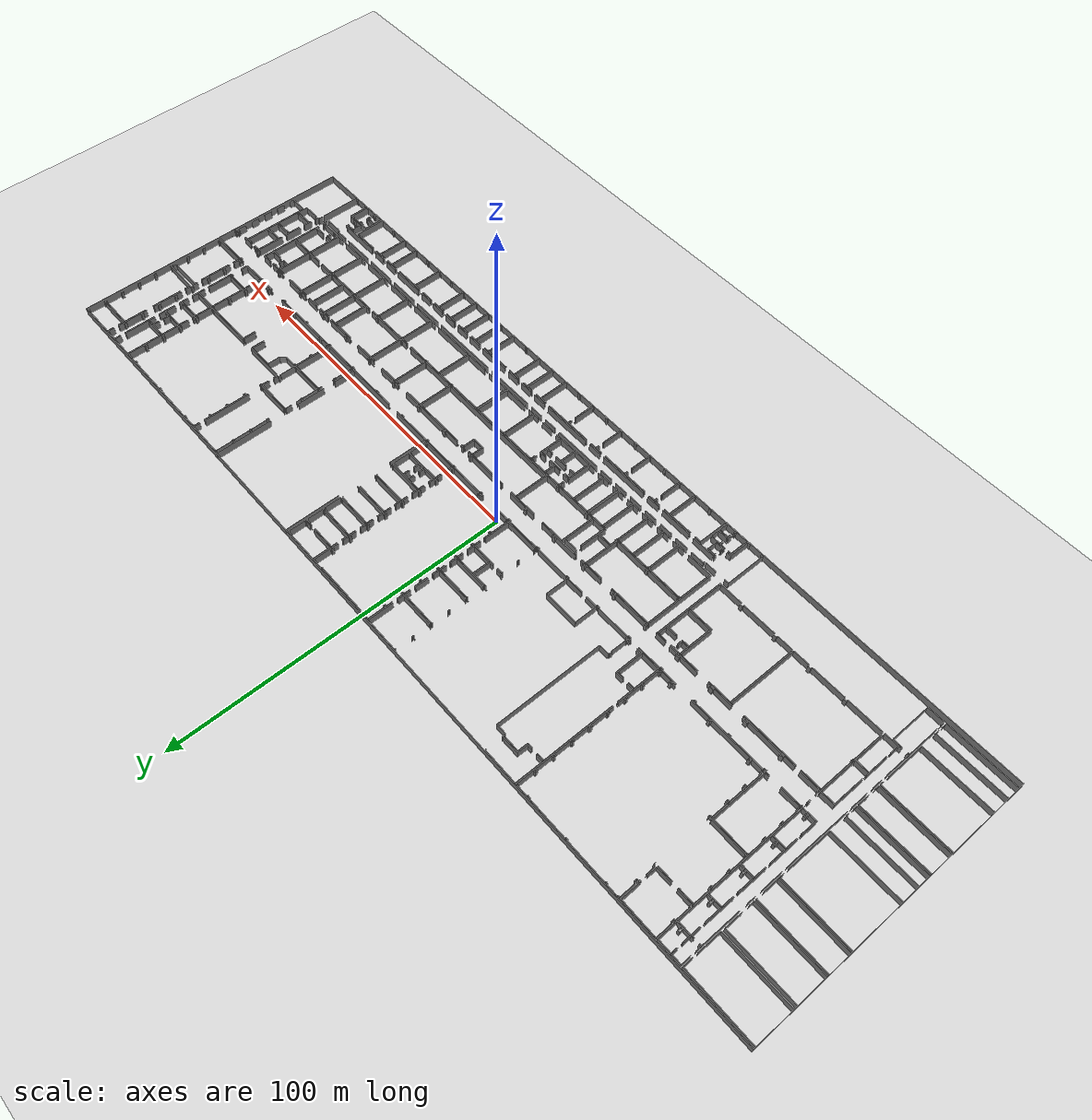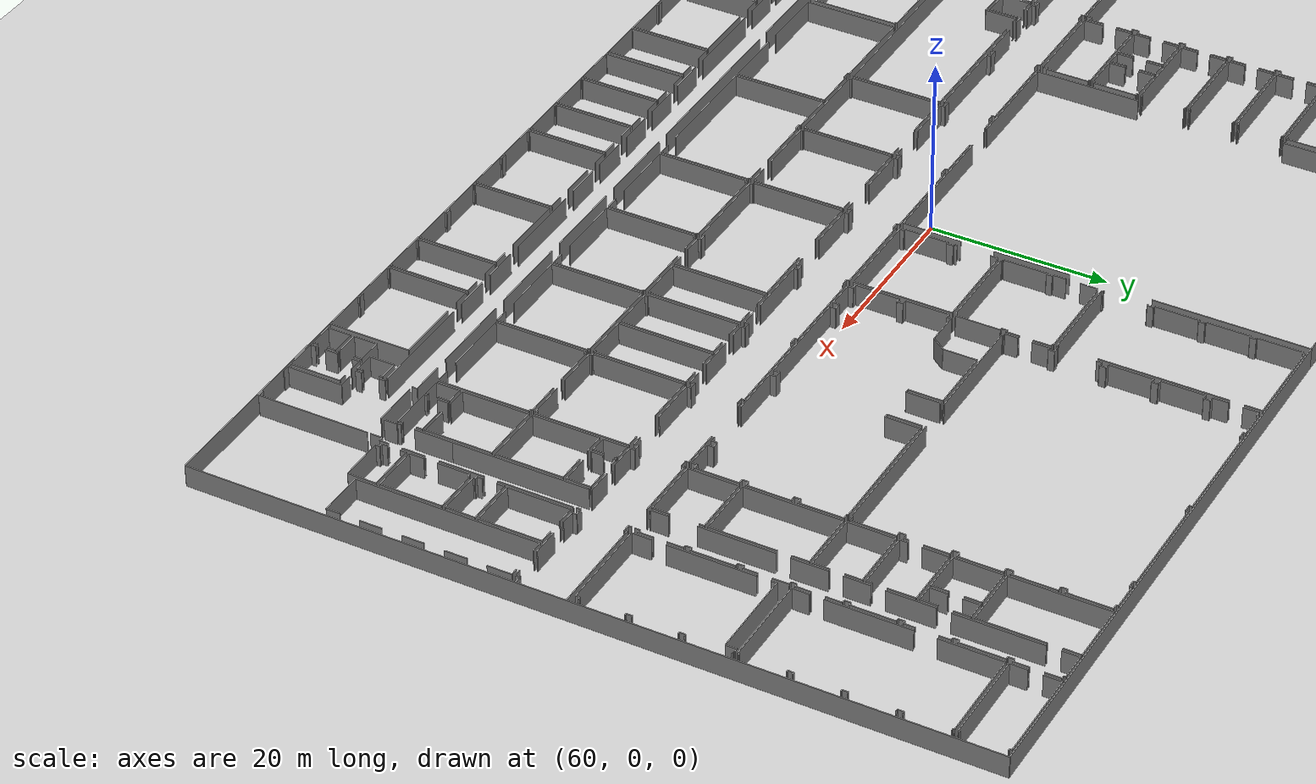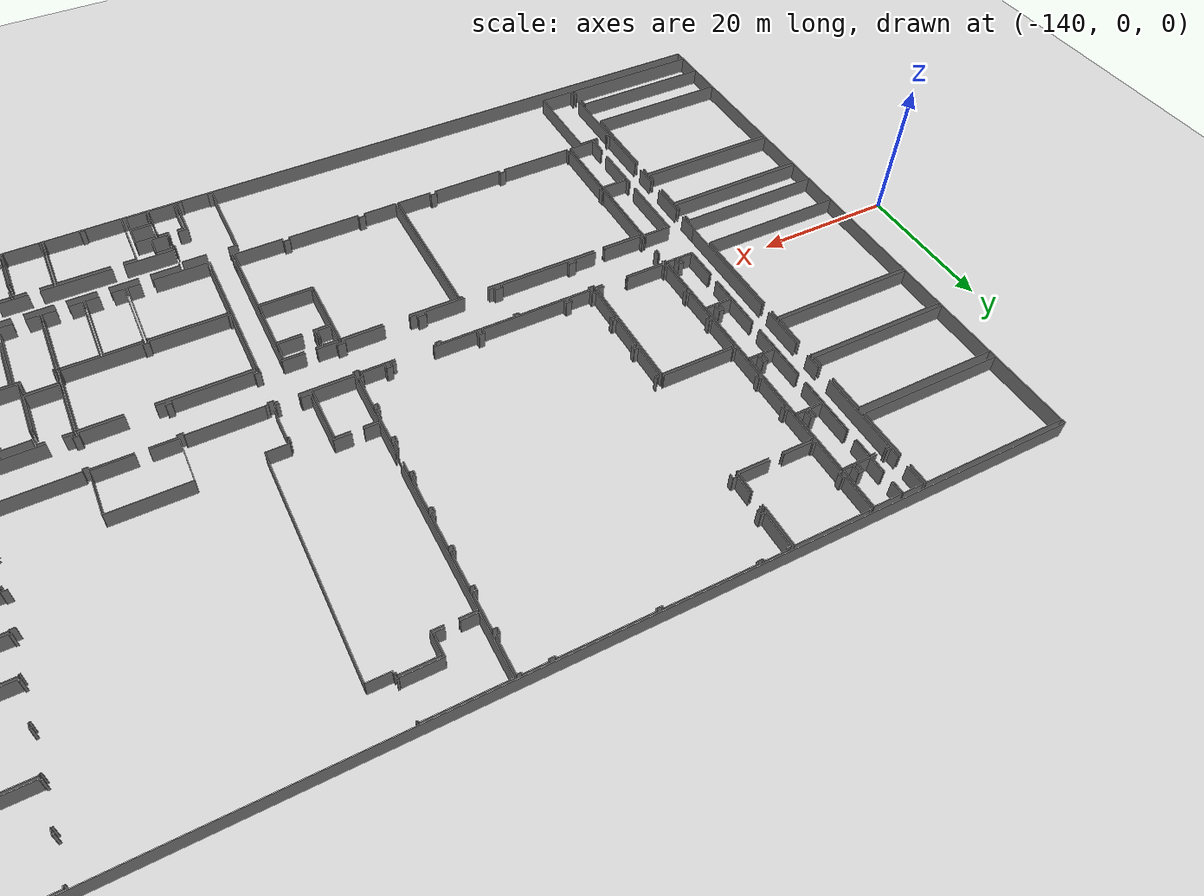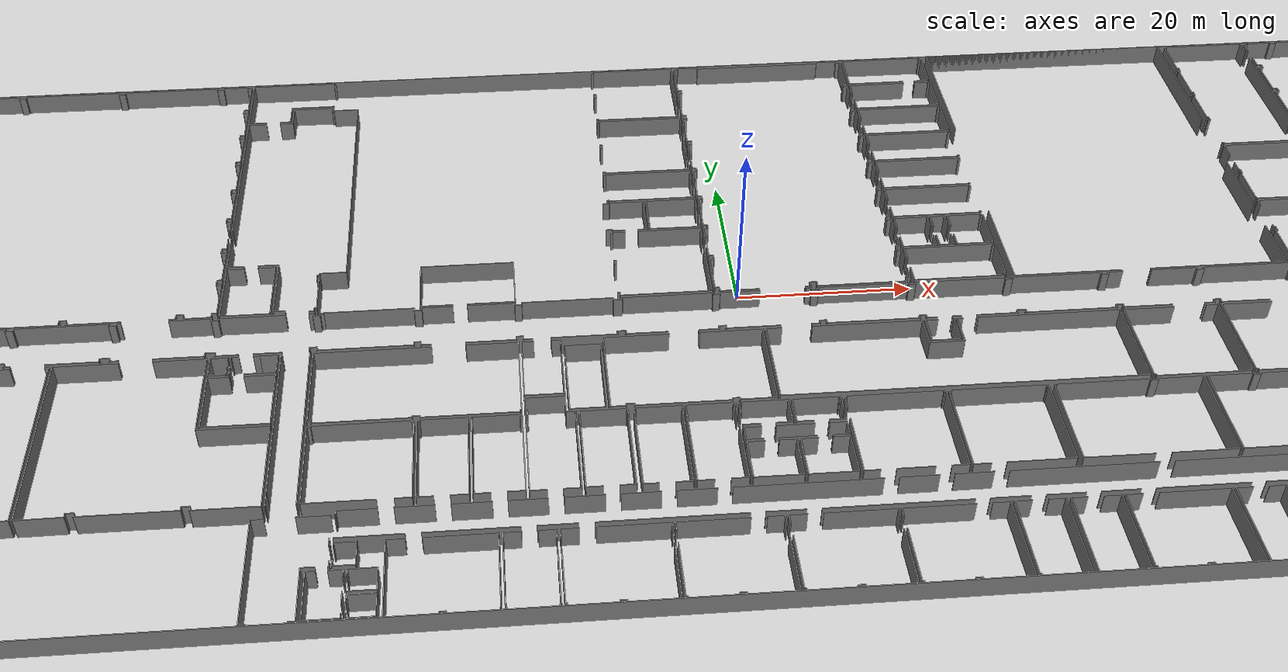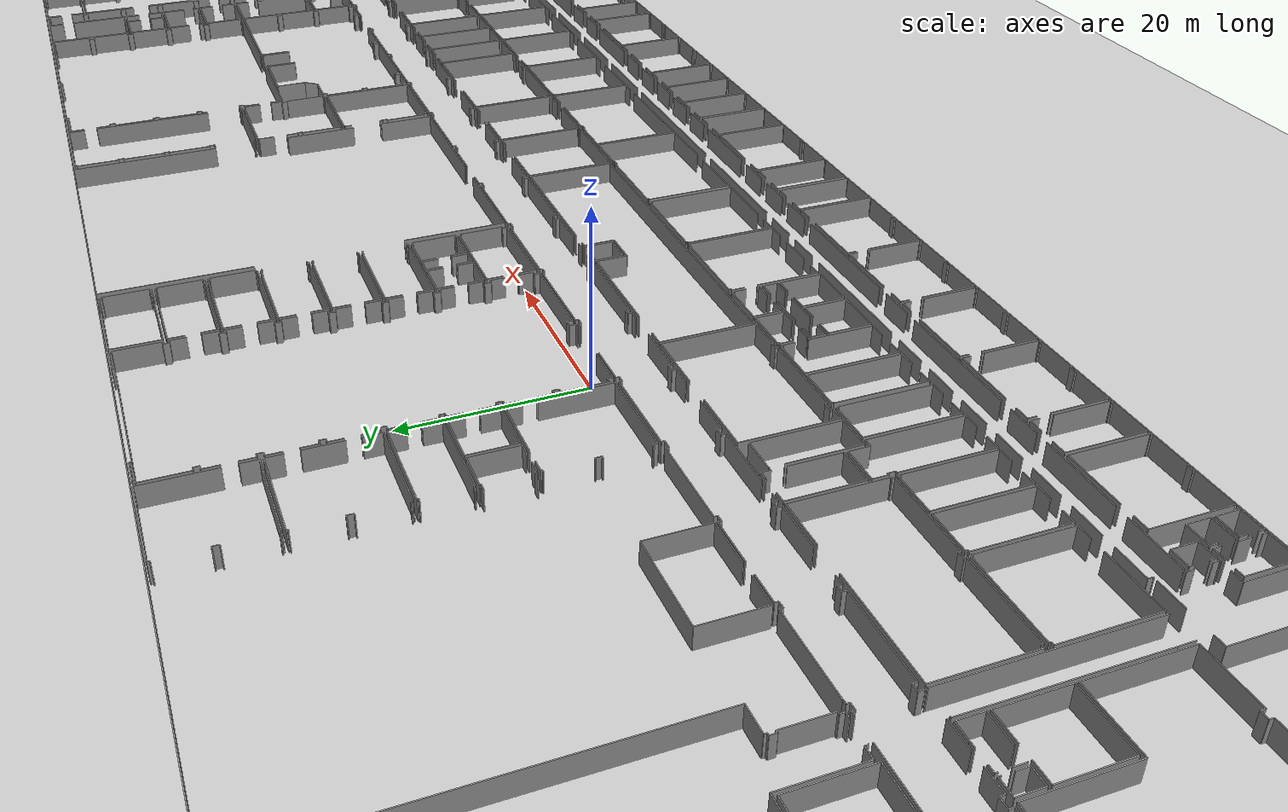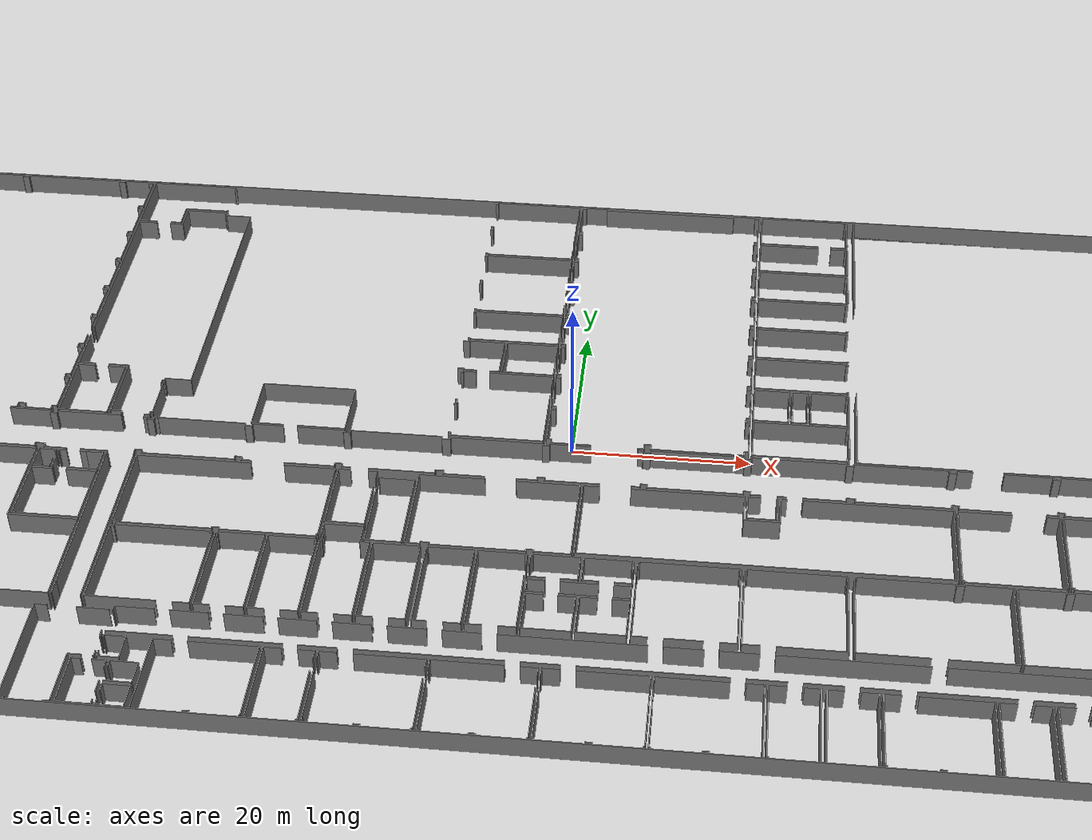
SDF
<sdf version="1.6">
  <world name="default">
    <light name="sun" type="directional">
      <cast_shadows>1</cast_shadows>
      <pose frame="">0 0 10 0 -0 0</pose>
      <diffuse>0.8 0.8 0.8 1</diffuse>
      <specular>0.1 0.1 0.1 1</specular>
      <attenuation>
        <range>1000</range>
        <constant>0.9</constant>
        <linear>0.01</linear>
        <quadratic>0.001</quadratic>
      </attenuation>
      <direction>-0.5 0.5 -1</direction>
    </light>
    <model name="ground_plane">
      <static>1</static>
      <link name="link">
        <collision name="collision">
          <geometry>
            <plane>
              <normal>0 0 1</normal>
              <size>100 100</size>
            </plane>
          </geometry>
          <surface>
            <friction>
              <ode>
                <mu>100</mu>
                <mu2>50</mu2>
              </ode>
              <torsional>
                <ode />
              </torsional>
            </friction>
            <contact>
              <ode />
            </contact>
            <bounce />
          </surface>
          <max_contacts>10</max_contacts>
        </collision>
        <visual name="visual">
          <cast_shadows>0</cast_shadows>
          <geometry>
            <plane>
              <normal>0 0 1</normal>
              <size>100 100</size>
            </plane>
          </geometry>
          <material>
            <script>
              <uri>file://media/materials/scripts/gazebo.material</uri>
              <name>Gazebo/Grey</name>
            </script>
          </material>
        </visual>
        <self_collide>0</self_collide>
        <kinematic>0</kinematic>
        <gravity>1</gravity>
      </link>
    </model>
    <gravity>0 0 -9.8</gravity>
    <magnetic_field>6e-06 2.3e-05 -4.2e-05</magnetic_field>
    <atmosphere type="adiabatic" />
    <physics default="0" name="default_physics" type="ode">
      <max_step_size>0.001</max_step_size>
      <real_time_factor>1</real_time_factor>
      <real_time_update_rate>1000</real_time_update_rate>
    </physics>
    <scene>
      <ambient>0.4 0.4 0.4 1</ambient>
      <background>0.7 0.7 0.7 1</background>
      <shadows>1</shadows>
    </scene>
    <spherical_coordinates>
      <surface_model>EARTH_WGS84</surface_model>
      <latitude_deg>0</latitude_deg>
      <longitude_deg>0</longitude_deg>
      <elevation>0</elevation>
      <heading_deg>0</heading_deg>
    </spherical_coordinates>
  <model name="50015847">
		<static>1</static>
		<link name="Wall_0">
			<collision name="Wall_0_Collision">
				<geometry>
					<box>
						<size>11.3634514669 0.1 2.5</size>
					</box>
				</geometry>
				<pose frame="">5.68172573346 0 1.25 0 0 0</pose>
			</collision>
			<visual name="Wall_0_Visual">
				<pose frame="">5.68172573346 0 1.25 0 0 0</pose>
				<geometry>
					<box>
						<size>11.3634514669 0.1 2.5</size>
					</box>
				</geometry>
				<material>
					<script>
						<uri>file://media/materials/scripts/gazebo.material</uri>
						<name>Gazebo/Grey</name>
					</script>
					<ambient>1 1 1 1</ambient>
				</material>
			</visual>
			<pose frame="">0.0101693191641 -11.97132252 0 0 0 1.57079632679</pose>
		</link>
		<link name="Wall_1">
			<collision name="Wall_1_Collision">
				<geometry>
					<box>
						<size>20.7250724564 0.1 2.5</size>
					</box>
				</geometry>
				<pose frame="">10.3625362282 0 1.25 0 0 0</pose>
			</collision>
			<visual name="Wall_1_Visual">
				<pose frame="">10.3625362282 0 1.25 0 0 0</pose>
				<geometry>
					<box>
						<size>20.7250724564 0.1 2.5</size>
					</box>
				</geometry>
				<material>
					<script>
						<uri>file://media/materials/scripts/gazebo.material</uri>
						<name>Gazebo/Grey</name>
					</script>
					<ambient>1 1 1 1</ambient>
				</material>
			</visual>
			<pose frame="">0.0101693191641 -0.607871053033 0 0 0 0.0</pose>
		</link>
		<link name="Wall_2">
			<collision name="Wall_2_Collision">
				<geometry>
					<box>
						<size>2.81257944781 0.1 2.5</size>
					</box>
				</geometry>
				<pose frame="">1.4062897239 0 1.25 0 0 0</pose>
			</collision>
			<visual name="Wall_2_Visual">
				<pose frame="">1.4062897239 0 1.25 0 0 0</pose>
				<geometry>
					<box>
						<size>2.81257944781 0.1 2.5</size>
					</box>
				</geometry>
				<material>
					<script>
						<uri>file://media/materials/scripts/gazebo.material</uri>
						<name>Gazebo/Grey</name>
					</script>
					<ambient>1 1 1 1</ambient>
				</material>
			</visual>
			<pose frame="">20.7352417756 -0.607871053033 0 0 0 -1.57079632679</pose>
		</link>
		<link name="Wall_3">
			<collision name="Wall_3_Collision">
				<geometry>
					<box>
						<size>6.90954390604 0.1 2.5</size>
					</box>
				</geometry>
				<pose frame="">3.45477195302 0 1.25 0 0 0</pose>
			</collision>
			<visual name="Wall_3_Visual">
				<pose frame="">3.45477195302 0 1.25 0 0 0</pose>
				<geometry>
					<box>
						<size>6.90954390604 0.1 2.5</size>
					</box>
				</geometry>
				<material>
					<script>
						<uri>file://media/materials/scripts/gazebo.material</uri>
						<name>Gazebo/Grey</name>
					</script>
					<ambient>1 1 1 1</ambient>
				</material>
			</visual>
			<pose frame="">20.7352417756 -5.07652412671 0 0 0 -1.57079632679</pose>
		</link>
		<link name="Wall_4">
			<collision name="Wall_4_Collision">
				<geometry>
					<box>
						<size>20.725077702 0.1 2.5</size>
					</box>
				</geometry>
				<pose frame="">10.362538851 0 1.25 0 0 0</pose>
			</collision>
			<visual name="Wall_4_Visual">
				<pose frame="">10.362538851 0 1.25 0 0 0</pose>
				<geometry>
					<box>
						<size>20.725077702 0.1 2.5</size>
					</box>
				</geometry>
				<material>
					<script>
						<uri>file://media/materials/scripts/gazebo.material</uri>
						<name>Gazebo/Grey</name>
					</script>
					<ambient>1 1 1 1</ambient>
				</material>
			</visual>
			<pose frame="">20.7352417756 -11.9860680327 0 0 0 3.14088117186</pose>
		</link>
		<link name="Wall_5">
			<collision name="Wall_5_Collision">
				<geometry>
					<box>
						<size>2.36589210352 0.1 2.5</size>
					</box>
				</geometry>
				<pose frame="">1.18294605176 0 1.25 0 0 0</pose>
			</collision>
			<visual name="Wall_5_Visual">
				<pose frame="">1.18294605176 0 1.25 0 0 0</pose>
				<geometry>
					<box>
						<size>2.36589210352 0.1 2.5</size>
					</box>
				</geometry>
				<material>
					<script>
						<uri>file://media/materials/scripts/gazebo.material</uri>
						<name>Gazebo/Grey</name>
					</script>
					<ambient>1 1 1 1</ambient>
				</material>
			</visual>
			<pose frame="">24.3161132862 -6.29023236894 0 0 0 1.57079632679</pose>
		</link>
		<link name="Wall_6">
			<collision name="Wall_6_Collision">
				<geometry>
					<box>
						<size>1.8065795495 0.1 2.5</size>
					</box>
				</geometry>
				<pose frame="">0.90328977475 0 1.25 0 0 0</pose>
			</collision>
			<visual name="Wall_6_Visual">
				<pose frame="">0.90328977475 0 1.25 0 0 0</pose>
				<geometry>
					<box>
						<size>1.8065795495 0.1 2.5</size>
					</box>
				</geometry>
				<material>
					<script>
						<uri>file://media/materials/scripts/gazebo.material</uri>
						<name>Gazebo/Grey</name>
					</script>
					<ambient>1 1 1 1</ambient>
				</material>
			</visual>
			<pose frame="">24.3161132862 -2.41445060253 0 0 0 1.57079632679</pose>
		</link>
		<link name="Wall_7">
			<collision name="Wall_7_Collision">
				<geometry>
					<box>
						<size>3.93934001119 0.1 2.5</size>
					</box>
				</geometry>
				<pose frame="">1.96967000559 0 1.25 0 0 0</pose>
			</collision>
			<visual name="Wall_7_Visual">
				<pose frame="">1.96967000559 0 1.25 0 0 0</pose>
				<geometry>
					<box>
						<size>3.93934001119 0.1 2.5</size>
					</box>
				</geometry>
				<material>
					<script>
						<uri>file://media/materials/scripts/gazebo.material</uri>
						<name>Gazebo/Grey</name>
					</script>
					<ambient>1 1 1 1</ambient>
				</material>
			</visual>
			<pose frame="">24.3161132862 -0.607871053033 0 0 0 0.0</pose>
		</link>
		<link name="Wall_8">
			<collision name="Wall_8_Collision">
				<geometry>
					<box>
						<size>5.67727665633 0.1 2.5</size>
					</box>
				</geometry>
				<pose frame="">2.83863832816 0 1.25 0 0 0</pose>
			</collision>
			<visual name="Wall_8_Visual">
				<pose frame="">2.83863832816 0 1.25 0 0 0</pose>
				<geometry>
					<box>
						<size>5.67727665633 0.1 2.5</size>
					</box>
				</geometry>
				<material>
					<script>
						<uri>file://media/materials/scripts/gazebo.material</uri>
						<name>Gazebo/Grey</name>
					</script>
					<ambient>1 1 1 1</ambient>
				</material>
			</visual>
			<pose frame="">28.2554532974 -0.607871053033 0 0 0 -1.57079632679</pose>
		</link>
		<link name="Wall_9">
			<collision name="Wall_9_Collision">
				<geometry>
					<box>
						<size>1.33828240199 0.1 2.5</size>
					</box>
				</geometry>
				<pose frame="">0.669141200997 0 1.25 0 0 0</pose>
			</collision>
			<visual name="Wall_9_Visual">
				<pose frame="">0.669141200997 0 1.25 0 0 0</pose>
				<geometry>
					<box>
						<size>1.33828240199 0.1 2.5</size>
					</box>
				</geometry>
				<material>
					<script>
						<uri>file://media/materials/scripts/gazebo.material</uri>
						<name>Gazebo/Grey</name>
					</script>
					<ambient>1 1 1 1</ambient>
				</material>
			</visual>
			<pose frame="">28.2554532974 -6.28514770936 0 0 0 3.14159265359</pose>
		</link>
		<link name="Wall_10">
			<collision name="Wall_10_Collision">
				<geometry>
					<box>
						<size>1.15650582194 0.1 2.5</size>
					</box>
				</geometry>
				<pose frame="">0.578252910968 0 1.25 0 0 0</pose>
			</collision>
			<visual name="Wall_10_Visual">
				<pose frame="">0.578252910968 0 1.25 0 0 0</pose>
				<geometry>
					<box>
						<size>1.15650582194 0.1 2.5</size>
					</box>
				</geometry>
				<material>
					<script>
						<uri>file://media/materials/scripts/gazebo.material</uri>
						<name>Gazebo/Grey</name>
					</script>
					<ambient>1 1 1 1</ambient>
				</material>
			</visual>
			<pose frame="">26.9171708954 -6.28514770936 0 0 0 1.57079632679</pose>
		</link>
		<link name="Wall_11">
			<collision name="Wall_11_Collision">
				<geometry>
					<box>
						<size>0.678547821223 0.1 2.5</size>
					</box>
				</geometry>
				<pose frame="">0.339273910612 0 1.25 0 0 0</pose>
			</collision>
			<visual name="Wall_11_Visual">
				<pose frame="">0.339273910612 0 1.25 0 0 0</pose>
				<geometry>
					<box>
						<size>0.678547821223 0.1 2.5</size>
					</box>
				</geometry>
				<material>
					<script>
						<uri>file://media/materials/scripts/gazebo.material</uri>
						<name>Gazebo/Grey</name>
					</script>
					<ambient>1 1 1 1</ambient>
				</material>
			</visual>
			<pose frame="">26.9171708954 -5.12864188743 0 0 0 3.14159265359</pose>
		</link>
		<link name="Wall_12">
			<collision name="Wall_12_Collision">
				<geometry>
					<box>
						<size>1.18523414857 0.1 2.5</size>
					</box>
				</geometry>
				<pose frame="">0.592617074287 0 1.25 0 0 0</pose>
			</collision>
			<visual name="Wall_12_Visual">
				<pose frame="">0.592617074287 0 1.25 0 0 0</pose>
				<geometry>
					<box>
						<size>1.18523414857 0.1 2.5</size>
					</box>
				</geometry>
				<material>
					<script>
						<uri>file://media/materials/scripts/gazebo.material</uri>
						<name>Gazebo/Grey</name>
					</script>
					<ambient>1 1 1 1</ambient>
				</material>
			</visual>
			<pose frame="">26.2386230742 -5.12864188743 0 0 0 -1.57079632679</pose>
		</link>
		<link name="Wall_13">
			<collision name="Wall_13_Collision">
				<geometry>
					<box>
						<size>1.92265517133 0.1 2.5</size>
					</box>
				</geometry>
				<pose frame="">0.961327585664 0 1.25 0 0 0</pose>
			</collision>
			<visual name="Wall_13_Visual">
				<pose frame="">0.961327585664 0 1.25 0 0 0</pose>
				<geometry>
					<box>
						<size>1.92265517133 0.1 2.5</size>
					</box>
				</geometry>
				<material>
					<script>
						<uri>file://media/materials/scripts/gazebo.material</uri>
						<name>Gazebo/Grey</name>
					</script>
					<ambient>1 1 1 1</ambient>
				</material>
			</visual>
			<pose frame="">26.2386230742 -6.313876036 0 0 0 3.1292949398</pose>
		</link>
		<link name="Wall_14">
			<collision name="Wall_14_Collision">
				<geometry>
					<box>
						<size>2.85783291809 0.1 2.5</size>
					</box>
				</geometry>
				<pose frame="">1.42891645904 0 1.25 0 0 0</pose>
			</collision>
			<visual name="Wall_14_Visual">
				<pose frame="">1.42891645904 0 1.25 0 0 0</pose>
				<geometry>
					<box>
						<size>2.85783291809 0.1 2.5</size>
					</box>
				</geometry>
				<material>
					<script>
						<uri>file://media/materials/scripts/gazebo.material</uri>
						<name>Gazebo/Grey</name>
					</script>
					<ambient>1 1 1 1</ambient>
				</material>
			</visual>
			<pose frame="">21.2576905476 -0.604566024305 0 0 0 0.0</pose>
		</link>
		<link name="Wall_15">
			<collision name="Wall_15_Collision">
				<geometry>
					<box>
						<size>1.82463009102 0.1 2.5</size>
					</box>
				</geometry>
				<pose frame="">0.912315045508 0 1.25 0 0 0</pose>
			</collision>
			<visual name="Wall_15_Visual">
				<pose frame="">0.912315045508 0 1.25 0 0 0</pose>
				<geometry>
					<box>
						<size>1.82463009102 0.1 2.5</size>
					</box>
				</geometry>
				<material>
					<script>
						<uri>file://media/materials/scripts/gazebo.material</uri>
						<name>Gazebo/Grey</name>
					</script>
					<ambient>1 1 1 1</ambient>
				</material>
			</visual>
			<pose frame="">24.1155234657 -0.604566024305 0 0 0 -1.57079632679</pose>
		</link>
		<link name="Wall_16">
			<collision name="Wall_16_Collision">
				<geometry>
					<box>
						<size>2.38063761631 0.1 2.5</size>
					</box>
				</geometry>
				<pose frame="">1.19031880816 0 1.25 0 0 0</pose>
			</collision>
			<visual name="Wall_16_Visual">
				<pose frame="">1.19031880816 0 1.25 0 0 0</pose>
				<geometry>
					<box>
						<size>2.38063761631 0.1 2.5</size>
					</box>
				</geometry>
				<material>
					<script>
						<uri>file://media/materials/scripts/gazebo.material</uri>
						<name>Gazebo/Grey</name>
					</script>
					<ambient>1 1 1 1</ambient>
				</material>
			</visual>
			<pose frame="">24.1155234657 -3.92128946967 0 0 0 -1.57079632679</pose>
		</link>
		<link name="Wall_17">
			<collision name="Wall_17_Collision">
				<geometry>
					<box>
						<size>0.758122743682 0.1 2.5</size>
					</box>
				</geometry>
				<pose frame="">0.379061371841 0 1.25 0 0 0</pose>
			</collision>
			<visual name="Wall_17_Visual">
				<pose frame="">0.379061371841 0 1.25 0 0 0</pose>
				<geometry>
					<box>
						<size>0.758122743682 0.1 2.5</size>
					</box>
				</geometry>
				<material>
					<script>
						<uri>file://media/materials/scripts/gazebo.material</uri>
						<name>Gazebo/Grey</name>
					</script>
					<ambient>1 1 1 1</ambient>
				</material>
			</visual>
			<pose frame="">24.1155234657 -6.30192708598 0 0 0 3.14159265359</pose>
		</link>
		<link name="Wall_18">
			<collision name="Wall_18_Collision">
				<geometry>
					<box>
						<size>0.563888747648 0.1 2.5</size>
					</box>
				</geometry>
				<pose frame="">0.281944373824 0 1.25 0 0 0</pose>
			</collision>
			<visual name="Wall_18_Visual">
				<pose frame="">0.281944373824 0 1.25 0 0 0</pose>
				<geometry>
					<box>
						<size>0.563888747648 0.1 2.5</size>
					</box>
				</geometry>
				<material>
					<script>
						<uri>file://media/materials/scripts/gazebo.material</uri>
						<name>Gazebo/Grey</name>
					</script>
					<ambient>1 1 1 1</ambient>
				</material>
			</visual>
			<pose frame="">21.8327655463 -6.30192708598 0 0 0 3.14159265359</pose>
		</link>
		<link name="Wall_19">
			<collision name="Wall_19_Collision">
				<geometry>
					<box>
						<size>1.3588752733 0.1 2.5</size>
					</box>
				</geometry>
				<pose frame="">0.67943763665 0 1.25 0 0 0</pose>
			</collision>
			<visual name="Wall_19_Visual">
				<pose frame="">0.67943763665 0 1.25 0 0 0</pose>
				<geometry>
					<box>
						<size>1.3588752733 0.1 2.5</size>
					</box>
				</geometry>
				<material>
					<script>
						<uri>file://media/materials/scripts/gazebo.material</uri>
						<name>Gazebo/Grey</name>
					</script>
					<ambient>1 1 1 1</ambient>
				</material>
			</visual>
			<pose frame="">21.2688767987 -6.30192708598 0 0 0 1.57079632679</pose>
		</link>
		<link name="Wall_20">
			<collision name="Wall_20_Collision">
				<geometry>
					<box>
						<size>2.78412782666 0.1 2.5</size>
					</box>
				</geometry>
				<pose frame="">1.39206391333 0 1.25 0 0 0</pose>
			</collision>
			<visual name="Wall_20_Visual">
				<pose frame="">1.39206391333 0 1.25 0 0 0</pose>
				<geometry>
					<box>
						<size>2.78412782666 0.1 2.5</size>
					</box>
				</geometry>
				<material>
					<script>
						<uri>file://media/materials/scripts/gazebo.material</uri>
						<name>Gazebo/Grey</name>
					</script>
					<ambient>1 1 1 1</ambient>
				</material>
			</visual>
			<pose frame="">21.2688767987 -3.38867137845 0 0 0 1.57481420308</pose>
		</link>
		<link name="Wall_21">
			<collision name="Wall_21_Collision">
				<geometry>
					<box>
						<size>9.05450755072 0.1 2.5</size>
					</box>
				</geometry>
				<pose frame="">4.52725377536 0 1.25 0 0 0</pose>
			</collision>
			<visual name="Wall_21_Visual">
				<pose frame="">4.52725377536 0 1.25 0 0 0</pose>
				<geometry>
					<box>
						<size>9.05450755072 0.1 2.5</size>
					</box>
				</geometry>
				<material>
					<script>
						<uri>file://media/materials/scripts/gazebo.material</uri>
						<name>Gazebo/Grey</name>
					</script>
					<ambient>1 1 1 1</ambient>
				</material>
			</visual>
			<pose frame="">0.0101693191641 -22.0885239233 0 0 0 1.57079632679</pose>
		</link>
		<link name="Wall_22">
			<collision name="Wall_22_Collision">
				<geometry>
					<box>
						<size>20.6960898968 0.1 2.5</size>
					</box>
				</geometry>
				<pose frame="">10.3480449484 0 1.25 0 0 0</pose>
			</collision>
			<visual name="Wall_22_Visual">
				<pose frame="">10.3480449484 0 1.25 0 0 0</pose>
				<geometry>
					<box>
						<size>20.6960898968 0.1 2.5</size>
					</box>
				</geometry>
				<material>
					<script>
						<uri>file://media/materials/scripts/gazebo.material</uri>
						<name>Gazebo/Grey</name>
					</script>
					<ambient>1 1 1 1</ambient>
				</material>
			</visual>
			<pose frame="">0.0101693191641 -13.0340163726 0 0 0 0.0</pose>
		</link>
		<link name="Wall_23">
			<collision name="Wall_23_Collision">
				<geometry>
					<box>
						<size>5.21686073117 0.1 2.5</size>
					</box>
				</geometry>
				<pose frame="">2.60843036559 0 1.25 0 0 0</pose>
			</collision>
			<visual name="Wall_23_Visual">
				<pose frame="">2.60843036559 0 1.25 0 0 0</pose>
				<geometry>
					<box>
						<size>5.21686073117 0.1 2.5</size>
					</box>
				</geometry>
				<material>
					<script>
						<uri>file://media/materials/scripts/gazebo.material</uri>
						<name>Gazebo/Grey</name>
					</script>
					<ambient>1 1 1 1</ambient>
				</material>
			</visual>
			<pose frame="">20.7062592159 -13.0340163726 0 0 0 -1.57079632679</pose>
		</link>
		<link name="Wall_24">
			<collision name="Wall_24_Collision">
				<geometry>
					<box>
						<size>1.56073625871 0.1 2.5</size>
					</box>
				</geometry>
				<pose frame="">0.780368129354 0 1.25 0 0 0</pose>
			</collision>
			<visual name="Wall_24_Visual">
				<pose frame="">0.780368129354 0 1.25 0 0 0</pose>
				<geometry>
					<box>
						<size>1.56073625871 0.1 2.5</size>
					</box>
				</geometry>
				<material>
					<script>
						<uri>file://media/materials/scripts/gazebo.material</uri>
						<name>Gazebo/Grey</name>
					</script>
					<ambient>1 1 1 1</ambient>
				</material>
			</visual>
			<pose frame="">20.7062592159 -20.5206691412 0 0 0 -1.57079632679</pose>
		</link>
		<link name="Wall_25">
			<collision name="Wall_25_Collision">
				<geometry>
					<box>
						<size>20.696091121 0.1 2.5</size>
					</box>
				</geometry>
				<pose frame="">10.3480455605 0 1.25 0 0 0</pose>
			</collision>
			<visual name="Wall_25_Visual">
				<pose frame="">10.3480455605 0 1.25 0 0 0</pose>
				<geometry>
					<box>
						<size>20.696091121 0.1 2.5</size>
					</box>
				</geometry>
				<material>
					<script>
						<uri>file://media/materials/scripts/gazebo.material</uri>
						<name>Gazebo/Grey</name>
					</script>
					<ambient>1 1 1 1</ambient>
				</material>
			</visual>
			<pose frame="">20.7062592159 -22.0814053999 0 0 0 -3.14124869861</pose>
		</link>
		<link name="Wall_26">
			<collision name="Wall_26_Collision">
				<geometry>
					<box>
						<size>6.87445975492 0.1 2.5</size>
					</box>
				</geometry>
				<pose frame="">3.43722987746 0 1.25 0 0 0</pose>
			</collision>
			<visual name="Wall_26_Visual">
				<pose frame="">3.43722987746 0 1.25 0 0 0</pose>
				<geometry>
					<box>
						<size>6.87445975492 0.1 2.5</size>
					</box>
				</geometry>
				<material>
					<script>
						<uri>file://media/materials/scripts/gazebo.material</uri>
						<name>Gazebo/Grey</name>
					</script>
					<ambient>1 1 1 1</ambient>
				</material>
			</visual>
			<pose frame="">0.0 -29.5220419993 0 0 0 1.57079632679</pose>
		</link>
		<link name="Wall_27">
			<collision name="Wall_27_Collision">
				<geometry>
					<box>
						<size>20.7334621447 0.1 2.5</size>
					</box>
				</geometry>
				<pose frame="">10.3667310724 0 1.25 0 0 0</pose>
			</collision>
			<visual name="Wall_27_Visual">
				<pose frame="">10.3667310724 0 1.25 0 0 0</pose>
				<geometry>
					<box>
						<size>20.7334621447 0.1 2.5</size>
					</box>
				</geometry>
				<material>
					<script>
						<uri>file://media/materials/scripts/gazebo.material</uri>
						<name>Gazebo/Grey</name>
					</script>
					<ambient>1 1 1 1</ambient>
				</material>
			</visual>
			<pose frame="">0.0 -22.6475822444 0 0 0 0.0</pose>
		</link>
		<link name="Wall_28">
			<collision name="Wall_28_Collision">
				<geometry>
					<box>
						<size>0.181776580058 0.1 2.5</size>
					</box>
				</geometry>
				<pose frame="">0.090888290029 0 1.25 0 0 0</pose>
			</collision>
			<visual name="Wall_28_Visual">
				<pose frame="">0.090888290029 0 1.25 0 0 0</pose>
				<geometry>
					<box>
						<size>0.181776580058 0.1 2.5</size>
					</box>
				</geometry>
				<material>
					<script>
						<uri>file://media/materials/scripts/gazebo.material</uri>
						<name>Gazebo/Grey</name>
					</script>
					<ambient>1 1 1 1</ambient>
				</material>
			</visual>
			<pose frame="">20.7334621447 -22.6475822444 0 0 0 -1.57079632679</pose>
		</link>
		<link name="Wall_29">
			<collision name="Wall_29_Collision">
				<geometry>
					<box>
						<size>4.44424670768 0.1 2.5</size>
					</box>
				</geometry>
				<pose frame="">2.22212335384 0 1.25 0 0 0</pose>
			</collision>
			<visual name="Wall_29_Visual">
				<pose frame="">2.22212335384 0 1.25 0 0 0</pose>
				<geometry>
					<box>
						<size>4.44424670768 0.1 2.5</size>
					</box>
				</geometry>
				<material>
					<script>
						<uri>file://media/materials/scripts/gazebo.material</uri>
						<name>Gazebo/Grey</name>
					</script>
					<ambient>1 1 1 1</ambient>
				</material>
			</visual>
			<pose frame="">20.7334621447 -25.1136421417 0 0 0 -1.57079632679</pose>
		</link>
		<link name="Wall_30">
			<collision name="Wall_30_Collision">
				<geometry>
					<box>
						<size>20.7334931332 0.1 2.5</size>
					</box>
				</geometry>
				<pose frame="">10.3667465666 0 1.25 0 0 0</pose>
			</collision>
			<visual name="Wall_30_Visual">
				<pose frame="">10.3667465666 0 1.25 0 0 0</pose>
				<geometry>
					<box>
						<size>20.7334931332 0.1 2.5</size>
					</box>
				</geometry>
				<material>
					<script>
						<uri>file://media/materials/scripts/gazebo.material</uri>
						<name>Gazebo/Grey</name>
					</script>
					<ambient>1 1 1 1</ambient>
				</material>
			</visual>
			<pose frame="">20.7334621447 -29.5578888493 0 0 0 3.1398637183</pose>
		</link>
		<link name="Wall_31">
			<collision name="Wall_31_Collision">
				<geometry>
					<box>
						<size>16.1043880612 0.1 2.5</size>
					</box>
				</geometry>
				<pose frame="">8.05219403061 0 1.25 0 0 0</pose>
			</collision>
			<visual name="Wall_31_Visual">
				<pose frame="">8.05219403061 0 1.25 0 0 0</pose>
				<geometry>
					<box>
						<size>16.1043880612 0.1 2.5</size>
					</box>
				</geometry>
				<material>
					<script>
						<uri>file://media/materials/scripts/gazebo.material</uri>
						<name>Gazebo/Grey</name>
					</script>
					<ambient>1 1 1 1</ambient>
				</material>
			</visual>
			<pose frame="">0.00330502872833 -46.1496415315 0 0 0 1.57079632679</pose>
		</link>
		<link name="Wall_32">
			<collision name="Wall_32_Collision">
				<geometry>
					<box>
						<size>20.7571058118 0.1 2.5</size>
					</box>
				</geometry>
				<pose frame="">10.3785529059 0 1.25 0 0 0</pose>
			</collision>
			<visual name="Wall_32_Visual">
				<pose frame="">10.3785529059 0 1.25 0 0 0</pose>
				<geometry>
					<box>
						<size>20.7571058118 0.1 2.5</size>
					</box>
				</geometry>
				<material>
					<script>
						<uri>file://media/materials/scripts/gazebo.material</uri>
						<name>Gazebo/Grey</name>
					</script>
					<ambient>1 1 1 1</ambient>
				</material>
			</visual>
			<pose frame="">0.00330502872833 -30.0452534703 0 0 0 0.0</pose>
		</link>
		<link name="Wall_33">
			<collision name="Wall_33_Collision">
				<geometry>
					<box>
						<size>1.22108099863 0.1 2.5</size>
					</box>
				</geometry>
				<pose frame="">0.610540499314 0 1.25 0 0 0</pose>
			</collision>
			<visual name="Wall_33_Visual">
				<pose frame="">0.610540499314 0 1.25 0 0 0</pose>
				<geometry>
					<box>
						<size>1.22108099863 0.1 2.5</size>
					</box>
				</geometry>
				<material>
					<script>
						<uri>file://media/materials/scripts/gazebo.material</uri>
						<name>Gazebo/Grey</name>
					</script>
					<ambient>1 1 1 1</ambient>
				</material>
			</visual>
			<pose frame="">20.7604108405 -30.0452534703 0 0 0 -1.57079632679</pose>
		</link>
		<link name="Wall_34">
			<collision name="Wall_34_Collision">
				<geometry>
					<box>
						<size>13.2437585804 0.1 2.5</size>
					</box>
				</geometry>
				<pose frame="">6.62187929018 0 1.25 0 0 0</pose>
			</collision>
			<visual name="Wall_34_Visual">
				<pose frame="">6.62187929018 0 1.25 0 0 0</pose>
				<geometry>
					<box>
						<size>13.2437585804 0.1 2.5</size>
					</box>
				</geometry>
				<material>
					<script>
						<uri>file://media/materials/scripts/gazebo.material</uri>
						<name>Gazebo/Grey</name>
					</script>
					<ambient>1 1 1 1</ambient>
				</material>
			</visual>
			<pose frame="">20.7604108405 -32.9297808512 0 0 0 -1.57079632679</pose>
		</link>
		<link name="Wall_35">
			<collision name="Wall_35_Collision">
				<geometry>
					<box>
						<size>20.7571195687 0.1 2.5</size>
					</box>
				</geometry>
				<pose frame="">10.3785597844 0 1.25 0 0 0</pose>
			</collision>
			<visual name="Wall_35_Visual">
				<pose frame="">10.3785597844 0 1.25 0 0 0</pose>
				<geometry>
					<box>
						<size>20.7571195687 0.1 2.5</size>
					</box>
				</geometry>
				<material>
					<script>
						<uri>file://media/materials/scripts/gazebo.material</uri>
						<name>Gazebo/Grey</name>
					</script>
					<ambient>1 1 1 1</ambient>
				</material>
			</visual>
			<pose frame="">20.7604108405 -46.1735394315 0 0 0 3.14044134234</pose>
		</link>
		<link name="Wall_36">
			<collision name="Wall_36_Collision">
				<geometry>
					<box>
						<size>3.59027813088 0.1 2.5</size>
					</box>
				</geometry>
				<pose frame="">1.79513906544 0 1.25 0 0 0</pose>
			</collision>
			<visual name="Wall_36_Visual">
				<pose frame="">1.79513906544 0 1.25 0 0 0</pose>
				<geometry>
					<box>
						<size>3.59027813088 0.1 2.5</size>
					</box>
				</geometry>
				<material>
					<script>
						<uri>file://media/materials/scripts/gazebo.material</uri>
						<name>Gazebo/Grey</name>
					</script>
					<ambient>1 1 1 1</ambient>
				</material>
			</visual>
			<pose frame="">0.0101693191641 -55.0701683022 0 0 0 1.57079632679</pose>
		</link>
		<link name="Wall_37">
			<collision name="Wall_37_Collision">
				<geometry>
					<box>
						<size>20.7502415213 0.1 2.5</size>
					</box>
				</geometry>
				<pose frame="">10.3751207607 0 1.25 0 0 0</pose>
			</collision>
			<visual name="Wall_37_Visual">
				<pose frame="">10.3751207607 0 1.25 0 0 0</pose>
				<geometry>
					<box>
						<size>20.7502415213 0.1 2.5</size>
					</box>
				</geometry>
				<material>
					<script>
						<uri>file://media/materials/scripts/gazebo.material</uri>
						<name>Gazebo/Grey</name>
					</script>
					<ambient>1 1 1 1</ambient>
				</material>
			</visual>
			<pose frame="">0.0101693191641 -51.4798901714 0 0 0 0.0</pose>
		</link>
		<link name="Wall_38">
			<collision name="Wall_38_Collision">
				<geometry>
					<box>
						<size>0.692784868053 0.1 2.5</size>
					</box>
				</geometry>
				<pose frame="">0.346392434027 0 1.25 0 0 0</pose>
			</collision>
			<visual name="Wall_38_Visual">
				<pose frame="">0.346392434027 0 1.25 0 0 0</pose>
				<geometry>
					<box>
						<size>0.692784868053 0.1 2.5</size>
					</box>
				</geometry>
				<material>
					<script>
						<uri>file://media/materials/scripts/gazebo.material</uri>
						<name>Gazebo/Grey</name>
					</script>
					<ambient>1 1 1 1</ambient>
				</material>
			</visual>
			<pose frame="">20.7604108405 -51.4798901714 0 0 0 -1.57079632679</pose>
		</link>
		<link name="Wall_39">
			<collision name="Wall_39_Collision">
				<geometry>
					<box>
						<size>0.328469009 0.1 2.5</size>
					</box>
				</geometry>
				<pose frame="">0.1642345045 0 1.25 0 0 0</pose>
			</collision>
			<visual name="Wall_39_Visual">
				<pose frame="">0.1642345045 0 1.25 0 0 0</pose>
				<geometry>
					<box>
						<size>0.328469009 0.1 2.5</size>
					</box>
				</geometry>
				<material>
					<script>
						<uri>file://media/materials/scripts/gazebo.material</uri>
						<name>Gazebo/Grey</name>
					</script>
					<ambient>1 1 1 1</ambient>
				</material>
			</visual>
			<pose frame="">20.7604108405 -52.1726750394 0 0 0 -1.57079632679</pose>
		</link>
		<link name="Wall_40">
			<collision name="Wall_40_Collision">
				<geometry>
					<box>
						<size>0.925662276911 0.1 2.5</size>
					</box>
				</geometry>
				<pose frame="">0.462831138455 0 1.25 0 0 0</pose>
			</collision>
			<visual name="Wall_40_Visual">
				<pose frame="">0.462831138455 0 1.25 0 0 0</pose>
				<geometry>
					<box>
						<size>0.925662276911 0.1 2.5</size>
					</box>
				</geometry>
				<material>
					<script>
						<uri>file://media/materials/scripts/gazebo.material</uri>
						<name>Gazebo/Grey</name>
					</script>
					<ambient>1 1 1 1</ambient>
				</material>
			</visual>
			<pose frame="">20.7604108405 -54.1623023339 0 0 0 -1.57079632679</pose>
		</link>
		<link name="Wall_41">
			<collision name="Wall_41_Collision">
				<geometry>
					<box>
						<size>20.7502491528 0.1 2.5</size>
					</box>
				</geometry>
				<pose frame="">10.3751245764 0 1.25 0 0 0</pose>
			</collision>
			<visual name="Wall_41_Visual">
				<pose frame="">10.3751245764 0 1.25 0 0 0</pose>
				<geometry>
					<box>
						<size>20.7502491528 0.1 2.5</size>
					</box>
				</geometry>
				<material>
					<script>
						<uri>file://media/materials/scripts/gazebo.material</uri>
						<name>Gazebo/Grey</name>
					</script>
					<ambient>1 1 1 1</ambient>
				</material>
			</visual>
			<pose frame="">20.7604108405 -55.0879646108 0 0 0 3.14073501036</pose>
		</link>
		<link name="Wall_42">
			<collision name="Wall_42_Collision">
				<geometry>
					<box>
						<size>6.89327299537 0.1 2.5</size>
					</box>
				</geometry>
				<pose frame="">3.44663649769 0 1.25 0 0 0</pose>
			</collision>
			<visual name="Wall_42_Visual">
				<pose frame="">3.44663649769 0 1.25 0 0 0</pose>
				<geometry>
					<box>
						<size>6.89327299537 0.1 2.5</size>
					</box>
				</geometry>
				<material>
					<script>
						<uri>file://media/materials/scripts/gazebo.material</uri>
						<name>Gazebo/Grey</name>
					</script>
					<ambient>1 1 1 1</ambient>
				</material>
			</visual>
			<pose frame="">0.012457415976 -62.5209742208 0 0 0 1.57079632679</pose>
		</link>
		<link name="Wall_43">
			<collision name="Wall_43_Collision">
				<geometry>
					<box>
						<size>20.7428687649 0.1 2.5</size>
					</box>
				</geometry>
				<pose frame="">10.3714343825 0 1.25 0 0 0</pose>
			</collision>
			<visual name="Wall_43_Visual">
				<pose frame="">10.3714343825 0 1.25 0 0 0</pose>
				<geometry>
					<box>
						<size>20.7428687649 0.1 2.5</size>
					</box>
				</geometry>
				<material>
					<script>
						<uri>file://media/materials/scripts/gazebo.material</uri>
						<name>Gazebo/Grey</name>
					</script>
					<ambient>1 1 1 1</ambient>
				</material>
			</visual>
			<pose frame="">0.012457415976 -55.6277012254 0 0 0 0.0</pose>
		</link>
		<link name="Wall_44">
			<collision name="Wall_44_Collision">
				<geometry>
					<box>
						<size>3.4257893934 0.1 2.5</size>
					</box>
				</geometry>
				<pose frame="">1.7128946967 0 1.25 0 0 0</pose>
			</collision>
			<visual name="Wall_44_Visual">
				<pose frame="">1.7128946967 0 1.25 0 0 0</pose>
				<geometry>
					<box>
						<size>3.4257893934 0.1 2.5</size>
					</box>
				</geometry>
				<material>
					<script>
						<uri>file://media/materials/scripts/gazebo.material</uri>
						<name>Gazebo/Grey</name>
					</script>
					<ambient>1 1 1 1</ambient>
				</material>
			</visual>
			<pose frame="">20.7553261809 -55.6277012254 0 0 0 -1.57079632679</pose>
		</link>
		<link name="Wall_45">
			<collision name="Wall_45_Collision">
				<geometry>
					<box>
						<size>1.17023440281 0.1 2.5</size>
					</box>
				</geometry>
				<pose frame="">0.585117201403 0 1.25 0 0 0</pose>
			</collision>
			<visual name="Wall_45_Visual">
				<pose frame="">0.585117201403 0 1.25 0 0 0</pose>
				<geometry>
					<box>
						<size>1.17023440281 0.1 2.5</size>
					</box>
				</geometry>
				<material>
					<script>
						<uri>file://media/materials/scripts/gazebo.material</uri>
						<name>Gazebo/Grey</name>
					</script>
					<ambient>1 1 1 1</ambient>
				</material>
			</visual>
			<pose frame="">20.7553261809 -61.3606549042 0 0 0 -1.57079632679</pose>
		</link>
		<link name="Wall_46">
			<collision name="Wall_46_Collision">
				<geometry>
					<box>
						<size>20.7428711346 0.1 2.5</size>
					</box>
				</geometry>
				<pose frame="">10.3714355673 0 1.25 0 0 0</pose>
			</collision>
			<visual name="Wall_46_Visual">
				<pose frame="">10.3714355673 0 1.25 0 0 0</pose>
				<geometry>
					<box>
						<size>20.7428711346 0.1 2.5</size>
					</box>
				</geometry>
				<material>
					<script>
						<uri>file://media/materials/scripts/gazebo.material</uri>
						<name>Gazebo/Grey</name>
					</script>
					<ambient>1 1 1 1</ambient>
				</material>
			</visual>
			<pose frame="">20.7553261809 -62.530889307 0 0 0 3.14111465387</pose>
		</link>
		<link name="Wall_47">
			<collision name="Wall_47_Collision">
				<geometry>
					<box>
						<size>14.4322977577 0.1 2.5</size>
					</box>
				</geometry>
				<pose frame="">7.21614887883 0 1.25 0 0 0</pose>
			</collision>
			<visual name="Wall_47_Visual">
				<pose frame="">7.21614887883 0 1.25 0 0 0</pose>
				<geometry>
					<box>
						<size>14.4322977577 0.1 2.5</size>
					</box>
				</geometry>
				<material>
					<script>
						<uri>file://media/materials/scripts/gazebo.material</uri>
						<name>Gazebo/Grey</name>
					</script>
					<ambient>1 1 1 1</ambient>
				</material>
			</visual>
			<pose frame="">0.00406772766564 -77.4805511771 0 0 0 1.57079632679</pose>
		</link>
		<link name="Wall_48">
			<collision name="Wall_48_Collision">
				<geometry>
					<box>
						<size>20.7311740479 0.1 2.5</size>
					</box>
				</geometry>
				<pose frame="">10.3655870239 0 1.25 0 0 0</pose>
			</collision>
			<visual name="Wall_48_Visual">
				<pose frame="">10.3655870239 0 1.25 0 0 0</pose>
				<geometry>
					<box>
						<size>20.7311740479 0.1 2.5</size>
					</box>
				</geometry>
				<material>
					<script>
						<uri>file://media/materials/scripts/gazebo.material</uri>
						<name>Gazebo/Grey</name>
					</script>
					<ambient>1 1 1 1</ambient>
				</material>
			</visual>
			<pose frame="">0.00406772766564 -63.0482534194 0 0 0 0.0</pose>
		</link>
		<link name="Wall_49">
			<collision name="Wall_49_Collision">
				<geometry>
					<box>
						<size>1.20811511669 0.1 2.5</size>
					</box>
				</geometry>
				<pose frame="">0.604057558346 0 1.25 0 0 0</pose>
			</collision>
			<visual name="Wall_49_Visual">
				<pose frame="">0.604057558346 0 1.25 0 0 0</pose>
				<geometry>
					<box>
						<size>1.20811511669 0.1 2.5</size>
					</box>
				</geometry>
				<material>
					<script>
						<uri>file://media/materials/scripts/gazebo.material</uri>
						<name>Gazebo/Grey</name>
					</script>
					<ambient>1 1 1 1</ambient>
				</material>
			</visual>
			<pose frame="">20.7352417756 -63.0482534194 0 0 0 -1.57079632679</pose>
		</link>
		<link name="Wall_50">
			<collision name="Wall_50_Collision">
				<geometry>
					<box>
						<size>11.495906849 0.1 2.5</size>
					</box>
				</geometry>
				<pose frame="">5.74795342452 0 1.25 0 0 0</pose>
			</collision>
			<visual name="Wall_50_Visual">
				<pose frame="">5.74795342452 0 1.25 0 0 0</pose>
				<geometry>
					<box>
						<size>11.495906849 0.1 2.5</size>
					</box>
				</geometry>
				<material>
					<script>
						<uri>file://media/materials/scripts/gazebo.material</uri>
						<name>Gazebo/Grey</name>
					</script>
					<ambient>1 1 1 1</ambient>
				</material>
			</visual>
			<pose frame="">20.7352417756 -65.9950678802 0 0 0 -1.57079632679</pose>
		</link>
		<link name="Wall_51">
			<collision name="Wall_51_Collision">
				<geometry>
					<box>
						<size>20.7311766684 0.1 2.5</size>
					</box>
				</geometry>
				<pose frame="">10.3655883342 0 1.25 0 0 0</pose>
			</collision>
			<visual name="Wall_51_Visual">
				<pose frame="">10.3655883342 0 1.25 0 0 0</pose>
				<geometry>
					<box>
						<size>20.7311766684 0.1 2.5</size>
					</box>
				</geometry>
				<material>
					<script>
						<uri>file://media/materials/scripts/gazebo.material</uri>
						<name>Gazebo/Grey</name>
					</script>
					<ambient>1 1 1 1</ambient>
				</material>
			</visual>
			<pose frame="">20.7352417756 -77.4909747292 0 0 0 3.1410898576</pose>
		</link>
		<link name="Wall_52">
			<collision name="Wall_52_Collision">
				<geometry>
					<box>
						<size>2.62673514008 0.1 2.5</size>
					</box>
				</geometry>
				<pose frame="">1.31336757004 0 1.25 0 0 0</pose>
			</collision>
			<visual name="Wall_52_Visual">
				<pose frame="">1.31336757004 0 1.25 0 0 0</pose>
				<geometry>
					<box>
						<size>2.62673514008 0.1 2.5</size>
					</box>
				</geometry>
				<material>
					<script>
						<uri>file://media/materials/scripts/gazebo.material</uri>
						<name>Gazebo/Grey</name>
					</script>
					<ambient>1 1 1 1</ambient>
				</material>
			</visual>
			<pose frame="">24.3034016373 -73.4753648243 0 0 0 1.57079632679</pose>
		</link>
		<link name="Wall_53">
			<collision name="Wall_53_Collision">
				<geometry>
					<box>
						<size>6.01159302385 0.1 2.5</size>
					</box>
				</geometry>
				<pose frame="">3.00579651192 0 1.25 0 0 0</pose>
			</collision>
			<visual name="Wall_53_Visual">
				<pose frame="">3.00579651192 0 1.25 0 0 0</pose>
				<geometry>
					<box>
						<size>6.01159302385 0.1 2.5</size>
					</box>
				</geometry>
				<material>
					<script>
						<uri>file://media/materials/scripts/gazebo.material</uri>
						<name>Gazebo/Grey</name>
					</script>
					<ambient>1 1 1 1</ambient>
				</material>
			</visual>
			<pose frame="">24.3034016373 -69.3458585448 0 0 0 1.57079632679</pose>
		</link>
		<link name="Wall_54">
			<collision name="Wall_54_Collision">
				<geometry>
					<box>
						<size>3.95205166014 0.1 2.5</size>
					</box>
				</geometry>
				<pose frame="">1.97602583007 0 1.25 0 0 0</pose>
			</collision>
			<visual name="Wall_54_Visual">
				<pose frame="">1.97602583007 0 1.25 0 0 0</pose>
				<geometry>
					<box>
						<size>3.95205166014 0.1 2.5</size>
					</box>
				</geometry>
				<material>
					<script>
						<uri>file://media/materials/scripts/gazebo.material</uri>
						<name>Gazebo/Grey</name>
					</script>
					<ambient>1 1 1 1</ambient>
				</material>
			</visual>
			<pose frame="">24.3034016373 -63.3342655209 0 0 0 0.0</pose>
		</link>
		<link name="Wall_55">
			<collision name="Wall_55_Collision">
				<geometry>
					<box>
						<size>10.1238114608 0.1 2.5</size>
					</box>
				</geometry>
				<pose frame="">5.06190573041 0 1.25 0 0 0</pose>
			</collision>
			<visual name="Wall_55_Visual">
				<pose frame="">5.06190573041 0 1.25 0 0 0</pose>
				<geometry>
					<box>
						<size>10.1238114608 0.1 2.5</size>
					</box>
				</geometry>
				<material>
					<script>
						<uri>file://media/materials/scripts/gazebo.material</uri>
						<name>Gazebo/Grey</name>
					</script>
					<ambient>1 1 1 1</ambient>
				</material>
			</visual>
			<pose frame="">28.2554532974 -63.3342655209 0 0 0 -1.57079632679</pose>
		</link>
		<link name="Wall_56">
			<collision name="Wall_56_Collision">
				<geometry>
					<box>
						<size>3.9520894719 0.1 2.5</size>
					</box>
				</geometry>
				<pose frame="">1.97604473595 0 1.25 0 0 0</pose>
			</collision>
			<visual name="Wall_56_Visual">
				<pose frame="">1.97604473595 0 1.25 0 0 0</pose>
				<geometry>
					<box>
						<size>3.9520894719 0.1 2.5</size>
					</box>
				</geometry>
				<material>
					<script>
						<uri>file://media/materials/scripts/gazebo.material</uri>
						<name>Gazebo/Grey</name>
					</script>
					<ambient>1 1 1 1</ambient>
				</material>
			</visual>
			<pose frame="">28.2554532974 -73.4580769817 0 0 0 -3.13721828458</pose>
		</link>
		<link name="Wall_57">
			<collision name="Wall_57_Collision">
				<geometry>
					<box>
						<size>3.94747546652 0.1 2.5</size>
					</box>
				</geometry>
				<pose frame="">1.97373773326 0 1.25 0 0 0</pose>
			</collision>
			<visual name="Wall_57_Visual">
				<pose frame="">1.97373773326 0 1.25 0 0 0</pose>
				<geometry>
					<box>
						<size>3.94747546652 0.1 2.5</size>
					</box>
				</geometry>
				<material>
					<script>
						<uri>file://media/materials/scripts/gazebo.material</uri>
						<name>Gazebo/Grey</name>
					</script>
					<ambient>1 1 1 1</ambient>
				</material>
			</visual>
			<pose frame="">24.3079778309 -51.6453958407 0 0 0 0.0</pose>
		</link>
		<link name="Wall_58">
			<collision name="Wall_58_Collision">
				<geometry>
					<box>
						<size>11.5154827884 0.1 2.5</size>
					</box>
				</geometry>
				<pose frame="">5.75774139421 0 1.25 0 0 0</pose>
			</collision>
			<visual name="Wall_58_Visual">
				<pose frame="">5.75774139421 0 1.25 0 0 0</pose>
				<geometry>
					<box>
						<size>11.5154827884 0.1 2.5</size>
					</box>
				</geometry>
				<material>
					<script>
						<uri>file://media/materials/scripts/gazebo.material</uri>
						<name>Gazebo/Grey</name>
					</script>
					<ambient>1 1 1 1</ambient>
				</material>
			</visual>
			<pose frame="">28.2554532974 -51.6453958407 0 0 0 -1.57079632679</pose>
		</link>
		<link name="Wall_59">
			<collision name="Wall_59_Collision">
				<geometry>
					<box>
						<size>3.94188234098 0.1 2.5</size>
					</box>
				</geometry>
				<pose frame="">1.97094117049 0 1.25 0 0 0</pose>
			</collision>
			<visual name="Wall_59_Visual">
				<pose frame="">1.97094117049 0 1.25 0 0 0</pose>
				<geometry>
					<box>
						<size>3.94188234098 0.1 2.5</size>
					</box>
				</geometry>
				<material>
					<script>
						<uri>file://media/materials/scripts/gazebo.material</uri>
						<name>Gazebo/Grey</name>
					</script>
					<ambient>1 1 1 1</ambient>
				</material>
			</visual>
			<pose frame="">28.2554532974 -63.1608786292 0 0 0 3.14159265359</pose>
		</link>
		<link name="Wall_60">
			<collision name="Wall_60_Collision">
				<geometry>
					<box>
						<size>0.714648904256 0.1 2.5</size>
					</box>
				</geometry>
				<pose frame="">0.357324452128 0 1.25 0 0 0</pose>
			</collision>
			<visual name="Wall_60_Visual">
				<pose frame="">0.357324452128 0 1.25 0 0 0</pose>
				<geometry>
					<box>
						<size>0.714648904256 0.1 2.5</size>
					</box>
				</geometry>
				<material>
					<script>
						<uri>file://media/materials/scripts/gazebo.material</uri>
						<name>Gazebo/Grey</name>
					</script>
					<ambient>1 1 1 1</ambient>
				</material>
			</visual>
			<pose frame="">24.3135709564 -63.1608786292 0 0 0 1.57079632679</pose>
		</link>
		<link name="Wall_61">
			<collision name="Wall_61_Collision">
				<geometry>
					<box>
						<size>9.30899644306 0.1 2.5</size>
					</box>
				</geometry>
				<pose frame="">4.65449822153 0 1.25 0 0 0</pose>
			</collision>
			<visual name="Wall_61_Visual">
				<pose frame="">4.65449822153 0 1.25 0 0 0</pose>
				<geometry>
					<box>
						<size>9.30899644306 0.1 2.5</size>
					</box>
				</geometry>
				<material>
					<script>
						<uri>file://media/materials/scripts/gazebo.material</uri>
						<name>Gazebo/Grey</name>
					</script>
					<ambient>1 1 1 1</ambient>
				</material>
			</visual>
			<pose frame="">24.3135709564 -60.9543906035 0 0 0 1.57139715696</pose>
		</link>
		<link name="Wall_62">
			<collision name="Wall_62_Collision">
				<geometry>
					<box>
						<size>4.62576905476 0.1 2.5</size>
					</box>
				</geometry>
				<pose frame="">2.31288452738 0 1.25 0 0 0</pose>
			</collision>
			<visual name="Wall_62_Visual">
				<pose frame="">2.31288452738 0 1.25 0 0 0</pose>
				<geometry>
					<box>
						<size>4.62576905476 0.1 2.5</size>
					</box>
				</geometry>
				<material>
					<script>
						<uri>file://media/materials/scripts/gazebo.material</uri>
						<name>Gazebo/Grey</name>
					</script>
					<ambient>1 1 1 1</ambient>
				</material>
			</visual>
			<pose frame="">24.3176386841 -45.3851629633 0 0 0 1.57079632679</pose>
		</link>
		<link name="Wall_63">
			<collision name="Wall_63_Collision">
				<geometry>
					<box>
						<size>3.49748309351 0.1 2.5</size>
					</box>
				</geometry>
				<pose frame="">1.74874154675 0 1.25 0 0 0</pose>
			</collision>
			<visual name="Wall_63_Visual">
				<pose frame="">1.74874154675 0 1.25 0 0 0</pose>
				<geometry>
					<box>
						<size>3.49748309351 0.1 2.5</size>
					</box>
				</geometry>
				<material>
					<script>
						<uri>file://media/materials/scripts/gazebo.material</uri>
						<name>Gazebo/Grey</name>
					</script>
					<ambient>1 1 1 1</ambient>
				</material>
			</visual>
			<pose frame="">24.3176386841 -39.2006915137 0 0 0 1.57079632679</pose>
		</link>
		<link name="Wall_64">
			<collision name="Wall_64_Collision">
				<geometry>
					<box>
						<size>3.92815376011 0.1 2.5</size>
					</box>
				</geometry>
				<pose frame="">1.96407688005 0 1.25 0 0 0</pose>
			</collision>
			<visual name="Wall_64_Visual">
				<pose frame="">1.96407688005 0 1.25 0 0 0</pose>
				<geometry>
					<box>
						<size>3.92815376011 0.1 2.5</size>
					</box>
				</geometry>
				<material>
					<script>
						<uri>file://media/materials/scripts/gazebo.material</uri>
						<name>Gazebo/Grey</name>
					</script>
					<ambient>1 1 1 1</ambient>
				</material>
			</visual>
			<pose frame="">24.3176386841 -35.7032084202 0 0 0 0.0</pose>
		</link>
		<link name="Wall_65">
			<collision name="Wall_65_Collision">
				<geometry>
					<box>
						<size>9.71398789851 0.1 2.5</size>
					</box>
				</geometry>
				<pose frame="">4.85699394926 0 1.25 0 0 0</pose>
			</collision>
			<visual name="Wall_65_Visual">
				<pose frame="">4.85699394926 0 1.25 0 0 0</pose>
				<geometry>
					<box>
						<size>9.71398789851 0.1 2.5</size>
					</box>
				</geometry>
				<material>
					<script>
						<uri>file://media/materials/scripts/gazebo.material</uri>
						<name>Gazebo/Grey</name>
					</script>
					<ambient>1 1 1 1</ambient>
				</material>
			</visual>
			<pose frame="">28.2457924442 -35.7032084202 0 0 0 -1.57079632679</pose>
		</link>
		<link name="Wall_66">
			<collision name="Wall_66_Collision">
				<geometry>
					<box>
						<size>1.32277419027 0.1 2.5</size>
					</box>
				</geometry>
				<pose frame="">0.661387095134 0 1.25 0 0 0</pose>
			</collision>
			<visual name="Wall_66_Visual">
				<pose frame="">0.661387095134 0 1.25 0 0 0</pose>
				<geometry>
					<box>
						<size>1.32277419027 0.1 2.5</size>
					</box>
				</geometry>
				<material>
					<script>
						<uri>file://media/materials/scripts/gazebo.material</uri>
						<name>Gazebo/Grey</name>
					</script>
					<ambient>1 1 1 1</ambient>
				</material>
			</visual>
			<pose frame="">28.2457924442 -45.4171963187 0 0 0 3.14159265359</pose>
		</link>
		<link name="Wall_67">
			<collision name="Wall_67_Collision">
				<geometry>
					<box>
						<size>1.03066049728 0.1 2.5</size>
					</box>
				</geometry>
				<pose frame="">0.51533024864 0 1.25 0 0 0</pose>
			</collision>
			<visual name="Wall_67_Visual">
				<pose frame="">0.51533024864 0 1.25 0 0 0</pose>
				<geometry>
					<box>
						<size>1.03066049728 0.1 2.5</size>
					</box>
				</geometry>
				<material>
					<script>
						<uri>file://media/materials/scripts/gazebo.material</uri>
						<name>Gazebo/Grey</name>
					</script>
					<ambient>1 1 1 1</ambient>
				</material>
			</visual>
			<pose frame="">26.9230182539 -45.4171963187 0 0 0 1.57079632679</pose>
		</link>
		<link name="Wall_68">
			<collision name="Wall_68_Collision">
				<geometry>
					<box>
						<size>0.698123760614 0.1 2.5</size>
					</box>
				</geometry>
				<pose frame="">0.349061880307 0 1.25 0 0 0</pose>
			</collision>
			<visual name="Wall_68_Visual">
				<pose frame="">0.349061880307 0 1.25 0 0 0</pose>
				<geometry>
					<box>
						<size>0.698123760614 0.1 2.5</size>
					</box>
				</geometry>
				<material>
					<script>
						<uri>file://media/materials/scripts/gazebo.material</uri>
						<name>Gazebo/Grey</name>
					</script>
					<ambient>1 1 1 1</ambient>
				</material>
			</visual>
			<pose frame="">26.9230182539 -44.3865358214 0 0 0 3.14159265359</pose>
		</link>
		<link name="Wall_69">
			<collision name="Wall_69_Collision">
				<geometry>
					<box>
						<size>1.00574566533 0.1 2.5</size>
					</box>
				</geometry>
				<pose frame="">0.502872832664 0 1.25 0 0 0</pose>
			</collision>
			<visual name="Wall_69_Visual">
				<pose frame="">0.502872832664 0 1.25 0 0 0</pose>
				<geometry>
					<box>
						<size>1.00574566533 0.1 2.5</size>
					</box>
				</geometry>
				<material>
					<script>
						<uri>file://media/materials/scripts/gazebo.material</uri>
						<name>Gazebo/Grey</name>
					</script>
					<ambient>1 1 1 1</ambient>
				</material>
			</visual>
			<pose frame="">26.2248944933 -44.3865358214 0 0 0 -1.57079632679</pose>
		</link>
		<link name="Wall_70">
			<collision name="Wall_70_Collision">
				<geometry>
					<box>
						<size>1.90726909355 0.1 2.5</size>
					</box>
				</geometry>
				<pose frame="">0.953634546773 0 1.25 0 0 0</pose>
			</collision>
			<visual name="Wall_70_Visual">
				<pose frame="">0.953634546773 0 1.25 0 0 0</pose>
				<geometry>
					<box>
						<size>1.90726909355 0.1 2.5</size>
					</box>
				</geometry>
				<material>
					<script>
						<uri>file://media/materials/scripts/gazebo.material</uri>
						<name>Gazebo/Grey</name>
					</script>
					<ambient>1 1 1 1</ambient>
				</material>
			</visual>
			<pose frame="">26.2248944933 -45.3922814868 0 0 0 3.13786033288</pose>
		</link>
		<link name="Wall_71">
			<collision name="Wall_71_Collision">
				<geometry>
					<box>
						<size>4.7798342401 0.1 2.5</size>
					</box>
				</geometry>
				<pose frame="">2.38991712005 0 1.25 0 0 0</pose>
			</collision>
			<visual name="Wall_71_Visual">
				<pose frame="">2.38991712005 0 1.25 0 0 0</pose>
				<geometry>
					<box>
						<size>4.7798342401 0.1 2.5</size>
					</box>
				</geometry>
				<material>
					<script>
						<uri>file://media/materials/scripts/gazebo.material</uri>
						<name>Gazebo/Grey</name>
					</script>
					<ambient>1 1 1 1</ambient>
				</material>
			</visual>
			<pose frame="">24.2985712107 -35.5026185997 0 0 0 1.57079632679</pose>
		</link>
		<link name="Wall_72">
			<collision name="Wall_72_Collision">
				<geometry>
					<box>
						<size>3.45756851579 0.1 2.5</size>
					</box>
				</geometry>
				<pose frame="">1.72878425789 0 1.25 0 0 0</pose>
			</collision>
			<visual name="Wall_72_Visual">
				<pose frame="">1.72878425789 0 1.25 0 0 0</pose>
				<geometry>
					<box>
						<size>3.45756851579 0.1 2.5</size>
					</box>
				</geometry>
				<material>
					<script>
						<uri>file://media/materials/scripts/gazebo.material</uri>
						<name>Gazebo/Grey</name>
					</script>
					<ambient>1 1 1 1</ambient>
				</material>
			</visual>
			<pose frame="">24.2985712107 -29.1943356892 0 0 0 1.57079632679</pose>
		</link>
		<link name="Wall_73">
			<collision name="Wall_73_Collision">
				<geometry>
					<box>
						<size>3.97086490059 0.1 2.5</size>
					</box>
				</geometry>
				<pose frame="">1.9854324503 0 1.25 0 0 0</pose>
			</collision>
			<visual name="Wall_73_Visual">
				<pose frame="">1.9854324503 0 1.25 0 0 0</pose>
				<geometry>
					<box>
						<size>3.97086490059 0.1 2.5</size>
					</box>
				</geometry>
				<material>
					<script>
						<uri>file://media/materials/scripts/gazebo.material</uri>
						<name>Gazebo/Grey</name>
					</script>
					<ambient>1 1 1 1</ambient>
				</material>
			</visual>
			<pose frame="">24.2985712107 -25.7367671734 0 0 0 0.0</pose>
		</link>
		<link name="Wall_74">
			<collision name="Wall_74_Collision">
				<geometry>
					<box>
						<size>9.77017338689 0.1 2.5</size>
					</box>
				</geometry>
				<pose frame="">4.88508669345 0 1.25 0 0 0</pose>
			</collision>
			<visual name="Wall_74_Visual">
				<pose frame="">4.88508669345 0 1.25 0 0 0</pose>
				<geometry>
					<box>
						<size>9.77017338689 0.1 2.5</size>
					</box>
				</geometry>
				<material>
					<script>
						<uri>file://media/materials/scripts/gazebo.material</uri>
						<name>Gazebo/Grey</name>
					</script>
					<ambient>1 1 1 1</ambient>
				</material>
			</visual>
			<pose frame="">28.2694361113 -25.7367671734 0 0 0 -1.57079632679</pose>
		</link>
		<link name="Wall_75">
			<collision name="Wall_75_Collision">
				<geometry>
					<box>
						<size>1.35836680734 0.1 2.5</size>
					</box>
				</geometry>
				<pose frame="">0.679183403671 0 1.25 0 0 0</pose>
			</collision>
			<visual name="Wall_75_Visual">
				<pose frame="">0.679183403671 0 1.25 0 0 0</pose>
				<geometry>
					<box>
						<size>1.35836680734 0.1 2.5</size>
					</box>
				</geometry>
				<material>
					<script>
						<uri>file://media/materials/scripts/gazebo.material</uri>
						<name>Gazebo/Grey</name>
					</script>
					<ambient>1 1 1 1</ambient>
				</material>
			</visual>
			<pose frame="">28.2694361113 -35.5069405603 0 0 0 3.14159265359</pose>
		</link>
		<link name="Wall_76">
			<collision name="Wall_76_Collision">
				<geometry>
					<box>
						<size>1.17379366451 0.1 2.5</size>
					</box>
				</geometry>
				<pose frame="">0.586896832257 0 1.25 0 0 0</pose>
			</collision>
			<visual name="Wall_76_Visual">
				<pose frame="">0.586896832257 0 1.25 0 0 0</pose>
				<geometry>
					<box>
						<size>1.17379366451 0.1 2.5</size>
					</box>
				</geometry>
				<material>
					<script>
						<uri>file://media/materials/scripts/gazebo.material</uri>
						<name>Gazebo/Grey</name>
					</script>
					<ambient>1 1 1 1</ambient>
				</material>
			</visual>
			<pose frame="">26.9110693039 -35.5069405603 0 0 0 1.57079632679</pose>
		</link>
		<link name="Wall_77">
			<collision name="Wall_77_Collision">
				<geometry>
					<box>
						<size>0.669903899934 0.1 2.5</size>
					</box>
				</geometry>
				<pose frame="">0.334951949967 0 1.25 0 0 0</pose>
			</collision>
			<visual name="Wall_77_Visual">
				<pose frame="">0.334951949967 0 1.25 0 0 0</pose>
				<geometry>
					<box>
						<size>0.669903899934 0.1 2.5</size>
					</box>
				</geometry>
				<material>
					<script>
						<uri>file://media/materials/scripts/gazebo.material</uri>
						<name>Gazebo/Grey</name>
					</script>
					<ambient>1 1 1 1</ambient>
				</material>
			</visual>
			<pose frame="">26.9110693039 -34.3331468958 0 0 0 3.14159265359</pose>
		</link>
		<link name="Wall_78">
			<collision name="Wall_78_Collision">
				<geometry>
					<box>
						<size>1.16413281131 0.1 2.5</size>
					</box>
				</geometry>
				<pose frame="">0.582066405654 0 1.25 0 0 0</pose>
			</collision>
			<visual name="Wall_78_Visual">
				<pose frame="">0.582066405654 0 1.25 0 0 0</pose>
				<geometry>
					<box>
						<size>1.16413281131 0.1 2.5</size>
					</box>
				</geometry>
				<material>
					<script>
						<uri>file://media/materials/scripts/gazebo.material</uri>
						<name>Gazebo/Grey</name>
					</script>
					<ambient>1 1 1 1</ambient>
				</material>
			</visual>
			<pose frame="">26.241165404 -34.3331468958 0 0 0 -1.57079632679</pose>
		</link>
		<link name="Wall_79">
			<collision name="Wall_79_Collision">
				<geometry>
					<box>
						<size>1.94260152983 0.1 2.5</size>
					</box>
				</geometry>
				<pose frame="">0.971300764914 0 1.25 0 0 0</pose>
			</collision>
			<visual name="Wall_79_Visual">
				<pose frame="">0.971300764914 0 1.25 0 0 0</pose>
				<geometry>
					<box>
						<size>1.94260152983 0.1 2.5</size>
					</box>
				</geometry>
				<material>
					<script>
						<uri>file://media/materials/scripts/gazebo.material</uri>
						<name>Gazebo/Grey</name>
					</script>
					<ambient>1 1 1 1</ambient>
				</material>
			</visual>
			<pose frame="">26.241165404 -35.4972797071 0 0 0 -3.13884432914</pose>
		</link>
		<link name="Wall_80">
			<collision name="Wall_80_Collision">
				<geometry>
					<box>
						<size>4.8929679158 0.1 2.5</size>
					</box>
				</geometry>
				<pose frame="">2.4464839579 0 1.25 0 0 0</pose>
			</collision>
			<visual name="Wall_80_Visual">
				<pose frame="">2.4464839579 0 1.25 0 0 0</pose>
				<geometry>
					<box>
						<size>4.8929679158 0.1 2.5</size>
					</box>
				</geometry>
				<material>
					<script>
						<uri>file://media/materials/scripts/gazebo.material</uri>
						<name>Gazebo/Grey</name>
					</script>
					<ambient>1 1 1 1</ambient>
				</material>
			</visual>
			<pose frame="">24.3247572075 -25.5277876646 0 0 0 1.57079632679</pose>
		</link>
		<link name="Wall_81">
			<collision name="Wall_81_Collision">
				<geometry>
					<box>
						<size>3.51172014034 0.1 2.5</size>
					</box>
				</geometry>
				<pose frame="">1.75586007017 0 1.25 0 0 0</pose>
			</collision>
			<visual name="Wall_81_Visual">
				<pose frame="">1.75586007017 0 1.25 0 0 0</pose>
				<geometry>
					<box>
						<size>3.51172014034 0.1 2.5</size>
					</box>
				</geometry>
				<material>
					<script>
						<uri>file://media/materials/scripts/gazebo.material</uri>
						<name>Gazebo/Grey</name>
					</script>
					<ambient>1 1 1 1</ambient>
				</material>
			</visual>
			<pose frame="">24.3247572075 -19.209081202 0 0 0 1.57079632679</pose>
		</link>
		<link name="Wall_82">
			<collision name="Wall_82_Collision">
				<geometry>
					<box>
						<size>3.9123913154 0.1 2.5</size>
					</box>
				</geometry>
				<pose frame="">1.9561956577 0 1.25 0 0 0</pose>
			</collision>
			<visual name="Wall_82_Visual">
				<pose frame="">1.9561956577 0 1.25 0 0 0</pose>
				<geometry>
					<box>
						<size>3.9123913154 0.1 2.5</size>
					</box>
				</geometry>
				<material>
					<script>
						<uri>file://media/materials/scripts/gazebo.material</uri>
						<name>Gazebo/Grey</name>
					</script>
					<ambient>1 1 1 1</ambient>
				</material>
			</visual>
			<pose frame="">24.3247572075 -15.6973610617 0 0 0 0.0</pose>
		</link>
		<link name="Wall_83">
			<collision name="Wall_83_Collision">
				<geometry>
					<box>
						<size>9.82152844867 0.1 2.5</size>
					</box>
				</geometry>
				<pose frame="">4.91076422434 0 1.25 0 0 0</pose>
			</collision>
			<visual name="Wall_83_Visual">
				<pose frame="">4.91076422434 0 1.25 0 0 0</pose>
				<geometry>
					<box>
						<size>9.82152844867 0.1 2.5</size>
					</box>
				</geometry>
				<material>
					<script>
						<uri>file://media/materials/scripts/gazebo.material</uri>
						<name>Gazebo/Grey</name>
					</script>
					<ambient>1 1 1 1</ambient>
				</material>
			</visual>
			<pose frame="">28.2371485229 -15.6973610617 0 0 0 -1.57079632679</pose>
		</link>
		<link name="Wall_84">
			<collision name="Wall_84_Collision">
				<geometry>
					<box>
						<size>1.31514720089 0.1 2.5</size>
					</box>
				</geometry>
				<pose frame="">0.657573600447 0 1.25 0 0 0</pose>
			</collision>
			<visual name="Wall_84_Visual">
				<pose frame="">0.657573600447 0 1.25 0 0 0</pose>
				<geometry>
					<box>
						<size>1.31514720089 0.1 2.5</size>
					</box>
				</geometry>
				<material>
					<script>
						<uri>file://media/materials/scripts/gazebo.material</uri>
						<name>Gazebo/Grey</name>
					</script>
					<ambient>1 1 1 1</ambient>
				</material>
			</visual>
			<pose frame="">28.2371485229 -25.5188895103 0 0 0 3.14159265359</pose>
		</link>
		<link name="Wall_85">
			<collision name="Wall_85_Collision">
				<geometry>
					<box>
						<size>1.16413281131 0.1 2.5</size>
					</box>
				</geometry>
				<pose frame="">0.582066405654 0 1.25 0 0 0</pose>
			</collision>
			<visual name="Wall_85_Visual">
				<pose frame="">0.582066405654 0 1.25 0 0 0</pose>
				<geometry>
					<box>
						<size>1.16413281131 0.1 2.5</size>
					</box>
				</geometry>
				<material>
					<script>
						<uri>file://media/materials/scripts/gazebo.material</uri>
						<name>Gazebo/Grey</name>
					</script>
					<ambient>1 1 1 1</ambient>
				</material>
			</visual>
			<pose frame="">26.922001322 -25.5188895103 0 0 0 1.57079632679</pose>
		</link>
		<link name="Wall_86">
			<collision name="Wall_86_Collision">
				<geometry>
					<box>
						<size>0.677530889307 0.1 2.5</size>
					</box>
				</geometry>
				<pose frame="">0.338765444653 0 1.25 0 0 0</pose>
			</collision>
			<visual name="Wall_86_Visual">
				<pose frame="">0.338765444653 0 1.25 0 0 0</pose>
				<geometry>
					<box>
						<size>0.677530889307 0.1 2.5</size>
					</box>
				</geometry>
				<material>
					<script>
						<uri>file://media/materials/scripts/gazebo.material</uri>
						<name>Gazebo/Grey</name>
					</script>
					<ambient>1 1 1 1</ambient>
				</material>
			</visual>
			<pose frame="">26.922001322 -24.354756699 0 0 0 3.14159265359</pose>
		</link>
		<link name="Wall_87">
			<collision name="Wall_87_Collision">
				<geometry>
					<box>
						<size>1.16947170387 0.1 2.5</size>
					</box>
				</geometry>
				<pose frame="">0.584735851935 0 1.25 0 0 0</pose>
			</collision>
			<visual name="Wall_87_Visual">
				<pose frame="">0.584735851935 0 1.25 0 0 0</pose>
				<geometry>
					<box>
						<size>1.16947170387 0.1 2.5</size>
					</box>
				</geometry>
				<material>
					<script>
						<uri>file://media/materials/scripts/gazebo.material</uri>
						<name>Gazebo/Grey</name>
					</script>
					<ambient>1 1 1 1</ambient>
				</material>
			</visual>
			<pose frame="">26.2444704327 -24.354756699 0 0 0 -1.57079632679</pose>
		</link>
		<link name="Wall_88">
			<collision name="Wall_88_Collision">
				<geometry>
					<box>
						<size>1.91971652474 0.1 2.5</size>
					</box>
				</geometry>
				<pose frame="">0.959858262369 0 1.25 0 0 0</pose>
			</collision>
			<visual name="Wall_88_Visual">
				<pose frame="">0.959858262369 0 1.25 0 0 0</pose>
				<geometry>
					<box>
						<size>1.91971652474 0.1 2.5</size>
					</box>
				</geometry>
				<material>
					<script>
						<uri>file://media/materials/scripts/gazebo.material</uri>
						<name>Gazebo/Grey</name>
					</script>
					<ambient>1 1 1 1</ambient>
				</material>
			</visual>
			<pose frame="">26.2444704327 -25.5242284029 0 0 0 -3.13973859665</pose>
		</link>
		<link name="Wall_89">
			<collision name="Wall_89_Collision">
				<geometry>
					<box>
						<size>4.76966492093 0.1 2.5</size>
					</box>
				</geometry>
				<pose frame="">2.38483246047 0 1.25 0 0 0</pose>
			</collision>
			<visual name="Wall_89_Visual">
				<pose frame="">2.38483246047 0 1.25 0 0 0</pose>
				<geometry>
					<box>
						<size>4.76966492093 0.1 2.5</size>
					</box>
				</geometry>
				<material>
					<script>
						<uri>file://media/materials/scripts/gazebo.material</uri>
						<name>Gazebo/Grey</name>
					</script>
					<ambient>1 1 1 1</ambient>
				</material>
			</visual>
			<pose frame="">24.3367061575 -15.5082117252 0 0 0 1.57079632679</pose>
		</link>
		<link name="Wall_90">
			<collision name="Wall_90_Collision">
				<geometry>
					<box>
						<size>2.7238521381 0.1 2.5</size>
					</box>
				</geometry>
				<pose frame="">1.36192606905 0 1.25 0 0 0</pose>
			</collision>
			<visual name="Wall_90_Visual">
				<pose frame="">1.36192606905 0 1.25 0 0 0</pose>
				<geometry>
					<box>
						<size>2.7238521381 0.1 2.5</size>
					</box>
				</geometry>
				<material>
					<script>
						<uri>file://media/materials/scripts/gazebo.material</uri>
						<name>Gazebo/Grey</name>
					</script>
					<ambient>1 1 1 1</ambient>
				</material>
			</visual>
			<pose frame="">24.3367061575 -9.23145370417 0 0 0 1.57079632679</pose>
		</link>
		<link name="Wall_91">
			<collision name="Wall_91_Collision">
				<geometry>
					<box>
						<size>3.91315401434 0.1 2.5</size>
					</box>
				</geometry>
				<pose frame="">1.95657700717 0 1.25 0 0 0</pose>
			</collision>
			<visual name="Wall_91_Visual">
				<pose frame="">1.95657700717 0 1.25 0 0 0</pose>
				<geometry>
					<box>
						<size>3.91315401434 0.1 2.5</size>
					</box>
				</geometry>
				<material>
					<script>
						<uri>file://media/materials/scripts/gazebo.material</uri>
						<name>Gazebo/Grey</name>
					</script>
					<ambient>1 1 1 1</ambient>
				</material>
			</visual>
			<pose frame="">24.3367061575 -6.50760156608 0 0 0 0.0</pose>
		</link>
		<link name="Wall_92">
			<collision name="Wall_92_Collision">
				<geometry>
					<box>
						<size>8.99552549957 0.1 2.5</size>
					</box>
				</geometry>
				<pose frame="">4.49776274978 0 1.25 0 0 0</pose>
			</collision>
			<visual name="Wall_92_Visual">
				<pose frame="">4.49776274978 0 1.25 0 0 0</pose>
				<geometry>
					<box>
						<size>8.99552549957 0.1 2.5</size>
					</box>
				</geometry>
				<material>
					<script>
						<uri>file://media/materials/scripts/gazebo.material</uri>
						<name>Gazebo/Grey</name>
					</script>
					<ambient>1 1 1 1</ambient>
				</material>
			</visual>
			<pose frame="">28.2498601719 -6.50760156608 0 0 0 -1.57079632679</pose>
		</link>
		<link name="Wall_93">
			<collision name="Wall_93_Collision">
				<geometry>
					<box>
						<size>1.33853663497 0.1 2.5</size>
					</box>
				</geometry>
				<pose frame="">0.669268317486 0 1.25 0 0 0</pose>
			</collision>
			<visual name="Wall_93_Visual">
				<pose frame="">0.669268317486 0 1.25 0 0 0</pose>
				<geometry>
					<box>
						<size>1.33853663497 0.1 2.5</size>
					</box>
				</geometry>
				<material>
					<script>
						<uri>file://media/materials/scripts/gazebo.material</uri>
						<name>Gazebo/Grey</name>
					</script>
					<ambient>1 1 1 1</ambient>
				</material>
			</visual>
			<pose frame="">28.2498601719 -15.5031270656 0 0 0 3.14159265359</pose>
		</link>
		<link name="Wall_94">
			<collision name="Wall_94_Collision">
				<geometry>
					<box>
						<size>1.15014999746 0.1 2.5</size>
					</box>
				</geometry>
				<pose frame="">0.575074998729 0 1.25 0 0 0</pose>
			</collision>
			<visual name="Wall_94_Visual">
				<pose frame="">0.575074998729 0 1.25 0 0 0</pose>
				<geometry>
					<box>
						<size>1.15014999746 0.1 2.5</size>
					</box>
				</geometry>
				<material>
					<script>
						<uri>file://media/materials/scripts/gazebo.material</uri>
						<name>Gazebo/Grey</name>
					</script>
					<ambient>1 1 1 1</ambient>
				</material>
			</visual>
			<pose frame="">26.9113235369 -15.5031270656 0 0 0 1.57079632679</pose>
		</link>
		<link name="Wall_95">
			<collision name="Wall_95_Collision">
				<geometry>
					<box>
						<size>0.65973458077 0.1 2.5</size>
					</box>
				</geometry>
				<pose frame="">0.329867290385 0 1.25 0 0 0</pose>
			</collision>
			<visual name="Wall_95_Visual">
				<pose frame="">0.329867290385 0 1.25 0 0 0</pose>
				<geometry>
					<box>
						<size>0.65973458077 0.1 2.5</size>
					</box>
				</geometry>
				<material>
					<script>
						<uri>file://media/materials/scripts/gazebo.material</uri>
						<name>Gazebo/Grey</name>
					</script>
					<ambient>1 1 1 1</ambient>
				</material>
			</visual>
			<pose frame="">26.9113235369 -14.3529770682 0 0 0 3.14159265359</pose>
		</link>
		<link name="Wall_96">
			<collision name="Wall_96_Collision">
				<geometry>
					<box>
						<size>1.14379417298 0.1 2.5</size>
					</box>
				</geometry>
				<pose frame="">0.57189708649 0 1.25 0 0 0</pose>
			</collision>
			<visual name="Wall_96_Visual">
				<pose frame="">0.57189708649 0 1.25 0 0 0</pose>
				<geometry>
					<box>
						<size>1.14379417298 0.1 2.5</size>
					</box>
				</geometry>
				<material>
					<script>
						<uri>file://media/materials/scripts/gazebo.material</uri>
						<name>Gazebo/Grey</name>
					</script>
					<ambient>1 1 1 1</ambient>
				</material>
			</visual>
			<pose frame="">26.2515889561 -14.3529770682 0 0 0 -1.57079632679</pose>
		</link>
		<link name="Wall_97">
			<collision name="Wall_97_Collision">
				<geometry>
					<box>
						<size>1.91491697393 0.1 2.5</size>
					</box>
				</geometry>
				<pose frame="">0.957458486964 0 1.25 0 0 0</pose>
			</collision>
			<visual name="Wall_97_Visual">
				<pose frame="">0.957458486964 0 1.25 0 0 0</pose>
				<geometry>
					<box>
						<size>1.91491697393 0.1 2.5</size>
					</box>
				</geometry>
				<material>
					<script>
						<uri>file://media/materials/scripts/gazebo.material</uri>
						<name>Gazebo/Grey</name>
					</script>
					<ambient>1 1 1 1</ambient>
				</material>
			</visual>
			<pose frame="">26.2515889561 -15.4967712412 0 0 0 -3.13561821591</pose>
		</link>
		<link name="Wall_98">
			<collision name="Wall_98_Collision">
				<geometry>
					<box>
						<size>16.7829358824 0.1 2.5</size>
					</box>
				</geometry>
				<pose frame="">8.39146794122 0 1.25 0 0 0</pose>
			</collision>
			<visual name="Wall_98_Visual">
				<pose frame="">8.39146794122 0 1.25 0 0 0</pose>
				<geometry>
					<box>
						<size>16.7829358824 0.1 2.5</size>
					</box>
				</geometry>
				<material>
					<script>
						<uri>file://media/materials/scripts/gazebo.material</uri>
						<name>Gazebo/Grey</name>
					</script>
					<ambient>1 1 1 1</ambient>
				</material>
			</visual>
			<pose frame="">21.2645548381 -49.5917018356 0 0 0 1.57079632679</pose>
		</link>
		<link name="Wall_99">
			<collision name="Wall_99_Collision">
				<geometry>
					<box>
						<size>6.14531957085 0.1 2.5</size>
					</box>
				</geometry>
				<pose frame="">3.07265978543 0 1.25 0 0 0</pose>
			</collision>
			<visual name="Wall_99_Visual">
				<pose frame="">3.07265978543 0 1.25 0 0 0</pose>
				<geometry>
					<box>
						<size>6.14531957085 0.1 2.5</size>
					</box>
				</geometry>
				<material>
					<script>
						<uri>file://media/materials/scripts/gazebo.material</uri>
						<name>Gazebo/Grey</name>
					</script>
					<ambient>1 1 1 1</ambient>
				</material>
			</visual>
			<pose frame="">21.2645548381 -31.2686225657 0 0 0 1.57079632679</pose>
		</link>
		<link name="Wall_100">
			<collision name="Wall_100_Collision">
				<geometry>
					<box>
						<size>2.30335079066 0.1 2.5</size>
					</box>
				</geometry>
				<pose frame="">1.15167539533 0 1.25 0 0 0</pose>
			</collision>
			<visual name="Wall_100_Visual">
				<pose frame="">1.15167539533 0 1.25 0 0 0</pose>
				<geometry>
					<box>
						<size>2.30335079066 0.1 2.5</size>
					</box>
				</geometry>
				<material>
					<script>
						<uri>file://media/materials/scripts/gazebo.material</uri>
						<name>Gazebo/Grey</name>
					</script>
					<ambient>1 1 1 1</ambient>
				</material>
			</visual>
			<pose frame="">21.2645548381 -22.7719021711 0 0 0 1.57079632679</pose>
		</link>
		<link name="Wall_101">
			<collision name="Wall_101_Collision">
				<geometry>
					<box>
						<size>11.5792952662 0.1 2.5</size>
					</box>
				</geometry>
				<pose frame="">5.78964763309 0 1.25 0 0 0</pose>
			</collision>
			<visual name="Wall_101_Visual">
				<pose frame="">5.78964763309 0 1.25 0 0 0</pose>
				<geometry>
					<box>
						<size>11.5792952662 0.1 2.5</size>
					</box>
				</geometry>
				<material>
					<script>
						<uri>file://media/materials/scripts/gazebo.material</uri>
						<name>Gazebo/Grey</name>
					</script>
					<ambient>1 1 1 1</ambient>
				</material>
			</visual>
			<pose frame="">21.2645548381 -18.1926577516 0 0 0 1.57079632679</pose>
		</link>
		<link name="Wall_102">
			<collision name="Wall_102_Collision">
				<geometry>
					<box>
						<size>0.580668124269 0.1 2.5</size>
					</box>
				</geometry>
				<pose frame="">0.290334062135 0 1.25 0 0 0</pose>
			</collision>
			<visual name="Wall_102_Visual">
				<pose frame="">0.290334062135 0 1.25 0 0 0</pose>
				<geometry>
					<box>
						<size>0.580668124269 0.1 2.5</size>
					</box>
				</geometry>
				<material>
					<script>
						<uri>file://media/materials/scripts/gazebo.material</uri>
						<name>Gazebo/Grey</name>
					</script>
					<ambient>1 1 1 1</ambient>
				</material>
			</visual>
			<pose frame="">21.2645548381 -6.61336248538 0 0 0 0.0</pose>
		</link>
		<link name="Wall_103">
			<collision name="Wall_103_Collision">
				<geometry>
					<box>
						<size>0.71642853511 0.1 2.5</size>
					</box>
				</geometry>
				<pose frame="">0.358214267555 0 1.25 0 0 0</pose>
			</collision>
			<visual name="Wall_103_Visual">
				<pose frame="">0.358214267555 0 1.25 0 0 0</pose>
				<geometry>
					<box>
						<size>0.71642853511 0.1 2.5</size>
					</box>
				</geometry>
				<material>
					<script>
						<uri>file://media/materials/scripts/gazebo.material</uri>
						<name>Gazebo/Grey</name>
					</script>
					<ambient>1 1 1 1</ambient>
				</material>
			</visual>
			<pose frame="">23.3546041593 -6.61336248538 0 0 0 0.0</pose>
		</link>
		<link name="Wall_104">
			<collision name="Wall_104_Collision">
				<geometry>
					<box>
						<size>2.62622667412 0.1 2.5</size>
					</box>
				</geometry>
				<pose frame="">1.31311333706 0 1.25 0 0 0</pose>
			</collision>
			<visual name="Wall_104_Visual">
				<pose frame="">1.31311333706 0 1.25 0 0 0</pose>
				<geometry>
					<box>
						<size>2.62622667412 0.1 2.5</size>
					</box>
				</geometry>
				<material>
					<script>
						<uri>file://media/materials/scripts/gazebo.material</uri>
						<name>Gazebo/Grey</name>
					</script>
					<ambient>1 1 1 1</ambient>
				</material>
			</visual>
			<pose frame="">24.0710326944 -6.61336248538 0 0 0 -1.57079632679</pose>
		</link>
		<link name="Wall_105">
			<collision name="Wall_105_Collision">
				<geometry>
					<box>
						<size>8.53536380739 0.1 2.5</size>
					</box>
				</geometry>
				<pose frame="">4.2676819037 0 1.25 0 0 0</pose>
			</collision>
			<visual name="Wall_105_Visual">
				<pose frame="">4.2676819037 0 1.25 0 0 0</pose>
				<geometry>
					<box>
						<size>8.53536380739 0.1 2.5</size>
					</box>
				</geometry>
				<material>
					<script>
						<uri>file://media/materials/scripts/gazebo.material</uri>
						<name>Gazebo/Grey</name>
					</script>
					<ambient>1 1 1 1</ambient>
				</material>
			</visual>
			<pose frame="">24.0710326944 -10.7103269436 0 0 0 -1.57079632679</pose>
		</link>
		<link name="Wall_106">
			<collision name="Wall_106_Collision">
				<geometry>
					<box>
						<size>8.54604159252 0.1 2.5</size>
					</box>
				</geometry>
				<pose frame="">4.27302079626 0 1.25 0 0 0</pose>
			</collision>
			<visual name="Wall_106_Visual">
				<pose frame="">4.27302079626 0 1.25 0 0 0</pose>
				<geometry>
					<box>
						<size>8.54604159252 0.1 2.5</size>
					</box>
				</geometry>
				<material>
					<script>
						<uri>file://media/materials/scripts/gazebo.material</uri>
						<name>Gazebo/Grey</name>
					</script>
					<ambient>1 1 1 1</ambient>
				</material>
			</visual>
			<pose frame="">24.0710326944 -20.6907510042 0 0 0 -1.57079632679</pose>
		</link>
		<link name="Wall_107">
			<collision name="Wall_107_Collision">
				<geometry>
					<box>
						<size>8.51222860629 0.1 2.5</size>
					</box>
				</geometry>
				<pose frame="">4.25611430315 0 1.25 0 0 0</pose>
			</collision>
			<visual name="Wall_107_Visual">
				<pose frame="">4.25611430315 0 1.25 0 0 0</pose>
				<geometry>
					<box>
						<size>8.51222860629 0.1 2.5</size>
					</box>
				</geometry>
				<material>
					<script>
						<uri>file://media/materials/scripts/gazebo.material</uri>
						<name>Gazebo/Grey</name>
					</script>
					<ambient>1 1 1 1</ambient>
				</material>
			</visual>
			<pose frame="">24.0710326944 -30.742360299 0 0 0 -1.57079632679</pose>
		</link>
		<link name="Wall_108">
			<collision name="Wall_108_Collision">
				<geometry>
					<box>
						<size>4.81974881782 0.1 2.5</size>
					</box>
				</geometry>
				<pose frame="">2.40987440891 0 1.25 0 0 0</pose>
			</collision>
			<visual name="Wall_108_Visual">
				<pose frame="">2.40987440891 0 1.25 0 0 0</pose>
				<geometry>
					<box>
						<size>4.81974881782 0.1 2.5</size>
					</box>
				</geometry>
				<material>
					<script>
						<uri>file://media/materials/scripts/gazebo.material</uri>
						<name>Gazebo/Grey</name>
					</script>
					<ambient>1 1 1 1</ambient>
				</material>
			</visual>
			<pose frame="">24.0710326944 -40.7469364926 0 0 0 -1.57079632679</pose>
		</link>
		<link name="Wall_109">
			<collision name="Wall_109_Collision">
				<geometry>
					<box>
						<size>4.17475974983 0.1 2.5</size>
					</box>
				</geometry>
				<pose frame="">2.08737987492 0 1.25 0 0 0</pose>
			</collision>
			<visual name="Wall_109_Visual">
				<pose frame="">2.08737987492 0 1.25 0 0 0</pose>
				<geometry>
					<box>
						<size>4.17475974983 0.1 2.5</size>
					</box>
				</geometry>
				<material>
					<script>
						<uri>file://media/materials/scripts/gazebo.material</uri>
						<name>Gazebo/Grey</name>
					</script>
					<ambient>1 1 1 1</ambient>
				</material>
			</visual>
			<pose frame="">24.0710326944 -45.5666853104 0 0 0 0.0</pose>
		</link>
		<link name="Wall_110">
			<collision name="Wall_110_Collision">
				<geometry>
					<box>
						<size>0.353638073931 0.1 2.5</size>
					</box>
				</geometry>
				<pose frame="">0.176819036965 0 1.25 0 0 0</pose>
			</collision>
			<visual name="Wall_110_Visual">
				<pose frame="">0.176819036965 0 1.25 0 0 0</pose>
				<geometry>
					<box>
						<size>0.353638073931 0.1 2.5</size>
					</box>
				</geometry>
				<material>
					<script>
						<uri>file://media/materials/scripts/gazebo.material</uri>
						<name>Gazebo/Grey</name>
					</script>
					<ambient>1 1 1 1</ambient>
				</material>
			</visual>
			<pose frame="">28.2457924442 -45.5666853104 0 0 0 -1.57079632679</pose>
		</link>
		<link name="Wall_111">
			<collision name="Wall_111_Collision">
				<geometry>
					<box>
						<size>0.898205115168 0.1 2.5</size>
					</box>
				</geometry>
				<pose frame="">0.449102557584 0 1.25 0 0 0</pose>
			</collision>
			<visual name="Wall_111_Visual">
				<pose frame="">0.449102557584 0 1.25 0 0 0</pose>
				<geometry>
					<box>
						<size>0.898205115168 0.1 2.5</size>
					</box>
				</geometry>
				<material>
					<script>
						<uri>file://media/materials/scripts/gazebo.material</uri>
						<name>Gazebo/Grey</name>
					</script>
					<ambient>1 1 1 1</ambient>
				</material>
			</visual>
			<pose frame="">28.2457924442 -47.2489449331 0 0 0 -1.57079632679</pose>
		</link>
		<link name="Wall_112">
			<collision name="Wall_112_Collision">
				<geometry>
					<box>
						<size>0.411857426145 0.1 2.5</size>
					</box>
				</geometry>
				<pose frame="">0.205928713073 0 1.25 0 0 0</pose>
			</collision>
			<visual name="Wall_112_Visual">
				<pose frame="">0.205928713073 0 1.25 0 0 0</pose>
				<geometry>
					<box>
						<size>0.411857426145 0.1 2.5</size>
					</box>
				</geometry>
				<material>
					<script>
						<uri>file://media/materials/scripts/gazebo.material</uri>
						<name>Gazebo/Grey</name>
					</script>
					<ambient>1 1 1 1</ambient>
				</material>
			</visual>
			<pose frame="">28.2457924442 -51.022016576 0 0 0 -1.57079632679</pose>
		</link>
		<link name="Wall_113">
			<collision name="Wall_113_Collision">
				<geometry>
					<box>
						<size>4.13687903595 0.1 2.5</size>
					</box>
				</geometry>
				<pose frame="">2.06843951797 0 1.25 0 0 0</pose>
			</collision>
			<visual name="Wall_113_Visual">
				<pose frame="">2.06843951797 0 1.25 0 0 0</pose>
				<geometry>
					<box>
						<size>4.13687903595 0.1 2.5</size>
					</box>
				</geometry>
				<material>
					<script>
						<uri>file://media/materials/scripts/gazebo.material</uri>
						<name>Gazebo/Grey</name>
					</script>
					<ambient>1 1 1 1</ambient>
				</material>
			</visual>
			<pose frame="">28.2457924442 -51.4338740021 0 0 0 3.14159265359</pose>
		</link>
		<link name="Wall_114">
			<collision name="Wall_114_Collision">
				<geometry>
					<box>
						<size>9.55254995678 0.1 2.5</size>
					</box>
				</geometry>
				<pose frame="">4.77627497839 0 1.25 0 0 0</pose>
			</collision>
			<visual name="Wall_114_Visual">
				<pose frame="">4.77627497839 0 1.25 0 0 0</pose>
				<geometry>
					<box>
						<size>9.55254995678 0.1 2.5</size>
					</box>
				</geometry>
				<material>
					<script>
						<uri>file://media/materials/scripts/gazebo.material</uri>
						<name>Gazebo/Grey</name>
					</script>
					<ambient>1 1 1 1</ambient>
				</material>
			</visual>
			<pose frame="">24.1089134082 -51.4338740021 0 0 0 -1.57079632679</pose>
		</link>
		<link name="Wall_115">
			<collision name="Wall_115_Collision">
				<geometry>
					<box>
						<size>6.92505211776 0.1 2.5</size>
					</box>
				</geometry>
				<pose frame="">3.46252605888 0 1.25 0 0 0</pose>
			</collision>
			<visual name="Wall_115_Visual">
				<pose frame="">3.46252605888 0 1.25 0 0 0</pose>
				<geometry>
					<box>
						<size>6.92505211776 0.1 2.5</size>
					</box>
				</geometry>
				<material>
					<script>
						<uri>file://media/materials/scripts/gazebo.material</uri>
						<name>Gazebo/Grey</name>
					</script>
					<ambient>1 1 1 1</ambient>
				</material>
			</visual>
			<pose frame="">24.1089134082 -62.4525855494 0 0 0 -1.57079632679</pose>
		</link>
		<link name="Wall_116">
			<collision name="Wall_116_Collision">
				<geometry>
					<box>
						<size>2.6229216454 0.1 2.5</size>
					</box>
				</geometry>
				<pose frame="">1.3114608227 0 1.25 0 0 0</pose>
			</collision>
			<visual name="Wall_116_Visual">
				<pose frame="">1.3114608227 0 1.25 0 0 0</pose>
				<geometry>
					<box>
						<size>2.6229216454 0.1 2.5</size>
					</box>
				</geometry>
				<material>
					<script>
						<uri>file://media/materials/scripts/gazebo.material</uri>
						<name>Gazebo/Grey</name>
					</script>
					<ambient>1 1 1 1</ambient>
				</material>
			</visual>
			<pose frame="">24.1089134082 -70.8745614481 0 0 0 -1.57079632679</pose>
		</link>
		<link name="Wall_117">
			<collision name="Wall_117_Collision">
				<geometry>
					<box>
						<size>0.773122489449 0.1 2.5</size>
					</box>
				</geometry>
				<pose frame="">0.386561244725 0 1.25 0 0 0</pose>
			</collision>
			<visual name="Wall_117_Visual">
				<pose frame="">0.386561244725 0 1.25 0 0 0</pose>
				<geometry>
					<box>
						<size>0.773122489449 0.1 2.5</size>
					</box>
				</geometry>
				<material>
					<script>
						<uri>file://media/materials/scripts/gazebo.material</uri>
						<name>Gazebo/Grey</name>
					</script>
					<ambient>1 1 1 1</ambient>
				</material>
			</visual>
			<pose frame="">24.1089134082 -73.4974830935 0 0 0 3.14159265359</pose>
		</link>
		<link name="Wall_118">
			<collision name="Wall_118_Collision">
				<geometry>
					<box>
						<size>0.558041389129 0.1 2.5</size>
					</box>
				</geometry>
				<pose frame="">0.279020694565 0 1.25 0 0 0</pose>
			</collision>
			<visual name="Wall_118_Visual">
				<pose frame="">0.279020694565 0 1.25 0 0 0</pose>
				<geometry>
					<box>
						<size>0.558041389129 0.1 2.5</size>
					</box>
				</geometry>
				<material>
					<script>
						<uri>file://media/materials/scripts/gazebo.material</uri>
						<name>Gazebo/Grey</name>
					</script>
					<ambient>1 1 1 1</ambient>
				</material>
			</visual>
			<pose frame="">21.8286978187 -73.4974830935 0 0 0 3.14159265359</pose>
		</link>
		<link name="Wall_119">
			<collision name="Wall_119_Collision">
				<geometry>
					<box>
						<size>7.63588752733 0.1 2.5</size>
					</box>
				</geometry>
				<pose frame="">3.81794376367 0 1.25 0 0 0</pose>
			</collision>
			<visual name="Wall_119_Visual">
				<pose frame="">3.81794376367 0 1.25 0 0 0</pose>
				<geometry>
					<box>
						<size>7.63588752733 0.1 2.5</size>
					</box>
				</geometry>
				<material>
					<script>
						<uri>file://media/materials/scripts/gazebo.material</uri>
						<name>Gazebo/Grey</name>
					</script>
					<ambient>1 1 1 1</ambient>
				</material>
			</visual>
			<pose frame="">21.2706564296 -73.4974830935 0 0 0 1.57079632679</pose>
		</link>
		<link name="Wall_120">
			<collision name="Wall_120_Collision">
				<geometry>
					<box>
						<size>2.96613616718 0.1 2.5</size>
					</box>
				</geometry>
				<pose frame="">1.48306808359 0 1.25 0 0 0</pose>
			</collision>
			<visual name="Wall_120_Visual">
				<pose frame="">1.48306808359 0 1.25 0 0 0</pose>
				<geometry>
					<box>
						<size>2.96613616718 0.1 2.5</size>
					</box>
				</geometry>
				<material>
					<script>
						<uri>file://media/materials/scripts/gazebo.material</uri>
						<name>Gazebo/Grey</name>
					</script>
					<ambient>1 1 1 1</ambient>
				</material>
			</visual>
			<pose frame="">21.2706564296 -64.2688259521 0 0 0 1.57079632679</pose>
		</link>
		<link name="Wall_121">
			<collision name="Wall_121_Collision">
				<geometry>
					<box>
						<size>4.86551075406 0.1 2.5</size>
					</box>
				</geometry>
				<pose frame="">2.43275537703 0 1.25 0 0 0</pose>
			</collision>
			<visual name="Wall_121_Visual">
				<pose frame="">2.43275537703 0 1.25 0 0 0</pose>
				<geometry>
					<box>
						<size>4.86551075406 0.1 2.5</size>
					</box>
				</geometry>
				<material>
					<script>
						<uri>file://media/materials/scripts/gazebo.material</uri>
						<name>Gazebo/Grey</name>
					</script>
					<ambient>1 1 1 1</ambient>
				</material>
			</visual>
			<pose frame="">21.2706564296 -58.9973051304 0 0 0 1.57079632679</pose>
		</link>
		<link name="Wall_122">
			<collision name="Wall_122_Collision">
				<geometry>
					<box>
						<size>2.86470370648 0.1 2.5</size>
					</box>
				</geometry>
				<pose frame="">1.43235185324 0 1.25 0 0 0</pose>
			</collision>
			<visual name="Wall_122_Visual">
				<pose frame="">1.43235185324 0 1.25 0 0 0</pose>
				<geometry>
					<box>
						<size>2.86470370648 0.1 2.5</size>
					</box>
				</geometry>
				<material>
					<script>
						<uri>file://media/materials/scripts/gazebo.material</uri>
						<name>Gazebo/Grey</name>
					</script>
					<ambient>1 1 1 1</ambient>
				</material>
			</visual>
			<pose frame="">21.2706564296 -52.4563990441 0 0 0 1.57292624903</pose>
		</link>
		<link name="Wall_123">
			<collision name="Wall_123_Collision">
				<geometry>
					<box>
						<size>4.93034016373 0.1 2.5</size>
					</box>
				</geometry>
				<pose frame="">2.46517008186 0 1.25 0 0 0</pose>
			</collision>
			<visual name="Wall_123_Visual">
				<pose frame="">2.46517008186 0 1.25 0 0 0</pose>
				<geometry>
					<box>
						<size>4.93034016373 0.1 2.5</size>
					</box>
				</geometry>
				<material>
					<script>
						<uri>file://media/materials/scripts/gazebo.material</uri>
						<name>Gazebo/Grey</name>
					</script>
					<ambient>1 1 1 1</ambient>
				</material>
			</visual>
			<pose frame="">28.5999389841 -44.6794122134 0 0 0 1.57079632679</pose>
		</link>
		<link name="Wall_124">
			<collision name="Wall_124_Collision">
				<geometry>
					<box>
						<size>0.425840239996 0.1 2.5</size>
					</box>
				</geometry>
				<pose frame="">0.212920119998 0 1.25 0 0 0</pose>
			</collision>
			<visual name="Wall_124_Visual">
				<pose frame="">0.212920119998 0 1.25 0 0 0</pose>
				<geometry>
					<box>
						<size>0.425840239996 0.1 2.5</size>
					</box>
				</geometry>
				<material>
					<script>
						<uri>file://media/materials/scripts/gazebo.material</uri>
						<name>Gazebo/Grey</name>
					</script>
					<ambient>1 1 1 1</ambient>
				</material>
			</visual>
			<pose frame="">28.5999389841 -39.7490720496 0 0 0 0.0</pose>
		</link>
		<link name="Wall_125">
			<collision name="Wall_125_Collision">
				<geometry>
					<box>
						<size>0.681598616973 0.1 2.5</size>
					</box>
				</geometry>
				<pose frame="">0.340799308486 0 1.25 0 0 0</pose>
			</collision>
			<visual name="Wall_125_Visual">
				<pose frame="">0.340799308486 0 1.25 0 0 0</pose>
				<geometry>
					<box>
						<size>0.681598616973 0.1 2.5</size>
					</box>
				</geometry>
				<material>
					<script>
						<uri>file://media/materials/scripts/gazebo.material</uri>
						<name>Gazebo/Grey</name>
					</script>
					<ambient>1 1 1 1</ambient>
				</material>
			</visual>
			<pose frame="">29.0257792241 -39.7490720496 0 0 0 1.57079632679</pose>
		</link>
		<link name="Wall_126">
			<collision name="Wall_126_Collision">
				<geometry>
					<box>
						<size>0.407281232521 0.1 2.5</size>
					</box>
				</geometry>
				<pose frame="">0.203640616261 0 1.25 0 0 0</pose>
			</collision>
			<visual name="Wall_126_Visual">
				<pose frame="">0.203640616261 0 1.25 0 0 0</pose>
				<geometry>
					<box>
						<size>0.407281232521 0.1 2.5</size>
					</box>
				</geometry>
				<material>
					<script>
						<uri>file://media/materials/scripts/gazebo.material</uri>
						<name>Gazebo/Grey</name>
					</script>
					<ambient>1 1 1 1</ambient>
				</material>
			</visual>
			<pose frame="">29.0257792241 -39.0674734327 0 0 0 3.14159265359</pose>
		</link>
		<link name="Wall_127">
			<collision name="Wall_127_Collision">
				<geometry>
					<box>
						<size>4.89500177963 0.1 2.5</size>
					</box>
				</geometry>
				<pose frame="">2.44750088982 0 1.25 0 0 0</pose>
			</collision>
			<visual name="Wall_127_Visual">
				<pose frame="">2.44750088982 0 1.25 0 0 0</pose>
				<geometry>
					<box>
						<size>4.89500177963 0.1 2.5</size>
					</box>
				</geometry>
				<material>
					<script>
						<uri>file://media/materials/scripts/gazebo.material</uri>
						<name>Gazebo/Grey</name>
					</script>
					<ambient>1 1 1 1</ambient>
				</material>
			</visual>
			<pose frame="">28.6184979916 -39.0674734327 0 0 0 1.57079632679</pose>
		</link>
		<link name="Wall_128">
			<collision name="Wall_128_Collision">
				<geometry>
					<box>
						<size>0.423806376163 0.1 2.5</size>
					</box>
				</geometry>
				<pose frame="">0.211903188082 0 1.25 0 0 0</pose>
			</collision>
			<visual name="Wall_128_Visual">
				<pose frame="">0.211903188082 0 1.25 0 0 0</pose>
				<geometry>
					<box>
						<size>0.423806376163 0.1 2.5</size>
					</box>
				</geometry>
				<material>
					<script>
						<uri>file://media/materials/scripts/gazebo.material</uri>
						<name>Gazebo/Grey</name>
					</script>
					<ambient>1 1 1 1</ambient>
				</material>
			</visual>
			<pose frame="">28.6184979916 -34.172471653 0 0 0 0.0</pose>
		</link>
		<link name="Wall_129">
			<collision name="Wall_129_Collision">
				<geometry>
					<box>
						<size>0.689734072304 0.1 2.5</size>
					</box>
				</geometry>
				<pose frame="">0.344867036152 0 1.25 0 0 0</pose>
			</collision>
			<visual name="Wall_129_Visual">
				<pose frame="">0.344867036152 0 1.25 0 0 0</pose>
				<geometry>
					<box>
						<size>0.689734072304 0.1 2.5</size>
					</box>
				</geometry>
				<material>
					<script>
						<uri>file://media/materials/scripts/gazebo.material</uri>
						<name>Gazebo/Grey</name>
					</script>
					<ambient>1 1 1 1</ambient>
				</material>
			</visual>
			<pose frame="">29.0423043677 -34.172471653 0 0 0 1.57079632679</pose>
		</link>
		<link name="Wall_130">
			<collision name="Wall_130_Collision">
				<geometry>
					<box>
						<size>0.407026999542 0.1 2.5</size>
					</box>
				</geometry>
				<pose frame="">0.203513499771 0 1.25 0 0 0</pose>
			</collision>
			<visual name="Wall_130_Visual">
				<pose frame="">0.203513499771 0 1.25 0 0 0</pose>
				<geometry>
					<box>
						<size>0.407026999542 0.1 2.5</size>
					</box>
				</geometry>
				<material>
					<script>
						<uri>file://media/materials/scripts/gazebo.material</uri>
						<name>Gazebo/Grey</name>
					</script>
					<ambient>1 1 1 1</ambient>
				</material>
			</visual>
			<pose frame="">29.0423043677 -33.4827375807 0 0 0 3.14159265359</pose>
		</link>
		<link name="Wall_131">
			<collision name="Wall_131_Collision">
				<geometry>
					<box>
						<size>4.97254283826 0.1 2.5</size>
					</box>
				</geometry>
				<pose frame="">2.48627141913 0 1.25 0 0 0</pose>
			</collision>
			<visual name="Wall_131_Visual">
				<pose frame="">2.48627141913 0 1.25 0 0 0</pose>
				<geometry>
					<box>
						<size>4.97254283826 0.1 2.5</size>
					</box>
				</geometry>
				<material>
					<script>
						<uri>file://media/materials/scripts/gazebo.material</uri>
						<name>Gazebo/Grey</name>
					</script>
					<ambient>1 1 1 1</ambient>
				</material>
			</visual>
			<pose frame="">28.6352773682 -33.4827375807 0 0 0 1.57079632679</pose>
		</link>
		<link name="Wall_132">
			<collision name="Wall_132_Collision">
				<geometry>
					<box>
						<size>0.402450805919 0.1 2.5</size>
					</box>
				</geometry>
				<pose frame="">0.201225402959 0 1.25 0 0 0</pose>
			</collision>
			<visual name="Wall_132_Visual">
				<pose frame="">0.201225402959 0 1.25 0 0 0</pose>
				<geometry>
					<box>
						<size>0.402450805919 0.1 2.5</size>
					</box>
				</geometry>
				<material>
					<script>
						<uri>file://media/materials/scripts/gazebo.material</uri>
						<name>Gazebo/Grey</name>
					</script>
					<ambient>1 1 1 1</ambient>
				</material>
			</visual>
			<pose frame="">28.6352773682 -28.5101947425 0 0 0 0.0</pose>
		</link>
		<link name="Wall_133">
			<collision name="Wall_133_Collision">
				<geometry>
					<box>
						<size>0.122794528906 0.1 2.5</size>
					</box>
				</geometry>
				<pose frame="">0.0613972644531 0 1.25 0 0 0</pose>
			</collision>
			<visual name="Wall_133_Visual">
				<pose frame="">0.0613972644531 0 1.25 0 0 0</pose>
				<geometry>
					<box>
						<size>0.122794528906 0.1 2.5</size>
					</box>
				</geometry>
				<material>
					<script>
						<uri>file://media/materials/scripts/gazebo.material</uri>
						<name>Gazebo/Grey</name>
					</script>
					<ambient>1 1 1 1</ambient>
				</material>
			</visual>
			<pose frame="">29.0377281741 -28.5101947425 0 0 0 1.57079632679</pose>
		</link>
		<link name="Wall_134">
			<collision name="Wall_134_Collision">
				<geometry>
					<box>
						<size>10.3427060558 0.1 2.5</size>
					</box>
				</geometry>
				<pose frame="">5.17135302791 0 1.25 0 0 0</pose>
			</collision>
			<visual name="Wall_134_Visual">
				<pose frame="">5.17135302791 0 1.25 0 0 0</pose>
				<geometry>
					<box>
						<size>10.3427060558 0.1 2.5</size>
					</box>
				</geometry>
				<material>
					<script>
						<uri>file://media/materials/scripts/gazebo.material</uri>
						<name>Gazebo/Grey</name>
					</script>
					<ambient>1 1 1 1</ambient>
				</material>
			</visual>
			<pose frame="">29.0377281741 -28.3874002136 0 0 0 0.0</pose>
		</link>
		<link name="Wall_135">
			<collision name="Wall_135_Collision">
				<geometry>
					<box>
						<size>16.8470025932 0.1 2.5</size>
					</box>
				</geometry>
				<pose frame="">8.42350129659 0 1.25 0 0 0</pose>
			</collision>
			<visual name="Wall_135_Visual">
				<pose frame="">8.42350129659 0 1.25 0 0 0</pose>
				<geometry>
					<box>
						<size>16.8470025932 0.1 2.5</size>
					</box>
				</geometry>
				<material>
					<script>
						<uri>file://media/materials/scripts/gazebo.material</uri>
						<name>Gazebo/Grey</name>
					</script>
					<ambient>1 1 1 1</ambient>
				</material>
			</visual>
			<pose frame="">39.3804342299 -28.3874002136 0 0 0 -1.57079632679</pose>
		</link>
		<link name="Wall_136">
			<collision name="Wall_136_Collision">
				<geometry>
					<box>
						<size>1.12955712615 0.1 2.5</size>
					</box>
				</geometry>
				<pose frame="">0.564778563075 0 1.25 0 0 0</pose>
			</collision>
			<visual name="Wall_136_Visual">
				<pose frame="">0.564778563075 0 1.25 0 0 0</pose>
				<geometry>
					<box>
						<size>1.12955712615 0.1 2.5</size>
					</box>
				</geometry>
				<material>
					<script>
						<uri>file://media/materials/scripts/gazebo.material</uri>
						<name>Gazebo/Grey</name>
					</script>
					<ambient>1 1 1 1</ambient>
				</material>
			</visual>
			<pose frame="">39.3804342299 -45.2344028067 0 0 0 3.14159265359</pose>
		</link>
		<link name="Wall_137">
			<collision name="Wall_137_Collision">
				<geometry>
					<box>
						<size>5.56948187319 0.1 2.5</size>
					</box>
				</geometry>
				<pose frame="">2.78474093659 0 1.25 0 0 0</pose>
			</collision>
			<visual name="Wall_137_Visual">
				<pose frame="">2.78474093659 0 1.25 0 0 0</pose>
				<geometry>
					<box>
						<size>5.56948187319 0.1 2.5</size>
					</box>
				</geometry>
				<material>
					<script>
						<uri>file://media/materials/scripts/gazebo.material</uri>
						<name>Gazebo/Grey</name>
					</script>
					<ambient>1 1 1 1</ambient>
				</material>
			</visual>
			<pose frame="">34.5952610973 -45.2344028067 0 0 0 3.14159265359</pose>
		</link>
		<link name="Wall_138">
			<collision name="Wall_138_Collision">
				<geometry>
					<box>
						<size>0.557024457213 0.1 2.5</size>
					</box>
				</geometry>
				<pose frame="">0.278512228606 0 1.25 0 0 0</pose>
			</collision>
			<visual name="Wall_138_Visual">
				<pose frame="">0.278512228606 0 1.25 0 0 0</pose>
				<geometry>
					<box>
						<size>0.557024457213 0.1 2.5</size>
					</box>
				</geometry>
				<material>
					<script>
						<uri>file://media/materials/scripts/gazebo.material</uri>
						<name>Gazebo/Grey</name>
					</script>
					<ambient>1 1 1 1</ambient>
				</material>
			</visual>
			<pose frame="">29.0257792241 -45.2344028067 0 0 0 1.57079632679</pose>
		</link>
		<link name="Wall_139">
			<collision name="Wall_139_Collision">
				<geometry>
					<box>
						<size>0.425845096956 0.1 2.5</size>
					</box>
				</geometry>
				<pose frame="">0.212922548478 0 1.25 0 0 0</pose>
			</collision>
			<visual name="Wall_139_Visual">
				<pose frame="">0.212922548478 0 1.25 0 0 0</pose>
				<geometry>
					<box>
						<size>0.425845096956 0.1 2.5</size>
					</box>
				</geometry>
				<material>
					<script>
						<uri>file://media/materials/scripts/gazebo.material</uri>
						<name>Gazebo/Grey</name>
					</script>
					<ambient>1 1 1 1</ambient>
				</material>
			</visual>
			<pose frame="">29.0257792241 -44.6773783495 0 0 0 -3.1368165705</pose>
		</link>
		<link name="Wall_140">
			<collision name="Wall_140_Collision">
				<geometry>
					<box>
						<size>0.473890273046 0.1 2.5</size>
					</box>
				</geometry>
				<pose frame="">0.236945136523 0 1.25 0 0 0</pose>
			</collision>
			<visual name="Wall_140_Visual">
				<pose frame="">0.236945136523 0 1.25 0 0 0</pose>
				<geometry>
					<box>
						<size>0.473890273046 0.1 2.5</size>
					</box>
				</geometry>
				<material>
					<script>
						<uri>file://media/materials/scripts/gazebo.material</uri>
						<name>Gazebo/Grey</name>
					</script>
					<ambient>1 1 1 1</ambient>
				</material>
			</visual>
			<pose frame="">28.8429857121 -73.4250266945 0 0 0 1.57079632679</pose>
		</link>
		<link name="Wall_141">
			<collision name="Wall_141_Collision">
				<geometry>
					<box>
						<size>0.216098032237 0.1 2.5</size>
					</box>
				</geometry>
				<pose frame="">0.108049016118 0 1.25 0 0 0</pose>
			</collision>
			<visual name="Wall_141_Visual">
				<pose frame="">0.108049016118 0 1.25 0 0 0</pose>
				<geometry>
					<box>
						<size>0.216098032237 0.1 2.5</size>
					</box>
				</geometry>
				<material>
					<script>
						<uri>file://media/materials/scripts/gazebo.material</uri>
						<name>Gazebo/Grey</name>
					</script>
					<ambient>1 1 1 1</ambient>
				</material>
			</visual>
			<pose frame="">28.8429857121 -72.9511364214 0 0 0 3.14159265359</pose>
		</link>
		<link name="Wall_142">
			<collision name="Wall_142_Collision">
				<geometry>
					<box>
						<size>9.80246097524 0.1 2.5</size>
					</box>
				</geometry>
				<pose frame="">4.90123048762 0 1.25 0 0 0</pose>
			</collision>
			<visual name="Wall_142_Visual">
				<pose frame="">4.90123048762 0 1.25 0 0 0</pose>
				<geometry>
					<box>
						<size>9.80246097524 0.1 2.5</size>
					</box>
				</geometry>
				<material>
					<script>
						<uri>file://media/materials/scripts/gazebo.material</uri>
						<name>Gazebo/Grey</name>
					</script>
					<ambient>1 1 1 1</ambient>
				</material>
			</visual>
			<pose frame="">28.6268876799 -72.9511364214 0 0 0 1.57079632679</pose>
		</link>
		<link name="Wall_143">
			<collision name="Wall_143_Collision">
				<geometry>
					<box>
						<size>0.222962322673 0.1 2.5</size>
					</box>
				</geometry>
				<pose frame="">0.111481161336 0 1.25 0 0 0</pose>
			</collision>
			<visual name="Wall_143_Visual">
				<pose frame="">0.111481161336 0 1.25 0 0 0</pose>
				<geometry>
					<box>
						<size>0.222962322673 0.1 2.5</size>
					</box>
				</geometry>
				<material>
					<script>
						<uri>file://media/materials/scripts/gazebo.material</uri>
						<name>Gazebo/Grey</name>
					</script>
					<ambient>1 1 1 1</ambient>
				</material>
			</visual>
			<pose frame="">28.6268876799 -63.1486754462 0 0 0 0.0</pose>
		</link>
		<link name="Wall_144">
			<collision name="Wall_144_Collision">
				<geometry>
					<box>
						<size>0.852697411908 0.1 2.5</size>
					</box>
				</geometry>
				<pose frame="">0.426348705954 0 1.25 0 0 0</pose>
			</collision>
			<visual name="Wall_144_Visual">
				<pose frame="">0.426348705954 0 1.25 0 0 0</pose>
				<geometry>
					<box>
						<size>0.852697411908 0.1 2.5</size>
					</box>
				</geometry>
				<material>
					<script>
						<uri>file://media/materials/scripts/gazebo.material</uri>
						<name>Gazebo/Grey</name>
					</script>
					<ambient>1 1 1 1</ambient>
				</material>
			</visual>
			<pose frame="">28.8498500025 -63.1486754462 0 0 0 1.57079632679</pose>
		</link>
		<link name="Wall_145">
			<collision name="Wall_145_Collision">
				<geometry>
					<box>
						<size>0.223979254589 0.1 2.5</size>
					</box>
				</geometry>
				<pose frame="">0.111989627294 0 1.25 0 0 0</pose>
			</collision>
			<visual name="Wall_145_Visual">
				<pose frame="">0.111989627294 0 1.25 0 0 0</pose>
				<geometry>
					<box>
						<size>0.223979254589 0.1 2.5</size>
					</box>
				</geometry>
				<material>
					<script>
						<uri>file://media/materials/scripts/gazebo.material</uri>
						<name>Gazebo/Grey</name>
					</script>
					<ambient>1 1 1 1</ambient>
				</material>
			</visual>
			<pose frame="">28.8498500025 -62.2959780343 0 0 0 3.14159265359</pose>
		</link>
		<link name="Wall_146">
			<collision name="Wall_146_Collision">
				<geometry>
					<box>
						<size>10.3381298622 0.1 2.5</size>
					</box>
				</geometry>
				<pose frame="">5.1690649311 0 1.25 0 0 0</pose>
			</collision>
			<visual name="Wall_146_Visual">
				<pose frame="">5.1690649311 0 1.25 0 0 0</pose>
				<geometry>
					<box>
						<size>10.3381298622 0.1 2.5</size>
					</box>
				</geometry>
				<material>
					<script>
						<uri>file://media/materials/scripts/gazebo.material</uri>
						<name>Gazebo/Grey</name>
					</script>
					<ambient>1 1 1 1</ambient>
				</material>
			</visual>
			<pose frame="">28.625870748 -62.2959780343 0 0 0 1.57079632679</pose>
		</link>
		<link name="Wall_147">
			<collision name="Wall_147_Collision">
				<geometry>
					<box>
						<size>5.97650887273 0.1 2.5</size>
					</box>
				</geometry>
				<pose frame="">2.98825443637 0 1.25 0 0 0</pose>
			</collision>
			<visual name="Wall_147_Visual">
				<pose frame="">2.98825443637 0 1.25 0 0 0</pose>
				<geometry>
					<box>
						<size>5.97650887273 0.1 2.5</size>
					</box>
				</geometry>
				<material>
					<script>
						<uri>file://media/materials/scripts/gazebo.material</uri>
						<name>Gazebo/Grey</name>
					</script>
					<ambient>1 1 1 1</ambient>
				</material>
			</visual>
			<pose frame="">28.625870748 -51.9578481721 0 0 0 0.0</pose>
		</link>
		<link name="Wall_148">
			<collision name="Wall_148_Collision">
				<geometry>
					<box>
						<size>16.3329435094 0.1 2.5</size>
					</box>
				</geometry>
				<pose frame="">8.16647175472 0 1.25 0 0 0</pose>
			</collision>
			<visual name="Wall_148_Visual">
				<pose frame="">8.16647175472 0 1.25 0 0 0</pose>
				<geometry>
					<box>
						<size>16.3329435094 0.1 2.5</size>
					</box>
				</geometry>
				<material>
					<script>
						<uri>file://media/materials/scripts/gazebo.material</uri>
						<name>Gazebo/Grey</name>
					</script>
					<ambient>1 1 1 1</ambient>
				</material>
			</visual>
			<pose frame="">36.0837951899 -51.9578481721 0 0 0 0.0</pose>
		</link>
		<link name="Wall_149">
			<collision name="Wall_149_Collision">
				<geometry>
					<box>
						<size>0.475415670921 0.1 2.5</size>
					</box>
				</geometry>
				<pose frame="">0.23770783546 0 1.25 0 0 0</pose>
			</collision>
			<visual name="Wall_149_Visual">
				<pose frame="">0.23770783546 0 1.25 0 0 0</pose>
				<geometry>
					<box>
						<size>0.475415670921 0.1 2.5</size>
					</box>
				</geometry>
				<material>
					<script>
						<uri>file://media/materials/scripts/gazebo.material</uri>
						<name>Gazebo/Grey</name>
					</script>
					<ambient>1 1 1 1</ambient>
				</material>
			</visual>
			<pose frame="">56.0591345909 -51.9578481721 0 0 0 0.0</pose>
		</link>
		<link name="Wall_150">
			<collision name="Wall_150_Collision">
				<geometry>
					<box>
						<size>21.4735343469 0.1 2.5</size>
					</box>
				</geometry>
				<pose frame="">10.7367671734 0 1.25 0 0 0</pose>
			</collision>
			<visual name="Wall_150_Visual">
				<pose frame="">10.7367671734 0 1.25 0 0 0</pose>
				<geometry>
					<box>
						<size>21.4735343469 0.1 2.5</size>
					</box>
				</geometry>
				<material>
					<script>
						<uri>file://media/materials/scripts/gazebo.material</uri>
						<name>Gazebo/Grey</name>
					</script>
					<ambient>1 1 1 1</ambient>
				</material>
			</visual>
			<pose frame="">56.5345502619 -51.9578481721 0 0 0 -1.57079632679</pose>
		</link>
		<link name="Wall_151">
			<collision name="Wall_151_Collision">
				<geometry>
					<box>
						<size>4.96949204251 0.1 2.5</size>
					</box>
				</geometry>
				<pose frame="">2.48474602125 0 1.25 0 0 0</pose>
			</collision>
			<visual name="Wall_151_Visual">
				<pose frame="">2.48474602125 0 1.25 0 0 0</pose>
				<geometry>
					<box>
						<size>4.96949204251 0.1 2.5</size>
					</box>
				</geometry>
				<material>
					<script>
						<uri>file://media/materials/scripts/gazebo.material</uri>
						<name>Gazebo/Grey</name>
					</script>
					<ambient>1 1 1 1</ambient>
				</material>
			</visual>
			<pose frame="">56.5345502619 -73.4313825189 0 0 0 3.14159265359</pose>
		</link>
		<link name="Wall_152">
			<collision name="Wall_152_Collision">
				<geometry>
					<box>
						<size>0.513296384807 0.1 2.5</size>
					</box>
				</geometry>
				<pose frame="">0.256648192404 0 1.25 0 0 0</pose>
			</collision>
			<visual name="Wall_152_Visual">
				<pose frame="">0.256648192404 0 1.25 0 0 0</pose>
				<geometry>
					<box>
						<size>0.513296384807 0.1 2.5</size>
					</box>
				</geometry>
				<material>
					<script>
						<uri>file://media/materials/scripts/gazebo.material</uri>
						<name>Gazebo/Grey</name>
					</script>
					<ambient>1 1 1 1</ambient>
				</material>
			</visual>
			<pose frame="">51.5650582194 -73.4313825189 0 0 0 1.57079632679</pose>
		</link>
		<link name="Wall_153">
			<collision name="Wall_153_Collision">
				<geometry>
					<box>
						<size>0.880917272589 0.1 2.5</size>
					</box>
				</geometry>
				<pose frame="">0.440458636294 0 1.25 0 0 0</pose>
			</collision>
			<visual name="Wall_153_Visual">
				<pose frame="">0.440458636294 0 1.25 0 0 0</pose>
				<geometry>
					<box>
						<size>0.880917272589 0.1 2.5</size>
					</box>
				</geometry>
				<material>
					<script>
						<uri>file://media/materials/scripts/gazebo.material</uri>
						<name>Gazebo/Grey</name>
					</script>
					<ambient>1 1 1 1</ambient>
				</material>
			</visual>
			<pose frame="">51.5650582194 -72.9180861341 0 0 0 3.14159265359</pose>
		</link>
		<link name="Wall_154">
			<collision name="Wall_154_Collision">
				<geometry>
					<box>
						<size>0.506940560329 0.1 2.5</size>
					</box>
				</geometry>
				<pose frame="">0.253470280165 0 1.25 0 0 0</pose>
			</collision>
			<visual name="Wall_154_Visual">
				<pose frame="">0.253470280165 0 1.25 0 0 0</pose>
				<geometry>
					<box>
						<size>0.506940560329 0.1 2.5</size>
					</box>
				</geometry>
				<material>
					<script>
						<uri>file://media/materials/scripts/gazebo.material</uri>
						<name>Gazebo/Grey</name>
					</script>
					<ambient>1 1 1 1</ambient>
				</material>
			</visual>
			<pose frame="">50.6841409468 -72.9180861341 0 0 0 -1.57079632679</pose>
		</link>
		<link name="Wall_155">
			<collision name="Wall_155_Collision">
				<geometry>
					<box>
						<size>10.3630446942 0.1 2.5</size>
					</box>
				</geometry>
				<pose frame="">5.18152234708 0 1.25 0 0 0</pose>
			</collision>
			<visual name="Wall_155_Visual">
				<pose frame="">5.18152234708 0 1.25 0 0 0</pose>
				<geometry>
					<box>
						<size>10.3630446942 0.1 2.5</size>
					</box>
				</geometry>
				<material>
					<script>
						<uri>file://media/materials/scripts/gazebo.material</uri>
						<name>Gazebo/Grey</name>
					</script>
					<ambient>1 1 1 1</ambient>
				</material>
			</visual>
			<pose frame="">50.6841409468 -73.4250266945 0 0 0 3.14159265359</pose>
		</link>
		<link name="Wall_156">
			<collision name="Wall_156_Collision">
				<geometry>
					<box>
						<size>0.490161183709 0.1 2.5</size>
					</box>
				</geometry>
				<pose frame="">0.245080591854 0 1.25 0 0 0</pose>
			</collision>
			<visual name="Wall_156_Visual">
				<pose frame="">0.245080591854 0 1.25 0 0 0</pose>
				<geometry>
					<box>
						<size>0.490161183709 0.1 2.5</size>
					</box>
				</geometry>
				<material>
					<script>
						<uri>file://media/materials/scripts/gazebo.material</uri>
						<name>Gazebo/Grey</name>
					</script>
					<ambient>1 1 1 1</ambient>
				</material>
			</visual>
			<pose frame="">40.3210962526 -73.4250266945 0 0 0 1.57079632679</pose>
		</link>
		<link name="Wall_157">
			<collision name="Wall_157_Collision">
				<geometry>
					<box>
						<size>0.85778207149 0.1 2.5</size>
					</box>
				</geometry>
				<pose frame="">0.428891035745 0 1.25 0 0 0</pose>
			</collision>
			<visual name="Wall_157_Visual">
				<pose frame="">0.428891035745 0 1.25 0 0 0</pose>
				<geometry>
					<box>
						<size>0.85778207149 0.1 2.5</size>
					</box>
				</geometry>
				<material>
					<script>
						<uri>file://media/materials/scripts/gazebo.material</uri>
						<name>Gazebo/Grey</name>
					</script>
					<ambient>1 1 1 1</ambient>
				</material>
			</visual>
			<pose frame="">40.3210962526 -72.9348655108 0 0 0 3.14159265359</pose>
		</link>
		<link name="Wall_158">
			<collision name="Wall_158_Collision">
				<geometry>
					<box>
						<size>0.475415670921 0.1 2.5</size>
					</box>
				</geometry>
				<pose frame="">0.23770783546 0 1.25 0 0 0</pose>
			</collision>
			<visual name="Wall_158_Visual">
				<pose frame="">0.23770783546 0 1.25 0 0 0</pose>
				<geometry>
					<box>
						<size>0.475415670921 0.1 2.5</size>
					</box>
				</geometry>
				<material>
					<script>
						<uri>file://media/materials/scripts/gazebo.material</uri>
						<name>Gazebo/Grey</name>
					</script>
					<ambient>1 1 1 1</ambient>
				</material>
			</visual>
			<pose frame="">39.4633141811 -72.9348655108 0 0 0 -1.57079632679</pose>
		</link>
		<link name="Wall_159">
			<collision name="Wall_159_Collision">
				<geometry>
					<box>
						<size>10.6203387055 0.1 2.5</size>
					</box>
				</geometry>
				<pose frame="">5.31016935276 0 1.25 0 0 0</pose>
			</collision>
			<visual name="Wall_159_Visual">
				<pose frame="">5.31016935276 0 1.25 0 0 0</pose>
				<geometry>
					<box>
						<size>10.6203387055 0.1 2.5</size>
					</box>
				</geometry>
				<material>
					<script>
						<uri>file://media/materials/scripts/gazebo.material</uri>
						<name>Gazebo/Grey</name>
					</script>
					<ambient>1 1 1 1</ambient>
				</material>
			</visual>
			<pose frame="">39.4633141811 -73.4102811817 0 0 0 -3.14020423106</pose>
		</link>
		<link name="Wall_160">
			<collision name="Wall_160_Collision">
				<geometry>
					<box>
						<size>0.657446483958 0.1 2.5</size>
					</box>
				</geometry>
				<pose frame="">0.328723241979 0 1.25 0 0 0</pose>
			</collision>
			<visual name="Wall_160_Visual">
				<pose frame="">0.328723241979 0 1.25 0 0 0</pose>
				<geometry>
					<box>
						<size>0.657446483958 0.1 2.5</size>
					</box>
				</geometry>
				<material>
					<script>
						<uri>file://media/materials/scripts/gazebo.material</uri>
						<name>Gazebo/Grey</name>
					</script>
					<ambient>1 1 1 1</ambient>
				</material>
			</visual>
			<pose frame="">40.364824325 -45.3218589515 0 0 0 1.57079632679</pose>
		</link>
		<link name="Wall_161">
			<collision name="Wall_161_Collision">
				<geometry>
					<box>
						<size>0.581430823206 0.1 2.5</size>
					</box>
				</geometry>
				<pose frame="">0.290715411603 0 1.25 0 0 0</pose>
			</collision>
			<visual name="Wall_161_Visual">
				<pose frame="">0.290715411603 0 1.25 0 0 0</pose>
				<geometry>
					<box>
						<size>0.581430823206 0.1 2.5</size>
					</box>
				</geometry>
				<material>
					<script>
						<uri>file://media/materials/scripts/gazebo.material</uri>
						<name>Gazebo/Grey</name>
					</script>
					<ambient>1 1 1 1</ambient>
				</material>
			</visual>
			<pose frame="">40.364824325 -44.6644124676 0 0 0 3.14159265359</pose>
		</link>
		<link name="Wall_162">
			<collision name="Wall_162_Collision">
				<geometry>
					<box>
						<size>4.914831952 0.1 2.5</size>
					</box>
				</geometry>
				<pose frame="">2.457415976 0 1.25 0 0 0</pose>
			</collision>
			<visual name="Wall_162_Visual">
				<pose frame="">2.457415976 0 1.25 0 0 0</pose>
				<geometry>
					<box>
						<size>4.914831952 0.1 2.5</size>
					</box>
				</geometry>
				<material>
					<script>
						<uri>file://media/materials/scripts/gazebo.material</uri>
						<name>Gazebo/Grey</name>
					</script>
					<ambient>1 1 1 1</ambient>
				</material>
			</visual>
			<pose frame="">39.7833935018 -44.6644124676 0 0 0 1.57079632679</pose>
		</link>
		<link name="Wall_163">
			<collision name="Wall_163_Collision">
				<geometry>
					<box>
						<size>0.607362587075 0.1 2.5</size>
					</box>
				</geometry>
				<pose frame="">0.303681293537 0 1.25 0 0 0</pose>
			</collision>
			<visual name="Wall_163_Visual">
				<pose frame="">0.303681293537 0 1.25 0 0 0</pose>
				<geometry>
					<box>
						<size>0.607362587075 0.1 2.5</size>
					</box>
				</geometry>
				<material>
					<script>
						<uri>file://media/materials/scripts/gazebo.material</uri>
						<name>Gazebo/Grey</name>
					</script>
					<ambient>1 1 1 1</ambient>
				</material>
			</visual>
			<pose frame="">39.7833935018 -39.7495805156 0 0 0 0.0</pose>
		</link>
		<link name="Wall_164">
			<collision name="Wall_164_Collision">
				<geometry>
					<box>
						<size>0.668886968017 0.1 2.5</size>
					</box>
				</geometry>
				<pose frame="">0.334443484009 0 1.25 0 0 0</pose>
			</collision>
			<visual name="Wall_164_Visual">
				<pose frame="">0.334443484009 0 1.25 0 0 0</pose>
				<geometry>
					<box>
						<size>0.668886968017 0.1 2.5</size>
					</box>
				</geometry>
				<material>
					<script>
						<uri>file://media/materials/scripts/gazebo.material</uri>
						<name>Gazebo/Grey</name>
					</script>
					<ambient>1 1 1 1</ambient>
				</material>
			</visual>
			<pose frame="">40.3907560889 -39.7495805156 0 0 0 1.57079632679</pose>
		</link>
		<link name="Wall_165">
			<collision name="Wall_165_Collision">
				<geometry>
					<box>
						<size>0.581430823206 0.1 2.5</size>
					</box>
				</geometry>
				<pose frame="">0.290715411603 0 1.25 0 0 0</pose>
			</collision>
			<visual name="Wall_165_Visual">
				<pose frame="">0.290715411603 0 1.25 0 0 0</pose>
				<geometry>
					<box>
						<size>0.581430823206 0.1 2.5</size>
					</box>
				</geometry>
				<material>
					<script>
						<uri>file://media/materials/scripts/gazebo.material</uri>
						<name>Gazebo/Grey</name>
					</script>
					<ambient>1 1 1 1</ambient>
				</material>
			</visual>
			<pose frame="">40.3907560889 -39.0806935476 0 0 0 3.14159265359</pose>
		</link>
		<link name="Wall_166">
			<collision name="Wall_166_Collision">
				<geometry>
					<box>
						<size>4.94203488076 0.1 2.5</size>
					</box>
				</geometry>
				<pose frame="">2.47101744038 0 1.25 0 0 0</pose>
			</collision>
			<visual name="Wall_166_Visual">
				<pose frame="">2.47101744038 0 1.25 0 0 0</pose>
				<geometry>
					<box>
						<size>4.94203488076 0.1 2.5</size>
					</box>
				</geometry>
				<material>
					<script>
						<uri>file://media/materials/scripts/gazebo.material</uri>
						<name>Gazebo/Grey</name>
					</script>
					<ambient>1 1 1 1</ambient>
				</material>
			</visual>
			<pose frame="">39.8093252657 -39.0806935476 0 0 0 1.57079632679</pose>
		</link>
		<link name="Wall_167">
			<collision name="Wall_167_Collision">
				<geometry>
					<box>
						<size>0.595922103015 0.1 2.5</size>
					</box>
				</geometry>
				<pose frame="">0.297961051508 0 1.25 0 0 0</pose>
			</collision>
			<visual name="Wall_167_Visual">
				<pose frame="">0.297961051508 0 1.25 0 0 0</pose>
				<geometry>
					<box>
						<size>0.595922103015 0.1 2.5</size>
					</box>
				</geometry>
				<material>
					<script>
						<uri>file://media/materials/scripts/gazebo.material</uri>
						<name>Gazebo/Grey</name>
					</script>
					<ambient>1 1 1 1</ambient>
				</material>
			</visual>
			<pose frame="">39.8093252657 -34.1386586668 0 0 0 0.0</pose>
		</link>
		<link name="Wall_168">
			<collision name="Wall_168_Collision">
				<geometry>
					<box>
						<size>0.668632735038 0.1 2.5</size>
					</box>
				</geometry>
				<pose frame="">0.334316367519 0 1.25 0 0 0</pose>
			</collision>
			<visual name="Wall_168_Visual">
				<pose frame="">0.334316367519 0 1.25 0 0 0</pose>
				<geometry>
					<box>
						<size>0.668632735038 0.1 2.5</size>
					</box>
				</geometry>
				<material>
					<script>
						<uri>file://media/materials/scripts/gazebo.material</uri>
						<name>Gazebo/Grey</name>
					</script>
					<ambient>1 1 1 1</ambient>
				</material>
			</visual>
			<pose frame="">40.4052473687 -34.1386586668 0 0 0 1.57079632679</pose>
		</link>
		<link name="Wall_169">
			<collision name="Wall_169_Collision">
				<geometry>
					<box>
						<size>0.595922103015 0.1 2.5</size>
					</box>
				</geometry>
				<pose frame="">0.297961051508 0 1.25 0 0 0</pose>
			</collision>
			<visual name="Wall_169_Visual">
				<pose frame="">0.297961051508 0 1.25 0 0 0</pose>
				<geometry>
					<box>
						<size>0.595922103015 0.1 2.5</size>
					</box>
				</geometry>
				<material>
					<script>
						<uri>file://media/materials/scripts/gazebo.material</uri>
						<name>Gazebo/Grey</name>
					</script>
					<ambient>1 1 1 1</ambient>
				</material>
			</visual>
			<pose frame="">40.4052473687 -33.4700259318 0 0 0 3.14159265359</pose>
		</link>
		<link name="Wall_170">
			<collision name="Wall_170_Collision">
				<geometry>
					<box>
						<size>4.97101744038 0.1 2.5</size>
					</box>
				</geometry>
				<pose frame="">2.48550872019 0 1.25 0 0 0</pose>
			</collision>
			<visual name="Wall_170_Visual">
				<pose frame="">2.48550872019 0 1.25 0 0 0</pose>
				<geometry>
					<box>
						<size>4.97101744038 0.1 2.5</size>
					</box>
				</geometry>
				<material>
					<script>
						<uri>file://media/materials/scripts/gazebo.material</uri>
						<name>Gazebo/Grey</name>
					</script>
					<ambient>1 1 1 1</ambient>
				</material>
			</visual>
			<pose frame="">39.8093252657 -33.4700259318 0 0 0 1.57079632679</pose>
		</link>
		<link name="Wall_171">
			<collision name="Wall_171_Collision">
				<geometry>
					<box>
						<size>0.569227640209 0.1 2.5</size>
					</box>
				</geometry>
				<pose frame="">0.284613820105 0 1.25 0 0 0</pose>
			</collision>
			<visual name="Wall_171_Visual">
				<pose frame="">0.284613820105 0 1.25 0 0 0</pose>
				<geometry>
					<box>
						<size>0.569227640209 0.1 2.5</size>
					</box>
				</geometry>
				<material>
					<script>
						<uri>file://media/materials/scripts/gazebo.material</uri>
						<name>Gazebo/Grey</name>
					</script>
					<ambient>1 1 1 1</ambient>
				</material>
			</visual>
			<pose frame="">39.8093252657 -28.4990084914 0 0 0 0.0</pose>
		</link>
		<link name="Wall_172">
			<collision name="Wall_172_Collision">
				<geometry>
					<box>
						<size>0.616006508364 0.1 2.5</size>
					</box>
				</geometry>
				<pose frame="">0.308003254182 0 1.25 0 0 0</pose>
			</collision>
			<visual name="Wall_172_Visual">
				<pose frame="">0.308003254182 0 1.25 0 0 0</pose>
				<geometry>
					<box>
						<size>0.616006508364 0.1 2.5</size>
					</box>
				</geometry>
				<material>
					<script>
						<uri>file://media/materials/scripts/gazebo.material</uri>
						<name>Gazebo/Grey</name>
					</script>
					<ambient>1 1 1 1</ambient>
				</material>
			</visual>
			<pose frame="">40.3785529059 -28.4990084914 0 0 0 1.57079632679</pose>
		</link>
		<link name="Wall_173">
			<collision name="Wall_173_Collision">
				<geometry>
					<box>
						<size>0.659480347791 0.1 2.5</size>
					</box>
				</geometry>
				<pose frame="">0.329740173895 0 1.25 0 0 0</pose>
			</collision>
			<visual name="Wall_173_Visual">
				<pose frame="">0.329740173895 0 1.25 0 0 0</pose>
				<geometry>
					<box>
						<size>0.659480347791 0.1 2.5</size>
					</box>
				</geometry>
				<material>
					<script>
						<uri>file://media/materials/scripts/gazebo.material</uri>
						<name>Gazebo/Grey</name>
					</script>
					<ambient>1 1 1 1</ambient>
				</material>
			</visual>
			<pose frame="">40.3785529059 -11.6728530025 0 0 0 1.57079632679</pose>
		</link>
		<link name="Wall_174">
			<collision name="Wall_174_Collision">
				<geometry>
					<box>
						<size>0.589566278538 0.1 2.5</size>
					</box>
				</geometry>
				<pose frame="">0.294783139269 0 1.25 0 0 0</pose>
			</collision>
			<visual name="Wall_174_Visual">
				<pose frame="">0.294783139269 0 1.25 0 0 0</pose>
				<geometry>
					<box>
						<size>0.589566278538 0.1 2.5</size>
					</box>
				</geometry>
				<material>
					<script>
						<uri>file://media/materials/scripts/gazebo.material</uri>
						<name>Gazebo/Grey</name>
					</script>
					<ambient>1 1 1 1</ambient>
				</material>
			</visual>
			<pose frame="">40.3785529059 -11.0133726547 0 0 0 3.14159265359</pose>
		</link>
		<link name="Wall_175">
			<collision name="Wall_175_Collision">
				<geometry>
					<box>
						<size>2.6447856816 0.1 2.5</size>
					</box>
				</geometry>
				<pose frame="">1.3223928408 0 1.25 0 0 0</pose>
			</collision>
			<visual name="Wall_175_Visual">
				<pose frame="">1.3223928408 0 1.25 0 0 0</pose>
				<geometry>
					<box>
						<size>2.6447856816 0.1 2.5</size>
					</box>
				</geometry>
				<material>
					<script>
						<uri>file://media/materials/scripts/gazebo.material</uri>
						<name>Gazebo/Grey</name>
					</script>
					<ambient>1 1 1 1</ambient>
				</material>
			</visual>
			<pose frame="">39.7889866273 -11.0133726547 0 0 0 1.57079632679</pose>
		</link>
		<link name="Wall_176">
			<collision name="Wall_176_Collision">
				<geometry>
					<box>
						<size>0.340672191997 0.1 2.5</size>
					</box>
				</geometry>
				<pose frame="">0.170336095998 0 1.25 0 0 0</pose>
			</collision>
			<visual name="Wall_176_Visual">
				<pose frame="">0.170336095998 0 1.25 0 0 0</pose>
				<geometry>
					<box>
						<size>0.340672191997 0.1 2.5</size>
					</box>
				</geometry>
				<material>
					<script>
						<uri>file://media/materials/scripts/gazebo.material</uri>
						<name>Gazebo/Grey</name>
					</script>
					<ambient>1 1 1 1</ambient>
				</material>
			</visual>
			<pose frame="">39.7889866273 -6.45548380536 0 0 0 1.57079632679</pose>
		</link>
		<link name="Wall_177">
			<collision name="Wall_177_Collision">
				<geometry>
					<box>
						<size>0.597701733869 0.1 2.5</size>
					</box>
				</geometry>
				<pose frame="">0.298850866934 0 1.25 0 0 0</pose>
			</collision>
			<visual name="Wall_177_Visual">
				<pose frame="">0.298850866934 0 1.25 0 0 0</pose>
				<geometry>
					<box>
						<size>0.597701733869 0.1 2.5</size>
					</box>
				</geometry>
				<material>
					<script>
						<uri>file://media/materials/scripts/gazebo.material</uri>
						<name>Gazebo/Grey</name>
					</script>
					<ambient>1 1 1 1</ambient>
				</material>
			</visual>
			<pose frame="">39.7889866273 -6.11481161336 0 0 0 0.0</pose>
		</link>
		<link name="Wall_178">
			<collision name="Wall_178_Collision">
				<geometry>
					<box>
						<size>0.698123760614 0.1 2.5</size>
					</box>
				</geometry>
				<pose frame="">0.349061880307 0 1.25 0 0 0</pose>
			</collision>
			<visual name="Wall_178_Visual">
				<pose frame="">0.349061880307 0 1.25 0 0 0</pose>
				<geometry>
					<box>
						<size>0.698123760614 0.1 2.5</size>
					</box>
				</geometry>
				<material>
					<script>
						<uri>file://media/materials/scripts/gazebo.material</uri>
						<name>Gazebo/Grey</name>
					</script>
					<ambient>1 1 1 1</ambient>
				</material>
			</visual>
			<pose frame="">40.3866883612 -6.11481161336 0 0 0 1.57079632679</pose>
		</link>
		<link name="Wall_179">
			<collision name="Wall_179_Collision">
				<geometry>
					<box>
						<size>0.539990847613 0.1 2.5</size>
					</box>
				</geometry>
				<pose frame="">0.269995423806 0 1.25 0 0 0</pose>
			</collision>
			<visual name="Wall_179_Visual">
				<pose frame="">0.269995423806 0 1.25 0 0 0</pose>
				<geometry>
					<box>
						<size>0.539990847613 0.1 2.5</size>
					</box>
				</geometry>
				<material>
					<script>
						<uri>file://media/materials/scripts/gazebo.material</uri>
						<name>Gazebo/Grey</name>
					</script>
					<ambient>1 1 1 1</ambient>
				</material>
			</visual>
			<pose frame="">40.3866883612 -5.41668785275 0 0 0 3.14159265359</pose>
		</link>
		<link name="Wall_180">
			<collision name="Wall_180_Collision">
				<geometry>
					<box>
						<size>4.90339146794 0.1 2.5</size>
					</box>
				</geometry>
				<pose frame="">2.45169573397 0 1.25 0 0 0</pose>
			</collision>
			<visual name="Wall_180_Visual">
				<pose frame="">2.45169573397 0 1.25 0 0 0</pose>
				<geometry>
					<box>
						<size>4.90339146794 0.1 2.5</size>
					</box>
				</geometry>
				<material>
					<script>
						<uri>file://media/materials/scripts/gazebo.material</uri>
						<name>Gazebo/Grey</name>
					</script>
					<ambient>1 1 1 1</ambient>
				</material>
			</visual>
			<pose frame="">39.8466975136 -5.41668785275 0 0 0 1.57079632679</pose>
		</link>
		<link name="Wall_181">
			<collision name="Wall_181_Collision">
				<geometry>
					<box>
						<size>0.515076015661 0.1 2.5</size>
					</box>
				</geometry>
				<pose frame="">0.25753800783 0 1.25 0 0 0</pose>
			</collision>
			<visual name="Wall_181_Visual">
				<pose frame="">0.25753800783 0 1.25 0 0 0</pose>
				<geometry>
					<box>
						<size>0.515076015661 0.1 2.5</size>
					</box>
				</geometry>
				<material>
					<script>
						<uri>file://media/materials/scripts/gazebo.material</uri>
						<name>Gazebo/Grey</name>
					</script>
					<ambient>1 1 1 1</ambient>
				</material>
			</visual>
			<pose frame="">39.8466975136 -0.513296384807 0 0 0 0.0</pose>
		</link>
		<link name="Wall_182">
			<collision name="Wall_182_Collision">
				<geometry>
					<box>
						<size>0.257792240809 0.1 2.5</size>
					</box>
				</geometry>
				<pose frame="">0.128896120405 0 1.25 0 0 0</pose>
			</collision>
			<visual name="Wall_182_Visual">
				<pose frame="">0.128896120405 0 1.25 0 0 0</pose>
				<geometry>
					<box>
						<size>0.257792240809 0.1 2.5</size>
					</box>
				</geometry>
				<material>
					<script>
						<uri>file://media/materials/scripts/gazebo.material</uri>
						<name>Gazebo/Grey</name>
					</script>
					<ambient>1 1 1 1</ambient>
				</material>
			</visual>
			<pose frame="">40.3617735293 -0.513296384807 0 0 0 1.57079632679</pose>
		</link>
		<link name="Wall_183">
			<collision name="Wall_183_Collision">
				<geometry>
					<box>
						<size>3.13342146743 0.1 2.5</size>
					</box>
				</geometry>
				<pose frame="">1.56671073372 0 1.25 0 0 0</pose>
			</collision>
			<visual name="Wall_183_Visual">
				<pose frame="">1.56671073372 0 1.25 0 0 0</pose>
				<geometry>
					<box>
						<size>3.13342146743 0.1 2.5</size>
					</box>
				</geometry>
				<material>
					<script>
						<uri>file://media/materials/scripts/gazebo.material</uri>
						<name>Gazebo/Grey</name>
					</script>
					<ambient>1 1 1 1</ambient>
				</material>
			</visual>
			<pose frame="">40.3617735293 -0.255504143998 0 0 0 0.0</pose>
		</link>
		<link name="Wall_184">
			<collision name="Wall_184_Collision">
				<geometry>
					<box>
						<size>0.307621904713 0.1 2.5</size>
					</box>
				</geometry>
				<pose frame="">0.153810952357 0 1.25 0 0 0</pose>
			</collision>
			<visual name="Wall_184_Visual">
				<pose frame="">0.153810952357 0 1.25 0 0 0</pose>
				<geometry>
					<box>
						<size>0.307621904713 0.1 2.5</size>
					</box>
				</geometry>
				<material>
					<script>
						<uri>file://media/materials/scripts/gazebo.material</uri>
						<name>Gazebo/Grey</name>
					</script>
					<ambient>1 1 1 1</ambient>
				</material>
			</visual>
			<pose frame="">43.4951949967 -0.255504143998 0 0 0 -1.57079632679</pose>
		</link>
		<link name="Wall_185">
			<collision name="Wall_185_Collision">
				<geometry>
					<box>
						<size>0.797783088422 0.1 2.5</size>
					</box>
				</geometry>
				<pose frame="">0.398891544211 0 1.25 0 0 0</pose>
			</collision>
			<visual name="Wall_185_Visual">
				<pose frame="">0.398891544211 0 1.25 0 0 0</pose>
				<geometry>
					<box>
						<size>0.797783088422 0.1 2.5</size>
					</box>
				</geometry>
				<material>
					<script>
						<uri>file://media/materials/scripts/gazebo.material</uri>
						<name>Gazebo/Grey</name>
					</script>
					<ambient>1 1 1 1</ambient>
				</material>
			</visual>
			<pose frame="">43.4951949967 -0.563126048711 0 0 0 0.0</pose>
		</link>
		<link name="Wall_186">
			<collision name="Wall_186_Collision">
				<geometry>
					<box>
						<size>0.315757360045 0.1 2.5</size>
					</box>
				</geometry>
				<pose frame="">0.157878680022 0 1.25 0 0 0</pose>
			</collision>
			<visual name="Wall_186_Visual">
				<pose frame="">0.157878680022 0 1.25 0 0 0</pose>
				<geometry>
					<box>
						<size>0.315757360045 0.1 2.5</size>
					</box>
				</geometry>
				<material>
					<script>
						<uri>file://media/materials/scripts/gazebo.material</uri>
						<name>Gazebo/Grey</name>
					</script>
					<ambient>1 1 1 1</ambient>
				</material>
			</visual>
			<pose frame="">44.2929780851 -0.563126048711 0 0 0 1.57079632679</pose>
		</link>
		<link name="Wall_187">
			<collision name="Wall_187_Collision">
				<geometry>
					<box>
						<size>12.0267453094 0.1 2.5</size>
					</box>
				</geometry>
				<pose frame="">6.0133726547 0 1.25 0 0 0</pose>
			</collision>
			<visual name="Wall_187_Visual">
				<pose frame="">6.0133726547 0 1.25 0 0 0</pose>
				<geometry>
					<box>
						<size>12.0267453094 0.1 2.5</size>
					</box>
				</geometry>
				<material>
					<script>
						<uri>file://media/materials/scripts/gazebo.material</uri>
						<name>Gazebo/Grey</name>
					</script>
					<ambient>1 1 1 1</ambient>
				</material>
			</visual>
			<pose frame="">44.2929780851 -0.247368688666 0 0 0 0.0</pose>
		</link>
		<link name="Wall_188">
			<collision name="Wall_188_Collision">
				<geometry>
					<box>
						<size>0.313215030254 0.1 2.5</size>
					</box>
				</geometry>
				<pose frame="">0.156607515127 0 1.25 0 0 0</pose>
			</collision>
			<visual name="Wall_188_Visual">
				<pose frame="">0.156607515127 0 1.25 0 0 0</pose>
				<geometry>
					<box>
						<size>0.313215030254 0.1 2.5</size>
					</box>
				</geometry>
				<material>
					<script>
						<uri>file://media/materials/scripts/gazebo.material</uri>
						<name>Gazebo/Grey</name>
					</script>
					<ambient>1 1 1 1</ambient>
				</material>
			</visual>
			<pose frame="">56.3197233945 -0.247368688666 0 0 0 -1.57079632679</pose>
		</link>
		<link name="Wall_189">
			<collision name="Wall_189_Collision">
				<geometry>
					<box>
						<size>0.802359282046 0.1 2.5</size>
					</box>
				</geometry>
				<pose frame="">0.401179641023 0 1.25 0 0 0</pose>
			</collision>
			<visual name="Wall_189_Visual">
				<pose frame="">0.401179641023 0 1.25 0 0 0</pose>
				<geometry>
					<box>
						<size>0.802359282046 0.1 2.5</size>
					</box>
				</geometry>
				<material>
					<script>
						<uri>file://media/materials/scripts/gazebo.material</uri>
						<name>Gazebo/Grey</name>
					</script>
					<ambient>1 1 1 1</ambient>
				</material>
			</visual>
			<pose frame="">56.3197233945 -0.56058371892 0 0 0 0.0</pose>
		</link>
		<link name="Wall_190">
			<collision name="Wall_190_Collision">
				<geometry>
					<box>
						<size>0.296689886612 0.1 2.5</size>
					</box>
				</geometry>
				<pose frame="">0.148344943306 0 1.25 0 0 0</pose>
			</collision>
			<visual name="Wall_190_Visual">
				<pose frame="">0.148344943306 0 1.25 0 0 0</pose>
				<geometry>
					<box>
						<size>0.296689886612 0.1 2.5</size>
					</box>
				</geometry>
				<material>
					<script>
						<uri>file://media/materials/scripts/gazebo.material</uri>
						<name>Gazebo/Grey</name>
					</script>
					<ambient>1 1 1 1</ambient>
				</material>
			</visual>
			<pose frame="">57.1220826766 -0.56058371892 0 0 0 1.57079632679</pose>
		</link>
		<link name="Wall_191">
			<collision name="Wall_191_Collision">
				<geometry>
					<box>
						<size>12.0005593126 0.1 2.5</size>
					</box>
				</geometry>
				<pose frame="">6.00027965628 0 1.25 0 0 0</pose>
			</collision>
			<visual name="Wall_191_Visual">
				<pose frame="">6.00027965628 0 1.25 0 0 0</pose>
				<geometry>
					<box>
						<size>12.0005593126 0.1 2.5</size>
					</box>
				</geometry>
				<material>
					<script>
						<uri>file://media/materials/scripts/gazebo.material</uri>
						<name>Gazebo/Grey</name>
					</script>
					<ambient>1 1 1 1</ambient>
				</material>
			</visual>
			<pose frame="">57.1220826766 -0.263893832308 0 0 0 0.0</pose>
		</link>
		<link name="Wall_192">
			<collision name="Wall_192_Collision">
				<geometry>
					<box>
						<size>0.276351248284 0.1 2.5</size>
					</box>
				</geometry>
				<pose frame="">0.138175624142 0 1.25 0 0 0</pose>
			</collision>
			<visual name="Wall_192_Visual">
				<pose frame="">0.138175624142 0 1.25 0 0 0</pose>
				<geometry>
					<box>
						<size>0.276351248284 0.1 2.5</size>
					</box>
				</geometry>
				<material>
					<script>
						<uri>file://media/materials/scripts/gazebo.material</uri>
						<name>Gazebo/Grey</name>
					</script>
					<ambient>1 1 1 1</ambient>
				</material>
			</visual>
			<pose frame="">69.1226419891 -0.263893832308 0 0 0 -1.57079632679</pose>
		</link>
		<link name="Wall_193">
			<collision name="Wall_193_Collision">
				<geometry>
					<box>
						<size>0.79829155438 0.1 2.5</size>
					</box>
				</geometry>
				<pose frame="">0.39914577719 0 1.25 0 0 0</pose>
			</collision>
			<visual name="Wall_193_Visual">
				<pose frame="">0.39914577719 0 1.25 0 0 0</pose>
				<geometry>
					<box>
						<size>0.79829155438 0.1 2.5</size>
					</box>
				</geometry>
				<material>
					<script>
						<uri>file://media/materials/scripts/gazebo.material</uri>
						<name>Gazebo/Grey</name>
					</script>
					<ambient>1 1 1 1</ambient>
				</material>
			</visual>
			<pose frame="">69.1226419891 -0.540245080592 0 0 0 0.0</pose>
		</link>
		<link name="Wall_194">
			<collision name="Wall_194_Collision">
				<geometry>
					<box>
						<size>0.282707072761 0.1 2.5</size>
					</box>
				</geometry>
				<pose frame="">0.141353536381 0 1.25 0 0 0</pose>
			</collision>
			<visual name="Wall_194_Visual">
				<pose frame="">0.141353536381 0 1.25 0 0 0</pose>
				<geometry>
					<box>
						<size>0.282707072761 0.1 2.5</size>
					</box>
				</geometry>
				<material>
					<script>
						<uri>file://media/materials/scripts/gazebo.material</uri>
						<name>Gazebo/Grey</name>
					</script>
					<ambient>1 1 1 1</ambient>
				</material>
			</visual>
			<pose frame="">69.9209335435 -0.540245080592 0 0 0 1.57079632679</pose>
		</link>
		<link name="Wall_195">
			<collision name="Wall_195_Collision">
				<geometry>
					<box>
						<size>3.12121828444 0.1 2.5</size>
					</box>
				</geometry>
				<pose frame="">1.56060914222 0 1.25 0 0 0</pose>
			</collision>
			<visual name="Wall_195_Visual">
				<pose frame="">1.56060914222 0 1.25 0 0 0</pose>
				<geometry>
					<box>
						<size>3.12121828444 0.1 2.5</size>
					</box>
				</geometry>
				<material>
					<script>
						<uri>file://media/materials/scripts/gazebo.material</uri>
						<name>Gazebo/Grey</name>
					</script>
					<ambient>1 1 1 1</ambient>
				</material>
			</visual>
			<pose frame="">69.9209335435 -0.25753800783 0 0 0 0.0</pose>
		</link>
		<link name="Wall_196">
			<collision name="Wall_196_Collision">
				<geometry>
					<box>
						<size>0.226267351401 0.1 2.5</size>
					</box>
				</geometry>
				<pose frame="">0.1131336757 0 1.25 0 0 0</pose>
			</collision>
			<visual name="Wall_196_Visual">
				<pose frame="">0.1131336757 0 1.25 0 0 0</pose>
				<geometry>
					<box>
						<size>0.226267351401 0.1 2.5</size>
					</box>
				</geometry>
				<material>
					<script>
						<uri>file://media/materials/scripts/gazebo.material</uri>
						<name>Gazebo/Grey</name>
					</script>
					<ambient>1 1 1 1</ambient>
				</material>
			</visual>
			<pose frame="">73.0421518279 -0.25753800783 0 0 0 -1.57079632679</pose>
		</link>
		<link name="Wall_197">
			<collision name="Wall_197_Collision">
				<geometry>
					<box>
						<size>0.53516042101 0.1 2.5</size>
					</box>
				</geometry>
				<pose frame="">0.267580210505 0 1.25 0 0 0</pose>
			</collision>
			<visual name="Wall_197_Visual">
				<pose frame="">0.267580210505 0 1.25 0 0 0</pose>
				<geometry>
					<box>
						<size>0.53516042101 0.1 2.5</size>
					</box>
				</geometry>
				<material>
					<script>
						<uri>file://media/materials/scripts/gazebo.material</uri>
						<name>Gazebo/Grey</name>
					</script>
					<ambient>1 1 1 1</ambient>
				</material>
			</visual>
			<pose frame="">73.0421518279 -0.483805359231 0 0 0 0.0</pose>
		</link>
		<link name="Wall_198">
			<collision name="Wall_198_Collision">
				<geometry>
					<box>
						<size>4.95703462653 0.1 2.5</size>
					</box>
				</geometry>
				<pose frame="">2.47851731327 0 1.25 0 0 0</pose>
			</collision>
			<visual name="Wall_198_Visual">
				<pose frame="">2.47851731327 0 1.25 0 0 0</pose>
				<geometry>
					<box>
						<size>4.95703462653 0.1 2.5</size>
					</box>
				</geometry>
				<material>
					<script>
						<uri>file://media/materials/scripts/gazebo.material</uri>
						<name>Gazebo/Grey</name>
					</script>
					<ambient>1 1 1 1</ambient>
				</material>
			</visual>
			<pose frame="">73.5773122489 -0.483805359231 0 0 0 -1.57079632679</pose>
		</link>
		<link name="Wall_199">
			<collision name="Wall_199_Collision">
				<geometry>
					<box>
						<size>0.550922865714 0.1 2.5</size>
					</box>
				</geometry>
				<pose frame="">0.275461432857 0 1.25 0 0 0</pose>
			</collision>
			<visual name="Wall_199_Visual">
				<pose frame="">0.275461432857 0 1.25 0 0 0</pose>
				<geometry>
					<box>
						<size>0.550922865714 0.1 2.5</size>
					</box>
				</geometry>
				<material>
					<script>
						<uri>file://media/materials/scripts/gazebo.material</uri>
						<name>Gazebo/Grey</name>
					</script>
					<ambient>1 1 1 1</ambient>
				</material>
			</visual>
			<pose frame="">73.5773122489 -5.44083998576 0 0 0 3.14159265359</pose>
		</link>
		<link name="Wall_200">
			<collision name="Wall_200_Collision">
				<geometry>
					<box>
						<size>0.670412365892 0.1 2.5</size>
					</box>
				</geometry>
				<pose frame="">0.335206182946 0 1.25 0 0 0</pose>
			</collision>
			<visual name="Wall_200_Visual">
				<pose frame="">0.335206182946 0 1.25 0 0 0</pose>
				<geometry>
					<box>
						<size>0.670412365892 0.1 2.5</size>
					</box>
				</geometry>
				<material>
					<script>
						<uri>file://media/materials/scripts/gazebo.material</uri>
						<name>Gazebo/Grey</name>
					</script>
					<ambient>1 1 1 1</ambient>
				</material>
			</visual>
			<pose frame="">73.0263893832 -5.44083998576 0 0 0 -1.57079632679</pose>
		</link>
		<link name="Wall_201">
			<collision name="Wall_201_Collision">
				<geometry>
					<box>
						<size>0.571515737021 0.1 2.5</size>
					</box>
				</geometry>
				<pose frame="">0.285757868511 0 1.25 0 0 0</pose>
			</collision>
			<visual name="Wall_201_Visual">
				<pose frame="">0.285757868511 0 1.25 0 0 0</pose>
				<geometry>
					<box>
						<size>0.571515737021 0.1 2.5</size>
					</box>
				</geometry>
				<material>
					<script>
						<uri>file://media/materials/scripts/gazebo.material</uri>
						<name>Gazebo/Grey</name>
					</script>
					<ambient>1 1 1 1</ambient>
				</material>
			</visual>
			<pose frame="">73.0263893832 -6.11125235166 0 0 0 0.0</pose>
		</link>
		<link name="Wall_202">
			<collision name="Wall_202_Collision">
				<geometry>
					<box>
						<size>4.90491686582 0.1 2.5</size>
					</box>
				</geometry>
				<pose frame="">2.45245843291 0 1.25 0 0 0</pose>
			</collision>
			<visual name="Wall_202_Visual">
				<pose frame="">2.45245843291 0 1.25 0 0 0</pose>
				<geometry>
					<box>
						<size>4.90491686582 0.1 2.5</size>
					</box>
				</geometry>
				<material>
					<script>
						<uri>file://media/materials/scripts/gazebo.material</uri>
						<name>Gazebo/Grey</name>
					</script>
					<ambient>1 1 1 1</ambient>
				</material>
			</visual>
			<pose frame="">73.5979051203 -6.11125235166 0 0 0 -1.57079632679</pose>
		</link>
		<link name="Wall_203">
			<collision name="Wall_203_Collision">
				<geometry>
					<box>
						<size>0.54634667209 0.1 2.5</size>
					</box>
				</geometry>
				<pose frame="">0.273173336045 0 1.25 0 0 0</pose>
			</collision>
			<visual name="Wall_203_Visual">
				<pose frame="">0.273173336045 0 1.25 0 0 0</pose>
				<geometry>
					<box>
						<size>0.54634667209 0.1 2.5</size>
					</box>
				</geometry>
				<material>
					<script>
						<uri>file://media/materials/scripts/gazebo.material</uri>
						<name>Gazebo/Grey</name>
					</script>
					<ambient>1 1 1 1</ambient>
				</material>
			</visual>
			<pose frame="">73.5979051203 -11.0161692175 0 0 0 3.14159265359</pose>
		</link>
		<link name="Wall_204">
			<collision name="Wall_204_Collision">
				<geometry>
					<box>
						<size>0.688208674429 0.1 2.5</size>
					</box>
				</geometry>
				<pose frame="">0.344104337215 0 1.25 0 0 0</pose>
			</collision>
			<visual name="Wall_204_Visual">
				<pose frame="">0.344104337215 0 1.25 0 0 0</pose>
				<geometry>
					<box>
						<size>0.688208674429 0.1 2.5</size>
					</box>
				</geometry>
				<material>
					<script>
						<uri>file://media/materials/scripts/gazebo.material</uri>
						<name>Gazebo/Grey</name>
					</script>
					<ambient>1 1 1 1</ambient>
				</material>
			</visual>
			<pose frame="">73.0515584482 -11.0161692175 0 0 0 -1.57079632679</pose>
		</link>
		<link name="Wall_205">
			<collision name="Wall_205_Collision">
				<geometry>
					<box>
						<size>0.554482127422 0.1 2.5</size>
					</box>
				</geometry>
				<pose frame="">0.277241063711 0 1.25 0 0 0</pose>
			</collision>
			<visual name="Wall_205_Visual">
				<pose frame="">0.277241063711 0 1.25 0 0 0</pose>
				<geometry>
					<box>
						<size>0.554482127422 0.1 2.5</size>
					</box>
				</geometry>
				<material>
					<script>
						<uri>file://media/materials/scripts/gazebo.material</uri>
						<name>Gazebo/Grey</name>
					</script>
					<ambient>1 1 1 1</ambient>
				</material>
			</visual>
			<pose frame="">73.0515584482 -11.7043778919 0 0 0 0.0</pose>
		</link>
		<link name="Wall_206">
			<collision name="Wall_206_Collision">
				<geometry>
					<box>
						<size>4.94025524991 0.1 2.5</size>
					</box>
				</geometry>
				<pose frame="">2.47012762496 0 1.25 0 0 0</pose>
			</collision>
			<visual name="Wall_206_Visual">
				<pose frame="">2.47012762496 0 1.25 0 0 0</pose>
				<geometry>
					<box>
						<size>4.94025524991 0.1 2.5</size>
					</box>
				</geometry>
				<material>
					<script>
						<uri>file://media/materials/scripts/gazebo.material</uri>
						<name>Gazebo/Grey</name>
					</script>
					<ambient>1 1 1 1</ambient>
				</material>
			</visual>
			<pose frame="">73.6060405756 -11.7043778919 0 0 0 -1.57079632679</pose>
		</link>
		<link name="Wall_207">
			<collision name="Wall_207_Collision">
				<geometry>
					<box>
						<size>0.54075354655 0.1 2.5</size>
					</box>
				</geometry>
				<pose frame="">0.270376773275 0 1.25 0 0 0</pose>
			</collision>
			<visual name="Wall_207_Visual">
				<pose frame="">0.270376773275 0 1.25 0 0 0</pose>
				<geometry>
					<box>
						<size>0.54075354655 0.1 2.5</size>
					</box>
				</geometry>
				<material>
					<script>
						<uri>file://media/materials/scripts/gazebo.material</uri>
						<name>Gazebo/Grey</name>
					</script>
					<ambient>1 1 1 1</ambient>
				</material>
			</visual>
			<pose frame="">73.6060405756 -16.6446331418 0 0 0 3.14159265359</pose>
		</link>
		<link name="Wall_208">
			<collision name="Wall_208_Collision">
				<geometry>
					<box>
						<size>0.649311028627 0.1 2.5</size>
					</box>
				</geometry>
				<pose frame="">0.324655514313 0 1.25 0 0 0</pose>
			</collision>
			<visual name="Wall_208_Visual">
				<pose frame="">0.324655514313 0 1.25 0 0 0</pose>
				<geometry>
					<box>
						<size>0.649311028627 0.1 2.5</size>
					</box>
				</geometry>
				<material>
					<script>
						<uri>file://media/materials/scripts/gazebo.material</uri>
						<name>Gazebo/Grey</name>
					</script>
					<ambient>1 1 1 1</ambient>
				</material>
			</visual>
			<pose frame="">73.065287029 -16.6446331418 0 0 0 -1.57079632679</pose>
		</link>
		<link name="Wall_209">
			<collision name="Wall_209_Collision">
				<geometry>
					<box>
						<size>0.55499059338 0.1 2.5</size>
					</box>
				</geometry>
				<pose frame="">0.27749529669 0 1.25 0 0 0</pose>
			</collision>
			<visual name="Wall_209_Visual">
				<pose frame="">0.27749529669 0 1.25 0 0 0</pose>
				<geometry>
					<box>
						<size>0.55499059338 0.1 2.5</size>
					</box>
				</geometry>
				<material>
					<script>
						<uri>file://media/materials/scripts/gazebo.material</uri>
						<name>Gazebo/Grey</name>
					</script>
					<ambient>1 1 1 1</ambient>
				</material>
			</visual>
			<pose frame="">73.065287029 -17.2939441704 0 0 0 0.0</pose>
		</link>
		<link name="Wall_210">
			<collision name="Wall_210_Collision">
				<geometry>
					<box>
						<size>4.92728936798 0.1 2.5</size>
					</box>
				</geometry>
				<pose frame="">2.46364468399 0 1.25 0 0 0</pose>
			</collision>
			<visual name="Wall_210_Visual">
				<pose frame="">2.46364468399 0 1.25 0 0 0</pose>
				<geometry>
					<box>
						<size>4.92728936798 0.1 2.5</size>
					</box>
				</geometry>
				<material>
					<script>
						<uri>file://media/materials/scripts/gazebo.material</uri>
						<name>Gazebo/Grey</name>
					</script>
					<ambient>1 1 1 1</ambient>
				</material>
			</visual>
			<pose frame="">73.6202776224 -17.2939441704 0 0 0 -1.57079632679</pose>
		</link>
		<link name="Wall_211">
			<collision name="Wall_211_Collision">
				<geometry>
					<box>
						<size>0.563126048711 0.1 2.5</size>
					</box>
				</geometry>
				<pose frame="">0.281563024356 0 1.25 0 0 0</pose>
			</collision>
			<visual name="Wall_211_Visual">
				<pose frame="">0.281563024356 0 1.25 0 0 0</pose>
				<geometry>
					<box>
						<size>0.563126048711 0.1 2.5</size>
					</box>
				</geometry>
				<material>
					<script>
						<uri>file://media/materials/scripts/gazebo.material</uri>
						<name>Gazebo/Grey</name>
					</script>
					<ambient>1 1 1 1</ambient>
				</material>
			</visual>
			<pose frame="">73.6202776224 -22.2212335384 0 0 0 3.14159265359</pose>
		</link>
		<link name="Wall_212">
			<collision name="Wall_212_Collision">
				<geometry>
					<box>
						<size>0.714903137235 0.1 2.5</size>
					</box>
				</geometry>
				<pose frame="">0.357451568617 0 1.25 0 0 0</pose>
			</collision>
			<visual name="Wall_212_Visual">
				<pose frame="">0.357451568617 0 1.25 0 0 0</pose>
				<geometry>
					<box>
						<size>0.714903137235 0.1 2.5</size>
					</box>
				</geometry>
				<material>
					<script>
						<uri>file://media/materials/scripts/gazebo.material</uri>
						<name>Gazebo/Grey</name>
					</script>
					<ambient>1 1 1 1</ambient>
				</material>
			</visual>
			<pose frame="">73.0571515737 -22.2212335384 0 0 0 -1.57079632679</pose>
		</link>
		<link name="Wall_213">
			<collision name="Wall_213_Collision">
				<geometry>
					<box>
						<size>0.556770224233 0.1 2.5</size>
					</box>
				</geometry>
				<pose frame="">0.278385112117 0 1.25 0 0 0</pose>
			</collision>
			<visual name="Wall_213_Visual">
				<pose frame="">0.278385112117 0 1.25 0 0 0</pose>
				<geometry>
					<box>
						<size>0.556770224233 0.1 2.5</size>
					</box>
				</geometry>
				<material>
					<script>
						<uri>file://media/materials/scripts/gazebo.material</uri>
						<name>Gazebo/Grey</name>
					</script>
					<ambient>1 1 1 1</ambient>
				</material>
			</visual>
			<pose frame="">73.0571515737 -22.9361366756 0 0 0 0.0</pose>
		</link>
		<link name="Wall_214">
			<collision name="Wall_214_Collision">
				<geometry>
					<box>
						<size>4.94483144353 0.1 2.5</size>
					</box>
				</geometry>
				<pose frame="">2.47241572177 0 1.25 0 0 0</pose>
			</collision>
			<visual name="Wall_214_Visual">
				<pose frame="">2.47241572177 0 1.25 0 0 0</pose>
				<geometry>
					<box>
						<size>4.94483144353 0.1 2.5</size>
					</box>
				</geometry>
				<material>
					<script>
						<uri>file://media/materials/scripts/gazebo.material</uri>
						<name>Gazebo/Grey</name>
					</script>
					<ambient>1 1 1 1</ambient>
				</material>
			</visual>
			<pose frame="">73.6139217979 -22.9361366756 0 0 0 -1.57079632679</pose>
		</link>
		<link name="Wall_215">
			<collision name="Wall_215_Collision">
				<geometry>
					<box>
						<size>0.548634768902 0.1 2.5</size>
					</box>
				</geometry>
				<pose frame="">0.274317384451 0 1.25 0 0 0</pose>
			</collision>
			<visual name="Wall_215_Visual">
				<pose frame="">0.274317384451 0 1.25 0 0 0</pose>
				<geometry>
					<box>
						<size>0.548634768902 0.1 2.5</size>
					</box>
				</geometry>
				<material>
					<script>
						<uri>file://media/materials/scripts/gazebo.material</uri>
						<name>Gazebo/Grey</name>
					</script>
					<ambient>1 1 1 1</ambient>
				</material>
			</visual>
			<pose frame="">73.6139217979 -27.8809681192 0 0 0 3.14159265359</pose>
		</link>
		<link name="Wall_216">
			<collision name="Wall_216_Collision">
				<geometry>
					<box>
						<size>0.615243809427 0.1 2.5</size>
					</box>
				</geometry>
				<pose frame="">0.307621904713 0 1.25 0 0 0</pose>
			</collision>
			<visual name="Wall_216_Visual">
				<pose frame="">0.307621904713 0 1.25 0 0 0</pose>
				<geometry>
					<box>
						<size>0.615243809427 0.1 2.5</size>
					</box>
				</geometry>
				<material>
					<script>
						<uri>file://media/materials/scripts/gazebo.material</uri>
						<name>Gazebo/Grey</name>
					</script>
					<ambient>1 1 1 1</ambient>
				</material>
			</visual>
			<pose frame="">73.065287029 -27.8809681192 0 0 0 -1.57079632679</pose>
		</link>
		<link name="Wall_217">
			<collision name="Wall_217_Collision">
				<geometry>
					<box>
						<size>0.540245080592 0.1 2.5</size>
					</box>
				</geometry>
				<pose frame="">0.270122540296 0 1.25 0 0 0</pose>
			</collision>
			<visual name="Wall_217_Visual">
				<pose frame="">0.270122540296 0 1.25 0 0 0</pose>
				<geometry>
					<box>
						<size>0.540245080592 0.1 2.5</size>
					</box>
				</geometry>
				<material>
					<script>
						<uri>file://media/materials/scripts/gazebo.material</uri>
						<name>Gazebo/Grey</name>
					</script>
					<ambient>1 1 1 1</ambient>
				</material>
			</visual>
			<pose frame="">73.065287029 -28.4962119286 0 0 0 0.0</pose>
		</link>
		<link name="Wall_218">
			<collision name="Wall_218_Collision">
				<geometry>
					<box>
						<size>1.75573295368 0.1 2.5</size>
					</box>
				</geometry>
				<pose frame="">0.877866476839 0 1.25 0 0 0</pose>
			</collision>
			<visual name="Wall_218_Visual">
				<pose frame="">0.877866476839 0 1.25 0 0 0</pose>
				<geometry>
					<box>
						<size>1.75573295368 0.1 2.5</size>
					</box>
				</geometry>
				<material>
					<script>
						<uri>file://media/materials/scripts/gazebo.material</uri>
						<name>Gazebo/Grey</name>
					</script>
					<ambient>1 1 1 1</ambient>
				</material>
			</visual>
			<pose frame="">73.6055321096 -28.4962119286 0 0 0 -1.57079632679</pose>
		</link>
		<link name="Wall_219">
			<collision name="Wall_219_Collision">
				<geometry>
					<box>
						<size>1.69370010678 0.1 2.5</size>
					</box>
				</geometry>
				<pose frame="">0.846850053389 0 1.25 0 0 0</pose>
			</collision>
			<visual name="Wall_219_Visual">
				<pose frame="">0.846850053389 0 1.25 0 0 0</pose>
				<geometry>
					<box>
						<size>1.69370010678 0.1 2.5</size>
					</box>
				</geometry>
				<material>
					<script>
						<uri>file://media/materials/scripts/gazebo.material</uri>
						<name>Gazebo/Grey</name>
					</script>
					<ambient>1 1 1 1</ambient>
				</material>
			</visual>
			<pose frame="">73.6055321096 -31.7717496314 0 0 0 -1.57079632679</pose>
		</link>
		<link name="Wall_220">
			<collision name="Wall_220_Collision">
				<geometry>
					<box>
						<size>0.579142726394 0.1 2.5</size>
					</box>
				</geometry>
				<pose frame="">0.289571363197 0 1.25 0 0 0</pose>
			</collision>
			<visual name="Wall_220_Visual">
				<pose frame="">0.289571363197 0 1.25 0 0 0</pose>
				<geometry>
					<box>
						<size>0.579142726394 0.1 2.5</size>
					</box>
				</geometry>
				<material>
					<script>
						<uri>file://media/materials/scripts/gazebo.material</uri>
						<name>Gazebo/Grey</name>
					</script>
					<ambient>1 1 1 1</ambient>
				</material>
			</visual>
			<pose frame="">73.6055321096 -33.4654497381 0 0 0 3.14159265359</pose>
		</link>
		<link name="Wall_221">
			<collision name="Wall_221_Collision">
				<geometry>
					<box>
						<size>0.682615548889 0.1 2.5</size>
					</box>
				</geometry>
				<pose frame="">0.341307774445 0 1.25 0 0 0</pose>
			</collision>
			<visual name="Wall_221_Visual">
				<pose frame="">0.341307774445 0 1.25 0 0 0</pose>
				<geometry>
					<box>
						<size>0.682615548889 0.1 2.5</size>
					</box>
				</geometry>
				<material>
					<script>
						<uri>file://media/materials/scripts/gazebo.material</uri>
						<name>Gazebo/Grey</name>
					</script>
					<ambient>1 1 1 1</ambient>
				</material>
			</visual>
			<pose frame="">73.0263893832 -33.4654497381 0 0 0 -1.57079632679</pose>
		</link>
		<link name="Wall_222">
			<collision name="Wall_222_Collision">
				<geometry>
					<box>
						<size>0.581430823206 0.1 2.5</size>
					</box>
				</geometry>
				<pose frame="">0.290715411603 0 1.25 0 0 0</pose>
			</collision>
			<visual name="Wall_222_Visual">
				<pose frame="">0.290715411603 0 1.25 0 0 0</pose>
				<geometry>
					<box>
						<size>0.581430823206 0.1 2.5</size>
					</box>
				</geometry>
				<material>
					<script>
						<uri>file://media/materials/scripts/gazebo.material</uri>
						<name>Gazebo/Grey</name>
					</script>
					<ambient>1 1 1 1</ambient>
				</material>
			</visual>
			<pose frame="">73.0263893832 -34.148065287 0 0 0 0.0</pose>
		</link>
		<link name="Wall_223">
			<collision name="Wall_223_Collision">
				<geometry>
					<box>
						<size>4.89576447857 0.1 2.5</size>
					</box>
				</geometry>
				<pose frame="">2.44788223928 0 1.25 0 0 0</pose>
			</collision>
			<visual name="Wall_223_Visual">
				<pose frame="">2.44788223928 0 1.25 0 0 0</pose>
				<geometry>
					<box>
						<size>4.89576447857 0.1 2.5</size>
					</box>
				</geometry>
				<material>
					<script>
						<uri>file://media/materials/scripts/gazebo.material</uri>
						<name>Gazebo/Grey</name>
					</script>
					<ambient>1 1 1 1</ambient>
				</material>
			</visual>
			<pose frame="">73.6078202064 -34.148065287 0 0 0 -1.57079632679</pose>
		</link>
		<link name="Wall_224">
			<collision name="Wall_224_Collision">
				<geometry>
					<box>
						<size>0.557532923171 0.1 2.5</size>
					</box>
				</geometry>
				<pose frame="">0.278766461585 0 1.25 0 0 0</pose>
			</collision>
			<visual name="Wall_224_Visual">
				<pose frame="">0.278766461585 0 1.25 0 0 0</pose>
				<geometry>
					<box>
						<size>0.557532923171 0.1 2.5</size>
					</box>
				</geometry>
				<material>
					<script>
						<uri>file://media/materials/scripts/gazebo.material</uri>
						<name>Gazebo/Grey</name>
					</script>
					<ambient>1 1 1 1</ambient>
				</material>
			</visual>
			<pose frame="">73.6078202064 -39.0438297656 0 0 0 3.14159265359</pose>
		</link>
		<link name="Wall_225">
			<collision name="Wall_225_Collision">
				<geometry>
					<box>
						<size>0.71642853511 0.1 2.5</size>
					</box>
				</geometry>
				<pose frame="">0.358214267555 0 1.25 0 0 0</pose>
			</collision>
			<visual name="Wall_225_Visual">
				<pose frame="">0.358214267555 0 1.25 0 0 0</pose>
				<geometry>
					<box>
						<size>0.71642853511 0.1 2.5</size>
					</box>
				</geometry>
				<material>
					<script>
						<uri>file://media/materials/scripts/gazebo.material</uri>
						<name>Gazebo/Grey</name>
					</script>
					<ambient>1 1 1 1</ambient>
				</material>
			</visual>
			<pose frame="">73.0502872833 -39.0438297656 0 0 0 -1.57079632679</pose>
		</link>
		<link name="Wall_226">
			<collision name="Wall_226_Collision">
				<geometry>
					<box>
						<size>0.565668378502 0.1 2.5</size>
					</box>
				</geometry>
				<pose frame="">0.282834189251 0 1.25 0 0 0</pose>
			</collision>
			<visual name="Wall_226_Visual">
				<pose frame="">0.282834189251 0 1.25 0 0 0</pose>
				<geometry>
					<box>
						<size>0.565668378502 0.1 2.5</size>
					</box>
				</geometry>
				<material>
					<script>
						<uri>file://media/materials/scripts/gazebo.material</uri>
						<name>Gazebo/Grey</name>
					</script>
					<ambient>1 1 1 1</ambient>
				</material>
			</visual>
			<pose frame="">73.0502872833 -39.7602583007 0 0 0 0.0</pose>
		</link>
		<link name="Wall_227">
			<collision name="Wall_227_Collision">
				<geometry>
					<box>
						<size>4.91279808817 0.1 2.5</size>
					</box>
				</geometry>
				<pose frame="">2.45639904408 0 1.25 0 0 0</pose>
			</collision>
			<visual name="Wall_227_Visual">
				<pose frame="">2.45639904408 0 1.25 0 0 0</pose>
				<geometry>
					<box>
						<size>4.91279808817 0.1 2.5</size>
					</box>
				</geometry>
				<material>
					<script>
						<uri>file://media/materials/scripts/gazebo.material</uri>
						<name>Gazebo/Grey</name>
					</script>
					<ambient>1 1 1 1</ambient>
				</material>
			</visual>
			<pose frame="">73.6159556618 -39.7602583007 0 0 0 -1.57079632679</pose>
		</link>
		<link name="Wall_228">
			<collision name="Wall_228_Collision">
				<geometry>
					<box>
						<size>0.569736106168 0.1 2.5</size>
					</box>
				</geometry>
				<pose frame="">0.284868053084 0 1.25 0 0 0</pose>
			</collision>
			<visual name="Wall_228_Visual">
				<pose frame="">0.284868053084 0 1.25 0 0 0</pose>
				<geometry>
					<box>
						<size>0.569736106168 0.1 2.5</size>
					</box>
				</geometry>
				<material>
					<script>
						<uri>file://media/materials/scripts/gazebo.material</uri>
						<name>Gazebo/Grey</name>
					</script>
					<ambient>1 1 1 1</ambient>
				</material>
			</visual>
			<pose frame="">73.6159556618 -44.6730563889 0 0 0 3.14159265359</pose>
		</link>
		<link name="Wall_229">
			<collision name="Wall_229_Collision">
				<geometry>
					<box>
						<size>0.622362332842 0.1 2.5</size>
					</box>
				</geometry>
				<pose frame="">0.311181166421 0 1.25 0 0 0</pose>
			</collision>
			<visual name="Wall_229_Visual">
				<pose frame="">0.311181166421 0 1.25 0 0 0</pose>
				<geometry>
					<box>
						<size>0.622362332842 0.1 2.5</size>
					</box>
				</geometry>
				<material>
					<script>
						<uri>file://media/materials/scripts/gazebo.material</uri>
						<name>Gazebo/Grey</name>
					</script>
					<ambient>1 1 1 1</ambient>
				</material>
			</visual>
			<pose frame="">73.0462195556 -44.6730563889 0 0 0 -1.57079632679</pose>
		</link>
		<link name="Wall_230">
			<collision name="Wall_230_Collision">
				<geometry>
					<box>
						<size>3.10291350994 0.1 2.5</size>
					</box>
				</geometry>
				<pose frame="">1.55145675497 0 1.25 0 0 0</pose>
			</collision>
			<visual name="Wall_230_Visual">
				<pose frame="">1.55145675497 0 1.25 0 0 0</pose>
				<geometry>
					<box>
						<size>3.10291350994 0.1 2.5</size>
					</box>
				</geometry>
				<material>
					<script>
						<uri>file://media/materials/scripts/gazebo.material</uri>
						<name>Gazebo/Grey</name>
					</script>
					<ambient>1 1 1 1</ambient>
				</material>
			</visual>
			<pose frame="">73.0462195556 -45.2954187217 0 0 0 3.14159265359</pose>
		</link>
		<link name="Wall_231">
			<collision name="Wall_231_Collision">
				<geometry>
					<box>
						<size>0.703208420196 0.1 2.5</size>
					</box>
				</geometry>
				<pose frame="">0.351604210098 0 1.25 0 0 0</pose>
			</collision>
			<visual name="Wall_231_Visual">
				<pose frame="">0.351604210098 0 1.25 0 0 0</pose>
				<geometry>
					<box>
						<size>0.703208420196 0.1 2.5</size>
					</box>
				</geometry>
				<material>
					<script>
						<uri>file://media/materials/scripts/gazebo.material</uri>
						<name>Gazebo/Grey</name>
					</script>
					<ambient>1 1 1 1</ambient>
				</material>
			</visual>
			<pose frame="">69.9433060457 -45.2954187217 0 0 0 1.57079632679</pose>
		</link>
		<link name="Wall_232">
			<collision name="Wall_232_Collision">
				<geometry>
					<box>
						<size>0.821935221437 0.1 2.5</size>
					</box>
				</geometry>
				<pose frame="">0.410967610718 0 1.25 0 0 0</pose>
			</collision>
			<visual name="Wall_232_Visual">
				<pose frame="">0.410967610718 0 1.25 0 0 0</pose>
				<geometry>
					<box>
						<size>0.821935221437 0.1 2.5</size>
					</box>
				</geometry>
				<material>
					<script>
						<uri>file://media/materials/scripts/gazebo.material</uri>
						<name>Gazebo/Grey</name>
					</script>
					<ambient>1 1 1 1</ambient>
				</material>
			</visual>
			<pose frame="">69.9433060457 -44.5922103015 0 0 0 3.14159265359</pose>
		</link>
		<link name="Wall_233">
			<collision name="Wall_233_Collision">
				<geometry>
					<box>
						<size>0.703208420196 0.1 2.5</size>
					</box>
				</geometry>
				<pose frame="">0.351604210098 0 1.25 0 0 0</pose>
			</collision>
			<visual name="Wall_233_Visual">
				<pose frame="">0.351604210098 0 1.25 0 0 0</pose>
				<geometry>
					<box>
						<size>0.703208420196 0.1 2.5</size>
					</box>
				</geometry>
				<material>
					<script>
						<uri>file://media/materials/scripts/gazebo.material</uri>
						<name>Gazebo/Grey</name>
					</script>
					<ambient>1 1 1 1</ambient>
				</material>
			</visual>
			<pose frame="">69.1213708242 -44.5922103015 0 0 0 -1.57079632679</pose>
		</link>
		<link name="Wall_234">
			<collision name="Wall_234_Collision">
				<geometry>
					<box>
						<size>0.715157370214 0.1 2.5</size>
					</box>
				</geometry>
				<pose frame="">0.357578685107 0 1.25 0 0 0</pose>
			</collision>
			<visual name="Wall_234_Visual">
				<pose frame="">0.357578685107 0 1.25 0 0 0</pose>
				<geometry>
					<box>
						<size>0.715157370214 0.1 2.5</size>
					</box>
				</geometry>
				<material>
					<script>
						<uri>file://media/materials/scripts/gazebo.material</uri>
						<name>Gazebo/Grey</name>
					</script>
					<ambient>1 1 1 1</ambient>
				</material>
			</visual>
			<pose frame="">69.1213708242 -45.2954187217 0 0 0 3.14159265359</pose>
		</link>
		<link name="Wall_235">
			<collision name="Wall_235_Collision">
				<geometry>
					<box>
						<size>6.06498194946 0.1 2.5</size>
					</box>
				</geometry>
				<pose frame="">3.03249097473 0 1.25 0 0 0</pose>
			</collision>
			<visual name="Wall_235_Visual">
				<pose frame="">3.03249097473 0 1.25 0 0 0</pose>
				<geometry>
					<box>
						<size>6.06498194946 0.1 2.5</size>
					</box>
				</geometry>
				<material>
					<script>
						<uri>file://media/materials/scripts/gazebo.material</uri>
						<name>Gazebo/Grey</name>
					</script>
					<ambient>1 1 1 1</ambient>
				</material>
			</visual>
			<pose frame="">63.1690140845 -45.2954187217 0 0 0 3.14159265359</pose>
		</link>
		<link name="Wall_236">
			<collision name="Wall_236_Collision">
				<geometry>
					<box>
						<size>0.712615040423 0.1 2.5</size>
					</box>
				</geometry>
				<pose frame="">0.356307520212 0 1.25 0 0 0</pose>
			</collision>
			<visual name="Wall_236_Visual">
				<pose frame="">0.356307520212 0 1.25 0 0 0</pose>
				<geometry>
					<box>
						<size>0.712615040423 0.1 2.5</size>
					</box>
				</geometry>
				<material>
					<script>
						<uri>file://media/materials/scripts/gazebo.material</uri>
						<name>Gazebo/Grey</name>
					</script>
					<ambient>1 1 1 1</ambient>
				</material>
			</visual>
			<pose frame="">57.104032135 -45.2954187217 0 0 0 1.57079632679</pose>
		</link>
		<link name="Wall_237">
			<collision name="Wall_237_Collision">
				<geometry>
					<box>
						<size>0.779224080948 0.1 2.5</size>
					</box>
				</geometry>
				<pose frame="">0.389612040474 0 1.25 0 0 0</pose>
			</collision>
			<visual name="Wall_237_Visual">
				<pose frame="">0.389612040474 0 1.25 0 0 0</pose>
				<geometry>
					<box>
						<size>0.779224080948 0.1 2.5</size>
					</box>
				</geometry>
				<material>
					<script>
						<uri>file://media/materials/scripts/gazebo.material</uri>
						<name>Gazebo/Grey</name>
					</script>
					<ambient>1 1 1 1</ambient>
				</material>
			</visual>
			<pose frame="">57.104032135 -44.5828036813 0 0 0 3.14159265359</pose>
		</link>
		<link name="Wall_238">
			<collision name="Wall_238_Collision">
				<geometry>
					<box>
						<size>0.717445467026 0.1 2.5</size>
					</box>
				</geometry>
				<pose frame="">0.358722733513 0 1.25 0 0 0</pose>
			</collision>
			<visual name="Wall_238_Visual">
				<pose frame="">0.358722733513 0 1.25 0 0 0</pose>
				<geometry>
					<box>
						<size>0.717445467026 0.1 2.5</size>
					</box>
				</geometry>
				<material>
					<script>
						<uri>file://media/materials/scripts/gazebo.material</uri>
						<name>Gazebo/Grey</name>
					</script>
					<ambient>1 1 1 1</ambient>
				</material>
			</visual>
			<pose frame="">56.3248080541 -44.5828036813 0 0 0 -1.57079632679</pose>
		</link>
		<link name="Wall_239">
			<collision name="Wall_239_Collision">
				<geometry>
					<box>
						<size>12.0051355062 0.1 2.5</size>
					</box>
				</geometry>
				<pose frame="">6.00256775309 0 1.25 0 0 0</pose>
			</collision>
			<visual name="Wall_239_Visual">
				<pose frame="">6.00256775309 0 1.25 0 0 0</pose>
				<geometry>
					<box>
						<size>12.0051355062 0.1 2.5</size>
					</box>
				</geometry>
				<material>
					<script>
						<uri>file://media/materials/scripts/gazebo.material</uri>
						<name>Gazebo/Grey</name>
					</script>
					<ambient>1 1 1 1</ambient>
				</material>
			</visual>
			<pose frame="">56.3248080541 -45.3002491483 0 0 0 3.14159265359</pose>
		</link>
		<link name="Wall_240">
			<collision name="Wall_240_Collision">
				<geometry>
					<box>
						<size>0.691259470178 0.1 2.5</size>
					</box>
				</geometry>
				<pose frame="">0.345629735089 0 1.25 0 0 0</pose>
			</collision>
			<visual name="Wall_240_Visual">
				<pose frame="">0.345629735089 0 1.25 0 0 0</pose>
				<geometry>
					<box>
						<size>0.691259470178 0.1 2.5</size>
					</box>
				</geometry>
				<material>
					<script>
						<uri>file://media/materials/scripts/gazebo.material</uri>
						<name>Gazebo/Grey</name>
					</script>
					<ambient>1 1 1 1</ambient>
				</material>
			</visual>
			<pose frame="">44.3196725479 -45.3002491483 0 0 0 1.57079632679</pose>
		</link>
		<link name="Wall_241">
			<collision name="Wall_241_Collision">
				<geometry>
					<box>
						<size>0.804901611837 0.1 2.5</size>
					</box>
				</geometry>
				<pose frame="">0.402450805919 0 1.25 0 0 0</pose>
			</collision>
			<visual name="Wall_241_Visual">
				<pose frame="">0.402450805919 0 1.25 0 0 0</pose>
				<geometry>
					<box>
						<size>0.804901611837 0.1 2.5</size>
					</box>
				</geometry>
				<material>
					<script>
						<uri>file://media/materials/scripts/gazebo.material</uri>
						<name>Gazebo/Grey</name>
					</script>
					<ambient>1 1 1 1</ambient>
				</material>
			</visual>
			<pose frame="">44.3196725479 -44.6089896781 0 0 0 3.14159265359</pose>
		</link>
		<link name="Wall_242">
			<collision name="Wall_242_Collision">
				<geometry>
					<box>
						<size>0.705496517008 0.1 2.5</size>
					</box>
				</geometry>
				<pose frame="">0.352748258504 0 1.25 0 0 0</pose>
			</collision>
			<visual name="Wall_242_Visual">
				<pose frame="">0.352748258504 0 1.25 0 0 0</pose>
				<geometry>
					<box>
						<size>0.705496517008 0.1 2.5</size>
					</box>
				</geometry>
				<material>
					<script>
						<uri>file://media/materials/scripts/gazebo.material</uri>
						<name>Gazebo/Grey</name>
					</script>
					<ambient>1 1 1 1</ambient>
				</material>
			</visual>
			<pose frame="">43.5147709361 -44.6089896781 0 0 0 -1.57079632679</pose>
		</link>
		<link name="Wall_243">
			<collision name="Wall_243_Collision">
				<geometry>
					<box>
						<size>3.14995523939 0.1 2.5</size>
					</box>
				</geometry>
				<pose frame="">1.57497761969 0 1.25 0 0 0</pose>
			</collision>
			<visual name="Wall_243_Visual">
				<pose frame="">1.57497761969 0 1.25 0 0 0</pose>
				<geometry>
					<box>
						<size>3.14995523939 0.1 2.5</size>
					</box>
				</geometry>
				<material>
					<script>
						<uri>file://media/materials/scripts/gazebo.material</uri>
						<name>Gazebo/Grey</name>
					</script>
					<ambient>1 1 1 1</ambient>
				</material>
			</visual>
			<pose frame="">43.5147709361 -45.3144861951 0 0 0 -3.13925206061</pose>
		</link>
		<link name="Wall_244">
			<collision name="Wall_244_Collision">
				<geometry>
					<box>
						<size>4.96745817867 0.1 2.5</size>
					</box>
				</geometry>
				<pose frame="">2.48372908934 0 1.25 0 0 0</pose>
			</collision>
			<visual name="Wall_244_Visual">
				<pose frame="">2.48372908934 0 1.25 0 0 0</pose>
				<geometry>
					<box>
						<size>4.96745817867 0.1 2.5</size>
					</box>
				</geometry>
				<material>
					<script>
						<uri>file://media/materials/scripts/gazebo.material</uri>
						<name>Gazebo/Grey</name>
					</script>
					<ambient>1 1 1 1</ambient>
				</material>
			</visual>
			<pose frame="">28.6223114862 -27.8913916713 0 0 0 1.57079632679</pose>
		</link>
		<link name="Wall_245">
			<collision name="Wall_245_Collision">
				<geometry>
					<box>
						<size>0.392027253775 0.1 2.5</size>
					</box>
				</geometry>
				<pose frame="">0.196013626888 0 1.25 0 0 0</pose>
			</collision>
			<visual name="Wall_245_Visual">
				<pose frame="">0.196013626888 0 1.25 0 0 0</pose>
				<geometry>
					<box>
						<size>0.392027253775 0.1 2.5</size>
					</box>
				</geometry>
				<material>
					<script>
						<uri>file://media/materials/scripts/gazebo.material</uri>
						<name>Gazebo/Grey</name>
					</script>
					<ambient>1 1 1 1</ambient>
				</material>
			</visual>
			<pose frame="">28.6223114862 -22.9239334927 0 0 0 0.0</pose>
		</link>
		<link name="Wall_246">
			<collision name="Wall_246_Collision">
				<geometry>
					<box>
						<size>0.695327197844 0.1 2.5</size>
					</box>
				</geometry>
				<pose frame="">0.347663598922 0 1.25 0 0 0</pose>
			</collision>
			<visual name="Wall_246_Visual">
				<pose frame="">0.347663598922 0 1.25 0 0 0</pose>
				<geometry>
					<box>
						<size>0.695327197844 0.1 2.5</size>
					</box>
				</geometry>
				<material>
					<script>
						<uri>file://media/materials/scripts/gazebo.material</uri>
						<name>Gazebo/Grey</name>
					</script>
					<ambient>1 1 1 1</ambient>
				</material>
			</visual>
			<pose frame="">29.01433874 -22.9239334927 0 0 0 1.57079632679</pose>
		</link>
		<link name="Wall_247">
			<collision name="Wall_247_Collision">
				<geometry>
					<box>
						<size>0.392027253775 0.1 2.5</size>
					</box>
				</geometry>
				<pose frame="">0.196013626888 0 1.25 0 0 0</pose>
			</collision>
			<visual name="Wall_247_Visual">
				<pose frame="">0.196013626888 0 1.25 0 0 0</pose>
				<geometry>
					<box>
						<size>0.392027253775 0.1 2.5</size>
					</box>
				</geometry>
				<material>
					<script>
						<uri>file://media/materials/scripts/gazebo.material</uri>
						<name>Gazebo/Grey</name>
					</script>
					<ambient>1 1 1 1</ambient>
				</material>
			</visual>
			<pose frame="">29.01433874 -22.2286062948 0 0 0 3.14159265359</pose>
		</link>
		<link name="Wall_248">
			<collision name="Wall_248_Collision">
				<geometry>
					<box>
						<size>4.89347638176 0.1 2.5</size>
					</box>
				</geometry>
				<pose frame="">2.44673819088 0 1.25 0 0 0</pose>
			</collision>
			<visual name="Wall_248_Visual">
				<pose frame="">2.44673819088 0 1.25 0 0 0</pose>
				<geometry>
					<box>
						<size>4.89347638176 0.1 2.5</size>
					</box>
				</geometry>
				<material>
					<script>
						<uri>file://media/materials/scripts/gazebo.material</uri>
						<name>Gazebo/Grey</name>
					</script>
					<ambient>1 1 1 1</ambient>
				</material>
			</visual>
			<pose frame="">28.6223114862 -22.2286062948 0 0 0 1.57079632679</pose>
		</link>
		<link name="Wall_249">
			<collision name="Wall_249_Collision">
				<geometry>
					<box>
						<size>0.43041643362 0.1 2.5</size>
					</box>
				</geometry>
				<pose frame="">0.21520821681 0 1.25 0 0 0</pose>
			</collision>
			<visual name="Wall_249_Visual">
				<pose frame="">0.21520821681 0 1.25 0 0 0</pose>
				<geometry>
					<box>
						<size>0.43041643362 0.1 2.5</size>
					</box>
				</geometry>
				<material>
					<script>
						<uri>file://media/materials/scripts/gazebo.material</uri>
						<name>Gazebo/Grey</name>
					</script>
					<ambient>1 1 1 1</ambient>
				</material>
			</visual>
			<pose frame="">28.6223114862 -17.3351299131 0 0 0 0.0</pose>
		</link>
		<link name="Wall_250">
			<collision name="Wall_250_Collision">
				<geometry>
					<box>
						<size>0.683124014847 0.1 2.5</size>
					</box>
				</geometry>
				<pose frame="">0.341562007424 0 1.25 0 0 0</pose>
			</collision>
			<visual name="Wall_250_Visual">
				<pose frame="">0.341562007424 0 1.25 0 0 0</pose>
				<geometry>
					<box>
						<size>0.683124014847 0.1 2.5</size>
					</box>
				</geometry>
				<material>
					<script>
						<uri>file://media/materials/scripts/gazebo.material</uri>
						<name>Gazebo/Grey</name>
					</script>
					<ambient>1 1 1 1</ambient>
				</material>
			</visual>
			<pose frame="">29.0527279199 -17.3351299131 0 0 0 1.57079632679</pose>
		</link>
		<link name="Wall_251">
			<collision name="Wall_251_Collision">
				<geometry>
					<box>
						<size>0.43600955916 0.1 2.5</size>
					</box>
				</geometry>
				<pose frame="">0.21800477958 0 1.25 0 0 0</pose>
			</collision>
			<visual name="Wall_251_Visual">
				<pose frame="">0.21800477958 0 1.25 0 0 0</pose>
				<geometry>
					<box>
						<size>0.43600955916 0.1 2.5</size>
					</box>
				</geometry>
				<material>
					<script>
						<uri>file://media/materials/scripts/gazebo.material</uri>
						<name>Gazebo/Grey</name>
					</script>
					<ambient>1 1 1 1</ambient>
				</material>
			</visual>
			<pose frame="">29.0527279199 -16.6520058982 0 0 0 3.14159265359</pose>
		</link>
		<link name="Wall_252">
			<collision name="Wall_252_Collision">
				<geometry>
					<box>
						<size>4.95144150099 0.1 2.5</size>
					</box>
				</geometry>
				<pose frame="">2.4757207505 0 1.25 0 0 0</pose>
			</collision>
			<visual name="Wall_252_Visual">
				<pose frame="">2.4757207505 0 1.25 0 0 0</pose>
				<geometry>
					<box>
						<size>4.95144150099 0.1 2.5</size>
					</box>
				</geometry>
				<material>
					<script>
						<uri>file://media/materials/scripts/gazebo.material</uri>
						<name>Gazebo/Grey</name>
					</script>
					<ambient>1 1 1 1</ambient>
				</material>
			</visual>
			<pose frame="">28.6167183607 -16.6520058982 0 0 0 1.57079632679</pose>
		</link>
		<link name="Wall_253">
			<collision name="Wall_253_Collision">
				<geometry>
					<box>
						<size>0.406518533584 0.1 2.5</size>
					</box>
				</geometry>
				<pose frame="">0.203259266792 0 1.25 0 0 0</pose>
			</collision>
			<visual name="Wall_253_Visual">
				<pose frame="">0.203259266792 0 1.25 0 0 0</pose>
				<geometry>
					<box>
						<size>0.406518533584 0.1 2.5</size>
					</box>
				</geometry>
				<material>
					<script>
						<uri>file://media/materials/scripts/gazebo.material</uri>
						<name>Gazebo/Grey</name>
					</script>
					<ambient>1 1 1 1</ambient>
				</material>
			</visual>
			<pose frame="">28.6167183607 -11.7005643972 0 0 0 0.0</pose>
		</link>
		<link name="Wall_254">
			<collision name="Wall_254_Collision">
				<geometry>
					<box>
						<size>0.108557482077 0.1 2.5</size>
					</box>
				</geometry>
				<pose frame="">0.0542787410383 0 1.25 0 0 0</pose>
			</collision>
			<visual name="Wall_254_Visual">
				<pose frame="">0.0542787410383 0 1.25 0 0 0</pose>
				<geometry>
					<box>
						<size>0.108557482077 0.1 2.5</size>
					</box>
				</geometry>
				<material>
					<script>
						<uri>file://media/materials/scripts/gazebo.material</uri>
						<name>Gazebo/Grey</name>
					</script>
					<ambient>1 1 1 1</ambient>
				</material>
			</visual>
			<pose frame="">29.0232368943 -11.7005643972 0 0 0 1.57079632679</pose>
		</link>
		<link name="Wall_255">
			<collision name="Wall_255_Collision">
				<geometry>
					<box>
						<size>4.07586312096 0.1 2.5</size>
					</box>
				</geometry>
				<pose frame="">2.03793156048 0 1.25 0 0 0</pose>
			</collision>
			<visual name="Wall_255_Visual">
				<pose frame="">2.03793156048 0 1.25 0 0 0</pose>
				<geometry>
					<box>
						<size>4.07586312096 0.1 2.5</size>
					</box>
				</geometry>
				<material>
					<script>
						<uri>file://media/materials/scripts/gazebo.material</uri>
						<name>Gazebo/Grey</name>
					</script>
					<ambient>1 1 1 1</ambient>
				</material>
			</visual>
			<pose frame="">29.0232368943 -11.5920069151 0 0 0 0.0</pose>
		</link>
		<link name="Wall_256">
			<collision name="Wall_256_Collision">
				<geometry>
					<box>
						<size>4.38501042355 0.1 2.5</size>
					</box>
				</geometry>
				<pose frame="">2.19250521178 0 1.25 0 0 0</pose>
			</collision>
			<visual name="Wall_256_Visual">
				<pose frame="">2.19250521178 0 1.25 0 0 0</pose>
				<geometry>
					<box>
						<size>4.38501042355 0.1 2.5</size>
					</box>
				</geometry>
				<material>
					<script>
						<uri>file://media/materials/scripts/gazebo.material</uri>
						<name>Gazebo/Grey</name>
					</script>
					<ambient>1 1 1 1</ambient>
				</material>
			</visual>
			<pose frame="">35.0411857426 -11.5920069151 0 0 0 0.0</pose>
		</link>
		<link name="Wall_257">
			<collision name="Wall_257_Collision">
				<geometry>
					<box>
						<size>0.124828392739 0.1 2.5</size>
					</box>
				</geometry>
				<pose frame="">0.0624141963696 0 1.25 0 0 0</pose>
			</collision>
			<visual name="Wall_257_Visual">
				<pose frame="">0.0624141963696 0 1.25 0 0 0</pose>
				<geometry>
					<box>
						<size>0.124828392739 0.1 2.5</size>
					</box>
				</geometry>
				<material>
					<script>
						<uri>file://media/materials/scripts/gazebo.material</uri>
						<name>Gazebo/Grey</name>
					</script>
					<ambient>1 1 1 1</ambient>
				</material>
			</visual>
			<pose frame="">39.4261961662 -11.5920069151 0 0 0 -1.57079632679</pose>
		</link>
		<link name="Wall_258">
			<collision name="Wall_258_Collision">
				<geometry>
					<box>
						<size>0.164742970458 0.1 2.5</size>
					</box>
				</geometry>
				<pose frame="">0.0823714852291 0 1.25 0 0 0</pose>
			</collision>
			<visual name="Wall_258_Visual">
				<pose frame="">0.0823714852291 0 1.25 0 0 0</pose>
				<geometry>
					<box>
						<size>0.164742970458 0.1 2.5</size>
					</box>
				</geometry>
				<material>
					<script>
						<uri>file://media/materials/scripts/gazebo.material</uri>
						<name>Gazebo/Grey</name>
					</script>
					<ambient>1 1 1 1</ambient>
				</material>
			</visual>
			<pose frame="">39.4261961662 -27.8738495958 0 0 0 -1.57079632679</pose>
		</link>
		<link name="Wall_259">
			<collision name="Wall_259_Collision">
				<geometry>
					<box>
						<size>10.3910103219 0.1 2.5</size>
					</box>
				</geometry>
				<pose frame="">5.19550516093 0 1.25 0 0 0</pose>
			</collision>
			<visual name="Wall_259_Visual">
				<pose frame="">5.19550516093 0 1.25 0 0 0</pose>
				<geometry>
					<box>
						<size>10.3910103219 0.1 2.5</size>
					</box>
				</geometry>
				<material>
					<script>
						<uri>file://media/materials/scripts/gazebo.material</uri>
						<name>Gazebo/Grey</name>
					</script>
					<ambient>1 1 1 1</ambient>
				</material>
			</visual>
			<pose frame="">39.4261961662 -28.0385925662 0 0 0 3.14159265359</pose>
		</link>
		<link name="Wall_260">
			<collision name="Wall_260_Collision">
				<geometry>
					<box>
						<size>0.134743478924 0.1 2.5</size>
					</box>
				</geometry>
				<pose frame="">0.067371739462 0 1.25 0 0 0</pose>
			</collision>
			<visual name="Wall_260_Visual">
				<pose frame="">0.067371739462 0 1.25 0 0 0</pose>
				<geometry>
					<box>
						<size>0.134743478924 0.1 2.5</size>
					</box>
				</geometry>
				<material>
					<script>
						<uri>file://media/materials/scripts/gazebo.material</uri>
						<name>Gazebo/Grey</name>
					</script>
					<ambient>1 1 1 1</ambient>
				</material>
			</visual>
			<pose frame="">29.0351858443 -28.0385925662 0 0 0 1.57079632679</pose>
		</link>
		<link name="Wall_261">
			<collision name="Wall_261_Collision">
				<geometry>
					<box>
						<size>0.413062250463 0.1 2.5</size>
					</box>
				</geometry>
				<pose frame="">0.206531125232 0 1.25 0 0 0</pose>
			</collision>
			<visual name="Wall_261_Visual">
				<pose frame="">0.206531125232 0 1.25 0 0 0</pose>
				<geometry>
					<box>
						<size>0.413062250463 0.1 2.5</size>
					</box>
				</geometry>
				<material>
					<script>
						<uri>file://media/materials/scripts/gazebo.material</uri>
						<name>Gazebo/Grey</name>
					</script>
					<ambient>1 1 1 1</ambient>
				</material>
			</visual>
			<pose frame="">29.0351858443 -27.9038490873 0 0 0 3.11142939086</pose>
		</link>
		<link name="Wall_262">
			<collision name="Wall_262_Collision">
				<geometry>
					<box>
						<size>4.89957797325 0.1 2.5</size>
					</box>
				</geometry>
				<pose frame="">2.44978898663 0 1.25 0 0 0</pose>
			</collision>
			<visual name="Wall_262_Visual">
				<pose frame="">2.44978898663 0 1.25 0 0 0</pose>
				<geometry>
					<box>
						<size>4.89957797325 0.1 2.5</size>
					</box>
				</geometry>
				<material>
					<script>
						<uri>file://media/materials/scripts/gazebo.material</uri>
						<name>Gazebo/Grey</name>
					</script>
					<ambient>1 1 1 1</ambient>
				</material>
			</visual>
			<pose frame="">28.6113794681 -11.0209996441 0 0 0 1.57079632679</pose>
		</link>
		<link name="Wall_263">
			<collision name="Wall_263_Collision">
				<geometry>
					<box>
						<size>0.41897594956 0.1 2.5</size>
					</box>
				</geometry>
				<pose frame="">0.20948797478 0 1.25 0 0 0</pose>
			</collision>
			<visual name="Wall_263_Visual">
				<pose frame="">0.20948797478 0 1.25 0 0 0</pose>
				<geometry>
					<box>
						<size>0.41897594956 0.1 2.5</size>
					</box>
				</geometry>
				<material>
					<script>
						<uri>file://media/materials/scripts/gazebo.material</uri>
						<name>Gazebo/Grey</name>
					</script>
					<ambient>1 1 1 1</ambient>
				</material>
			</visual>
			<pose frame="">28.6113794681 -6.12142167082 0 0 0 0.0</pose>
		</link>
		<link name="Wall_264">
			<collision name="Wall_264_Collision">
				<geometry>
					<box>
						<size>0.693801799969 0.1 2.5</size>
					</box>
				</geometry>
				<pose frame="">0.346900899985 0 1.25 0 0 0</pose>
			</collision>
			<visual name="Wall_264_Visual">
				<pose frame="">0.346900899985 0 1.25 0 0 0</pose>
				<geometry>
					<box>
						<size>0.693801799969 0.1 2.5</size>
					</box>
				</geometry>
				<material>
					<script>
						<uri>file://media/materials/scripts/gazebo.material</uri>
						<name>Gazebo/Grey</name>
					</script>
					<ambient>1 1 1 1</ambient>
				</material>
			</visual>
			<pose frame="">29.0303554177 -6.12142167082 0 0 0 1.57079632679</pose>
		</link>
		<link name="Wall_265">
			<collision name="Wall_265_Collision">
				<geometry>
					<box>
						<size>0.404484669751 0.1 2.5</size>
					</box>
				</geometry>
				<pose frame="">0.202242334876 0 1.25 0 0 0</pose>
			</collision>
			<visual name="Wall_265_Visual">
				<pose frame="">0.202242334876 0 1.25 0 0 0</pose>
				<geometry>
					<box>
						<size>0.404484669751 0.1 2.5</size>
					</box>
				</geometry>
				<material>
					<script>
						<uri>file://media/materials/scripts/gazebo.material</uri>
						<name>Gazebo/Grey</name>
					</script>
					<ambient>1 1 1 1</ambient>
				</material>
			</visual>
			<pose frame="">29.0303554177 -5.42761987085 0 0 0 3.14159265359</pose>
		</link>
		<link name="Wall_266">
			<collision name="Wall_266_Collision">
				<geometry>
					<box>
						<size>4.94330604566 0.1 2.5</size>
					</box>
				</geometry>
				<pose frame="">2.47165302283 0 1.25 0 0 0</pose>
			</collision>
			<visual name="Wall_266_Visual">
				<pose frame="">2.47165302283 0 1.25 0 0 0</pose>
				<geometry>
					<box>
						<size>4.94330604566 0.1 2.5</size>
					</box>
				</geometry>
				<material>
					<script>
						<uri>file://media/materials/scripts/gazebo.material</uri>
						<name>Gazebo/Grey</name>
					</script>
					<ambient>1 1 1 1</ambient>
				</material>
			</visual>
			<pose frame="">28.625870748 -5.42761987085 0 0 0 1.57079632679</pose>
		</link>
		<link name="Wall_267">
			<collision name="Wall_267_Collision">
				<geometry>
					<box>
						<size>0.426348705954 0.1 2.5</size>
					</box>
				</geometry>
				<pose frame="">0.213174352977 0 1.25 0 0 0</pose>
			</collision>
			<visual name="Wall_267_Visual">
				<pose frame="">0.213174352977 0 1.25 0 0 0</pose>
				<geometry>
					<box>
						<size>0.426348705954 0.1 2.5</size>
					</box>
				</geometry>
				<material>
					<script>
						<uri>file://media/materials/scripts/gazebo.material</uri>
						<name>Gazebo/Grey</name>
					</script>
					<ambient>1 1 1 1</ambient>
				</material>
			</visual>
			<pose frame="">28.625870748 -0.484313825189 0 0 0 0.0</pose>
		</link>
		<link name="Wall_268">
			<collision name="Wall_268_Collision">
				<geometry>
					<box>
						<size>0.0434738394265 0.1 2.5</size>
					</box>
				</geometry>
				<pose frame="">0.0217369197132 0 1.25 0 0 0</pose>
			</collision>
			<visual name="Wall_268_Visual">
				<pose frame="">0.0217369197132 0 1.25 0 0 0</pose>
				<geometry>
					<box>
						<size>0.0434738394265 0.1 2.5</size>
					</box>
				</geometry>
				<material>
					<script>
						<uri>file://media/materials/scripts/gazebo.material</uri>
						<name>Gazebo/Grey</name>
					</script>
					<ambient>1 1 1 1</ambient>
				</material>
			</visual>
			<pose frame="">29.0522194539 -0.484313825189 0 0 0 1.57079632679</pose>
		</link>
		<link name="Wall_269">
			<collision name="Wall_269_Collision">
				<geometry>
					<box>
						<size>10.3020287792 0.1 2.5</size>
					</box>
				</geometry>
				<pose frame="">5.15101438959 0 1.25 0 0 0</pose>
			</collision>
			<visual name="Wall_269_Visual">
				<pose frame="">5.15101438959 0 1.25 0 0 0</pose>
				<geometry>
					<box>
						<size>10.3020287792 0.1 2.5</size>
					</box>
				</geometry>
				<material>
					<script>
						<uri>file://media/materials/scripts/gazebo.material</uri>
						<name>Gazebo/Grey</name>
					</script>
					<ambient>1 1 1 1</ambient>
				</material>
			</visual>
			<pose frame="">29.0522194539 -0.440839985763 0 0 0 0.0</pose>
		</link>
		<link name="Wall_270">
			<collision name="Wall_270_Collision">
				<geometry>
					<box>
						<size>5.63405704988 0.1 2.5</size>
					</box>
				</geometry>
				<pose frame="">2.81702852494 0 1.25 0 0 0</pose>
			</collision>
			<visual name="Wall_270_Visual">
				<pose frame="">2.81702852494 0 1.25 0 0 0</pose>
				<geometry>
					<box>
						<size>5.63405704988 0.1 2.5</size>
					</box>
				</geometry>
				<material>
					<script>
						<uri>file://media/materials/scripts/gazebo.material</uri>
						<name>Gazebo/Grey</name>
					</script>
					<ambient>1 1 1 1</ambient>
				</material>
			</visual>
			<pose frame="">39.3542482331 -0.440839985763 0 0 0 -1.57079632679</pose>
		</link>
		<link name="Wall_271">
			<collision name="Wall_271_Collision">
				<geometry>
					<box>
						<size>0.0833884171455 0.1 2.5</size>
					</box>
				</geometry>
				<pose frame="">0.0416942085727 0 1.25 0 0 0</pose>
			</collision>
			<visual name="Wall_271_Visual">
				<pose frame="">0.0416942085727 0 1.25 0 0 0</pose>
				<geometry>
					<box>
						<size>0.0833884171455 0.1 2.5</size>
					</box>
				</geometry>
				<material>
					<script>
						<uri>file://media/materials/scripts/gazebo.material</uri>
						<name>Gazebo/Grey</name>
					</script>
					<ambient>1 1 1 1</ambient>
				</material>
			</visual>
			<pose frame="">39.3542482331 -6.07489703564 0 0 0 0.0</pose>
		</link>
		<link name="Wall_272">
			<collision name="Wall_272_Collision">
				<geometry>
					<box>
						<size>0.411094727208 0.1 2.5</size>
					</box>
				</geometry>
				<pose frame="">0.205547363604 0 1.25 0 0 0</pose>
			</collision>
			<visual name="Wall_272_Visual">
				<pose frame="">0.205547363604 0 1.25 0 0 0</pose>
				<geometry>
					<box>
						<size>0.411094727208 0.1 2.5</size>
					</box>
				</geometry>
				<material>
					<script>
						<uri>file://media/materials/scripts/gazebo.material</uri>
						<name>Gazebo/Grey</name>
					</script>
					<ambient>1 1 1 1</ambient>
				</material>
			</visual>
			<pose frame="">39.4376366502 -6.07489703564 0 0 0 -1.57079632679</pose>
		</link>
		<link name="Wall_273">
			<collision name="Wall_273_Collision">
				<geometry>
					<box>
						<size>2.81740987441 0.1 2.5</size>
					</box>
				</geometry>
				<pose frame="">1.4087049372 0 1.25 0 0 0</pose>
			</collision>
			<visual name="Wall_273_Visual">
				<pose frame="">1.4087049372 0 1.25 0 0 0</pose>
				<geometry>
					<box>
						<size>2.81740987441 0.1 2.5</size>
					</box>
				</geometry>
				<material>
					<script>
						<uri>file://media/materials/scripts/gazebo.material</uri>
						<name>Gazebo/Grey</name>
					</script>
					<ambient>1 1 1 1</ambient>
				</material>
			</visual>
			<pose frame="">39.4376366502 -8.42528092744 0 0 0 -1.57079632679</pose>
		</link>
		<link name="Wall_274">
			<collision name="Wall_274_Collision">
				<geometry>
					<box>
						<size>4.45365332791 0.1 2.5</size>
					</box>
				</geometry>
				<pose frame="">2.22682666395 0 1.25 0 0 0</pose>
			</collision>
			<visual name="Wall_274_Visual">
				<pose frame="">2.22682666395 0 1.25 0 0 0</pose>
				<geometry>
					<box>
						<size>4.45365332791 0.1 2.5</size>
					</box>
				</geometry>
				<material>
					<script>
						<uri>file://media/materials/scripts/gazebo.material</uri>
						<name>Gazebo/Grey</name>
					</script>
					<ambient>1 1 1 1</ambient>
				</material>
			</visual>
			<pose frame="">39.4376366502 -11.2426908019 0 0 0 3.14159265359</pose>
		</link>
		<link name="Wall_275">
			<collision name="Wall_275_Collision">
				<geometry>
					<box>
						<size>4.02476229216 0.1 2.5</size>
					</box>
				</geometry>
				<pose frame="">2.01238114608 0 1.25 0 0 0</pose>
			</collision>
			<visual name="Wall_275_Visual">
				<pose frame="">2.01238114608 0 1.25 0 0 0</pose>
				<geometry>
					<box>
						<size>4.02476229216 0.1 2.5</size>
					</box>
				</geometry>
				<material>
					<script>
						<uri>file://media/materials/scripts/gazebo.material</uri>
						<name>Gazebo/Grey</name>
					</script>
					<ambient>1 1 1 1</ambient>
				</material>
			</visual>
			<pose frame="">33.0693547567 -11.2426908019 0 0 0 3.14159265359</pose>
		</link>
		<link name="Wall_276">
			<collision name="Wall_276_Collision">
				<geometry>
					<box>
						<size>0.21228453755 0.1 2.5</size>
					</box>
				</geometry>
				<pose frame="">0.106142268775 0 1.25 0 0 0</pose>
			</collision>
			<visual name="Wall_276_Visual">
				<pose frame="">0.106142268775 0 1.25 0 0 0</pose>
				<geometry>
					<box>
						<size>0.21228453755 0.1 2.5</size>
					</box>
				</geometry>
				<material>
					<script>
						<uri>file://media/materials/scripts/gazebo.material</uri>
						<name>Gazebo/Grey</name>
					</script>
					<ambient>1 1 1 1</ambient>
				</material>
			</visual>
			<pose frame="">29.0445924645 -11.2426908019 0 0 0 1.57079632679</pose>
		</link>
		<link name="Wall_277">
			<collision name="Wall_277_Collision">
				<geometry>
					<box>
						<size>0.43331511022 0.1 2.5</size>
					</box>
				</geometry>
				<pose frame="">0.21665755511 0 1.25 0 0 0</pose>
			</collision>
			<visual name="Wall_277_Visual">
				<pose frame="">0.21665755511 0 1.25 0 0 0</pose>
				<geometry>
					<box>
						<size>0.43331511022 0.1 2.5</size>
					</box>
				</geometry>
				<material>
					<script>
						<uri>file://media/materials/scripts/gazebo.material</uri>
						<name>Gazebo/Grey</name>
					</script>
					<ambient>1 1 1 1</ambient>
				</material>
			</visual>
			<pose frame="">29.0445924645 -11.0304062643 0 0 0 3.11988245012</pose>
		</link>
		<link name="Wall_278">
			<collision name="Wall_278_Collision">
				<geometry>
					<box>
						<size>2.24741953526 0.1 2.5</size>
					</box>
				</geometry>
				<pose frame="">1.12370976763 0 1.25 0 0 0</pose>
			</collision>
			<visual name="Wall_278_Visual">
				<pose frame="">1.12370976763 0 1.25 0 0 0</pose>
				<geometry>
					<box>
						<size>2.24741953526 0.1 2.5</size>
					</box>
				</geometry>
				<material>
					<script>
						<uri>file://media/materials/scripts/gazebo.material</uri>
						<name>Gazebo/Grey</name>
					</script>
					<ambient>1 1 1 1</ambient>
				</material>
			</visual>
			<pose frame="">73.9673056389 -8.83866375146 0 0 0 0.0</pose>
		</link>
		<link name="Wall_279">
			<collision name="Wall_279_Collision">
				<geometry>
					<box>
						<size>1.62149794071 0.1 2.5</size>
					</box>
				</geometry>
				<pose frame="">0.810748970356 0 1.25 0 0 0</pose>
			</collision>
			<visual name="Wall_279_Visual">
				<pose frame="">0.810748970356 0 1.25 0 0 0</pose>
				<geometry>
					<box>
						<size>1.62149794071 0.1 2.5</size>
					</box>
				</geometry>
				<material>
					<script>
						<uri>file://media/materials/scripts/gazebo.material</uri>
						<name>Gazebo/Grey</name>
					</script>
					<ambient>1 1 1 1</ambient>
				</material>
			</visual>
			<pose frame="">77.9142726394 -8.83866375146 0 0 0 0.0</pose>
		</link>
		<link name="Wall_280">
			<collision name="Wall_280_Collision">
				<geometry>
					<box>
						<size>3.01647429705 0.1 2.5</size>
					</box>
				</geometry>
				<pose frame="">1.50823714852 0 1.25 0 0 0</pose>
			</collision>
			<visual name="Wall_280_Visual">
				<pose frame="">1.50823714852 0 1.25 0 0 0</pose>
				<geometry>
					<box>
						<size>3.01647429705 0.1 2.5</size>
					</box>
				</geometry>
				<material>
					<script>
						<uri>file://media/materials/scripts/gazebo.material</uri>
						<name>Gazebo/Grey</name>
					</script>
					<ambient>1 1 1 1</ambient>
				</material>
			</visual>
			<pose frame="">79.5357705802 -8.83866375146 0 0 0 1.57079632679</pose>
		</link>
		<link name="Wall_281">
			<collision name="Wall_281_Collision">
				<geometry>
					<box>
						<size>4.86703615193 0.1 2.5</size>
					</box>
				</geometry>
				<pose frame="">2.43351807596 0 1.25 0 0 0</pose>
			</collision>
			<visual name="Wall_281_Visual">
				<pose frame="">2.43351807596 0 1.25 0 0 0</pose>
				<geometry>
					<box>
						<size>4.86703615193 0.1 2.5</size>
					</box>
				</geometry>
				<material>
					<script>
						<uri>file://media/materials/scripts/gazebo.material</uri>
						<name>Gazebo/Grey</name>
					</script>
					<ambient>1 1 1 1</ambient>
				</material>
			</visual>
			<pose frame="">79.5357705802 -5.82218945442 0 0 0 0.0</pose>
		</link>
		<link name="Wall_282">
			<collision name="Wall_282_Collision">
				<geometry>
					<box>
						<size>0.291859460009 0.1 2.5</size>
					</box>
				</geometry>
				<pose frame="">0.145929730005 0 1.25 0 0 0</pose>
			</collision>
			<visual name="Wall_282_Visual">
				<pose frame="">0.145929730005 0 1.25 0 0 0</pose>
				<geometry>
					<box>
						<size>0.291859460009 0.1 2.5</size>
					</box>
				</geometry>
				<material>
					<script>
						<uri>file://media/materials/scripts/gazebo.material</uri>
						<name>Gazebo/Grey</name>
					</script>
					<ambient>1 1 1 1</ambient>
				</material>
			</visual>
			<pose frame="">84.4028067321 -5.82218945442 0 0 0 -1.57079632679</pose>
		</link>
		<link name="Wall_283">
			<collision name="Wall_283_Collision">
				<geometry>
					<box>
						<size>0.267453094015 0.1 2.5</size>
					</box>
				</geometry>
				<pose frame="">0.133726547008 0 1.25 0 0 0</pose>
			</collision>
			<visual name="Wall_283_Visual">
				<pose frame="">0.133726547008 0 1.25 0 0 0</pose>
				<geometry>
					<box>
						<size>0.267453094015 0.1 2.5</size>
					</box>
				</geometry>
				<material>
					<script>
						<uri>file://media/materials/scripts/gazebo.material</uri>
						<name>Gazebo/Grey</name>
					</script>
					<ambient>1 1 1 1</ambient>
				</material>
			</visual>
			<pose frame="">84.4028067321 -6.11404891443 0 0 0 0.0</pose>
		</link>
		<link name="Wall_284">
			<collision name="Wall_284_Collision">
				<geometry>
					<box>
						<size>0.318045456857 0.1 2.5</size>
					</box>
				</geometry>
				<pose frame="">0.159022728428 0 1.25 0 0 0</pose>
			</collision>
			<visual name="Wall_284_Visual">
				<pose frame="">0.159022728428 0 1.25 0 0 0</pose>
				<geometry>
					<box>
						<size>0.318045456857 0.1 2.5</size>
					</box>
				</geometry>
				<material>
					<script>
						<uri>file://media/materials/scripts/gazebo.material</uri>
						<name>Gazebo/Grey</name>
					</script>
					<ambient>1 1 1 1</ambient>
				</material>
			</visual>
			<pose frame="">84.6702598261 -6.11404891443 0 0 0 -1.57079632679</pose>
		</link>
		<link name="Wall_285">
			<collision name="Wall_285_Collision">
				<geometry>
					<box>
						<size>3.03884679921 0.1 2.5</size>
					</box>
				</geometry>
				<pose frame="">1.5194233996 0 1.25 0 0 0</pose>
			</collision>
			<visual name="Wall_285_Visual">
				<pose frame="">1.5194233996 0 1.25 0 0 0</pose>
				<geometry>
					<box>
						<size>3.03884679921 0.1 2.5</size>
					</box>
				</geometry>
				<material>
					<script>
						<uri>file://media/materials/scripts/gazebo.material</uri>
						<name>Gazebo/Grey</name>
					</script>
					<ambient>1 1 1 1</ambient>
				</material>
			</visual>
			<pose frame="">84.6702598261 -6.43209437128 0 0 0 0.0</pose>
		</link>
		<link name="Wall_286">
			<collision name="Wall_286_Collision">
				<geometry>
					<box>
						<size>32.3163166726 0.1 2.5</size>
					</box>
				</geometry>
				<pose frame="">16.1581583363 0 1.25 0 0 0</pose>
			</collision>
			<visual name="Wall_286_Visual">
				<pose frame="">16.1581583363 0 1.25 0 0 0</pose>
				<geometry>
					<box>
						<size>32.3163166726 0.1 2.5</size>
					</box>
				</geometry>
				<material>
					<script>
						<uri>file://media/materials/scripts/gazebo.material</uri>
						<name>Gazebo/Grey</name>
					</script>
					<ambient>1 1 1 1</ambient>
				</material>
			</visual>
			<pose frame="">87.7091066253 -6.43209437128 0 0 0 -1.57079632679</pose>
		</link>
		<link name="Wall_287">
			<collision name="Wall_287_Collision">
				<geometry>
					<box>
						<size>3.04545685666 0.1 2.5</size>
					</box>
				</geometry>
				<pose frame="">1.52272842833 0 1.25 0 0 0</pose>
			</collision>
			<visual name="Wall_287_Visual">
				<pose frame="">1.52272842833 0 1.25 0 0 0</pose>
				<geometry>
					<box>
						<size>3.04545685666 0.1 2.5</size>
					</box>
				</geometry>
				<material>
					<script>
						<uri>file://media/materials/scripts/gazebo.material</uri>
						<name>Gazebo/Grey</name>
					</script>
					<ambient>1 1 1 1</ambient>
				</material>
			</visual>
			<pose frame="">87.7091066253 -38.7484110439 0 0 0 3.14159265359</pose>
		</link>
		<link name="Wall_288">
			<collision name="Wall_288_Collision">
				<geometry>
					<box>
						<size>0.295418721717 0.1 2.5</size>
					</box>
				</geometry>
				<pose frame="">0.147709360858 0 1.25 0 0 0</pose>
			</collision>
			<visual name="Wall_288_Visual">
				<pose frame="">0.147709360858 0 1.25 0 0 0</pose>
				<geometry>
					<box>
						<size>0.295418721717 0.1 2.5</size>
					</box>
				</geometry>
				<material>
					<script>
						<uri>file://media/materials/scripts/gazebo.material</uri>
						<name>Gazebo/Grey</name>
					</script>
					<ambient>1 1 1 1</ambient>
				</material>
			</visual>
			<pose frame="">84.6636497686 -38.7484110439 0 0 0 -1.57079632679</pose>
		</link>
		<link name="Wall_289">
			<collision name="Wall_289_Collision">
				<geometry>
					<box>
						<size>0.245080591854 0.1 2.5</size>
					</box>
				</geometry>
				<pose frame="">0.122540295927 0 1.25 0 0 0</pose>
			</collision>
			<visual name="Wall_289_Visual">
				<pose frame="">0.122540295927 0 1.25 0 0 0</pose>
				<geometry>
					<box>
						<size>0.245080591854 0.1 2.5</size>
					</box>
				</geometry>
				<material>
					<script>
						<uri>file://media/materials/scripts/gazebo.material</uri>
						<name>Gazebo/Grey</name>
					</script>
					<ambient>1 1 1 1</ambient>
				</material>
			</visual>
			<pose frame="">84.6636497686 -39.0438297656 0 0 0 3.14159265359</pose>
		</link>
		<link name="Wall_290">
			<collision name="Wall_290_Collision">
				<geometry>
					<box>
						<size>0.684903645701 0.1 2.5</size>
					</box>
				</geometry>
				<pose frame="">0.34245182285 0 1.25 0 0 0</pose>
			</collision>
			<visual name="Wall_290_Visual">
				<pose frame="">0.34245182285 0 1.25 0 0 0</pose>
				<geometry>
					<box>
						<size>0.684903645701 0.1 2.5</size>
					</box>
				</geometry>
				<material>
					<script>
						<uri>file://media/materials/scripts/gazebo.material</uri>
						<name>Gazebo/Grey</name>
					</script>
					<ambient>1 1 1 1</ambient>
				</material>
			</visual>
			<pose frame="">84.4185691768 -39.0438297656 0 0 0 -1.57079632679</pose>
		</link>
		<link name="Wall_291">
			<collision name="Wall_291_Collision">
				<geometry>
					<box>
						<size>0.245080591854 0.1 2.5</size>
					</box>
				</geometry>
				<pose frame="">0.122540295927 0 1.25 0 0 0</pose>
			</collision>
			<visual name="Wall_291_Visual">
				<pose frame="">0.122540295927 0 1.25 0 0 0</pose>
				<geometry>
					<box>
						<size>0.245080591854 0.1 2.5</size>
					</box>
				</geometry>
				<material>
					<script>
						<uri>file://media/materials/scripts/gazebo.material</uri>
						<name>Gazebo/Grey</name>
					</script>
					<ambient>1 1 1 1</ambient>
				</material>
			</visual>
			<pose frame="">84.4185691768 -39.7287334113 0 0 0 0.0</pose>
		</link>
		<link name="Wall_292">
			<collision name="Wall_292_Collision">
				<geometry>
					<box>
						<size>4.92067931052 0.1 2.5</size>
					</box>
				</geometry>
				<pose frame="">2.46033965526 0 1.25 0 0 0</pose>
			</collision>
			<visual name="Wall_292_Visual">
				<pose frame="">2.46033965526 0 1.25 0 0 0</pose>
				<geometry>
					<box>
						<size>4.92067931052 0.1 2.5</size>
					</box>
				</geometry>
				<material>
					<script>
						<uri>file://media/materials/scripts/gazebo.material</uri>
						<name>Gazebo/Grey</name>
					</script>
					<ambient>1 1 1 1</ambient>
				</material>
			</visual>
			<pose frame="">84.6636497686 -39.7287334113 0 0 0 -1.57079632679</pose>
		</link>
		<link name="Wall_293">
			<collision name="Wall_293_Collision">
				<geometry>
					<box>
						<size>0.251436416332 0.1 2.5</size>
					</box>
				</geometry>
				<pose frame="">0.125718208166 0 1.25 0 0 0</pose>
			</collision>
			<visual name="Wall_293_Visual">
				<pose frame="">0.125718208166 0 1.25 0 0 0</pose>
				<geometry>
					<box>
						<size>0.251436416332 0.1 2.5</size>
					</box>
				</geometry>
				<material>
					<script>
						<uri>file://media/materials/scripts/gazebo.material</uri>
						<name>Gazebo/Grey</name>
					</script>
					<ambient>1 1 1 1</ambient>
				</material>
			</visual>
			<pose frame="">84.6636497686 -44.6494127218 0 0 0 3.14159265359</pose>
		</link>
		<link name="Wall_294">
			<collision name="Wall_294_Collision">
				<geometry>
					<box>
						<size>0.502618599685 0.1 2.5</size>
					</box>
				</geometry>
				<pose frame="">0.251309299842 0 1.25 0 0 0</pose>
			</collision>
			<visual name="Wall_294_Visual">
				<pose frame="">0.251309299842 0 1.25 0 0 0</pose>
				<geometry>
					<box>
						<size>0.502618599685 0.1 2.5</size>
					</box>
				</geometry>
				<material>
					<script>
						<uri>file://media/materials/scripts/gazebo.material</uri>
						<name>Gazebo/Grey</name>
					</script>
					<ambient>1 1 1 1</ambient>
				</material>
			</visual>
			<pose frame="">84.4122133523 -44.6494127218 0 0 0 -1.57079632679</pose>
		</link>
		<link name="Wall_295">
			<collision name="Wall_295_Collision">
				<geometry>
					<box>
						<size>0.590583210454 0.1 2.5</size>
					</box>
				</geometry>
				<pose frame="">0.295291605227 0 1.25 0 0 0</pose>
			</collision>
			<visual name="Wall_295_Visual">
				<pose frame="">0.295291605227 0 1.25 0 0 0</pose>
				<geometry>
					<box>
						<size>0.590583210454 0.1 2.5</size>
					</box>
				</geometry>
				<material>
					<script>
						<uri>file://media/materials/scripts/gazebo.material</uri>
						<name>Gazebo/Grey</name>
					</script>
					<ambient>1 1 1 1</ambient>
				</material>
			</visual>
			<pose frame="">84.4122133523 -45.1520313215 0 0 0 3.14159265359</pose>
		</link>
		<link name="Wall_296">
			<collision name="Wall_296_Collision">
				<geometry>
					<box>
						<size>0.0950831341842 0.1 2.5</size>
					</box>
				</geometry>
				<pose frame="">0.0475415670921 0 1.25 0 0 0</pose>
			</collision>
			<visual name="Wall_296_Visual">
				<pose frame="">0.0475415670921 0 1.25 0 0 0</pose>
				<geometry>
					<box>
						<size>0.0950831341842 0.1 2.5</size>
					</box>
				</geometry>
				<material>
					<script>
						<uri>file://media/materials/scripts/gazebo.material</uri>
						<name>Gazebo/Grey</name>
					</script>
					<ambient>1 1 1 1</ambient>
				</material>
			</visual>
			<pose frame="">81.2879442721 -45.1520313215 0 0 0 3.14159265359</pose>
		</link>
		<link name="Wall_297">
			<collision name="Wall_297_Collision">
				<geometry>
					<box>
						<size>0.328977474958 0.1 2.5</size>
					</box>
				</geometry>
				<pose frame="">0.164488737479 0 1.25 0 0 0</pose>
			</collision>
			<visual name="Wall_297_Visual">
				<pose frame="">0.164488737479 0 1.25 0 0 0</pose>
				<geometry>
					<box>
						<size>0.328977474958 0.1 2.5</size>
					</box>
				</geometry>
				<material>
					<script>
						<uri>file://media/materials/scripts/gazebo.material</uri>
						<name>Gazebo/Grey</name>
					</script>
					<ambient>1 1 1 1</ambient>
				</material>
			</visual>
			<pose frame="">81.1928611379 -45.1520313215 0 0 0 1.57079632679</pose>
		</link>
		<link name="Wall_298">
			<collision name="Wall_298_Collision">
				<geometry>
					<box>
						<size>1.30980830833 0.1 2.5</size>
					</box>
				</geometry>
				<pose frame="">0.654904154167 0 1.25 0 0 0</pose>
			</collision>
			<visual name="Wall_298_Visual">
				<pose frame="">0.654904154167 0 1.25 0 0 0</pose>
				<geometry>
					<box>
						<size>1.30980830833 0.1 2.5</size>
					</box>
				</geometry>
				<material>
					<script>
						<uri>file://media/materials/scripts/gazebo.material</uri>
						<name>Gazebo/Grey</name>
					</script>
					<ambient>1 1 1 1</ambient>
				</material>
			</visual>
			<pose frame="">81.1928611379 -44.8230538465 0 0 0 3.14159265359</pose>
		</link>
		<link name="Wall_299">
			<collision name="Wall_299_Collision">
				<geometry>
					<box>
						<size>7.97630548635 0.1 2.5</size>
					</box>
				</geometry>
				<pose frame="">3.98815274317 0 1.25 0 0 0</pose>
			</collision>
			<visual name="Wall_299_Visual">
				<pose frame="">3.98815274317 0 1.25 0 0 0</pose>
				<geometry>
					<box>
						<size>7.97630548635 0.1 2.5</size>
					</box>
				</geometry>
				<material>
					<script>
						<uri>file://media/materials/scripts/gazebo.material</uri>
						<name>Gazebo/Grey</name>
					</script>
					<ambient>1 1 1 1</ambient>
				</material>
			</visual>
			<pose frame="">79.8830528296 -44.8230538465 0 0 0 1.57079632679</pose>
		</link>
		<link name="Wall_300">
			<collision name="Wall_300_Collision">
				<geometry>
					<box>
						<size>2.36995983119 0.1 2.5</size>
					</box>
				</geometry>
				<pose frame="">1.18497991559 0 1.25 0 0 0</pose>
			</collision>
			<visual name="Wall_300_Visual">
				<pose frame="">1.18497991559 0 1.25 0 0 0</pose>
				<geometry>
					<box>
						<size>2.36995983119 0.1 2.5</size>
					</box>
				</geometry>
				<material>
					<script>
						<uri>file://media/materials/scripts/gazebo.material</uri>
						<name>Gazebo/Grey</name>
					</script>
					<ambient>1 1 1 1</ambient>
				</material>
			</visual>
			<pose frame="">79.8830528296 -36.8467483602 0 0 0 3.14159265359</pose>
		</link>
		<link name="Wall_301">
			<collision name="Wall_301_Collision">
				<geometry>
					<box>
						<size>2.00335587532 0.1 2.5</size>
					</box>
				</geometry>
				<pose frame="">1.00167793766 0 1.25 0 0 0</pose>
			</collision>
			<visual name="Wall_301_Visual">
				<pose frame="">1.00167793766 0 1.25 0 0 0</pose>
				<geometry>
					<box>
						<size>2.00335587532 0.1 2.5</size>
					</box>
				</geometry>
				<material>
					<script>
						<uri>file://media/materials/scripts/gazebo.material</uri>
						<name>Gazebo/Grey</name>
					</script>
					<ambient>1 1 1 1</ambient>
				</material>
			</visual>
			<pose frame="">75.9775258046 -36.8467483602 0 0 0 3.14159265359</pose>
		</link>
		<link name="Wall_302">
			<collision name="Wall_302_Collision">
				<geometry>
					<box>
						<size>5.12609955763 0.1 2.5</size>
					</box>
				</geometry>
				<pose frame="">2.56304977882 0 1.25 0 0 0</pose>
			</collision>
			<visual name="Wall_302_Visual">
				<pose frame="">2.56304977882 0 1.25 0 0 0</pose>
				<geometry>
					<box>
						<size>5.12609955763 0.1 2.5</size>
					</box>
				</geometry>
				<material>
					<script>
						<uri>file://media/materials/scripts/gazebo.material</uri>
						<name>Gazebo/Grey</name>
					</script>
					<ambient>1 1 1 1</ambient>
				</material>
			</visual>
			<pose frame="">73.9741699293 -36.8467483602 0 0 0 1.57079632679</pose>
		</link>
		<link name="Wall_303">
			<collision name="Wall_303_Collision">
				<geometry>
					<box>
						<size>21.3947232245 0.1 2.5</size>
					</box>
				</geometry>
				<pose frame="">10.6973616123 0 1.25 0 0 0</pose>
			</collision>
			<visual name="Wall_303_Visual">
				<pose frame="">10.6973616123 0 1.25 0 0 0</pose>
				<geometry>
					<box>
						<size>21.3947232245 0.1 2.5</size>
					</box>
				</geometry>
				<material>
					<script>
						<uri>file://media/materials/scripts/gazebo.material</uri>
						<name>Gazebo/Grey</name>
					</script>
					<ambient>1 1 1 1</ambient>
				</material>
			</visual>
			<pose frame="">73.9741699293 -30.2333858748 0 0 0 1.57111716715</pose>
		</link>
		<link name="Wall_304">
			<collision name="Wall_304_Collision">
				<geometry>
					<box>
						<size>8.26994457721 0.1 2.5</size>
					</box>
				</geometry>
				<pose frame="">4.13497228861 0 1.25 0 0 0</pose>
			</collision>
			<visual name="Wall_304_Visual">
				<pose frame="">4.13497228861 0 1.25 0 0 0</pose>
				<geometry>
					<box>
						<size>8.26994457721 0.1 2.5</size>
					</box>
				</geometry>
				<material>
					<script>
						<uri>file://media/materials/scripts/gazebo.material</uri>
						<name>Gazebo/Grey</name>
					</script>
					<ambient>1 1 1 1</ambient>
				</material>
			</visual>
			<pose frame="">73.9690852697 -8.51197437332 0 0 0 1.57079632679</pose>
		</link>
		<link name="Wall_305">
			<collision name="Wall_305_Collision">
				<geometry>
					<box>
						<size>10.4332129964 0.1 2.5</size>
					</box>
				</geometry>
				<pose frame="">5.21660649819 0 1.25 0 0 0</pose>
			</collision>
			<visual name="Wall_305_Visual">
				<pose frame="">5.21660649819 0 1.25 0 0 0</pose>
				<geometry>
					<box>
						<size>10.4332129964 0.1 2.5</size>
					</box>
				</geometry>
				<material>
					<script>
						<uri>file://media/materials/scripts/gazebo.material</uri>
						<name>Gazebo/Grey</name>
					</script>
					<ambient>1 1 1 1</ambient>
				</material>
			</visual>
			<pose frame="">73.9690852697 -0.242029796105 0 0 0 0.0</pose>
		</link>
		<link name="Wall_306">
			<collision name="Wall_306_Collision">
				<geometry>
					<box>
						<size>0.241775563126 0.1 2.5</size>
					</box>
				</geometry>
				<pose frame="">0.120887781563 0 1.25 0 0 0</pose>
			</collision>
			<visual name="Wall_306_Visual">
				<pose frame="">0.120887781563 0 1.25 0 0 0</pose>
				<geometry>
					<box>
						<size>0.241775563126 0.1 2.5</size>
					</box>
				</geometry>
				<material>
					<script>
						<uri>file://media/materials/scripts/gazebo.material</uri>
						<name>Gazebo/Grey</name>
					</script>
					<ambient>1 1 1 1</ambient>
				</material>
			</visual>
			<pose frame="">84.4022982661 -0.242029796105 0 0 0 -1.57079632679</pose>
		</link>
		<link name="Wall_307">
			<collision name="Wall_307_Collision">
				<geometry>
					<box>
						<size>0.230589312046 0.1 2.5</size>
					</box>
				</geometry>
				<pose frame="">0.115294656023 0 1.25 0 0 0</pose>
			</collision>
			<visual name="Wall_307_Visual">
				<pose frame="">0.115294656023 0 1.25 0 0 0</pose>
				<geometry>
					<box>
						<size>0.230589312046 0.1 2.5</size>
					</box>
				</geometry>
				<material>
					<script>
						<uri>file://media/materials/scripts/gazebo.material</uri>
						<name>Gazebo/Grey</name>
					</script>
					<ambient>1 1 1 1</ambient>
				</material>
			</visual>
			<pose frame="">84.4022982661 -0.483805359231 0 0 0 0.0</pose>
		</link>
		<link name="Wall_308">
			<collision name="Wall_308_Collision">
				<geometry>
					<box>
						<size>0.223470788631 0.1 2.5</size>
					</box>
				</geometry>
				<pose frame="">0.111735394315 0 1.25 0 0 0</pose>
			</collision>
			<visual name="Wall_308_Visual">
				<pose frame="">0.111735394315 0 1.25 0 0 0</pose>
				<geometry>
					<box>
						<size>0.223470788631 0.1 2.5</size>
					</box>
				</geometry>
				<material>
					<script>
						<uri>file://media/materials/scripts/gazebo.material</uri>
						<name>Gazebo/Grey</name>
					</script>
					<ambient>1 1 1 1</ambient>
				</material>
			</visual>
			<pose frame="">84.6328875782 -5.41999288148 0 0 0 3.14159265359</pose>
		</link>
		<link name="Wall_309">
			<collision name="Wall_309_Collision">
				<geometry>
					<box>
						<size>0.0655921086083 0.1 2.5</size>
					</box>
				</geometry>
				<pose frame="">0.0327960543042 0 1.25 0 0 0</pose>
			</collision>
			<visual name="Wall_309_Visual">
				<pose frame="">0.0327960543042 0 1.25 0 0 0</pose>
				<geometry>
					<box>
						<size>0.0655921086083 0.1 2.5</size>
					</box>
				</geometry>
				<material>
					<script>
						<uri>file://media/materials/scripts/gazebo.material</uri>
						<name>Gazebo/Grey</name>
					</script>
					<ambient>1 1 1 1</ambient>
				</material>
			</visual>
			<pose frame="">84.4094167895 -5.41999288148 0 0 0 -1.57079632679</pose>
		</link>
		<link name="Wall_310">
			<collision name="Wall_310_Collision">
				<geometry>
					<box>
						<size>5.19499669497 0.1 2.5</size>
					</box>
				</geometry>
				<pose frame="">2.59749834749 0 1.25 0 0 0</pose>
			</collision>
			<visual name="Wall_310_Visual">
				<pose frame="">2.59749834749 0 1.25 0 0 0</pose>
				<geometry>
					<box>
						<size>5.19499669497 0.1 2.5</size>
					</box>
				</geometry>
				<material>
					<script>
						<uri>file://media/materials/scripts/gazebo.material</uri>
						<name>Gazebo/Grey</name>
					</script>
					<ambient>1 1 1 1</ambient>
				</material>
			</visual>
			<pose frame="">84.4094167895 -5.48558499008 0 0 0 3.14159265359</pose>
		</link>
		<link name="Wall_311">
			<collision name="Wall_311_Collision">
				<geometry>
					<box>
						<size>3.00427111405 0.1 2.5</size>
					</box>
				</geometry>
				<pose frame="">1.50213555702 0 1.25 0 0 0</pose>
			</collision>
			<visual name="Wall_311_Visual">
				<pose frame="">1.50213555702 0 1.25 0 0 0</pose>
				<geometry>
					<box>
						<size>3.00427111405 0.1 2.5</size>
					</box>
				</geometry>
				<material>
					<script>
						<uri>file://media/materials/scripts/gazebo.material</uri>
						<name>Gazebo/Grey</name>
					</script>
					<ambient>1 1 1 1</ambient>
				</material>
			</visual>
			<pose frame="">79.2144200946 -5.48558499008 0 0 0 -1.57079632679</pose>
		</link>
		<link name="Wall_312">
			<collision name="Wall_312_Collision">
				<geometry>
					<box>
						<size>1.28743580617 0.1 2.5</size>
					</box>
				</geometry>
				<pose frame="">0.643717903086 0 1.25 0 0 0</pose>
			</collision>
			<visual name="Wall_312_Visual">
				<pose frame="">0.643717903086 0 1.25 0 0 0</pose>
				<geometry>
					<box>
						<size>1.28743580617 0.1 2.5</size>
					</box>
				</geometry>
				<material>
					<script>
						<uri>file://media/materials/scripts/gazebo.material</uri>
						<name>Gazebo/Grey</name>
					</script>
					<ambient>1 1 1 1</ambient>
				</material>
			</visual>
			<pose frame="">79.2144200946 -8.48985610413 0 0 0 3.14159265359</pose>
		</link>
		<link name="Wall_313">
			<collision name="Wall_313_Collision">
				<geometry>
					<box>
						<size>2.21092062572 0.1 2.5</size>
					</box>
				</geometry>
				<pose frame="">1.10546031286 0 1.25 0 0 0</pose>
			</collision>
			<visual name="Wall_313_Visual">
				<pose frame="">1.10546031286 0 1.25 0 0 0</pose>
				<geometry>
					<box>
						<size>2.21092062572 0.1 2.5</size>
					</box>
				</geometry>
				<material>
					<script>
						<uri>file://media/materials/scripts/gazebo.material</uri>
						<name>Gazebo/Grey</name>
					</script>
					<ambient>1 1 1 1</ambient>
				</material>
			</visual>
			<pose frame="">76.179895256 -8.48985610413 0 0 0 -3.13158838755</pose>
		</link>
		<link name="Wall_314">
			<collision name="Wall_314_Collision">
				<geometry>
					<box>
						<size>7.96384807037 0.1 2.5</size>
					</box>
				</geometry>
				<pose frame="">3.98192403519 0 1.25 0 0 0</pose>
			</collision>
			<visual name="Wall_314_Visual">
				<pose frame="">3.98192403519 0 1.25 0 0 0</pose>
				<geometry>
					<box>
						<size>7.96384807037 0.1 2.5</size>
					</box>
				</geometry>
				<material>
					<script>
						<uri>file://media/materials/scripts/gazebo.material</uri>
						<name>Gazebo/Grey</name>
					</script>
					<ambient>1 1 1 1</ambient>
				</material>
			</visual>
			<pose frame="">73.9805257538 -45.1960136269 0 0 0 1.57079632679</pose>
		</link>
		<link name="Wall_315">
			<collision name="Wall_315_Collision">
				<geometry>
					<box>
						<size>1.97818681039 0.1 2.5</size>
					</box>
				</geometry>
				<pose frame="">0.989093405197 0 1.25 0 0 0</pose>
			</collision>
			<visual name="Wall_315_Visual">
				<pose frame="">0.989093405197 0 1.25 0 0 0</pose>
				<geometry>
					<box>
						<size>1.97818681039 0.1 2.5</size>
					</box>
				</geometry>
				<material>
					<script>
						<uri>file://media/materials/scripts/gazebo.material</uri>
						<name>Gazebo/Grey</name>
					</script>
					<ambient>1 1 1 1</ambient>
				</material>
			</visual>
			<pose frame="">73.9805257538 -37.2321655565 0 0 0 0.0</pose>
		</link>
		<link name="Wall_316">
			<collision name="Wall_316_Collision">
				<geometry>
					<box>
						<size>1.99445772106 0.1 2.5</size>
					</box>
				</geometry>
				<pose frame="">0.997228860528 0 1.25 0 0 0</pose>
			</collision>
			<visual name="Wall_316_Visual">
				<pose frame="">0.997228860528 0 1.25 0 0 0</pose>
				<geometry>
					<box>
						<size>1.99445772106 0.1 2.5</size>
					</box>
				</geometry>
				<material>
					<script>
						<uri>file://media/materials/scripts/gazebo.material</uri>
						<name>Gazebo/Grey</name>
					</script>
					<ambient>1 1 1 1</ambient>
				</material>
			</visual>
			<pose frame="">77.5367366655 -37.2321655565 0 0 0 0.0</pose>
		</link>
		<link name="Wall_317">
			<collision name="Wall_317_Collision">
				<geometry>
					<box>
						<size>7.96054304164 0.1 2.5</size>
					</box>
				</geometry>
				<pose frame="">3.98027152082 0 1.25 0 0 0</pose>
			</collision>
			<visual name="Wall_317_Visual">
				<pose frame="">3.98027152082 0 1.25 0 0 0</pose>
				<geometry>
					<box>
						<size>7.96054304164 0.1 2.5</size>
					</box>
				</geometry>
				<material>
					<script>
						<uri>file://media/materials/scripts/gazebo.material</uri>
						<name>Gazebo/Grey</name>
					</script>
					<ambient>1 1 1 1</ambient>
				</material>
			</visual>
			<pose frame="">79.5311943865 -37.2321655565 0 0 0 -1.57079632679</pose>
		</link>
		<link name="Wall_318">
			<collision name="Wall_318_Collision">
				<geometry>
					<box>
						<size>5.55066961669 0.1 2.5</size>
					</box>
				</geometry>
				<pose frame="">2.77533480834 0 1.25 0 0 0</pose>
			</collision>
			<visual name="Wall_318_Visual">
				<pose frame="">2.77533480834 0 1.25 0 0 0</pose>
				<geometry>
					<box>
						<size>5.55066961669 0.1 2.5</size>
					</box>
				</geometry>
				<material>
					<script>
						<uri>file://media/materials/scripts/gazebo.material</uri>
						<name>Gazebo/Grey</name>
					</script>
					<ambient>1 1 1 1</ambient>
				</material>
			</visual>
			<pose frame="">79.5311943865 -45.1927085982 0 0 0 -3.14099722472</pose>
		</link>
		<link name="Wall_319">
			<collision name="Wall_319_Collision">
				<geometry>
					<box>
						<size>6.78090201861 0.1 2.5</size>
					</box>
				</geometry>
				<pose frame="">3.3904510093 0 1.25 0 0 0</pose>
			</collision>
			<visual name="Wall_319_Visual">
				<pose frame="">3.3904510093 0 1.25 0 0 0</pose>
				<geometry>
					<box>
						<size>6.78090201861 0.1 2.5</size>
					</box>
				</geometry>
				<material>
					<script>
						<uri>file://media/materials/scripts/gazebo.material</uri>
						<name>Gazebo/Grey</name>
					</script>
					<ambient>1 1 1 1</ambient>
				</material>
			</visual>
			<pose frame="">96.1956577007 -45.2949102558 0 0 0 1.57079632679</pose>
		</link>
		<link name="Wall_320">
			<collision name="Wall_320_Collision">
				<geometry>
					<box>
						<size>10.6531245233 0.1 2.5</size>
					</box>
				</geometry>
				<pose frame="">5.32656226166 0 1.25 0 0 0</pose>
			</collision>
			<visual name="Wall_320_Visual">
				<pose frame="">5.32656226166 0 1.25 0 0 0</pose>
				<geometry>
					<box>
						<size>10.6531245233 0.1 2.5</size>
					</box>
				</geometry>
				<material>
					<script>
						<uri>file://media/materials/scripts/gazebo.material</uri>
						<name>Gazebo/Grey</name>
					</script>
					<ambient>1 1 1 1</ambient>
				</material>
			</visual>
			<pose frame="">96.1956577007 -38.5140082371 0 0 0 0.0</pose>
		</link>
		<link name="Wall_321">
			<collision name="Wall_321_Collision">
				<geometry>
					<box>
						<size>6.79869832715 0.1 2.5</size>
					</box>
				</geometry>
				<pose frame="">3.39934916357 0 1.25 0 0 0</pose>
			</collision>
			<visual name="Wall_321_Visual">
				<pose frame="">3.39934916357 0 1.25 0 0 0</pose>
				<geometry>
					<box>
						<size>6.79869832715 0.1 2.5</size>
					</box>
				</geometry>
				<material>
					<script>
						<uri>file://media/materials/scripts/gazebo.material</uri>
						<name>Gazebo/Grey</name>
					</script>
					<ambient>1 1 1 1</ambient>
				</material>
			</visual>
			<pose frame="">106.848782224 -38.5140082371 0 0 0 -1.57079632679</pose>
		</link>
		<link name="Wall_322">
			<collision name="Wall_322_Collision">
				<geometry>
					<box>
						<size>5.39634921442 0.1 2.5</size>
					</box>
				</geometry>
				<pose frame="">2.69817460721 0 1.25 0 0 0</pose>
			</collision>
			<visual name="Wall_322_Visual">
				<pose frame="">2.69817460721 0 1.25 0 0 0</pose>
				<geometry>
					<box>
						<size>5.39634921442 0.1 2.5</size>
					</box>
				</geometry>
				<material>
					<script>
						<uri>file://media/materials/scripts/gazebo.material</uri>
						<name>Gazebo/Grey</name>
					</script>
					<ambient>1 1 1 1</ambient>
				</material>
			</visual>
			<pose frame="">106.848782224 -45.3127065643 0 0 0 3.14159265359</pose>
		</link>
		<link name="Wall_323">
			<collision name="Wall_323_Collision">
				<geometry>
					<box>
						<size>3.658455854 0.1 2.5</size>
					</box>
				</geometry>
				<pose frame="">1.829227927 0 1.25 0 0 0</pose>
			</collision>
			<visual name="Wall_323_Visual">
				<pose frame="">1.829227927 0 1.25 0 0 0</pose>
				<geometry>
					<box>
						<size>3.658455854 0.1 2.5</size>
					</box>
				</geometry>
				<material>
					<script>
						<uri>file://media/materials/scripts/gazebo.material</uri>
						<name>Gazebo/Grey</name>
					</script>
					<ambient>1 1 1 1</ambient>
				</material>
			</visual>
			<pose frame="">99.85407027 -45.3127065643 0 0 0 3.13672820273</pose>
		</link>
		<link name="Wall_324">
			<collision name="Wall_324_Collision">
				<geometry>
					<box>
						<size>4.93593328927 0.1 2.5</size>
					</box>
				</geometry>
				<pose frame="">2.46796664463 0 1.25 0 0 0</pose>
			</collision>
			<visual name="Wall_324_Visual">
				<pose frame="">2.46796664463 0 1.25 0 0 0</pose>
				<geometry>
					<box>
						<size>4.93593328927 0.1 2.5</size>
					</box>
				</geometry>
				<material>
					<script>
						<uri>file://media/materials/scripts/gazebo.material</uri>
						<name>Gazebo/Grey</name>
					</script>
					<ambient>1 1 1 1</ambient>
				</material>
			</visual>
			<pose frame="">129.529668989 -44.7022931815 0 0 0 1.57079632679</pose>
		</link>
		<link name="Wall_325">
			<collision name="Wall_325_Collision">
				<geometry>
					<box>
						<size>0.518889510347 0.1 2.5</size>
					</box>
				</geometry>
				<pose frame="">0.259444755174 0 1.25 0 0 0</pose>
			</collision>
			<visual name="Wall_325_Visual">
				<pose frame="">0.259444755174 0 1.25 0 0 0</pose>
				<geometry>
					<box>
						<size>0.518889510347 0.1 2.5</size>
					</box>
				</geometry>
				<material>
					<script>
						<uri>file://media/materials/scripts/gazebo.material</uri>
						<name>Gazebo/Grey</name>
					</script>
					<ambient>1 1 1 1</ambient>
				</material>
			</visual>
			<pose frame="">129.529668989 -39.7663598922 0 0 0 0.0</pose>
		</link>
		<link name="Wall_326">
			<collision name="Wall_326_Collision">
				<geometry>
					<box>
						<size>0.692530635074 0.1 2.5</size>
					</box>
				</geometry>
				<pose frame="">0.346265317537 0 1.25 0 0 0</pose>
			</collision>
			<visual name="Wall_326_Visual">
				<pose frame="">0.346265317537 0 1.25 0 0 0</pose>
				<geometry>
					<box>
						<size>0.692530635074 0.1 2.5</size>
					</box>
				</geometry>
				<material>
					<script>
						<uri>file://media/materials/scripts/gazebo.material</uri>
						<name>Gazebo/Grey</name>
					</script>
					<ambient>1 1 1 1</ambient>
				</material>
			</visual>
			<pose frame="">130.048558499 -39.7663598922 0 0 0 1.57079632679</pose>
		</link>
		<link name="Wall_327">
			<collision name="Wall_327_Collision">
				<geometry>
					<box>
						<size>0.535414653989 0.1 2.5</size>
					</box>
				</geometry>
				<pose frame="">0.267707326994 0 1.25 0 0 0</pose>
			</collision>
			<visual name="Wall_327_Visual">
				<pose frame="">0.267707326994 0 1.25 0 0 0</pose>
				<geometry>
					<box>
						<size>0.535414653989 0.1 2.5</size>
					</box>
				</geometry>
				<material>
					<script>
						<uri>file://media/materials/scripts/gazebo.material</uri>
						<name>Gazebo/Grey</name>
					</script>
					<ambient>1 1 1 1</ambient>
				</material>
			</visual>
			<pose frame="">130.048558499 -39.0738292571 0 0 0 3.14159265359</pose>
		</link>
		<link name="Wall_328">
			<collision name="Wall_328_Collision">
				<geometry>
					<box>
						<size>1.79590176438 0.1 2.5</size>
					</box>
				</geometry>
				<pose frame="">0.897950882188 0 1.25 0 0 0</pose>
			</collision>
			<visual name="Wall_328_Visual">
				<pose frame="">0.897950882188 0 1.25 0 0 0</pose>
				<geometry>
					<box>
						<size>1.79590176438 0.1 2.5</size>
					</box>
				</geometry>
				<material>
					<script>
						<uri>file://media/materials/scripts/gazebo.material</uri>
						<name>Gazebo/Grey</name>
					</script>
					<ambient>1 1 1 1</ambient>
				</material>
			</visual>
			<pose frame="">129.513143845 -39.0738292571 0 0 0 1.57079632679</pose>
		</link>
		<link name="Wall_329">
			<collision name="Wall_329_Collision">
				<geometry>
					<box>
						<size>1.60548126303 0.1 2.5</size>
					</box>
				</geometry>
				<pose frame="">0.802740631515 0 1.25 0 0 0</pose>
			</collision>
			<visual name="Wall_329_Visual">
				<pose frame="">0.802740631515 0 1.25 0 0 0</pose>
				<geometry>
					<box>
						<size>1.60548126303 0.1 2.5</size>
					</box>
				</geometry>
				<material>
					<script>
						<uri>file://media/materials/scripts/gazebo.material</uri>
						<name>Gazebo/Grey</name>
					</script>
					<ambient>1 1 1 1</ambient>
				</material>
			</visual>
			<pose frame="">129.513143845 -35.753800783 0 0 0 1.57079632679</pose>
		</link>
		<link name="Wall_330">
			<collision name="Wall_330_Collision">
				<geometry>
					<box>
						<size>0.535414653989 0.1 2.5</size>
					</box>
				</geometry>
				<pose frame="">0.267707326994 0 1.25 0 0 0</pose>
			</collision>
			<visual name="Wall_330_Visual">
				<pose frame="">0.267707326994 0 1.25 0 0 0</pose>
				<geometry>
					<box>
						<size>0.535414653989 0.1 2.5</size>
					</box>
				</geometry>
				<material>
					<script>
						<uri>file://media/materials/scripts/gazebo.material</uri>
						<name>Gazebo/Grey</name>
					</script>
					<ambient>1 1 1 1</ambient>
				</material>
			</visual>
			<pose frame="">129.513143845 -34.14831952 0 0 0 0.0</pose>
		</link>
		<link name="Wall_331">
			<collision name="Wall_331_Collision">
				<geometry>
					<box>
						<size>0.672191996746 0.1 2.5</size>
					</box>
				</geometry>
				<pose frame="">0.336095998373 0 1.25 0 0 0</pose>
			</collision>
			<visual name="Wall_331_Visual">
				<pose frame="">0.336095998373 0 1.25 0 0 0</pose>
				<geometry>
					<box>
						<size>0.672191996746 0.1 2.5</size>
					</box>
				</geometry>
				<material>
					<script>
						<uri>file://media/materials/scripts/gazebo.material</uri>
						<name>Gazebo/Grey</name>
					</script>
					<ambient>1 1 1 1</ambient>
				</material>
			</visual>
			<pose frame="">130.048558499 -34.14831952 0 0 0 1.57079632679</pose>
		</link>
		<link name="Wall_332">
			<collision name="Wall_332_Collision">
				<geometry>
					<box>
						<size>0.508974424162 0.1 2.5</size>
					</box>
				</geometry>
				<pose frame="">0.254487212081 0 1.25 0 0 0</pose>
			</collision>
			<visual name="Wall_332_Visual">
				<pose frame="">0.254487212081 0 1.25 0 0 0</pose>
				<geometry>
					<box>
						<size>0.508974424162 0.1 2.5</size>
					</box>
				</geometry>
				<material>
					<script>
						<uri>file://media/materials/scripts/gazebo.material</uri>
						<name>Gazebo/Grey</name>
					</script>
					<ambient>1 1 1 1</ambient>
				</material>
			</visual>
			<pose frame="">130.048558499 -33.4761275233 0 0 0 3.14159265359</pose>
		</link>
		<link name="Wall_333">
			<collision name="Wall_333_Collision">
				<geometry>
					<box>
						<size>1.85386688361 0.1 2.5</size>
					</box>
				</geometry>
				<pose frame="">0.926933441806 0 1.25 0 0 0</pose>
			</collision>
			<visual name="Wall_333_Visual">
				<pose frame="">0.926933441806 0 1.25 0 0 0</pose>
				<geometry>
					<box>
						<size>1.85386688361 0.1 2.5</size>
					</box>
				</geometry>
				<material>
					<script>
						<uri>file://media/materials/scripts/gazebo.material</uri>
						<name>Gazebo/Grey</name>
					</script>
					<ambient>1 1 1 1</ambient>
				</material>
			</visual>
			<pose frame="">129.539584075 -33.4761275233 0 0 0 1.57079632679</pose>
		</link>
		<link name="Wall_334">
			<collision name="Wall_334_Collision">
				<geometry>
					<box>
						<size>1.62454873646 0.1 2.5</size>
					</box>
				</geometry>
				<pose frame="">0.812274368231 0 1.25 0 0 0</pose>
			</collision>
			<visual name="Wall_334_Visual">
				<pose frame="">0.812274368231 0 1.25 0 0 0</pose>
				<geometry>
					<box>
						<size>1.62454873646 0.1 2.5</size>
					</box>
				</geometry>
				<material>
					<script>
						<uri>file://media/materials/scripts/gazebo.material</uri>
						<name>Gazebo/Grey</name>
					</script>
					<ambient>1 1 1 1</ambient>
				</material>
			</visual>
			<pose frame="">129.539584075 -30.1288961204 0 0 0 1.57079632679</pose>
		</link>
		<link name="Wall_335">
			<collision name="Wall_335_Collision">
				<geometry>
					<box>
						<size>0.488890018813 0.1 2.5</size>
					</box>
				</geometry>
				<pose frame="">0.244445009407 0 1.25 0 0 0</pose>
			</collision>
			<visual name="Wall_335_Visual">
				<pose frame="">0.244445009407 0 1.25 0 0 0</pose>
				<geometry>
					<box>
						<size>0.488890018813 0.1 2.5</size>
					</box>
				</geometry>
				<material>
					<script>
						<uri>file://media/materials/scripts/gazebo.material</uri>
						<name>Gazebo/Grey</name>
					</script>
					<ambient>1 1 1 1</ambient>
				</material>
			</visual>
			<pose frame="">129.539584075 -28.5043473839 0 0 0 0.0</pose>
		</link>
		<link name="Wall_336">
			<collision name="Wall_336_Collision">
				<geometry>
					<box>
						<size>0.614989576448 0.1 2.5</size>
					</box>
				</geometry>
				<pose frame="">0.307494788224 0 1.25 0 0 0</pose>
			</collision>
			<visual name="Wall_336_Visual">
				<pose frame="">0.307494788224 0 1.25 0 0 0</pose>
				<geometry>
					<box>
						<size>0.614989576448 0.1 2.5</size>
					</box>
				</geometry>
				<material>
					<script>
						<uri>file://media/materials/scripts/gazebo.material</uri>
						<name>Gazebo/Grey</name>
					</script>
					<ambient>1 1 1 1</ambient>
				</material>
			</visual>
			<pose frame="">130.028474094 -28.5043473839 0 0 0 1.57079632679</pose>
		</link>
		<link name="Wall_337">
			<collision name="Wall_337_Collision">
				<geometry>
					<box>
						<size>0.490415416688 0.1 2.5</size>
					</box>
				</geometry>
				<pose frame="">0.245207708344 0 1.25 0 0 0</pose>
			</collision>
			<visual name="Wall_337_Visual">
				<pose frame="">0.245207708344 0 1.25 0 0 0</pose>
				<geometry>
					<box>
						<size>0.490415416688 0.1 2.5</size>
					</box>
				</geometry>
				<material>
					<script>
						<uri>file://media/materials/scripts/gazebo.material</uri>
						<name>Gazebo/Grey</name>
					</script>
					<ambient>1 1 1 1</ambient>
				</material>
			</visual>
			<pose frame="">130.028474094 -27.8893578075 0 0 0 3.14159265359</pose>
		</link>
		<link name="Wall_338">
			<collision name="Wall_338_Collision">
				<geometry>
					<box>
						<size>1.87242589109 0.1 2.5</size>
					</box>
				</geometry>
				<pose frame="">0.936212945543 0 1.25 0 0 0</pose>
			</collision>
			<visual name="Wall_338_Visual">
				<pose frame="">0.936212945543 0 1.25 0 0 0</pose>
				<geometry>
					<box>
						<size>1.87242589109 0.1 2.5</size>
					</box>
				</geometry>
				<material>
					<script>
						<uri>file://media/materials/scripts/gazebo.material</uri>
						<name>Gazebo/Grey</name>
					</script>
					<ambient>1 1 1 1</ambient>
				</material>
			</visual>
			<pose frame="">129.538058677 -27.8893578075 0 0 0 1.57079632679</pose>
		</link>
		<link name="Wall_339">
			<collision name="Wall_339_Collision">
				<geometry>
					<box>
						<size>1.63395535669 0.1 2.5</size>
					</box>
				</geometry>
				<pose frame="">0.816977678344 0 1.25 0 0 0</pose>
			</collision>
			<visual name="Wall_339_Visual">
				<pose frame="">0.816977678344 0 1.25 0 0 0</pose>
				<geometry>
					<box>
						<size>1.63395535669 0.1 2.5</size>
					</box>
				</geometry>
				<material>
					<script>
						<uri>file://media/materials/scripts/gazebo.material</uri>
						<name>Gazebo/Grey</name>
					</script>
					<ambient>1 1 1 1</ambient>
				</material>
			</visual>
			<pose frame="">129.538058677 -24.5650073728 0 0 0 1.57079632679</pose>
		</link>
		<link name="Wall_340">
			<collision name="Wall_340_Collision">
				<geometry>
					<box>
						<size>0.502618599685 0.1 2.5</size>
					</box>
				</geometry>
				<pose frame="">0.251309299842 0 1.25 0 0 0</pose>
			</collision>
			<visual name="Wall_340_Visual">
				<pose frame="">0.251309299842 0 1.25 0 0 0</pose>
				<geometry>
					<box>
						<size>0.502618599685 0.1 2.5</size>
					</box>
				</geometry>
				<material>
					<script>
						<uri>file://media/materials/scripts/gazebo.material</uri>
						<name>Gazebo/Grey</name>
					</script>
					<ambient>1 1 1 1</ambient>
				</material>
			</visual>
			<pose frame="">129.538058677 -22.9310520161 0 0 0 0.0</pose>
		</link>
		<link name="Wall_341">
			<collision name="Wall_341_Collision">
				<geometry>
					<box>
						<size>0.679310520161 0.1 2.5</size>
					</box>
				</geometry>
				<pose frame="">0.33965526008 0 1.25 0 0 0</pose>
			</collision>
			<visual name="Wall_341_Visual">
				<pose frame="">0.33965526008 0 1.25 0 0 0</pose>
				<geometry>
					<box>
						<size>0.679310520161 0.1 2.5</size>
					</box>
				</geometry>
				<material>
					<script>
						<uri>file://media/materials/scripts/gazebo.material</uri>
						<name>Gazebo/Grey</name>
					</script>
					<ambient>1 1 1 1</ambient>
				</material>
			</visual>
			<pose frame="">130.040677277 -22.9310520161 0 0 0 1.57079632679</pose>
		</link>
		<link name="Wall_342">
			<collision name="Wall_342_Collision">
				<geometry>
					<box>
						<size>0.491432348604 0.1 2.5</size>
					</box>
				</geometry>
				<pose frame="">0.245716174302 0 1.25 0 0 0</pose>
			</collision>
			<visual name="Wall_342_Visual">
				<pose frame="">0.245716174302 0 1.25 0 0 0</pose>
				<geometry>
					<box>
						<size>0.491432348604 0.1 2.5</size>
					</box>
				</geometry>
				<material>
					<script>
						<uri>file://media/materials/scripts/gazebo.material</uri>
						<name>Gazebo/Grey</name>
					</script>
					<ambient>1 1 1 1</ambient>
				</material>
			</visual>
			<pose frame="">130.040677277 -22.2517414959 0 0 0 3.14159265359</pose>
		</link>
		<link name="Wall_343">
			<collision name="Wall_343_Collision">
				<geometry>
					<box>
						<size>1.82132506229 0.1 2.5</size>
					</box>
				</geometry>
				<pose frame="">0.910662531144 0 1.25 0 0 0</pose>
			</collision>
			<visual name="Wall_343_Visual">
				<pose frame="">0.910662531144 0 1.25 0 0 0</pose>
				<geometry>
					<box>
						<size>1.82132506229 0.1 2.5</size>
					</box>
				</geometry>
				<material>
					<script>
						<uri>file://media/materials/scripts/gazebo.material</uri>
						<name>Gazebo/Grey</name>
					</script>
					<ambient>1 1 1 1</ambient>
				</material>
			</visual>
			<pose frame="">129.549244928 -22.2517414959 0 0 0 1.57079632679</pose>
		</link>
		<link name="Wall_344">
			<collision name="Wall_344_Collision">
				<geometry>
					<box>
						<size>1.55793969594 0.1 2.5</size>
					</box>
				</geometry>
				<pose frame="">0.778969847969 0 1.25 0 0 0</pose>
			</collision>
			<visual name="Wall_344_Visual">
				<pose frame="">0.778969847969 0 1.25 0 0 0</pose>
				<geometry>
					<box>
						<size>1.55793969594 0.1 2.5</size>
					</box>
				</geometry>
				<material>
					<script>
						<uri>file://media/materials/scripts/gazebo.material</uri>
						<name>Gazebo/Grey</name>
					</script>
					<ambient>1 1 1 1</ambient>
				</material>
			</visual>
			<pose frame="">129.549244928 -18.8915442111 0 0 0 1.57079632679</pose>
		</link>
		<link name="Wall_345">
			<collision name="Wall_345_Collision">
				<geometry>
					<box>
						<size>0.513296384807 0.1 2.5</size>
					</box>
				</geometry>
				<pose frame="">0.256648192404 0 1.25 0 0 0</pose>
			</collision>
			<visual name="Wall_345_Visual">
				<pose frame="">0.256648192404 0 1.25 0 0 0</pose>
				<geometry>
					<box>
						<size>0.513296384807 0.1 2.5</size>
					</box>
				</geometry>
				<material>
					<script>
						<uri>file://media/materials/scripts/gazebo.material</uri>
						<name>Gazebo/Grey</name>
					</script>
					<ambient>1 1 1 1</ambient>
				</material>
			</visual>
			<pose frame="">129.549244928 -17.3336045152 0 0 0 0.0</pose>
		</link>
		<link name="Wall_346">
			<collision name="Wall_346_Collision">
				<geometry>
					<box>
						<size>0.678547821223 0.1 2.5</size>
					</box>
				</geometry>
				<pose frame="">0.339273910612 0 1.25 0 0 0</pose>
			</collision>
			<visual name="Wall_346_Visual">
				<pose frame="">0.339273910612 0 1.25 0 0 0</pose>
				<geometry>
					<box>
						<size>0.678547821223 0.1 2.5</size>
					</box>
				</geometry>
				<material>
					<script>
						<uri>file://media/materials/scripts/gazebo.material</uri>
						<name>Gazebo/Grey</name>
					</script>
					<ambient>1 1 1 1</ambient>
				</material>
			</visual>
			<pose frame="">130.062541313 -17.3336045152 0 0 0 1.57079632679</pose>
		</link>
		<link name="Wall_347">
			<collision name="Wall_347_Collision">
				<geometry>
					<box>
						<size>0.535414653989 0.1 2.5</size>
					</box>
				</geometry>
				<pose frame="">0.267707326994 0 1.25 0 0 0</pose>
			</collision>
			<visual name="Wall_347_Visual">
				<pose frame="">0.267707326994 0 1.25 0 0 0</pose>
				<geometry>
					<box>
						<size>0.535414653989 0.1 2.5</size>
					</box>
				</geometry>
				<material>
					<script>
						<uri>file://media/materials/scripts/gazebo.material</uri>
						<name>Gazebo/Grey</name>
					</script>
					<ambient>1 1 1 1</ambient>
				</material>
			</visual>
			<pose frame="">130.062541313 -16.655056694 0 0 0 3.14159265359</pose>
		</link>
		<link name="Wall_348">
			<collision name="Wall_348_Collision">
				<geometry>
					<box>
						<size>1.81802003356 0.1 2.5</size>
					</box>
				</geometry>
				<pose frame="">0.909010016779 0 1.25 0 0 0</pose>
			</collision>
			<visual name="Wall_348_Visual">
				<pose frame="">0.909010016779 0 1.25 0 0 0</pose>
				<geometry>
					<box>
						<size>1.81802003356 0.1 2.5</size>
					</box>
				</geometry>
				<material>
					<script>
						<uri>file://media/materials/scripts/gazebo.material</uri>
						<name>Gazebo/Grey</name>
					</script>
					<ambient>1 1 1 1</ambient>
				</material>
			</visual>
			<pose frame="">129.527126659 -16.655056694 0 0 0 1.57079632679</pose>
		</link>
		<link name="Wall_349">
			<collision name="Wall_349_Collision">
				<geometry>
					<box>
						<size>1.6070066609 0.1 2.5</size>
					</box>
				</geometry>
				<pose frame="">0.803503330452 0 1.25 0 0 0</pose>
			</collision>
			<visual name="Wall_349_Visual">
				<pose frame="">0.803503330452 0 1.25 0 0 0</pose>
				<geometry>
					<box>
						<size>1.6070066609 0.1 2.5</size>
					</box>
				</geometry>
				<material>
					<script>
						<uri>file://media/materials/scripts/gazebo.material</uri>
						<name>Gazebo/Grey</name>
					</script>
					<ambient>1 1 1 1</ambient>
				</material>
			</visual>
			<pose frame="">129.527126659 -13.3223165709 0 0 0 1.57079632679</pose>
		</link>
		<link name="Wall_350">
			<collision name="Wall_350_Collision">
				<geometry>
					<box>
						<size>0.505923628413 0.1 2.5</size>
					</box>
				</geometry>
				<pose frame="">0.252961814207 0 1.25 0 0 0</pose>
			</collision>
			<visual name="Wall_350_Visual">
				<pose frame="">0.252961814207 0 1.25 0 0 0</pose>
				<geometry>
					<box>
						<size>0.505923628413 0.1 2.5</size>
					</box>
				</geometry>
				<material>
					<script>
						<uri>file://media/materials/scripts/gazebo.material</uri>
						<name>Gazebo/Grey</name>
					</script>
					<ambient>1 1 1 1</ambient>
				</material>
			</visual>
			<pose frame="">129.527126659 -11.71530991 0 0 0 0.0</pose>
		</link>
		<link name="Wall_351">
			<collision name="Wall_351_Collision">
				<geometry>
					<box>
						<size>0.69939492551 0.1 2.5</size>
					</box>
				</geometry>
				<pose frame="">0.349697462755 0 1.25 0 0 0</pose>
			</collision>
			<visual name="Wall_351_Visual">
				<pose frame="">0.349697462755 0 1.25 0 0 0</pose>
				<geometry>
					<box>
						<size>0.69939492551 0.1 2.5</size>
					</box>
				</geometry>
				<material>
					<script>
						<uri>file://media/materials/scripts/gazebo.material</uri>
						<name>Gazebo/Grey</name>
					</script>
					<ambient>1 1 1 1</ambient>
				</material>
			</visual>
			<pose frame="">130.033050287 -11.71530991 0 0 0 1.57079632679</pose>
		</link>
		<link name="Wall_352">
			<collision name="Wall_352_Collision">
				<geometry>
					<box>
						<size>0.491940814562 0.1 2.5</size>
					</box>
				</geometry>
				<pose frame="">0.245970407281 0 1.25 0 0 0</pose>
			</collision>
			<visual name="Wall_352_Visual">
				<pose frame="">0.245970407281 0 1.25 0 0 0</pose>
				<geometry>
					<box>
						<size>0.491940814562 0.1 2.5</size>
					</box>
				</geometry>
				<material>
					<script>
						<uri>file://media/materials/scripts/gazebo.material</uri>
						<name>Gazebo/Grey</name>
					</script>
					<ambient>1 1 1 1</ambient>
				</material>
			</visual>
			<pose frame="">130.033050287 -11.0159149845 0 0 0 3.14159265359</pose>
		</link>
		<link name="Wall_353">
			<collision name="Wall_353_Collision">
				<geometry>
					<box>
						<size>1.6995474653 0.1 2.5</size>
					</box>
				</geometry>
				<pose frame="">0.849773732649 0 1.25 0 0 0</pose>
			</collision>
			<visual name="Wall_353_Visual">
				<pose frame="">0.849773732649 0 1.25 0 0 0</pose>
				<geometry>
					<box>
						<size>1.6995474653 0.1 2.5</size>
					</box>
				</geometry>
				<material>
					<script>
						<uri>file://media/materials/scripts/gazebo.material</uri>
						<name>Gazebo/Grey</name>
					</script>
					<ambient>1 1 1 1</ambient>
				</material>
			</visual>
			<pose frame="">129.541109473 -11.0159149845 0 0 0 1.57079632679</pose>
		</link>
		<link name="Wall_354">
			<collision name="Wall_354_Collision">
				<geometry>
					<box>
						<size>1.72242843342 0.1 2.5</size>
					</box>
				</geometry>
				<pose frame="">0.861214216708 0 1.25 0 0 0</pose>
			</collision>
			<visual name="Wall_354_Visual">
				<pose frame="">0.861214216708 0 1.25 0 0 0</pose>
				<geometry>
					<box>
						<size>1.72242843342 0.1 2.5</size>
					</box>
				</geometry>
				<material>
					<script>
						<uri>file://media/materials/scripts/gazebo.material</uri>
						<name>Gazebo/Grey</name>
					</script>
					<ambient>1 1 1 1</ambient>
				</material>
			</visual>
			<pose frame="">129.541109473 -7.81232521483 0 0 0 1.57079632679</pose>
		</link>
		<link name="Wall_355">
			<collision name="Wall_355_Collision">
				<geometry>
					<box>
						<size>0.50388976458 0.1 2.5</size>
					</box>
				</geometry>
				<pose frame="">0.25194488229 0 1.25 0 0 0</pose>
			</collision>
			<visual name="Wall_355_Visual">
				<pose frame="">0.25194488229 0 1.25 0 0 0</pose>
				<geometry>
					<box>
						<size>0.50388976458 0.1 2.5</size>
					</box>
				</geometry>
				<material>
					<script>
						<uri>file://media/materials/scripts/gazebo.material</uri>
						<name>Gazebo/Grey</name>
					</script>
					<ambient>1 1 1 1</ambient>
				</material>
			</visual>
			<pose frame="">129.541109473 -6.08989678141 0 0 0 0.0</pose>
		</link>
		<link name="Wall_356">
			<collision name="Wall_356_Collision">
				<geometry>
					<box>
						<size>0.656683785021 0.1 2.5</size>
					</box>
				</geometry>
				<pose frame="">0.32834189251 0 1.25 0 0 0</pose>
			</collision>
			<visual name="Wall_356_Visual">
				<pose frame="">0.32834189251 0 1.25 0 0 0</pose>
				<geometry>
					<box>
						<size>0.656683785021 0.1 2.5</size>
					</box>
				</geometry>
				<material>
					<script>
						<uri>file://media/materials/scripts/gazebo.material</uri>
						<name>Gazebo/Grey</name>
					</script>
					<ambient>1 1 1 1</ambient>
				</material>
			</visual>
			<pose frame="">130.044999237 -6.08989678141 0 0 0 1.57079632679</pose>
		</link>
		<link name="Wall_357">
			<collision name="Wall_357_Collision">
				<geometry>
					<box>
						<size>0.465500584736 0.1 2.5</size>
					</box>
				</geometry>
				<pose frame="">0.232750292368 0 1.25 0 0 0</pose>
			</collision>
			<visual name="Wall_357_Visual">
				<pose frame="">0.232750292368 0 1.25 0 0 0</pose>
				<geometry>
					<box>
						<size>0.465500584736 0.1 2.5</size>
					</box>
				</geometry>
				<material>
					<script>
						<uri>file://media/materials/scripts/gazebo.material</uri>
						<name>Gazebo/Grey</name>
					</script>
					<ambient>1 1 1 1</ambient>
				</material>
			</visual>
			<pose frame="">130.044999237 -5.43321299639 0 0 0 3.14159265359</pose>
		</link>
		<link name="Wall_358">
			<collision name="Wall_358_Collision">
				<geometry>
					<box>
						<size>4.94711954035 0.1 2.5</size>
					</box>
				</geometry>
				<pose frame="">2.47355977017 0 1.25 0 0 0</pose>
			</collision>
			<visual name="Wall_358_Visual">
				<pose frame="">2.47355977017 0 1.25 0 0 0</pose>
				<geometry>
					<box>
						<size>4.94711954035 0.1 2.5</size>
					</box>
				</geometry>
				<material>
					<script>
						<uri>file://media/materials/scripts/gazebo.material</uri>
						<name>Gazebo/Grey</name>
					</script>
					<ambient>1 1 1 1</ambient>
				</material>
			</visual>
			<pose frame="">129.579498653 -5.43321299639 0 0 0 1.57079632679</pose>
		</link>
		<link name="Wall_359">
			<collision name="Wall_359_Collision">
				<geometry>
					<box>
						<size>0.488381552855 0.1 2.5</size>
					</box>
				</geometry>
				<pose frame="">0.244190776428 0 1.25 0 0 0</pose>
			</collision>
			<visual name="Wall_359_Visual">
				<pose frame="">0.244190776428 0 1.25 0 0 0</pose>
				<geometry>
					<box>
						<size>0.488381552855 0.1 2.5</size>
					</box>
				</geometry>
				<material>
					<script>
						<uri>file://media/materials/scripts/gazebo.material</uri>
						<name>Gazebo/Grey</name>
					</script>
					<ambient>1 1 1 1</ambient>
				</material>
			</visual>
			<pose frame="">129.579498653 -0.486093456043 0 0 0 0.0</pose>
		</link>
		<link name="Wall_360">
			<collision name="Wall_360_Collision">
				<geometry>
					<box>
						<size>0.223470788631 0.1 2.5</size>
					</box>
				</geometry>
				<pose frame="">0.111735394315 0 1.25 0 0 0</pose>
			</collision>
			<visual name="Wall_360_Visual">
				<pose frame="">0.111735394315 0 1.25 0 0 0</pose>
				<geometry>
					<box>
						<size>0.223470788631 0.1 2.5</size>
					</box>
				</geometry>
				<material>
					<script>
						<uri>file://media/materials/scripts/gazebo.material</uri>
						<name>Gazebo/Grey</name>
					</script>
					<ambient>1 1 1 1</ambient>
				</material>
			</visual>
			<pose frame="">130.067880205 -0.486093456043 0 0 0 1.57079632679</pose>
		</link>
		<link name="Wall_361">
			<collision name="Wall_361_Collision">
				<geometry>
					<box>
						<size>2.68012406569 0.1 2.5</size>
					</box>
				</geometry>
				<pose frame="">1.34006203285 0 1.25 0 0 0</pose>
			</collision>
			<visual name="Wall_361_Visual">
				<pose frame="">1.34006203285 0 1.25 0 0 0</pose>
				<geometry>
					<box>
						<size>2.68012406569 0.1 2.5</size>
					</box>
				</geometry>
				<material>
					<script>
						<uri>file://media/materials/scripts/gazebo.material</uri>
						<name>Gazebo/Grey</name>
					</script>
					<ambient>1 1 1 1</ambient>
				</material>
			</visual>
			<pose frame="">130.067880205 -0.262622667412 0 0 0 0.0</pose>
		</link>
		<link name="Wall_362">
			<collision name="Wall_362_Collision">
				<geometry>
					<box>
						<size>0.242284029084 0.1 2.5</size>
					</box>
				</geometry>
				<pose frame="">0.121142014542 0 1.25 0 0 0</pose>
			</collision>
			<visual name="Wall_362_Visual">
				<pose frame="">0.121142014542 0 1.25 0 0 0</pose>
				<geometry>
					<box>
						<size>0.242284029084 0.1 2.5</size>
					</box>
				</geometry>
				<material>
					<script>
						<uri>file://media/materials/scripts/gazebo.material</uri>
						<name>Gazebo/Grey</name>
					</script>
					<ambient>1 1 1 1</ambient>
				</material>
			</visual>
			<pose frame="">132.748004271 -0.262622667412 0 0 0 -1.57079632679</pose>
		</link>
		<link name="Wall_363">
			<collision name="Wall_363_Collision">
				<geometry>
					<box>
						<size>16.0776935984 0.1 2.5</size>
					</box>
				</geometry>
				<pose frame="">8.03884679921 0 1.25 0 0 0</pose>
			</collision>
			<visual name="Wall_363_Visual">
				<pose frame="">8.03884679921 0 1.25 0 0 0</pose>
				<geometry>
					<box>
						<size>16.0776935984 0.1 2.5</size>
					</box>
				</geometry>
				<material>
					<script>
						<uri>file://media/materials/scripts/gazebo.material</uri>
						<name>Gazebo/Grey</name>
					</script>
					<ambient>1 1 1 1</ambient>
				</material>
			</visual>
			<pose frame="">132.748004271 -0.504906696497 0 0 0 0.0</pose>
		</link>
		<link name="Wall_364">
			<collision name="Wall_364_Collision">
				<geometry>
					<box>
						<size>0.259826104642 0.1 2.5</size>
					</box>
				</geometry>
				<pose frame="">0.129913052321 0 1.25 0 0 0</pose>
			</collision>
			<visual name="Wall_364_Visual">
				<pose frame="">0.129913052321 0 1.25 0 0 0</pose>
				<geometry>
					<box>
						<size>0.259826104642 0.1 2.5</size>
					</box>
				</geometry>
				<material>
					<script>
						<uri>file://media/materials/scripts/gazebo.material</uri>
						<name>Gazebo/Grey</name>
					</script>
					<ambient>1 1 1 1</ambient>
				</material>
			</visual>
			<pose frame="">148.82569787 -0.504906696497 0 0 0 1.57079632679</pose>
		</link>
		<link name="Wall_365">
			<collision name="Wall_365_Collision">
				<geometry>
					<box>
						<size>2.72232674022 0.1 2.5</size>
					</box>
				</geometry>
				<pose frame="">1.36116337011 0 1.25 0 0 0</pose>
			</collision>
			<visual name="Wall_365_Visual">
				<pose frame="">1.36116337011 0 1.25 0 0 0</pose>
				<geometry>
					<box>
						<size>2.72232674022 0.1 2.5</size>
					</box>
				</geometry>
				<material>
					<script>
						<uri>file://media/materials/scripts/gazebo.material</uri>
						<name>Gazebo/Grey</name>
					</script>
					<ambient>1 1 1 1</ambient>
				</material>
			</visual>
			<pose frame="">148.82569787 -0.245080591854 0 0 0 0.0</pose>
		</link>
		<link name="Wall_366">
			<collision name="Wall_366_Collision">
				<geometry>
					<box>
						<size>0.239233233335 0.1 2.5</size>
					</box>
				</geometry>
				<pose frame="">0.119616616668 0 1.25 0 0 0</pose>
			</collision>
			<visual name="Wall_366_Visual">
				<pose frame="">0.119616616668 0 1.25 0 0 0</pose>
				<geometry>
					<box>
						<size>0.239233233335 0.1 2.5</size>
					</box>
				</geometry>
				<material>
					<script>
						<uri>file://media/materials/scripts/gazebo.material</uri>
						<name>Gazebo/Grey</name>
					</script>
					<ambient>1 1 1 1</ambient>
				</material>
			</visual>
			<pose frame="">151.54802461 -0.245080591854 0 0 0 -1.57079632679</pose>
		</link>
		<link name="Wall_367">
			<collision name="Wall_367_Collision">
				<geometry>
					<box>
						<size>0.455077032593 0.1 2.5</size>
					</box>
				</geometry>
				<pose frame="">0.227538516296 0 1.25 0 0 0</pose>
			</collision>
			<visual name="Wall_367_Visual">
				<pose frame="">0.227538516296 0 1.25 0 0 0</pose>
				<geometry>
					<box>
						<size>0.455077032593 0.1 2.5</size>
					</box>
				</geometry>
				<material>
					<script>
						<uri>file://media/materials/scripts/gazebo.material</uri>
						<name>Gazebo/Grey</name>
					</script>
					<ambient>1 1 1 1</ambient>
				</material>
			</visual>
			<pose frame="">151.54802461 -0.484313825189 0 0 0 0.0</pose>
		</link>
		<link name="Wall_368">
			<collision name="Wall_368_Collision">
				<geometry>
					<box>
						<size>4.94330604566 0.1 2.5</size>
					</box>
				</geometry>
				<pose frame="">2.47165302283 0 1.25 0 0 0</pose>
			</collision>
			<visual name="Wall_368_Visual">
				<pose frame="">2.47165302283 0 1.25 0 0 0</pose>
				<geometry>
					<box>
						<size>4.94330604566 0.1 2.5</size>
					</box>
				</geometry>
				<material>
					<script>
						<uri>file://media/materials/scripts/gazebo.material</uri>
						<name>Gazebo/Grey</name>
					</script>
					<ambient>1 1 1 1</ambient>
				</material>
			</visual>
			<pose frame="">152.003101642 -0.484313825189 0 0 0 -1.57079632679</pose>
		</link>
		<link name="Wall_369">
			<collision name="Wall_369_Collision">
				<geometry>
					<box>
						<size>0.447958509178 0.1 2.5</size>
					</box>
				</geometry>
				<pose frame="">0.223979254589 0 1.25 0 0 0</pose>
			</collision>
			<visual name="Wall_369_Visual">
				<pose frame="">0.223979254589 0 1.25 0 0 0</pose>
				<geometry>
					<box>
						<size>0.447958509178 0.1 2.5</size>
					</box>
				</geometry>
				<material>
					<script>
						<uri>file://media/materials/scripts/gazebo.material</uri>
						<name>Gazebo/Grey</name>
					</script>
					<ambient>1 1 1 1</ambient>
				</material>
			</visual>
			<pose frame="">152.003101642 -5.42761987085 0 0 0 3.14159265359</pose>
		</link>
		<link name="Wall_370">
			<collision name="Wall_370_Collision">
				<geometry>
					<box>
						<size>0.664819240352 0.1 2.5</size>
					</box>
				</geometry>
				<pose frame="">0.332409620176 0 1.25 0 0 0</pose>
			</collision>
			<visual name="Wall_370_Visual">
				<pose frame="">0.332409620176 0 1.25 0 0 0</pose>
				<geometry>
					<box>
						<size>0.664819240352 0.1 2.5</size>
					</box>
				</geometry>
				<material>
					<script>
						<uri>file://media/materials/scripts/gazebo.material</uri>
						<name>Gazebo/Grey</name>
					</script>
					<ambient>1 1 1 1</ambient>
				</material>
			</visual>
			<pose frame="">151.555143133 -5.42761987085 0 0 0 -1.57079632679</pose>
		</link>
		<link name="Wall_371">
			<collision name="Wall_371_Collision">
				<geometry>
					<box>
						<size>0.476941068795 0.1 2.5</size>
					</box>
				</geometry>
				<pose frame="">0.238470534398 0 1.25 0 0 0</pose>
			</collision>
			<visual name="Wall_371_Visual">
				<pose frame="">0.238470534398 0 1.25 0 0 0</pose>
				<geometry>
					<box>
						<size>0.476941068795 0.1 2.5</size>
					</box>
				</geometry>
				<material>
					<script>
						<uri>file://media/materials/scripts/gazebo.material</uri>
						<name>Gazebo/Grey</name>
					</script>
					<ambient>1 1 1 1</ambient>
				</material>
			</visual>
			<pose frame="">151.555143133 -6.0924391112 0 0 0 0.0</pose>
		</link>
		<link name="Wall_372">
			<collision name="Wall_372_Collision">
				<geometry>
					<box>
						<size>1.73742817918 0.1 2.5</size>
					</box>
				</geometry>
				<pose frame="">0.868714089592 0 1.25 0 0 0</pose>
			</collision>
			<visual name="Wall_372_Visual">
				<pose frame="">0.868714089592 0 1.25 0 0 0</pose>
				<geometry>
					<box>
						<size>1.73742817918 0.1 2.5</size>
					</box>
				</geometry>
				<material>
					<script>
						<uri>file://media/materials/scripts/gazebo.material</uri>
						<name>Gazebo/Grey</name>
					</script>
					<ambient>1 1 1 1</ambient>
				</material>
			</visual>
			<pose frame="">152.032084202 -6.0924391112 0 0 0 -1.57079632679</pose>
		</link>
		<link name="Wall_373">
			<collision name="Wall_373_Collision">
				<geometry>
					<box>
						<size>1.6995474653 0.1 2.5</size>
					</box>
				</geometry>
				<pose frame="">0.849773732649 0 1.25 0 0 0</pose>
			</collision>
			<visual name="Wall_373_Visual">
				<pose frame="">0.849773732649 0 1.25 0 0 0</pose>
				<geometry>
					<box>
						<size>1.6995474653 0.1 2.5</size>
					</box>
				</geometry>
				<material>
					<script>
						<uri>file://media/materials/scripts/gazebo.material</uri>
						<name>Gazebo/Grey</name>
					</script>
					<ambient>1 1 1 1</ambient>
				</material>
			</visual>
			<pose frame="">152.032084202 -9.3272995373 0 0 0 -1.57079632679</pose>
		</link>
		<link name="Wall_374">
			<collision name="Wall_374_Collision">
				<geometry>
					<box>
						<size>0.485076524127 0.1 2.5</size>
					</box>
				</geometry>
				<pose frame="">0.242538262063 0 1.25 0 0 0</pose>
			</collision>
			<visual name="Wall_374_Visual">
				<pose frame="">0.242538262063 0 1.25 0 0 0</pose>
				<geometry>
					<box>
						<size>0.485076524127 0.1 2.5</size>
					</box>
				</geometry>
				<material>
					<script>
						<uri>file://media/materials/scripts/gazebo.material</uri>
						<name>Gazebo/Grey</name>
					</script>
					<ambient>1 1 1 1</ambient>
				</material>
			</visual>
			<pose frame="">152.032084202 -11.0268470026 0 0 0 3.14159265359</pose>
		</link>
		<link name="Wall_375">
			<collision name="Wall_375_Collision">
				<geometry>
					<box>
						<size>0.677530889307 0.1 2.5</size>
					</box>
				</geometry>
				<pose frame="">0.338765444653 0 1.25 0 0 0</pose>
			</collision>
			<visual name="Wall_375_Visual">
				<pose frame="">0.338765444653 0 1.25 0 0 0</pose>
				<geometry>
					<box>
						<size>0.677530889307 0.1 2.5</size>
					</box>
				</geometry>
				<material>
					<script>
						<uri>file://media/materials/scripts/gazebo.material</uri>
						<name>Gazebo/Grey</name>
					</script>
					<ambient>1 1 1 1</ambient>
				</material>
			</visual>
			<pose frame="">151.547007678 -11.0268470026 0 0 0 -1.57079632679</pose>
		</link>
		<link name="Wall_376">
			<collision name="Wall_376_Collision">
				<geometry>
					<box>
						<size>0.486347689022 0.1 2.5</size>
					</box>
				</geometry>
				<pose frame="">0.243173844511 0 1.25 0 0 0</pose>
			</collision>
			<visual name="Wall_376_Visual">
				<pose frame="">0.243173844511 0 1.25 0 0 0</pose>
				<geometry>
					<box>
						<size>0.486347689022 0.1 2.5</size>
					</box>
				</geometry>
				<material>
					<script>
						<uri>file://media/materials/scripts/gazebo.material</uri>
						<name>Gazebo/Grey</name>
					</script>
					<ambient>1 1 1 1</ambient>
				</material>
			</visual>
			<pose frame="">151.547007678 -11.7043778919 0 0 0 0.0</pose>
		</link>
		<link name="Wall_377">
			<collision name="Wall_377_Collision">
				<geometry>
					<box>
						<size>1.71225911425 0.1 2.5</size>
					</box>
				</geometry>
				<pose frame="">0.856129557126 0 1.25 0 0 0</pose>
			</collision>
			<visual name="Wall_377_Visual">
				<pose frame="">0.856129557126 0 1.25 0 0 0</pose>
				<geometry>
					<box>
						<size>1.71225911425 0.1 2.5</size>
					</box>
				</geometry>
				<material>
					<script>
						<uri>file://media/materials/scripts/gazebo.material</uri>
						<name>Gazebo/Grey</name>
					</script>
					<ambient>1 1 1 1</ambient>
				</material>
			</visual>
			<pose frame="">152.033355367 -11.7043778919 0 0 0 -1.57079632679</pose>
		</link>
		<link name="Wall_378">
			<collision name="Wall_378_Collision">
				<geometry>
					<box>
						<size>1.70031016423 0.1 2.5</size>
					</box>
				</geometry>
				<pose frame="">0.850155082117 0 1.25 0 0 0</pose>
			</collision>
			<visual name="Wall_378_Visual">
				<pose frame="">0.850155082117 0 1.25 0 0 0</pose>
				<geometry>
					<box>
						<size>1.70031016423 0.1 2.5</size>
					</box>
				</geometry>
				<material>
					<script>
						<uri>file://media/materials/scripts/gazebo.material</uri>
						<name>Gazebo/Grey</name>
					</script>
					<ambient>1 1 1 1</ambient>
				</material>
			</visual>
			<pose frame="">152.033355367 -14.9361875222 0 0 0 -1.57079632679</pose>
		</link>
		<link name="Wall_379">
			<collision name="Wall_379_Collision">
				<geometry>
					<box>
						<size>0.471347943255 0.1 2.5</size>
					</box>
				</geometry>
				<pose frame="">0.235673971628 0 1.25 0 0 0</pose>
			</collision>
			<visual name="Wall_379_Visual">
				<pose frame="">0.235673971628 0 1.25 0 0 0</pose>
				<geometry>
					<box>
						<size>0.471347943255 0.1 2.5</size>
					</box>
				</geometry>
				<material>
					<script>
						<uri>file://media/materials/scripts/gazebo.material</uri>
						<name>Gazebo/Grey</name>
					</script>
					<ambient>1 1 1 1</ambient>
				</material>
			</visual>
			<pose frame="">152.033355367 -16.6364976865 0 0 0 3.14159265359</pose>
		</link>
		<link name="Wall_380">
			<collision name="Wall_380_Collision">
				<geometry>
					<box>
						<size>0.664819240352 0.1 2.5</size>
					</box>
				</geometry>
				<pose frame="">0.332409620176 0 1.25 0 0 0</pose>
			</collision>
			<visual name="Wall_380_Visual">
				<pose frame="">0.332409620176 0 1.25 0 0 0</pose>
				<geometry>
					<box>
						<size>0.664819240352 0.1 2.5</size>
					</box>
				</geometry>
				<material>
					<script>
						<uri>file://media/materials/scripts/gazebo.material</uri>
						<name>Gazebo/Grey</name>
					</script>
					<ambient>1 1 1 1</ambient>
				</material>
			</visual>
			<pose frame="">151.562007424 -16.6364976865 0 0 0 -1.57079632679</pose>
		</link>
		<link name="Wall_381">
			<collision name="Wall_381_Collision">
				<geometry>
					<box>
						<size>0.498550872019 0.1 2.5</size>
					</box>
				</geometry>
				<pose frame="">0.24927543601 0 1.25 0 0 0</pose>
			</collision>
			<visual name="Wall_381_Visual">
				<pose frame="">0.24927543601 0 1.25 0 0 0</pose>
				<geometry>
					<box>
						<size>0.498550872019 0.1 2.5</size>
					</box>
				</geometry>
				<material>
					<script>
						<uri>file://media/materials/scripts/gazebo.material</uri>
						<name>Gazebo/Grey</name>
					</script>
					<ambient>1 1 1 1</ambient>
				</material>
			</visual>
			<pose frame="">151.562007424 -17.3013169268 0 0 0 0.0</pose>
		</link>
		<link name="Wall_382">
			<collision name="Wall_382_Collision">
				<geometry>
					<box>
						<size>1.71454721106 0.1 2.5</size>
					</box>
				</geometry>
				<pose frame="">0.857273605532 0 1.25 0 0 0</pose>
			</collision>
			<visual name="Wall_382_Visual">
				<pose frame="">0.857273605532 0 1.25 0 0 0</pose>
				<geometry>
					<box>
						<size>1.71454721106 0.1 2.5</size>
					</box>
				</geometry>
				<material>
					<script>
						<uri>file://media/materials/scripts/gazebo.material</uri>
						<name>Gazebo/Grey</name>
					</script>
					<ambient>1 1 1 1</ambient>
				</material>
			</visual>
			<pose frame="">152.060558296 -17.3013169268 0 0 0 -1.57079632679</pose>
		</link>
		<link name="Wall_383">
			<collision name="Wall_383_Collision">
				<geometry>
					<box>
						<size>1.66598871206 0.1 2.5</size>
					</box>
				</geometry>
				<pose frame="">0.832994356028 0 1.25 0 0 0</pose>
			</collision>
			<visual name="Wall_383_Visual">
				<pose frame="">0.832994356028 0 1.25 0 0 0</pose>
				<geometry>
					<box>
						<size>1.66598871206 0.1 2.5</size>
					</box>
				</geometry>
				<material>
					<script>
						<uri>file://media/materials/scripts/gazebo.material</uri>
						<name>Gazebo/Grey</name>
					</script>
					<ambient>1 1 1 1</ambient>
				</material>
			</visual>
			<pose frame="">152.060558296 -20.5577871561 0 0 0 -1.57079632679</pose>
		</link>
		<link name="Wall_384">
			<collision name="Wall_384_Collision">
				<geometry>
					<box>
						<size>0.513550617786 0.1 2.5</size>
					</box>
				</geometry>
				<pose frame="">0.256775308893 0 1.25 0 0 0</pose>
			</collision>
			<visual name="Wall_384_Visual">
				<pose frame="">0.256775308893 0 1.25 0 0 0</pose>
				<geometry>
					<box>
						<size>0.513550617786 0.1 2.5</size>
					</box>
				</geometry>
				<material>
					<script>
						<uri>file://media/materials/scripts/gazebo.material</uri>
						<name>Gazebo/Grey</name>
					</script>
					<ambient>1 1 1 1</ambient>
				</material>
			</visual>
			<pose frame="">152.060558296 -22.2237758682 0 0 0 3.14159265359</pose>
		</link>
		<link name="Wall_385">
			<collision name="Wall_385_Collision">
				<geometry>
					<box>
						<size>0.688462907408 0.1 2.5</size>
					</box>
				</geometry>
				<pose frame="">0.344231453704 0 1.25 0 0 0</pose>
			</collision>
			<visual name="Wall_385_Visual">
				<pose frame="">0.344231453704 0 1.25 0 0 0</pose>
				<geometry>
					<box>
						<size>0.688462907408 0.1 2.5</size>
					</box>
				</geometry>
				<material>
					<script>
						<uri>file://media/materials/scripts/gazebo.material</uri>
						<name>Gazebo/Grey</name>
					</script>
					<ambient>1 1 1 1</ambient>
				</material>
			</visual>
			<pose frame="">151.547007678 -22.2237758682 0 0 0 -1.57079632679</pose>
		</link>
		<link name="Wall_386">
			<collision name="Wall_386_Collision">
				<geometry>
					<box>
						<size>0.530075761428 0.1 2.5</size>
					</box>
				</geometry>
				<pose frame="">0.265037880714 0 1.25 0 0 0</pose>
			</collision>
			<visual name="Wall_386_Visual">
				<pose frame="">0.265037880714 0 1.25 0 0 0</pose>
				<geometry>
					<box>
						<size>0.530075761428 0.1 2.5</size>
					</box>
				</geometry>
				<material>
					<script>
						<uri>file://media/materials/scripts/gazebo.material</uri>
						<name>Gazebo/Grey</name>
					</script>
					<ambient>1 1 1 1</ambient>
				</material>
			</visual>
			<pose frame="">151.547007678 -22.9122387756 0 0 0 0.0</pose>
		</link>
		<link name="Wall_387">
			<collision name="Wall_387_Collision">
				<geometry>
					<box>
						<size>1.75319062389 0.1 2.5</size>
					</box>
				</geometry>
				<pose frame="">0.876595311944 0 1.25 0 0 0</pose>
			</collision>
			<visual name="Wall_387_Visual">
				<pose frame="">0.876595311944 0 1.25 0 0 0</pose>
				<geometry>
					<box>
						<size>1.75319062389 0.1 2.5</size>
					</box>
				</geometry>
				<material>
					<script>
						<uri>file://media/materials/scripts/gazebo.material</uri>
						<name>Gazebo/Grey</name>
					</script>
					<ambient>1 1 1 1</ambient>
				</material>
			</visual>
			<pose frame="">152.077083439 -22.9122387756 0 0 0 -1.57079632679</pose>
		</link>
		<link name="Wall_388">
			<collision name="Wall_388_Collision">
				<geometry>
					<box>
						<size>1.71708954086 0.1 2.5</size>
					</box>
				</geometry>
				<pose frame="">0.858544770428 0 1.25 0 0 0</pose>
			</collision>
			<visual name="Wall_388_Visual">
				<pose frame="">0.858544770428 0 1.25 0 0 0</pose>
				<geometry>
					<box>
						<size>1.71708954086 0.1 2.5</size>
					</box>
				</geometry>
				<material>
					<script>
						<uri>file://media/materials/scripts/gazebo.material</uri>
						<name>Gazebo/Grey</name>
					</script>
					<ambient>1 1 1 1</ambient>
				</material>
			</visual>
			<pose frame="">152.077083439 -26.1470992017 0 0 0 -1.57079632679</pose>
		</link>
		<link name="Wall_389">
			<collision name="Wall_389_Collision">
				<geometry>
					<box>
						<size>0.530075761428 0.1 2.5</size>
					</box>
				</geometry>
				<pose frame="">0.265037880714 0 1.25 0 0 0</pose>
			</collision>
			<visual name="Wall_389_Visual">
				<pose frame="">0.265037880714 0 1.25 0 0 0</pose>
				<geometry>
					<box>
						<size>0.530075761428 0.1 2.5</size>
					</box>
				</geometry>
				<material>
					<script>
						<uri>file://media/materials/scripts/gazebo.material</uri>
						<name>Gazebo/Grey</name>
					</script>
					<ambient>1 1 1 1</ambient>
				</material>
			</visual>
			<pose frame="">152.077083439 -27.8641887426 0 0 0 3.14159265359</pose>
		</link>
		<link name="Wall_390">
			<collision name="Wall_390_Collision">
				<geometry>
					<box>
						<size>0.647277164794 0.1 2.5</size>
					</box>
				</geometry>
				<pose frame="">0.323638582397 0 1.25 0 0 0</pose>
			</collision>
			<visual name="Wall_390_Visual">
				<pose frame="">0.323638582397 0 1.25 0 0 0</pose>
				<geometry>
					<box>
						<size>0.647277164794 0.1 2.5</size>
					</box>
				</geometry>
				<material>
					<script>
						<uri>file://media/materials/scripts/gazebo.material</uri>
						<name>Gazebo/Grey</name>
					</script>
					<ambient>1 1 1 1</ambient>
				</material>
			</visual>
			<pose frame="">151.547007678 -27.8641887426 0 0 0 -1.57079632679</pose>
		</link>
		<link name="Wall_391">
			<collision name="Wall_391_Collision">
				<geometry>
					<box>
						<size>0.502618599685 0.1 2.5</size>
					</box>
				</geometry>
				<pose frame="">0.251309299842 0 1.25 0 0 0</pose>
			</collision>
			<visual name="Wall_391_Visual">
				<pose frame="">0.251309299842 0 1.25 0 0 0</pose>
				<geometry>
					<box>
						<size>0.502618599685 0.1 2.5</size>
					</box>
				</geometry>
				<material>
					<script>
						<uri>file://media/materials/scripts/gazebo.material</uri>
						<name>Gazebo/Grey</name>
					</script>
					<ambient>1 1 1 1</ambient>
				</material>
			</visual>
			<pose frame="">151.547007678 -28.5114659074 0 0 0 0.0</pose>
		</link>
		<link name="Wall_392">
			<collision name="Wall_392_Collision">
				<geometry>
					<box>
						<size>1.74505516856 0.1 2.5</size>
					</box>
				</geometry>
				<pose frame="">0.872527584278 0 1.25 0 0 0</pose>
			</collision>
			<visual name="Wall_392_Visual">
				<pose frame="">0.872527584278 0 1.25 0 0 0</pose>
				<geometry>
					<box>
						<size>1.74505516856 0.1 2.5</size>
					</box>
				</geometry>
				<material>
					<script>
						<uri>file://media/materials/scripts/gazebo.material</uri>
						<name>Gazebo/Grey</name>
					</script>
					<ambient>1 1 1 1</ambient>
				</material>
			</visual>
			<pose frame="">152.049626278 -28.5114659074 0 0 0 -1.57079632679</pose>
		</link>
		<link name="Wall_393">
			<collision name="Wall_393_Collision">
				<geometry>
					<box>
						<size>1.69471703869 0.1 2.5</size>
					</box>
				</geometry>
				<pose frame="">0.847358519347 0 1.25 0 0 0</pose>
			</collision>
			<visual name="Wall_393_Visual">
				<pose frame="">0.847358519347 0 1.25 0 0 0</pose>
				<geometry>
					<box>
						<size>1.69471703869 0.1 2.5</size>
					</box>
				</geometry>
				<material>
					<script>
						<uri>file://media/materials/scripts/gazebo.material</uri>
						<name>Gazebo/Grey</name>
					</script>
					<ambient>1 1 1 1</ambient>
				</material>
			</visual>
			<pose frame="">152.049626278 -31.7623430111 0 0 0 -1.57079632679</pose>
		</link>
		<link name="Wall_394">
			<collision name="Wall_394_Collision">
				<geometry>
					<box>
						<size>0.502618599685 0.1 2.5</size>
					</box>
				</geometry>
				<pose frame="">0.251309299842 0 1.25 0 0 0</pose>
			</collision>
			<visual name="Wall_394_Visual">
				<pose frame="">0.251309299842 0 1.25 0 0 0</pose>
				<geometry>
					<box>
						<size>0.502618599685 0.1 2.5</size>
					</box>
				</geometry>
				<material>
					<script>
						<uri>file://media/materials/scripts/gazebo.material</uri>
						<name>Gazebo/Grey</name>
					</script>
					<ambient>1 1 1 1</ambient>
				</material>
			</visual>
			<pose frame="">152.049626278 -33.4570600498 0 0 0 3.14159265359</pose>
		</link>
		<link name="Wall_395">
			<collision name="Wall_395_Collision">
				<geometry>
					<box>
						<size>0.697615294656 0.1 2.5</size>
					</box>
				</geometry>
				<pose frame="">0.348807647328 0 1.25 0 0 0</pose>
			</collision>
			<visual name="Wall_395_Visual">
				<pose frame="">0.348807647328 0 1.25 0 0 0</pose>
				<geometry>
					<box>
						<size>0.697615294656 0.1 2.5</size>
					</box>
				</geometry>
				<material>
					<script>
						<uri>file://media/materials/scripts/gazebo.material</uri>
						<name>Gazebo/Grey</name>
					</script>
					<ambient>1 1 1 1</ambient>
				</material>
			</visual>
			<pose frame="">151.547007678 -33.4570600498 0 0 0 -1.57079632679</pose>
		</link>
		<link name="Wall_396">
			<collision name="Wall_396_Collision">
				<geometry>
					<box>
						<size>0.51533024864 0.1 2.5</size>
					</box>
				</geometry>
				<pose frame="">0.25766512432 0 1.25 0 0 0</pose>
			</collision>
			<visual name="Wall_396_Visual">
				<pose frame="">0.25766512432 0 1.25 0 0 0</pose>
				<geometry>
					<box>
						<size>0.51533024864 0.1 2.5</size>
					</box>
				</geometry>
				<material>
					<script>
						<uri>file://media/materials/scripts/gazebo.material</uri>
						<name>Gazebo/Grey</name>
					</script>
					<ambient>1 1 1 1</ambient>
				</material>
			</visual>
			<pose frame="">151.547007678 -34.1546753445 0 0 0 0.0</pose>
		</link>
		<link name="Wall_397">
			<collision name="Wall_397_Collision">
				<geometry>
					<box>
						<size>1.68353078761 0.1 2.5</size>
					</box>
				</geometry>
				<pose frame="">0.841765393807 0 1.25 0 0 0</pose>
			</collision>
			<visual name="Wall_397_Visual">
				<pose frame="">0.841765393807 0 1.25 0 0 0</pose>
				<geometry>
					<box>
						<size>1.68353078761 0.1 2.5</size>
					</box>
				</geometry>
				<material>
					<script>
						<uri>file://media/materials/scripts/gazebo.material</uri>
						<name>Gazebo/Grey</name>
					</script>
					<ambient>1 1 1 1</ambient>
				</material>
			</visual>
			<pose frame="">152.062337926 -34.1546753445 0 0 0 -1.57079632679</pose>
		</link>
		<link name="Wall_398">
			<collision name="Wall_398_Collision">
				<geometry>
					<box>
						<size>1.64641277266 0.1 2.5</size>
					</box>
				</geometry>
				<pose frame="">0.823206386332 0 1.25 0 0 0</pose>
			</collision>
			<visual name="Wall_398_Visual">
				<pose frame="">0.823206386332 0 1.25 0 0 0</pose>
				<geometry>
					<box>
						<size>1.64641277266 0.1 2.5</size>
					</box>
				</geometry>
				<material>
					<script>
						<uri>file://media/materials/scripts/gazebo.material</uri>
						<name>Gazebo/Grey</name>
					</script>
					<ambient>1 1 1 1</ambient>
				</material>
			</visual>
			<pose frame="">152.062337926 -37.3910611685 0 0 0 -1.57079632679</pose>
		</link>
		<link name="Wall_399">
			<collision name="Wall_399_Collision">
				<geometry>
					<box>
						<size>0.496517008186 0.1 2.5</size>
					</box>
				</geometry>
				<pose frame="">0.248258504093 0 1.25 0 0 0</pose>
			</collision>
			<visual name="Wall_399_Visual">
				<pose frame="">0.248258504093 0 1.25 0 0 0</pose>
				<geometry>
					<box>
						<size>0.496517008186 0.1 2.5</size>
					</box>
				</geometry>
				<material>
					<script>
						<uri>file://media/materials/scripts/gazebo.material</uri>
						<name>Gazebo/Grey</name>
					</script>
					<ambient>1 1 1 1</ambient>
				</material>
			</visual>
			<pose frame="">152.062337926 -39.0374739411 0 0 0 3.14159265359</pose>
		</link>
		<link name="Wall_400">
			<collision name="Wall_400_Collision">
				<geometry>
					<box>
						<size>0.729140184065 0.1 2.5</size>
					</box>
				</geometry>
				<pose frame="">0.364570092032 0 1.25 0 0 0</pose>
			</collision>
			<visual name="Wall_400_Visual">
				<pose frame="">0.364570092032 0 1.25 0 0 0</pose>
				<geometry>
					<box>
						<size>0.729140184065 0.1 2.5</size>
					</box>
				</geometry>
				<material>
					<script>
						<uri>file://media/materials/scripts/gazebo.material</uri>
						<name>Gazebo/Grey</name>
					</script>
					<ambient>1 1 1 1</ambient>
				</material>
			</visual>
			<pose frame="">151.565820918 -39.0374739411 0 0 0 -1.57079632679</pose>
		</link>
		<link name="Wall_401">
			<collision name="Wall_401_Collision">
				<geometry>
					<box>
						<size>0.477703767733 0.1 2.5</size>
					</box>
				</geometry>
				<pose frame="">0.238851883866 0 1.25 0 0 0</pose>
			</collision>
			<visual name="Wall_401_Visual">
				<pose frame="">0.238851883866 0 1.25 0 0 0</pose>
				<geometry>
					<box>
						<size>0.477703767733 0.1 2.5</size>
					</box>
				</geometry>
				<material>
					<script>
						<uri>file://media/materials/scripts/gazebo.material</uri>
						<name>Gazebo/Grey</name>
					</script>
					<ambient>1 1 1 1</ambient>
				</material>
			</visual>
			<pose frame="">151.565820918 -39.7666141252 0 0 0 0.0</pose>
		</link>
		<link name="Wall_402">
			<collision name="Wall_402_Collision">
				<geometry>
					<box>
						<size>1.69039507805 0.1 2.5</size>
					</box>
				</geometry>
				<pose frame="">0.845197539025 0 1.25 0 0 0</pose>
			</collision>
			<visual name="Wall_402_Visual">
				<pose frame="">0.845197539025 0 1.25 0 0 0</pose>
				<geometry>
					<box>
						<size>1.69039507805 0.1 2.5</size>
					</box>
				</geometry>
				<material>
					<script>
						<uri>file://media/materials/scripts/gazebo.material</uri>
						<name>Gazebo/Grey</name>
					</script>
					<ambient>1 1 1 1</ambient>
				</material>
			</visual>
			<pose frame="">152.043524686 -39.7666141252 0 0 0 -1.57079632679</pose>
		</link>
		<link name="Wall_403">
			<collision name="Wall_403_Collision">
				<geometry>
					<box>
						<size>1.67793766207 0.1 2.5</size>
					</box>
				</geometry>
				<pose frame="">0.838968831037 0 1.25 0 0 0</pose>
			</collision>
			<visual name="Wall_403_Visual">
				<pose frame="">0.838968831037 0 1.25 0 0 0</pose>
				<geometry>
					<box>
						<size>1.67793766207 0.1 2.5</size>
					</box>
				</geometry>
				<material>
					<script>
						<uri>file://media/materials/scripts/gazebo.material</uri>
						<name>Gazebo/Grey</name>
					</script>
					<ambient>1 1 1 1</ambient>
				</material>
			</visual>
			<pose frame="">152.043524686 -43.0091015407 0 0 0 -1.57079632679</pose>
		</link>
		<link name="Wall_404">
			<collision name="Wall_404_Collision">
				<geometry>
					<box>
						<size>0.490161183709 0.1 2.5</size>
					</box>
				</geometry>
				<pose frame="">0.245080591854 0 1.25 0 0 0</pose>
			</collision>
			<visual name="Wall_404_Visual">
				<pose frame="">0.245080591854 0 1.25 0 0 0</pose>
				<geometry>
					<box>
						<size>0.490161183709 0.1 2.5</size>
					</box>
				</geometry>
				<material>
					<script>
						<uri>file://media/materials/scripts/gazebo.material</uri>
						<name>Gazebo/Grey</name>
					</script>
					<ambient>1 1 1 1</ambient>
				</material>
			</visual>
			<pose frame="">152.043524686 -44.6870392027 0 0 0 3.14159265359</pose>
		</link>
		<link name="Wall_405">
			<collision name="Wall_405_Collision">
				<geometry>
					<box>
						<size>0.616006508364 0.1 2.5</size>
					</box>
				</geometry>
				<pose frame="">0.308003254182 0 1.25 0 0 0</pose>
			</collision>
			<visual name="Wall_405_Visual">
				<pose frame="">0.308003254182 0 1.25 0 0 0</pose>
				<geometry>
					<box>
						<size>0.616006508364 0.1 2.5</size>
					</box>
				</geometry>
				<material>
					<script>
						<uri>file://media/materials/scripts/gazebo.material</uri>
						<name>Gazebo/Grey</name>
					</script>
					<ambient>1 1 1 1</ambient>
				</material>
			</visual>
			<pose frame="">151.553363502 -44.6870392027 0 0 0 -1.57079632679</pose>
		</link>
		<link name="Wall_406">
			<collision name="Wall_406_Collision">
				<geometry>
					<box>
						<size>10.3424518229 0.1 2.5</size>
					</box>
				</geometry>
				<pose frame="">5.17122591143 0 1.25 0 0 0</pose>
			</collision>
			<visual name="Wall_406_Visual">
				<pose frame="">5.17122591143 0 1.25 0 0 0</pose>
				<geometry>
					<box>
						<size>10.3424518229 0.1 2.5</size>
					</box>
				</geometry>
				<material>
					<script>
						<uri>file://media/materials/scripts/gazebo.material</uri>
						<name>Gazebo/Grey</name>
					</script>
					<ambient>1 1 1 1</ambient>
				</material>
			</visual>
			<pose frame="">151.553363502 -45.3030457111 0 0 0 3.14159265359</pose>
		</link>
		<link name="Wall_407">
			<collision name="Wall_407_Collision">
				<geometry>
					<box>
						<size>0.69659836274 0.1 2.5</size>
					</box>
				</geometry>
				<pose frame="">0.34829918137 0 1.25 0 0 0</pose>
			</collision>
			<visual name="Wall_407_Visual">
				<pose frame="">0.34829918137 0 1.25 0 0 0</pose>
				<geometry>
					<box>
						<size>0.69659836274 0.1 2.5</size>
					</box>
				</geometry>
				<material>
					<script>
						<uri>file://media/materials/scripts/gazebo.material</uri>
						<name>Gazebo/Grey</name>
					</script>
					<ambient>1 1 1 1</ambient>
				</material>
			</visual>
			<pose frame="">141.210911679 -45.3030457111 0 0 0 1.57079632679</pose>
		</link>
		<link name="Wall_408">
			<collision name="Wall_408_Collision">
				<geometry>
					<box>
						<size>0.788884934154 0.1 2.5</size>
					</box>
				</geometry>
				<pose frame="">0.394442467077 0 1.25 0 0 0</pose>
			</collision>
			<visual name="Wall_408_Visual">
				<pose frame="">0.394442467077 0 1.25 0 0 0</pose>
				<geometry>
					<box>
						<size>0.788884934154 0.1 2.5</size>
					</box>
				</geometry>
				<material>
					<script>
						<uri>file://media/materials/scripts/gazebo.material</uri>
						<name>Gazebo/Grey</name>
					</script>
					<ambient>1 1 1 1</ambient>
				</material>
			</visual>
			<pose frame="">141.210911679 -44.6064473484 0 0 0 3.14159265359</pose>
		</link>
		<link name="Wall_409">
			<collision name="Wall_409_Collision">
				<geometry>
					<box>
						<size>0.698632226572 0.1 2.5</size>
					</box>
				</geometry>
				<pose frame="">0.349316113286 0 1.25 0 0 0</pose>
			</collision>
			<visual name="Wall_409_Visual">
				<pose frame="">0.349316113286 0 1.25 0 0 0</pose>
				<geometry>
					<box>
						<size>0.698632226572 0.1 2.5</size>
					</box>
				</geometry>
				<material>
					<script>
						<uri>file://media/materials/scripts/gazebo.material</uri>
						<name>Gazebo/Grey</name>
					</script>
					<ambient>1 1 1 1</ambient>
				</material>
			</visual>
			<pose frame="">140.422026745 -44.6064473484 0 0 0 -1.57079632679</pose>
		</link>
		<link name="Wall_410">
			<collision name="Wall_410_Collision">
				<geometry>
					<box>
						<size>0.660497279707 0.1 2.5</size>
					</box>
				</geometry>
				<pose frame="">0.330248639854 0 1.25 0 0 0</pose>
			</collision>
			<visual name="Wall_410_Visual">
				<pose frame="">0.330248639854 0 1.25 0 0 0</pose>
				<geometry>
					<box>
						<size>0.660497279707 0.1 2.5</size>
					</box>
				</geometry>
				<material>
					<script>
						<uri>file://media/materials/scripts/gazebo.material</uri>
						<name>Gazebo/Grey</name>
					</script>
					<ambient>1 1 1 1</ambient>
				</material>
			</visual>
			<pose frame="">140.422026745 -45.3050795749 0 0 0 3.14159265359</pose>
		</link>
		<link name="Wall_411">
			<collision name="Wall_411_Collision">
				<geometry>
					<box>
						<size>4.47551736411 0.1 2.5</size>
					</box>
				</geometry>
				<pose frame="">2.23775868206 0 1.25 0 0 0</pose>
			</collision>
			<visual name="Wall_411_Visual">
				<pose frame="">2.23775868206 0 1.25 0 0 0</pose>
				<geometry>
					<box>
						<size>4.47551736411 0.1 2.5</size>
					</box>
				</geometry>
				<material>
					<script>
						<uri>file://media/materials/scripts/gazebo.material</uri>
						<name>Gazebo/Grey</name>
					</script>
					<ambient>1 1 1 1</ambient>
				</material>
			</visual>
			<pose frame="">134.516194641 -45.3050795749 0 0 0 3.14159265359</pose>
		</link>
		<link name="Wall_412">
			<collision name="Wall_412_Collision">
				<geometry>
					<box>
						<size>0.621091167946 0.1 2.5</size>
					</box>
				</geometry>
				<pose frame="">0.310545583973 0 1.25 0 0 0</pose>
			</collision>
			<visual name="Wall_412_Visual">
				<pose frame="">0.310545583973 0 1.25 0 0 0</pose>
				<geometry>
					<box>
						<size>0.621091167946 0.1 2.5</size>
					</box>
				</geometry>
				<material>
					<script>
						<uri>file://media/materials/scripts/gazebo.material</uri>
						<name>Gazebo/Grey</name>
					</script>
					<ambient>1 1 1 1</ambient>
				</material>
			</visual>
			<pose frame="">130.040677277 -45.3050795749 0 0 0 1.57079632679</pose>
		</link>
		<link name="Wall_413">
			<collision name="Wall_413_Collision">
				<geometry>
					<box>
						<size>0.511336029602 0.1 2.5</size>
					</box>
				</geometry>
				<pose frame="">0.255668014801 0 1.25 0 0 0</pose>
			</collision>
			<visual name="Wall_413_Visual">
				<pose frame="">0.255668014801 0 1.25 0 0 0</pose>
				<geometry>
					<box>
						<size>0.511336029602 0.1 2.5</size>
					</box>
				</geometry>
				<material>
					<script>
						<uri>file://media/materials/scripts/gazebo.material</uri>
						<name>Gazebo/Grey</name>
					</script>
					<ambient>1 1 1 1</ambient>
				</material>
			</visual>
			<pose frame="">130.040677277 -44.683988407 0 0 0 -3.10578706732</pose>
		</link>
		<link name="Wall_414">
			<collision name="Wall_414_Collision">
				<geometry>
					<box>
						<size>0.289062897239 0.1 2.5</size>
					</box>
				</geometry>
				<pose frame="">0.14453144862 0 1.25 0 0 0</pose>
			</collision>
			<visual name="Wall_414_Visual">
				<pose frame="">0.14453144862 0 1.25 0 0 0</pose>
				<geometry>
					<box>
						<size>0.289062897239 0.1 2.5</size>
					</box>
				</geometry>
				<material>
					<script>
						<uri>file://media/materials/scripts/gazebo.material</uri>
						<name>Gazebo/Grey</name>
					</script>
					<ambient>1 1 1 1</ambient>
				</material>
			</visual>
			<pose frame="">118.73697056 -11.009813393 0 0 0 3.14159265359</pose>
		</link>
		<link name="Wall_415">
			<collision name="Wall_415_Collision">
				<geometry>
					<box>
						<size>0.295164488737 0.1 2.5</size>
					</box>
				</geometry>
				<pose frame="">0.147582244369 0 1.25 0 0 0</pose>
			</collision>
			<visual name="Wall_415_Visual">
				<pose frame="">0.147582244369 0 1.25 0 0 0</pose>
				<geometry>
					<box>
						<size>0.295164488737 0.1 2.5</size>
					</box>
				</geometry>
				<material>
					<script>
						<uri>file://media/materials/scripts/gazebo.material</uri>
						<name>Gazebo/Grey</name>
					</script>
					<ambient>1 1 1 1</ambient>
				</material>
			</visual>
			<pose frame="">118.447907663 -6.11964203997 0 0 0 0.0</pose>
		</link>
		<link name="Wall_416">
			<collision name="Wall_416_Collision">
				<geometry>
					<box>
						<size>0.688717140387 0.1 2.5</size>
					</box>
				</geometry>
				<pose frame="">0.344358570194 0 1.25 0 0 0</pose>
			</collision>
			<visual name="Wall_416_Visual">
				<pose frame="">0.344358570194 0 1.25 0 0 0</pose>
				<geometry>
					<box>
						<size>0.688717140387 0.1 2.5</size>
					</box>
				</geometry>
				<material>
					<script>
						<uri>file://media/materials/scripts/gazebo.material</uri>
						<name>Gazebo/Grey</name>
					</script>
					<ambient>1 1 1 1</ambient>
				</material>
			</visual>
			<pose frame="">118.743072151 -6.11964203997 0 0 0 1.57079632679</pose>
		</link>
		<link name="Wall_417">
			<collision name="Wall_417_Collision">
				<geometry>
					<box>
						<size>0.283978237657 0.1 2.5</size>
					</box>
				</geometry>
				<pose frame="">0.141989118828 0 1.25 0 0 0</pose>
			</collision>
			<visual name="Wall_417_Visual">
				<pose frame="">0.141989118828 0 1.25 0 0 0</pose>
				<geometry>
					<box>
						<size>0.283978237657 0.1 2.5</size>
					</box>
				</geometry>
				<material>
					<script>
						<uri>file://media/materials/scripts/gazebo.material</uri>
						<name>Gazebo/Grey</name>
					</script>
					<ambient>1 1 1 1</ambient>
				</material>
			</visual>
			<pose frame="">118.743072151 -5.43092489958 0 0 0 3.14159265359</pose>
		</link>
		<link name="Wall_418">
			<collision name="Wall_418_Collision">
				<geometry>
					<box>
						<size>0.267707326994 0.1 2.5</size>
					</box>
				</geometry>
				<pose frame="">0.133853663497 0 1.25 0 0 0</pose>
			</collision>
			<visual name="Wall_418_Visual">
				<pose frame="">0.133853663497 0 1.25 0 0 0</pose>
				<geometry>
					<box>
						<size>0.267707326994 0.1 2.5</size>
					</box>
				</geometry>
				<material>
					<script>
						<uri>file://media/materials/scripts/gazebo.material</uri>
						<name>Gazebo/Grey</name>
					</script>
					<ambient>1 1 1 1</ambient>
				</material>
			</visual>
			<pose frame="">118.459093914 -0.502110133727 0 0 0 0.0</pose>
		</link>
		<link name="Wall_419">
			<collision name="Wall_419_Collision">
				<geometry>
					<box>
						<size>0.273300452535 0.1 2.5</size>
					</box>
				</geometry>
				<pose frame="">0.136650226267 0 1.25 0 0 0</pose>
			</collision>
			<visual name="Wall_419_Visual">
				<pose frame="">0.136650226267 0 1.25 0 0 0</pose>
				<geometry>
					<box>
						<size>0.273300452535 0.1 2.5</size>
					</box>
				</geometry>
				<material>
					<script>
						<uri>file://media/materials/scripts/gazebo.material</uri>
						<name>Gazebo/Grey</name>
					</script>
					<ambient>1 1 1 1</ambient>
				</material>
			</visual>
			<pose frame="">118.726801241 -0.502110133727 0 0 0 1.57079632679</pose>
		</link>
		<link name="Wall_420">
			<collision name="Wall_420_Collision">
				<geometry>
					<box>
						<size>10.4314333655 0.1 2.5</size>
					</box>
				</geometry>
				<pose frame="">5.21571668277 0 1.25 0 0 0</pose>
			</collision>
			<visual name="Wall_420_Visual">
				<pose frame="">5.21571668277 0 1.25 0 0 0</pose>
				<geometry>
					<box>
						<size>10.4314333655 0.1 2.5</size>
					</box>
				</geometry>
				<material>
					<script>
						<uri>file://media/materials/scripts/gazebo.material</uri>
						<name>Gazebo/Grey</name>
					</script>
					<ambient>1 1 1 1</ambient>
				</material>
			</visual>
			<pose frame="">118.726801241 -0.228809681192 0 0 0 0.0</pose>
		</link>
		<link name="Wall_421">
			<collision name="Wall_421_Collision">
				<geometry>
					<box>
						<size>7.59037982407 0.1 2.5</size>
					</box>
				</geometry>
				<pose frame="">3.79518991204 0 1.25 0 0 0</pose>
			</collision>
			<visual name="Wall_421_Visual">
				<pose frame="">3.79518991204 0 1.25 0 0 0</pose>
				<geometry>
					<box>
						<size>7.59037982407 0.1 2.5</size>
					</box>
				</geometry>
				<material>
					<script>
						<uri>file://media/materials/scripts/gazebo.material</uri>
						<name>Gazebo/Grey</name>
					</script>
					<ambient>1 1 1 1</ambient>
				</material>
			</visual>
			<pose frame="">129.158234606 -0.228809681192 0 0 0 -1.57079632679</pose>
		</link>
		<link name="Wall_422">
			<collision name="Wall_422_Collision">
				<geometry>
					<box>
						<size>1.84293486551 0.1 2.5</size>
					</box>
				</geometry>
				<pose frame="">0.921467432755 0 1.25 0 0 0</pose>
			</collision>
			<visual name="Wall_422_Visual">
				<pose frame="">0.921467432755 0 1.25 0 0 0</pose>
				<geometry>
					<box>
						<size>1.84293486551 0.1 2.5</size>
					</box>
				</geometry>
				<material>
					<script>
						<uri>file://media/materials/scripts/gazebo.material</uri>
						<name>Gazebo/Grey</name>
					</script>
					<ambient>1 1 1 1</ambient>
				</material>
			</visual>
			<pose frame="">129.158234606 -9.35170590329 0 0 0 -1.57079632679</pose>
		</link>
		<link name="Wall_423">
			<collision name="Wall_423_Collision">
				<geometry>
					<box>
						<size>10.4024508059 0.1 2.5</size>
					</box>
				</geometry>
				<pose frame="">5.20122540296 0 1.25 0 0 0</pose>
			</collision>
			<visual name="Wall_423_Visual">
				<pose frame="">5.20122540296 0 1.25 0 0 0</pose>
				<geometry>
					<box>
						<size>10.4024508059 0.1 2.5</size>
					</box>
				</geometry>
				<material>
					<script>
						<uri>file://media/materials/scripts/gazebo.material</uri>
						<name>Gazebo/Grey</name>
					</script>
					<ambient>1 1 1 1</ambient>
				</material>
			</visual>
			<pose frame="">129.158234606 -11.1946407688 0 0 0 3.14159265359</pose>
		</link>
		<link name="Wall_424">
			<collision name="Wall_424_Collision">
				<geometry>
					<box>
						<size>0.185782391157 0.1 2.5</size>
					</box>
				</geometry>
				<pose frame="">0.0928911955787 0 1.25 0 0 0</pose>
			</collision>
			<visual name="Wall_424_Visual">
				<pose frame="">0.0928911955787 0 1.25 0 0 0</pose>
				<geometry>
					<box>
						<size>0.185782391157 0.1 2.5</size>
					</box>
				</geometry>
				<material>
					<script>
						<uri>file://media/materials/scripts/gazebo.material</uri>
						<name>Gazebo/Grey</name>
					</script>
					<ambient>1 1 1 1</ambient>
				</material>
			</visual>
			<pose frame="">118.7557838 -11.1946407688 0 0 0 1.67223512994</pose>
		</link>
		<link name="Wall_425">
			<collision name="Wall_425_Collision">
				<geometry>
					<box>
						<size>10.4553312656 0.1 2.5</size>
					</box>
				</geometry>
				<pose frame="">5.22766563279 0 1.25 0 0 0</pose>
			</collision>
			<visual name="Wall_425_Visual">
				<pose frame="">5.22766563279 0 1.25 0 0 0</pose>
				<geometry>
					<box>
						<size>10.4553312656 0.1 2.5</size>
					</box>
				</geometry>
				<material>
					<script>
						<uri>file://media/materials/scripts/gazebo.material</uri>
						<name>Gazebo/Grey</name>
					</script>
					<ambient>1 1 1 1</ambient>
				</material>
			</visual>
			<pose frame="">118.725275843 -11.5434484161 0 0 0 0.0</pose>
		</link>
		<link name="Wall_426">
			<collision name="Wall_426_Collision">
				<geometry>
					<box>
						<size>1.79361366756 0.1 2.5</size>
					</box>
				</geometry>
				<pose frame="">0.896806833782 0 1.25 0 0 0</pose>
			</collision>
			<visual name="Wall_426_Visual">
				<pose frame="">0.896806833782 0 1.25 0 0 0</pose>
				<geometry>
					<box>
						<size>1.79361366756 0.1 2.5</size>
					</box>
				</geometry>
				<material>
					<script>
						<uri>file://media/materials/scripts/gazebo.material</uri>
						<name>Gazebo/Grey</name>
					</script>
					<ambient>1 1 1 1</ambient>
				</material>
			</visual>
			<pose frame="">129.180607108 -11.5434484161 0 0 0 -1.57079632679</pose>
		</link>
		<link name="Wall_427">
			<collision name="Wall_427_Collision">
				<geometry>
					<box>
						<size>4.11221843698 0.1 2.5</size>
					</box>
				</geometry>
				<pose frame="">2.05610921849 0 1.25 0 0 0</pose>
			</collision>
			<visual name="Wall_427_Visual">
				<pose frame="">2.05610921849 0 1.25 0 0 0</pose>
				<geometry>
					<box>
						<size>4.11221843698 0.1 2.5</size>
					</box>
				</geometry>
				<material>
					<script>
						<uri>file://media/materials/scripts/gazebo.material</uri>
						<name>Gazebo/Grey</name>
					</script>
					<ambient>1 1 1 1</ambient>
				</material>
			</visual>
			<pose frame="">129.180607108 -14.8512737072 0 0 0 -1.57079632679</pose>
		</link>
		<link name="Wall_428">
			<collision name="Wall_428_Collision">
				<geometry>
					<box>
						<size>1.95301774546 0.1 2.5</size>
					</box>
				</geometry>
				<pose frame="">0.976508872731 0 1.25 0 0 0</pose>
			</collision>
			<visual name="Wall_428_Visual">
				<pose frame="">0.976508872731 0 1.25 0 0 0</pose>
				<geometry>
					<box>
						<size>1.95301774546 0.1 2.5</size>
					</box>
				</geometry>
				<material>
					<script>
						<uri>file://media/materials/scripts/gazebo.material</uri>
						<name>Gazebo/Grey</name>
					</script>
					<ambient>1 1 1 1</ambient>
				</material>
			</visual>
			<pose frame="">129.180607108 -20.4843138252 0 0 0 -1.57079632679</pose>
		</link>
		<link name="Wall_429">
			<collision name="Wall_429_Collision">
				<geometry>
					<box>
						<size>10.4220267453 0.1 2.5</size>
					</box>
				</geometry>
				<pose frame="">5.21101337265 0 1.25 0 0 0</pose>
			</collision>
			<visual name="Wall_429_Visual">
				<pose frame="">5.21101337265 0 1.25 0 0 0</pose>
				<geometry>
					<box>
						<size>10.4220267453 0.1 2.5</size>
					</box>
				</geometry>
				<material>
					<script>
						<uri>file://media/materials/scripts/gazebo.material</uri>
						<name>Gazebo/Grey</name>
					</script>
					<ambient>1 1 1 1</ambient>
				</material>
			</visual>
			<pose frame="">129.180607108 -22.4373315707 0 0 0 3.14159265359</pose>
		</link>
		<link name="Wall_430">
			<collision name="Wall_430_Collision">
				<geometry>
					<box>
						<size>0.206945644989 0.1 2.5</size>
					</box>
				</geometry>
				<pose frame="">0.103472822495 0 1.25 0 0 0</pose>
			</collision>
			<visual name="Wall_430_Visual">
				<pose frame="">0.103472822495 0 1.25 0 0 0</pose>
				<geometry>
					<box>
						<size>0.206945644989 0.1 2.5</size>
					</box>
				</geometry>
				<material>
					<script>
						<uri>file://media/materials/scripts/gazebo.material</uri>
						<name>Gazebo/Grey</name>
					</script>
					<ambient>1 1 1 1</ambient>
				</material>
			</visual>
			<pose frame="">118.758580363 -22.4373315707 0 0 0 1.57079632679</pose>
		</link>
		<link name="Wall_431">
			<collision name="Wall_431_Collision">
				<geometry>
					<box>
						<size>0.299232216403 0.1 2.5</size>
					</box>
				</geometry>
				<pose frame="">0.149616108202 0 1.25 0 0 0</pose>
			</collision>
			<visual name="Wall_431_Visual">
				<pose frame="">0.149616108202 0 1.25 0 0 0</pose>
				<geometry>
					<box>
						<size>0.299232216403 0.1 2.5</size>
					</box>
				</geometry>
				<material>
					<script>
						<uri>file://media/materials/scripts/gazebo.material</uri>
						<name>Gazebo/Grey</name>
					</script>
					<ambient>1 1 1 1</ambient>
				</material>
			</visual>
			<pose frame="">118.758580363 -22.2303859257 0 0 0 3.14159265359</pose>
		</link>
		<link name="Wall_432">
			<collision name="Wall_432_Collision">
				<geometry>
					<box>
						<size>0.278385112117 0.1 2.5</size>
					</box>
				</geometry>
				<pose frame="">0.139192556058 0 1.25 0 0 0</pose>
			</collision>
			<visual name="Wall_432_Visual">
				<pose frame="">0.139192556058 0 1.25 0 0 0</pose>
				<geometry>
					<box>
						<size>0.278385112117 0.1 2.5</size>
					</box>
				</geometry>
				<material>
					<script>
						<uri>file://media/materials/scripts/gazebo.material</uri>
						<name>Gazebo/Grey</name>
					</script>
					<ambient>1 1 1 1</ambient>
				</material>
			</visual>
			<pose frame="">118.459348147 -17.3328418162 0 0 0 0.0</pose>
		</link>
		<link name="Wall_433">
			<collision name="Wall_433_Collision">
				<geometry>
					<box>
						<size>0.70498805105 0.1 2.5</size>
					</box>
				</geometry>
				<pose frame="">0.352494025525 0 1.25 0 0 0</pose>
			</collision>
			<visual name="Wall_433_Visual">
				<pose frame="">0.352494025525 0 1.25 0 0 0</pose>
				<geometry>
					<box>
						<size>0.70498805105 0.1 2.5</size>
					</box>
				</geometry>
				<material>
					<script>
						<uri>file://media/materials/scripts/gazebo.material</uri>
						<name>Gazebo/Grey</name>
					</script>
					<ambient>1 1 1 1</ambient>
				</material>
			</visual>
			<pose frame="">118.737733259 -17.3328418162 0 0 0 1.57079632679</pose>
		</link>
		<link name="Wall_434">
			<collision name="Wall_434_Collision">
				<geometry>
					<box>
						<size>0.289571363197 0.1 2.5</size>
					</box>
				</geometry>
				<pose frame="">0.144785681599 0 1.25 0 0 0</pose>
			</collision>
			<visual name="Wall_434_Visual">
				<pose frame="">0.144785681599 0 1.25 0 0 0</pose>
				<geometry>
					<box>
						<size>0.289571363197 0.1 2.5</size>
					</box>
				</geometry>
				<material>
					<script>
						<uri>file://media/materials/scripts/gazebo.material</uri>
						<name>Gazebo/Grey</name>
					</script>
					<ambient>1 1 1 1</ambient>
				</material>
			</visual>
			<pose frame="">118.737733259 -16.6278537652 0 0 0 3.14159265359</pose>
		</link>
		<link name="Wall_435">
			<collision name="Wall_435_Collision">
				<geometry>
					<box>
						<size>0.258300706768 0.1 2.5</size>
					</box>
				</geometry>
				<pose frame="">0.129150353384 0 1.25 0 0 0</pose>
			</collision>
			<visual name="Wall_435_Visual">
				<pose frame="">0.129150353384 0 1.25 0 0 0</pose>
				<geometry>
					<box>
						<size>0.258300706768 0.1 2.5</size>
					</box>
				</geometry>
				<material>
					<script>
						<uri>file://media/materials/scripts/gazebo.material</uri>
						<name>Gazebo/Grey</name>
					</script>
					<ambient>1 1 1 1</ambient>
				</material>
			</visual>
			<pose frame="">118.448161896 -11.7051405908 0 0 0 0.0</pose>
		</link>
		<link name="Wall_436">
			<collision name="Wall_436_Collision">
				<geometry>
					<box>
						<size>0.162782976316 0.1 2.5</size>
					</box>
				</geometry>
				<pose frame="">0.0813914881582 0 1.25 0 0 0</pose>
			</collision>
			<visual name="Wall_436_Visual">
				<pose frame="">0.0813914881582 0 1.25 0 0 0</pose>
				<geometry>
					<box>
						<size>0.162782976316 0.1 2.5</size>
					</box>
				</geometry>
				<material>
					<script>
						<uri>file://media/materials/scripts/gazebo.material</uri>
						<name>Gazebo/Grey</name>
					</script>
					<ambient>1 1 1 1</ambient>
				</material>
			</visual>
			<pose frame="">118.706462602 -11.7051405908 0 0 0 1.4549649538</pose>
		</link>
		<link name="Wall_437">
			<collision name="Wall_437_Collision">
				<geometry>
					<box>
						<size>10.4210098134 0.1 2.5</size>
					</box>
				</geometry>
				<pose frame="">5.2105049067 0 1.25 0 0 0</pose>
			</collision>
			<visual name="Wall_437_Visual">
				<pose frame="">5.2105049067 0 1.25 0 0 0</pose>
				<geometry>
					<box>
						<size>10.4210098134 0.1 2.5</size>
					</box>
				</geometry>
				<material>
					<script>
						<uri>file://media/materials/scripts/gazebo.material</uri>
						<name>Gazebo/Grey</name>
					</script>
					<ambient>1 1 1 1</ambient>
				</material>
			</visual>
			<pose frame="">118.743072151 -22.773936035 0 0 0 0.0</pose>
		</link>
		<link name="Wall_438">
			<collision name="Wall_438_Collision">
				<geometry>
					<box>
						<size>1.83276554635 0.1 2.5</size>
					</box>
				</geometry>
				<pose frame="">0.916382773173 0 1.25 0 0 0</pose>
			</collision>
			<visual name="Wall_438_Visual">
				<pose frame="">0.916382773173 0 1.25 0 0 0</pose>
				<geometry>
					<box>
						<size>1.83276554635 0.1 2.5</size>
					</box>
				</geometry>
				<material>
					<script>
						<uri>file://media/materials/scripts/gazebo.material</uri>
						<name>Gazebo/Grey</name>
					</script>
					<ambient>1 1 1 1</ambient>
				</material>
			</visual>
			<pose frame="">129.164081965 -22.773936035 0 0 0 -1.57079632679</pose>
		</link>
		<link name="Wall_439">
			<collision name="Wall_439_Collision">
				<geometry>
					<box>
						<size>1.9537804444 0.1 2.5</size>
					</box>
				</geometry>
				<pose frame="">0.9768902222 0 1.25 0 0 0</pose>
			</collision>
			<visual name="Wall_439_Visual">
				<pose frame="">0.9768902222 0 1.25 0 0 0</pose>
				<geometry>
					<box>
						<size>1.9537804444 0.1 2.5</size>
					</box>
				</geometry>
				<material>
					<script>
						<uri>file://media/materials/scripts/gazebo.material</uri>
						<name>Gazebo/Grey</name>
					</script>
					<ambient>1 1 1 1</ambient>
				</material>
			</visual>
			<pose frame="">129.164081965 -26.0604057558 0 0 0 -1.57079632679</pose>
		</link>
		<link name="Wall_440">
			<collision name="Wall_440_Collision">
				<geometry>
					<box>
						<size>10.4103320283 0.1 2.5</size>
					</box>
				</geometry>
				<pose frame="">5.20516601414 0 1.25 0 0 0</pose>
			</collision>
			<visual name="Wall_440_Visual">
				<pose frame="">5.20516601414 0 1.25 0 0 0</pose>
				<geometry>
					<box>
						<size>10.4103320283 0.1 2.5</size>
					</box>
				</geometry>
				<material>
					<script>
						<uri>file://media/materials/scripts/gazebo.material</uri>
						<name>Gazebo/Grey</name>
					</script>
					<ambient>1 1 1 1</ambient>
				</material>
			</visual>
			<pose frame="">129.164081965 -28.0141862002 0 0 0 3.14159265359</pose>
		</link>
		<link name="Wall_441">
			<collision name="Wall_441_Collision">
				<geometry>
					<box>
						<size>0.133980779987 0.1 2.5</size>
					</box>
				</geometry>
				<pose frame="">0.0669903899934 0 1.25 0 0 0</pose>
			</collision>
			<visual name="Wall_441_Visual">
				<pose frame="">0.0669903899934 0 1.25 0 0 0</pose>
				<geometry>
					<box>
						<size>0.133980779987 0.1 2.5</size>
					</box>
				</geometry>
				<material>
					<script>
						<uri>file://media/materials/scripts/gazebo.material</uri>
						<name>Gazebo/Grey</name>
					</script>
					<ambient>1 1 1 1</ambient>
				</material>
			</visual>
			<pose frame="">118.753749936 -28.0141862002 0 0 0 1.57079632679</pose>
		</link>
		<link name="Wall_442">
			<collision name="Wall_442_Collision">
				<geometry>
					<box>
						<size>0.313469263233 0.1 2.5</size>
					</box>
				</geometry>
				<pose frame="">0.156734631616 0 1.25 0 0 0</pose>
			</collision>
			<visual name="Wall_442_Visual">
				<pose frame="">0.156734631616 0 1.25 0 0 0</pose>
				<geometry>
					<box>
						<size>0.313469263233 0.1 2.5</size>
					</box>
				</geometry>
				<material>
					<script>
						<uri>file://media/materials/scripts/gazebo.material</uri>
						<name>Gazebo/Grey</name>
					</script>
					<ambient>1 1 1 1</ambient>
				</material>
			</visual>
			<pose frame="">118.753749936 -27.8802054202 0 0 0 3.14159265359</pose>
		</link>
		<link name="Wall_443">
			<collision name="Wall_443_Collision">
				<geometry>
					<box>
						<size>0.28041897595 0.1 2.5</size>
					</box>
				</geometry>
				<pose frame="">0.140209487975 0 1.25 0 0 0</pose>
			</collision>
			<visual name="Wall_443_Visual">
				<pose frame="">0.140209487975 0 1.25 0 0 0</pose>
				<geometry>
					<box>
						<size>0.28041897595 0.1 2.5</size>
					</box>
				</geometry>
				<material>
					<script>
						<uri>file://media/materials/scripts/gazebo.material</uri>
						<name>Gazebo/Grey</name>
					</script>
					<ambient>1 1 1 1</ambient>
				</material>
			</visual>
			<pose frame="">118.440280673 -22.9287639193 0 0 0 0.0</pose>
		</link>
		<link name="Wall_444">
			<collision name="Wall_444_Collision">
				<geometry>
					<box>
						<size>0.156435937692 0.1 2.5</size>
					</box>
				</geometry>
				<pose frame="">0.0782179688458 0 1.25 0 0 0</pose>
			</collision>
			<visual name="Wall_444_Visual">
				<pose frame="">0.0782179688458 0 1.25 0 0 0</pose>
				<geometry>
					<box>
						<size>0.156435937692 0.1 2.5</size>
					</box>
				</geometry>
				<material>
					<script>
						<uri>file://media/materials/scripts/gazebo.material</uri>
						<name>Gazebo/Grey</name>
					</script>
					<ambient>1 1 1 1</ambient>
				</material>
			</visual>
			<pose frame="">118.720699649 -22.9287639193 0 0 0 1.42729044802</pose>
		</link>
		<link name="Wall_445">
			<collision name="Wall_445_Collision">
				<geometry>
					<box>
						<size>4.10738801037 0.1 2.5</size>
					</box>
				</geometry>
				<pose frame="">2.05369400519 0 1.25 0 0 0</pose>
			</collision>
			<visual name="Wall_445_Visual">
				<pose frame="">2.05369400519 0 1.25 0 0 0</pose>
				<geometry>
					<box>
						<size>4.10738801037 0.1 2.5</size>
					</box>
				</geometry>
				<material>
					<script>
						<uri>file://media/materials/scripts/gazebo.material</uri>
						<name>Gazebo/Grey</name>
					</script>
					<ambient>1 1 1 1</ambient>
				</material>
			</visual>
			<pose frame="">118.73951289 -28.3744343316 0 0 0 0.0</pose>
		</link>
		<link name="Wall_446">
			<collision name="Wall_446_Collision">
				<geometry>
					<box>
						<size>5.29109676107 0.1 2.5</size>
					</box>
				</geometry>
				<pose frame="">2.64554838054 0 1.25 0 0 0</pose>
			</collision>
			<visual name="Wall_446_Visual">
				<pose frame="">2.64554838054 0 1.25 0 0 0</pose>
				<geometry>
					<box>
						<size>5.29109676107 0.1 2.5</size>
					</box>
				</geometry>
				<material>
					<script>
						<uri>file://media/materials/scripts/gazebo.material</uri>
						<name>Gazebo/Grey</name>
					</script>
					<ambient>1 1 1 1</ambient>
				</material>
			</visual>
			<pose frame="">122.8469009 -28.3744343316 0 0 0 -1.57079632679</pose>
		</link>
		<link name="Wall_447">
			<collision name="Wall_447_Collision">
				<geometry>
					<box>
						<size>1.09625260589 0.1 2.5</size>
					</box>
				</geometry>
				<pose frame="">0.548126302944 0 1.25 0 0 0</pose>
			</collision>
			<visual name="Wall_447_Visual">
				<pose frame="">0.548126302944 0 1.25 0 0 0</pose>
				<geometry>
					<box>
						<size>1.09625260589 0.1 2.5</size>
					</box>
				</geometry>
				<material>
					<script>
						<uri>file://media/materials/scripts/gazebo.material</uri>
						<name>Gazebo/Grey</name>
					</script>
					<ambient>1 1 1 1</ambient>
				</material>
			</visual>
			<pose frame="">122.8469009 -33.6655310927 0 0 0 3.14159265359</pose>
		</link>
		<link name="Wall_448">
			<collision name="Wall_448_Collision">
				<geometry>
					<box>
						<size>1.45268724259 0.1 2.5</size>
					</box>
				</geometry>
				<pose frame="">0.726343621295 0 1.25 0 0 0</pose>
			</collision>
			<visual name="Wall_448_Visual">
				<pose frame="">0.726343621295 0 1.25 0 0 0</pose>
				<geometry>
					<box>
						<size>1.45268724259 0.1 2.5</size>
					</box>
				</geometry>
				<material>
					<script>
						<uri>file://media/materials/scripts/gazebo.material</uri>
						<name>Gazebo/Grey</name>
					</script>
					<ambient>1 1 1 1</ambient>
				</material>
			</visual>
			<pose frame="">120.204911781 -33.6655310927 0 0 0 3.14159265359</pose>
		</link>
		<link name="Wall_449">
			<collision name="Wall_449_Collision">
				<geometry>
					<box>
						<size>0.190420501347 0.1 2.5</size>
					</box>
				</geometry>
				<pose frame="">0.0952102506737 0 1.25 0 0 0</pose>
			</collision>
			<visual name="Wall_449_Visual">
				<pose frame="">0.0952102506737 0 1.25 0 0 0</pose>
				<geometry>
					<box>
						<size>0.190420501347 0.1 2.5</size>
					</box>
				</geometry>
				<material>
					<script>
						<uri>file://media/materials/scripts/gazebo.material</uri>
						<name>Gazebo/Grey</name>
					</script>
					<ambient>1 1 1 1</ambient>
				</material>
			</visual>
			<pose frame="">118.752224539 -33.6655310927 0 0 0 1.57079632679</pose>
		</link>
		<link name="Wall_450">
			<collision name="Wall_450_Collision">
				<geometry>
					<box>
						<size>0.769563227742 0.1 2.5</size>
					</box>
				</geometry>
				<pose frame="">0.384781613871 0 1.25 0 0 0</pose>
			</collision>
			<visual name="Wall_450_Visual">
				<pose frame="">0.384781613871 0 1.25 0 0 0</pose>
				<geometry>
					<box>
						<size>0.769563227742 0.1 2.5</size>
					</box>
				</geometry>
				<material>
					<script>
						<uri>file://media/materials/scripts/gazebo.material</uri>
						<name>Gazebo/Grey</name>
					</script>
					<ambient>1 1 1 1</ambient>
				</material>
			</visual>
			<pose frame="">118.752224539 -33.4751105913 0 0 0 3.14159265359</pose>
		</link>
		<link name="Wall_451">
			<collision name="Wall_451_Collision">
				<geometry>
					<box>
						<size>0.740834901103 0.1 2.5</size>
					</box>
				</geometry>
				<pose frame="">0.370417450552 0 1.25 0 0 0</pose>
			</collision>
			<visual name="Wall_451_Visual">
				<pose frame="">0.370417450552 0 1.25 0 0 0</pose>
				<geometry>
					<box>
						<size>0.740834901103 0.1 2.5</size>
					</box>
				</geometry>
				<material>
					<script>
						<uri>file://media/materials/scripts/gazebo.material</uri>
						<name>Gazebo/Grey</name>
					</script>
					<ambient>1 1 1 1</ambient>
				</material>
			</visual>
			<pose frame="">117.982661311 -28.503076219 0 0 0 0.0</pose>
		</link>
		<link name="Wall_452">
			<collision name="Wall_452_Collision">
				<geometry>
					<box>
						<size>0.129635138618 0.1 2.5</size>
					</box>
				</geometry>
				<pose frame="">0.0648175693089 0 1.25 0 0 0</pose>
			</collision>
			<visual name="Wall_452_Visual">
				<pose frame="">0.0648175693089 0 1.25 0 0 0</pose>
				<geometry>
					<box>
						<size>0.129635138618 0.1 2.5</size>
					</box>
				</geometry>
				<material>
					<script>
						<uri>file://media/materials/scripts/gazebo.material</uri>
						<name>Gazebo/Grey</name>
					</script>
					<ambient>1 1 1 1</ambient>
				</material>
			</visual>
			<pose frame="">118.723496212 -28.503076219 0 0 0 1.44692783185</pose>
		</link>
		<link name="Wall_453">
			<collision name="Wall_453_Collision">
				<geometry>
					<box>
						<size>1.48929679158 0.1 2.5</size>
					</box>
				</geometry>
				<pose frame="">0.74464839579 0 1.25 0 0 0</pose>
			</collision>
			<visual name="Wall_453_Visual">
				<pose frame="">0.74464839579 0 1.25 0 0 0</pose>
				<geometry>
					<box>
						<size>1.48929679158 0.1 2.5</size>
					</box>
				</geometry>
				<material>
					<script>
						<uri>file://media/materials/scripts/gazebo.material</uri>
						<name>Gazebo/Grey</name>
					</script>
					<ambient>1 1 1 1</ambient>
				</material>
			</visual>
			<pose frame="">118.718157319 -33.9851019474 0 0 0 0.0</pose>
		</link>
		<link name="Wall_454">
			<collision name="Wall_454_Collision">
				<geometry>
					<box>
						<size>7.38801037271 0.1 2.5</size>
					</box>
				</geometry>
				<pose frame="">3.69400518635 0 1.25 0 0 0</pose>
			</collision>
			<visual name="Wall_454_Visual">
				<pose frame="">3.69400518635 0 1.25 0 0 0</pose>
				<geometry>
					<box>
						<size>7.38801037271 0.1 2.5</size>
					</box>
				</geometry>
				<material>
					<script>
						<uri>file://media/materials/scripts/gazebo.material</uri>
						<name>Gazebo/Grey</name>
					</script>
					<ambient>1 1 1 1</ambient>
				</material>
			</visual>
			<pose frame="">121.78700361 -33.9851019474 0 0 0 0.0</pose>
		</link>
		<link name="Wall_455">
			<collision name="Wall_455_Collision">
				<geometry>
					<box>
						<size>1.79081710479 0.1 2.5</size>
					</box>
				</geometry>
				<pose frame="">0.895408552397 0 1.25 0 0 0</pose>
			</collision>
			<visual name="Wall_455_Visual">
				<pose frame="">0.895408552397 0 1.25 0 0 0</pose>
				<geometry>
					<box>
						<size>1.79081710479 0.1 2.5</size>
					</box>
				</geometry>
				<material>
					<script>
						<uri>file://media/materials/scripts/gazebo.material</uri>
						<name>Gazebo/Grey</name>
					</script>
					<ambient>1 1 1 1</ambient>
				</material>
			</visual>
			<pose frame="">129.175013983 -33.9851019474 0 0 0 -1.57079632679</pose>
		</link>
		<link name="Wall_456">
			<collision name="Wall_456_Collision">
				<geometry>
					<box>
						<size>7.85681598617 0.1 2.5</size>
					</box>
				</geometry>
				<pose frame="">3.92840799308 0 1.25 0 0 0</pose>
			</collision>
			<visual name="Wall_456_Visual">
				<pose frame="">3.92840799308 0 1.25 0 0 0</pose>
				<geometry>
					<box>
						<size>7.85681598617 0.1 2.5</size>
					</box>
				</geometry>
				<material>
					<script>
						<uri>file://media/materials/scripts/gazebo.material</uri>
						<name>Gazebo/Grey</name>
					</script>
					<ambient>1 1 1 1</ambient>
				</material>
			</visual>
			<pose frame="">129.175013983 -37.3280113896 0 0 0 -1.57079632679</pose>
		</link>
		<link name="Wall_457">
			<collision name="Wall_457_Collision">
				<geometry>
					<box>
						<size>10.4443992475 0.1 2.5</size>
					</box>
				</geometry>
				<pose frame="">5.22219962374 0 1.25 0 0 0</pose>
			</collision>
			<visual name="Wall_457_Visual">
				<pose frame="">5.22219962374 0 1.25 0 0 0</pose>
				<geometry>
					<box>
						<size>10.4443992475 0.1 2.5</size>
					</box>
				</geometry>
				<material>
					<script>
						<uri>file://media/materials/scripts/gazebo.material</uri>
						<name>Gazebo/Grey</name>
					</script>
					<ambient>1 1 1 1</ambient>
				</material>
			</visual>
			<pose frame="">129.175013983 -45.1848273758 0 0 0 3.14159265359</pose>
		</link>
		<link name="Wall_458">
			<collision name="Wall_458_Collision">
				<geometry>
					<box>
						<size>0.507957492246 0.1 2.5</size>
					</box>
				</geometry>
				<pose frame="">0.253978746123 0 1.25 0 0 0</pose>
			</collision>
			<visual name="Wall_458_Visual">
				<pose frame="">0.253978746123 0 1.25 0 0 0</pose>
				<geometry>
					<box>
						<size>0.507957492246 0.1 2.5</size>
					</box>
				</geometry>
				<material>
					<script>
						<uri>file://media/materials/scripts/gazebo.material</uri>
						<name>Gazebo/Grey</name>
					</script>
					<ambient>1 1 1 1</ambient>
				</material>
			</visual>
			<pose frame="">118.730614735 -45.1848273758 0 0 0 1.57079632679</pose>
		</link>
		<link name="Wall_459">
			<collision name="Wall_459_Collision">
				<geometry>
					<box>
						<size>0.289062897239 0.1 2.5</size>
					</box>
				</geometry>
				<pose frame="">0.14453144862 0 1.25 0 0 0</pose>
			</collision>
			<visual name="Wall_459_Visual">
				<pose frame="">0.14453144862 0 1.25 0 0 0</pose>
				<geometry>
					<box>
						<size>0.289062897239 0.1 2.5</size>
					</box>
				</geometry>
				<material>
					<script>
						<uri>file://media/materials/scripts/gazebo.material</uri>
						<name>Gazebo/Grey</name>
					</script>
					<ambient>1 1 1 1</ambient>
				</material>
			</visual>
			<pose frame="">118.730614735 -44.6768698836 0 0 0 3.14159265359</pose>
		</link>
		<link name="Wall_460">
			<collision name="Wall_460_Collision">
				<geometry>
					<box>
						<size>0.295418721717 0.1 2.5</size>
					</box>
				</geometry>
				<pose frame="">0.147709360858 0 1.25 0 0 0</pose>
			</collision>
			<visual name="Wall_460_Visual">
				<pose frame="">0.147709360858 0 1.25 0 0 0</pose>
				<geometry>
					<box>
						<size>0.295418721717 0.1 2.5</size>
					</box>
				</geometry>
				<material>
					<script>
						<uri>file://media/materials/scripts/gazebo.material</uri>
						<name>Gazebo/Grey</name>
					</script>
					<ambient>1 1 1 1</ambient>
				</material>
			</visual>
			<pose frame="">118.441551838 -39.7666141252 0 0 0 0.0</pose>
		</link>
		<link name="Wall_461">
			<collision name="Wall_461_Collision">
				<geometry>
					<box>
						<size>0.697615294656 0.1 2.5</size>
					</box>
				</geometry>
				<pose frame="">0.348807647328 0 1.25 0 0 0</pose>
			</collision>
			<visual name="Wall_461_Visual">
				<pose frame="">0.348807647328 0 1.25 0 0 0</pose>
				<geometry>
					<box>
						<size>0.697615294656 0.1 2.5</size>
					</box>
				</geometry>
				<material>
					<script>
						<uri>file://media/materials/scripts/gazebo.material</uri>
						<name>Gazebo/Grey</name>
					</script>
					<ambient>1 1 1 1</ambient>
				</material>
			</visual>
			<pose frame="">118.73697056 -39.7666141252 0 0 0 1.57079632679</pose>
		</link>
		<link name="Wall_462">
			<collision name="Wall_462_Collision">
				<geometry>
					<box>
						<size>0.276605481263 0.1 2.5</size>
					</box>
				</geometry>
				<pose frame="">0.138302740632 0 1.25 0 0 0</pose>
			</collision>
			<visual name="Wall_462_Visual">
				<pose frame="">0.138302740632 0 1.25 0 0 0</pose>
				<geometry>
					<box>
						<size>0.276605481263 0.1 2.5</size>
					</box>
				</geometry>
				<material>
					<script>
						<uri>file://media/materials/scripts/gazebo.material</uri>
						<name>Gazebo/Grey</name>
					</script>
					<ambient>1 1 1 1</ambient>
				</material>
			</visual>
			<pose frame="">118.73697056 -39.0689988305 0 0 0 3.14159265359</pose>
		</link>
		<link name="Wall_463">
			<collision name="Wall_463_Collision">
				<geometry>
					<box>
						<size>0.263639599329 0.1 2.5</size>
					</box>
				</geometry>
				<pose frame="">0.131819799664 0 1.25 0 0 0</pose>
			</collision>
			<visual name="Wall_463_Visual">
				<pose frame="">0.131819799664 0 1.25 0 0 0</pose>
				<geometry>
					<box>
						<size>0.263639599329 0.1 2.5</size>
					</box>
				</geometry>
				<material>
					<script>
						<uri>file://media/materials/scripts/gazebo.material</uri>
						<name>Gazebo/Grey</name>
					</script>
					<ambient>1 1 1 1</ambient>
				</material>
			</visual>
			<pose frame="">118.460365079 -34.1556922764 0 0 0 0.0</pose>
		</link>
		<link name="Wall_464">
			<collision name="Wall_464_Collision">
				<geometry>
					<box>
						<size>0.170690515092 0.1 2.5</size>
					</box>
				</geometry>
				<pose frame="">0.0853452575459 0 1.25 0 0 0</pose>
			</collision>
			<visual name="Wall_464_Visual">
				<pose frame="">0.0853452575459 0 1.25 0 0 0</pose>
				<geometry>
					<box>
						<size>0.170690515092 0.1 2.5</size>
					</box>
				</geometry>
				<material>
					<script>
						<uri>file://media/materials/scripts/gazebo.material</uri>
						<name>Gazebo/Grey</name>
					</script>
					<ambient>1 1 1 1</ambient>
				</material>
			</visual>
			<pose frame="">118.724004678 -34.1556922764 0 0 0 1.60506011007</pose>
		</link>
		<link name="Wall_465">
			<collision name="Wall_465_Collision">
				<geometry>
					<box>
						<size>5.28143590787 0.1 2.5</size>
					</box>
				</geometry>
				<pose frame="">2.64071795393 0 1.25 0 0 0</pose>
			</collision>
			<visual name="Wall_465_Visual">
				<pose frame="">2.64071795393 0 1.25 0 0 0</pose>
				<geometry>
					<box>
						<size>5.28143590787 0.1 2.5</size>
					</box>
				</geometry>
				<material>
					<script>
						<uri>file://media/materials/scripts/gazebo.material</uri>
						<name>Gazebo/Grey</name>
					</script>
					<ambient>1 1 1 1</ambient>
				</material>
			</visual>
			<pose frame="">123.207657497 -33.6446839884 0 0 0 1.57079632679</pose>
		</link>
		<link name="Wall_466">
			<collision name="Wall_466_Collision">
				<geometry>
					<box>
						<size>5.95642446738 0.1 2.5</size>
					</box>
				</geometry>
				<pose frame="">2.97821223369 0 1.25 0 0 0</pose>
			</collision>
			<visual name="Wall_466_Visual">
				<pose frame="">2.97821223369 0 1.25 0 0 0</pose>
				<geometry>
					<box>
						<size>5.95642446738 0.1 2.5</size>
					</box>
				</geometry>
				<material>
					<script>
						<uri>file://media/materials/scripts/gazebo.material</uri>
						<name>Gazebo/Grey</name>
					</script>
					<ambient>1 1 1 1</ambient>
				</material>
			</visual>
			<pose frame="">123.207657497 -28.3632480805 0 0 0 0.0</pose>
		</link>
		<link name="Wall_467">
			<collision name="Wall_467_Collision">
				<geometry>
					<box>
						<size>1.83073168251 0.1 2.5</size>
					</box>
				</geometry>
				<pose frame="">0.915365841257 0 1.25 0 0 0</pose>
			</collision>
			<visual name="Wall_467_Visual">
				<pose frame="">0.915365841257 0 1.25 0 0 0</pose>
				<geometry>
					<box>
						<size>1.83073168251 0.1 2.5</size>
					</box>
				</geometry>
				<material>
					<script>
						<uri>file://media/materials/scripts/gazebo.material</uri>
						<name>Gazebo/Grey</name>
					</script>
					<ambient>1 1 1 1</ambient>
				</material>
			</visual>
			<pose frame="">129.164081965 -28.3632480805 0 0 0 -1.57079632679</pose>
		</link>
		<link name="Wall_468">
			<collision name="Wall_468_Collision">
				<geometry>
					<box>
						<size>2.05318553923 0.1 2.5</size>
					</box>
				</geometry>
				<pose frame="">1.02659276961 0 1.25 0 0 0</pose>
			</collision>
			<visual name="Wall_468_Visual">
				<pose frame="">1.02659276961 0 1.25 0 0 0</pose>
				<geometry>
					<box>
						<size>2.05318553923 0.1 2.5</size>
					</box>
				</geometry>
				<material>
					<script>
						<uri>file://media/materials/scripts/gazebo.material</uri>
						<name>Gazebo/Grey</name>
					</script>
					<ambient>1 1 1 1</ambient>
				</material>
			</visual>
			<pose frame="">129.164081965 -31.6387857833 0 0 0 -1.57079632679</pose>
		</link>
		<link name="Wall_469">
			<collision name="Wall_469_Collision">
				<geometry>
					<box>
						<size>5.95661216864 0.1 2.5</size>
					</box>
				</geometry>
				<pose frame="">2.97830608432 0 1.25 0 0 0</pose>
			</collision>
			<visual name="Wall_469_Visual">
				<pose frame="">2.97830608432 0 1.25 0 0 0</pose>
				<geometry>
					<box>
						<size>5.95661216864 0.1 2.5</size>
					</box>
				</geometry>
				<material>
					<script>
						<uri>file://media/materials/scripts/gazebo.material</uri>
						<name>Gazebo/Grey</name>
					</script>
					<ambient>1 1 1 1</ambient>
				</material>
			</visual>
			<pose frame="">129.164081965 -33.6919713225 0 0 0 3.1336539412</pose>
		</link>
		<link name="Wall_470">
			<collision name="Wall_470_Collision">
				<geometry>
					<box>
						<size>5.35414653989 0.1 2.5</size>
					</box>
				</geometry>
				<pose frame="">2.67707326994 0 1.25 0 0 0</pose>
			</collision>
			<visual name="Wall_470_Visual">
				<pose frame="">2.67707326994 0 1.25 0 0 0</pose>
				<geometry>
					<box>
						<size>5.35414653989 0.1 2.5</size>
					</box>
				</geometry>
				<material>
					<script>
						<uri>file://media/materials/scripts/gazebo.material</uri>
						<name>Gazebo/Grey</name>
					</script>
					<ambient>1 1 1 1</ambient>
				</material>
			</visual>
			<pose frame="">152.43300961 -5.59897289876 0 0 0 1.57079632679</pose>
		</link>
		<link name="Wall_471">
			<collision name="Wall_471_Collision">
				<geometry>
					<box>
						<size>10.4443992475 0.1 2.5</size>
					</box>
				</geometry>
				<pose frame="">5.22219962374 0 1.25 0 0 0</pose>
			</collision>
			<visual name="Wall_471_Visual">
				<pose frame="">5.22219962374 0 1.25 0 0 0</pose>
				<geometry>
					<box>
						<size>10.4443992475 0.1 2.5</size>
					</box>
				</geometry>
				<material>
					<script>
						<uri>file://media/materials/scripts/gazebo.material</uri>
						<name>Gazebo/Grey</name>
					</script>
					<ambient>1 1 1 1</ambient>
				</material>
			</visual>
			<pose frame="">152.43300961 -0.244826358875 0 0 0 0.0</pose>
		</link>
		<link name="Wall_472">
			<collision name="Wall_472_Collision">
				<geometry>
					<box>
						<size>0.270249656785 0.1 2.5</size>
					</box>
				</geometry>
				<pose frame="">0.135124828393 0 1.25 0 0 0</pose>
			</collision>
			<visual name="Wall_472_Visual">
				<pose frame="">0.135124828393 0 1.25 0 0 0</pose>
				<geometry>
					<box>
						<size>0.270249656785 0.1 2.5</size>
					</box>
				</geometry>
				<material>
					<script>
						<uri>file://media/materials/scripts/gazebo.material</uri>
						<name>Gazebo/Grey</name>
					</script>
					<ambient>1 1 1 1</ambient>
				</material>
			</visual>
			<pose frame="">162.877408857 -0.244826358875 0 0 0 -1.57079632679</pose>
		</link>
		<link name="Wall_473">
			<collision name="Wall_473_Collision">
				<geometry>
					<box>
						<size>0.270249656785 0.1 2.5</size>
					</box>
				</geometry>
				<pose frame="">0.135124828393 0 1.25 0 0 0</pose>
			</collision>
			<visual name="Wall_473_Visual">
				<pose frame="">0.135124828393 0 1.25 0 0 0</pose>
				<geometry>
					<box>
						<size>0.270249656785 0.1 2.5</size>
					</box>
				</geometry>
				<material>
					<script>
						<uri>file://media/materials/scripts/gazebo.material</uri>
						<name>Gazebo/Grey</name>
					</script>
					<ambient>1 1 1 1</ambient>
				</material>
			</visual>
			<pose frame="">162.877408857 -0.515076015661 0 0 0 0.0</pose>
		</link>
		<link name="Wall_474">
			<collision name="Wall_474_Collision">
				<geometry>
					<box>
						<size>4.90110337113 0.1 2.5</size>
					</box>
				</geometry>
				<pose frame="">2.45055168556 0 1.25 0 0 0</pose>
			</collision>
			<visual name="Wall_474_Visual">
				<pose frame="">2.45055168556 0 1.25 0 0 0</pose>
				<geometry>
					<box>
						<size>4.90110337113 0.1 2.5</size>
					</box>
				</geometry>
				<material>
					<script>
						<uri>file://media/materials/scripts/gazebo.material</uri>
						<name>Gazebo/Grey</name>
					</script>
					<ambient>1 1 1 1</ambient>
				</material>
			</visual>
			<pose frame="">163.147658514 -0.515076015661 0 0 0 -1.57079632679</pose>
		</link>
		<link name="Wall_475">
			<collision name="Wall_475_Collision">
				<geometry>
					<box>
						<size>0.248639853562 0.1 2.5</size>
					</box>
				</geometry>
				<pose frame="">0.124319926781 0 1.25 0 0 0</pose>
			</collision>
			<visual name="Wall_475_Visual">
				<pose frame="">0.124319926781 0 1.25 0 0 0</pose>
				<geometry>
					<box>
						<size>0.248639853562 0.1 2.5</size>
					</box>
				</geometry>
				<material>
					<script>
						<uri>file://media/materials/scripts/gazebo.material</uri>
						<name>Gazebo/Grey</name>
					</script>
					<ambient>1 1 1 1</ambient>
				</material>
			</visual>
			<pose frame="">163.147658514 -5.41617938679 0 0 0 3.14159265359</pose>
		</link>
		<link name="Wall_476">
			<collision name="Wall_476_Collision">
				<geometry>
					<box>
						<size>0.177708852392 0.1 2.5</size>
					</box>
				</geometry>
				<pose frame="">0.0888544261962 0 1.25 0 0 0</pose>
			</collision>
			<visual name="Wall_476_Visual">
				<pose frame="">0.0888544261962 0 1.25 0 0 0</pose>
				<geometry>
					<box>
						<size>0.177708852392 0.1 2.5</size>
					</box>
				</geometry>
				<material>
					<script>
						<uri>file://media/materials/scripts/gazebo.material</uri>
						<name>Gazebo/Grey</name>
					</script>
					<ambient>1 1 1 1</ambient>
				</material>
			</visual>
			<pose frame="">162.899018661 -5.41617938679 0 0 0 -1.57079632679</pose>
		</link>
		<link name="Wall_477">
			<collision name="Wall_477_Collision">
				<geometry>
					<box>
						<size>1.78496974628 0.1 2.5</size>
					</box>
				</geometry>
				<pose frame="">0.892484873138 0 1.25 0 0 0</pose>
			</collision>
			<visual name="Wall_477_Visual">
				<pose frame="">0.892484873138 0 1.25 0 0 0</pose>
				<geometry>
					<box>
						<size>1.78496974628 0.1 2.5</size>
					</box>
				</geometry>
				<material>
					<script>
						<uri>file://media/materials/scripts/gazebo.material</uri>
						<name>Gazebo/Grey</name>
					</script>
					<ambient>1 1 1 1</ambient>
				</material>
			</visual>
			<pose frame="">162.899018661 -5.59388823918 0 0 0 3.14159265359</pose>
		</link>
		<link name="Wall_478">
			<collision name="Wall_478_Collision">
				<geometry>
					<box>
						<size>7.17293107456 0.1 2.5</size>
					</box>
				</geometry>
				<pose frame="">3.58646553728 0 1.25 0 0 0</pose>
			</collision>
			<visual name="Wall_478_Visual">
				<pose frame="">3.58646553728 0 1.25 0 0 0</pose>
				<geometry>
					<box>
						<size>7.17293107456 0.1 2.5</size>
					</box>
				</geometry>
				<material>
					<script>
						<uri>file://media/materials/scripts/gazebo.material</uri>
						<name>Gazebo/Grey</name>
					</script>
					<ambient>1 1 1 1</ambient>
				</material>
			</visual>
			<pose frame="">159.605938882 -5.59388823918 0 0 0 -3.14088378577</pose>
		</link>
		<link name="Wall_479">
			<collision name="Wall_479_Collision">
				<geometry>
					<box>
						<size>7.17750546601 0.1 2.5</size>
					</box>
				</geometry>
				<pose frame="">3.588752733 0 1.25 0 0 0</pose>
			</collision>
			<visual name="Wall_479_Visual">
				<pose frame="">3.588752733 0 1.25 0 0 0</pose>
				<geometry>
					<box>
						<size>7.17750546601 0.1 2.5</size>
					</box>
				</geometry>
				<material>
					<script>
						<uri>file://media/materials/scripts/gazebo.material</uri>
						<name>Gazebo/Grey</name>
					</script>
					<ambient>1 1 1 1</ambient>
				</material>
			</visual>
			<pose frame="">152.436823105 -5.9793054355 0 0 0 0.0</pose>
		</link>
		<link name="Wall_480">
			<collision name="Wall_480_Collision">
				<geometry>
					<box>
						<size>1.7432755377 0.1 2.5</size>
					</box>
				</geometry>
				<pose frame="">0.871637768851 0 1.25 0 0 0</pose>
			</collision>
			<visual name="Wall_480_Visual">
				<pose frame="">0.871637768851 0 1.25 0 0 0</pose>
				<geometry>
					<box>
						<size>1.7432755377 0.1 2.5</size>
					</box>
				</geometry>
				<material>
					<script>
						<uri>file://media/materials/scripts/gazebo.material</uri>
						<name>Gazebo/Grey</name>
					</script>
					<ambient>1 1 1 1</ambient>
				</material>
			</visual>
			<pose frame="">161.131845223 -5.9793054355 0 0 0 0.0</pose>
		</link>
		<link name="Wall_481">
			<collision name="Wall_481_Collision">
				<geometry>
					<box>
						<size>0.151268622566 0.1 2.5</size>
					</box>
				</geometry>
				<pose frame="">0.0756343112829 0 1.25 0 0 0</pose>
			</collision>
			<visual name="Wall_481_Visual">
				<pose frame="">0.0756343112829 0 1.25 0 0 0</pose>
				<geometry>
					<box>
						<size>0.151268622566 0.1 2.5</size>
					</box>
				</geometry>
				<material>
					<script>
						<uri>file://media/materials/scripts/gazebo.material</uri>
						<name>Gazebo/Grey</name>
					</script>
					<ambient>1 1 1 1</ambient>
				</material>
			</visual>
			<pose frame="">162.875120761 -5.9793054355 0 0 0 -1.57079632679</pose>
		</link>
		<link name="Wall_482">
			<collision name="Wall_482_Collision">
				<geometry>
					<box>
						<size>0.267707326994 0.1 2.5</size>
					</box>
				</geometry>
				<pose frame="">0.133853663497 0 1.25 0 0 0</pose>
			</collision>
			<visual name="Wall_482_Visual">
				<pose frame="">0.133853663497 0 1.25 0 0 0</pose>
				<geometry>
					<box>
						<size>0.267707326994 0.1 2.5</size>
					</box>
				</geometry>
				<material>
					<script>
						<uri>file://media/materials/scripts/gazebo.material</uri>
						<name>Gazebo/Grey</name>
					</script>
					<ambient>1 1 1 1</ambient>
				</material>
			</visual>
			<pose frame="">162.875120761 -6.13057405807 0 0 0 0.0</pose>
		</link>
		<link name="Wall_483">
			<collision name="Wall_483_Collision">
				<geometry>
					<box>
						<size>4.87974780088 0.1 2.5</size>
					</box>
				</geometry>
				<pose frame="">2.43987390044 0 1.25 0 0 0</pose>
			</collision>
			<visual name="Wall_483_Visual">
				<pose frame="">2.43987390044 0 1.25 0 0 0</pose>
				<geometry>
					<box>
						<size>4.87974780088 0.1 2.5</size>
					</box>
				</geometry>
				<material>
					<script>
						<uri>file://media/materials/scripts/gazebo.material</uri>
						<name>Gazebo/Grey</name>
					</script>
					<ambient>1 1 1 1</ambient>
				</material>
			</visual>
			<pose frame="">163.142828088 -6.13057405807 0 0 0 -1.57079632679</pose>
		</link>
		<link name="Wall_484">
			<collision name="Wall_484_Collision">
				<geometry>
					<box>
						<size>0.267707326994 0.1 2.5</size>
					</box>
				</geometry>
				<pose frame="">0.133853663497 0 1.25 0 0 0</pose>
			</collision>
			<visual name="Wall_484_Visual">
				<pose frame="">0.133853663497 0 1.25 0 0 0</pose>
				<geometry>
					<box>
						<size>0.267707326994 0.1 2.5</size>
					</box>
				</geometry>
				<material>
					<script>
						<uri>file://media/materials/scripts/gazebo.material</uri>
						<name>Gazebo/Grey</name>
					</script>
					<ambient>1 1 1 1</ambient>
				</material>
			</visual>
			<pose frame="">163.142828088 -11.010321859 0 0 0 3.14159265359</pose>
		</link>
		<link name="Wall_485">
			<collision name="Wall_485_Collision">
				<geometry>
					<box>
						<size>0.169319164082 0.1 2.5</size>
					</box>
				</geometry>
				<pose frame="">0.084659582041 0 1.25 0 0 0</pose>
			</collision>
			<visual name="Wall_485_Visual">
				<pose frame="">0.084659582041 0 1.25 0 0 0</pose>
				<geometry>
					<box>
						<size>0.169319164082 0.1 2.5</size>
					</box>
				</geometry>
				<material>
					<script>
						<uri>file://media/materials/scripts/gazebo.material</uri>
						<name>Gazebo/Grey</name>
					</script>
					<ambient>1 1 1 1</ambient>
				</material>
			</visual>
			<pose frame="">162.875120761 -11.010321859 0 0 0 -1.57079632679</pose>
		</link>
		<link name="Wall_486">
			<collision name="Wall_486_Collision">
				<geometry>
					<box>
						<size>10.474398739 0.1 2.5</size>
					</box>
				</geometry>
				<pose frame="">5.2371993695 0 1.25 0 0 0</pose>
			</collision>
			<visual name="Wall_486_Visual">
				<pose frame="">5.2371993695 0 1.25 0 0 0</pose>
				<geometry>
					<box>
						<size>10.474398739 0.1 2.5</size>
					</box>
				</geometry>
				<material>
					<script>
						<uri>file://media/materials/scripts/gazebo.material</uri>
						<name>Gazebo/Grey</name>
					</script>
					<ambient>1 1 1 1</ambient>
				</material>
			</visual>
			<pose frame="">162.875120761 -11.179641023 0 0 0 3.14159265359</pose>
		</link>
		<link name="Wall_487">
			<collision name="Wall_487_Collision">
				<geometry>
					<box>
						<size>1.90293384858 0.1 2.5</size>
					</box>
				</geometry>
				<pose frame="">0.951466924289 0 1.25 0 0 0</pose>
			</collision>
			<visual name="Wall_487_Visual">
				<pose frame="">0.951466924289 0 1.25 0 0 0</pose>
				<geometry>
					<box>
						<size>1.90293384858 0.1 2.5</size>
					</box>
				</geometry>
				<material>
					<script>
						<uri>file://media/materials/scripts/gazebo.material</uri>
						<name>Gazebo/Grey</name>
					</script>
					<ambient>1 1 1 1</ambient>
				</material>
			</visual>
			<pose frame="">152.400722022 -11.179641023 0 0 0 1.57079632679</pose>
		</link>
		<link name="Wall_488">
			<collision name="Wall_488_Collision">
				<geometry>
					<box>
						<size>1.76183454518 0.1 2.5</size>
					</box>
				</geometry>
				<pose frame="">0.880917272589 0 1.25 0 0 0</pose>
			</collision>
			<visual name="Wall_488_Visual">
				<pose frame="">0.880917272589 0 1.25 0 0 0</pose>
				<geometry>
					<box>
						<size>1.76183454518 0.1 2.5</size>
					</box>
				</geometry>
				<material>
					<script>
						<uri>file://media/materials/scripts/gazebo.material</uri>
						<name>Gazebo/Grey</name>
					</script>
					<ambient>1 1 1 1</ambient>
				</material>
			</visual>
			<pose frame="">152.400722022 -7.74368231047 0 0 0 1.57079632679</pose>
		</link>
		<link name="Wall_489">
			<collision name="Wall_489_Collision">
				<geometry>
					<box>
						<size>0.0361904909733 0.1 2.5</size>
					</box>
				</geometry>
				<pose frame="">0.0180952454866 0 1.25 0 0 0</pose>
			</collision>
			<visual name="Wall_489_Visual">
				<pose frame="">0.0180952454866 0 1.25 0 0 0</pose>
				<geometry>
					<box>
						<size>0.0361904909733 0.1 2.5</size>
					</box>
				</geometry>
				<material>
					<script>
						<uri>file://media/materials/scripts/gazebo.material</uri>
						<name>Gazebo/Grey</name>
					</script>
					<ambient>1 1 1 1</ambient>
				</material>
			</visual>
			<pose frame="">152.400722022 -5.98184776529 0 0 0 0.0703064641186</pose>
		</link>
		<link name="Wall_490">
			<collision name="Wall_490_Collision">
				<geometry>
					<box>
						<size>1.92123862307 0.1 2.5</size>
					</box>
				</geometry>
				<pose frame="">0.960619311537 0 1.25 0 0 0</pose>
			</collision>
			<visual name="Wall_490_Visual">
				<pose frame="">0.960619311537 0 1.25 0 0 0</pose>
				<geometry>
					<box>
						<size>1.92123862307 0.1 2.5</size>
					</box>
				</geometry>
				<material>
					<script>
						<uri>file://media/materials/scripts/gazebo.material</uri>
						<name>Gazebo/Grey</name>
					</script>
					<ambient>1 1 1 1</ambient>
				</material>
			</visual>
			<pose frame="">152.408094778 -16.836833274 0 0 0 1.57079632679</pose>
		</link>
		<link name="Wall_491">
			<collision name="Wall_491_Collision">
				<geometry>
					<box>
						<size>1.873442823 0.1 2.5</size>
					</box>
				</geometry>
				<pose frame="">0.936721411502 0 1.25 0 0 0</pose>
			</collision>
			<visual name="Wall_491_Visual">
				<pose frame="">0.936721411502 0 1.25 0 0 0</pose>
				<geometry>
					<box>
						<size>1.873442823 0.1 2.5</size>
					</box>
				</geometry>
				<material>
					<script>
						<uri>file://media/materials/scripts/gazebo.material</uri>
						<name>Gazebo/Grey</name>
					</script>
					<ambient>1 1 1 1</ambient>
				</material>
			</visual>
			<pose frame="">152.408094778 -13.3960441348 0 0 0 1.57079632679</pose>
		</link>
		<link name="Wall_492">
			<collision name="Wall_492_Collision">
				<geometry>
					<box>
						<size>10.4845680582 0.1 2.5</size>
					</box>
				</geometry>
				<pose frame="">5.24228402908 0 1.25 0 0 0</pose>
			</collision>
			<visual name="Wall_492_Visual">
				<pose frame="">5.24228402908 0 1.25 0 0 0</pose>
				<geometry>
					<box>
						<size>10.4845680582 0.1 2.5</size>
					</box>
				</geometry>
				<material>
					<script>
						<uri>file://media/materials/scripts/gazebo.material</uri>
						<name>Gazebo/Grey</name>
					</script>
					<ambient>1 1 1 1</ambient>
				</material>
			</visual>
			<pose frame="">152.408094778 -11.5226013118 0 0 0 0.0</pose>
		</link>
		<link name="Wall_493">
			<collision name="Wall_493_Collision">
				<geometry>
					<box>
						<size>0.181776580058 0.1 2.5</size>
					</box>
				</geometry>
				<pose frame="">0.090888290029 0 1.25 0 0 0</pose>
			</collision>
			<visual name="Wall_493_Visual">
				<pose frame="">0.090888290029 0 1.25 0 0 0</pose>
				<geometry>
					<box>
						<size>0.181776580058 0.1 2.5</size>
					</box>
				</geometry>
				<material>
					<script>
						<uri>file://media/materials/scripts/gazebo.material</uri>
						<name>Gazebo/Grey</name>
					</script>
					<ambient>1 1 1 1</ambient>
				</material>
			</visual>
			<pose frame="">162.892662836 -11.5226013118 0 0 0 -1.57079632679</pose>
		</link>
		<link name="Wall_494">
			<collision name="Wall_494_Collision">
				<geometry>
					<box>
						<size>0.286774800427 0.1 2.5</size>
					</box>
				</geometry>
				<pose frame="">0.143387400214 0 1.25 0 0 0</pose>
			</collision>
			<visual name="Wall_494_Visual">
				<pose frame="">0.143387400214 0 1.25 0 0 0</pose>
				<geometry>
					<box>
						<size>0.286774800427 0.1 2.5</size>
					</box>
				</geometry>
				<material>
					<script>
						<uri>file://media/materials/scripts/gazebo.material</uri>
						<name>Gazebo/Grey</name>
					</script>
					<ambient>1 1 1 1</ambient>
				</material>
			</visual>
			<pose frame="">162.892662836 -11.7043778919 0 0 0 0.0</pose>
		</link>
		<link name="Wall_495">
			<collision name="Wall_495_Collision">
				<geometry>
					<box>
						<size>4.96517008186 0.1 2.5</size>
					</box>
				</geometry>
				<pose frame="">2.48258504093 0 1.25 0 0 0</pose>
			</collision>
			<visual name="Wall_495_Visual">
				<pose frame="">2.48258504093 0 1.25 0 0 0</pose>
				<geometry>
					<box>
						<size>4.96517008186 0.1 2.5</size>
					</box>
				</geometry>
				<material>
					<script>
						<uri>file://media/materials/scripts/gazebo.material</uri>
						<name>Gazebo/Grey</name>
					</script>
					<ambient>1 1 1 1</ambient>
				</material>
			</visual>
			<pose frame="">163.179437637 -11.7043778919 0 0 0 -1.57079632679</pose>
		</link>
		<link name="Wall_496">
			<collision name="Wall_496_Collision">
				<geometry>
					<box>
						<size>0.289571363197 0.1 2.5</size>
					</box>
				</geometry>
				<pose frame="">0.144785681599 0 1.25 0 0 0</pose>
			</collision>
			<visual name="Wall_496_Visual">
				<pose frame="">0.144785681599 0 1.25 0 0 0</pose>
				<geometry>
					<box>
						<size>0.289571363197 0.1 2.5</size>
					</box>
				</geometry>
				<material>
					<script>
						<uri>file://media/materials/scripts/gazebo.material</uri>
						<name>Gazebo/Grey</name>
					</script>
					<ambient>1 1 1 1</ambient>
				</material>
			</visual>
			<pose frame="">163.179437637 -16.6695479738 0 0 0 3.14159265359</pose>
		</link>
		<link name="Wall_497">
			<collision name="Wall_497_Collision">
				<geometry>
					<box>
						<size>0.158132913001 0.1 2.5</size>
					</box>
				</geometry>
				<pose frame="">0.0790664565007 0 1.25 0 0 0</pose>
			</collision>
			<visual name="Wall_497_Visual">
				<pose frame="">0.0790664565007 0 1.25 0 0 0</pose>
				<geometry>
					<box>
						<size>0.158132913001 0.1 2.5</size>
					</box>
				</geometry>
				<material>
					<script>
						<uri>file://media/materials/scripts/gazebo.material</uri>
						<name>Gazebo/Grey</name>
					</script>
					<ambient>1 1 1 1</ambient>
				</material>
			</visual>
			<pose frame="">162.889866273 -16.6695479738 0 0 0 -1.57079632679</pose>
		</link>
		<link name="Wall_498">
			<collision name="Wall_498_Collision">
				<geometry>
					<box>
						<size>10.4817754912 0.1 2.5</size>
					</box>
				</geometry>
				<pose frame="">5.2408877456 0 1.25 0 0 0</pose>
			</collision>
			<visual name="Wall_498_Visual">
				<pose frame="">5.2408877456 0 1.25 0 0 0</pose>
				<geometry>
					<box>
						<size>10.4817754912 0.1 2.5</size>
					</box>
				</geometry>
				<material>
					<script>
						<uri>file://media/materials/scripts/gazebo.material</uri>
						<name>Gazebo/Grey</name>
					</script>
					<ambient>1 1 1 1</ambient>
				</material>
			</visual>
			<pose frame="">162.889866273 -16.8276808868 0 0 0 -3.14071948202</pose>
		</link>
		<link name="Wall_499">
			<collision name="Wall_499_Collision">
				<geometry>
					<box>
						<size>10.4403315198 0.1 2.5</size>
					</box>
				</geometry>
				<pose frame="">5.2201657599 0 1.25 0 0 0</pose>
			</collision>
			<visual name="Wall_499_Visual">
				<pose frame="">5.2201657599 0 1.25 0 0 0</pose>
				<geometry>
					<box>
						<size>10.4403315198 0.1 2.5</size>
					</box>
				</geometry>
				<material>
					<script>
						<uri>file://media/materials/scripts/gazebo.material</uri>
						<name>Gazebo/Grey</name>
					</script>
					<ambient>1 1 1 1</ambient>
				</material>
			</visual>
			<pose frame="">152.442924696 -17.1683530788 0 0 0 0.0</pose>
		</link>
		<link name="Wall_500">
			<collision name="Wall_500_Collision">
				<geometry>
					<box>
						<size>0.15584481619 0.1 2.5</size>
					</box>
				</geometry>
				<pose frame="">0.0779224080948 0 1.25 0 0 0</pose>
			</collision>
			<visual name="Wall_500_Visual">
				<pose frame="">0.0779224080948 0 1.25 0 0 0</pose>
				<geometry>
					<box>
						<size>0.15584481619 0.1 2.5</size>
					</box>
				</geometry>
				<material>
					<script>
						<uri>file://media/materials/scripts/gazebo.material</uri>
						<name>Gazebo/Grey</name>
					</script>
					<ambient>1 1 1 1</ambient>
				</material>
			</visual>
			<pose frame="">162.883256216 -17.1683530788 0 0 0 -1.57079632679</pose>
		</link>
		<link name="Wall_501">
			<collision name="Wall_501_Collision">
				<geometry>
					<box>
						<size>0.296181420654 0.1 2.5</size>
					</box>
				</geometry>
				<pose frame="">0.148090710327 0 1.25 0 0 0</pose>
			</collision>
			<visual name="Wall_501_Visual">
				<pose frame="">0.148090710327 0 1.25 0 0 0</pose>
				<geometry>
					<box>
						<size>0.296181420654 0.1 2.5</size>
					</box>
				</geometry>
				<material>
					<script>
						<uri>file://media/materials/scripts/gazebo.material</uri>
						<name>Gazebo/Grey</name>
					</script>
					<ambient>1 1 1 1</ambient>
				</material>
			</visual>
			<pose frame="">162.883256216 -17.324197895 0 0 0 0.0</pose>
		</link>
		<link name="Wall_502">
			<collision name="Wall_502_Collision">
				<geometry>
					<box>
						<size>0.306350739818 0.1 2.5</size>
					</box>
				</geometry>
				<pose frame="">0.153175369909 0 1.25 0 0 0</pose>
			</collision>
			<visual name="Wall_502_Visual">
				<pose frame="">0.153175369909 0 1.25 0 0 0</pose>
				<geometry>
					<box>
						<size>0.306350739818 0.1 2.5</size>
					</box>
				</geometry>
				<material>
					<script>
						<uri>file://media/materials/scripts/gazebo.material</uri>
						<name>Gazebo/Grey</name>
					</script>
					<ambient>1 1 1 1</ambient>
				</material>
			</visual>
			<pose frame="">163.179437637 -22.2464026033 0 0 0 3.14159265359</pose>
		</link>
		<link name="Wall_503">
			<collision name="Wall_503_Collision">
				<geometry>
					<box>
						<size>0.190928967306 0.1 2.5</size>
					</box>
				</geometry>
				<pose frame="">0.0954644836528 0 1.25 0 0 0</pose>
			</collision>
			<visual name="Wall_503_Visual">
				<pose frame="">0.0954644836528 0 1.25 0 0 0</pose>
				<geometry>
					<box>
						<size>0.190928967306 0.1 2.5</size>
					</box>
				</geometry>
				<material>
					<script>
						<uri>file://media/materials/scripts/gazebo.material</uri>
						<name>Gazebo/Grey</name>
					</script>
					<ambient>1 1 1 1</ambient>
				</material>
			</visual>
			<pose frame="">162.873086897 -22.2464026033 0 0 0 -1.57079632679</pose>
		</link>
		<link name="Wall_504">
			<collision name="Wall_504_Collision">
				<geometry>
					<box>
						<size>10.4527889358 0.1 2.5</size>
					</box>
				</geometry>
				<pose frame="">5.22639446789 0 1.25 0 0 0</pose>
			</collision>
			<visual name="Wall_504_Visual">
				<pose frame="">5.22639446789 0 1.25 0 0 0</pose>
				<geometry>
					<box>
						<size>10.4527889358 0.1 2.5</size>
					</box>
				</geometry>
				<material>
					<script>
						<uri>file://media/materials/scripts/gazebo.material</uri>
						<name>Gazebo/Grey</name>
					</script>
					<ambient>1 1 1 1</ambient>
				</material>
			</visual>
			<pose frame="">162.873086897 -22.4373315707 0 0 0 3.14159265359</pose>
		</link>
		<link name="Wall_505">
			<collision name="Wall_505_Collision">
				<geometry>
					<box>
						<size>1.94056032949 0.1 2.5</size>
					</box>
				</geometry>
				<pose frame="">0.970280164743 0 1.25 0 0 0</pose>
			</collision>
			<visual name="Wall_505_Visual">
				<pose frame="">0.970280164743 0 1.25 0 0 0</pose>
				<geometry>
					<box>
						<size>1.94056032949 0.1 2.5</size>
					</box>
				</geometry>
				<material>
					<script>
						<uri>file://media/materials/scripts/gazebo.material</uri>
						<name>Gazebo/Grey</name>
					</script>
					<ambient>1 1 1 1</ambient>
				</material>
			</visual>
			<pose frame="">152.420297961 -22.4373315707 0 0 0 1.57079632679</pose>
		</link>
		<link name="Wall_506">
			<collision name="Wall_506_Collision">
				<geometry>
					<box>
						<size>1.78674937713 0.1 2.5</size>
					</box>
				</geometry>
				<pose frame="">0.893374688565 0 1.25 0 0 0</pose>
			</collision>
			<visual name="Wall_506_Visual">
				<pose frame="">0.893374688565 0 1.25 0 0 0</pose>
				<geometry>
					<box>
						<size>1.78674937713 0.1 2.5</size>
					</box>
				</geometry>
				<material>
					<script>
						<uri>file://media/materials/scripts/gazebo.material</uri>
						<name>Gazebo/Grey</name>
					</script>
					<ambient>1 1 1 1</ambient>
				</material>
			</visual>
			<pose frame="">152.420297961 -18.9551024559 0 0 0 1.57079632679</pose>
		</link>
		<link name="Wall_507">
			<collision name="Wall_507_Collision">
				<geometry>
					<box>
						<size>0.0226267351401 0.1 2.5</size>
					</box>
				</geometry>
				<pose frame="">0.01131336757 0 1.25 0 0 0</pose>
			</collision>
			<visual name="Wall_507_Visual">
				<pose frame="">0.01131336757 0 1.25 0 0 0</pose>
				<geometry>
					<box>
						<size>0.0226267351401 0.1 2.5</size>
					</box>
				</geometry>
				<material>
					<script>
						<uri>file://media/materials/scripts/gazebo.material</uri>
						<name>Gazebo/Grey</name>
					</script>
					<ambient>1 1 1 1</ambient>
				</material>
			</visual>
			<pose frame="">152.420297961 -17.1683530788 0 0 0 0.0</pose>
		</link>
		<link name="Wall_508">
			<collision name="Wall_508_Collision">
				<geometry>
					<box>
						<size>10.4629582549 0.1 2.5</size>
					</box>
				</geometry>
				<pose frame="">5.23147912747 0 1.25 0 0 0</pose>
			</collision>
			<visual name="Wall_508_Visual">
				<pose frame="">5.23147912747 0 1.25 0 0 0</pose>
				<geometry>
					<box>
						<size>10.4629582549 0.1 2.5</size>
					</box>
				</geometry>
				<material>
					<script>
						<uri>file://media/materials/scripts/gazebo.material</uri>
						<name>Gazebo/Grey</name>
					</script>
					<ambient>1 1 1 1</ambient>
				</material>
			</visual>
			<pose frame="">152.427162251 -22.7815630244 0 0 0 0.0</pose>
		</link>
		<link name="Wall_509">
			<collision name="Wall_509_Collision">
				<geometry>
					<box>
						<size>0.124319926781 0.1 2.5</size>
					</box>
				</geometry>
				<pose frame="">0.0621599633904 0 1.25 0 0 0</pose>
			</collision>
			<visual name="Wall_509_Visual">
				<pose frame="">0.0621599633904 0 1.25 0 0 0</pose>
				<geometry>
					<box>
						<size>0.124319926781 0.1 2.5</size>
					</box>
				</geometry>
				<material>
					<script>
						<uri>file://media/materials/scripts/gazebo.material</uri>
						<name>Gazebo/Grey</name>
					</script>
					<ambient>1 1 1 1</ambient>
				</material>
			</visual>
			<pose frame="">162.890120506 -22.7815630244 0 0 0 -1.57079632679</pose>
		</link>
		<link name="Wall_510">
			<collision name="Wall_510_Collision">
				<geometry>
					<box>
						<size>0.263893832308 0.1 2.5</size>
					</box>
				</geometry>
				<pose frame="">0.131946916154 0 1.25 0 0 0</pose>
			</collision>
			<visual name="Wall_510_Visual">
				<pose frame="">0.131946916154 0 1.25 0 0 0</pose>
				<geometry>
					<box>
						<size>0.263893832308 0.1 2.5</size>
					</box>
				</geometry>
				<material>
					<script>
						<uri>file://media/materials/scripts/gazebo.material</uri>
						<name>Gazebo/Grey</name>
					</script>
					<ambient>1 1 1 1</ambient>
				</material>
			</visual>
			<pose frame="">162.890120506 -22.9058829511 0 0 0 0.0</pose>
		</link>
		<link name="Wall_511">
			<collision name="Wall_511_Collision">
				<geometry>
					<box>
						<size>0.251436416332 0.1 2.5</size>
					</box>
				</geometry>
				<pose frame="">0.125718208166 0 1.25 0 0 0</pose>
			</collision>
			<visual name="Wall_511_Visual">
				<pose frame="">0.125718208166 0 1.25 0 0 0</pose>
				<geometry>
					<box>
						<size>0.251436416332 0.1 2.5</size>
					</box>
				</geometry>
				<material>
					<script>
						<uri>file://media/materials/scripts/gazebo.material</uri>
						<name>Gazebo/Grey</name>
					</script>
					<ambient>1 1 1 1</ambient>
				</material>
			</visual>
			<pose frame="">163.154014339 -27.870544567 0 0 0 3.14159265359</pose>
		</link>
		<link name="Wall_512">
			<collision name="Wall_512_Collision">
				<geometry>
					<box>
						<size>0.14440433213 0.1 2.5</size>
					</box>
				</geometry>
				<pose frame="">0.072202166065 0 1.25 0 0 0</pose>
			</collision>
			<visual name="Wall_512_Visual">
				<pose frame="">0.072202166065 0 1.25 0 0 0</pose>
				<geometry>
					<box>
						<size>0.14440433213 0.1 2.5</size>
					</box>
				</geometry>
				<material>
					<script>
						<uri>file://media/materials/scripts/gazebo.material</uri>
						<name>Gazebo/Grey</name>
					</script>
					<ambient>1 1 1 1</ambient>
				</material>
			</visual>
			<pose frame="">162.902577922 -27.870544567 0 0 0 -1.57079632679</pose>
		</link>
		<link name="Wall_513">
			<collision name="Wall_513_Collision">
				<geometry>
					<box>
						<size>10.4754156709 0.1 2.5</size>
					</box>
				</geometry>
				<pose frame="">5.23770783546 0 1.25 0 0 0</pose>
			</collision>
			<visual name="Wall_513_Visual">
				<pose frame="">5.23770783546 0 1.25 0 0 0</pose>
				<geometry>
					<box>
						<size>10.4754156709 0.1 2.5</size>
					</box>
				</geometry>
				<material>
					<script>
						<uri>file://media/materials/scripts/gazebo.material</uri>
						<name>Gazebo/Grey</name>
					</script>
					<ambient>1 1 1 1</ambient>
				</material>
			</visual>
			<pose frame="">162.902577922 -28.0149488992 0 0 0 3.14159265359</pose>
		</link>
		<link name="Wall_514">
			<collision name="Wall_514_Collision">
				<geometry>
					<box>
						<size>1.88234097727 0.1 2.5</size>
					</box>
				</geometry>
				<pose frame="">0.941170488636 0 1.25 0 0 0</pose>
			</collision>
			<visual name="Wall_514_Visual">
				<pose frame="">0.941170488636 0 1.25 0 0 0</pose>
				<geometry>
					<box>
						<size>1.88234097727 0.1 2.5</size>
					</box>
				</geometry>
				<material>
					<script>
						<uri>file://media/materials/scripts/gazebo.material</uri>
						<name>Gazebo/Grey</name>
					</script>
					<ambient>1 1 1 1</ambient>
				</material>
			</visual>
			<pose frame="">152.427162251 -28.0149488992 0 0 0 1.57079632679</pose>
		</link>
		<link name="Wall_515">
			<collision name="Wall_515_Collision">
				<geometry>
					<box>
						<size>1.87725631769 0.1 2.5</size>
					</box>
				</geometry>
				<pose frame="">0.938628158845 0 1.25 0 0 0</pose>
			</collision>
			<visual name="Wall_515_Visual">
				<pose frame="">0.938628158845 0 1.25 0 0 0</pose>
				<geometry>
					<box>
						<size>1.87725631769 0.1 2.5</size>
					</box>
				</geometry>
				<material>
					<script>
						<uri>file://media/materials/scripts/gazebo.material</uri>
						<name>Gazebo/Grey</name>
					</script>
					<ambient>1 1 1 1</ambient>
				</material>
			</visual>
			<pose frame="">152.427162251 -24.658819342 0 0 0 1.57079632679</pose>
		</link>
		<link name="Wall_516">
			<collision name="Wall_516_Collision">
				<geometry>
					<box>
						<size>10.437534957 0.1 2.5</size>
					</box>
				</geometry>
				<pose frame="">5.21876747852 0 1.25 0 0 0</pose>
			</collision>
			<visual name="Wall_516_Visual">
				<pose frame="">5.21876747852 0 1.25 0 0 0</pose>
				<geometry>
					<box>
						<size>10.437534957 0.1 2.5</size>
					</box>
				</geometry>
				<material>
					<script>
						<uri>file://media/materials/scripts/gazebo.material</uri>
						<name>Gazebo/Grey</name>
					</script>
					<ambient>1 1 1 1</ambient>
				</material>
			</visual>
			<pose frame="">152.441399298 -28.3683327401 0 0 0 0.0</pose>
		</link>
		<link name="Wall_517">
			<collision name="Wall_517_Collision">
				<geometry>
					<box>
						<size>0.129658819342 0.1 2.5</size>
					</box>
				</geometry>
				<pose frame="">0.064829409671 0 1.25 0 0 0</pose>
			</collision>
			<visual name="Wall_517_Visual">
				<pose frame="">0.064829409671 0 1.25 0 0 0</pose>
				<geometry>
					<box>
						<size>0.129658819342 0.1 2.5</size>
					</box>
				</geometry>
				<material>
					<script>
						<uri>file://media/materials/scripts/gazebo.material</uri>
						<name>Gazebo/Grey</name>
					</script>
					<ambient>1 1 1 1</ambient>
				</material>
			</visual>
			<pose frame="">162.878934255 -28.3683327401 0 0 0 -1.57079632679</pose>
		</link>
		<link name="Wall_518">
			<collision name="Wall_518_Collision">
				<geometry>
					<box>
						<size>0.262622667412 0.1 2.5</size>
					</box>
				</geometry>
				<pose frame="">0.131311333706 0 1.25 0 0 0</pose>
			</collision>
			<visual name="Wall_518_Visual">
				<pose frame="">0.131311333706 0 1.25 0 0 0</pose>
				<geometry>
					<box>
						<size>0.262622667412 0.1 2.5</size>
					</box>
				</geometry>
				<material>
					<script>
						<uri>file://media/materials/scripts/gazebo.material</uri>
						<name>Gazebo/Grey</name>
					</script>
					<ambient>1 1 1 1</ambient>
				</material>
			</visual>
			<pose frame="">162.878934255 -28.4979915595 0 0 0 0.0</pose>
		</link>
		<link name="Wall_519">
			<collision name="Wall_519_Collision">
				<geometry>
					<box>
						<size>0.259063405705 0.1 2.5</size>
					</box>
				</geometry>
				<pose frame="">0.129531702852 0 1.25 0 0 0</pose>
			</collision>
			<visual name="Wall_519_Visual">
				<pose frame="">0.129531702852 0 1.25 0 0 0</pose>
				<geometry>
					<box>
						<size>0.259063405705 0.1 2.5</size>
					</box>
				</geometry>
				<material>
					<script>
						<uri>file://media/materials/scripts/gazebo.material</uri>
						<name>Gazebo/Grey</name>
					</script>
					<ambient>1 1 1 1</ambient>
				</material>
			</visual>
			<pose frame="">163.141556923 -33.4517211573 0 0 0 3.14159265359</pose>
		</link>
		<link name="Wall_520">
			<collision name="Wall_520_Collision">
				<geometry>
					<box>
						<size>0.173641124727 0.1 2.5</size>
					</box>
				</geometry>
				<pose frame="">0.0868205623634 0 1.25 0 0 0</pose>
			</collision>
			<visual name="Wall_520_Visual">
				<pose frame="">0.0868205623634 0 1.25 0 0 0</pose>
				<geometry>
					<box>
						<size>0.173641124727 0.1 2.5</size>
					</box>
				</geometry>
				<material>
					<script>
						<uri>file://media/materials/scripts/gazebo.material</uri>
						<name>Gazebo/Grey</name>
					</script>
					<ambient>1 1 1 1</ambient>
				</material>
			</visual>
			<pose frame="">162.882493517 -33.4517211573 0 0 0 -1.57079632679</pose>
		</link>
		<link name="Wall_521">
			<collision name="Wall_521_Collision">
				<geometry>
					<box>
						<size>10.4716021762 0.1 2.5</size>
					</box>
				</geometry>
				<pose frame="">5.23580108812 0 1.25 0 0 0</pose>
			</collision>
			<visual name="Wall_521_Visual">
				<pose frame="">5.23580108812 0 1.25 0 0 0</pose>
				<geometry>
					<box>
						<size>10.4716021762 0.1 2.5</size>
					</box>
				</geometry>
				<material>
					<script>
						<uri>file://media/materials/scripts/gazebo.material</uri>
						<name>Gazebo/Grey</name>
					</script>
					<ambient>1 1 1 1</ambient>
				</material>
			</visual>
			<pose frame="">162.882493517 -33.625362282 0 0 0 3.14159265359</pose>
		</link>
		<link name="Wall_522">
			<collision name="Wall_522_Collision">
				<geometry>
					<box>
						<size>1.91056083795 0.1 2.5</size>
					</box>
				</geometry>
				<pose frame="">0.955280418976 0 1.25 0 0 0</pose>
			</collision>
			<visual name="Wall_522_Visual">
				<pose frame="">0.955280418976 0 1.25 0 0 0</pose>
				<geometry>
					<box>
						<size>1.91056083795 0.1 2.5</size>
					</box>
				</geometry>
				<material>
					<script>
						<uri>file://media/materials/scripts/gazebo.material</uri>
						<name>Gazebo/Grey</name>
					</script>
					<ambient>1 1 1 1</ambient>
				</material>
			</visual>
			<pose frame="">152.410891341 -33.625362282 0 0 0 1.57079632679</pose>
		</link>
		<link name="Wall_523">
			<collision name="Wall_523_Collision">
				<geometry>
					<box>
						<size>1.87420552194 0.1 2.5</size>
					</box>
				</geometry>
				<pose frame="">0.93710276097 0 1.25 0 0 0</pose>
			</collision>
			<visual name="Wall_523_Visual">
				<pose frame="">0.93710276097 0 1.25 0 0 0</pose>
				<geometry>
					<box>
						<size>1.87420552194 0.1 2.5</size>
					</box>
				</geometry>
				<material>
					<script>
						<uri>file://media/materials/scripts/gazebo.material</uri>
						<name>Gazebo/Grey</name>
					</script>
					<ambient>1 1 1 1</ambient>
				</material>
			</visual>
			<pose frame="">152.410891341 -30.2458432908 0 0 0 1.57079632679</pose>
		</link>
		<link name="Wall_524">
			<collision name="Wall_524_Collision">
				<geometry>
					<box>
						<size>0.0306864576848 0.1 2.5</size>
					</box>
				</geometry>
				<pose frame="">0.0153432288424 0 1.25 0 0 0</pose>
			</collision>
			<visual name="Wall_524_Visual">
				<pose frame="">0.0153432288424 0 1.25 0 0 0</pose>
				<geometry>
					<box>
						<size>0.0306864576848 0.1 2.5</size>
					</box>
				</geometry>
				<material>
					<script>
						<uri>file://media/materials/scripts/gazebo.material</uri>
						<name>Gazebo/Grey</name>
					</script>
					<ambient>1 1 1 1</ambient>
				</material>
			</visual>
			<pose frame="">152.410891341 -28.3716377689 0 0 0 0.107912488817</pose>
		</link>
		<link name="Wall_525">
			<collision name="Wall_525_Collision">
				<geometry>
					<box>
						<size>1.90013728581 0.1 2.5</size>
					</box>
				</geometry>
				<pose frame="">0.950068642904 0 1.25 0 0 0</pose>
			</collision>
			<visual name="Wall_525_Visual">
				<pose frame="">0.950068642904 0 1.25 0 0 0</pose>
				<geometry>
					<box>
						<size>1.90013728581 0.1 2.5</size>
					</box>
				</geometry>
				<material>
					<script>
						<uri>file://media/materials/scripts/gazebo.material</uri>
						<name>Gazebo/Grey</name>
					</script>
					<ambient>1 1 1 1</ambient>
				</material>
			</visual>
			<pose frame="">152.407840545 -33.6459551533 0 0 0 1.57079632679</pose>
		</link>
		<link name="Wall_526">
			<collision name="Wall_526_Collision">
				<geometry>
					<box>
						<size>1.87217165811 0.1 2.5</size>
					</box>
				</geometry>
				<pose frame="">0.936085829054 0 1.25 0 0 0</pose>
			</collision>
			<visual name="Wall_526_Visual">
				<pose frame="">0.936085829054 0 1.25 0 0 0</pose>
				<geometry>
					<box>
						<size>1.87217165811 0.1 2.5</size>
					</box>
				</geometry>
				<material>
					<script>
						<uri>file://media/materials/scripts/gazebo.material</uri>
						<name>Gazebo/Grey</name>
					</script>
					<ambient>1 1 1 1</ambient>
				</material>
			</visual>
			<pose frame="">152.407840545 -30.2521991153 0 0 0 1.57079632679</pose>
		</link>
		<link name="Wall_527">
			<collision name="Wall_527_Collision">
				<geometry>
					<box>
						<size>10.4695683124 0.1 2.5</size>
					</box>
				</geometry>
				<pose frame="">5.2347841562 0 1.25 0 0 0</pose>
			</collision>
			<visual name="Wall_527_Visual">
				<pose frame="">5.2347841562 0 1.25 0 0 0</pose>
				<geometry>
					<box>
						<size>10.4695683124 0.1 2.5</size>
					</box>
				</geometry>
				<material>
					<script>
						<uri>file://media/materials/scripts/gazebo.material</uri>
						<name>Gazebo/Grey</name>
					</script>
					<ambient>1 1 1 1</ambient>
				</material>
			</visual>
			<pose frame="">152.407840545 -28.3800274572 0 0 0 0.0</pose>
		</link>
		<link name="Wall_528">
			<collision name="Wall_528_Collision">
				<geometry>
					<box>
						<size>0.0999135607871 0.1 2.5</size>
					</box>
				</geometry>
				<pose frame="">0.0499567803936 0 1.25 0 0 0</pose>
			</collision>
			<visual name="Wall_528_Visual">
				<pose frame="">0.0499567803936 0 1.25 0 0 0</pose>
				<geometry>
					<box>
						<size>0.0999135607871 0.1 2.5</size>
					</box>
				</geometry>
				<material>
					<script>
						<uri>file://media/materials/scripts/gazebo.material</uri>
						<name>Gazebo/Grey</name>
					</script>
					<ambient>1 1 1 1</ambient>
				</material>
			</visual>
			<pose frame="">162.877408857 -28.3800274572 0 0 0 -1.57079632679</pose>
		</link>
		<link name="Wall_529">
			<collision name="Wall_529_Collision">
				<geometry>
					<box>
						<size>0.276605481263 0.1 2.5</size>
					</box>
				</geometry>
				<pose frame="">0.138302740632 0 1.25 0 0 0</pose>
			</collision>
			<visual name="Wall_529_Visual">
				<pose frame="">0.138302740632 0 1.25 0 0 0</pose>
				<geometry>
					<box>
						<size>0.276605481263 0.1 2.5</size>
					</box>
				</geometry>
				<material>
					<script>
						<uri>file://media/materials/scripts/gazebo.material</uri>
						<name>Gazebo/Grey</name>
					</script>
					<ambient>1 1 1 1</ambient>
				</material>
			</visual>
			<pose frame="">162.877408857 -28.4799410179 0 0 0 0.0</pose>
		</link>
		<link name="Wall_530">
			<collision name="Wall_530_Collision">
				<geometry>
					<box>
						<size>0.267707326994 0.1 2.5</size>
					</box>
				</geometry>
				<pose frame="">0.133853663497 0 1.25 0 0 0</pose>
			</collision>
			<visual name="Wall_530_Visual">
				<pose frame="">0.133853663497 0 1.25 0 0 0</pose>
				<geometry>
					<box>
						<size>0.267707326994 0.1 2.5</size>
					</box>
				</geometry>
				<material>
					<script>
						<uri>file://media/materials/scripts/gazebo.material</uri>
						<name>Gazebo/Grey</name>
					</script>
					<ambient>1 1 1 1</ambient>
				</material>
			</visual>
			<pose frame="">163.154014339 -33.4560431179 0 0 0 3.14159265359</pose>
		</link>
		<link name="Wall_531">
			<collision name="Wall_531_Collision">
				<geometry>
					<box>
						<size>0.165251436416 0.1 2.5</size>
					</box>
				</geometry>
				<pose frame="">0.0826257182082 0 1.25 0 0 0</pose>
			</collision>
			<visual name="Wall_531_Visual">
				<pose frame="">0.0826257182082 0 1.25 0 0 0</pose>
				<geometry>
					<box>
						<size>0.165251436416 0.1 2.5</size>
					</box>
				</geometry>
				<material>
					<script>
						<uri>file://media/materials/scripts/gazebo.material</uri>
						<name>Gazebo/Grey</name>
					</script>
					<ambient>1 1 1 1</ambient>
				</material>
			</visual>
			<pose frame="">162.886307012 -33.4560431179 0 0 0 -1.57079632679</pose>
		</link>
		<link name="Wall_532">
			<collision name="Wall_532_Collision">
				<geometry>
					<box>
						<size>10.4766868358 0.1 2.5</size>
					</box>
				</geometry>
				<pose frame="">5.23834341791 0 1.25 0 0 0</pose>
			</collision>
			<visual name="Wall_532_Visual">
				<pose frame="">5.23834341791 0 1.25 0 0 0</pose>
				<geometry>
					<box>
						<size>10.4766868358 0.1 2.5</size>
					</box>
				</geometry>
				<material>
					<script>
						<uri>file://media/materials/scripts/gazebo.material</uri>
						<name>Gazebo/Grey</name>
					</script>
					<ambient>1 1 1 1</ambient>
				</material>
			</visual>
			<pose frame="">162.886307012 -33.6212945543 0 0 0 3.14159265359</pose>
		</link>
		<link name="Wall_533">
			<collision name="Wall_533_Collision">
				<geometry>
					<box>
						<size>1.83708750699 0.1 2.5</size>
					</box>
				</geometry>
				<pose frame="">0.918543753496 0 1.25 0 0 0</pose>
			</collision>
			<visual name="Wall_533_Visual">
				<pose frame="">0.918543753496 0 1.25 0 0 0</pose>
				<geometry>
					<box>
						<size>1.83708750699 0.1 2.5</size>
					</box>
				</geometry>
				<material>
					<script>
						<uri>file://media/materials/scripts/gazebo.material</uri>
						<name>Gazebo/Grey</name>
					</script>
					<ambient>1 1 1 1</ambient>
				</material>
			</visual>
			<pose frame="">152.409620176 -33.6212945543 0 0 0 1.57079632679</pose>
		</link>
		<link name="Wall_534">
			<collision name="Wall_534_Collision">
				<geometry>
					<box>
						<size>1.89404808173 0.1 2.5</size>
					</box>
				</geometry>
				<pose frame="">0.947024040865 0 1.25 0 0 0</pose>
			</collision>
			<visual name="Wall_534_Visual">
				<pose frame="">0.947024040865 0 1.25 0 0 0</pose>
				<geometry>
					<box>
						<size>1.89404808173 0.1 2.5</size>
					</box>
				</geometry>
				<material>
					<script>
						<uri>file://media/materials/scripts/gazebo.material</uri>
						<name>Gazebo/Grey</name>
					</script>
					<ambient>1 1 1 1</ambient>
				</material>
			</visual>
			<pose frame="">152.409620176 -30.2621142015 0 0 0 1.55401712571</pose>
		</link>
		<link name="Wall_535">
			<collision name="Wall_535_Collision">
				<geometry>
					<box>
						<size>1.85717191234 0.1 2.5</size>
					</box>
				</geometry>
				<pose frame="">0.92858595617 0 1.25 0 0 0</pose>
			</collision>
			<visual name="Wall_535_Visual">
				<pose frame="">0.92858595617 0 1.25 0 0 0</pose>
				<geometry>
					<box>
						<size>1.85717191234 0.1 2.5</size>
					</box>
				</geometry>
				<material>
					<script>
						<uri>file://media/materials/scripts/gazebo.material</uri>
						<name>Gazebo/Grey</name>
					</script>
					<ambient>1 1 1 1</ambient>
				</material>
			</visual>
			<pose frame="">152.399450857 -39.2347587329 0 0 0 1.57079632679</pose>
		</link>
		<link name="Wall_536">
			<collision name="Wall_536_Collision">
				<geometry>
					<box>
						<size>1.8187827325 0.1 2.5</size>
					</box>
				</geometry>
				<pose frame="">0.909391366248 0 1.25 0 0 0</pose>
			</collision>
			<visual name="Wall_536_Visual">
				<pose frame="">0.909391366248 0 1.25 0 0 0</pose>
				<geometry>
					<box>
						<size>1.8187827325 0.1 2.5</size>
					</box>
				</geometry>
				<material>
					<script>
						<uri>file://media/materials/scripts/gazebo.material</uri>
						<name>Gazebo/Grey</name>
					</script>
					<ambient>1 1 1 1</ambient>
				</material>
			</visual>
			<pose frame="">152.399450857 -35.8069354757 0 0 0 1.57079632679</pose>
		</link>
		<link name="Wall_537">
			<collision name="Wall_537_Collision">
				<geometry>
					<box>
						<size>3.99044083999 0.1 2.5</size>
					</box>
				</geometry>
				<pose frame="">1.99522041999 0 1.25 0 0 0</pose>
			</collision>
			<visual name="Wall_537_Visual">
				<pose frame="">1.99522041999 0 1.25 0 0 0</pose>
				<geometry>
					<box>
						<size>3.99044083999 0.1 2.5</size>
					</box>
				</geometry>
				<material>
					<script>
						<uri>file://media/materials/scripts/gazebo.material</uri>
						<name>Gazebo/Grey</name>
					</script>
					<ambient>1 1 1 1</ambient>
				</material>
			</visual>
			<pose frame="">152.399450857 -33.9881527432 0 0 0 0.0</pose>
		</link>
		<link name="Wall_538">
			<collision name="Wall_538_Collision">
				<geometry>
					<box>
						<size>1.85005338893 0.1 2.5</size>
					</box>
				</geometry>
				<pose frame="">0.925026694463 0 1.25 0 0 0</pose>
			</collision>
			<visual name="Wall_538_Visual">
				<pose frame="">0.925026694463 0 1.25 0 0 0</pose>
				<geometry>
					<box>
						<size>1.85005338893 0.1 2.5</size>
					</box>
				</geometry>
				<material>
					<script>
						<uri>file://media/materials/scripts/gazebo.material</uri>
						<name>Gazebo/Grey</name>
					</script>
					<ambient>1 1 1 1</ambient>
				</material>
			</visual>
			<pose frame="">156.389891697 -33.9881527432 0 0 0 -1.57079632679</pose>
		</link>
		<link name="Wall_539">
			<collision name="Wall_539_Collision">
				<geometry>
					<box>
						<size>1.8223419942 0.1 2.5</size>
					</box>
				</geometry>
				<pose frame="">0.911170997102 0 1.25 0 0 0</pose>
			</collision>
			<visual name="Wall_539_Visual">
				<pose frame="">0.911170997102 0 1.25 0 0 0</pose>
				<geometry>
					<box>
						<size>1.8223419942 0.1 2.5</size>
					</box>
				</geometry>
				<material>
					<script>
						<uri>file://media/materials/scripts/gazebo.material</uri>
						<name>Gazebo/Grey</name>
					</script>
					<ambient>1 1 1 1</ambient>
				</material>
			</visual>
			<pose frame="">156.389891697 -37.4281791834 0 0 0 -1.57079632679</pose>
		</link>
		<link name="Wall_540">
			<collision name="Wall_540_Collision">
				<geometry>
					<box>
						<size>3.99047197109 0.1 2.5</size>
					</box>
				</geometry>
				<pose frame="">1.99523598555 0 1.25 0 0 0</pose>
			</collision>
			<visual name="Wall_540_Visual">
				<pose frame="">1.99523598555 0 1.25 0 0 0</pose>
				<geometry>
					<box>
						<size>3.99047197109 0.1 2.5</size>
					</box>
				</geometry>
				<material>
					<script>
						<uri>file://media/materials/scripts/gazebo.material</uri>
						<name>Gazebo/Grey</name>
					</script>
					<ambient>1 1 1 1</ambient>
				</material>
			</visual>
			<pose frame="">156.389891697 -39.2505211776 0 0 0 3.13764262317</pose>
		</link>
		<link name="Wall_541">
			<collision name="Wall_541_Collision">
				<geometry>
					<box>
						<size>1.84725682616 0.1 2.5</size>
					</box>
				</geometry>
				<pose frame="">0.923628413078 0 1.25 0 0 0</pose>
			</collision>
			<visual name="Wall_541_Visual">
				<pose frame="">0.923628413078 0 1.25 0 0 0</pose>
				<geometry>
					<box>
						<size>1.84725682616 0.1 2.5</size>
					</box>
				</geometry>
				<material>
					<script>
						<uri>file://media/materials/scripts/gazebo.material</uri>
						<name>Gazebo/Grey</name>
					</script>
					<ambient>1 1 1 1</ambient>
				</material>
			</visual>
			<pose frame="">156.744038237 -39.2276402095 0 0 0 1.57079632679</pose>
		</link>
		<link name="Wall_542">
			<collision name="Wall_542_Collision">
				<geometry>
					<box>
						<size>1.83200284741 0.1 2.5</size>
					</box>
				</geometry>
				<pose frame="">0.916001423705 0 1.25 0 0 0</pose>
			</collision>
			<visual name="Wall_542_Visual">
				<pose frame="">0.916001423705 0 1.25 0 0 0</pose>
				<geometry>
					<box>
						<size>1.83200284741 0.1 2.5</size>
					</box>
				</geometry>
				<material>
					<script>
						<uri>file://media/materials/scripts/gazebo.material</uri>
						<name>Gazebo/Grey</name>
					</script>
					<ambient>1 1 1 1</ambient>
				</material>
			</visual>
			<pose frame="">156.744038237 -35.8298164438 0 0 0 1.57079632679</pose>
		</link>
		<link name="Wall_543">
			<collision name="Wall_543_Collision">
				<geometry>
					<box>
						<size>1.71607260894 0.1 2.5</size>
					</box>
				</geometry>
				<pose frame="">0.858036304469 0 1.25 0 0 0</pose>
			</collision>
			<visual name="Wall_543_Visual">
				<pose frame="">0.858036304469 0 1.25 0 0 0</pose>
				<geometry>
					<box>
						<size>1.71607260894 0.1 2.5</size>
					</box>
				</geometry>
				<material>
					<script>
						<uri>file://media/materials/scripts/gazebo.material</uri>
						<name>Gazebo/Grey</name>
					</script>
					<ambient>1 1 1 1</ambient>
				</material>
			</visual>
			<pose frame="">156.744038237 -33.9978135964 0 0 0 0.0</pose>
		</link>
		<link name="Wall_544">
			<collision name="Wall_544_Collision">
				<geometry>
					<box>
						<size>1.83683327401 0.1 2.5</size>
					</box>
				</geometry>
				<pose frame="">0.918416637006 0 1.25 0 0 0</pose>
			</collision>
			<visual name="Wall_544_Visual">
				<pose frame="">0.918416637006 0 1.25 0 0 0</pose>
				<geometry>
					<box>
						<size>1.83683327401 0.1 2.5</size>
					</box>
				</geometry>
				<material>
					<script>
						<uri>file://media/materials/scripts/gazebo.material</uri>
						<name>Gazebo/Grey</name>
					</script>
					<ambient>1 1 1 1</ambient>
				</material>
			</visual>
			<pose frame="">158.460110846 -33.9978135964 0 0 0 -1.57079632679</pose>
		</link>
		<link name="Wall_545">
			<collision name="Wall_545_Collision">
				<geometry>
					<box>
						<size>1.83861290487 0.1 2.5</size>
					</box>
				</geometry>
				<pose frame="">0.919306452433 0 1.25 0 0 0</pose>
			</collision>
			<visual name="Wall_545_Visual">
				<pose frame="">0.919306452433 0 1.25 0 0 0</pose>
				<geometry>
					<box>
						<size>1.83861290487 0.1 2.5</size>
					</box>
				</geometry>
				<material>
					<script>
						<uri>file://media/materials/scripts/gazebo.material</uri>
						<name>Gazebo/Grey</name>
					</script>
					<ambient>1 1 1 1</ambient>
				</material>
			</visual>
			<pose frame="">158.460110846 -37.3951288961 0 0 0 -1.57079632679</pose>
		</link>
		<link name="Wall_546">
			<collision name="Wall_546_Collision">
				<geometry>
					<box>
						<size>1.71608345618 0.1 2.5</size>
					</box>
				</geometry>
				<pose frame="">0.858041728089 0 1.25 0 0 0</pose>
			</collision>
			<visual name="Wall_546_Visual">
				<pose frame="">0.858041728089 0 1.25 0 0 0</pose>
				<geometry>
					<box>
						<size>1.71608345618 0.1 2.5</size>
					</box>
				</geometry>
				<material>
					<script>
						<uri>file://media/materials/scripts/gazebo.material</uri>
						<name>Gazebo/Grey</name>
					</script>
					<ambient>1 1 1 1</ambient>
				</material>
			</visual>
			<pose frame="">158.460110846 -39.233741801 0 0 0 3.13803711302</pose>
		</link>
		<link name="Wall_547">
			<collision name="Wall_547_Collision">
				<geometry>
					<box>
						<size>4.06950729649 0.1 2.5</size>
					</box>
				</geometry>
				<pose frame="">2.03475364824 0 1.25 0 0 0</pose>
			</collision>
			<visual name="Wall_547_Visual">
				<pose frame="">2.03475364824 0 1.25 0 0 0</pose>
				<geometry>
					<box>
						<size>4.06950729649 0.1 2.5</size>
					</box>
				</geometry>
				<material>
					<script>
						<uri>file://media/materials/scripts/gazebo.material</uri>
						<name>Gazebo/Grey</name>
					</script>
					<ambient>1 1 1 1</ambient>
				</material>
			</visual>
			<pose frame="">158.817308181 -33.9728987644 0 0 0 0.0</pose>
		</link>
		<link name="Wall_548">
			<collision name="Wall_548_Collision">
				<geometry>
					<box>
						<size>0.16703106727 0.1 2.5</size>
					</box>
				</geometry>
				<pose frame="">0.083515533635 0 1.25 0 0 0</pose>
			</collision>
			<visual name="Wall_548_Visual">
				<pose frame="">0.083515533635 0 1.25 0 0 0</pose>
				<geometry>
					<box>
						<size>0.16703106727 0.1 2.5</size>
					</box>
				</geometry>
				<material>
					<script>
						<uri>file://media/materials/scripts/gazebo.material</uri>
						<name>Gazebo/Grey</name>
					</script>
					<ambient>1 1 1 1</ambient>
				</material>
			</visual>
			<pose frame="">162.886815478 -33.9728987644 0 0 0 -1.57079632679</pose>
		</link>
		<link name="Wall_549">
			<collision name="Wall_549_Collision">
				<geometry>
					<box>
						<size>0.27457161743 0.1 2.5</size>
					</box>
				</geometry>
				<pose frame="">0.137285808715 0 1.25 0 0 0</pose>
			</collision>
			<visual name="Wall_549_Visual">
				<pose frame="">0.137285808715 0 1.25 0 0 0</pose>
				<geometry>
					<box>
						<size>0.27457161743 0.1 2.5</size>
					</box>
				</geometry>
				<material>
					<script>
						<uri>file://media/materials/scripts/gazebo.material</uri>
						<name>Gazebo/Grey</name>
					</script>
					<ambient>1 1 1 1</ambient>
				</material>
			</visual>
			<pose frame="">162.886815478 -34.1399298317 0 0 0 0.0</pose>
		</link>
		<link name="Wall_550">
			<collision name="Wall_550_Collision">
				<geometry>
					<box>
						<size>4.93720445416 0.1 2.5</size>
					</box>
				</geometry>
				<pose frame="">2.46860222708 0 1.25 0 0 0</pose>
			</collision>
			<visual name="Wall_550_Visual">
				<pose frame="">2.46860222708 0 1.25 0 0 0</pose>
				<geometry>
					<box>
						<size>4.93720445416 0.1 2.5</size>
					</box>
				</geometry>
				<material>
					<script>
						<uri>file://media/materials/scripts/gazebo.material</uri>
						<name>Gazebo/Grey</name>
					</script>
					<ambient>1 1 1 1</ambient>
				</material>
			</visual>
			<pose frame="">163.161387095 -34.1399298317 0 0 0 -1.57079632679</pose>
		</link>
		<link name="Wall_551">
			<collision name="Wall_551_Collision">
				<geometry>
					<box>
						<size>0.278130879138 0.1 2.5</size>
					</box>
				</geometry>
				<pose frame="">0.139065439569 0 1.25 0 0 0</pose>
			</collision>
			<visual name="Wall_551_Visual">
				<pose frame="">0.139065439569 0 1.25 0 0 0</pose>
				<geometry>
					<box>
						<size>0.278130879138 0.1 2.5</size>
					</box>
				</geometry>
				<material>
					<script>
						<uri>file://media/materials/scripts/gazebo.material</uri>
						<name>Gazebo/Grey</name>
					</script>
					<ambient>1 1 1 1</ambient>
				</material>
			</visual>
			<pose frame="">163.161387095 -39.0771342859 0 0 0 3.14159265359</pose>
		</link>
		<link name="Wall_552">
			<collision name="Wall_552_Collision">
				<geometry>
					<box>
						<size>0.162454873646 0.1 2.5</size>
					</box>
				</geometry>
				<pose frame="">0.0812274368231 0 1.25 0 0 0</pose>
			</collision>
			<visual name="Wall_552_Visual">
				<pose frame="">0.0812274368231 0 1.25 0 0 0</pose>
				<geometry>
					<box>
						<size>0.162454873646 0.1 2.5</size>
					</box>
				</geometry>
				<material>
					<script>
						<uri>file://media/materials/scripts/gazebo.material</uri>
						<name>Gazebo/Grey</name>
					</script>
					<ambient>1 1 1 1</ambient>
				</material>
			</visual>
			<pose frame="">162.883256216 -39.0771342859 0 0 0 -1.57079632679</pose>
		</link>
		<link name="Wall_553">
			<collision name="Wall_553_Collision">
				<geometry>
					<box>
						<size>4.0669649667 0.1 2.5</size>
					</box>
				</geometry>
				<pose frame="">2.03348248335 0 1.25 0 0 0</pose>
			</collision>
			<visual name="Wall_553_Visual">
				<pose frame="">2.03348248335 0 1.25 0 0 0</pose>
				<geometry>
					<box>
						<size>4.0669649667 0.1 2.5</size>
					</box>
				</geometry>
				<material>
					<script>
						<uri>file://media/materials/scripts/gazebo.material</uri>
						<name>Gazebo/Grey</name>
					</script>
					<ambient>1 1 1 1</ambient>
				</material>
			</visual>
			<pose frame="">162.883256216 -39.2395891595 0 0 0 3.14159265359</pose>
		</link>
		<link name="Wall_554">
			<collision name="Wall_554_Collision">
				<geometry>
					<box>
						<size>1.87013779427 0.1 2.5</size>
					</box>
				</geometry>
				<pose frame="">0.935068897137 0 1.25 0 0 0</pose>
			</collision>
			<visual name="Wall_554_Visual">
				<pose frame="">0.935068897137 0 1.25 0 0 0</pose>
				<geometry>
					<box>
						<size>1.87013779427 0.1 2.5</size>
					</box>
				</geometry>
				<material>
					<script>
						<uri>file://media/materials/scripts/gazebo.material</uri>
						<name>Gazebo/Grey</name>
					</script>
					<ambient>1 1 1 1</ambient>
				</material>
			</visual>
			<pose frame="">158.816291249 -39.2395891595 0 0 0 1.57079632679</pose>
		</link>
		<link name="Wall_555">
			<collision name="Wall_555_Collision">
				<geometry>
					<box>
						<size>1.82996926614 0.1 2.5</size>
					</box>
				</geometry>
				<pose frame="">0.914984633068 0 1.25 0 0 0</pose>
			</collision>
			<visual name="Wall_555_Visual">
				<pose frame="">0.914984633068 0 1.25 0 0 0</pose>
				<geometry>
					<box>
						<size>1.82996926614 0.1 2.5</size>
					</box>
				</geometry>
				<material>
					<script>
						<uri>file://media/materials/scripts/gazebo.material</uri>
						<name>Gazebo/Grey</name>
					</script>
					<ambient>1 1 1 1</ambient>
				</material>
			</visual>
			<pose frame="">158.816291249 -35.802867748 0 0 0 1.57024061693</pose>
		</link>
		<link name="Wall_556">
			<collision name="Wall_556_Collision">
				<geometry>
					<box>
						<size>10.4901611837 0.1 2.5</size>
					</box>
				</geometry>
				<pose frame="">5.24508059185 0 1.25 0 0 0</pose>
			</collision>
			<visual name="Wall_556_Visual">
				<pose frame="">5.24508059185 0 1.25 0 0 0</pose>
				<geometry>
					<box>
						<size>10.4901611837 0.1 2.5</size>
					</box>
				</geometry>
				<material>
					<script>
						<uri>file://media/materials/scripts/gazebo.material</uri>
						<name>Gazebo/Grey</name>
					</script>
					<ambient>1 1 1 1</ambient>
				</material>
			</visual>
			<pose frame="">152.393095032 -39.5662785377 0 0 0 0.0</pose>
		</link>
		<link name="Wall_557">
			<collision name="Wall_557_Collision">
				<geometry>
					<box>
						<size>0.189403569431 0.1 2.5</size>
					</box>
				</geometry>
				<pose frame="">0.0947017847155 0 1.25 0 0 0</pose>
			</collision>
			<visual name="Wall_557_Visual">
				<pose frame="">0.0947017847155 0 1.25 0 0 0</pose>
				<geometry>
					<box>
						<size>0.189403569431 0.1 2.5</size>
					</box>
				</geometry>
				<material>
					<script>
						<uri>file://media/materials/scripts/gazebo.material</uri>
						<name>Gazebo/Grey</name>
					</script>
					<ambient>1 1 1 1</ambient>
				</material>
			</visual>
			<pose frame="">162.883256216 -39.5662785377 0 0 0 -1.57079632679</pose>
		</link>
		<link name="Wall_558">
			<collision name="Wall_558_Collision">
				<geometry>
					<box>
						<size>0.277113947221 0.1 2.5</size>
					</box>
				</geometry>
				<pose frame="">0.138556973611 0 1.25 0 0 0</pose>
			</collision>
			<visual name="Wall_558_Visual">
				<pose frame="">0.138556973611 0 1.25 0 0 0</pose>
				<geometry>
					<box>
						<size>0.277113947221 0.1 2.5</size>
					</box>
				</geometry>
				<material>
					<script>
						<uri>file://media/materials/scripts/gazebo.material</uri>
						<name>Gazebo/Grey</name>
					</script>
					<ambient>1 1 1 1</ambient>
				</material>
			</visual>
			<pose frame="">162.883256216 -39.7556821071 0 0 0 0.0</pose>
		</link>
		<link name="Wall_559">
			<collision name="Wall_559_Collision">
				<geometry>
					<box>
						<size>4.92169624244 0.1 2.5</size>
					</box>
				</geometry>
				<pose frame="">2.46084812122 0 1.25 0 0 0</pose>
			</collision>
			<visual name="Wall_559_Visual">
				<pose frame="">2.46084812122 0 1.25 0 0 0</pose>
				<geometry>
					<box>
						<size>4.92169624244 0.1 2.5</size>
					</box>
				</geometry>
				<material>
					<script>
						<uri>file://media/materials/scripts/gazebo.material</uri>
						<name>Gazebo/Grey</name>
					</script>
					<ambient>1 1 1 1</ambient>
				</material>
			</visual>
			<pose frame="">163.160370163 -39.7556821071 0 0 0 -1.57079632679</pose>
		</link>
		<link name="Wall_560">
			<collision name="Wall_560_Collision">
				<geometry>
					<box>
						<size>0.278893578075 0.1 2.5</size>
					</box>
				</geometry>
				<pose frame="">0.139446789037 0 1.25 0 0 0</pose>
			</collision>
			<visual name="Wall_560_Visual">
				<pose frame="">0.139446789037 0 1.25 0 0 0</pose>
				<geometry>
					<box>
						<size>0.278893578075 0.1 2.5</size>
					</box>
				</geometry>
				<material>
					<script>
						<uri>file://media/materials/scripts/gazebo.material</uri>
						<name>Gazebo/Grey</name>
					</script>
					<ambient>1 1 1 1</ambient>
				</material>
			</visual>
			<pose frame="">163.160370163 -44.6773783495 0 0 0 3.14159265359</pose>
		</link>
		<link name="Wall_561">
			<collision name="Wall_561_Collision">
				<geometry>
					<box>
						<size>0.482025728377 0.1 2.5</size>
					</box>
				</geometry>
				<pose frame="">0.241012864189 0 1.25 0 0 0</pose>
			</collision>
			<visual name="Wall_561_Visual">
				<pose frame="">0.241012864189 0 1.25 0 0 0</pose>
				<geometry>
					<box>
						<size>0.482025728377 0.1 2.5</size>
					</box>
				</geometry>
				<material>
					<script>
						<uri>file://media/materials/scripts/gazebo.material</uri>
						<name>Gazebo/Grey</name>
					</script>
					<ambient>1 1 1 1</ambient>
				</material>
			</visual>
			<pose frame="">162.881476585 -44.6773783495 0 0 0 -1.57079632679</pose>
		</link>
		<link name="Wall_562">
			<collision name="Wall_562_Collision">
				<geometry>
					<box>
						<size>10.4548227996 0.1 2.5</size>
					</box>
				</geometry>
				<pose frame="">5.22741139981 0 1.25 0 0 0</pose>
			</collision>
			<visual name="Wall_562_Visual">
				<pose frame="">5.22741139981 0 1.25 0 0 0</pose>
				<geometry>
					<box>
						<size>10.4548227996 0.1 2.5</size>
					</box>
				</geometry>
				<material>
					<script>
						<uri>file://media/materials/scripts/gazebo.material</uri>
						<name>Gazebo/Grey</name>
					</script>
					<ambient>1 1 1 1</ambient>
				</material>
			</visual>
			<pose frame="">162.881476585 -45.1594040779 0 0 0 3.14159265359</pose>
		</link>
		<link name="Wall_563">
			<collision name="Wall_563_Collision">
				<geometry>
					<box>
						<size>2.18818325113 0.1 2.5</size>
					</box>
				</geometry>
				<pose frame="">1.09409162557 0 1.25 0 0 0</pose>
			</collision>
			<visual name="Wall_563_Visual">
				<pose frame="">1.09409162557 0 1.25 0 0 0</pose>
				<geometry>
					<box>
						<size>2.18818325113 0.1 2.5</size>
					</box>
				</geometry>
				<material>
					<script>
						<uri>file://media/materials/scripts/gazebo.material</uri>
						<name>Gazebo/Grey</name>
					</script>
					<ambient>1 1 1 1</ambient>
				</material>
			</visual>
			<pose frame="">152.426653786 -45.1594040779 0 0 0 1.57079632679</pose>
		</link>
		<link name="Wall_564">
			<collision name="Wall_564_Collision">
				<geometry>
					<box>
						<size>1.85366221686 0.1 2.5</size>
					</box>
				</geometry>
				<pose frame="">0.926831108429 0 1.25 0 0 0</pose>
			</collision>
			<visual name="Wall_564_Visual">
				<pose frame="">0.926831108429 0 1.25 0 0 0</pose>
				<geometry>
					<box>
						<size>1.85366221686 0.1 2.5</size>
					</box>
				</geometry>
				<material>
					<script>
						<uri>file://media/materials/scripts/gazebo.material</uri>
						<name>Gazebo/Grey</name>
					</script>
					<ambient>1 1 1 1</ambient>
				</material>
			</visual>
			<pose frame="">152.426653786 -41.4196369553 0 0 0 1.5889013442</pose>
		</link>
		<link name="Wall_565">
			<collision name="Wall_565_Collision">
				<geometry>
					<box>
						<size>11.8620023389 0.1 2.5</size>
					</box>
				</geometry>
				<pose frame="">5.93100116947 0 1.25 0 0 0</pose>
			</collision>
			<visual name="Wall_565_Visual">
				<pose frame="">5.93100116947 0 1.25 0 0 0</pose>
				<geometry>
					<box>
						<size>11.8620023389 0.1 2.5</size>
					</box>
				</geometry>
				<material>
					<script>
						<uri>file://media/materials/scripts/gazebo.material</uri>
						<name>Gazebo/Grey</name>
					</script>
					<ambient>1 1 1 1</ambient>
				</material>
			</visual>
			<pose frame="">164.008745614 -45.3030457111 0 0 0 1.57079632679</pose>
		</link>
		<link name="Wall_566">
			<collision name="Wall_566_Collision">
				<geometry>
					<box>
						<size>16.6863273504 0.1 2.5</size>
					</box>
				</geometry>
				<pose frame="">8.34316367519 0 1.25 0 0 0</pose>
			</collision>
			<visual name="Wall_566_Visual">
				<pose frame="">8.34316367519 0 1.25 0 0 0</pose>
				<geometry>
					<box>
						<size>16.6863273504 0.1 2.5</size>
					</box>
				</geometry>
				<material>
					<script>
						<uri>file://media/materials/scripts/gazebo.material</uri>
						<name>Gazebo/Grey</name>
					</script>
					<ambient>1 1 1 1</ambient>
				</material>
			</visual>
			<pose frame="">164.008745614 -16.6863273504 0 0 0 1.57079632679</pose>
		</link>
		<link name="Wall_567">
			<collision name="Wall_567_Collision">
				<geometry>
					<box>
						<size>32.0529313062 0.1 2.5</size>
					</box>
				</geometry>
				<pose frame="">16.0264656531 0 1.25 0 0 0</pose>
			</collision>
			<visual name="Wall_567_Visual">
				<pose frame="">16.0264656531 0 1.25 0 0 0</pose>
				<geometry>
					<box>
						<size>32.0529313062 0.1 2.5</size>
					</box>
				</geometry>
				<material>
					<script>
						<uri>file://media/materials/scripts/gazebo.material</uri>
						<name>Gazebo/Grey</name>
					</script>
					<ambient>1 1 1 1</ambient>
				</material>
			</visual>
			<pose frame="">164.008745614 -0.0 0 0 0 0.0</pose>
		</link>
		<link name="Wall_568">
			<collision name="Wall_568_Collision">
				<geometry>
					<box>
						<size>17.3013169268 0.1 2.5</size>
					</box>
				</geometry>
				<pose frame="">8.65065846342 0 1.25 0 0 0</pose>
			</collision>
			<visual name="Wall_568_Visual">
				<pose frame="">8.65065846342 0 1.25 0 0 0</pose>
				<geometry>
					<box>
						<size>17.3013169268 0.1 2.5</size>
					</box>
				</geometry>
				<material>
					<script>
						<uri>file://media/materials/scripts/gazebo.material</uri>
						<name>Gazebo/Grey</name>
					</script>
					<ambient>1 1 1 1</ambient>
				</material>
			</visual>
			<pose frame="">196.061676921 -0.0 0 0 0 -1.57079632679</pose>
		</link>
		<link name="Wall_569">
			<collision name="Wall_569_Collision">
				<geometry>
					<box>
						<size>8.58036304469 0.1 2.5</size>
					</box>
				</geometry>
				<pose frame="">4.29018152235 0 1.25 0 0 0</pose>
			</collision>
			<visual name="Wall_569_Visual">
				<pose frame="">4.29018152235 0 1.25 0 0 0</pose>
				<geometry>
					<box>
						<size>8.58036304469 0.1 2.5</size>
					</box>
				</geometry>
				<material>
					<script>
						<uri>file://media/materials/scripts/gazebo.material</uri>
						<name>Gazebo/Grey</name>
					</script>
					<ambient>1 1 1 1</ambient>
				</material>
			</visual>
			<pose frame="">196.061676921 -26.4267554787 0 0 0 -1.57079632679</pose>
		</link>
		<link name="Wall_570">
			<collision name="Wall_570_Collision">
				<geometry>
					<box>
						<size>6.59022728428 0.1 2.5</size>
					</box>
				</geometry>
				<pose frame="">3.29511364214 0 1.25 0 0 0</pose>
			</collision>
			<visual name="Wall_570_Visual">
				<pose frame="">3.29511364214 0 1.25 0 0 0</pose>
				<geometry>
					<box>
						<size>6.59022728428 0.1 2.5</size>
					</box>
				</geometry>
				<material>
					<script>
						<uri>file://media/materials/scripts/gazebo.material</uri>
						<name>Gazebo/Grey</name>
					</script>
					<ambient>1 1 1 1</ambient>
				</material>
			</visual>
			<pose frame="">196.061676921 -38.710276097 0 0 0 -1.57079632679</pose>
		</link>
		<link name="Wall_571">
			<collision name="Wall_571_Collision">
				<geometry>
					<box>
						<size>16.1043880612 0.1 2.5</size>
					</box>
				</geometry>
				<pose frame="">8.05219403061 0 1.25 0 0 0</pose>
			</collision>
			<visual name="Wall_571_Visual">
				<pose frame="">8.05219403061 0 1.25 0 0 0</pose>
				<geometry>
					<box>
						<size>16.1043880612 0.1 2.5</size>
					</box>
				</geometry>
				<material>
					<script>
						<uri>file://media/materials/scripts/gazebo.material</uri>
						<name>Gazebo/Grey</name>
					</script>
					<ambient>1 1 1 1</ambient>
				</material>
			</visual>
			<pose frame="">196.061676921 -45.3005033813 0 0 0 3.14159265359</pose>
		</link>
		<link name="Wall_572">
			<collision name="Wall_572_Collision">
				<geometry>
					<box>
						<size>12.5054662675 0.1 2.5</size>
					</box>
				</geometry>
				<pose frame="">6.25273313374 0 1.25 0 0 0</pose>
			</collision>
			<visual name="Wall_572_Visual">
				<pose frame="">6.25273313374 0 1.25 0 0 0</pose>
				<geometry>
					<box>
						<size>12.5054662675 0.1 2.5</size>
					</box>
				</geometry>
				<material>
					<script>
						<uri>file://media/materials/scripts/gazebo.material</uri>
						<name>Gazebo/Grey</name>
					</script>
					<ambient>1 1 1 1</ambient>
				</material>
			</visual>
			<pose frame="">176.514211624 -45.3005033813 0 0 0 -3.14138935611</pose>
		</link>
		<link name="Wall_573">
			<collision name="Wall_573_Collision">
				<geometry>
					<box>
						<size>4.92195047542 0.1 2.5</size>
					</box>
				</geometry>
				<pose frame="">2.46097523771 0 1.25 0 0 0</pose>
			</collision>
			<visual name="Wall_573_Visual">
				<pose frame="">2.46097523771 0 1.25 0 0 0</pose>
				<geometry>
					<box>
						<size>4.92195047542 0.1 2.5</size>
					</box>
				</geometry>
				<material>
					<script>
						<uri>file://media/materials/scripts/gazebo.material</uri>
						<name>Gazebo/Grey</name>
					</script>
					<ambient>1 1 1 1</ambient>
				</material>
			</visual>
			<pose frame="">196.941068795 -44.6885646006 0 0 0 1.57079632679</pose>
		</link>
		<link name="Wall_574">
			<collision name="Wall_574_Collision">
				<geometry>
					<box>
						<size>0.242029796105 0.1 2.5</size>
					</box>
				</geometry>
				<pose frame="">0.121014898053 0 1.25 0 0 0</pose>
			</collision>
			<visual name="Wall_574_Visual">
				<pose frame="">0.121014898053 0 1.25 0 0 0</pose>
				<geometry>
					<box>
						<size>0.242029796105 0.1 2.5</size>
					</box>
				</geometry>
				<material>
					<script>
						<uri>file://media/materials/scripts/gazebo.material</uri>
						<name>Gazebo/Grey</name>
					</script>
					<ambient>1 1 1 1</ambient>
				</material>
			</visual>
			<pose frame="">196.941068795 -39.7666141252 0 0 0 0.0</pose>
		</link>
		<link name="Wall_575">
			<collision name="Wall_575_Collision">
				<geometry>
					<box>
						<size>0.710072710632 0.1 2.5</size>
					</box>
				</geometry>
				<pose frame="">0.355036355316 0 1.25 0 0 0</pose>
			</collision>
			<visual name="Wall_575_Visual">
				<pose frame="">0.355036355316 0 1.25 0 0 0</pose>
				<geometry>
					<box>
						<size>0.710072710632 0.1 2.5</size>
					</box>
				</geometry>
				<material>
					<script>
						<uri>file://media/materials/scripts/gazebo.material</uri>
						<name>Gazebo/Grey</name>
					</script>
					<ambient>1 1 1 1</ambient>
				</material>
			</visual>
			<pose frame="">197.183098592 -39.7666141252 0 0 0 1.57079632679</pose>
		</link>
		<link name="Wall_576">
			<collision name="Wall_576_Collision">
				<geometry>
					<box>
						<size>0.226267351401 0.1 2.5</size>
					</box>
				</geometry>
				<pose frame="">0.1131336757 0 1.25 0 0 0</pose>
			</collision>
			<visual name="Wall_576_Visual">
				<pose frame="">0.1131336757 0 1.25 0 0 0</pose>
				<geometry>
					<box>
						<size>0.226267351401 0.1 2.5</size>
					</box>
				</geometry>
				<material>
					<script>
						<uri>file://media/materials/scripts/gazebo.material</uri>
						<name>Gazebo/Grey</name>
					</script>
					<ambient>1 1 1 1</ambient>
				</material>
			</visual>
			<pose frame="">197.183098592 -39.0565414146 0 0 0 3.14159265359</pose>
		</link>
		<link name="Wall_577">
			<collision name="Wall_577_Collision">
				<geometry>
					<box>
						<size>0.349316113286 0.1 2.5</size>
					</box>
				</geometry>
				<pose frame="">0.174658056643 0 1.25 0 0 0</pose>
			</collision>
			<visual name="Wall_577_Visual">
				<pose frame="">0.174658056643 0 1.25 0 0 0</pose>
				<geometry>
					<box>
						<size>0.349316113286 0.1 2.5</size>
					</box>
				</geometry>
				<material>
					<script>
						<uri>file://media/materials/scripts/gazebo.material</uri>
						<name>Gazebo/Grey</name>
					</script>
					<ambient>1 1 1 1</ambient>
				</material>
			</visual>
			<pose frame="">196.95683124 -39.0565414146 0 0 0 1.57079632679</pose>
		</link>
		<link name="Wall_578">
			<collision name="Wall_578_Collision">
				<geometry>
					<box>
						<size>0.760410840494 0.1 2.5</size>
					</box>
				</geometry>
				<pose frame="">0.380205420247 0 1.25 0 0 0</pose>
			</collision>
			<visual name="Wall_578_Visual">
				<pose frame="">0.380205420247 0 1.25 0 0 0</pose>
				<geometry>
					<box>
						<size>0.760410840494 0.1 2.5</size>
					</box>
				</geometry>
				<material>
					<script>
						<uri>file://media/materials/scripts/gazebo.material</uri>
						<name>Gazebo/Grey</name>
					</script>
					<ambient>1 1 1 1</ambient>
				</material>
			</visual>
			<pose frame="">196.95683124 -34.915086185 0 0 0 1.57079632679</pose>
		</link>
		<link name="Wall_579">
			<collision name="Wall_579_Collision">
				<geometry>
					<box>
						<size>0.226267351401 0.1 2.5</size>
					</box>
				</geometry>
				<pose frame="">0.1131336757 0 1.25 0 0 0</pose>
			</collision>
			<visual name="Wall_579_Visual">
				<pose frame="">0.1131336757 0 1.25 0 0 0</pose>
				<geometry>
					<box>
						<size>0.226267351401 0.1 2.5</size>
					</box>
				</geometry>
				<material>
					<script>
						<uri>file://media/materials/scripts/gazebo.material</uri>
						<name>Gazebo/Grey</name>
					</script>
					<ambient>1 1 1 1</ambient>
				</material>
			</visual>
			<pose frame="">196.95683124 -34.1546753445 0 0 0 0.0</pose>
		</link>
		<link name="Wall_580">
			<collision name="Wall_580_Collision">
				<geometry>
					<box>
						<size>0.150760156608 0.1 2.5</size>
					</box>
				</geometry>
				<pose frame="">0.0753800783038 0 1.25 0 0 0</pose>
			</collision>
			<visual name="Wall_580_Visual">
				<pose frame="">0.0753800783038 0 1.25 0 0 0</pose>
				<geometry>
					<box>
						<size>0.150760156608 0.1 2.5</size>
					</box>
				</geometry>
				<material>
					<script>
						<uri>file://media/materials/scripts/gazebo.material</uri>
						<name>Gazebo/Grey</name>
					</script>
					<ambient>1 1 1 1</ambient>
				</material>
			</visual>
			<pose frame="">197.183098592 -34.1546753445 0 0 0 1.57079632679</pose>
		</link>
		<link name="Wall_581">
			<collision name="Wall_581_Collision">
				<geometry>
					<box>
						<size>10.4082981644 0.1 2.5</size>
					</box>
				</geometry>
				<pose frame="">5.20414908222 0 1.25 0 0 0</pose>
			</collision>
			<visual name="Wall_581_Visual">
				<pose frame="">5.20414908222 0 1.25 0 0 0</pose>
				<geometry>
					<box>
						<size>10.4082981644 0.1 2.5</size>
					</box>
				</geometry>
				<material>
					<script>
						<uri>file://media/materials/scripts/gazebo.material</uri>
						<name>Gazebo/Grey</name>
					</script>
					<ambient>1 1 1 1</ambient>
				</material>
			</visual>
			<pose frame="">197.183098592 -34.0039151879 0 0 0 0.0</pose>
		</link>
		<link name="Wall_582">
			<collision name="Wall_582_Collision">
				<geometry>
					<box>
						<size>11.1671836071 0.1 2.5</size>
					</box>
				</geometry>
				<pose frame="">5.58359180353 0 1.25 0 0 0</pose>
			</collision>
			<visual name="Wall_582_Visual">
				<pose frame="">5.58359180353 0 1.25 0 0 0</pose>
				<geometry>
					<box>
						<size>11.1671836071 0.1 2.5</size>
					</box>
				</geometry>
				<material>
					<script>
						<uri>file://media/materials/scripts/gazebo.material</uri>
						<name>Gazebo/Grey</name>
					</script>
					<ambient>1 1 1 1</ambient>
				</material>
			</visual>
			<pose frame="">207.591396756 -34.0039151879 0 0 0 -1.57079632679</pose>
		</link>
		<link name="Wall_583">
			<collision name="Wall_583_Collision">
				<geometry>
					<box>
						<size>10.4060100676 0.1 2.5</size>
					</box>
				</geometry>
				<pose frame="">5.20300503381 0 1.25 0 0 0</pose>
			</collision>
			<visual name="Wall_583_Visual">
				<pose frame="">5.20300503381 0 1.25 0 0 0</pose>
				<geometry>
					<box>
						<size>10.4060100676 0.1 2.5</size>
					</box>
				</geometry>
				<material>
					<script>
						<uri>file://media/materials/scripts/gazebo.material</uri>
						<name>Gazebo/Grey</name>
					</script>
					<ambient>1 1 1 1</ambient>
				</material>
			</visual>
			<pose frame="">207.591396756 -45.1710987949 0 0 0 3.14159265359</pose>
		</link>
		<link name="Wall_584">
			<collision name="Wall_584_Collision">
				<geometry>
					<box>
						<size>0.479483398586 0.1 2.5</size>
					</box>
				</geometry>
				<pose frame="">0.239741699293 0 1.25 0 0 0</pose>
			</collision>
			<visual name="Wall_584_Visual">
				<pose frame="">0.239741699293 0 1.25 0 0 0</pose>
				<geometry>
					<box>
						<size>0.479483398586 0.1 2.5</size>
					</box>
				</geometry>
				<material>
					<script>
						<uri>file://media/materials/scripts/gazebo.material</uri>
						<name>Gazebo/Grey</name>
					</script>
					<ambient>1 1 1 1</ambient>
				</material>
			</visual>
			<pose frame="">197.185386688 -45.1710987949 0 0 0 1.57079632679</pose>
		</link>
		<link name="Wall_585">
			<collision name="Wall_585_Collision">
				<geometry>
					<box>
						<size>0.244336939807 0.1 2.5</size>
					</box>
				</geometry>
				<pose frame="">0.122168469903 0 1.25 0 0 0</pose>
			</collision>
			<visual name="Wall_585_Visual">
				<pose frame="">0.122168469903 0 1.25 0 0 0</pose>
				<geometry>
					<box>
						<size>0.244336939807 0.1 2.5</size>
					</box>
				</geometry>
				<material>
					<script>
						<uri>file://media/materials/scripts/gazebo.material</uri>
						<name>Gazebo/Grey</name>
					</script>
					<ambient>1 1 1 1</ambient>
				</material>
			</visual>
			<pose frame="">197.185386688 -44.6916153963 0 0 0 3.12910630982</pose>
		</link>
		<link name="Wall_586">
			<collision name="Wall_586_Collision">
				<geometry>
					<box>
						<size>10.3724513144 0.1 2.5</size>
					</box>
				</geometry>
				<pose frame="">5.18622565719 0 1.25 0 0 0</pose>
			</collision>
			<visual name="Wall_586_Visual">
				<pose frame="">5.18622565719 0 1.25 0 0 0</pose>
				<geometry>
					<box>
						<size>10.3724513144 0.1 2.5</size>
					</box>
				</geometry>
				<material>
					<script>
						<uri>file://media/materials/scripts/gazebo.material</uri>
						<name>Gazebo/Grey</name>
					</script>
					<ambient>1 1 1 1</ambient>
				</material>
			</visual>
			<pose frame="">197.201911832 -22.786393451 0 0 0 0.0</pose>
		</link>
		<link name="Wall_587">
			<collision name="Wall_587_Collision">
				<geometry>
					<box>
						<size>0.128133421467 0.1 2.5</size>
					</box>
				</geometry>
				<pose frame="">0.0640667107337 0 1.25 0 0 0</pose>
			</collision>
			<visual name="Wall_587_Visual">
				<pose frame="">0.0640667107337 0 1.25 0 0 0</pose>
				<geometry>
					<box>
						<size>0.128133421467 0.1 2.5</size>
					</box>
				</geometry>
				<material>
					<script>
						<uri>file://media/materials/scripts/gazebo.material</uri>
						<name>Gazebo/Grey</name>
					</script>
					<ambient>1 1 1 1</ambient>
				</material>
			</visual>
			<pose frame="">207.574363146 -22.786393451 0 0 0 -1.57079632679</pose>
		</link>
		<link name="Wall_588">
			<collision name="Wall_588_Collision">
				<geometry>
					<box>
						<size>0.308893069609 0.1 2.5</size>
					</box>
				</geometry>
				<pose frame="">0.154446534804 0 1.25 0 0 0</pose>
			</collision>
			<visual name="Wall_588_Visual">
				<pose frame="">0.154446534804 0 1.25 0 0 0</pose>
				<geometry>
					<box>
						<size>0.308893069609 0.1 2.5</size>
					</box>
				</geometry>
				<material>
					<script>
						<uri>file://media/materials/scripts/gazebo.material</uri>
						<name>Gazebo/Grey</name>
					</script>
					<ambient>1 1 1 1</ambient>
				</material>
			</visual>
			<pose frame="">207.574363146 -22.9145268724 0 0 0 0.0</pose>
		</link>
		<link name="Wall_589">
			<collision name="Wall_589_Collision">
				<geometry>
					<box>
						<size>1.97716987848 0.1 2.5</size>
					</box>
				</geometry>
				<pose frame="">0.988584939238 0 1.25 0 0 0</pose>
			</collision>
			<visual name="Wall_589_Visual">
				<pose frame="">0.988584939238 0 1.25 0 0 0</pose>
				<geometry>
					<box>
						<size>1.97716987848 0.1 2.5</size>
					</box>
				</geometry>
				<material>
					<script>
						<uri>file://media/materials/scripts/gazebo.material</uri>
						<name>Gazebo/Grey</name>
					</script>
					<ambient>1 1 1 1</ambient>
				</material>
			</visual>
			<pose frame="">207.883256216 -22.9145268724 0 0 0 -1.57079632679</pose>
		</link>
		<link name="Wall_590">
			<collision name="Wall_590_Collision">
				<geometry>
					<box>
						<size>1.44251792343 0.1 2.5</size>
					</box>
				</geometry>
				<pose frame="">0.721258961713 0 1.25 0 0 0</pose>
			</collision>
			<visual name="Wall_590_Visual">
				<pose frame="">0.721258961713 0 1.25 0 0 0</pose>
				<geometry>
					<box>
						<size>1.44251792343 0.1 2.5</size>
					</box>
				</geometry>
				<material>
					<script>
						<uri>file://media/materials/scripts/gazebo.material</uri>
						<name>Gazebo/Grey</name>
					</script>
					<ambient>1 1 1 1</ambient>
				</material>
			</visual>
			<pose frame="">207.883256216 -26.4150607617 0 0 0 -1.57079632679</pose>
		</link>
		<link name="Wall_591">
			<collision name="Wall_591_Collision">
				<geometry>
					<box>
						<size>0.280673208929 0.1 2.5</size>
					</box>
				</geometry>
				<pose frame="">0.140336604464 0 1.25 0 0 0</pose>
			</collision>
			<visual name="Wall_591_Visual">
				<pose frame="">0.140336604464 0 1.25 0 0 0</pose>
				<geometry>
					<box>
						<size>0.280673208929 0.1 2.5</size>
					</box>
				</geometry>
				<material>
					<script>
						<uri>file://media/materials/scripts/gazebo.material</uri>
						<name>Gazebo/Grey</name>
					</script>
					<ambient>1 1 1 1</ambient>
				</material>
			</visual>
			<pose frame="">207.883256216 -27.8575786851 0 0 0 3.14159265359</pose>
		</link>
		<link name="Wall_592">
			<collision name="Wall_592_Collision">
				<geometry>
					<box>
						<size>0.666598871206 0.1 2.5</size>
					</box>
				</geometry>
				<pose frame="">0.333299435603 0 1.25 0 0 0</pose>
			</collision>
			<visual name="Wall_592_Visual">
				<pose frame="">0.333299435603 0 1.25 0 0 0</pose>
				<geometry>
					<box>
						<size>0.666598871206 0.1 2.5</size>
					</box>
				</geometry>
				<material>
					<script>
						<uri>file://media/materials/scripts/gazebo.material</uri>
						<name>Gazebo/Grey</name>
					</script>
					<ambient>1 1 1 1</ambient>
				</material>
			</visual>
			<pose frame="">207.602583007 -27.8575786851 0 0 0 -1.57079632679</pose>
		</link>
		<link name="Wall_593">
			<collision name="Wall_593_Collision">
				<geometry>
					<box>
						<size>0.265927696141 0.1 2.5</size>
					</box>
				</geometry>
				<pose frame="">0.13296384807 0 1.25 0 0 0</pose>
			</collision>
			<visual name="Wall_593_Visual">
				<pose frame="">0.13296384807 0 1.25 0 0 0</pose>
				<geometry>
					<box>
						<size>0.265927696141 0.1 2.5</size>
					</box>
				</geometry>
				<material>
					<script>
						<uri>file://media/materials/scripts/gazebo.material</uri>
						<name>Gazebo/Grey</name>
					</script>
					<ambient>1 1 1 1</ambient>
				</material>
			</visual>
			<pose frame="">207.602583007 -28.5241775563 0 0 0 0.0</pose>
		</link>
		<link name="Wall_594">
			<collision name="Wall_594_Collision">
				<geometry>
					<box>
						<size>4.95805155845 0.1 2.5</size>
					</box>
				</geometry>
				<pose frame="">2.47902577922 0 1.25 0 0 0</pose>
			</collision>
			<visual name="Wall_594_Visual">
				<pose frame="">2.47902577922 0 1.25 0 0 0</pose>
				<geometry>
					<box>
						<size>4.95805155845 0.1 2.5</size>
					</box>
				</geometry>
				<material>
					<script>
						<uri>file://media/materials/scripts/gazebo.material</uri>
						<name>Gazebo/Grey</name>
					</script>
					<ambient>1 1 1 1</ambient>
				</material>
			</visual>
			<pose frame="">207.868510703 -28.5241775563 0 0 0 -1.57079632679</pose>
		</link>
		<link name="Wall_595">
			<collision name="Wall_595_Collision">
				<geometry>
					<box>
						<size>0.26897849189 0.1 2.5</size>
					</box>
				</geometry>
				<pose frame="">0.134489245945 0 1.25 0 0 0</pose>
			</collision>
			<visual name="Wall_595_Visual">
				<pose frame="">0.134489245945 0 1.25 0 0 0</pose>
				<geometry>
					<box>
						<size>0.26897849189 0.1 2.5</size>
					</box>
				</geometry>
				<material>
					<script>
						<uri>file://media/materials/scripts/gazebo.material</uri>
						<name>Gazebo/Grey</name>
					</script>
					<ambient>1 1 1 1</ambient>
				</material>
			</visual>
			<pose frame="">207.868510703 -33.4822291148 0 0 0 3.14159265359</pose>
		</link>
		<link name="Wall_596">
			<collision name="Wall_596_Collision">
				<geometry>
					<box>
						<size>0.137285808715 0.1 2.5</size>
					</box>
				</geometry>
				<pose frame="">0.0686429043576 0 1.25 0 0 0</pose>
			</collision>
			<visual name="Wall_596_Visual">
				<pose frame="">0.0686429043576 0 1.25 0 0 0</pose>
				<geometry>
					<box>
						<size>0.137285808715 0.1 2.5</size>
					</box>
				</geometry>
				<material>
					<script>
						<uri>file://media/materials/scripts/gazebo.material</uri>
						<name>Gazebo/Grey</name>
					</script>
					<ambient>1 1 1 1</ambient>
				</material>
			</visual>
			<pose frame="">207.599532211 -33.4822291148 0 0 0 -1.57079632679</pose>
		</link>
		<link name="Wall_597">
			<collision name="Wall_597_Collision">
				<geometry>
					<box>
						<size>10.4428738496 0.1 2.5</size>
					</box>
				</geometry>
				<pose frame="">5.2214369248 0 1.25 0 0 0</pose>
			</collision>
			<visual name="Wall_597_Visual">
				<pose frame="">5.2214369248 0 1.25 0 0 0</pose>
				<geometry>
					<box>
						<size>10.4428738496 0.1 2.5</size>
					</box>
				</geometry>
				<material>
					<script>
						<uri>file://media/materials/scripts/gazebo.material</uri>
						<name>Gazebo/Grey</name>
					</script>
					<ambient>1 1 1 1</ambient>
				</material>
			</visual>
			<pose frame="">207.599532211 -33.6195149235 0 0 0 3.14159265359</pose>
		</link>
		<link name="Wall_598">
			<collision name="Wall_598_Collision">
				<geometry>
					<box>
						<size>0.143133167234 0.1 2.5</size>
					</box>
				</geometry>
				<pose frame="">0.0715665836172 0 1.25 0 0 0</pose>
			</collision>
			<visual name="Wall_598_Visual">
				<pose frame="">0.0715665836172 0 1.25 0 0 0</pose>
				<geometry>
					<box>
						<size>0.143133167234 0.1 2.5</size>
					</box>
				</geometry>
				<material>
					<script>
						<uri>file://media/materials/scripts/gazebo.material</uri>
						<name>Gazebo/Grey</name>
					</script>
					<ambient>1 1 1 1</ambient>
				</material>
			</visual>
			<pose frame="">197.156658362 -33.6195149235 0 0 0 1.57079632679</pose>
		</link>
		<link name="Wall_599">
			<collision name="Wall_599_Collision">
				<geometry>
					<box>
						<size>0.191183200285 0.1 2.5</size>
					</box>
				</geometry>
				<pose frame="">0.0955916001424 0 1.25 0 0 0</pose>
			</collision>
			<visual name="Wall_599_Visual">
				<pose frame="">0.0955916001424 0 1.25 0 0 0</pose>
				<geometry>
					<box>
						<size>0.191183200285 0.1 2.5</size>
					</box>
				</geometry>
				<material>
					<script>
						<uri>file://media/materials/scripts/gazebo.material</uri>
						<name>Gazebo/Grey</name>
					</script>
					<ambient>1 1 1 1</ambient>
				</material>
			</visual>
			<pose frame="">197.156658362 -33.4763817562 0 0 0 3.14159265359</pose>
		</link>
		<link name="Wall_600">
			<collision name="Wall_600_Collision">
				<geometry>
					<box>
						<size>4.95474652972 0.1 2.5</size>
					</box>
				</geometry>
				<pose frame="">2.47737326486 0 1.25 0 0 0</pose>
			</collision>
			<visual name="Wall_600_Visual">
				<pose frame="">2.47737326486 0 1.25 0 0 0</pose>
				<geometry>
					<box>
						<size>4.95474652972 0.1 2.5</size>
					</box>
				</geometry>
				<material>
					<script>
						<uri>file://media/materials/scripts/gazebo.material</uri>
						<name>Gazebo/Grey</name>
					</script>
					<ambient>1 1 1 1</ambient>
				</material>
			</visual>
			<pose frame="">196.965475161 -33.4763817562 0 0 0 1.57079632679</pose>
		</link>
		<link name="Wall_601">
			<collision name="Wall_601_Collision">
				<geometry>
					<box>
						<size>0.192962831138 0.1 2.5</size>
					</box>
				</geometry>
				<pose frame="">0.0964814155692 0 1.25 0 0 0</pose>
			</collision>
			<visual name="Wall_601_Visual">
				<pose frame="">0.0964814155692 0 1.25 0 0 0</pose>
				<geometry>
					<box>
						<size>0.192962831138 0.1 2.5</size>
					</box>
				</geometry>
				<material>
					<script>
						<uri>file://media/materials/scripts/gazebo.material</uri>
						<name>Gazebo/Grey</name>
					</script>
					<ambient>1 1 1 1</ambient>
				</material>
			</visual>
			<pose frame="">196.965475161 -28.5216352265 0 0 0 0.0</pose>
		</link>
		<link name="Wall_602">
			<collision name="Wall_602_Collision">
				<geometry>
					<box>
						<size>0.636599379672 0.1 2.5</size>
					</box>
				</geometry>
				<pose frame="">0.318299689836 0 1.25 0 0 0</pose>
			</collision>
			<visual name="Wall_602_Visual">
				<pose frame="">0.318299689836 0 1.25 0 0 0</pose>
				<geometry>
					<box>
						<size>0.636599379672 0.1 2.5</size>
					</box>
				</geometry>
				<material>
					<script>
						<uri>file://media/materials/scripts/gazebo.material</uri>
						<name>Gazebo/Grey</name>
					</script>
					<ambient>1 1 1 1</ambient>
				</material>
			</visual>
			<pose frame="">197.158437993 -28.5216352265 0 0 0 1.57079632679</pose>
		</link>
		<link name="Wall_603">
			<collision name="Wall_603_Collision">
				<geometry>
					<box>
						<size>0.194742461992 0.1 2.5</size>
					</box>
				</geometry>
				<pose frame="">0.0973712309961 0 1.25 0 0 0</pose>
			</collision>
			<visual name="Wall_603_Visual">
				<pose frame="">0.0973712309961 0 1.25 0 0 0</pose>
				<geometry>
					<box>
						<size>0.194742461992 0.1 2.5</size>
					</box>
				</geometry>
				<material>
					<script>
						<uri>file://media/materials/scripts/gazebo.material</uri>
						<name>Gazebo/Grey</name>
					</script>
					<ambient>1 1 1 1</ambient>
				</material>
			</visual>
			<pose frame="">197.158437993 -27.8850358469 0 0 0 3.14159265359</pose>
		</link>
		<link name="Wall_604">
			<collision name="Wall_604_Collision">
				<geometry>
					<box>
						<size>1.46616159048 0.1 2.5</size>
					</box>
				</geometry>
				<pose frame="">0.733080795241 0 1.25 0 0 0</pose>
			</collision>
			<visual name="Wall_604_Visual">
				<pose frame="">0.733080795241 0 1.25 0 0 0</pose>
				<geometry>
					<box>
						<size>1.46616159048 0.1 2.5</size>
					</box>
				</geometry>
				<material>
					<script>
						<uri>file://media/materials/scripts/gazebo.material</uri>
						<name>Gazebo/Grey</name>
					</script>
					<ambient>1 1 1 1</ambient>
				</material>
			</visual>
			<pose frame="">196.963695531 -27.8850358469 0 0 0 1.57079632679</pose>
		</link>
		<link name="Wall_605">
			<collision name="Wall_605_Collision">
				<geometry>
					<box>
						<size>1.91234046881 0.1 2.5</size>
					</box>
				</geometry>
				<pose frame="">0.956170234403 0 1.25 0 0 0</pose>
			</collision>
			<visual name="Wall_605_Visual">
				<pose frame="">0.956170234403 0 1.25 0 0 0</pose>
				<geometry>
					<box>
						<size>1.91234046881 0.1 2.5</size>
					</box>
				</geometry>
				<material>
					<script>
						<uri>file://media/materials/scripts/gazebo.material</uri>
						<name>Gazebo/Grey</name>
					</script>
					<ambient>1 1 1 1</ambient>
				</material>
			</visual>
			<pose frame="">196.963695531 -24.8316977678 0 0 0 1.57079632679</pose>
		</link>
		<link name="Wall_606">
			<collision name="Wall_606_Collision">
				<geometry>
					<box>
						<size>0.218640362028 0.1 2.5</size>
					</box>
				</geometry>
				<pose frame="">0.109320181014 0 1.25 0 0 0</pose>
			</collision>
			<visual name="Wall_606_Visual">
				<pose frame="">0.109320181014 0 1.25 0 0 0</pose>
				<geometry>
					<box>
						<size>0.218640362028 0.1 2.5</size>
					</box>
				</geometry>
				<material>
					<script>
						<uri>file://media/materials/scripts/gazebo.material</uri>
						<name>Gazebo/Grey</name>
					</script>
					<ambient>1 1 1 1</ambient>
				</material>
			</visual>
			<pose frame="">196.963695531 -22.919357299 0 0 0 0.0</pose>
		</link>
		<link name="Wall_607">
			<collision name="Wall_607_Collision">
				<geometry>
					<box>
						<size>0.134397181134 0.1 2.5</size>
					</box>
				</geometry>
				<pose frame="">0.0671985905669 0 1.25 0 0 0</pose>
			</collision>
			<visual name="Wall_607_Visual">
				<pose frame="">0.0671985905669 0 1.25 0 0 0</pose>
				<geometry>
					<box>
						<size>0.134397181134 0.1 2.5</size>
					</box>
				</geometry>
				<material>
					<script>
						<uri>file://media/materials/scripts/gazebo.material</uri>
						<name>Gazebo/Grey</name>
					</script>
					<ambient>1 1 1 1</ambient>
				</material>
			</visual>
			<pose frame="">197.182335893 -22.919357299 0 0 0 1.4246189345</pose>
		</link>
		<link name="Wall_608">
			<collision name="Wall_608_Collision">
				<geometry>
					<box>
						<size>4.94559414247 0.1 2.5</size>
					</box>
				</geometry>
				<pose frame="">2.47279707124 0 1.25 0 0 0</pose>
			</collision>
			<visual name="Wall_608_Visual">
				<pose frame="">2.47279707124 0 1.25 0 0 0</pose>
				<geometry>
					<box>
						<size>4.94559414247 0.1 2.5</size>
					</box>
				</geometry>
				<material>
					<script>
						<uri>file://media/materials/scripts/gazebo.material</uri>
						<name>Gazebo/Grey</name>
					</script>
					<ambient>1 1 1 1</ambient>
				</material>
			</visual>
			<pose frame="">207.994864494 -44.6898357655 0 0 0 1.57079632679</pose>
		</link>
		<link name="Wall_609">
			<collision name="Wall_609_Collision">
				<geometry>
					<box>
						<size>0.530838460365 0.1 2.5</size>
					</box>
				</geometry>
				<pose frame="">0.265419230183 0 1.25 0 0 0</pose>
			</collision>
			<visual name="Wall_609_Visual">
				<pose frame="">0.265419230183 0 1.25 0 0 0</pose>
				<geometry>
					<box>
						<size>0.530838460365 0.1 2.5</size>
					</box>
				</geometry>
				<material>
					<script>
						<uri>file://media/materials/scripts/gazebo.material</uri>
						<name>Gazebo/Grey</name>
					</script>
					<ambient>1 1 1 1</ambient>
				</material>
			</visual>
			<pose frame="">207.994864494 -39.744241623 0 0 0 0.0</pose>
		</link>
		<link name="Wall_610">
			<collision name="Wall_610_Collision">
				<geometry>
					<box>
						<size>0.681344383993 0.1 2.5</size>
					</box>
				</geometry>
				<pose frame="">0.340672191997 0 1.25 0 0 0</pose>
			</collision>
			<visual name="Wall_610_Visual">
				<pose frame="">0.340672191997 0 1.25 0 0 0</pose>
				<geometry>
					<box>
						<size>0.681344383993 0.1 2.5</size>
					</box>
				</geometry>
				<material>
					<script>
						<uri>file://media/materials/scripts/gazebo.material</uri>
						<name>Gazebo/Grey</name>
					</script>
					<ambient>1 1 1 1</ambient>
				</material>
			</visual>
			<pose frame="">208.525702954 -39.744241623 0 0 0 1.57079632679</pose>
		</link>
		<link name="Wall_611">
			<collision name="Wall_611_Collision">
				<geometry>
					<box>
						<size>0.538465449738 0.1 2.5</size>
					</box>
				</geometry>
				<pose frame="">0.269232724869 0 1.25 0 0 0</pose>
			</collision>
			<visual name="Wall_611_Visual">
				<pose frame="">0.269232724869 0 1.25 0 0 0</pose>
				<geometry>
					<box>
						<size>0.538465449738 0.1 2.5</size>
					</box>
				</geometry>
				<material>
					<script>
						<uri>file://media/materials/scripts/gazebo.material</uri>
						<name>Gazebo/Grey</name>
					</script>
					<ambient>1 1 1 1</ambient>
				</material>
			</visual>
			<pose frame="">208.525702954 -39.062897239 0 0 0 3.14159265359</pose>
		</link>
		<link name="Wall_612">
			<collision name="Wall_612_Collision">
				<geometry>
					<box>
						<size>4.90212030305 0.1 2.5</size>
					</box>
				</geometry>
				<pose frame="">2.45106015152 0 1.25 0 0 0</pose>
			</collision>
			<visual name="Wall_612_Visual">
				<pose frame="">2.45106015152 0 1.25 0 0 0</pose>
				<geometry>
					<box>
						<size>4.90212030305 0.1 2.5</size>
					</box>
				</geometry>
				<material>
					<script>
						<uri>file://media/materials/scripts/gazebo.material</uri>
						<name>Gazebo/Grey</name>
					</script>
					<ambient>1 1 1 1</ambient>
				</material>
			</visual>
			<pose frame="">207.987237504 -39.062897239 0 0 0 1.57079632679</pose>
		</link>
		<link name="Wall_613">
			<collision name="Wall_613_Collision">
				<geometry>
					<box>
						<size>0.571515737021 0.1 2.5</size>
					</box>
				</geometry>
				<pose frame="">0.285757868511 0 1.25 0 0 0</pose>
			</collision>
			<visual name="Wall_613_Visual">
				<pose frame="">0.285757868511 0 1.25 0 0 0</pose>
				<geometry>
					<box>
						<size>0.571515737021 0.1 2.5</size>
					</box>
				</geometry>
				<material>
					<script>
						<uri>file://media/materials/scripts/gazebo.material</uri>
						<name>Gazebo/Grey</name>
					</script>
					<ambient>1 1 1 1</ambient>
				</material>
			</visual>
			<pose frame="">207.987237504 -34.160776936 0 0 0 0.0</pose>
		</link>
		<link name="Wall_614">
			<collision name="Wall_614_Collision">
				<geometry>
					<box>
						<size>0.483551126252 0.1 2.5</size>
					</box>
				</geometry>
				<pose frame="">0.241775563126 0 1.25 0 0 0</pose>
			</collision>
			<visual name="Wall_614_Visual">
				<pose frame="">0.241775563126 0 1.25 0 0 0</pose>
				<geometry>
					<box>
						<size>0.483551126252 0.1 2.5</size>
					</box>
				</geometry>
				<material>
					<script>
						<uri>file://media/materials/scripts/gazebo.material</uri>
						<name>Gazebo/Grey</name>
					</script>
					<ambient>1 1 1 1</ambient>
				</material>
			</visual>
			<pose frame="">208.558753241 -34.160776936 0 0 0 1.57079632679</pose>
		</link>
		<link name="Wall_615">
			<collision name="Wall_615_Collision">
				<geometry>
					<box>
						<size>3.74002135557 0.1 2.5</size>
					</box>
				</geometry>
				<pose frame="">1.87001067779 0 1.25 0 0 0</pose>
			</collision>
			<visual name="Wall_615_Visual">
				<pose frame="">1.87001067779 0 1.25 0 0 0</pose>
				<geometry>
					<box>
						<size>3.74002135557 0.1 2.5</size>
					</box>
				</geometry>
				<material>
					<script>
						<uri>file://media/materials/scripts/gazebo.material</uri>
						<name>Gazebo/Grey</name>
					</script>
					<ambient>1 1 1 1</ambient>
				</material>
			</visual>
			<pose frame="">208.558753241 -33.6772258097 0 0 0 0.0</pose>
		</link>
		<link name="Wall_616">
			<collision name="Wall_616_Collision">
				<geometry>
					<box>
						<size>1.94935909894 0.1 2.5</size>
					</box>
				</geometry>
				<pose frame="">0.974679549469 0 1.25 0 0 0</pose>
			</collision>
			<visual name="Wall_616_Visual">
				<pose frame="">0.974679549469 0 1.25 0 0 0</pose>
				<geometry>
					<box>
						<size>1.94935909894 0.1 2.5</size>
					</box>
				</geometry>
				<material>
					<script>
						<uri>file://media/materials/scripts/gazebo.material</uri>
						<name>Gazebo/Grey</name>
					</script>
					<ambient>1 1 1 1</ambient>
				</material>
			</visual>
			<pose frame="">212.298774597 -33.6772258097 0 0 0 0.925756276131</pose>
		</link>
		<link name="Wall_617">
			<collision name="Wall_617_Collision">
				<geometry>
					<box>
						<size>3.7372247928 0.1 2.5</size>
					</box>
				</geometry>
				<pose frame="">1.8686123964 0 1.25 0 0 0</pose>
			</collision>
			<visual name="Wall_617_Visual">
				<pose frame="">1.8686123964 0 1.25 0 0 0</pose>
				<geometry>
					<box>
						<size>3.7372247928 0.1 2.5</size>
					</box>
				</geometry>
				<material>
					<script>
						<uri>file://media/materials/scripts/gazebo.material</uri>
						<name>Gazebo/Grey</name>
					</script>
					<ambient>1 1 1 1</ambient>
				</material>
			</visual>
			<pose frame="">213.470788631 -32.1195403468 0 0 0 1.57079632679</pose>
		</link>
		<link name="Wall_618">
			<collision name="Wall_618_Collision">
				<geometry>
					<box>
						<size>7.55326180912 0.1 2.5</size>
					</box>
				</geometry>
				<pose frame="">3.77663090456 0 1.25 0 0 0</pose>
			</collision>
			<visual name="Wall_618_Visual">
				<pose frame="">3.77663090456 0 1.25 0 0 0</pose>
				<geometry>
					<box>
						<size>7.55326180912 0.1 2.5</size>
					</box>
				</geometry>
				<material>
					<script>
						<uri>file://media/materials/scripts/gazebo.material</uri>
						<name>Gazebo/Grey</name>
					</script>
					<ambient>1 1 1 1</ambient>
				</material>
			</visual>
			<pose frame="">213.470788631 -28.382315554 0 0 0 0.0</pose>
		</link>
		<link name="Wall_619">
			<collision name="Wall_619_Collision">
				<geometry>
					<box>
						<size>3.82086744292 0.1 2.5</size>
					</box>
				</geometry>
				<pose frame="">1.91043372146 0 1.25 0 0 0</pose>
			</collision>
			<visual name="Wall_619_Visual">
				<pose frame="">1.91043372146 0 1.25 0 0 0</pose>
				<geometry>
					<box>
						<size>3.82086744292 0.1 2.5</size>
					</box>
				</geometry>
				<material>
					<script>
						<uri>file://media/materials/scripts/gazebo.material</uri>
						<name>Gazebo/Grey</name>
					</script>
					<ambient>1 1 1 1</ambient>
				</material>
			</visual>
			<pose frame="">221.02405044 -28.382315554 0 0 0 -1.57079632679</pose>
		</link>
		<link name="Wall_620">
			<collision name="Wall_620_Collision">
				<geometry>
					<box>
						<size>0.414399755936 0.1 2.5</size>
					</box>
				</geometry>
				<pose frame="">0.207199877968 0 1.25 0 0 0</pose>
			</collision>
			<visual name="Wall_620_Visual">
				<pose frame="">0.207199877968 0 1.25 0 0 0</pose>
				<geometry>
					<box>
						<size>0.414399755936 0.1 2.5</size>
					</box>
				</geometry>
				<material>
					<script>
						<uri>file://media/materials/scripts/gazebo.material</uri>
						<name>Gazebo/Grey</name>
					</script>
					<ambient>1 1 1 1</ambient>
				</material>
			</visual>
			<pose frame="">221.02405044 -32.2031829969 0 0 0 0.0</pose>
		</link>
		<link name="Wall_621">
			<collision name="Wall_621_Collision">
				<geometry>
					<box>
						<size>3.79417298012 0.1 2.5</size>
					</box>
				</geometry>
				<pose frame="">1.89708649006 0 1.25 0 0 0</pose>
			</collision>
			<visual name="Wall_621_Visual">
				<pose frame="">1.89708649006 0 1.25 0 0 0</pose>
				<geometry>
					<box>
						<size>3.79417298012 0.1 2.5</size>
					</box>
				</geometry>
				<material>
					<script>
						<uri>file://media/materials/scripts/gazebo.material</uri>
						<name>Gazebo/Grey</name>
					</script>
					<ambient>1 1 1 1</ambient>
				</material>
			</visual>
			<pose frame="">221.438450196 -32.2031829969 0 0 0 1.57079632679</pose>
		</link>
		<link name="Wall_622">
			<collision name="Wall_622_Collision">
				<geometry>
					<box>
						<size>0.129658819342 0.1 2.5</size>
					</box>
				</geometry>
				<pose frame="">0.064829409671 0 1.25 0 0 0</pose>
			</collision>
			<visual name="Wall_622_Visual">
				<pose frame="">0.064829409671 0 1.25 0 0 0</pose>
				<geometry>
					<box>
						<size>0.129658819342 0.1 2.5</size>
					</box>
				</geometry>
				<material>
					<script>
						<uri>file://media/materials/scripts/gazebo.material</uri>
						<name>Gazebo/Grey</name>
					</script>
					<ambient>1 1 1 1</ambient>
				</material>
			</visual>
			<pose frame="">221.438450196 -28.4090100168 0 0 0 0.0</pose>
		</link>
		<link name="Wall_623">
			<collision name="Wall_623_Collision">
				<geometry>
					<box>
						<size>0.0661005745665 0.1 2.5</size>
					</box>
				</geometry>
				<pose frame="">0.0330502872833 0 1.25 0 0 0</pose>
			</collision>
			<visual name="Wall_623_Visual">
				<pose frame="">0.0330502872833 0 1.25 0 0 0</pose>
				<geometry>
					<box>
						<size>0.0661005745665 0.1 2.5</size>
					</box>
				</geometry>
				<material>
					<script>
						<uri>file://media/materials/scripts/gazebo.material</uri>
						<name>Gazebo/Grey</name>
					</script>
					<ambient>1 1 1 1</ambient>
				</material>
			</visual>
			<pose frame="">225.475669904 -28.4090100168 0 0 0 0.0</pose>
		</link>
		<link name="Wall_624">
			<collision name="Wall_624_Collision">
				<geometry>
					<box>
						<size>3.79518991204 0.1 2.5</size>
					</box>
				</geometry>
				<pose frame="">1.89759495602 0 1.25 0 0 0</pose>
			</collision>
			<visual name="Wall_624_Visual">
				<pose frame="">1.89759495602 0 1.25 0 0 0</pose>
				<geometry>
					<box>
						<size>3.79518991204 0.1 2.5</size>
					</box>
				</geometry>
				<material>
					<script>
						<uri>file://media/materials/scripts/gazebo.material</uri>
						<name>Gazebo/Grey</name>
					</script>
					<ambient>1 1 1 1</ambient>
				</material>
			</visual>
			<pose frame="">225.541770478 -28.4090100168 0 0 0 -1.57079632679</pose>
		</link>
		<link name="Wall_625">
			<collision name="Wall_625_Collision">
				<geometry>
					<box>
						<size>0.437280724056 0.1 2.5</size>
					</box>
				</geometry>
				<pose frame="">0.218640362028 0 1.25 0 0 0</pose>
			</collision>
			<visual name="Wall_625_Visual">
				<pose frame="">0.218640362028 0 1.25 0 0 0</pose>
				<geometry>
					<box>
						<size>0.437280724056 0.1 2.5</size>
					</box>
				</geometry>
				<material>
					<script>
						<uri>file://media/materials/scripts/gazebo.material</uri>
						<name>Gazebo/Grey</name>
					</script>
					<ambient>1 1 1 1</ambient>
				</material>
			</visual>
			<pose frame="">225.541770478 -32.2041999288 0 0 0 0.0</pose>
		</link>
		<link name="Wall_626">
			<collision name="Wall_626_Collision">
				<geometry>
					<box>
						<size>3.82493517059 0.1 2.5</size>
					</box>
				</geometry>
				<pose frame="">1.9124675853 0 1.25 0 0 0</pose>
			</collision>
			<visual name="Wall_626_Visual">
				<pose frame="">1.9124675853 0 1.25 0 0 0</pose>
				<geometry>
					<box>
						<size>3.82493517059 0.1 2.5</size>
					</box>
				</geometry>
				<material>
					<script>
						<uri>file://media/materials/scripts/gazebo.material</uri>
						<name>Gazebo/Grey</name>
					</script>
					<ambient>1 1 1 1</ambient>
				</material>
			</visual>
			<pose frame="">225.979051203 -32.2041999288 0 0 0 1.57079632679</pose>
		</link>
		<link name="Wall_627">
			<collision name="Wall_627_Collision">
				<geometry>
					<box>
						<size>15.2412670972 0.1 2.5</size>
					</box>
				</geometry>
				<pose frame="">7.62063354858 0 1.25 0 0 0</pose>
			</collision>
			<visual name="Wall_627_Visual">
				<pose frame="">7.62063354858 0 1.25 0 0 0</pose>
				<geometry>
					<box>
						<size>15.2412670972 0.1 2.5</size>
					</box>
				</geometry>
				<material>
					<script>
						<uri>file://media/materials/scripts/gazebo.material</uri>
						<name>Gazebo/Grey</name>
					</script>
					<ambient>1 1 1 1</ambient>
				</material>
			</visual>
			<pose frame="">225.979051203 -28.3792647582 0 0 0 0.0</pose>
		</link>
		<link name="Wall_628">
			<collision name="Wall_628_Collision">
				<geometry>
					<box>
						<size>0.133472314029 0.1 2.5</size>
					</box>
				</geometry>
				<pose frame="">0.0667361570143 0 1.25 0 0 0</pose>
			</collision>
			<visual name="Wall_628_Visual">
				<pose frame="">0.0667361570143 0 1.25 0 0 0</pose>
				<geometry>
					<box>
						<size>0.133472314029 0.1 2.5</size>
					</box>
				</geometry>
				<material>
					<script>
						<uri>file://media/materials/scripts/gazebo.material</uri>
						<name>Gazebo/Grey</name>
					</script>
					<ambient>1 1 1 1</ambient>
				</material>
			</visual>
			<pose frame="">241.2203183 -28.3792647582 0 0 0 -1.57079632679</pose>
		</link>
		<link name="Wall_629">
			<collision name="Wall_629_Collision">
				<geometry>
					<box>
						<size>0.589820511517 0.1 2.5</size>
					</box>
				</geometry>
				<pose frame="">0.294910255758 0 1.25 0 0 0</pose>
			</collision>
			<visual name="Wall_629_Visual">
				<pose frame="">0.294910255758 0 1.25 0 0 0</pose>
				<geometry>
					<box>
						<size>0.589820511517 0.1 2.5</size>
					</box>
				</geometry>
				<material>
					<script>
						<uri>file://media/materials/scripts/gazebo.material</uri>
						<name>Gazebo/Grey</name>
					</script>
					<ambient>1 1 1 1</ambient>
				</material>
			</visual>
			<pose frame="">241.2203183 -28.5127370723 0 0 0 0.0</pose>
		</link>
		<link name="Wall_630">
			<collision name="Wall_630_Collision">
				<geometry>
					<box>
						<size>4.94457721056 0.1 2.5</size>
					</box>
				</geometry>
				<pose frame="">2.47228860528 0 1.25 0 0 0</pose>
			</collision>
			<visual name="Wall_630_Visual">
				<pose frame="">2.47228860528 0 1.25 0 0 0</pose>
				<geometry>
					<box>
						<size>4.94457721056 0.1 2.5</size>
					</box>
				</geometry>
				<material>
					<script>
						<uri>file://media/materials/scripts/gazebo.material</uri>
						<name>Gazebo/Grey</name>
					</script>
					<ambient>1 1 1 1</ambient>
				</material>
			</visual>
			<pose frame="">241.810138811 -28.5127370723 0 0 0 -1.57079632679</pose>
		</link>
		<link name="Wall_631">
			<collision name="Wall_631_Collision">
				<geometry>
					<box>
						<size>0.59744750089 0.1 2.5</size>
					</box>
				</geometry>
				<pose frame="">0.298723750445 0 1.25 0 0 0</pose>
			</collision>
			<visual name="Wall_631_Visual">
				<pose frame="">0.298723750445 0 1.25 0 0 0</pose>
				<geometry>
					<box>
						<size>0.59744750089 0.1 2.5</size>
					</box>
				</geometry>
				<material>
					<script>
						<uri>file://media/materials/scripts/gazebo.material</uri>
						<name>Gazebo/Grey</name>
					</script>
					<ambient>1 1 1 1</ambient>
				</material>
			</visual>
			<pose frame="">241.810138811 -33.4573142828 0 0 0 3.14159265359</pose>
		</link>
		<link name="Wall_632">
			<collision name="Wall_632_Collision">
				<geometry>
					<box>
						<size>0.707276147862 0.1 2.5</size>
					</box>
				</geometry>
				<pose frame="">0.353638073931 0 1.25 0 0 0</pose>
			</collision>
			<visual name="Wall_632_Visual">
				<pose frame="">0.353638073931 0 1.25 0 0 0</pose>
				<geometry>
					<box>
						<size>0.707276147862 0.1 2.5</size>
					</box>
				</geometry>
				<material>
					<script>
						<uri>file://media/materials/scripts/gazebo.material</uri>
						<name>Gazebo/Grey</name>
					</script>
					<ambient>1 1 1 1</ambient>
				</material>
			</visual>
			<pose frame="">241.21269131 -33.4573142828 0 0 0 -1.57079632679</pose>
		</link>
		<link name="Wall_633">
			<collision name="Wall_633_Collision">
				<geometry>
					<box>
						<size>0.59744750089 0.1 2.5</size>
					</box>
				</geometry>
				<pose frame="">0.298723750445 0 1.25 0 0 0</pose>
			</collision>
			<visual name="Wall_633_Visual">
				<pose frame="">0.298723750445 0 1.25 0 0 0</pose>
				<geometry>
					<box>
						<size>0.59744750089 0.1 2.5</size>
					</box>
				</geometry>
				<material>
					<script>
						<uri>file://media/materials/scripts/gazebo.material</uri>
						<name>Gazebo/Grey</name>
					</script>
					<ambient>1 1 1 1</ambient>
				</material>
			</visual>
			<pose frame="">241.21269131 -34.1645904307 0 0 0 0.0</pose>
		</link>
		<link name="Wall_634">
			<collision name="Wall_634_Collision">
				<geometry>
					<box>
						<size>4.91076422434 0.1 2.5</size>
					</box>
				</geometry>
				<pose frame="">2.45538211217 0 1.25 0 0 0</pose>
			</collision>
			<visual name="Wall_634_Visual">
				<pose frame="">2.45538211217 0 1.25 0 0 0</pose>
				<geometry>
					<box>
						<size>4.91076422434 0.1 2.5</size>
					</box>
				</geometry>
				<material>
					<script>
						<uri>file://media/materials/scripts/gazebo.material</uri>
						<name>Gazebo/Grey</name>
					</script>
					<ambient>1 1 1 1</ambient>
				</material>
			</visual>
			<pose frame="">241.810138811 -34.1645904307 0 0 0 -1.57079632679</pose>
		</link>
		<link name="Wall_635">
			<collision name="Wall_635_Collision">
				<geometry>
					<box>
						<size>0.579651192353 0.1 2.5</size>
					</box>
				</geometry>
				<pose frame="">0.289825596176 0 1.25 0 0 0</pose>
			</collision>
			<visual name="Wall_635_Visual">
				<pose frame="">0.289825596176 0 1.25 0 0 0</pose>
				<geometry>
					<box>
						<size>0.579651192353 0.1 2.5</size>
					</box>
				</geometry>
				<material>
					<script>
						<uri>file://media/materials/scripts/gazebo.material</uri>
						<name>Gazebo/Grey</name>
					</script>
					<ambient>1 1 1 1</ambient>
				</material>
			</visual>
			<pose frame="">241.810138811 -39.075354655 0 0 0 3.14159265359</pose>
		</link>
		<link name="Wall_636">
			<collision name="Wall_636_Collision">
				<geometry>
					<box>
						<size>0.684903645701 0.1 2.5</size>
					</box>
				</geometry>
				<pose frame="">0.34245182285 0 1.25 0 0 0</pose>
			</collision>
			<visual name="Wall_636_Visual">
				<pose frame="">0.34245182285 0 1.25 0 0 0</pose>
				<geometry>
					<box>
						<size>0.684903645701 0.1 2.5</size>
					</box>
				</geometry>
				<material>
					<script>
						<uri>file://media/materials/scripts/gazebo.material</uri>
						<name>Gazebo/Grey</name>
					</script>
					<ambient>1 1 1 1</ambient>
				</material>
			</visual>
			<pose frame="">241.230487619 -39.075354655 0 0 0 -1.57079632679</pose>
		</link>
		<link name="Wall_637">
			<collision name="Wall_637_Collision">
				<geometry>
					<box>
						<size>0.582193522144 0.1 2.5</size>
					</box>
				</geometry>
				<pose frame="">0.291096761072 0 1.25 0 0 0</pose>
			</collision>
			<visual name="Wall_637_Visual">
				<pose frame="">0.291096761072 0 1.25 0 0 0</pose>
				<geometry>
					<box>
						<size>0.582193522144 0.1 2.5</size>
					</box>
				</geometry>
				<material>
					<script>
						<uri>file://media/materials/scripts/gazebo.material</uri>
						<name>Gazebo/Grey</name>
					</script>
					<ambient>1 1 1 1</ambient>
				</material>
			</visual>
			<pose frame="">241.230487619 -39.7602583007 0 0 0 0.0</pose>
		</link>
		<link name="Wall_638">
			<collision name="Wall_638_Collision">
				<geometry>
					<box>
						<size>4.90796766157 0.1 2.5</size>
					</box>
				</geometry>
				<pose frame="">2.45398383078 0 1.25 0 0 0</pose>
			</collision>
			<visual name="Wall_638_Visual">
				<pose frame="">2.45398383078 0 1.25 0 0 0</pose>
				<geometry>
					<box>
						<size>4.90796766157 0.1 2.5</size>
					</box>
				</geometry>
				<material>
					<script>
						<uri>file://media/materials/scripts/gazebo.material</uri>
						<name>Gazebo/Grey</name>
					</script>
					<ambient>1 1 1 1</ambient>
				</material>
			</visual>
			<pose frame="">241.812681141 -39.7602583007 0 0 0 -1.57079632679</pose>
		</link>
		<link name="Wall_639">
			<collision name="Wall_639_Collision">
				<geometry>
					<box>
						<size>0.564397213607 0.1 2.5</size>
					</box>
				</geometry>
				<pose frame="">0.282198606803 0 1.25 0 0 0</pose>
			</collision>
			<visual name="Wall_639_Visual">
				<pose frame="">0.282198606803 0 1.25 0 0 0</pose>
				<geometry>
					<box>
						<size>0.564397213607 0.1 2.5</size>
					</box>
				</geometry>
				<material>
					<script>
						<uri>file://media/materials/scripts/gazebo.material</uri>
						<name>Gazebo/Grey</name>
					</script>
					<ambient>1 1 1 1</ambient>
				</material>
			</visual>
			<pose frame="">241.812681141 -44.6682259623 0 0 0 3.14159265359</pose>
		</link>
		<link name="Wall_640">
			<collision name="Wall_640_Collision">
				<geometry>
					<box>
						<size>0.622108099863 0.1 2.5</size>
					</box>
				</geometry>
				<pose frame="">0.311054049931 0 1.25 0 0 0</pose>
			</collision>
			<visual name="Wall_640_Visual">
				<pose frame="">0.311054049931 0 1.25 0 0 0</pose>
				<geometry>
					<box>
						<size>0.622108099863 0.1 2.5</size>
					</box>
				</geometry>
				<material>
					<script>
						<uri>file://media/materials/scripts/gazebo.material</uri>
						<name>Gazebo/Grey</name>
					</script>
					<ambient>1 1 1 1</ambient>
				</material>
			</visual>
			<pose frame="">241.248283927 -44.6682259623 0 0 0 -1.57079632679</pose>
		</link>
		<link name="Wall_641">
			<collision name="Wall_641_Collision">
				<geometry>
					<box>
						<size>3.1423196217 0.1 2.5</size>
					</box>
				</geometry>
				<pose frame="">1.57115981085 0 1.25 0 0 0</pose>
			</collision>
			<visual name="Wall_641_Visual">
				<pose frame="">1.57115981085 0 1.25 0 0 0</pose>
				<geometry>
					<box>
						<size>3.1423196217 0.1 2.5</size>
					</box>
				</geometry>
				<material>
					<script>
						<uri>file://media/materials/scripts/gazebo.material</uri>
						<name>Gazebo/Grey</name>
					</script>
					<ambient>1 1 1 1</ambient>
				</material>
			</visual>
			<pose frame="">241.248283927 -45.2903340621 0 0 0 3.14159265359</pose>
		</link>
		<link name="Wall_642">
			<collision name="Wall_642_Collision">
				<geometry>
					<box>
						<size>0.678293588244 0.1 2.5</size>
					</box>
				</geometry>
				<pose frame="">0.339146794122 0 1.25 0 0 0</pose>
			</collision>
			<visual name="Wall_642_Visual">
				<pose frame="">0.339146794122 0 1.25 0 0 0</pose>
				<geometry>
					<box>
						<size>0.678293588244 0.1 2.5</size>
					</box>
				</geometry>
				<material>
					<script>
						<uri>file://media/materials/scripts/gazebo.material</uri>
						<name>Gazebo/Grey</name>
					</script>
					<ambient>1 1 1 1</ambient>
				</material>
			</visual>
			<pose frame="">238.105964306 -45.2903340621 0 0 0 1.57079632679</pose>
		</link>
		<link name="Wall_643">
			<collision name="Wall_643_Collision">
				<geometry>
					<box>
						<size>0.780495245843 0.1 2.5</size>
					</box>
				</geometry>
				<pose frame="">0.390247622922 0 1.25 0 0 0</pose>
			</collision>
			<visual name="Wall_643_Visual">
				<pose frame="">0.390247622922 0 1.25 0 0 0</pose>
				<geometry>
					<box>
						<size>0.780495245843 0.1 2.5</size>
					</box>
				</geometry>
				<material>
					<script>
						<uri>file://media/materials/scripts/gazebo.material</uri>
						<name>Gazebo/Grey</name>
					</script>
					<ambient>1 1 1 1</ambient>
				</material>
			</visual>
			<pose frame="">238.105964306 -44.6120404739 0 0 0 3.14159265359</pose>
		</link>
		<link name="Wall_644">
			<collision name="Wall_644_Collision">
				<geometry>
					<box>
						<size>0.683124014847 0.1 2.5</size>
					</box>
				</geometry>
				<pose frame="">0.341562007424 0 1.25 0 0 0</pose>
			</collision>
			<visual name="Wall_644_Visual">
				<pose frame="">0.341562007424 0 1.25 0 0 0</pose>
				<geometry>
					<box>
						<size>0.683124014847 0.1 2.5</size>
					</box>
				</geometry>
				<material>
					<script>
						<uri>file://media/materials/scripts/gazebo.material</uri>
						<name>Gazebo/Grey</name>
					</script>
					<ambient>1 1 1 1</ambient>
				</material>
			</visual>
			<pose frame="">237.32546906 -44.6120404739 0 0 0 -1.57079632679</pose>
		</link>
		<link name="Wall_645">
			<collision name="Wall_645_Collision">
				<geometry>
					<box>
						<size>0.655921086083 0.1 2.5</size>
					</box>
				</geometry>
				<pose frame="">0.327960543042 0 1.25 0 0 0</pose>
			</collision>
			<visual name="Wall_645_Visual">
				<pose frame="">0.327960543042 0 1.25 0 0 0</pose>
				<geometry>
					<box>
						<size>0.655921086083 0.1 2.5</size>
					</box>
				</geometry>
				<material>
					<script>
						<uri>file://media/materials/scripts/gazebo.material</uri>
						<name>Gazebo/Grey</name>
					</script>
					<ambient>1 1 1 1</ambient>
				</material>
			</visual>
			<pose frame="">237.32546906 -45.2951644887 0 0 0 3.14159265359</pose>
		</link>
		<link name="Wall_646">
			<collision name="Wall_646_Collision">
				<geometry>
					<box>
						<size>5.99227131744 0.1 2.5</size>
					</box>
				</geometry>
				<pose frame="">2.99613565872 0 1.25 0 0 0</pose>
			</collision>
			<visual name="Wall_646_Visual">
				<pose frame="">2.99613565872 0 1.25 0 0 0</pose>
				<geometry>
					<box>
						<size>5.99227131744 0.1 2.5</size>
					</box>
				</geometry>
				<material>
					<script>
						<uri>file://media/materials/scripts/gazebo.material</uri>
						<name>Gazebo/Grey</name>
					</script>
					<ambient>1 1 1 1</ambient>
				</material>
			</visual>
			<pose frame="">231.302689785 -45.2951644887 0 0 0 3.14159265359</pose>
		</link>
		<link name="Wall_647">
			<collision name="Wall_647_Collision">
				<geometry>
					<box>
						<size>0.703716886154 0.1 2.5</size>
					</box>
				</geometry>
				<pose frame="">0.351858443077 0 1.25 0 0 0</pose>
			</collision>
			<visual name="Wall_647_Visual">
				<pose frame="">0.351858443077 0 1.25 0 0 0</pose>
				<geometry>
					<box>
						<size>0.703716886154 0.1 2.5</size>
					</box>
				</geometry>
				<material>
					<script>
						<uri>file://media/materials/scripts/gazebo.material</uri>
						<name>Gazebo/Grey</name>
					</script>
					<ambient>1 1 1 1</ambient>
				</material>
			</visual>
			<pose frame="">225.310418467 -45.2951644887 0 0 0 1.57079632679</pose>
		</link>
		<link name="Wall_648">
			<collision name="Wall_648_Collision">
				<geometry>
					<box>
						<size>0.793206894798 0.1 2.5</size>
					</box>
				</geometry>
				<pose frame="">0.396603447399 0 1.25 0 0 0</pose>
			</collision>
			<visual name="Wall_648_Visual">
				<pose frame="">0.396603447399 0 1.25 0 0 0</pose>
				<geometry>
					<box>
						<size>0.793206894798 0.1 2.5</size>
					</box>
				</geometry>
				<material>
					<script>
						<uri>file://media/materials/scripts/gazebo.material</uri>
						<name>Gazebo/Grey</name>
					</script>
					<ambient>1 1 1 1</ambient>
				</material>
			</visual>
			<pose frame="">225.310418467 -44.5914476026 0 0 0 3.14159265359</pose>
		</link>
		<link name="Wall_649">
			<collision name="Wall_649_Collision">
				<geometry>
					<box>
						<size>0.692276402095 0.1 2.5</size>
					</box>
				</geometry>
				<pose frame="">0.346138201047 0 1.25 0 0 0</pose>
			</collision>
			<visual name="Wall_649_Visual">
				<pose frame="">0.346138201047 0 1.25 0 0 0</pose>
				<geometry>
					<box>
						<size>0.692276402095 0.1 2.5</size>
					</box>
				</geometry>
				<material>
					<script>
						<uri>file://media/materials/scripts/gazebo.material</uri>
						<name>Gazebo/Grey</name>
					</script>
					<ambient>1 1 1 1</ambient>
				</material>
			</visual>
			<pose frame="">224.517211573 -44.5914476026 0 0 0 -1.57079632679</pose>
		</link>
		<link name="Wall_650">
			<collision name="Wall_650_Collision">
				<geometry>
					<box>
						<size>12.0201352519 0.1 2.5</size>
					</box>
				</geometry>
				<pose frame="">6.01006762597 0 1.25 0 0 0</pose>
			</collision>
			<visual name="Wall_650_Visual">
				<pose frame="">6.01006762597 0 1.25 0 0 0</pose>
				<geometry>
					<box>
						<size>12.0201352519 0.1 2.5</size>
					</box>
				</geometry>
				<material>
					<script>
						<uri>file://media/materials/scripts/gazebo.material</uri>
						<name>Gazebo/Grey</name>
					</script>
					<ambient>1 1 1 1</ambient>
				</material>
			</visual>
			<pose frame="">224.517211573 -45.2837240047 0 0 0 3.14159265359</pose>
		</link>
		<link name="Wall_651">
			<collision name="Wall_651_Collision">
				<geometry>
					<box>
						<size>0.681090151014 0.1 2.5</size>
					</box>
				</geometry>
				<pose frame="">0.340545075507 0 1.25 0 0 0</pose>
			</collision>
			<visual name="Wall_651_Visual">
				<pose frame="">0.340545075507 0 1.25 0 0 0</pose>
				<geometry>
					<box>
						<size>0.681090151014 0.1 2.5</size>
					</box>
				</geometry>
				<material>
					<script>
						<uri>file://media/materials/scripts/gazebo.material</uri>
						<name>Gazebo/Grey</name>
					</script>
					<ambient>1 1 1 1</ambient>
				</material>
			</visual>
			<pose frame="">212.497076321 -45.2837240047 0 0 0 1.57079632679</pose>
		</link>
		<link name="Wall_652">
			<collision name="Wall_652_Collision">
				<geometry>
					<box>
						<size>0.780495245843 0.1 2.5</size>
					</box>
				</geometry>
				<pose frame="">0.390247622922 0 1.25 0 0 0</pose>
			</collision>
			<visual name="Wall_652_Visual">
				<pose frame="">0.390247622922 0 1.25 0 0 0</pose>
				<geometry>
					<box>
						<size>0.780495245843 0.1 2.5</size>
					</box>
				</geometry>
				<material>
					<script>
						<uri>file://media/materials/scripts/gazebo.material</uri>
						<name>Gazebo/Grey</name>
					</script>
					<ambient>1 1 1 1</ambient>
				</material>
			</visual>
			<pose frame="">212.497076321 -44.6026338537 0 0 0 3.14159265359</pose>
		</link>
		<link name="Wall_653">
			<collision name="Wall_653_Collision">
				<geometry>
					<box>
						<size>0.689734072304 0.1 2.5</size>
					</box>
				</geometry>
				<pose frame="">0.344867036152 0 1.25 0 0 0</pose>
			</collision>
			<visual name="Wall_653_Visual">
				<pose frame="">0.344867036152 0 1.25 0 0 0</pose>
				<geometry>
					<box>
						<size>0.689734072304 0.1 2.5</size>
					</box>
				</geometry>
				<material>
					<script>
						<uri>file://media/materials/scripts/gazebo.material</uri>
						<name>Gazebo/Grey</name>
					</script>
					<ambient>1 1 1 1</ambient>
				</material>
			</visual>
			<pose frame="">211.716581075 -44.6026338537 0 0 0 -1.57079632679</pose>
		</link>
		<link name="Wall_654">
			<collision name="Wall_654_Collision">
				<geometry>
					<box>
						<size>3.1484212132 0.1 2.5</size>
					</box>
				</geometry>
				<pose frame="">1.5742106066 0 1.25 0 0 0</pose>
			</collision>
			<visual name="Wall_654_Visual">
				<pose frame="">1.5742106066 0 1.25 0 0 0</pose>
				<geometry>
					<box>
						<size>3.1484212132 0.1 2.5</size>
					</box>
				</geometry>
				<material>
					<script>
						<uri>file://media/materials/scripts/gazebo.material</uri>
						<name>Gazebo/Grey</name>
					</script>
					<ambient>1 1 1 1</ambient>
				</material>
			</visual>
			<pose frame="">211.716581075 -45.292367926 0 0 0 3.14159265359</pose>
		</link>
		<link name="Wall_655">
			<collision name="Wall_655_Collision">
				<geometry>
					<box>
						<size>0.615498042406 0.1 2.5</size>
					</box>
				</geometry>
				<pose frame="">0.307749021203 0 1.25 0 0 0</pose>
			</collision>
			<visual name="Wall_655_Visual">
				<pose frame="">0.307749021203 0 1.25 0 0 0</pose>
				<geometry>
					<box>
						<size>0.615498042406 0.1 2.5</size>
					</box>
				</geometry>
				<material>
					<script>
						<uri>file://media/materials/scripts/gazebo.material</uri>
						<name>Gazebo/Grey</name>
					</script>
					<ambient>1 1 1 1</ambient>
				</material>
			</visual>
			<pose frame="">208.568159862 -45.292367926 0 0 0 1.57079632679</pose>
		</link>
		<link name="Wall_656">
			<collision name="Wall_656_Collision">
				<geometry>
					<box>
						<size>0.573441969969 0.1 2.5</size>
					</box>
				</geometry>
				<pose frame="">0.286720984984 0 1.25 0 0 0</pose>
			</collision>
			<visual name="Wall_656_Visual">
				<pose frame="">0.286720984984 0 1.25 0 0 0</pose>
				<geometry>
					<box>
						<size>0.573441969969 0.1 2.5</size>
					</box>
				</geometry>
				<material>
					<script>
						<uri>file://media/materials/scripts/gazebo.material</uri>
						<name>Gazebo/Grey</name>
					</script>
					<ambient>1 1 1 1</ambient>
				</material>
			</visual>
			<pose frame="">208.568159862 -44.6768698836 0 0 0 -3.11898010054</pose>
		</link>
		<link name="Wall_657">
			<collision name="Wall_657_Collision">
				<geometry>
					<box>
						<size>0.143641633193 0.1 2.5</size>
					</box>
				</geometry>
				<pose frame="">0.0718208165963 0 1.25 0 0 0</pose>
			</collision>
			<visual name="Wall_657_Visual">
				<pose frame="">0.0718208165963 0 1.25 0 0 0</pose>
				<geometry>
					<box>
						<size>0.143641633193 0.1 2.5</size>
					</box>
				</geometry>
				<material>
					<script>
						<uri>file://media/materials/scripts/gazebo.material</uri>
						<name>Gazebo/Grey</name>
					</script>
					<ambient>1 1 1 1</ambient>
				</material>
			</visual>
			<pose frame="">208.553922815 -28.0268978492 0 0 0 1.57079632679</pose>
		</link>
		<link name="Wall_658">
			<collision name="Wall_658_Collision">
				<geometry>
					<box>
						<size>0.305333807902 0.1 2.5</size>
					</box>
				</geometry>
				<pose frame="">0.152666903951 0 1.25 0 0 0</pose>
			</collision>
			<visual name="Wall_658_Visual">
				<pose frame="">0.152666903951 0 1.25 0 0 0</pose>
				<geometry>
					<box>
						<size>0.305333807902 0.1 2.5</size>
					</box>
				</geometry>
				<material>
					<script>
						<uri>file://media/materials/scripts/gazebo.material</uri>
						<name>Gazebo/Grey</name>
					</script>
					<ambient>1 1 1 1</ambient>
				</material>
			</visual>
			<pose frame="">208.553922815 -27.883256216 0 0 0 3.14159265359</pose>
		</link>
		<link name="Wall_659">
			<collision name="Wall_659_Collision">
				<geometry>
					<box>
						<size>1.48141556923 0.1 2.5</size>
					</box>
				</geometry>
				<pose frame="">0.740707784614 0 1.25 0 0 0</pose>
			</collision>
			<visual name="Wall_659_Visual">
				<pose frame="">0.740707784614 0 1.25 0 0 0</pose>
				<geometry>
					<box>
						<size>1.48141556923 0.1 2.5</size>
					</box>
				</geometry>
				<material>
					<script>
						<uri>file://media/materials/scripts/gazebo.material</uri>
						<name>Gazebo/Grey</name>
					</script>
					<ambient>1 1 1 1</ambient>
				</material>
			</visual>
			<pose frame="">208.248589007 -27.883256216 0 0 0 1.57079632679</pose>
		</link>
		<link name="Wall_660">
			<collision name="Wall_660_Collision">
				<geometry>
					<box>
						<size>1.95123811461 0.1 2.5</size>
					</box>
				</geometry>
				<pose frame="">0.975619057304 0 1.25 0 0 0</pose>
			</collision>
			<visual name="Wall_660_Visual">
				<pose frame="">0.975619057304 0 1.25 0 0 0</pose>
				<geometry>
					<box>
						<size>1.95123811461 0.1 2.5</size>
					</box>
				</geometry>
				<material>
					<script>
						<uri>file://media/materials/scripts/gazebo.material</uri>
						<name>Gazebo/Grey</name>
					</script>
					<ambient>1 1 1 1</ambient>
				</material>
			</visual>
			<pose frame="">208.248589007 -24.8533075711 0 0 0 1.57079632679</pose>
		</link>
		<link name="Wall_661">
			<collision name="Wall_661_Collision">
				<geometry>
					<box>
						<size>0.312198098337 0.1 2.5</size>
					</box>
				</geometry>
				<pose frame="">0.156099049169 0 1.25 0 0 0</pose>
			</collision>
			<visual name="Wall_661_Visual">
				<pose frame="">0.156099049169 0 1.25 0 0 0</pose>
				<geometry>
					<box>
						<size>0.312198098337 0.1 2.5</size>
					</box>
				</geometry>
				<material>
					<script>
						<uri>file://media/materials/scripts/gazebo.material</uri>
						<name>Gazebo/Grey</name>
					</script>
					<ambient>1 1 1 1</ambient>
				</material>
			</visual>
			<pose frame="">208.248589007 -22.9020694564 0 0 0 0.0</pose>
		</link>
		<link name="Wall_662">
			<collision name="Wall_662_Collision">
				<geometry>
					<box>
						<size>0.679310520161 0.1 2.5</size>
					</box>
				</geometry>
				<pose frame="">0.33965526008 0 1.25 0 0 0</pose>
			</collision>
			<visual name="Wall_662_Visual">
				<pose frame="">0.33965526008 0 1.25 0 0 0</pose>
				<geometry>
					<box>
						<size>0.679310520161 0.1 2.5</size>
					</box>
				</geometry>
				<material>
					<script>
						<uri>file://media/materials/scripts/gazebo.material</uri>
						<name>Gazebo/Grey</name>
					</script>
					<ambient>1 1 1 1</ambient>
				</material>
			</visual>
			<pose frame="">208.560787105 -22.9020694564 0 0 0 1.57079632679</pose>
		</link>
		<link name="Wall_663">
			<collision name="Wall_663_Collision">
				<geometry>
					<box>
						<size>0.578125794478 0.1 2.5</size>
					</box>
				</geometry>
				<pose frame="">0.289062897239 0 1.25 0 0 0</pose>
			</collision>
			<visual name="Wall_663_Visual">
				<pose frame="">0.289062897239 0 1.25 0 0 0</pose>
				<geometry>
					<box>
						<size>0.578125794478 0.1 2.5</size>
					</box>
				</geometry>
				<material>
					<script>
						<uri>file://media/materials/scripts/gazebo.material</uri>
						<name>Gazebo/Grey</name>
					</script>
					<ambient>1 1 1 1</ambient>
				</material>
			</visual>
			<pose frame="">208.560787105 -22.2227589363 0 0 0 3.14159265359</pose>
		</link>
		<link name="Wall_664">
			<collision name="Wall_664_Collision">
				<geometry>
					<box>
						<size>0.590074744496 0.1 2.5</size>
					</box>
				</geometry>
				<pose frame="">0.295037372248 0 1.25 0 0 0</pose>
			</collision>
			<visual name="Wall_664_Visual">
				<pose frame="">0.295037372248 0 1.25 0 0 0</pose>
				<geometry>
					<box>
						<size>0.590074744496 0.1 2.5</size>
					</box>
				</geometry>
				<material>
					<script>
						<uri>file://media/materials/scripts/gazebo.material</uri>
						<name>Gazebo/Grey</name>
					</script>
					<ambient>1 1 1 1</ambient>
				</material>
			</visual>
			<pose frame="">207.982661311 -17.9246961916 0 0 0 1.57079632679</pose>
		</link>
		<link name="Wall_665">
			<collision name="Wall_665_Collision">
				<geometry>
					<box>
						<size>0.550668632735 0.1 2.5</size>
					</box>
				</geometry>
				<pose frame="">0.275334316368 0 1.25 0 0 0</pose>
			</collision>
			<visual name="Wall_665_Visual">
				<pose frame="">0.275334316368 0 1.25 0 0 0</pose>
				<geometry>
					<box>
						<size>0.550668632735 0.1 2.5</size>
					</box>
				</geometry>
				<material>
					<script>
						<uri>file://media/materials/scripts/gazebo.material</uri>
						<name>Gazebo/Grey</name>
					</script>
					<ambient>1 1 1 1</ambient>
				</material>
			</visual>
			<pose frame="">207.982661311 -17.3346214471 0 0 0 0.0</pose>
		</link>
		<link name="Wall_666">
			<collision name="Wall_666_Collision">
				<geometry>
					<box>
						<size>0.706513448925 0.1 2.5</size>
					</box>
				</geometry>
				<pose frame="">0.353256724462 0 1.25 0 0 0</pose>
			</collision>
			<visual name="Wall_666_Visual">
				<pose frame="">0.353256724462 0 1.25 0 0 0</pose>
				<geometry>
					<box>
						<size>0.706513448925 0.1 2.5</size>
					</box>
				</geometry>
				<material>
					<script>
						<uri>file://media/materials/scripts/gazebo.material</uri>
						<name>Gazebo/Grey</name>
					</script>
					<ambient>1 1 1 1</ambient>
				</material>
			</visual>
			<pose frame="">208.533329944 -17.3346214471 0 0 0 1.57079632679</pose>
		</link>
		<link name="Wall_667">
			<collision name="Wall_667_Collision">
				<geometry>
					<box>
						<size>0.531855392281 0.1 2.5</size>
					</box>
				</geometry>
				<pose frame="">0.265927696141 0 1.25 0 0 0</pose>
			</collision>
			<visual name="Wall_667_Visual">
				<pose frame="">0.265927696141 0 1.25 0 0 0</pose>
				<geometry>
					<box>
						<size>0.531855392281 0.1 2.5</size>
					</box>
				</geometry>
				<material>
					<script>
						<uri>file://media/materials/scripts/gazebo.material</uri>
						<name>Gazebo/Grey</name>
					</script>
					<ambient>1 1 1 1</ambient>
				</material>
			</visual>
			<pose frame="">208.533329944 -16.6281079982 0 0 0 3.14159265359</pose>
		</link>
		<link name="Wall_668">
			<collision name="Wall_668_Collision">
				<geometry>
					<box>
						<size>4.91178115625 0.1 2.5</size>
					</box>
				</geometry>
				<pose frame="">2.45589057813 0 1.25 0 0 0</pose>
			</collision>
			<visual name="Wall_668_Visual">
				<pose frame="">2.45589057813 0 1.25 0 0 0</pose>
				<geometry>
					<box>
						<size>4.91178115625 0.1 2.5</size>
					</box>
				</geometry>
				<material>
					<script>
						<uri>file://media/materials/scripts/gazebo.material</uri>
						<name>Gazebo/Grey</name>
					</script>
					<ambient>1 1 1 1</ambient>
				</material>
			</visual>
			<pose frame="">208.001474551 -16.6281079982 0 0 0 1.57079632679</pose>
		</link>
		<link name="Wall_669">
			<collision name="Wall_669_Collision">
				<geometry>
					<box>
						<size>0.540245080592 0.1 2.5</size>
					</box>
				</geometry>
				<pose frame="">0.270122540296 0 1.25 0 0 0</pose>
			</collision>
			<visual name="Wall_669_Visual">
				<pose frame="">0.270122540296 0 1.25 0 0 0</pose>
				<geometry>
					<box>
						<size>0.540245080592 0.1 2.5</size>
					</box>
				</geometry>
				<material>
					<script>
						<uri>file://media/materials/scripts/gazebo.material</uri>
						<name>Gazebo/Grey</name>
					</script>
					<ambient>1 1 1 1</ambient>
				</material>
			</visual>
			<pose frame="">208.001474551 -11.7163268419 0 0 0 0.0</pose>
		</link>
		<link name="Wall_670">
			<collision name="Wall_670_Collision">
				<geometry>
					<box>
						<size>0.706513448925 0.1 2.5</size>
					</box>
				</geometry>
				<pose frame="">0.353256724462 0 1.25 0 0 0</pose>
			</collision>
			<visual name="Wall_670_Visual">
				<pose frame="">0.353256724462 0 1.25 0 0 0</pose>
				<geometry>
					<box>
						<size>0.706513448925 0.1 2.5</size>
					</box>
				</geometry>
				<material>
					<script>
						<uri>file://media/materials/scripts/gazebo.material</uri>
						<name>Gazebo/Grey</name>
					</script>
					<ambient>1 1 1 1</ambient>
				</material>
			</visual>
			<pose frame="">208.541719632 -11.7163268419 0 0 0 1.57079632679</pose>
		</link>
		<link name="Wall_671">
			<collision name="Wall_671_Collision">
				<geometry>
					<box>
						<size>0.565159912544 0.1 2.5</size>
					</box>
				</geometry>
				<pose frame="">0.282579956272 0 1.25 0 0 0</pose>
			</collision>
			<visual name="Wall_671_Visual">
				<pose frame="">0.282579956272 0 1.25 0 0 0</pose>
				<geometry>
					<box>
						<size>0.565159912544 0.1 2.5</size>
					</box>
				</geometry>
				<material>
					<script>
						<uri>file://media/materials/scripts/gazebo.material</uri>
						<name>Gazebo/Grey</name>
					</script>
					<ambient>1 1 1 1</ambient>
				</material>
			</visual>
			<pose frame="">208.541719632 -11.009813393 0 0 0 3.14159265359</pose>
		</link>
		<link name="Wall_672">
			<collision name="Wall_672_Collision">
				<geometry>
					<box>
						<size>4.88661209132 0.1 2.5</size>
					</box>
				</geometry>
				<pose frame="">2.44330604566 0 1.25 0 0 0</pose>
			</collision>
			<visual name="Wall_672_Visual">
				<pose frame="">2.44330604566 0 1.25 0 0 0</pose>
				<geometry>
					<box>
						<size>4.88661209132 0.1 2.5</size>
					</box>
				</geometry>
				<material>
					<script>
						<uri>file://media/materials/scripts/gazebo.material</uri>
						<name>Gazebo/Grey</name>
					</script>
					<ambient>1 1 1 1</ambient>
				</material>
			</visual>
			<pose frame="">207.976559719 -11.009813393 0 0 0 1.57079632679</pose>
		</link>
		<link name="Wall_673">
			<collision name="Wall_673_Collision">
				<geometry>
					<box>
						<size>0.565159912544 0.1 2.5</size>
					</box>
				</geometry>
				<pose frame="">0.282579956272 0 1.25 0 0 0</pose>
			</collision>
			<visual name="Wall_673_Visual">
				<pose frame="">0.282579956272 0 1.25 0 0 0</pose>
				<geometry>
					<box>
						<size>0.565159912544 0.1 2.5</size>
					</box>
				</geometry>
				<material>
					<script>
						<uri>file://media/materials/scripts/gazebo.material</uri>
						<name>Gazebo/Grey</name>
					</script>
					<ambient>1 1 1 1</ambient>
				</material>
			</visual>
			<pose frame="">207.976559719 -6.12320130167 0 0 0 0.0</pose>
		</link>
		<link name="Wall_674">
			<collision name="Wall_674_Collision">
				<geometry>
					<box>
						<size>0.698123760614 0.1 2.5</size>
					</box>
				</geometry>
				<pose frame="">0.349061880307 0 1.25 0 0 0</pose>
			</collision>
			<visual name="Wall_674_Visual">
				<pose frame="">0.349061880307 0 1.25 0 0 0</pose>
				<geometry>
					<box>
						<size>0.698123760614 0.1 2.5</size>
					</box>
				</geometry>
				<material>
					<script>
						<uri>file://media/materials/scripts/gazebo.material</uri>
						<name>Gazebo/Grey</name>
					</script>
					<ambient>1 1 1 1</ambient>
				</material>
			</visual>
			<pose frame="">208.541719632 -6.12320130167 0 0 0 1.57079632679</pose>
		</link>
		<link name="Wall_675">
			<collision name="Wall_675_Collision">
				<geometry>
					<box>
						<size>0.531855392281 0.1 2.5</size>
					</box>
				</geometry>
				<pose frame="">0.265927696141 0 1.25 0 0 0</pose>
			</collision>
			<visual name="Wall_675_Visual">
				<pose frame="">0.265927696141 0 1.25 0 0 0</pose>
				<geometry>
					<box>
						<size>0.531855392281 0.1 2.5</size>
					</box>
				</geometry>
				<material>
					<script>
						<uri>file://media/materials/scripts/gazebo.material</uri>
						<name>Gazebo/Grey</name>
					</script>
					<ambient>1 1 1 1</ambient>
				</material>
			</visual>
			<pose frame="">208.541719632 -5.42507754106 0 0 0 3.14159265359</pose>
		</link>
		<link name="Wall_676">
			<collision name="Wall_676_Collision">
				<geometry>
					<box>
						<size>1.72878425789 0.1 2.5</size>
					</box>
				</geometry>
				<pose frame="">0.864392128947 0 1.25 0 0 0</pose>
			</collision>
			<visual name="Wall_676_Visual">
				<pose frame="">0.864392128947 0 1.25 0 0 0</pose>
				<geometry>
					<box>
						<size>1.72878425789 0.1 2.5</size>
					</box>
				</geometry>
				<material>
					<script>
						<uri>file://media/materials/scripts/gazebo.material</uri>
						<name>Gazebo/Grey</name>
					</script>
					<ambient>1 1 1 1</ambient>
				</material>
			</visual>
			<pose frame="">208.00986424 -5.42507754106 0 0 0 1.57079632679</pose>
		</link>
		<link name="Wall_677">
			<collision name="Wall_677_Collision">
				<geometry>
					<box>
						<size>1.68988661209 0.1 2.5</size>
					</box>
				</geometry>
				<pose frame="">0.844943306046 0 1.25 0 0 0</pose>
			</collision>
			<visual name="Wall_677_Visual">
				<pose frame="">0.844943306046 0 1.25 0 0 0</pose>
				<geometry>
					<box>
						<size>1.68988661209 0.1 2.5</size>
					</box>
				</geometry>
				<material>
					<script>
						<uri>file://media/materials/scripts/gazebo.material</uri>
						<name>Gazebo/Grey</name>
					</script>
					<ambient>1 1 1 1</ambient>
				</material>
			</visual>
			<pose frame="">208.00986424 -2.17547160218 0 0 0 1.57079632679</pose>
		</link>
		<link name="Wall_678">
			<collision name="Wall_678_Collision">
				<geometry>
					<box>
						<size>0.54355010932 0.1 2.5</size>
					</box>
				</geometry>
				<pose frame="">0.27177505466 0 1.25 0 0 0</pose>
			</collision>
			<visual name="Wall_678_Visual">
				<pose frame="">0.27177505466 0 1.25 0 0 0</pose>
				<geometry>
					<box>
						<size>0.54355010932 0.1 2.5</size>
					</box>
				</geometry>
				<material>
					<script>
						<uri>file://media/materials/scripts/gazebo.material</uri>
						<name>Gazebo/Grey</name>
					</script>
					<ambient>1 1 1 1</ambient>
				</material>
			</visual>
			<pose frame="">208.00986424 -0.485584990085 0 0 0 0.0</pose>
		</link>
		<link name="Wall_679">
			<collision name="Wall_679_Collision">
				<geometry>
					<box>
						<size>0.223979254589 0.1 2.5</size>
					</box>
				</geometry>
				<pose frame="">0.111989627294 0 1.25 0 0 0</pose>
			</collision>
			<visual name="Wall_679_Visual">
				<pose frame="">0.111989627294 0 1.25 0 0 0</pose>
				<geometry>
					<box>
						<size>0.223979254589 0.1 2.5</size>
					</box>
				</geometry>
				<material>
					<script>
						<uri>file://media/materials/scripts/gazebo.material</uri>
						<name>Gazebo/Grey</name>
					</script>
					<ambient>1 1 1 1</ambient>
				</material>
			</visual>
			<pose frame="">208.553414349 -0.485584990085 0 0 0 1.57079632679</pose>
		</link>
		<link name="Wall_680">
			<collision name="Wall_680_Collision">
				<geometry>
					<box>
						<size>3.14537041745 0.1 2.5</size>
					</box>
				</geometry>
				<pose frame="">1.57268520873 0 1.25 0 0 0</pose>
			</collision>
			<visual name="Wall_680_Visual">
				<pose frame="">1.57268520873 0 1.25 0 0 0</pose>
				<geometry>
					<box>
						<size>3.14537041745 0.1 2.5</size>
					</box>
				</geometry>
				<material>
					<script>
						<uri>file://media/materials/scripts/gazebo.material</uri>
						<name>Gazebo/Grey</name>
					</script>
					<ambient>1 1 1 1</ambient>
				</material>
			</visual>
			<pose frame="">208.553414349 -0.261605735496 0 0 0 0.0</pose>
		</link>
		<link name="Wall_681">
			<collision name="Wall_681_Collision">
				<geometry>
					<box>
						<size>0.278639345096 0.1 2.5</size>
					</box>
				</geometry>
				<pose frame="">0.139319672548 0 1.25 0 0 0</pose>
			</collision>
			<visual name="Wall_681_Visual">
				<pose frame="">0.139319672548 0 1.25 0 0 0</pose>
				<geometry>
					<box>
						<size>0.278639345096 0.1 2.5</size>
					</box>
				</geometry>
				<material>
					<script>
						<uri>file://media/materials/scripts/gazebo.material</uri>
						<name>Gazebo/Grey</name>
					</script>
					<ambient>1 1 1 1</ambient>
				</material>
			</visual>
			<pose frame="">211.698784766 -0.261605735496 0 0 0 -1.57079632679</pose>
		</link>
		<link name="Wall_682">
			<collision name="Wall_682_Collision">
				<geometry>
					<box>
						<size>0.785579905425 0.1 2.5</size>
					</box>
				</geometry>
				<pose frame="">0.392789952713 0 1.25 0 0 0</pose>
			</collision>
			<visual name="Wall_682_Visual">
				<pose frame="">0.392789952713 0 1.25 0 0 0</pose>
				<geometry>
					<box>
						<size>0.785579905425 0.1 2.5</size>
					</box>
				</geometry>
				<material>
					<script>
						<uri>file://media/materials/scripts/gazebo.material</uri>
						<name>Gazebo/Grey</name>
					</script>
					<ambient>1 1 1 1</ambient>
				</material>
			</visual>
			<pose frame="">211.698784766 -0.540245080592 0 0 0 0.0</pose>
		</link>
		<link name="Wall_683">
			<collision name="Wall_683_Collision">
				<geometry>
					<box>
						<size>0.320587786648 0.1 2.5</size>
					</box>
				</geometry>
				<pose frame="">0.160293893324 0 1.25 0 0 0</pose>
			</collision>
			<visual name="Wall_683_Visual">
				<pose frame="">0.160293893324 0 1.25 0 0 0</pose>
				<geometry>
					<box>
						<size>0.320587786648 0.1 2.5</size>
					</box>
				</geometry>
				<material>
					<script>
						<uri>file://media/materials/scripts/gazebo.material</uri>
						<name>Gazebo/Grey</name>
					</script>
					<ambient>1 1 1 1</ambient>
				</material>
			</visual>
			<pose frame="">212.484364672 -0.540245080592 0 0 0 1.57079632679</pose>
		</link>
		<link name="Wall_684">
			<collision name="Wall_684_Collision">
				<geometry>
					<box>
						<size>12.0328469009 0.1 2.5</size>
					</box>
				</geometry>
				<pose frame="">6.01642345045 0 1.25 0 0 0</pose>
			</collision>
			<visual name="Wall_684_Visual">
				<pose frame="">6.01642345045 0 1.25 0 0 0</pose>
				<geometry>
					<box>
						<size>12.0328469009 0.1 2.5</size>
					</box>
				</geometry>
				<material>
					<script>
						<uri>file://media/materials/scripts/gazebo.material</uri>
						<name>Gazebo/Grey</name>
					</script>
					<ambient>1 1 1 1</ambient>
				</material>
			</visual>
			<pose frame="">212.484364672 -0.219657293944 0 0 0 0.0</pose>
		</link>
		<link name="Wall_685">
			<collision name="Wall_685_Collision">
				<geometry>
					<box>
						<size>0.319062388773 0.1 2.5</size>
					</box>
				</geometry>
				<pose frame="">0.159531194387 0 1.25 0 0 0</pose>
			</collision>
			<visual name="Wall_685_Visual">
				<pose frame="">0.159531194387 0 1.25 0 0 0</pose>
				<geometry>
					<box>
						<size>0.319062388773 0.1 2.5</size>
					</box>
				</geometry>
				<material>
					<script>
						<uri>file://media/materials/scripts/gazebo.material</uri>
						<name>Gazebo/Grey</name>
					</script>
					<ambient>1 1 1 1</ambient>
				</material>
			</visual>
			<pose frame="">224.517211573 -0.219657293944 0 0 0 -1.57079632679</pose>
		</link>
		<link name="Wall_686">
			<collision name="Wall_686_Collision">
				<geometry>
					<box>
						<size>0.803376213963 0.1 2.5</size>
					</box>
				</geometry>
				<pose frame="">0.401688106981 0 1.25 0 0 0</pose>
			</collision>
			<visual name="Wall_686_Visual">
				<pose frame="">0.401688106981 0 1.25 0 0 0</pose>
				<geometry>
					<box>
						<size>0.803376213963 0.1 2.5</size>
					</box>
				</geometry>
				<material>
					<script>
						<uri>file://media/materials/scripts/gazebo.material</uri>
						<name>Gazebo/Grey</name>
					</script>
					<ambient>1 1 1 1</ambient>
				</material>
			</visual>
			<pose frame="">224.517211573 -0.538719682717 0 0 0 0.0</pose>
		</link>
		<link name="Wall_687">
			<collision name="Wall_687_Collision">
				<geometry>
					<box>
						<size>0.296689886612 0.1 2.5</size>
					</box>
				</geometry>
				<pose frame="">0.148344943306 0 1.25 0 0 0</pose>
			</collision>
			<visual name="Wall_687_Visual">
				<pose frame="">0.148344943306 0 1.25 0 0 0</pose>
				<geometry>
					<box>
						<size>0.296689886612 0.1 2.5</size>
					</box>
				</geometry>
				<material>
					<script>
						<uri>file://media/materials/scripts/gazebo.material</uri>
						<name>Gazebo/Grey</name>
					</script>
					<ambient>1 1 1 1</ambient>
				</material>
			</visual>
			<pose frame="">225.320587787 -0.538719682717 0 0 0 1.57079632679</pose>
		</link>
		<link name="Wall_688">
			<collision name="Wall_688_Collision">
				<geometry>
					<box>
						<size>11.9820003051 0.1 2.5</size>
					</box>
				</geometry>
				<pose frame="">5.99100015254 0 1.25 0 0 0</pose>
			</collision>
			<visual name="Wall_688_Visual">
				<pose frame="">5.99100015254 0 1.25 0 0 0</pose>
				<geometry>
					<box>
						<size>11.9820003051 0.1 2.5</size>
					</box>
				</geometry>
				<material>
					<script>
						<uri>file://media/materials/scripts/gazebo.material</uri>
						<name>Gazebo/Grey</name>
					</script>
					<ambient>1 1 1 1</ambient>
				</material>
			</visual>
			<pose frame="">225.320587787 -0.242029796105 0 0 0 0.0</pose>
		</link>
		<link name="Wall_689">
			<collision name="Wall_689_Collision">
				<geometry>
					<box>
						<size>0.298215284487 0.1 2.5</size>
					</box>
				</geometry>
				<pose frame="">0.149107642243 0 1.25 0 0 0</pose>
			</collision>
			<visual name="Wall_689_Visual">
				<pose frame="">0.149107642243 0 1.25 0 0 0</pose>
				<geometry>
					<box>
						<size>0.298215284487 0.1 2.5</size>
					</box>
				</geometry>
				<material>
					<script>
						<uri>file://media/materials/scripts/gazebo.material</uri>
						<name>Gazebo/Grey</name>
					</script>
					<ambient>1 1 1 1</ambient>
				</material>
			</visual>
			<pose frame="">237.302588092 -0.242029796105 0 0 0 -1.57079632679</pose>
		</link>
		<link name="Wall_690">
			<collision name="Wall_690_Collision">
				<geometry>
					<box>
						<size>0.79829155438 0.1 2.5</size>
					</box>
				</geometry>
				<pose frame="">0.39914577719 0 1.25 0 0 0</pose>
			</collision>
			<visual name="Wall_690_Visual">
				<pose frame="">0.39914577719 0 1.25 0 0 0</pose>
				<geometry>
					<box>
						<size>0.79829155438 0.1 2.5</size>
					</box>
				</geometry>
				<material>
					<script>
						<uri>file://media/materials/scripts/gazebo.material</uri>
						<name>Gazebo/Grey</name>
					</script>
					<ambient>1 1 1 1</ambient>
				</material>
			</visual>
			<pose frame="">237.302588092 -0.540245080592 0 0 0 0.0</pose>
		</link>
		<link name="Wall_691">
			<collision name="Wall_691_Collision">
				<geometry>
					<box>
						<size>0.278639345096 0.1 2.5</size>
					</box>
				</geometry>
				<pose frame="">0.139319672548 0 1.25 0 0 0</pose>
			</collision>
			<visual name="Wall_691_Visual">
				<pose frame="">0.139319672548 0 1.25 0 0 0</pose>
				<geometry>
					<box>
						<size>0.278639345096 0.1 2.5</size>
					</box>
				</geometry>
				<material>
					<script>
						<uri>file://media/materials/scripts/gazebo.material</uri>
						<name>Gazebo/Grey</name>
					</script>
					<ambient>1 1 1 1</ambient>
				</material>
			</visual>
			<pose frame="">238.100879646 -0.540245080592 0 0 0 1.57079632679</pose>
		</link>
		<link name="Wall_692">
			<collision name="Wall_692_Collision">
				<geometry>
					<box>
						<size>3.10418467484 0.1 2.5</size>
					</box>
				</geometry>
				<pose frame="">1.55209233742 0 1.25 0 0 0</pose>
			</collision>
			<visual name="Wall_692_Visual">
				<pose frame="">1.55209233742 0 1.25 0 0 0</pose>
				<geometry>
					<box>
						<size>3.10418467484 0.1 2.5</size>
					</box>
				</geometry>
				<material>
					<script>
						<uri>file://media/materials/scripts/gazebo.material</uri>
						<name>Gazebo/Grey</name>
					</script>
					<ambient>1 1 1 1</ambient>
				</material>
			</visual>
			<pose frame="">238.100879646 -0.261605735496 0 0 0 0.0</pose>
		</link>
		<link name="Wall_693">
			<collision name="Wall_693_Collision">
				<geometry>
					<box>
						<size>0.229572380129 0.1 2.5</size>
					</box>
				</geometry>
				<pose frame="">0.114786190065 0 1.25 0 0 0</pose>
			</collision>
			<visual name="Wall_693_Visual">
				<pose frame="">0.114786190065 0 1.25 0 0 0</pose>
				<geometry>
					<box>
						<size>0.229572380129 0.1 2.5</size>
					</box>
				</geometry>
				<material>
					<script>
						<uri>file://media/materials/scripts/gazebo.material</uri>
						<name>Gazebo/Grey</name>
					</script>
					<ambient>1 1 1 1</ambient>
				</material>
			</visual>
			<pose frame="">241.205064321 -0.261605735496 0 0 0 -1.57079632679</pose>
		</link>
		<link name="Wall_694">
			<collision name="Wall_694_Collision">
				<geometry>
					<box>
						<size>0.566939543398 0.1 2.5</size>
					</box>
				</geometry>
				<pose frame="">0.283469771699 0 1.25 0 0 0</pose>
			</collision>
			<visual name="Wall_694_Visual">
				<pose frame="">0.283469771699 0 1.25 0 0 0</pose>
				<geometry>
					<box>
						<size>0.566939543398 0.1 2.5</size>
					</box>
				</geometry>
				<material>
					<script>
						<uri>file://media/materials/scripts/gazebo.material</uri>
						<name>Gazebo/Grey</name>
					</script>
					<ambient>1 1 1 1</ambient>
				</material>
			</visual>
			<pose frame="">241.205064321 -0.491178115625 0 0 0 0.0</pose>
		</link>
		<link name="Wall_695">
			<collision name="Wall_695_Collision">
				<geometry>
					<box>
						<size>4.94457721056 0.1 2.5</size>
					</box>
				</geometry>
				<pose frame="">2.47228860528 0 1.25 0 0 0</pose>
			</collision>
			<visual name="Wall_695_Visual">
				<pose frame="">2.47228860528 0 1.25 0 0 0</pose>
				<geometry>
					<box>
						<size>4.94457721056 0.1 2.5</size>
					</box>
				</geometry>
				<material>
					<script>
						<uri>file://media/materials/scripts/gazebo.material</uri>
						<name>Gazebo/Grey</name>
					</script>
					<ambient>1 1 1 1</ambient>
				</material>
			</visual>
			<pose frame="">241.772003864 -0.491178115625 0 0 0 -1.57079632679</pose>
		</link>
		<link name="Wall_696">
			<collision name="Wall_696_Collision">
				<geometry>
					<box>
						<size>0.541516245487 0.1 2.5</size>
					</box>
				</geometry>
				<pose frame="">0.270758122744 0 1.25 0 0 0</pose>
			</collision>
			<visual name="Wall_696_Visual">
				<pose frame="">0.270758122744 0 1.25 0 0 0</pose>
				<geometry>
					<box>
						<size>0.541516245487 0.1 2.5</size>
					</box>
				</geometry>
				<material>
					<script>
						<uri>file://media/materials/scripts/gazebo.material</uri>
						<name>Gazebo/Grey</name>
					</script>
					<ambient>1 1 1 1</ambient>
				</material>
			</visual>
			<pose frame="">241.772003864 -5.43575532618 0 0 0 3.14159265359</pose>
		</link>
		<link name="Wall_697">
			<collision name="Wall_697_Collision">
				<geometry>
					<box>
						<size>0.65973458077 0.1 2.5</size>
					</box>
				</geometry>
				<pose frame="">0.329867290385 0 1.25 0 0 0</pose>
			</collision>
			<visual name="Wall_697_Visual">
				<pose frame="">0.329867290385 0 1.25 0 0 0</pose>
				<geometry>
					<box>
						<size>0.65973458077 0.1 2.5</size>
					</box>
				</geometry>
				<material>
					<script>
						<uri>file://media/materials/scripts/gazebo.material</uri>
						<name>Gazebo/Grey</name>
					</script>
					<ambient>1 1 1 1</ambient>
				</material>
			</visual>
			<pose frame="">241.230487619 -5.43575532618 0 0 0 -1.57079632679</pose>
		</link>
		<link name="Wall_698">
			<collision name="Wall_698_Collision">
				<geometry>
					<box>
						<size>0.564397213607 0.1 2.5</size>
					</box>
				</geometry>
				<pose frame="">0.282198606803 0 1.25 0 0 0</pose>
			</collision>
			<visual name="Wall_698_Visual">
				<pose frame="">0.282198606803 0 1.25 0 0 0</pose>
				<geometry>
					<box>
						<size>0.564397213607 0.1 2.5</size>
					</box>
				</geometry>
				<material>
					<script>
						<uri>file://media/materials/scripts/gazebo.material</uri>
						<name>Gazebo/Grey</name>
					</script>
					<ambient>1 1 1 1</ambient>
				</material>
			</visual>
			<pose frame="">241.230487619 -6.09548990695 0 0 0 0.0</pose>
		</link>
		<link name="Wall_699">
			<collision name="Wall_699_Collision">
				<geometry>
					<box>
						<size>4.9366959882 0.1 2.5</size>
					</box>
				</geometry>
				<pose frame="">2.4683479941 0 1.25 0 0 0</pose>
			</collision>
			<visual name="Wall_699_Visual">
				<pose frame="">2.4683479941 0 1.25 0 0 0</pose>
				<geometry>
					<box>
						<size>4.9366959882 0.1 2.5</size>
					</box>
				</geometry>
				<material>
					<script>
						<uri>file://media/materials/scripts/gazebo.material</uri>
						<name>Gazebo/Grey</name>
					</script>
					<ambient>1 1 1 1</ambient>
				</material>
			</visual>
			<pose frame="">241.794884832 -6.09548990695 0 0 0 -1.57079632679</pose>
		</link>
		<link name="Wall_700">
			<collision name="Wall_700_Collision">
				<geometry>
					<box>
						<size>0.569481873189 0.1 2.5</size>
					</box>
				</geometry>
				<pose frame="">0.284740936594 0 1.25 0 0 0</pose>
			</collision>
			<visual name="Wall_700_Visual">
				<pose frame="">0.284740936594 0 1.25 0 0 0</pose>
				<geometry>
					<box>
						<size>0.569481873189 0.1 2.5</size>
					</box>
				</geometry>
				<material>
					<script>
						<uri>file://media/materials/scripts/gazebo.material</uri>
						<name>Gazebo/Grey</name>
					</script>
					<ambient>1 1 1 1</ambient>
				</material>
			</visual>
			<pose frame="">241.794884832 -11.0321858952 0 0 0 3.14159265359</pose>
		</link>
		<link name="Wall_701">
			<collision name="Wall_701_Collision">
				<geometry>
					<box>
						<size>0.683124014847 0.1 2.5</size>
					</box>
				</geometry>
				<pose frame="">0.341562007424 0 1.25 0 0 0</pose>
			</collision>
			<visual name="Wall_701_Visual">
				<pose frame="">0.341562007424 0 1.25 0 0 0</pose>
				<geometry>
					<box>
						<size>0.683124014847 0.1 2.5</size>
					</box>
				</geometry>
				<material>
					<script>
						<uri>file://media/materials/scripts/gazebo.material</uri>
						<name>Gazebo/Grey</name>
					</script>
					<ambient>1 1 1 1</ambient>
				</material>
			</visual>
			<pose frame="">241.225402959 -11.0321858952 0 0 0 -1.57079632679</pose>
		</link>
		<link name="Wall_702">
			<collision name="Wall_702_Collision">
				<geometry>
					<box>
						<size>0.59744750089 0.1 2.5</size>
					</box>
				</geometry>
				<pose frame="">0.298723750445 0 1.25 0 0 0</pose>
			</collision>
			<visual name="Wall_702_Visual">
				<pose frame="">0.298723750445 0 1.25 0 0 0</pose>
				<geometry>
					<box>
						<size>0.59744750089 0.1 2.5</size>
					</box>
				</geometry>
				<material>
					<script>
						<uri>file://media/materials/scripts/gazebo.material</uri>
						<name>Gazebo/Grey</name>
					</script>
					<ambient>1 1 1 1</ambient>
				</material>
			</visual>
			<pose frame="">241.225402959 -11.71530991 0 0 0 0.0</pose>
		</link>
		<link name="Wall_703">
			<collision name="Wall_703_Collision">
				<geometry>
					<box>
						<size>4.89830680836 0.1 2.5</size>
					</box>
				</geometry>
				<pose frame="">2.44915340418 0 1.25 0 0 0</pose>
			</collision>
			<visual name="Wall_703_Visual">
				<pose frame="">2.44915340418 0 1.25 0 0 0</pose>
				<geometry>
					<box>
						<size>4.89830680836 0.1 2.5</size>
					</box>
				</geometry>
				<material>
					<script>
						<uri>file://media/materials/scripts/gazebo.material</uri>
						<name>Gazebo/Grey</name>
					</script>
					<ambient>1 1 1 1</ambient>
				</material>
			</visual>
			<pose frame="">241.82285046 -11.71530991 0 0 0 -1.57079632679</pose>
		</link>
		<link name="Wall_704">
			<collision name="Wall_704_Collision">
				<geometry>
					<box>
						<size>0.599989830681 0.1 2.5</size>
					</box>
				</geometry>
				<pose frame="">0.29999491534 0 1.25 0 0 0</pose>
			</collision>
			<visual name="Wall_704_Visual">
				<pose frame="">0.29999491534 0 1.25 0 0 0</pose>
				<geometry>
					<box>
						<size>0.599989830681 0.1 2.5</size>
					</box>
				</geometry>
				<material>
					<script>
						<uri>file://media/materials/scripts/gazebo.material</uri>
						<name>Gazebo/Grey</name>
					</script>
					<ambient>1 1 1 1</ambient>
				</material>
			</visual>
			<pose frame="">241.82285046 -16.6136167184 0 0 0 3.14159265359</pose>
		</link>
		<link name="Wall_705">
			<collision name="Wall_705_Collision">
				<geometry>
					<box>
						<size>0.698632226572 0.1 2.5</size>
					</box>
				</geometry>
				<pose frame="">0.349316113286 0 1.25 0 0 0</pose>
			</collision>
			<visual name="Wall_705_Visual">
				<pose frame="">0.349316113286 0 1.25 0 0 0</pose>
				<geometry>
					<box>
						<size>0.698632226572 0.1 2.5</size>
					</box>
				</geometry>
				<material>
					<script>
						<uri>file://media/materials/scripts/gazebo.material</uri>
						<name>Gazebo/Grey</name>
					</script>
					<ambient>1 1 1 1</ambient>
				</material>
			</visual>
			<pose frame="">241.222860629 -16.6136167184 0 0 0 -1.57079632679</pose>
		</link>
		<link name="Wall_706">
			<collision name="Wall_706_Collision">
				<geometry>
					<box>
						<size>0.592362841308 0.1 2.5</size>
					</box>
				</geometry>
				<pose frame="">0.296181420654 0 1.25 0 0 0</pose>
			</collision>
			<visual name="Wall_706_Visual">
				<pose frame="">0.296181420654 0 1.25 0 0 0</pose>
				<geometry>
					<box>
						<size>0.592362841308 0.1 2.5</size>
					</box>
				</geometry>
				<material>
					<script>
						<uri>file://media/materials/scripts/gazebo.material</uri>
						<name>Gazebo/Grey</name>
					</script>
					<ambient>1 1 1 1</ambient>
				</material>
			</visual>
			<pose frame="">241.222860629 -17.3122489449 0 0 0 0.0</pose>
		</link>
		<link name="Wall_707">
			<collision name="Wall_707_Collision">
				<geometry>
					<box>
						<size>2.8016474297 0.1 2.5</size>
					</box>
				</geometry>
				<pose frame="">1.40082371485 0 1.25 0 0 0</pose>
			</collision>
			<visual name="Wall_707_Visual">
				<pose frame="">1.40082371485 0 1.25 0 0 0</pose>
				<geometry>
					<box>
						<size>2.8016474297 0.1 2.5</size>
					</box>
				</geometry>
				<material>
					<script>
						<uri>file://media/materials/scripts/gazebo.material</uri>
						<name>Gazebo/Grey</name>
					</script>
					<ambient>1 1 1 1</ambient>
				</material>
			</visual>
			<pose frame="">241.815223471 -17.3122489449 0 0 0 -1.57079632679</pose>
		</link>
		<link name="Wall_708">
			<collision name="Wall_708_Collision">
				<geometry>
					<box>
						<size>0.602023694514 0.1 2.5</size>
					</box>
				</geometry>
				<pose frame="">0.301011847257 0 1.25 0 0 0</pose>
			</collision>
			<visual name="Wall_708_Visual">
				<pose frame="">0.301011847257 0 1.25 0 0 0</pose>
				<geometry>
					<box>
						<size>0.602023694514 0.1 2.5</size>
					</box>
				</geometry>
				<material>
					<script>
						<uri>file://media/materials/scripts/gazebo.material</uri>
						<name>Gazebo/Grey</name>
					</script>
					<ambient>1 1 1 1</ambient>
				</material>
			</visual>
			<pose frame="">241.815223471 -21.6347180556 0 0 0 -1.57079632679</pose>
		</link>
		<link name="Wall_709">
			<collision name="Wall_709_Collision">
				<geometry>
					<box>
						<size>0.579651192353 0.1 2.5</size>
					</box>
				</geometry>
				<pose frame="">0.289825596176 0 1.25 0 0 0</pose>
			</collision>
			<visual name="Wall_709_Visual">
				<pose frame="">0.289825596176 0 1.25 0 0 0</pose>
				<geometry>
					<box>
						<size>0.579651192353 0.1 2.5</size>
					</box>
				</geometry>
				<material>
					<script>
						<uri>file://media/materials/scripts/gazebo.material</uri>
						<name>Gazebo/Grey</name>
					</script>
					<ambient>1 1 1 1</ambient>
				</material>
			</visual>
			<pose frame="">241.815223471 -22.2367417501 0 0 0 3.14159265359</pose>
		</link>
		<link name="Wall_710">
			<collision name="Wall_710_Collision">
				<geometry>
					<box>
						<size>0.678547821223 0.1 2.5</size>
					</box>
				</geometry>
				<pose frame="">0.339273910612 0 1.25 0 0 0</pose>
			</collision>
			<visual name="Wall_710_Visual">
				<pose frame="">0.339273910612 0 1.25 0 0 0</pose>
				<geometry>
					<box>
						<size>0.678547821223 0.1 2.5</size>
					</box>
				</geometry>
				<material>
					<script>
						<uri>file://media/materials/scripts/gazebo.material</uri>
						<name>Gazebo/Grey</name>
					</script>
					<ambient>1 1 1 1</ambient>
				</material>
			</visual>
			<pose frame="">241.235572278 -22.2367417501 0 0 0 -1.57079632679</pose>
		</link>
		<link name="Wall_711">
			<collision name="Wall_711_Collision">
				<geometry>
					<box>
						<size>0.574566532771 0.1 2.5</size>
					</box>
				</geometry>
				<pose frame="">0.287283266385 0 1.25 0 0 0</pose>
			</collision>
			<visual name="Wall_711_Visual">
				<pose frame="">0.287283266385 0 1.25 0 0 0</pose>
				<geometry>
					<box>
						<size>0.574566532771 0.1 2.5</size>
					</box>
				</geometry>
				<material>
					<script>
						<uri>file://media/materials/scripts/gazebo.material</uri>
						<name>Gazebo/Grey</name>
					</script>
					<ambient>1 1 1 1</ambient>
				</material>
			</visual>
			<pose frame="">241.235572278 -22.9152895714 0 0 0 0.0</pose>
		</link>
		<link name="Wall_712">
			<collision name="Wall_712_Collision">
				<geometry>
					<box>
						<size>4.95881425739 0.1 2.5</size>
					</box>
				</geometry>
				<pose frame="">2.47940712869 0 1.25 0 0 0</pose>
			</collision>
			<visual name="Wall_712_Visual">
				<pose frame="">2.47940712869 0 1.25 0 0 0</pose>
				<geometry>
					<box>
						<size>4.95881425739 0.1 2.5</size>
					</box>
				</geometry>
				<material>
					<script>
						<uri>file://media/materials/scripts/gazebo.material</uri>
						<name>Gazebo/Grey</name>
					</script>
					<ambient>1 1 1 1</ambient>
				</material>
			</visual>
			<pose frame="">241.810138811 -22.9152895714 0 0 0 -1.57079632679</pose>
		</link>
		<link name="Wall_713">
			<collision name="Wall_713_Collision">
				<geometry>
					<box>
						<size>0.584735851935 0.1 2.5</size>
					</box>
				</geometry>
				<pose frame="">0.292367925967 0 1.25 0 0 0</pose>
			</collision>
			<visual name="Wall_713_Visual">
				<pose frame="">0.292367925967 0 1.25 0 0 0</pose>
				<geometry>
					<box>
						<size>0.584735851935 0.1 2.5</size>
					</box>
				</geometry>
				<material>
					<script>
						<uri>file://media/materials/scripts/gazebo.material</uri>
						<name>Gazebo/Grey</name>
					</script>
					<ambient>1 1 1 1</ambient>
				</material>
			</visual>
			<pose frame="">241.810138811 -27.8741038287 0 0 0 3.14159265359</pose>
		</link>
		<link name="Wall_714">
			<collision name="Wall_714_Collision">
				<geometry>
					<box>
						<size>0.144658565109 0.1 2.5</size>
					</box>
				</geometry>
				<pose frame="">0.0723292825545 0 1.25 0 0 0</pose>
			</collision>
			<visual name="Wall_714_Visual">
				<pose frame="">0.0723292825545 0 1.25 0 0 0</pose>
				<geometry>
					<box>
						<size>0.144658565109 0.1 2.5</size>
					</box>
				</geometry>
				<material>
					<script>
						<uri>file://media/materials/scripts/gazebo.material</uri>
						<name>Gazebo/Grey</name>
					</script>
					<ambient>1 1 1 1</ambient>
				</material>
			</visual>
			<pose frame="">241.225402959 -27.8741038287 0 0 0 -1.57079632679</pose>
		</link>
		<link name="Wall_715">
			<collision name="Wall_715_Collision">
				<geometry>
					<box>
						<size>15.7827833427 0.1 2.5</size>
					</box>
				</geometry>
				<pose frame="">7.89139167133 0 1.25 0 0 0</pose>
			</collision>
			<visual name="Wall_715_Visual">
				<pose frame="">7.89139167133 0 1.25 0 0 0</pose>
				<geometry>
					<box>
						<size>15.7827833427 0.1 2.5</size>
					</box>
				</geometry>
				<material>
					<script>
						<uri>file://media/materials/scripts/gazebo.material</uri>
						<name>Gazebo/Grey</name>
					</script>
					<ambient>1 1 1 1</ambient>
				</material>
			</visual>
			<pose frame="">241.225402959 -28.0187623939 0 0 0 3.14159265359</pose>
		</link>
		<link name="Wall_716">
			<collision name="Wall_716_Collision">
				<geometry>
					<box>
						<size>12.9582574986 0.1 2.5</size>
					</box>
				</geometry>
				<pose frame="">6.47912874932 0 1.25 0 0 0</pose>
			</collision>
			<visual name="Wall_716_Visual">
				<pose frame="">6.47912874932 0 1.25 0 0 0</pose>
				<geometry>
					<box>
						<size>12.9582574986 0.1 2.5</size>
					</box>
				</geometry>
				<material>
					<script>
						<uri>file://media/materials/scripts/gazebo.material</uri>
						<name>Gazebo/Grey</name>
					</script>
					<ambient>1 1 1 1</ambient>
				</material>
			</visual>
			<pose frame="">221.51217776 -28.0187623939 0 0 0 -3.14096483339</pose>
		</link>
		<link name="Wall_717">
			<collision name="Wall_717_Collision">
				<geometry>
					<box>
						<size>10.9317638684 0.1 2.5</size>
					</box>
				</geometry>
				<pose frame="">5.4658819342 0 1.25 0 0 0</pose>
			</collision>
			<visual name="Wall_717_Visual">
				<pose frame="">5.4658819342 0 1.25 0 0 0</pose>
				<geometry>
					<box>
						<size>10.9317638684 0.1 2.5</size>
					</box>
				</geometry>
				<material>
					<script>
						<uri>file://media/materials/scripts/gazebo.material</uri>
						<name>Gazebo/Grey</name>
					</script>
					<ambient>1 1 1 1</ambient>
				</material>
			</visual>
			<pose frame="">242.163522652 -11.1791325571 0 0 0 1.57079632679</pose>
		</link>
		<link name="Wall_718">
			<collision name="Wall_718_Collision">
				<geometry>
					<box>
						<size>6.92784868053 0.1 2.5</size>
					</box>
				</geometry>
				<pose frame="">3.46392434027 0 1.25 0 0 0</pose>
			</collision>
			<visual name="Wall_718_Visual">
				<pose frame="">3.46392434027 0 1.25 0 0 0</pose>
				<geometry>
					<box>
						<size>6.92784868053 0.1 2.5</size>
					</box>
				</geometry>
				<material>
					<script>
						<uri>file://media/materials/scripts/gazebo.material</uri>
						<name>Gazebo/Grey</name>
					</script>
					<ambient>1 1 1 1</ambient>
				</material>
			</visual>
			<pose frame="">242.163522652 -0.247368688666 0 0 0 0.0</pose>
		</link>
		<link name="Wall_719">
			<collision name="Wall_719_Collision">
				<geometry>
					<box>
						<size>1.96420399654 0.1 2.5</size>
					</box>
				</geometry>
				<pose frame="">0.982101998271 0 1.25 0 0 0</pose>
			</collision>
			<visual name="Wall_719_Visual">
				<pose frame="">0.982101998271 0 1.25 0 0 0</pose>
				<geometry>
					<box>
						<size>1.96420399654 0.1 2.5</size>
					</box>
				</geometry>
				<material>
					<script>
						<uri>file://media/materials/scripts/gazebo.material</uri>
						<name>Gazebo/Grey</name>
					</script>
					<ambient>1 1 1 1</ambient>
				</material>
			</visual>
			<pose frame="">249.091371333 -0.247368688666 0 0 0 -1.57079632679</pose>
		</link>
		<link name="Wall_720">
			<collision name="Wall_720_Collision">
				<geometry>
					<box>
						<size>7.44368739513 0.1 2.5</size>
					</box>
				</geometry>
				<pose frame="">3.72184369756 0 1.25 0 0 0</pose>
			</collision>
			<visual name="Wall_720_Visual">
				<pose frame="">3.72184369756 0 1.25 0 0 0</pose>
				<geometry>
					<box>
						<size>7.44368739513 0.1 2.5</size>
					</box>
				</geometry>
				<material>
					<script>
						<uri>file://media/materials/scripts/gazebo.material</uri>
						<name>Gazebo/Grey</name>
					</script>
					<ambient>1 1 1 1</ambient>
				</material>
			</visual>
			<pose frame="">249.091371333 -3.74917374282 0 0 0 -1.57079632679</pose>
		</link>
		<link name="Wall_721">
			<collision name="Wall_721_Collision">
				<geometry>
					<box>
						<size>6.92786228315 0.1 2.5</size>
					</box>
				</geometry>
				<pose frame="">3.46393114157 0 1.25 0 0 0</pose>
			</collision>
			<visual name="Wall_721_Visual">
				<pose frame="">3.46393114157 0 1.25 0 0 0</pose>
				<geometry>
					<box>
						<size>6.92786228315 0.1 2.5</size>
					</box>
				</geometry>
				<material>
					<script>
						<uri>file://media/materials/scripts/gazebo.material</uri>
						<name>Gazebo/Grey</name>
					</script>
					<ambient>1 1 1 1</ambient>
				</material>
			</visual>
			<pose frame="">249.091371333 -11.1928611379 0 0 0 3.13961100481</pose>
		</link>
		<link name="Wall_722">
			<collision name="Wall_722_Collision">
				<geometry>
					<box>
						<size>5.29338485788 0.1 2.5</size>
					</box>
				</geometry>
				<pose frame="">2.64669242894 0 1.25 0 0 0</pose>
			</collision>
			<visual name="Wall_722_Visual">
				<pose frame="">2.64669242894 0 1.25 0 0 0</pose>
				<geometry>
					<box>
						<size>5.29338485788 0.1 2.5</size>
					</box>
				</geometry>
				<material>
					<script>
						<uri>file://media/materials/scripts/gazebo.material</uri>
						<name>Gazebo/Grey</name>
					</script>
					<ambient>1 1 1 1</ambient>
				</material>
			</visual>
			<pose frame="">242.166064982 -16.8353078761 0 0 0 1.57079632679</pose>
		</link>
		<link name="Wall_723">
			<collision name="Wall_723_Collision">
				<geometry>
					<box>
						<size>4.59653226217 0.1 2.5</size>
					</box>
				</geometry>
				<pose frame="">2.29826613108 0 1.25 0 0 0</pose>
			</collision>
			<visual name="Wall_723_Visual">
				<pose frame="">2.29826613108 0 1.25 0 0 0</pose>
				<geometry>
					<box>
						<size>4.59653226217 0.1 2.5</size>
					</box>
				</geometry>
				<material>
					<script>
						<uri>file://media/materials/scripts/gazebo.material</uri>
						<name>Gazebo/Grey</name>
					</script>
					<ambient>1 1 1 1</ambient>
				</material>
			</visual>
			<pose frame="">242.166064982 -11.5419230183 0 0 0 0.0</pose>
		</link>
		<link name="Wall_724">
			<collision name="Wall_724_Collision">
				<geometry>
					<box>
						<size>1.87140895917 0.1 2.5</size>
					</box>
				</geometry>
				<pose frame="">0.935704479585 0 1.25 0 0 0</pose>
			</collision>
			<visual name="Wall_724_Visual">
				<pose frame="">0.935704479585 0 1.25 0 0 0</pose>
				<geometry>
					<box>
						<size>1.87140895917 0.1 2.5</size>
					</box>
				</geometry>
				<material>
					<script>
						<uri>file://media/materials/scripts/gazebo.material</uri>
						<name>Gazebo/Grey</name>
					</script>
					<ambient>1 1 1 1</ambient>
				</material>
			</visual>
			<pose frame="">246.762597244 -11.5419230183 0 0 0 -1.57079632679</pose>
		</link>
		<link name="Wall_725">
			<collision name="Wall_725_Collision">
				<geometry>
					<box>
						<size>1.88844256877 0.1 2.5</size>
					</box>
				</geometry>
				<pose frame="">0.944221284385 0 1.25 0 0 0</pose>
			</collision>
			<visual name="Wall_725_Visual">
				<pose frame="">0.944221284385 0 1.25 0 0 0</pose>
				<geometry>
					<box>
						<size>1.88844256877 0.1 2.5</size>
					</box>
				</geometry>
				<material>
					<script>
						<uri>file://media/materials/scripts/gazebo.material</uri>
						<name>Gazebo/Grey</name>
					</script>
					<ambient>1 1 1 1</ambient>
				</material>
			</visual>
			<pose frame="">246.762597244 -14.9527126659 0 0 0 -1.57079632679</pose>
		</link>
		<link name="Wall_726">
			<collision name="Wall_726_Collision">
				<geometry>
					<box>
						<size>4.59653598145 0.1 2.5</size>
					</box>
				</geometry>
				<pose frame="">2.29826799072 0 1.25 0 0 0</pose>
			</collision>
			<visual name="Wall_726_Visual">
				<pose frame="">2.29826799072 0 1.25 0 0 0</pose>
				<geometry>
					<box>
						<size>4.59653598145 0.1 2.5</size>
					</box>
				</geometry>
				<material>
					<script>
						<uri>file://media/materials/scripts/gazebo.material</uri>
						<name>Gazebo/Grey</name>
					</script>
					<ambient>1 1 1 1</ambient>
				</material>
			</visual>
			<pose frame="">246.762597244 -16.8411552347 0 0 0 3.14032053038</pose>
		</link>
		<link name="Wall_727">
			<collision name="Wall_727_Collision">
				<geometry>
					<box>
						<size>1.97284791783 0.1 2.5</size>
					</box>
				</geometry>
				<pose frame="">0.986423958916 0 1.25 0 0 0</pose>
			</collision>
			<visual name="Wall_727_Visual">
				<pose frame="">0.986423958916 0 1.25 0 0 0</pose>
				<geometry>
					<box>
						<size>1.97284791783 0.1 2.5</size>
					</box>
				</geometry>
				<material>
					<script>
						<uri>file://media/materials/scripts/gazebo.material</uri>
						<name>Gazebo/Grey</name>
					</script>
					<ambient>1 1 1 1</ambient>
				</material>
			</visual>
			<pose frame="">247.121065745 -11.5459907459 0 0 0 0.0</pose>
		</link>
		<link name="Wall_728">
			<collision name="Wall_728_Collision">
				<geometry>
					<box>
						<size>1.86962932832 0.1 2.5</size>
					</box>
				</geometry>
				<pose frame="">0.934814664158 0 1.25 0 0 0</pose>
			</collision>
			<visual name="Wall_728_Visual">
				<pose frame="">0.934814664158 0 1.25 0 0 0</pose>
				<geometry>
					<box>
						<size>1.86962932832 0.1 2.5</size>
					</box>
				</geometry>
				<material>
					<script>
						<uri>file://media/materials/scripts/gazebo.material</uri>
						<name>Gazebo/Grey</name>
					</script>
					<ambient>1 1 1 1</ambient>
				</material>
			</visual>
			<pose frame="">249.093913662 -11.5459907459 0 0 0 -1.57079632679</pose>
		</link>
		<link name="Wall_729">
			<collision name="Wall_729_Collision">
				<geometry>
					<box>
						<size>1.87903594854 0.1 2.5</size>
					</box>
				</geometry>
				<pose frame="">0.939517974272 0 1.25 0 0 0</pose>
			</collision>
			<visual name="Wall_729_Visual">
				<pose frame="">0.939517974272 0 1.25 0 0 0</pose>
				<geometry>
					<box>
						<size>1.87903594854 0.1 2.5</size>
					</box>
				</geometry>
				<material>
					<script>
						<uri>file://media/materials/scripts/gazebo.material</uri>
						<name>Gazebo/Grey</name>
					</script>
					<ambient>1 1 1 1</ambient>
				</material>
			</visual>
			<pose frame="">249.093913662 -14.9562719276 0 0 0 -1.57079632679</pose>
		</link>
		<link name="Wall_730">
			<collision name="Wall_730_Collision">
				<geometry>
					<box>
						<size>1.96013626888 0.1 2.5</size>
					</box>
				</geometry>
				<pose frame="">0.980068134438 0 1.25 0 0 0</pose>
			</collision>
			<visual name="Wall_730_Visual">
				<pose frame="">0.980068134438 0 1.25 0 0 0</pose>
				<geometry>
					<box>
						<size>1.96013626888 0.1 2.5</size>
					</box>
				</geometry>
				<material>
					<script>
						<uri>file://media/materials/scripts/gazebo.material</uri>
						<name>Gazebo/Grey</name>
					</script>
					<ambient>1 1 1 1</ambient>
				</material>
			</visual>
			<pose frame="">249.093913662 -16.8353078761 0 0 0 3.14159265359</pose>
		</link>
		<link name="Wall_731">
			<collision name="Wall_731_Collision">
				<geometry>
					<box>
						<size>1.92327248691 0.1 2.5</size>
					</box>
				</geometry>
				<pose frame="">0.961636243454 0 1.25 0 0 0</pose>
			</collision>
			<visual name="Wall_731_Visual">
				<pose frame="">0.961636243454 0 1.25 0 0 0</pose>
				<geometry>
					<box>
						<size>1.92327248691 0.1 2.5</size>
					</box>
				</geometry>
				<material>
					<script>
						<uri>file://media/materials/scripts/gazebo.material</uri>
						<name>Gazebo/Grey</name>
					</script>
					<ambient>1 1 1 1</ambient>
				</material>
			</visual>
			<pose frame="">247.133777394 -16.8353078761 0 0 0 1.57079632679</pose>
		</link>
		<link name="Wall_732">
			<collision name="Wall_732_Collision">
				<geometry>
					<box>
						<size>1.83179272094 0.1 2.5</size>
					</box>
				</geometry>
				<pose frame="">0.91589636047 0 1.25 0 0 0</pose>
			</collision>
			<visual name="Wall_732_Visual">
				<pose frame="">0.91589636047 0 1.25 0 0 0</pose>
				<geometry>
					<box>
						<size>1.83179272094 0.1 2.5</size>
					</box>
				</geometry>
				<material>
					<script>
						<uri>file://media/materials/scripts/gazebo.material</uri>
						<name>Gazebo/Grey</name>
					</script>
					<ambient>1 1 1 1</ambient>
				</material>
			</visual>
			<pose frame="">247.133777394 -13.3777393603 0 0 0 1.57773584066</pose>
		</link>
		<link name="Wall_733">
			<collision name="Wall_733_Collision">
				<geometry>
					<box>
						<size>6.86174810596 0.1 2.5</size>
					</box>
				</geometry>
				<pose frame="">3.43087405298 0 1.25 0 0 0</pose>
			</collision>
			<visual name="Wall_733_Visual">
				<pose frame="">3.43087405298 0 1.25 0 0 0</pose>
				<geometry>
					<box>
						<size>6.86174810596 0.1 2.5</size>
					</box>
				</geometry>
				<material>
					<script>
						<uri>file://media/materials/scripts/gazebo.material</uri>
						<name>Gazebo/Grey</name>
					</script>
					<ambient>1 1 1 1</ambient>
				</material>
			</visual>
			<pose frame="">242.227080897 -17.1932679107 0 0 0 0.0</pose>
		</link>
		<link name="Wall_734">
			<collision name="Wall_734_Collision">
				<geometry>
					<box>
						<size>3.04189759496 0.1 2.5</size>
					</box>
				</geometry>
				<pose frame="">1.52094879748 0 1.25 0 0 0</pose>
			</collision>
			<visual name="Wall_734_Visual">
				<pose frame="">1.52094879748 0 1.25 0 0 0</pose>
				<geometry>
					<box>
						<size>3.04189759496 0.1 2.5</size>
					</box>
				</geometry>
				<material>
					<script>
						<uri>file://media/materials/scripts/gazebo.material</uri>
						<name>Gazebo/Grey</name>
					</script>
					<ambient>1 1 1 1</ambient>
				</material>
			</visual>
			<pose frame="">249.088829003 -17.1932679107 0 0 0 -1.57079632679</pose>
		</link>
		<link name="Wall_735">
			<collision name="Wall_735_Collision">
				<geometry>
					<box>
						<size>0.692530635074 0.1 2.5</size>
					</box>
				</geometry>
				<pose frame="">0.346265317537 0 1.25 0 0 0</pose>
			</collision>
			<visual name="Wall_735_Visual">
				<pose frame="">0.346265317537 0 1.25 0 0 0</pose>
				<geometry>
					<box>
						<size>0.692530635074 0.1 2.5</size>
					</box>
				</geometry>
				<material>
					<script>
						<uri>file://media/materials/scripts/gazebo.material</uri>
						<name>Gazebo/Grey</name>
					</script>
					<ambient>1 1 1 1</ambient>
				</material>
			</visual>
			<pose frame="">249.088829003 -21.7407332079 0 0 0 -1.57079632679</pose>
		</link>
		<link name="Wall_736">
			<collision name="Wall_736_Collision">
				<geometry>
					<box>
						<size>6.89225606346 0.1 2.5</size>
					</box>
				</geometry>
				<pose frame="">3.44612803173 0 1.25 0 0 0</pose>
			</collision>
			<visual name="Wall_736_Visual">
				<pose frame="">3.44612803173 0 1.25 0 0 0</pose>
				<geometry>
					<box>
						<size>6.89225606346 0.1 2.5</size>
					</box>
				</geometry>
				<material>
					<script>
						<uri>file://media/materials/scripts/gazebo.material</uri>
						<name>Gazebo/Grey</name>
					</script>
					<ambient>1 1 1 1</ambient>
				</material>
			</visual>
			<pose frame="">249.088829003 -22.433263843 0 0 0 3.14159265359</pose>
		</link>
		<link name="Wall_737">
			<collision name="Wall_737_Collision">
				<geometry>
					<box>
						<size>0.878374942798 0.1 2.5</size>
					</box>
				</geometry>
				<pose frame="">0.439187471399 0 1.25 0 0 0</pose>
			</collision>
			<visual name="Wall_737_Visual">
				<pose frame="">0.439187471399 0 1.25 0 0 0</pose>
				<geometry>
					<box>
						<size>0.878374942798 0.1 2.5</size>
					</box>
				</geometry>
				<material>
					<script>
						<uri>file://media/materials/scripts/gazebo.material</uri>
						<name>Gazebo/Grey</name>
					</script>
					<ambient>1 1 1 1</ambient>
				</material>
			</visual>
			<pose frame="">242.196572939 -22.433263843 0 0 0 1.57079632679</pose>
		</link>
		<link name="Wall_738">
			<collision name="Wall_738_Collision">
				<geometry>
					<box>
						<size>2.84706435997 0.1 2.5</size>
					</box>
				</geometry>
				<pose frame="">1.42353217998 0 1.25 0 0 0</pose>
			</collision>
			<visual name="Wall_738_Visual">
				<pose frame="">1.42353217998 0 1.25 0 0 0</pose>
				<geometry>
					<box>
						<size>2.84706435997 0.1 2.5</size>
					</box>
				</geometry>
				<material>
					<script>
						<uri>file://media/materials/scripts/gazebo.material</uri>
						<name>Gazebo/Grey</name>
					</script>
					<ambient>1 1 1 1</ambient>
				</material>
			</visual>
			<pose frame="">242.196572939 -20.0401688107 0 0 0 1.56008053765</pose>
		</link>
		<link name="Wall_739">
			<collision name="Wall_739_Collision">
				<geometry>
					<box>
						<size>5.24279249504 0.1 2.5</size>
					</box>
				</geometry>
				<pose frame="">2.62139624752 0 1.25 0 0 0</pose>
			</collision>
			<visual name="Wall_739_Visual">
				<pose frame="">2.62139624752 0 1.25 0 0 0</pose>
				<geometry>
					<box>
						<size>5.24279249504 0.1 2.5</size>
					</box>
				</geometry>
				<material>
					<script>
						<uri>file://media/materials/scripts/gazebo.material</uri>
						<name>Gazebo/Grey</name>
					</script>
					<ambient>1 1 1 1</ambient>
				</material>
			</visual>
			<pose frame="">242.178776631 -28.0337621396 0 0 0 1.57079632679</pose>
		</link>
		<link name="Wall_740">
			<collision name="Wall_740_Collision">
				<geometry>
					<box>
						<size>6.93801799969 0.1 2.5</size>
					</box>
				</geometry>
				<pose frame="">3.46900899985 0 1.25 0 0 0</pose>
			</collision>
			<visual name="Wall_740_Visual">
				<pose frame="">3.46900899985 0 1.25 0 0 0</pose>
				<geometry>
					<box>
						<size>6.93801799969 0.1 2.5</size>
					</box>
				</geometry>
				<material>
					<script>
						<uri>file://media/materials/scripts/gazebo.material</uri>
						<name>Gazebo/Grey</name>
					</script>
					<ambient>1 1 1 1</ambient>
				</material>
			</visual>
			<pose frame="">242.178776631 -22.7909696446 0 0 0 0.0</pose>
		</link>
		<link name="Wall_741">
			<collision name="Wall_741_Collision">
				<geometry>
					<box>
						<size>1.87369705598 0.1 2.5</size>
					</box>
				</geometry>
				<pose frame="">0.936848527991 0 1.25 0 0 0</pose>
			</collision>
			<visual name="Wall_741_Visual">
				<pose frame="">0.936848527991 0 1.25 0 0 0</pose>
				<geometry>
					<box>
						<size>1.87369705598 0.1 2.5</size>
					</box>
				</geometry>
				<material>
					<script>
						<uri>file://media/materials/scripts/gazebo.material</uri>
						<name>Gazebo/Grey</name>
					</script>
					<ambient>1 1 1 1</ambient>
				</material>
			</visual>
			<pose frame="">249.116794631 -22.7909696446 0 0 0 -1.57079632679</pose>
		</link>
		<link name="Wall_742">
			<collision name="Wall_742_Collision">
				<geometry>
					<box>
						<size>1.8528499517 0.1 2.5</size>
					</box>
				</geometry>
				<pose frame="">0.926424975848 0 1.25 0 0 0</pose>
			</collision>
			<visual name="Wall_742_Visual">
				<pose frame="">0.926424975848 0 1.25 0 0 0</pose>
				<geometry>
					<box>
						<size>1.8528499517 0.1 2.5</size>
					</box>
				</geometry>
				<material>
					<script>
						<uri>file://media/materials/scripts/gazebo.material</uri>
						<name>Gazebo/Grey</name>
					</script>
					<ambient>1 1 1 1</ambient>
				</material>
			</visual>
			<pose frame="">249.116794631 -26.1857426145 0 0 0 -1.57079632679</pose>
		</link>
		<link name="Wall_743">
			<collision name="Wall_743_Collision">
				<geometry>
					<box>
						<size>6.93801968123 0.1 2.5</size>
					</box>
				</geometry>
				<pose frame="">3.46900984061 0 1.25 0 0 0</pose>
			</collision>
			<visual name="Wall_743_Visual">
				<pose frame="">3.46900984061 0 1.25 0 0 0</pose>
				<geometry>
					<box>
						<size>6.93801968123 0.1 2.5</size>
					</box>
				</geometry>
				<material>
					<script>
						<uri>file://media/materials/scripts/gazebo.material</uri>
						<name>Gazebo/Grey</name>
					</script>
					<ambient>1 1 1 1</ambient>
				</material>
			</visual>
			<pose frame="">249.116794631 -28.0385925662 0 0 0 3.14089642798</pose>
		</link>
		<link name="Wall_744">
			<collision name="Wall_744_Collision">
				<geometry>
					<box>
						<size>10.8471042864 0.1 2.5</size>
					</box>
				</geometry>
				<pose frame="">5.42355214318 0 1.25 0 0 0</pose>
			</collision>
			<visual name="Wall_744_Visual">
				<pose frame="">5.42355214318 0 1.25 0 0 0</pose>
				<geometry>
					<box>
						<size>10.8471042864 0.1 2.5</size>
					</box>
				</geometry>
				<material>
					<script>
						<uri>file://media/materials/scripts/gazebo.material</uri>
						<name>Gazebo/Grey</name>
					</script>
					<ambient>1 1 1 1</ambient>
				</material>
			</visual>
			<pose frame="">242.160980322 -39.2294198403 0 0 0 1.57079632679</pose>
		</link>
		<link name="Wall_745">
			<collision name="Wall_745_Collision">
				<geometry>
					<box>
						<size>6.92276402095 0.1 2.5</size>
					</box>
				</geometry>
				<pose frame="">3.46138201047 0 1.25 0 0 0</pose>
			</collision>
			<visual name="Wall_745_Visual">
				<pose frame="">3.46138201047 0 1.25 0 0 0</pose>
				<geometry>
					<box>
						<size>6.92276402095 0.1 2.5</size>
					</box>
				</geometry>
				<material>
					<script>
						<uri>file://media/materials/scripts/gazebo.material</uri>
						<name>Gazebo/Grey</name>
					</script>
					<ambient>1 1 1 1</ambient>
				</material>
			</visual>
			<pose frame="">242.160980322 -28.382315554 0 0 0 0.0</pose>
		</link>
		<link name="Wall_746">
			<collision name="Wall_746_Collision">
				<geometry>
					<box>
						<size>1.8673412315 0.1 2.5</size>
					</box>
				</geometry>
				<pose frame="">0.933670615752 0 1.25 0 0 0</pose>
			</collision>
			<visual name="Wall_746_Visual">
				<pose frame="">0.933670615752 0 1.25 0 0 0</pose>
				<geometry>
					<box>
						<size>1.8673412315 0.1 2.5</size>
					</box>
				</geometry>
				<material>
					<script>
						<uri>file://media/materials/scripts/gazebo.material</uri>
						<name>Gazebo/Grey</name>
					</script>
					<ambient>1 1 1 1</ambient>
				</material>
			</visual>
			<pose frame="">249.083744343 -28.382315554 0 0 0 -1.57079632679</pose>
		</link>
		<link name="Wall_747">
			<collision name="Wall_747_Collision">
				<geometry>
					<box>
						<size>7.47266995475 0.1 2.5</size>
					</box>
				</geometry>
				<pose frame="">3.73633497737 0 1.25 0 0 0</pose>
			</collision>
			<visual name="Wall_747_Visual">
				<pose frame="">3.73633497737 0 1.25 0 0 0</pose>
				<geometry>
					<box>
						<size>7.47266995475 0.1 2.5</size>
					</box>
				</geometry>
				<material>
					<script>
						<uri>file://media/materials/scripts/gazebo.material</uri>
						<name>Gazebo/Grey</name>
					</script>
					<ambient>1 1 1 1</ambient>
				</material>
			</visual>
			<pose frame="">249.083744343 -31.7478517313 0 0 0 -1.57079632679</pose>
		</link>
		<link name="Wall_748">
			<collision name="Wall_748_Collision">
				<geometry>
					<box>
						<size>6.92276973955 0.1 2.5</size>
					</box>
				</geometry>
				<pose frame="">3.46138486978 0 1.25 0 0 0</pose>
			</collision>
			<visual name="Wall_748_Visual">
				<pose frame="">3.46138486978 0 1.25 0 0 0</pose>
				<geometry>
					<box>
						<size>6.92276973955 0.1 2.5</size>
					</box>
				</geometry>
				<material>
					<script>
						<uri>file://media/materials/scripts/gazebo.material</uri>
						<name>Gazebo/Grey</name>
					</script>
					<ambient>1 1 1 1</ambient>
				</material>
			</visual>
			<pose frame="">249.083744343 -39.2205216861 0 0 0 -3.14030730725</pose>
		</link>
		<link name="Wall_749">
			<collision name="Wall_749_Collision">
				<geometry>
					<box>
						<size>5.61651497432 0.1 2.5</size>
					</box>
				</geometry>
				<pose frame="">2.80825748716 0 1.25 0 0 0</pose>
			</collision>
			<visual name="Wall_749_Visual">
				<pose frame="">2.80825748716 0 1.25 0 0 0</pose>
				<geometry>
					<box>
						<size>5.61651497432 0.1 2.5</size>
					</box>
				</geometry>
				<material>
					<script>
						<uri>file://media/materials/scripts/gazebo.material</uri>
						<name>Gazebo/Grey</name>
					</script>
					<ambient>1 1 1 1</ambient>
				</material>
			</visual>
			<pose frame="">242.201657599 -45.2051660141 0 0 0 1.57079632679</pose>
		</link>
		<link name="Wall_750">
			<collision name="Wall_750_Collision">
				<geometry>
					<box>
						<size>6.89479839325 0.1 2.5</size>
					</box>
				</geometry>
				<pose frame="">3.44739919662 0 1.25 0 0 0</pose>
			</collision>
			<visual name="Wall_750_Visual">
				<pose frame="">3.44739919662 0 1.25 0 0 0</pose>
				<geometry>
					<box>
						<size>6.89479839325 0.1 2.5</size>
					</box>
				</geometry>
				<material>
					<script>
						<uri>file://media/materials/scripts/gazebo.material</uri>
						<name>Gazebo/Grey</name>
					</script>
					<ambient>1 1 1 1</ambient>
				</material>
			</visual>
			<pose frame="">242.201657599 -39.5886510398 0 0 0 0.0</pose>
		</link>
		<link name="Wall_751">
			<collision name="Wall_751_Collision">
				<geometry>
					<box>
						<size>0.573803833833 0.1 2.5</size>
					</box>
				</geometry>
				<pose frame="">0.286901916917 0 1.25 0 0 0</pose>
			</collision>
			<visual name="Wall_751_Visual">
				<pose frame="">0.286901916917 0 1.25 0 0 0</pose>
				<geometry>
					<box>
						<size>0.573803833833 0.1 2.5</size>
					</box>
				</geometry>
				<material>
					<script>
						<uri>file://media/materials/scripts/gazebo.material</uri>
						<name>Gazebo/Grey</name>
					</script>
					<ambient>1 1 1 1</ambient>
				</material>
			</visual>
			<pose frame="">249.096455992 -39.5886510398 0 0 0 -1.57079632679</pose>
		</link>
		<link name="Wall_752">
			<collision name="Wall_752_Collision">
				<geometry>
					<box>
						<size>1.90674734327 0.1 2.5</size>
					</box>
				</geometry>
				<pose frame="">0.953373671633 0 1.25 0 0 0</pose>
			</collision>
			<visual name="Wall_752_Visual">
				<pose frame="">0.953373671633 0 1.25 0 0 0</pose>
				<geometry>
					<box>
						<size>1.90674734327 0.1 2.5</size>
					</box>
				</geometry>
				<material>
					<script>
						<uri>file://media/materials/scripts/gazebo.material</uri>
						<name>Gazebo/Grey</name>
					</script>
					<ambient>1 1 1 1</ambient>
				</material>
			</visual>
			<pose frame="">249.096455992 -43.3118930188 0 0 0 -1.57079632679</pose>
		</link>
		<link name="Wall_753">
			<collision name="Wall_753_Collision">
				<geometry>
					<box>
						<size>6.89481155954 0.1 2.5</size>
					</box>
				</geometry>
				<pose frame="">3.44740577977 0 1.25 0 0 0</pose>
			</collision>
			<visual name="Wall_753_Visual">
				<pose frame="">3.44740577977 0 1.25 0 0 0</pose>
				<geometry>
					<box>
						<size>6.89481155954 0.1 2.5</size>
					</box>
				</geometry>
				<material>
					<script>
						<uri>file://media/materials/scripts/gazebo.material</uri>
						<name>Gazebo/Grey</name>
					</script>
					<ambient>1 1 1 1</ambient>
				</material>
			</visual>
			<pose frame="">249.096455992 -45.218640362 0 0 0 3.13963837879</pose>
		</link>
		<link name="Wall_754">
			<collision name="Wall_754_Collision">
				<geometry>
					<box>
						<size>10.0803376214 0.1 2.5</size>
					</box>
				</geometry>
				<pose frame="">5.0401688107 0 1.25 0 0 0</pose>
			</collision>
			<visual name="Wall_754_Visual">
				<pose frame="">5.0401688107 0 1.25 0 0 0</pose>
				<geometry>
					<box>
						<size>10.0803376214 0.1 2.5</size>
					</box>
				</geometry>
				<material>
					<script>
						<uri>file://media/materials/scripts/gazebo.material</uri>
						<name>Gazebo/Grey</name>
					</script>
					<ambient>1 1 1 1</ambient>
				</material>
			</visual>
			<pose frame="">253.270961509 -29.5883968068 0 0 0 0.0</pose>
		</link>
		<link name="Wall_755">
			<collision name="Wall_755_Collision">
				<geometry>
					<box>
						<size>1.21574210607 0.1 2.5</size>
					</box>
				</geometry>
				<pose frame="">0.607871053033 0 1.25 0 0 0</pose>
			</collision>
			<visual name="Wall_755_Visual">
				<pose frame="">0.607871053033 0 1.25 0 0 0</pose>
				<geometry>
					<box>
						<size>1.21574210607 0.1 2.5</size>
					</box>
				</geometry>
				<material>
					<script>
						<uri>file://media/materials/scripts/gazebo.material</uri>
						<name>Gazebo/Grey</name>
					</script>
					<ambient>1 1 1 1</ambient>
				</material>
			</visual>
			<pose frame="">263.351299131 -29.5883968068 0 0 0 1.57079632679</pose>
		</link>
		<link name="Wall_756">
			<collision name="Wall_756_Collision">
				<geometry>
					<box>
						<size>0.422026745309 0.1 2.5</size>
					</box>
				</geometry>
				<pose frame="">0.211013372655 0 1.25 0 0 0</pose>
			</collision>
			<visual name="Wall_756_Visual">
				<pose frame="">0.211013372655 0 1.25 0 0 0</pose>
				<geometry>
					<box>
						<size>0.422026745309 0.1 2.5</size>
					</box>
				</geometry>
				<material>
					<script>
						<uri>file://media/materials/scripts/gazebo.material</uri>
						<name>Gazebo/Grey</name>
					</script>
					<ambient>1 1 1 1</ambient>
				</material>
			</visual>
			<pose frame="">263.351299131 -28.3726547008 0 0 0 0.0</pose>
		</link>
		<link name="Wall_757">
			<collision name="Wall_757_Collision">
				<geometry>
					<box>
						<size>0.133726547008 0.1 2.5</size>
					</box>
				</geometry>
				<pose frame="">0.0668632735038 0 1.25 0 0 0</pose>
			</collision>
			<visual name="Wall_757_Visual">
				<pose frame="">0.0668632735038 0 1.25 0 0 0</pose>
				<geometry>
					<box>
						<size>0.133726547008 0.1 2.5</size>
					</box>
				</geometry>
				<material>
					<script>
						<uri>file://media/materials/scripts/gazebo.material</uri>
						<name>Gazebo/Grey</name>
					</script>
					<ambient>1 1 1 1</ambient>
				</material>
			</visual>
			<pose frame="">263.773325876 -28.3726547008 0 0 0 -1.57079632679</pose>
		</link>
		<link name="Wall_758">
			<collision name="Wall_758_Collision">
				<geometry>
					<box>
						<size>0.287283266385 0.1 2.5</size>
					</box>
				</geometry>
				<pose frame="">0.143641633193 0 1.25 0 0 0</pose>
			</collision>
			<visual name="Wall_758_Visual">
				<pose frame="">0.143641633193 0 1.25 0 0 0</pose>
				<geometry>
					<box>
						<size>0.287283266385 0.1 2.5</size>
					</box>
				</geometry>
				<material>
					<script>
						<uri>file://media/materials/scripts/gazebo.material</uri>
						<name>Gazebo/Grey</name>
					</script>
					<ambient>1 1 1 1</ambient>
				</material>
			</visual>
			<pose frame="">263.773325876 -28.5063812478 0 0 0 0.0</pose>
		</link>
		<link name="Wall_759">
			<collision name="Wall_759_Collision">
				<geometry>
					<box>
						<size>0.264402298266 0.1 2.5</size>
					</box>
				</geometry>
				<pose frame="">0.132201149133 0 1.25 0 0 0</pose>
			</collision>
			<visual name="Wall_759_Visual">
				<pose frame="">0.132201149133 0 1.25 0 0 0</pose>
				<geometry>
					<box>
						<size>0.264402298266 0.1 2.5</size>
					</box>
				</geometry>
				<material>
					<script>
						<uri>file://media/materials/scripts/gazebo.material</uri>
						<name>Gazebo/Grey</name>
					</script>
					<ambient>1 1 1 1</ambient>
				</material>
			</visual>
			<pose frame="">264.060609142 -33.4570600498 0 0 0 3.14159265359</pose>
		</link>
		<link name="Wall_760">
			<collision name="Wall_760_Collision">
				<geometry>
					<box>
						<size>0.697615294656 0.1 2.5</size>
					</box>
				</geometry>
				<pose frame="">0.348807647328 0 1.25 0 0 0</pose>
			</collision>
			<visual name="Wall_760_Visual">
				<pose frame="">0.348807647328 0 1.25 0 0 0</pose>
				<geometry>
					<box>
						<size>0.697615294656 0.1 2.5</size>
					</box>
				</geometry>
				<material>
					<script>
						<uri>file://media/materials/scripts/gazebo.material</uri>
						<name>Gazebo/Grey</name>
					</script>
					<ambient>1 1 1 1</ambient>
				</material>
			</visual>
			<pose frame="">263.796206844 -33.4570600498 0 0 0 -1.57079632679</pose>
		</link>
		<link name="Wall_761">
			<collision name="Wall_761_Collision">
				<geometry>
					<box>
						<size>0.256775308893 0.1 2.5</size>
					</box>
				</geometry>
				<pose frame="">0.128387654447 0 1.25 0 0 0</pose>
			</collision>
			<visual name="Wall_761_Visual">
				<pose frame="">0.128387654447 0 1.25 0 0 0</pose>
				<geometry>
					<box>
						<size>0.256775308893 0.1 2.5</size>
					</box>
				</geometry>
				<material>
					<script>
						<uri>file://media/materials/scripts/gazebo.material</uri>
						<name>Gazebo/Grey</name>
					</script>
					<ambient>1 1 1 1</ambient>
				</material>
			</visual>
			<pose frame="">263.796206844 -34.1546753445 0 0 0 0.0</pose>
		</link>
		<link name="Wall_762">
			<collision name="Wall_762_Collision">
				<geometry>
					<box>
						<size>0.246605989729 0.1 2.5</size>
					</box>
				</geometry>
				<pose frame="">0.123302994865 0 1.25 0 0 0</pose>
			</collision>
			<visual name="Wall_762_Visual">
				<pose frame="">0.123302994865 0 1.25 0 0 0</pose>
				<geometry>
					<box>
						<size>0.246605989729 0.1 2.5</size>
					</box>
				</geometry>
				<material>
					<script>
						<uri>file://media/materials/scripts/gazebo.material</uri>
						<name>Gazebo/Grey</name>
					</script>
					<ambient>1 1 1 1</ambient>
				</material>
			</visual>
			<pose frame="">264.052982153 -39.0654395688 0 0 0 3.14159265359</pose>
		</link>
		<link name="Wall_763">
			<collision name="Wall_763_Collision">
				<geometry>
					<box>
						<size>0.682615548889 0.1 2.5</size>
					</box>
				</geometry>
				<pose frame="">0.341307774445 0 1.25 0 0 0</pose>
			</collision>
			<visual name="Wall_763_Visual">
				<pose frame="">0.341307774445 0 1.25 0 0 0</pose>
				<geometry>
					<box>
						<size>0.682615548889 0.1 2.5</size>
					</box>
				</geometry>
				<material>
					<script>
						<uri>file://media/materials/scripts/gazebo.material</uri>
						<name>Gazebo/Grey</name>
					</script>
					<ambient>1 1 1 1</ambient>
				</material>
			</visual>
			<pose frame="">263.806376163 -39.0654395688 0 0 0 -1.57079632679</pose>
		</link>
		<link name="Wall_764">
			<collision name="Wall_764_Collision">
				<geometry>
					<box>
						<size>0.241521330147 0.1 2.5</size>
					</box>
				</geometry>
				<pose frame="">0.120760665073 0 1.25 0 0 0</pose>
			</collision>
			<visual name="Wall_764_Visual">
				<pose frame="">0.120760665073 0 1.25 0 0 0</pose>
				<geometry>
					<box>
						<size>0.241521330147 0.1 2.5</size>
					</box>
				</geometry>
				<material>
					<script>
						<uri>file://media/materials/scripts/gazebo.material</uri>
						<name>Gazebo/Grey</name>
					</script>
					<ambient>1 1 1 1</ambient>
				</material>
			</visual>
			<pose frame="">263.806376163 -39.7480551177 0 0 0 0.0</pose>
		</link>
		<link name="Wall_765">
			<collision name="Wall_765_Collision">
				<geometry>
					<box>
						<size>0.244063659938 0.1 2.5</size>
					</box>
				</geometry>
				<pose frame="">0.122031829969 0 1.25 0 0 0</pose>
			</collision>
			<visual name="Wall_765_Visual">
				<pose frame="">0.122031829969 0 1.25 0 0 0</pose>
				<geometry>
					<box>
						<size>0.244063659938 0.1 2.5</size>
					</box>
				</geometry>
				<material>
					<script>
						<uri>file://media/materials/scripts/gazebo.material</uri>
						<name>Gazebo/Grey</name>
					</script>
					<ambient>1 1 1 1</ambient>
				</material>
			</visual>
			<pose frame="">264.047897493 -44.6768698836 0 0 0 3.14159265359</pose>
		</link>
		<link name="Wall_766">
			<collision name="Wall_766_Collision">
				<geometry>
					<box>
						<size>0.455077032593 0.1 2.5</size>
					</box>
				</geometry>
				<pose frame="">0.227538516296 0 1.25 0 0 0</pose>
			</collision>
			<visual name="Wall_766_Visual">
				<pose frame="">0.227538516296 0 1.25 0 0 0</pose>
				<geometry>
					<box>
						<size>0.455077032593 0.1 2.5</size>
					</box>
				</geometry>
				<material>
					<script>
						<uri>file://media/materials/scripts/gazebo.material</uri>
						<name>Gazebo/Grey</name>
					</script>
					<ambient>1 1 1 1</ambient>
				</material>
			</visual>
			<pose frame="">263.803833833 -44.6768698836 0 0 0 -1.57079632679</pose>
		</link>
		<link name="Wall_767">
			<collision name="Wall_767_Collision">
				<geometry>
					<box>
						<size>10.5150760157 0.1 2.5</size>
					</box>
				</geometry>
				<pose frame="">5.25753800783 0 1.25 0 0 0</pose>
			</collision>
			<visual name="Wall_767_Visual">
				<pose frame="">5.25753800783 0 1.25 0 0 0</pose>
				<geometry>
					<box>
						<size>10.5150760157 0.1 2.5</size>
					</box>
				</geometry>
				<material>
					<script>
						<uri>file://media/materials/scripts/gazebo.material</uri>
						<name>Gazebo/Grey</name>
					</script>
					<ambient>1 1 1 1</ambient>
				</material>
			</visual>
			<pose frame="">263.803833833 -45.1319469162 0 0 0 3.14159265359</pose>
		</link>
		<link name="Wall_768">
			<collision name="Wall_768_Collision">
				<geometry>
					<box>
						<size>2.16809884578 0.1 2.5</size>
					</box>
				</geometry>
				<pose frame="">1.08404942289 0 1.25 0 0 0</pose>
			</collision>
			<visual name="Wall_768_Visual">
				<pose frame="">1.08404942289 0 1.25 0 0 0</pose>
				<geometry>
					<box>
						<size>2.16809884578 0.1 2.5</size>
					</box>
				</geometry>
				<material>
					<script>
						<uri>file://media/materials/scripts/gazebo.material</uri>
						<name>Gazebo/Grey</name>
					</script>
					<ambient>1 1 1 1</ambient>
				</material>
			</visual>
			<pose frame="">253.288757818 -45.1319469162 0 0 0 1.57079632679</pose>
		</link>
		<link name="Wall_769">
			<collision name="Wall_769_Collision">
				<geometry>
					<box>
						<size>9.69314079422 0.1 2.5</size>
					</box>
				</geometry>
				<pose frame="">4.84657039711 0 1.25 0 0 0</pose>
			</collision>
			<visual name="Wall_769_Visual">
				<pose frame="">4.84657039711 0 1.25 0 0 0</pose>
				<geometry>
					<box>
						<size>9.69314079422 0.1 2.5</size>
					</box>
				</geometry>
				<material>
					<script>
						<uri>file://media/materials/scripts/gazebo.material</uri>
						<name>Gazebo/Grey</name>
					</script>
					<ambient>1 1 1 1</ambient>
				</material>
			</visual>
			<pose frame="">253.288757818 -41.4206538872 0 0 0 1.57079632679</pose>
		</link>
		<link name="Wall_770">
			<collision name="Wall_770_Collision">
				<geometry>
					<box>
						<size>0.638881153507 0.1 2.5</size>
					</box>
				</geometry>
				<pose frame="">0.319440576753 0 1.25 0 0 0</pose>
			</collision>
			<visual name="Wall_770_Visual">
				<pose frame="">0.319440576753 0 1.25 0 0 0</pose>
				<geometry>
					<box>
						<size>0.638881153507 0.1 2.5</size>
					</box>
				</geometry>
				<material>
					<script>
						<uri>file://media/materials/scripts/gazebo.material</uri>
						<name>Gazebo/Grey</name>
					</script>
					<ambient>1 1 1 1</ambient>
				</material>
			</visual>
			<pose frame="">253.288757818 -30.2270300503 0 0 0 1.59865535922</pose>
		</link>
		<link name="Wall_771">
			<collision name="Wall_771_Collision">
				<geometry>
					<box>
						<size>10.4693140794 0.1 2.5</size>
					</box>
				</geometry>
				<pose frame="">5.23465703971 0 1.25 0 0 0</pose>
			</collision>
			<visual name="Wall_771_Visual">
				<pose frame="">5.23465703971 0 1.25 0 0 0</pose>
				<geometry>
					<box>
						<size>10.4693140794 0.1 2.5</size>
					</box>
				</geometry>
				<material>
					<script>
						<uri>file://media/materials/scripts/gazebo.material</uri>
						<name>Gazebo/Grey</name>
					</script>
					<ambient>1 1 1 1</ambient>
				</material>
			</visual>
			<pose frame="">253.314181116 -5.9793054355 0 0 0 0.0</pose>
		</link>
		<link name="Wall_772">
			<collision name="Wall_772_Collision">
				<geometry>
					<box>
						<size>0.143387400214 0.1 2.5</size>
					</box>
				</geometry>
				<pose frame="">0.0716937001068 0 1.25 0 0 0</pose>
			</collision>
			<visual name="Wall_772_Visual">
				<pose frame="">0.0716937001068 0 1.25 0 0 0</pose>
				<geometry>
					<box>
						<size>0.143387400214 0.1 2.5</size>
					</box>
				</geometry>
				<material>
					<script>
						<uri>file://media/materials/scripts/gazebo.material</uri>
						<name>Gazebo/Grey</name>
					</script>
					<ambient>1 1 1 1</ambient>
				</material>
			</visual>
			<pose frame="">263.783495195 -5.9793054355 0 0 0 -1.57079632679</pose>
		</link>
		<link name="Wall_773">
			<collision name="Wall_773_Collision">
				<geometry>
					<box>
						<size>0.277113947221 0.1 2.5</size>
					</box>
				</geometry>
				<pose frame="">0.138556973611 0 1.25 0 0 0</pose>
			</collision>
			<visual name="Wall_773_Visual">
				<pose frame="">0.138556973611 0 1.25 0 0 0</pose>
				<geometry>
					<box>
						<size>0.277113947221 0.1 2.5</size>
					</box>
				</geometry>
				<material>
					<script>
						<uri>file://media/materials/scripts/gazebo.material</uri>
						<name>Gazebo/Grey</name>
					</script>
					<ambient>1 1 1 1</ambient>
				</material>
			</visual>
			<pose frame="">263.783495195 -6.12269283571 0 0 0 0.0</pose>
		</link>
		<link name="Wall_774">
			<collision name="Wall_774_Collision">
				<geometry>
					<box>
						<size>0.251690649311 0.1 2.5</size>
					</box>
				</geometry>
				<pose frame="">0.125845324656 0 1.25 0 0 0</pose>
			</collision>
			<visual name="Wall_774_Visual">
				<pose frame="">0.125845324656 0 1.25 0 0 0</pose>
				<geometry>
					<box>
						<size>0.251690649311 0.1 2.5</size>
					</box>
				</geometry>
				<material>
					<script>
						<uri>file://media/materials/scripts/gazebo.material</uri>
						<name>Gazebo/Grey</name>
					</script>
					<ambient>1 1 1 1</ambient>
				</material>
			</visual>
			<pose frame="">264.060609142 -11.0161692175 0 0 0 3.14159265359</pose>
		</link>
		<link name="Wall_775">
			<collision name="Wall_775_Collision">
				<geometry>
					<box>
						<size>0.678547821223 0.1 2.5</size>
					</box>
				</geometry>
				<pose frame="">0.339273910612 0 1.25 0 0 0</pose>
			</collision>
			<visual name="Wall_775_Visual">
				<pose frame="">0.339273910612 0 1.25 0 0 0</pose>
				<geometry>
					<box>
						<size>0.678547821223 0.1 2.5</size>
					</box>
				</geometry>
				<material>
					<script>
						<uri>file://media/materials/scripts/gazebo.material</uri>
						<name>Gazebo/Grey</name>
					</script>
					<ambient>1 1 1 1</ambient>
				</material>
			</visual>
			<pose frame="">263.808918493 -11.0161692175 0 0 0 -1.57079632679</pose>
		</link>
		<link name="Wall_776">
			<collision name="Wall_776_Collision">
				<geometry>
					<box>
						<size>0.256775308893 0.1 2.5</size>
					</box>
				</geometry>
				<pose frame="">0.128387654447 0 1.25 0 0 0</pose>
			</collision>
			<visual name="Wall_776_Visual">
				<pose frame="">0.128387654447 0 1.25 0 0 0</pose>
				<geometry>
					<box>
						<size>0.256775308893 0.1 2.5</size>
					</box>
				</geometry>
				<material>
					<script>
						<uri>file://media/materials/scripts/gazebo.material</uri>
						<name>Gazebo/Grey</name>
					</script>
					<ambient>1 1 1 1</ambient>
				</material>
			</visual>
			<pose frame="">263.808918493 -11.6947170387 0 0 0 0.0</pose>
		</link>
		<link name="Wall_777">
			<collision name="Wall_777_Collision">
				<geometry>
					<box>
						<size>0.256775308893 0.1 2.5</size>
					</box>
				</geometry>
				<pose frame="">0.128387654447 0 1.25 0 0 0</pose>
			</collision>
			<visual name="Wall_777_Visual">
				<pose frame="">0.128387654447 0 1.25 0 0 0</pose>
				<geometry>
					<box>
						<size>0.256775308893 0.1 2.5</size>
					</box>
				</geometry>
				<material>
					<script>
						<uri>file://media/materials/scripts/gazebo.material</uri>
						<name>Gazebo/Grey</name>
					</script>
					<ambient>1 1 1 1</ambient>
				</material>
			</visual>
			<pose frame="">264.065693802 -16.6405654141 0 0 0 3.14159265359</pose>
		</link>
		<link name="Wall_778">
			<collision name="Wall_778_Collision">
				<geometry>
					<box>
						<size>0.678547821223 0.1 2.5</size>
					</box>
				</geometry>
				<pose frame="">0.339273910612 0 1.25 0 0 0</pose>
			</collision>
			<visual name="Wall_778_Visual">
				<pose frame="">0.339273910612 0 1.25 0 0 0</pose>
				<geometry>
					<box>
						<size>0.678547821223 0.1 2.5</size>
					</box>
				</geometry>
				<material>
					<script>
						<uri>file://media/materials/scripts/gazebo.material</uri>
						<name>Gazebo/Grey</name>
					</script>
					<ambient>1 1 1 1</ambient>
				</material>
			</visual>
			<pose frame="">263.808918493 -16.6405654141 0 0 0 -1.57079632679</pose>
		</link>
		<link name="Wall_779">
			<collision name="Wall_779_Collision">
				<geometry>
					<box>
						<size>0.269486957848 0.1 2.5</size>
					</box>
				</geometry>
				<pose frame="">0.134743478924 0 1.25 0 0 0</pose>
			</collision>
			<visual name="Wall_779_Visual">
				<pose frame="">0.134743478924 0 1.25 0 0 0</pose>
				<geometry>
					<box>
						<size>0.269486957848 0.1 2.5</size>
					</box>
				</geometry>
				<material>
					<script>
						<uri>file://media/materials/scripts/gazebo.material</uri>
						<name>Gazebo/Grey</name>
					</script>
					<ambient>1 1 1 1</ambient>
				</material>
			</visual>
			<pose frame="">263.808918493 -17.3191132354 0 0 0 0.0</pose>
		</link>
		<link name="Wall_780">
			<collision name="Wall_780_Collision">
				<geometry>
					<box>
						<size>0.287283266385 0.1 2.5</size>
					</box>
				</geometry>
				<pose frame="">0.143641633193 0 1.25 0 0 0</pose>
			</collision>
			<visual name="Wall_780_Visual">
				<pose frame="">0.143641633193 0 1.25 0 0 0</pose>
				<geometry>
					<box>
						<size>0.287283266385 0.1 2.5</size>
					</box>
				</geometry>
				<material>
					<script>
						<uri>file://media/materials/scripts/gazebo.material</uri>
						<name>Gazebo/Grey</name>
					</script>
					<ambient>1 1 1 1</ambient>
				</material>
			</visual>
			<pose frame="">264.078405451 -22.2397925459 0 0 0 3.14159265359</pose>
		</link>
		<link name="Wall_781">
			<collision name="Wall_781_Collision">
				<geometry>
					<box>
						<size>0.65973458077 0.1 2.5</size>
					</box>
				</geometry>
				<pose frame="">0.329867290385 0 1.25 0 0 0</pose>
			</collision>
			<visual name="Wall_781_Visual">
				<pose frame="">0.329867290385 0 1.25 0 0 0</pose>
				<geometry>
					<box>
						<size>0.65973458077 0.1 2.5</size>
					</box>
				</geometry>
				<material>
					<script>
						<uri>file://media/materials/scripts/gazebo.material</uri>
						<name>Gazebo/Grey</name>
					</script>
					<ambient>1 1 1 1</ambient>
				</material>
			</visual>
			<pose frame="">263.791122184 -22.2397925459 0 0 0 -1.57079632679</pose>
		</link>
		<link name="Wall_782">
			<collision name="Wall_782_Collision">
				<geometry>
					<box>
						<size>0.244063659938 0.1 2.5</size>
					</box>
				</geometry>
				<pose frame="">0.122031829969 0 1.25 0 0 0</pose>
			</collision>
			<visual name="Wall_782_Visual">
				<pose frame="">0.122031829969 0 1.25 0 0 0</pose>
				<geometry>
					<box>
						<size>0.244063659938 0.1 2.5</size>
					</box>
				</geometry>
				<material>
					<script>
						<uri>file://media/materials/scripts/gazebo.material</uri>
						<name>Gazebo/Grey</name>
					</script>
					<ambient>1 1 1 1</ambient>
				</material>
			</visual>
			<pose frame="">263.791122184 -22.8995271267 0 0 0 0.0</pose>
		</link>
		<link name="Wall_783">
			<collision name="Wall_783_Collision">
				<geometry>
					<box>
						<size>0.236436670565 0.1 2.5</size>
					</box>
				</geometry>
				<pose frame="">0.118218335282 0 1.25 0 0 0</pose>
			</collision>
			<visual name="Wall_783_Visual">
				<pose frame="">0.118218335282 0 1.25 0 0 0</pose>
				<geometry>
					<box>
						<size>0.236436670565 0.1 2.5</size>
					</box>
				</geometry>
				<material>
					<script>
						<uri>file://media/materials/scripts/gazebo.material</uri>
						<name>Gazebo/Grey</name>
					</script>
					<ambient>1 1 1 1</ambient>
				</material>
			</visual>
			<pose frame="">264.035185844 -27.8802054202 0 0 0 3.14159265359</pose>
		</link>
		<link name="Wall_784">
			<collision name="Wall_784_Collision">
				<geometry>
					<box>
						<size>0.152031321503 0.1 2.5</size>
					</box>
				</geometry>
				<pose frame="">0.0760156607515 0 1.25 0 0 0</pose>
			</collision>
			<visual name="Wall_784_Visual">
				<pose frame="">0.0760156607515 0 1.25 0 0 0</pose>
				<geometry>
					<box>
						<size>0.152031321503 0.1 2.5</size>
					</box>
				</geometry>
				<material>
					<script>
						<uri>file://media/materials/scripts/gazebo.material</uri>
						<name>Gazebo/Grey</name>
					</script>
					<ambient>1 1 1 1</ambient>
				</material>
			</visual>
			<pose frame="">263.798749174 -27.8802054202 0 0 0 -1.57079632679</pose>
		</link>
		<link name="Wall_785">
			<collision name="Wall_785_Collision">
				<geometry>
					<box>
						<size>10.4972797071 0.1 2.5</size>
					</box>
				</geometry>
				<pose frame="">5.24863985356 0 1.25 0 0 0</pose>
			</collision>
			<visual name="Wall_785_Visual">
				<pose frame="">5.24863985356 0 1.25 0 0 0</pose>
				<geometry>
					<box>
						<size>10.4972797071 0.1 2.5</size>
					</box>
				</geometry>
				<material>
					<script>
						<uri>file://media/materials/scripts/gazebo.material</uri>
						<name>Gazebo/Grey</name>
					</script>
					<ambient>1 1 1 1</ambient>
				</material>
			</visual>
			<pose frame="">263.798749174 -28.0322367418 0 0 0 3.14159265359</pose>
		</link>
		<link name="Wall_786">
			<collision name="Wall_786_Collision">
				<geometry>
					<box>
						<size>1.88157827833 0.1 2.5</size>
					</box>
				</geometry>
				<pose frame="">0.940789139167 0 1.25 0 0 0</pose>
			</collision>
			<visual name="Wall_786_Visual">
				<pose frame="">0.940789139167 0 1.25 0 0 0</pose>
				<geometry>
					<box>
						<size>1.88157827833 0.1 2.5</size>
					</box>
				</geometry>
				<material>
					<script>
						<uri>file://media/materials/scripts/gazebo.material</uri>
						<name>Gazebo/Grey</name>
					</script>
					<ambient>1 1 1 1</ambient>
				</material>
			</visual>
			<pose frame="">253.301469467 -28.0322367418 0 0 0 1.57079632679</pose>
		</link>
		<link name="Wall_787">
			<collision name="Wall_787_Collision">
				<geometry>
					<box>
						<size>9.31560482026 0.1 2.5</size>
					</box>
				</geometry>
				<pose frame="">4.65780241013 0 1.25 0 0 0</pose>
			</collision>
			<visual name="Wall_787_Visual">
				<pose frame="">4.65780241013 0 1.25 0 0 0</pose>
				<geometry>
					<box>
						<size>9.31560482026 0.1 2.5</size>
					</box>
				</geometry>
				<material>
					<script>
						<uri>file://media/materials/scripts/gazebo.material</uri>
						<name>Gazebo/Grey</name>
					</script>
					<ambient>1 1 1 1</ambient>
				</material>
			</visual>
			<pose frame="">253.301469467 -24.6389891697 0 0 0 1.57079632679</pose>
		</link>
		<link name="Wall_788">
			<collision name="Wall_788_Collision">
				<geometry>
					<box>
						<size>6.93370769127 0.1 2.5</size>
					</box>
				</geometry>
				<pose frame="">3.46685384563 0 1.25 0 0 0</pose>
			</collision>
			<visual name="Wall_788_Visual">
				<pose frame="">3.46685384563 0 1.25 0 0 0</pose>
				<geometry>
					<box>
						<size>6.93370769127 0.1 2.5</size>
					</box>
				</geometry>
				<material>
					<script>
						<uri>file://media/materials/scripts/gazebo.material</uri>
						<name>Gazebo/Grey</name>
					</script>
					<ambient>1 1 1 1</ambient>
				</material>
			</visual>
			<pose frame="">253.301469467 -12.9130014746 0 0 0 1.56896301385</pose>
		</link>
		<link name="Wall_789">
			<collision name="Wall_789_Collision">
				<geometry>
					<box>
						<size>10.5201606752 0.1 2.5</size>
					</box>
				</geometry>
				<pose frame="">5.26008033762 0 1.25 0 0 0</pose>
			</collision>
			<visual name="Wall_789_Visual">
				<pose frame="">5.26008033762 0 1.25 0 0 0</pose>
				<geometry>
					<box>
						<size>10.5201606752 0.1 2.5</size>
					</box>
				</geometry>
				<material>
					<script>
						<uri>file://media/materials/scripts/gazebo.material</uri>
						<name>Gazebo/Grey</name>
					</script>
					<ambient>1 1 1 1</ambient>
				</material>
			</visual>
			<pose frame="">253.304011796 -0.242029796105 0 0 0 0.0</pose>
		</link>
		<link name="Wall_790">
			<collision name="Wall_790_Collision">
				<geometry>
					<box>
						<size>0.246097523771 0.1 2.5</size>
					</box>
				</geometry>
				<pose frame="">0.123048761885 0 1.25 0 0 0</pose>
			</collision>
			<visual name="Wall_790_Visual">
				<pose frame="">0.123048761885 0 1.25 0 0 0</pose>
				<geometry>
					<box>
						<size>0.246097523771 0.1 2.5</size>
					</box>
				</geometry>
				<material>
					<script>
						<uri>file://media/materials/scripts/gazebo.material</uri>
						<name>Gazebo/Grey</name>
					</script>
					<ambient>1 1 1 1</ambient>
				</material>
			</visual>
			<pose frame="">263.824172472 -0.242029796105 0 0 0 -1.57079632679</pose>
		</link>
		<link name="Wall_791">
			<collision name="Wall_791_Collision">
				<geometry>
					<box>
						<size>0.241521330147 0.1 2.5</size>
					</box>
				</geometry>
				<pose frame="">0.120760665073 0 1.25 0 0 0</pose>
			</collision>
			<visual name="Wall_791_Visual">
				<pose frame="">0.120760665073 0 1.25 0 0 0</pose>
				<geometry>
					<box>
						<size>0.241521330147 0.1 2.5</size>
					</box>
				</geometry>
				<material>
					<script>
						<uri>file://media/materials/scripts/gazebo.material</uri>
						<name>Gazebo/Grey</name>
					</script>
					<ambient>1 1 1 1</ambient>
				</material>
			</visual>
			<pose frame="">263.824172472 -0.488127319876 0 0 0 0.0</pose>
		</link>
		<link name="Wall_792">
			<collision name="Wall_792_Collision">
				<geometry>
					<box>
						<size>0.254232979102 0.1 2.5</size>
					</box>
				</geometry>
				<pose frame="">0.127116489551 0 1.25 0 0 0</pose>
			</collision>
			<visual name="Wall_792_Visual">
				<pose frame="">0.127116489551 0 1.25 0 0 0</pose>
				<geometry>
					<box>
						<size>0.254232979102 0.1 2.5</size>
					</box>
				</geometry>
				<material>
					<script>
						<uri>file://media/materials/scripts/gazebo.material</uri>
						<name>Gazebo/Grey</name>
					</script>
					<ambient>1 1 1 1</ambient>
				</material>
			</visual>
			<pose frame="">264.065693802 -5.43092489958 0 0 0 3.14159265359</pose>
		</link>
		<link name="Wall_793">
			<collision name="Wall_793_Collision">
				<geometry>
					<box>
						<size>0.168556465145 0.1 2.5</size>
					</box>
				</geometry>
				<pose frame="">0.0842782325723 0 1.25 0 0 0</pose>
			</collision>
			<visual name="Wall_793_Visual">
				<pose frame="">0.0842782325723 0 1.25 0 0 0</pose>
				<geometry>
					<box>
						<size>0.168556465145 0.1 2.5</size>
					</box>
				</geometry>
				<material>
					<script>
						<uri>file://media/materials/scripts/gazebo.material</uri>
						<name>Gazebo/Grey</name>
					</script>
					<ambient>1 1 1 1</ambient>
				</material>
			</visual>
			<pose frame="">263.811460823 -5.43092489958 0 0 0 -1.57079632679</pose>
		</link>
		<link name="Wall_794">
			<collision name="Wall_794_Collision">
				<geometry>
					<box>
						<size>10.5049066965 0.1 2.5</size>
					</box>
				</geometry>
				<pose frame="">5.25245334825 0 1.25 0 0 0</pose>
			</collision>
			<visual name="Wall_794_Visual">
				<pose frame="">5.25245334825 0 1.25 0 0 0</pose>
				<geometry>
					<box>
						<size>10.5049066965 0.1 2.5</size>
					</box>
				</geometry>
				<material>
					<script>
						<uri>file://media/materials/scripts/gazebo.material</uri>
						<name>Gazebo/Grey</name>
					</script>
					<ambient>1 1 1 1</ambient>
				</material>
			</visual>
			<pose frame="">263.811460823 -5.59948136472 0 0 0 3.14159265359</pose>
		</link>
		<link name="Wall_795">
			<collision name="Wall_795_Collision">
				<geometry>
					<box>
						<size>1.89479839325 0.1 2.5</size>
					</box>
				</geometry>
				<pose frame="">0.947399196624 0 1.25 0 0 0</pose>
			</collision>
			<visual name="Wall_795_Visual">
				<pose frame="">0.947399196624 0 1.25 0 0 0</pose>
				<geometry>
					<box>
						<size>1.89479839325 0.1 2.5</size>
					</box>
				</geometry>
				<material>
					<script>
						<uri>file://media/materials/scripts/gazebo.material</uri>
						<name>Gazebo/Grey</name>
					</script>
					<ambient>1 1 1 1</ambient>
				</material>
			</visual>
			<pose frame="">253.306554126 -5.59948136472 0 0 0 1.57079632679</pose>
		</link>
		<link name="Wall_796">
			<collision name="Wall_796_Collision">
				<geometry>
					<box>
						<size>1.93344347756 0.1 2.5</size>
					</box>
				</geometry>
				<pose frame="">0.966721738778 0 1.25 0 0 0</pose>
			</collision>
			<visual name="Wall_796_Visual">
				<pose frame="">0.966721738778 0 1.25 0 0 0</pose>
				<geometry>
					<box>
						<size>1.93344347756 0.1 2.5</size>
					</box>
				</geometry>
				<material>
					<script>
						<uri>file://media/materials/scripts/gazebo.material</uri>
						<name>Gazebo/Grey</name>
					</script>
					<ambient>1 1 1 1</ambient>
				</material>
			</visual>
			<pose frame="">253.306554126 -2.17547160218 0 0 0 1.57211125043</pose>
		</link>
		<link name="Wall_797">
			<collision name="Wall_797_Collision">
				<geometry>
					<box>
						<size>3.07621904713 0.1 2.5</size>
					</box>
				</geometry>
				<pose frame="">1.53810952357 0 1.25 0 0 0</pose>
			</collision>
			<visual name="Wall_797_Visual">
				<pose frame="">1.53810952357 0 1.25 0 0 0</pose>
				<geometry>
					<box>
						<size>3.07621904713 0.1 2.5</size>
					</box>
				</geometry>
				<material>
					<script>
						<uri>file://media/materials/scripts/gazebo.material</uri>
						<name>Gazebo/Grey</name>
					</script>
					<ambient>1 1 1 1</ambient>
				</material>
			</visual>
			<pose frame="">249.452382163 -0.26058880358 0 0 0 0.0</pose>
		</link>
		<link name="Wall_798">
			<collision name="Wall_798_Collision">
				<geometry>
					<box>
						<size>0.22931814715 0.1 2.5</size>
					</box>
				</geometry>
				<pose frame="">0.114659073575 0 1.25 0 0 0</pose>
			</collision>
			<visual name="Wall_798_Visual">
				<pose frame="">0.114659073575 0 1.25 0 0 0</pose>
				<geometry>
					<box>
						<size>0.22931814715 0.1 2.5</size>
					</box>
				</geometry>
				<material>
					<script>
						<uri>file://media/materials/scripts/gazebo.material</uri>
						<name>Gazebo/Grey</name>
					</script>
					<ambient>1 1 1 1</ambient>
				</material>
			</visual>
			<pose frame="">252.52860121 -0.26058880358 0 0 0 -1.57079632679</pose>
		</link>
		<link name="Wall_799">
			<collision name="Wall_799_Collision">
				<geometry>
					<box>
						<size>0.383891798444 0.1 2.5</size>
					</box>
				</geometry>
				<pose frame="">0.191945899222 0 1.25 0 0 0</pose>
			</collision>
			<visual name="Wall_799_Visual">
				<pose frame="">0.191945899222 0 1.25 0 0 0</pose>
				<geometry>
					<box>
						<size>0.383891798444 0.1 2.5</size>
					</box>
				</geometry>
				<material>
					<script>
						<uri>file://media/materials/scripts/gazebo.material</uri>
						<name>Gazebo/Grey</name>
					</script>
					<ambient>1 1 1 1</ambient>
				</material>
			</visual>
			<pose frame="">252.52860121 -0.48990695073 0 0 0 0.0</pose>
		</link>
		<link name="Wall_800">
			<collision name="Wall_800_Collision">
				<geometry>
					<box>
						<size>1.74810596431 0.1 2.5</size>
					</box>
				</geometry>
				<pose frame="">0.874052982153 0 1.25 0 0 0</pose>
			</collision>
			<visual name="Wall_800_Visual">
				<pose frame="">0.874052982153 0 1.25 0 0 0</pose>
				<geometry>
					<box>
						<size>1.74810596431 0.1 2.5</size>
					</box>
				</geometry>
				<material>
					<script>
						<uri>file://media/materials/scripts/gazebo.material</uri>
						<name>Gazebo/Grey</name>
					</script>
					<ambient>1 1 1 1</ambient>
				</material>
			</visual>
			<pose frame="">252.912493009 -0.48990695073 0 0 0 -1.57079632679</pose>
		</link>
		<link name="Wall_801">
			<collision name="Wall_801_Collision">
				<geometry>
					<box>
						<size>1.69115777699 0.1 2.5</size>
					</box>
				</geometry>
				<pose frame="">0.845578888493 0 1.25 0 0 0</pose>
			</collision>
			<visual name="Wall_801_Visual">
				<pose frame="">0.845578888493 0 1.25 0 0 0</pose>
				<geometry>
					<box>
						<size>1.69115777699 0.1 2.5</size>
					</box>
				</geometry>
				<material>
					<script>
						<uri>file://media/materials/scripts/gazebo.material</uri>
						<name>Gazebo/Grey</name>
					</script>
					<ambient>1 1 1 1</ambient>
				</material>
			</visual>
			<pose frame="">252.912493009 -3.73646209386 0 0 0 -1.57079632679</pose>
		</link>
		<link name="Wall_802">
			<collision name="Wall_802_Collision">
				<geometry>
					<box>
						<size>0.361010830325 0.1 2.5</size>
					</box>
				</geometry>
				<pose frame="">0.180505415162 0 1.25 0 0 0</pose>
			</collision>
			<visual name="Wall_802_Visual">
				<pose frame="">0.180505415162 0 1.25 0 0 0</pose>
				<geometry>
					<box>
						<size>0.361010830325 0.1 2.5</size>
					</box>
				</geometry>
				<material>
					<script>
						<uri>file://media/materials/scripts/gazebo.material</uri>
						<name>Gazebo/Grey</name>
					</script>
					<ambient>1 1 1 1</ambient>
				</material>
			</visual>
			<pose frame="">252.912493009 -5.42761987085 0 0 0 3.14159265359</pose>
		</link>
		<link name="Wall_803">
			<collision name="Wall_803_Collision">
				<geometry>
					<box>
						<size>0.664819240352 0.1 2.5</size>
					</box>
				</geometry>
				<pose frame="">0.332409620176 0 1.25 0 0 0</pose>
			</collision>
			<visual name="Wall_803_Visual">
				<pose frame="">0.332409620176 0 1.25 0 0 0</pose>
				<geometry>
					<box>
						<size>0.664819240352 0.1 2.5</size>
					</box>
				</geometry>
				<material>
					<script>
						<uri>file://media/materials/scripts/gazebo.material</uri>
						<name>Gazebo/Grey</name>
					</script>
					<ambient>1 1 1 1</ambient>
				</material>
			</visual>
			<pose frame="">252.551482178 -5.42761987085 0 0 0 -1.57079632679</pose>
		</link>
		<link name="Wall_804">
			<collision name="Wall_804_Collision">
				<geometry>
					<box>
						<size>0.345756851579 0.1 2.5</size>
					</box>
				</geometry>
				<pose frame="">0.172878425789 0 1.25 0 0 0</pose>
			</collision>
			<visual name="Wall_804_Visual">
				<pose frame="">0.172878425789 0 1.25 0 0 0</pose>
				<geometry>
					<box>
						<size>0.345756851579 0.1 2.5</size>
					</box>
				</geometry>
				<material>
					<script>
						<uri>file://media/materials/scripts/gazebo.material</uri>
						<name>Gazebo/Grey</name>
					</script>
					<ambient>1 1 1 1</ambient>
				</material>
			</visual>
			<pose frame="">252.551482178 -6.0924391112 0 0 0 0.0</pose>
		</link>
		<link name="Wall_805">
			<collision name="Wall_805_Collision">
				<geometry>
					<box>
						<size>4.94533990949 0.1 2.5</size>
					</box>
				</geometry>
				<pose frame="">2.47266995475 0 1.25 0 0 0</pose>
			</collision>
			<visual name="Wall_805_Visual">
				<pose frame="">2.47266995475 0 1.25 0 0 0</pose>
				<geometry>
					<box>
						<size>4.94533990949 0.1 2.5</size>
					</box>
				</geometry>
				<material>
					<script>
						<uri>file://media/materials/scripts/gazebo.material</uri>
						<name>Gazebo/Grey</name>
					</script>
					<ambient>1 1 1 1</ambient>
				</material>
			</visual>
			<pose frame="">252.89723903 -6.0924391112 0 0 0 -1.57079632679</pose>
		</link>
		<link name="Wall_806">
			<collision name="Wall_806_Collision">
				<geometry>
					<box>
						<size>0.34829918137 0.1 2.5</size>
					</box>
				</geometry>
				<pose frame="">0.174149590685 0 1.25 0 0 0</pose>
			</collision>
			<visual name="Wall_806_Visual">
				<pose frame="">0.174149590685 0 1.25 0 0 0</pose>
				<geometry>
					<box>
						<size>0.34829918137 0.1 2.5</size>
					</box>
				</geometry>
				<material>
					<script>
						<uri>file://media/materials/scripts/gazebo.material</uri>
						<name>Gazebo/Grey</name>
					</script>
					<ambient>1 1 1 1</ambient>
				</material>
			</visual>
			<pose frame="">252.89723903 -11.0377790207 0 0 0 3.14159265359</pose>
		</link>
		<link name="Wall_807">
			<collision name="Wall_807_Collision">
				<geometry>
					<box>
						<size>0.677530889307 0.1 2.5</size>
					</box>
				</geometry>
				<pose frame="">0.338765444653 0 1.25 0 0 0</pose>
			</collision>
			<visual name="Wall_807_Visual">
				<pose frame="">0.338765444653 0 1.25 0 0 0</pose>
				<geometry>
					<box>
						<size>0.677530889307 0.1 2.5</size>
					</box>
				</geometry>
				<material>
					<script>
						<uri>file://media/materials/scripts/gazebo.material</uri>
						<name>Gazebo/Grey</name>
					</script>
					<ambient>1 1 1 1</ambient>
				</material>
			</visual>
			<pose frame="">252.548939848 -11.0377790207 0 0 0 -1.57079632679</pose>
		</link>
		<link name="Wall_808">
			<collision name="Wall_808_Collision">
				<geometry>
					<box>
						<size>0.338129862206 0.1 2.5</size>
					</box>
				</geometry>
				<pose frame="">0.169064931103 0 1.25 0 0 0</pose>
			</collision>
			<visual name="Wall_808_Visual">
				<pose frame="">0.169064931103 0 1.25 0 0 0</pose>
				<geometry>
					<box>
						<size>0.338129862206 0.1 2.5</size>
					</box>
				</geometry>
				<material>
					<script>
						<uri>file://media/materials/scripts/gazebo.material</uri>
						<name>Gazebo/Grey</name>
					</script>
					<ambient>1 1 1 1</ambient>
				</material>
			</visual>
			<pose frame="">252.548939848 -11.71530991 0 0 0 0.0</pose>
		</link>
		<link name="Wall_809">
			<collision name="Wall_809_Collision">
				<geometry>
					<box>
						<size>1.27269029338 0.1 2.5</size>
					</box>
				</geometry>
				<pose frame="">0.636345146692 0 1.25 0 0 0</pose>
			</collision>
			<visual name="Wall_809_Visual">
				<pose frame="">0.636345146692 0 1.25 0 0 0</pose>
				<geometry>
					<box>
						<size>1.27269029338 0.1 2.5</size>
					</box>
				</geometry>
				<material>
					<script>
						<uri>file://media/materials/scripts/gazebo.material</uri>
						<name>Gazebo/Grey</name>
					</script>
					<ambient>1 1 1 1</ambient>
				</material>
			</visual>
			<pose frame="">252.887069711 -11.71530991 0 0 0 -1.57079632679</pose>
		</link>
		<link name="Wall_810">
			<collision name="Wall_810_Collision">
				<geometry>
					<box>
						<size>1.24396196675 0.1 2.5</size>
					</box>
				</geometry>
				<pose frame="">0.621980983373 0 1.25 0 0 0</pose>
			</collision>
			<visual name="Wall_810_Visual">
				<pose frame="">0.621980983373 0 1.25 0 0 0</pose>
				<geometry>
					<box>
						<size>1.24396196675 0.1 2.5</size>
					</box>
				</geometry>
				<material>
					<script>
						<uri>file://media/materials/scripts/gazebo.material</uri>
						<name>Gazebo/Grey</name>
					</script>
					<ambient>1 1 1 1</ambient>
				</material>
			</visual>
			<pose frame="">252.887069711 -15.4029592719 0 0 0 -1.57079632679</pose>
		</link>
		<link name="Wall_811">
			<collision name="Wall_811_Collision">
				<geometry>
					<box>
						<size>0.366095489907 0.1 2.5</size>
					</box>
				</geometry>
				<pose frame="">0.183047744953 0 1.25 0 0 0</pose>
			</collision>
			<visual name="Wall_811_Visual">
				<pose frame="">0.183047744953 0 1.25 0 0 0</pose>
				<geometry>
					<box>
						<size>0.366095489907 0.1 2.5</size>
					</box>
				</geometry>
				<material>
					<script>
						<uri>file://media/materials/scripts/gazebo.material</uri>
						<name>Gazebo/Grey</name>
					</script>
					<ambient>1 1 1 1</ambient>
				</material>
			</visual>
			<pose frame="">252.887069711 -16.6469212386 0 0 0 3.14159265359</pose>
		</link>
		<link name="Wall_812">
			<collision name="Wall_812_Collision">
				<geometry>
					<box>
						<size>0.688971373367 0.1 2.5</size>
					</box>
				</geometry>
				<pose frame="">0.344485686683 0 1.25 0 0 0</pose>
			</collision>
			<visual name="Wall_812_Visual">
				<pose frame="">0.344485686683 0 1.25 0 0 0</pose>
				<geometry>
					<box>
						<size>0.688971373367 0.1 2.5</size>
					</box>
				</geometry>
				<material>
					<script>
						<uri>file://media/materials/scripts/gazebo.material</uri>
						<name>Gazebo/Grey</name>
					</script>
					<ambient>1 1 1 1</ambient>
				</material>
			</visual>
			<pose frame="">252.520974221 -16.6469212386 0 0 0 -1.57079632679</pose>
		</link>
		<link name="Wall_813">
			<collision name="Wall_813_Collision">
				<geometry>
					<box>
						<size>0.371180149489 0.1 2.5</size>
					</box>
				</geometry>
				<pose frame="">0.185590074745 0 1.25 0 0 0</pose>
			</collision>
			<visual name="Wall_813_Visual">
				<pose frame="">0.185590074745 0 1.25 0 0 0</pose>
				<geometry>
					<box>
						<size>0.371180149489 0.1 2.5</size>
					</box>
				</geometry>
				<material>
					<script>
						<uri>file://media/materials/scripts/gazebo.material</uri>
						<name>Gazebo/Grey</name>
					</script>
					<ambient>1 1 1 1</ambient>
				</material>
			</visual>
			<pose frame="">252.520974221 -17.335892612 0 0 0 0.0</pose>
		</link>
		<link name="Wall_814">
			<collision name="Wall_814_Collision">
				<geometry>
					<box>
						<size>4.88915442111 0.1 2.5</size>
					</box>
				</geometry>
				<pose frame="">2.44457721056 0 1.25 0 0 0</pose>
			</collision>
			<visual name="Wall_814_Visual">
				<pose frame="">2.44457721056 0 1.25 0 0 0</pose>
				<geometry>
					<box>
						<size>4.88915442111 0.1 2.5</size>
					</box>
				</geometry>
				<material>
					<script>
						<uri>file://media/materials/scripts/gazebo.material</uri>
						<name>Gazebo/Grey</name>
					</script>
					<ambient>1 1 1 1</ambient>
				</material>
			</visual>
			<pose frame="">252.89215437 -17.335892612 0 0 0 -1.57079632679</pose>
		</link>
		<link name="Wall_815">
			<collision name="Wall_815_Collision">
				<geometry>
					<box>
						<size>0.353383840952 0.1 2.5</size>
					</box>
				</geometry>
				<pose frame="">0.176691920476 0 1.25 0 0 0</pose>
			</collision>
			<visual name="Wall_815_Visual">
				<pose frame="">0.176691920476 0 1.25 0 0 0</pose>
				<geometry>
					<box>
						<size>0.353383840952 0.1 2.5</size>
					</box>
				</geometry>
				<material>
					<script>
						<uri>file://media/materials/scripts/gazebo.material</uri>
						<name>Gazebo/Grey</name>
					</script>
					<ambient>1 1 1 1</ambient>
				</material>
			</visual>
			<pose frame="">252.89215437 -22.2250470331 0 0 0 3.14159265359</pose>
		</link>
		<link name="Wall_816">
			<collision name="Wall_816_Collision">
				<geometry>
					<box>
						<size>0.694310265928 0.1 2.5</size>
					</box>
				</geometry>
				<pose frame="">0.347155132964 0 1.25 0 0 0</pose>
			</collision>
			<visual name="Wall_816_Visual">
				<pose frame="">0.347155132964 0 1.25 0 0 0</pose>
				<geometry>
					<box>
						<size>0.694310265928 0.1 2.5</size>
					</box>
				</geometry>
				<material>
					<script>
						<uri>file://media/materials/scripts/gazebo.material</uri>
						<name>Gazebo/Grey</name>
					</script>
					<ambient>1 1 1 1</ambient>
				</material>
			</visual>
			<pose frame="">252.538770529 -22.2250470331 0 0 0 -1.57079632679</pose>
		</link>
		<link name="Wall_817">
			<collision name="Wall_817_Collision">
				<geometry>
					<box>
						<size>0.355926170743 0.1 2.5</size>
					</box>
				</geometry>
				<pose frame="">0.177963085371 0 1.25 0 0 0</pose>
			</collision>
			<visual name="Wall_817_Visual">
				<pose frame="">0.177963085371 0 1.25 0 0 0</pose>
				<geometry>
					<box>
						<size>0.355926170743 0.1 2.5</size>
					</box>
				</geometry>
				<material>
					<script>
						<uri>file://media/materials/scripts/gazebo.material</uri>
						<name>Gazebo/Grey</name>
					</script>
					<ambient>1 1 1 1</ambient>
				</material>
			</visual>
			<pose frame="">252.538770529 -22.919357299 0 0 0 0.0</pose>
		</link>
		<link name="Wall_818">
			<collision name="Wall_818_Collision">
				<geometry>
					<box>
						<size>1.76412264199 0.1 2.5</size>
					</box>
				</geometry>
				<pose frame="">0.882061320995 0 1.25 0 0 0</pose>
			</collision>
			<visual name="Wall_818_Visual">
				<pose frame="">0.882061320995 0 1.25 0 0 0</pose>
				<geometry>
					<box>
						<size>1.76412264199 0.1 2.5</size>
					</box>
				</geometry>
				<material>
					<script>
						<uri>file://media/materials/scripts/gazebo.material</uri>
						<name>Gazebo/Grey</name>
					</script>
					<ambient>1 1 1 1</ambient>
				</material>
			</visual>
			<pose frame="">252.8946967 -22.919357299 0 0 0 -1.57079632679</pose>
		</link>
		<link name="Wall_819">
			<collision name="Wall_819_Collision">
				<geometry>
					<box>
						<size>1.70361519296 0.1 2.5</size>
					</box>
				</geometry>
				<pose frame="">0.851807596481 0 1.25 0 0 0</pose>
			</collision>
			<visual name="Wall_819_Visual">
				<pose frame="">0.851807596481 0 1.25 0 0 0</pose>
				<geometry>
					<box>
						<size>1.70361519296 0.1 2.5</size>
					</box>
				</geometry>
				<material>
					<script>
						<uri>file://media/materials/scripts/gazebo.material</uri>
						<name>Gazebo/Grey</name>
					</script>
					<ambient>1 1 1 1</ambient>
				</material>
			</visual>
			<pose frame="">252.8946967 -26.1773529262 0 0 0 -1.57079632679</pose>
		</link>
		<link name="Wall_820">
			<collision name="Wall_820_Collision">
				<geometry>
					<box>
						<size>0.378807138862 0.1 2.5</size>
					</box>
				</geometry>
				<pose frame="">0.189403569431 0 1.25 0 0 0</pose>
			</collision>
			<visual name="Wall_820_Visual">
				<pose frame="">0.189403569431 0 1.25 0 0 0</pose>
				<geometry>
					<box>
						<size>0.378807138862 0.1 2.5</size>
					</box>
				</geometry>
				<material>
					<script>
						<uri>file://media/materials/scripts/gazebo.material</uri>
						<name>Gazebo/Grey</name>
					</script>
					<ambient>1 1 1 1</ambient>
				</material>
			</visual>
			<pose frame="">252.8946967 -27.8809681192 0 0 0 3.14159265359</pose>
		</link>
		<link name="Wall_821">
			<collision name="Wall_821_Collision">
				<geometry>
					<box>
						<size>0.615243809427 0.1 2.5</size>
					</box>
				</geometry>
				<pose frame="">0.307621904713 0 1.25 0 0 0</pose>
			</collision>
			<visual name="Wall_821_Visual">
				<pose frame="">0.307621904713 0 1.25 0 0 0</pose>
				<geometry>
					<box>
						<size>0.615243809427 0.1 2.5</size>
					</box>
				</geometry>
				<material>
					<script>
						<uri>file://media/materials/scripts/gazebo.material</uri>
						<name>Gazebo/Grey</name>
					</script>
					<ambient>1 1 1 1</ambient>
				</material>
			</visual>
			<pose frame="">252.515889561 -27.8809681192 0 0 0 -1.57079632679</pose>
		</link>
		<link name="Wall_822">
			<collision name="Wall_822_Collision">
				<geometry>
					<box>
						<size>0.363553160116 0.1 2.5</size>
					</box>
				</geometry>
				<pose frame="">0.181776580058 0 1.25 0 0 0</pose>
			</collision>
			<visual name="Wall_822_Visual">
				<pose frame="">0.181776580058 0 1.25 0 0 0</pose>
				<geometry>
					<box>
						<size>0.363553160116 0.1 2.5</size>
					</box>
				</geometry>
				<material>
					<script>
						<uri>file://media/materials/scripts/gazebo.material</uri>
						<name>Gazebo/Grey</name>
					</script>
					<ambient>1 1 1 1</ambient>
				</material>
			</visual>
			<pose frame="">252.515889561 -28.4962119286 0 0 0 0.0</pose>
		</link>
		<link name="Wall_823">
			<collision name="Wall_823_Collision">
				<geometry>
					<box>
						<size>1.80556261758 0.1 2.5</size>
					</box>
				</geometry>
				<pose frame="">0.902781308791 0 1.25 0 0 0</pose>
			</collision>
			<visual name="Wall_823_Visual">
				<pose frame="">0.902781308791 0 1.25 0 0 0</pose>
				<geometry>
					<box>
						<size>1.80556261758 0.1 2.5</size>
					</box>
				</geometry>
				<material>
					<script>
						<uri>file://media/materials/scripts/gazebo.material</uri>
						<name>Gazebo/Grey</name>
					</script>
					<ambient>1 1 1 1</ambient>
				</material>
			</visual>
			<pose frame="">252.879442721 -28.4962119286 0 0 0 -1.57079632679</pose>
		</link>
		<link name="Wall_824">
			<collision name="Wall_824_Collision">
				<geometry>
					<box>
						<size>1.70361519296 0.1 2.5</size>
					</box>
				</geometry>
				<pose frame="">0.851807596481 0 1.25 0 0 0</pose>
			</collision>
			<visual name="Wall_824_Visual">
				<pose frame="">0.851807596481 0 1.25 0 0 0</pose>
				<geometry>
					<box>
						<size>1.70361519296 0.1 2.5</size>
					</box>
				</geometry>
				<material>
					<script>
						<uri>file://media/materials/scripts/gazebo.material</uri>
						<name>Gazebo/Grey</name>
					</script>
					<ambient>1 1 1 1</ambient>
				</material>
			</visual>
			<pose frame="">252.879442721 -31.7707326994 0 0 0 -1.57079632679</pose>
		</link>
		<link name="Wall_825">
			<collision name="Wall_825_Collision">
				<geometry>
					<box>
						<size>0.340672191997 0.1 2.5</size>
					</box>
				</geometry>
				<pose frame="">0.170336095998 0 1.25 0 0 0</pose>
			</collision>
			<visual name="Wall_825_Visual">
				<pose frame="">0.170336095998 0 1.25 0 0 0</pose>
				<geometry>
					<box>
						<size>0.340672191997 0.1 2.5</size>
					</box>
				</geometry>
				<material>
					<script>
						<uri>file://media/materials/scripts/gazebo.material</uri>
						<name>Gazebo/Grey</name>
					</script>
					<ambient>1 1 1 1</ambient>
				</material>
			</visual>
			<pose frame="">252.879442721 -33.4743478924 0 0 0 3.14159265359</pose>
		</link>
		<link name="Wall_826">
			<collision name="Wall_826_Collision">
				<geometry>
					<box>
						<size>0.681598616973 0.1 2.5</size>
					</box>
				</geometry>
				<pose frame="">0.340799308486 0 1.25 0 0 0</pose>
			</collision>
			<visual name="Wall_826_Visual">
				<pose frame="">0.340799308486 0 1.25 0 0 0</pose>
				<geometry>
					<box>
						<size>0.681598616973 0.1 2.5</size>
					</box>
				</geometry>
				<material>
					<script>
						<uri>file://media/materials/scripts/gazebo.material</uri>
						<name>Gazebo/Grey</name>
					</script>
					<ambient>1 1 1 1</ambient>
				</material>
			</visual>
			<pose frame="">252.538770529 -33.4743478924 0 0 0 -1.57079632679</pose>
		</link>
		<link name="Wall_827">
			<collision name="Wall_827_Collision">
				<geometry>
					<box>
						<size>0.383891798444 0.1 2.5</size>
					</box>
				</geometry>
				<pose frame="">0.191945899222 0 1.25 0 0 0</pose>
			</collision>
			<visual name="Wall_827_Visual">
				<pose frame="">0.191945899222 0 1.25 0 0 0</pose>
				<geometry>
					<box>
						<size>0.383891798444 0.1 2.5</size>
					</box>
				</geometry>
				<material>
					<script>
						<uri>file://media/materials/scripts/gazebo.material</uri>
						<name>Gazebo/Grey</name>
					</script>
					<ambient>1 1 1 1</ambient>
				</material>
			</visual>
			<pose frame="">252.538770529 -34.1559465094 0 0 0 0.0</pose>
		</link>
		<link name="Wall_828">
			<collision name="Wall_828_Collision">
				<geometry>
					<box>
						<size>4.89423908069 0.1 2.5</size>
					</box>
				</geometry>
				<pose frame="">2.44711954035 0 1.25 0 0 0</pose>
			</collision>
			<visual name="Wall_828_Visual">
				<pose frame="">2.44711954035 0 1.25 0 0 0</pose>
				<geometry>
					<box>
						<size>4.89423908069 0.1 2.5</size>
					</box>
				</geometry>
				<material>
					<script>
						<uri>file://media/materials/scripts/gazebo.material</uri>
						<name>Gazebo/Grey</name>
					</script>
					<ambient>1 1 1 1</ambient>
				</material>
			</visual>
			<pose frame="">252.922662328 -34.1559465094 0 0 0 -1.57079632679</pose>
		</link>
		<link name="Wall_829">
			<collision name="Wall_829_Collision">
				<geometry>
					<box>
						<size>0.388976458026 0.1 2.5</size>
					</box>
				</geometry>
				<pose frame="">0.194488229013 0 1.25 0 0 0</pose>
			</collision>
			<visual name="Wall_829_Visual">
				<pose frame="">0.194488229013 0 1.25 0 0 0</pose>
				<geometry>
					<box>
						<size>0.388976458026 0.1 2.5</size>
					</box>
				</geometry>
				<material>
					<script>
						<uri>file://media/materials/scripts/gazebo.material</uri>
						<name>Gazebo/Grey</name>
					</script>
					<ambient>1 1 1 1</ambient>
				</material>
			</visual>
			<pose frame="">252.922662328 -39.0501855901 0 0 0 3.14159265359</pose>
		</link>
		<link name="Wall_830">
			<collision name="Wall_830_Collision">
				<geometry>
					<box>
						<size>0.684903645701 0.1 2.5</size>
					</box>
				</geometry>
				<pose frame="">0.34245182285 0 1.25 0 0 0</pose>
			</collision>
			<visual name="Wall_830_Visual">
				<pose frame="">0.34245182285 0 1.25 0 0 0</pose>
				<geometry>
					<box>
						<size>0.684903645701 0.1 2.5</size>
					</box>
				</geometry>
				<material>
					<script>
						<uri>file://media/materials/scripts/gazebo.material</uri>
						<name>Gazebo/Grey</name>
					</script>
					<ambient>1 1 1 1</ambient>
				</material>
			</visual>
			<pose frame="">252.53368587 -39.0501855901 0 0 0 -1.57079632679</pose>
		</link>
		<link name="Wall_831">
			<collision name="Wall_831_Collision">
				<geometry>
					<box>
						<size>0.345756851579 0.1 2.5</size>
					</box>
				</geometry>
				<pose frame="">0.172878425789 0 1.25 0 0 0</pose>
			</collision>
			<visual name="Wall_831_Visual">
				<pose frame="">0.172878425789 0 1.25 0 0 0</pose>
				<geometry>
					<box>
						<size>0.345756851579 0.1 2.5</size>
					</box>
				</geometry>
				<material>
					<script>
						<uri>file://media/materials/scripts/gazebo.material</uri>
						<name>Gazebo/Grey</name>
					</script>
					<ambient>1 1 1 1</ambient>
				</material>
			</visual>
			<pose frame="">252.53368587 -39.7350892358 0 0 0 0.0</pose>
		</link>
		<link name="Wall_832">
			<collision name="Wall_832_Collision">
				<geometry>
					<box>
						<size>1.77886815478 0.1 2.5</size>
					</box>
				</geometry>
				<pose frame="">0.889434077389 0 1.25 0 0 0</pose>
			</collision>
			<visual name="Wall_832_Visual">
				<pose frame="">0.889434077389 0 1.25 0 0 0</pose>
				<geometry>
					<box>
						<size>1.77886815478 0.1 2.5</size>
					</box>
				</geometry>
				<material>
					<script>
						<uri>file://media/materials/scripts/gazebo.material</uri>
						<name>Gazebo/Grey</name>
					</script>
					<ambient>1 1 1 1</ambient>
				</material>
			</visual>
			<pose frame="">252.879442721 -39.7350892358 0 0 0 -1.57079632679</pose>
		</link>
		<link name="Wall_833">
			<collision name="Wall_833_Collision">
				<geometry>
					<box>
						<size>1.69853053338 0.1 2.5</size>
					</box>
				</geometry>
				<pose frame="">0.84926526669 0 1.25 0 0 0</pose>
			</collision>
			<visual name="Wall_833_Visual">
				<pose frame="">0.84926526669 0 1.25 0 0 0</pose>
				<geometry>
					<box>
						<size>1.69853053338 0.1 2.5</size>
					</box>
				</geometry>
				<material>
					<script>
						<uri>file://media/materials/scripts/gazebo.material</uri>
						<name>Gazebo/Grey</name>
					</script>
					<ambient>1 1 1 1</ambient>
				</material>
			</visual>
			<pose frame="">252.879442721 -42.9783393502 0 0 0 -1.57079632679</pose>
		</link>
		<link name="Wall_834">
			<collision name="Wall_834_Collision">
				<geometry>
					<box>
						<size>0.358468500534 0.1 2.5</size>
					</box>
				</geometry>
				<pose frame="">0.179234250267 0 1.25 0 0 0</pose>
			</collision>
			<visual name="Wall_834_Visual">
				<pose frame="">0.179234250267 0 1.25 0 0 0</pose>
				<geometry>
					<box>
						<size>0.358468500534 0.1 2.5</size>
					</box>
				</geometry>
				<material>
					<script>
						<uri>file://media/materials/scripts/gazebo.material</uri>
						<name>Gazebo/Grey</name>
					</script>
					<ambient>1 1 1 1</ambient>
				</material>
			</visual>
			<pose frame="">252.879442721 -44.6768698836 0 0 0 3.14159265359</pose>
		</link>
		<link name="Wall_835">
			<collision name="Wall_835_Collision">
				<geometry>
					<box>
						<size>0.561600650836 0.1 2.5</size>
					</box>
				</geometry>
				<pose frame="">0.280800325418 0 1.25 0 0 0</pose>
			</collision>
			<visual name="Wall_835_Visual">
				<pose frame="">0.280800325418 0 1.25 0 0 0</pose>
				<geometry>
					<box>
						<size>0.561600650836 0.1 2.5</size>
					</box>
				</geometry>
				<material>
					<script>
						<uri>file://media/materials/scripts/gazebo.material</uri>
						<name>Gazebo/Grey</name>
					</script>
					<ambient>1 1 1 1</ambient>
				</material>
			</visual>
			<pose frame="">252.520974221 -44.6768698836 0 0 0 -1.57079632679</pose>
		</link>
		<link name="Wall_836">
			<collision name="Wall_836_Collision">
				<geometry>
					<box>
						<size>0.114404840596 0.1 2.5</size>
					</box>
				</geometry>
				<pose frame="">0.057202420298 0 1.25 0 0 0</pose>
			</collision>
			<visual name="Wall_836_Visual">
				<pose frame="">0.057202420298 0 1.25 0 0 0</pose>
				<geometry>
					<box>
						<size>0.114404840596 0.1 2.5</size>
					</box>
				</geometry>
				<material>
					<script>
						<uri>file://media/materials/scripts/gazebo.material</uri>
						<name>Gazebo/Grey</name>
					</script>
					<ambient>1 1 1 1</ambient>
				</material>
			</visual>
			<pose frame="">249.566787004 -45.2384705344 0 0 0 3.14159265359</pose>
		</link>
		<link name="Wall_837">
			<collision name="Wall_837_Collision">
				<geometry>
					<box>
						<size>1.99903391468 0.1 2.5</size>
					</box>
				</geometry>
				<pose frame="">0.99951695734 0 1.25 0 0 0</pose>
			</collision>
			<visual name="Wall_837_Visual">
				<pose frame="">0.99951695734 0 1.25 0 0 0</pose>
				<geometry>
					<box>
						<size>1.99903391468 0.1 2.5</size>
					</box>
				</geometry>
				<material>
					<script>
						<uri>file://media/materials/scripts/gazebo.material</uri>
						<name>Gazebo/Grey</name>
					</script>
					<ambient>1 1 1 1</ambient>
				</material>
			</visual>
			<pose frame="">249.452382163 -45.2384705344 0 0 0 1.57079632679</pose>
		</link>
		<link name="Wall_838">
			<collision name="Wall_838_Collision">
				<geometry>
					<box>
						<size>8.39731529974 0.1 2.5</size>
					</box>
				</geometry>
				<pose frame="">4.19865764987 0 1.25 0 0 0</pose>
			</collision>
			<visual name="Wall_838_Visual">
				<pose frame="">4.19865764987 0 1.25 0 0 0</pose>
				<geometry>
					<box>
						<size>8.39731529974 0.1 2.5</size>
					</box>
				</geometry>
				<material>
					<script>
						<uri>file://media/materials/scripts/gazebo.material</uri>
						<name>Gazebo/Grey</name>
					</script>
					<ambient>1 1 1 1</ambient>
				</material>
			</visual>
			<pose frame="">249.452382163 -40.1288961204 0 0 0 1.57079632679</pose>
		</link>
		<link name="Wall_839">
			<collision name="Wall_839_Collision">
				<geometry>
					<box>
						<size>4.0595922103 0.1 2.5</size>
					</box>
				</geometry>
				<pose frame="">2.02979610515 0 1.25 0 0 0</pose>
			</collision>
			<visual name="Wall_839_Visual">
				<pose frame="">2.02979610515 0 1.25 0 0 0</pose>
				<geometry>
					<box>
						<size>4.0595922103 0.1 2.5</size>
					</box>
				</geometry>
				<material>
					<script>
						<uri>file://media/materials/scripts/gazebo.material</uri>
						<name>Gazebo/Grey</name>
					</script>
					<ambient>1 1 1 1</ambient>
				</material>
			</visual>
			<pose frame="">249.452382163 -30.2077083439 0 0 0 1.57079632679</pose>
		</link>
		<link name="Wall_840">
			<collision name="Wall_840_Collision">
				<geometry>
					<box>
						<size>2.89596786495 0.1 2.5</size>
					</box>
				</geometry>
				<pose frame="">1.44798393248 0 1.25 0 0 0</pose>
			</collision>
			<visual name="Wall_840_Visual">
				<pose frame="">1.44798393248 0 1.25 0 0 0</pose>
				<geometry>
					<box>
						<size>2.89596786495 0.1 2.5</size>
					</box>
				</geometry>
				<material>
					<script>
						<uri>file://media/materials/scripts/gazebo.material</uri>
						<name>Gazebo/Grey</name>
					</script>
					<ambient>1 1 1 1</ambient>
				</material>
			</visual>
			<pose frame="">249.452382163 -24.6260232877 0 0 0 1.57079632679</pose>
		</link>
		<link name="Wall_841">
			<collision name="Wall_841_Collision">
				<geometry>
					<box>
						<size>5.26669039508 0.1 2.5</size>
					</box>
				</geometry>
				<pose frame="">2.63334519754 0 1.25 0 0 0</pose>
			</collision>
			<visual name="Wall_841_Visual">
				<pose frame="">2.63334519754 0 1.25 0 0 0</pose>
				<geometry>
					<box>
						<size>5.26669039508 0.1 2.5</size>
					</box>
				</geometry>
				<material>
					<script>
						<uri>file://media/materials/scripts/gazebo.material</uri>
						<name>Gazebo/Grey</name>
					</script>
					<ambient>1 1 1 1</ambient>
				</material>
			</visual>
			<pose frame="">249.452382163 -20.1817765801 0 0 0 1.57079632679</pose>
		</link>
		<link name="Wall_842">
			<collision name="Wall_842_Collision">
				<geometry>
					<box>
						<size>9.69415772614 0.1 2.5</size>
					</box>
				</geometry>
				<pose frame="">4.84707886307 0 1.25 0 0 0</pose>
			</collision>
			<visual name="Wall_842_Visual">
				<pose frame="">4.84707886307 0 1.25 0 0 0</pose>
				<geometry>
					<box>
						<size>9.69415772614 0.1 2.5</size>
					</box>
				</geometry>
				<material>
					<script>
						<uri>file://media/materials/scripts/gazebo.material</uri>
						<name>Gazebo/Grey</name>
					</script>
					<ambient>1 1 1 1</ambient>
				</material>
			</visual>
			<pose frame="">249.452382163 -13.3874002136 0 0 0 1.57079632679</pose>
		</link>
		<link name="Wall_843">
			<collision name="Wall_843_Collision">
				<geometry>
					<box>
						<size>1.90471347943 0.1 2.5</size>
					</box>
				</geometry>
				<pose frame="">0.952356739716 0 1.25 0 0 0</pose>
			</collision>
			<visual name="Wall_843_Visual">
				<pose frame="">0.952356739716 0 1.25 0 0 0</pose>
				<geometry>
					<box>
						<size>1.90471347943 0.1 2.5</size>
					</box>
				</geometry>
				<material>
					<script>
						<uri>file://media/materials/scripts/gazebo.material</uri>
						<name>Gazebo/Grey</name>
					</script>
					<ambient>1 1 1 1</ambient>
				</material>
			</visual>
			<pose frame="">249.452382163 -2.16530228301 0 0 0 1.57079632679</pose>
		</link>
		<link name="Wall_844">
			<collision name="Wall_844_Collision">
				<geometry>
					<box>
						<size>20.4512635379 0.1 2.5</size>
					</box>
				</geometry>
				<pose frame="">10.225631769 0 1.25 0 0 0</pose>
			</collision>
			<visual name="Wall_844_Visual">
				<pose frame="">10.225631769 0 1.25 0 0 0</pose>
				<geometry>
					<box>
						<size>20.4512635379 0.1 2.5</size>
					</box>
				</geometry>
				<material>
					<script>
						<uri>file://media/materials/scripts/gazebo.material</uri>
						<name>Gazebo/Grey</name>
					</script>
					<ambient>1 1 1 1</ambient>
				</material>
			</visual>
			<pose frame="">258.724258911 -72.3694513652 0 0 0 1.57079632679</pose>
		</link>
		<link name="Wall_845">
			<collision name="Wall_845_Collision">
				<geometry>
					<box>
						<size>1.25591091676 0.1 2.5</size>
					</box>
				</geometry>
				<pose frame="">0.627955458382 0 1.25 0 0 0</pose>
			</collision>
			<visual name="Wall_845_Visual">
				<pose frame="">0.627955458382 0 1.25 0 0 0</pose>
				<geometry>
					<box>
						<size>1.25591091676 0.1 2.5</size>
					</box>
				</geometry>
				<material>
					<script>
						<uri>file://media/materials/scripts/gazebo.material</uri>
						<name>Gazebo/Grey</name>
					</script>
					<ambient>1 1 1 1</ambient>
				</material>
			</visual>
			<pose frame="">258.724258911 -51.9181878273 0 0 0 0.0</pose>
		</link>
		<link name="Wall_846">
			<collision name="Wall_846_Collision">
				<geometry>
					<box>
						<size>0.869476788529 0.1 2.5</size>
					</box>
				</geometry>
				<pose frame="">0.434738394265 0 1.25 0 0 0</pose>
			</collision>
			<visual name="Wall_846_Visual">
				<pose frame="">0.434738394265 0 1.25 0 0 0</pose>
				<geometry>
					<box>
						<size>0.869476788529 0.1 2.5</size>
					</box>
				</geometry>
				<material>
					<script>
						<uri>file://media/materials/scripts/gazebo.material</uri>
						<name>Gazebo/Grey</name>
					</script>
					<ambient>1 1 1 1</ambient>
				</material>
			</visual>
			<pose frame="">263.064015864 -51.9181878273 0 0 0 0.0</pose>
		</link>
		<link name="Wall_847">
			<collision name="Wall_847_Collision">
				<geometry>
					<box>
						<size>2.7080896934 0.1 2.5</size>
					</box>
				</geometry>
				<pose frame="">1.3540448467 0 1.25 0 0 0</pose>
			</collision>
			<visual name="Wall_847_Visual">
				<pose frame="">1.3540448467 0 1.25 0 0 0</pose>
				<geometry>
					<box>
						<size>2.7080896934 0.1 2.5</size>
					</box>
				</geometry>
				<material>
					<script>
						<uri>file://media/materials/scripts/gazebo.material</uri>
						<name>Gazebo/Grey</name>
					</script>
					<ambient>1 1 1 1</ambient>
				</material>
			</visual>
			<pose frame="">263.933492653 -51.9181878273 0 0 0 -1.57079632679</pose>
		</link>
		<link name="Wall_848">
			<collision name="Wall_848_Collision">
				<geometry>
					<box>
						<size>2.50394061118 0.1 2.5</size>
					</box>
				</geometry>
				<pose frame="">1.25197030559 0 1.25 0 0 0</pose>
			</collision>
			<visual name="Wall_848_Visual">
				<pose frame="">1.25197030559 0 1.25 0 0 0</pose>
				<geometry>
					<box>
						<size>2.50394061118 0.1 2.5</size>
					</box>
				</geometry>
				<material>
					<script>
						<uri>file://media/materials/scripts/gazebo.material</uri>
						<name>Gazebo/Grey</name>
					</script>
					<ambient>1 1 1 1</ambient>
				</material>
			</visual>
			<pose frame="">263.933492653 -56.7778512229 0 0 0 -1.57079632679</pose>
		</link>
		<link name="Wall_849">
			<collision name="Wall_849_Collision">
				<geometry>
					<box>
						<size>2.44851782173 0.1 2.5</size>
					</box>
				</geometry>
				<pose frame="">1.22425891087 0 1.25 0 0 0</pose>
			</collision>
			<visual name="Wall_849_Visual">
				<pose frame="">1.22425891087 0 1.25 0 0 0</pose>
				<geometry>
					<box>
						<size>2.44851782173 0.1 2.5</size>
					</box>
				</geometry>
				<material>
					<script>
						<uri>file://media/materials/scripts/gazebo.material</uri>
						<name>Gazebo/Grey</name>
					</script>
					<ambient>1 1 1 1</ambient>
				</material>
			</visual>
			<pose frame="">263.933492653 -61.5068388671 0 0 0 -1.57079632679</pose>
		</link>
		<link name="Wall_850">
			<collision name="Wall_850_Collision">
				<geometry>
					<box>
						<size>2.48563583668 0.1 2.5</size>
					</box>
				</geometry>
				<pose frame="">1.24281791834 0 1.25 0 0 0</pose>
			</collision>
			<visual name="Wall_850_Visual">
				<pose frame="">1.24281791834 0 1.25 0 0 0</pose>
				<geometry>
					<box>
						<size>2.48563583668 0.1 2.5</size>
					</box>
				</geometry>
				<material>
					<script>
						<uri>file://media/materials/scripts/gazebo.material</uri>
						<name>Gazebo/Grey</name>
					</script>
					<ambient>1 1 1 1</ambient>
				</material>
			</visual>
			<pose frame="">263.933492653 -66.1529465602 0 0 0 -1.57079632679</pose>
		</link>
		<link name="Wall_851">
			<collision name="Wall_851_Collision">
				<geometry>
					<box>
						<size>1.53124523313 0.1 2.5</size>
					</box>
				</geometry>
				<pose frame="">0.765622616566 0 1.25 0 0 0</pose>
			</collision>
			<visual name="Wall_851_Visual">
				<pose frame="">0.765622616566 0 1.25 0 0 0</pose>
				<geometry>
					<box>
						<size>1.53124523313 0.1 2.5</size>
					</box>
				</geometry>
				<material>
					<script>
						<uri>file://media/materials/scripts/gazebo.material</uri>
						<name>Gazebo/Grey</name>
					</script>
					<ambient>1 1 1 1</ambient>
				</material>
			</visual>
			<pose frame="">263.933492653 -70.8379518991 0 0 0 -1.57079632679</pose>
		</link>
		<link name="Wall_852">
			<collision name="Wall_852_Collision">
				<geometry>
					<box>
						<size>5.209233748 0.1 2.5</size>
					</box>
				</geometry>
				<pose frame="">2.604616874 0 1.25 0 0 0</pose>
			</collision>
			<visual name="Wall_852_Visual">
				<pose frame="">2.604616874 0 1.25 0 0 0</pose>
				<geometry>
					<box>
						<size>5.209233748 0.1 2.5</size>
					</box>
				</geometry>
				<material>
					<script>
						<uri>file://media/materials/scripts/gazebo.material</uri>
						<name>Gazebo/Grey</name>
					</script>
					<ambient>1 1 1 1</ambient>
				</material>
			</visual>
			<pose frame="">263.933492653 -72.3691971323 0 0 0 -3.1415438493</pose>
		</link>
		<link name="Wall_853">
			<collision name="Wall_853_Collision">
				<geometry>
					<box>
						<size>6.98225453806 0.1 2.5</size>
					</box>
				</geometry>
				<pose frame="">3.49112726903 0 1.25 0 0 0</pose>
			</collision>
			<visual name="Wall_853_Visual">
				<pose frame="">3.49112726903 0 1.25 0 0 0</pose>
				<geometry>
					<box>
						<size>6.98225453806 0.1 2.5</size>
					</box>
				</geometry>
				<material>
					<script>
						<uri>file://media/materials/scripts/gazebo.material</uri>
						<name>Gazebo/Grey</name>
					</script>
					<ambient>1 1 1 1</ambient>
				</material>
			</visual>
			<pose frame="">252.953170285 -58.9019677633 0 0 0 1.57079632679</pose>
		</link>
		<link name="Wall_854">
			<collision name="Wall_854_Collision">
				<geometry>
					<box>
						<size>2.07454110947 0.1 2.5</size>
					</box>
				</geometry>
				<pose frame="">1.03727055474 0 1.25 0 0 0</pose>
			</collision>
			<visual name="Wall_854_Visual">
				<pose frame="">1.03727055474 0 1.25 0 0 0</pose>
				<geometry>
					<box>
						<size>2.07454110947 0.1 2.5</size>
					</box>
				</geometry>
				<material>
					<script>
						<uri>file://media/materials/scripts/gazebo.material</uri>
						<name>Gazebo/Grey</name>
					</script>
					<ambient>1 1 1 1</ambient>
				</material>
			</visual>
			<pose frame="">252.953170285 -51.9197132252 0 0 0 0.0</pose>
		</link>
		<link name="Wall_855">
			<collision name="Wall_855_Collision">
				<geometry>
					<box>
						<size>1.5864137896 0.1 2.5</size>
					</box>
				</geometry>
				<pose frame="">0.793206894798 0 1.25 0 0 0</pose>
			</collision>
			<visual name="Wall_855_Visual">
				<pose frame="">0.793206894798 0 1.25 0 0 0</pose>
				<geometry>
					<box>
						<size>1.5864137896 0.1 2.5</size>
					</box>
				</geometry>
				<material>
					<script>
						<uri>file://media/materials/scripts/gazebo.material</uri>
						<name>Gazebo/Grey</name>
					</script>
					<ambient>1 1 1 1</ambient>
				</material>
			</visual>
			<pose frame="">256.753953323 -51.9197132252 0 0 0 0.0</pose>
		</link>
		<link name="Wall_856">
			<collision name="Wall_856_Collision">
				<geometry>
					<box>
						<size>6.97716987848 0.1 2.5</size>
					</box>
				</geometry>
				<pose frame="">3.48858493924 0 1.25 0 0 0</pose>
			</collision>
			<visual name="Wall_856_Visual">
				<pose frame="">3.48858493924 0 1.25 0 0 0</pose>
				<geometry>
					<box>
						<size>6.97716987848 0.1 2.5</size>
					</box>
				</geometry>
				<material>
					<script>
						<uri>file://media/materials/scripts/gazebo.material</uri>
						<name>Gazebo/Grey</name>
					</script>
					<ambient>1 1 1 1</ambient>
				</material>
			</visual>
			<pose frame="">258.340367112 -51.9197132252 0 0 0 -1.57079632679</pose>
		</link>
		<link name="Wall_857">
			<collision name="Wall_857_Collision">
				<geometry>
					<box>
						<size>5.38719922673 0.1 2.5</size>
					</box>
				</geometry>
				<pose frame="">2.69359961336 0 1.25 0 0 0</pose>
			</collision>
			<visual name="Wall_857_Visual">
				<pose frame="">2.69359961336 0 1.25 0 0 0</pose>
				<geometry>
					<box>
						<size>5.38719922673 0.1 2.5</size>
					</box>
				</geometry>
				<material>
					<script>
						<uri>file://media/materials/scripts/gazebo.material</uri>
						<name>Gazebo/Grey</name>
					</script>
					<ambient>1 1 1 1</ambient>
				</material>
			</visual>
			<pose frame="">258.340367112 -58.8968831037 0 0 0 -3.14064881244</pose>
		</link>
		<link name="Wall_858">
			<collision name="Wall_858_Collision">
				<geometry>
					<box>
						<size>0.592362841308 0.1 2.5</size>
					</box>
				</geometry>
				<pose frame="">0.296181420654 0 1.25 0 0 0</pose>
			</collision>
			<visual name="Wall_858_Visual">
				<pose frame="">0.296181420654 0 1.25 0 0 0</pose>
				<geometry>
					<box>
						<size>0.592362841308 0.1 2.5</size>
					</box>
				</geometry>
				<material>
					<script>
						<uri>file://media/materials/scripts/gazebo.material</uri>
						<name>Gazebo/Grey</name>
					</script>
					<ambient>1 1 1 1</ambient>
				</material>
			</visual>
			<pose frame="">252.925204658 -62.311486246 0 0 0 1.57079632679</pose>
		</link>
		<link name="Wall_859">
			<collision name="Wall_859_Collision">
				<geometry>
					<box>
						<size>0.874561448111 0.1 2.5</size>
					</box>
				</geometry>
				<pose frame="">0.437280724056 0 1.25 0 0 0</pose>
			</collision>
			<visual name="Wall_859_Visual">
				<pose frame="">0.437280724056 0 1.25 0 0 0</pose>
				<geometry>
					<box>
						<size>0.874561448111 0.1 2.5</size>
					</box>
				</geometry>
				<material>
					<script>
						<uri>file://media/materials/scripts/gazebo.material</uri>
						<name>Gazebo/Grey</name>
					</script>
					<ambient>1 1 1 1</ambient>
				</material>
			</visual>
			<pose frame="">252.925204658 -60.1423704683 0 0 0 1.57079632679</pose>
		</link>
		<link name="Wall_860">
			<collision name="Wall_860_Collision">
				<geometry>
					<box>
						<size>5.41516245487 0.1 2.5</size>
					</box>
				</geometry>
				<pose frame="">2.70758122744 0 1.25 0 0 0</pose>
			</collision>
			<visual name="Wall_860_Visual">
				<pose frame="">2.70758122744 0 1.25 0 0 0</pose>
				<geometry>
					<box>
						<size>5.41516245487 0.1 2.5</size>
					</box>
				</geometry>
				<material>
					<script>
						<uri>file://media/materials/scripts/gazebo.material</uri>
						<name>Gazebo/Grey</name>
					</script>
					<ambient>1 1 1 1</ambient>
				</material>
			</visual>
			<pose frame="">252.925204658 -59.2678090202 0 0 0 0.0</pose>
		</link>
		<link name="Wall_861">
			<collision name="Wall_861_Collision">
				<geometry>
					<box>
						<size>3.27223267402 0.1 2.5</size>
					</box>
				</geometry>
				<pose frame="">1.63611633701 0 1.25 0 0 0</pose>
			</collision>
			<visual name="Wall_861_Visual">
				<pose frame="">1.63611633701 0 1.25 0 0 0</pose>
				<geometry>
					<box>
						<size>3.27223267402 0.1 2.5</size>
					</box>
				</geometry>
				<material>
					<script>
						<uri>file://media/materials/scripts/gazebo.material</uri>
						<name>Gazebo/Grey</name>
					</script>
					<ambient>1 1 1 1</ambient>
				</material>
			</visual>
			<pose frame="">258.340367112 -59.2678090202 0 0 0 -1.57079632679</pose>
		</link>
		<link name="Wall_862">
			<collision name="Wall_862_Collision">
				<geometry>
					<box>
						<size>5.02110133727 0.1 2.5</size>
					</box>
				</geometry>
				<pose frame="">2.51055066863 0 1.25 0 0 0</pose>
			</collision>
			<visual name="Wall_862_Visual">
				<pose frame="">2.51055066863 0 1.25 0 0 0</pose>
				<geometry>
					<box>
						<size>5.02110133727 0.1 2.5</size>
					</box>
				</geometry>
				<material>
					<script>
						<uri>file://media/materials/scripts/gazebo.material</uri>
						<name>Gazebo/Grey</name>
					</script>
					<ambient>1 1 1 1</ambient>
				</material>
			</visual>
			<pose frame="">258.340367112 -62.5400416942 0 0 0 3.14159265359</pose>
		</link>
		<link name="Wall_863">
			<collision name="Wall_863_Collision">
				<geometry>
					<box>
						<size>0.213047236488 0.1 2.5</size>
					</box>
				</geometry>
				<pose frame="">0.106523618244 0 1.25 0 0 0</pose>
			</collision>
			<visual name="Wall_863_Visual">
				<pose frame="">0.106523618244 0 1.25 0 0 0</pose>
				<geometry>
					<box>
						<size>0.213047236488 0.1 2.5</size>
					</box>
				</geometry>
				<material>
					<script>
						<uri>file://media/materials/scripts/gazebo.material</uri>
						<name>Gazebo/Grey</name>
					</script>
					<ambient>1 1 1 1</ambient>
				</material>
			</visual>
			<pose frame="">253.319265775 -62.5400416942 0 0 0 1.57079632679</pose>
		</link>
		<link name="Wall_864">
			<collision name="Wall_864_Collision">
				<geometry>
					<box>
						<size>0.394366161126 0.1 2.5</size>
					</box>
				</geometry>
				<pose frame="">0.197183080563 0 1.25 0 0 0</pose>
			</collision>
			<visual name="Wall_864_Visual">
				<pose frame="">0.197183080563 0 1.25 0 0 0</pose>
				<geometry>
					<box>
						<size>0.394366161126 0.1 2.5</size>
					</box>
				</geometry>
				<material>
					<script>
						<uri>file://media/materials/scripts/gazebo.material</uri>
						<name>Gazebo/Grey</name>
					</script>
					<ambient>1 1 1 1</ambient>
				</material>
			</visual>
			<pose frame="">253.319265775 -62.3269944577 0 0 0 3.10225811366</pose>
		</link>
		<link name="Wall_865">
			<collision name="Wall_865_Collision">
				<geometry>
					<box>
						<size>1.62734529923 0.1 2.5</size>
					</box>
				</geometry>
				<pose frame="">0.813672649616 0 1.25 0 0 0</pose>
			</collision>
			<visual name="Wall_865_Visual">
				<pose frame="">0.813672649616 0 1.25 0 0 0</pose>
				<geometry>
					<box>
						<size>1.62734529923 0.1 2.5</size>
					</box>
				</geometry>
				<material>
					<script>
						<uri>file://media/materials/scripts/gazebo.material</uri>
						<name>Gazebo/Grey</name>
					</script>
					<ambient>1 1 1 1</ambient>
				</material>
			</visual>
			<pose frame="">252.912493009 -69.8995779733 0 0 0 1.57079632679</pose>
		</link>
		<link name="Wall_866">
			<collision name="Wall_866_Collision">
				<geometry>
					<box>
						<size>3.63070117456 0.1 2.5</size>
					</box>
				</geometry>
				<pose frame="">1.81535058728 0 1.25 0 0 0</pose>
			</collision>
			<visual name="Wall_866_Visual">
				<pose frame="">1.81535058728 0 1.25 0 0 0</pose>
				<geometry>
					<box>
						<size>3.63070117456 0.1 2.5</size>
					</box>
				</geometry>
				<material>
					<script>
						<uri>file://media/materials/scripts/gazebo.material</uri>
						<name>Gazebo/Grey</name>
					</script>
					<ambient>1 1 1 1</ambient>
				</material>
			</visual>
			<pose frame="">252.912493009 -66.7181064728 0 0 0 1.57079632679</pose>
		</link>
		<link name="Wall_867">
			<collision name="Wall_867_Collision">
				<geometry>
					<box>
						<size>0.406772766563 0.1 2.5</size>
					</box>
				</geometry>
				<pose frame="">0.203386383282 0 1.25 0 0 0</pose>
			</collision>
			<visual name="Wall_867_Visual">
				<pose frame="">0.203386383282 0 1.25 0 0 0</pose>
				<geometry>
					<box>
						<size>0.406772766563 0.1 2.5</size>
					</box>
				</geometry>
				<material>
					<script>
						<uri>file://media/materials/scripts/gazebo.material</uri>
						<name>Gazebo/Grey</name>
					</script>
					<ambient>1 1 1 1</ambient>
				</material>
			</visual>
			<pose frame="">252.912493009 -63.0874052982 0 0 0 0.0</pose>
		</link>
		<link name="Wall_868">
			<collision name="Wall_868_Collision">
				<geometry>
					<box>
						<size>0.163471805563 0.1 2.5</size>
					</box>
				</geometry>
				<pose frame="">0.0817359027813 0 1.25 0 0 0</pose>
			</collision>
			<visual name="Wall_868_Visual">
				<pose frame="">0.0817359027813 0 1.25 0 0 0</pose>
				<geometry>
					<box>
						<size>0.163471805563 0.1 2.5</size>
					</box>
				</geometry>
				<material>
					<script>
						<uri>file://media/materials/scripts/gazebo.material</uri>
						<name>Gazebo/Grey</name>
					</script>
					<ambient>1 1 1 1</ambient>
				</material>
			</visual>
			<pose frame="">253.319265775 -63.0874052982 0 0 0 1.57079632679</pose>
		</link>
		<link name="Wall_869">
			<collision name="Wall_869_Collision">
				<geometry>
					<box>
						<size>5.01601667768 0.1 2.5</size>
					</box>
				</geometry>
				<pose frame="">2.50800833884 0 1.25 0 0 0</pose>
			</collision>
			<visual name="Wall_869_Visual">
				<pose frame="">2.50800833884 0 1.25 0 0 0</pose>
				<geometry>
					<box>
						<size>5.01601667768 0.1 2.5</size>
					</box>
				</geometry>
				<material>
					<script>
						<uri>file://media/materials/scripts/gazebo.material</uri>
						<name>Gazebo/Grey</name>
					</script>
					<ambient>1 1 1 1</ambient>
				</material>
			</visual>
			<pose frame="">253.319265775 -62.9239334927 0 0 0 0.0</pose>
		</link>
		<link name="Wall_870">
			<collision name="Wall_870_Collision">
				<geometry>
					<box>
						<size>6.96191589973 0.1 2.5</size>
					</box>
				</geometry>
				<pose frame="">3.48095794987 0 1.25 0 0 0</pose>
			</collision>
			<visual name="Wall_870_Visual">
				<pose frame="">3.48095794987 0 1.25 0 0 0</pose>
				<geometry>
					<box>
						<size>6.96191589973 0.1 2.5</size>
					</box>
				</geometry>
				<material>
					<script>
						<uri>file://media/materials/scripts/gazebo.material</uri>
						<name>Gazebo/Grey</name>
					</script>
					<ambient>1 1 1 1</ambient>
				</material>
			</visual>
			<pose frame="">258.335282453 -62.9239334927 0 0 0 -1.57079632679</pose>
		</link>
		<link name="Wall_871">
			<collision name="Wall_871_Collision">
				<geometry>
					<box>
						<size>5.42280682217 0.1 2.5</size>
					</box>
				</geometry>
				<pose frame="">2.71140341108 0 1.25 0 0 0</pose>
			</collision>
			<visual name="Wall_871_Visual">
				<pose frame="">2.71140341108 0 1.25 0 0 0</pose>
				<geometry>
					<box>
						<size>5.42280682217 0.1 2.5</size>
					</box>
				</geometry>
				<material>
					<script>
						<uri>file://media/materials/scripts/gazebo.material</uri>
						<name>Gazebo/Grey</name>
					</script>
					<ambient>1 1 1 1</ambient>
				</material>
			</visual>
			<pose frame="">258.335282453 -69.8858493924 0 0 0 -3.13906101343</pose>
		</link>
		<link name="Wall_872">
			<collision name="Wall_872_Collision">
				<geometry>
					<box>
						<size>5.44058575278 0.1 2.5</size>
					</box>
				</geometry>
				<pose frame="">2.72029287639 0 1.25 0 0 0</pose>
			</collision>
			<visual name="Wall_872_Visual">
				<pose frame="">2.72029287639 0 1.25 0 0 0</pose>
				<geometry>
					<box>
						<size>5.44058575278 0.1 2.5</size>
					</box>
				</geometry>
				<material>
					<script>
						<uri>file://media/materials/scripts/gazebo.material</uri>
						<name>Gazebo/Grey</name>
					</script>
					<ambient>1 1 1 1</ambient>
				</material>
			</visual>
			<pose frame="">252.922662328 -70.2750800834 0 0 0 0.0</pose>
		</link>
		<link name="Wall_873">
			<collision name="Wall_873_Collision">
				<geometry>
					<box>
						<size>3.19977627498 0.1 2.5</size>
					</box>
				</geometry>
				<pose frame="">1.59988813749 0 1.25 0 0 0</pose>
			</collision>
			<visual name="Wall_873_Visual">
				<pose frame="">1.59988813749 0 1.25 0 0 0</pose>
				<geometry>
					<box>
						<size>3.19977627498 0.1 2.5</size>
					</box>
				</geometry>
				<material>
					<script>
						<uri>file://media/materials/scripts/gazebo.material</uri>
						<name>Gazebo/Grey</name>
					</script>
					<ambient>1 1 1 1</ambient>
				</material>
			</visual>
			<pose frame="">258.363248081 -70.2750800834 0 0 0 -1.57079632679</pose>
		</link>
		<link name="Wall_874">
			<collision name="Wall_874_Collision">
				<geometry>
					<box>
						<size>5.03127065643 0.1 2.5</size>
					</box>
				</geometry>
				<pose frame="">2.51563532821 0 1.25 0 0 0</pose>
			</collision>
			<visual name="Wall_874_Visual">
				<pose frame="">2.51563532821 0 1.25 0 0 0</pose>
				<geometry>
					<box>
						<size>5.03127065643 0.1 2.5</size>
					</box>
				</geometry>
				<material>
					<script>
						<uri>file://media/materials/scripts/gazebo.material</uri>
						<name>Gazebo/Grey</name>
					</script>
					<ambient>1 1 1 1</ambient>
				</material>
			</visual>
			<pose frame="">258.363248081 -73.4748563584 0 0 0 3.14159265359</pose>
		</link>
		<link name="Wall_875">
			<collision name="Wall_875_Collision">
				<geometry>
					<box>
						<size>0.468805613464 0.1 2.5</size>
					</box>
				</geometry>
				<pose frame="">0.234402806732 0 1.25 0 0 0</pose>
			</collision>
			<visual name="Wall_875_Visual">
				<pose frame="">0.234402806732 0 1.25 0 0 0</pose>
				<geometry>
					<box>
						<size>0.468805613464 0.1 2.5</size>
					</box>
				</geometry>
				<material>
					<script>
						<uri>file://media/materials/scripts/gazebo.material</uri>
						<name>Gazebo/Grey</name>
					</script>
					<ambient>1 1 1 1</ambient>
				</material>
			</visual>
			<pose frame="">253.331977424 -73.4748563584 0 0 0 1.57079632679</pose>
		</link>
		<link name="Wall_876">
			<collision name="Wall_876_Collision">
				<geometry>
					<box>
						<size>0.39914577719 0.1 2.5</size>
					</box>
				</geometry>
				<pose frame="">0.199572888595 0 1.25 0 0 0</pose>
			</collision>
			<visual name="Wall_876_Visual">
				<pose frame="">0.199572888595 0 1.25 0 0 0</pose>
				<geometry>
					<box>
						<size>0.39914577719 0.1 2.5</size>
					</box>
				</geometry>
				<material>
					<script>
						<uri>file://media/materials/scripts/gazebo.material</uri>
						<name>Gazebo/Grey</name>
					</script>
					<ambient>1 1 1 1</ambient>
				</material>
			</visual>
			<pose frame="">253.331977424 -73.0060507449 0 0 0 3.14159265359</pose>
		</link>
		<link name="Wall_877">
			<collision name="Wall_877_Collision">
				<geometry>
					<box>
						<size>0.614226877511 0.1 2.5</size>
					</box>
				</geometry>
				<pose frame="">0.307113438755 0 1.25 0 0 0</pose>
			</collision>
			<visual name="Wall_877_Visual">
				<pose frame="">0.307113438755 0 1.25 0 0 0</pose>
				<geometry>
					<box>
						<size>0.614226877511 0.1 2.5</size>
					</box>
				</geometry>
				<material>
					<script>
						<uri>file://media/materials/scripts/gazebo.material</uri>
						<name>Gazebo/Grey</name>
					</script>
					<ambient>1 1 1 1</ambient>
				</material>
			</visual>
			<pose frame="">252.932831647 -73.0060507449 0 0 0 1.57079632679</pose>
		</link>
		<link name="Wall_878">
			<collision name="Wall_878_Collision">
				<geometry>
					<box>
						<size>0.628037795649 0.1 2.5</size>
					</box>
				</geometry>
				<pose frame="">0.314018897825 0 1.25 0 0 0</pose>
			</collision>
			<visual name="Wall_878_Visual">
				<pose frame="">0.314018897825 0 1.25 0 0 0</pose>
				<geometry>
					<box>
						<size>0.628037795649 0.1 2.5</size>
					</box>
				</geometry>
				<material>
					<script>
						<uri>file://media/materials/scripts/gazebo.material</uri>
						<name>Gazebo/Grey</name>
					</script>
					<ambient>1 1 1 1</ambient>
				</material>
			</visual>
			<pose frame="">252.932831647 -70.9030355418 0 0 0 1.58698924331</pose>
		</link>
		<link name="Wall_879">
			<collision name="Wall_879_Collision">
				<geometry>
					<box>
						<size>0.338892561143 0.1 2.5</size>
					</box>
				</geometry>
				<pose frame="">0.169446280572 0 1.25 0 0 0</pose>
			</collision>
			<visual name="Wall_879_Visual">
				<pose frame="">0.169446280572 0 1.25 0 0 0</pose>
				<geometry>
					<box>
						<size>0.338892561143 0.1 2.5</size>
					</box>
				</geometry>
				<material>
					<script>
						<uri>file://media/materials/scripts/gazebo.material</uri>
						<name>Gazebo/Grey</name>
					</script>
					<ambient>1 1 1 1</ambient>
				</material>
			</visual>
			<pose frame="">244.299079677 -73.5198555957 0 0 0 1.57079632679</pose>
		</link>
		<link name="Wall_880">
			<collision name="Wall_880_Collision">
				<geometry>
					<box>
						<size>1.26633446891 0.1 2.5</size>
					</box>
				</geometry>
				<pose frame="">0.633167234454 0 1.25 0 0 0</pose>
			</collision>
			<visual name="Wall_880_Visual">
				<pose frame="">0.633167234454 0 1.25 0 0 0</pose>
				<geometry>
					<box>
						<size>1.26633446891 0.1 2.5</size>
					</box>
				</geometry>
				<material>
					<script>
						<uri>file://media/materials/scripts/gazebo.material</uri>
						<name>Gazebo/Grey</name>
					</script>
					<ambient>1 1 1 1</ambient>
				</material>
			</visual>
			<pose frame="">244.299079677 -72.0173386892 0 0 0 1.57079632679</pose>
		</link>
		<link name="Wall_881">
			<collision name="Wall_881_Collision">
				<geometry>
					<box>
						<size>0.116947170387 0.1 2.5</size>
					</box>
				</geometry>
				<pose frame="">0.0584735851934 0 1.25 0 0 0</pose>
			</collision>
			<visual name="Wall_881_Visual">
				<pose frame="">0.0584735851934 0 1.25 0 0 0</pose>
				<geometry>
					<box>
						<size>0.116947170387 0.1 2.5</size>
					</box>
				</geometry>
				<material>
					<script>
						<uri>file://media/materials/scripts/gazebo.material</uri>
						<name>Gazebo/Grey</name>
					</script>
					<ambient>1 1 1 1</ambient>
				</material>
			</visual>
			<pose frame="">244.299079677 -70.7510042203 0 0 0 0.0</pose>
		</link>
		<link name="Wall_882">
			<collision name="Wall_882_Collision">
				<geometry>
					<box>
						<size>3.14994661107 0.1 2.5</size>
					</box>
				</geometry>
				<pose frame="">1.57497330554 0 1.25 0 0 0</pose>
			</collision>
			<visual name="Wall_882_Visual">
				<pose frame="">1.57497330554 0 1.25 0 0 0</pose>
				<geometry>
					<box>
						<size>3.14994661107 0.1 2.5</size>
					</box>
				</geometry>
				<material>
					<script>
						<uri>file://media/materials/scripts/gazebo.material</uri>
						<name>Gazebo/Grey</name>
					</script>
					<ambient>1 1 1 1</ambient>
				</material>
			</visual>
			<pose frame="">245.941424722 -70.7510042203 0 0 0 0.0</pose>
		</link>
		<link name="Wall_883">
			<collision name="Wall_883_Collision">
				<geometry>
					<box>
						<size>0.71337773936 0.1 2.5</size>
					</box>
				</geometry>
				<pose frame="">0.35668886968 0 1.25 0 0 0</pose>
			</collision>
			<visual name="Wall_883_Visual">
				<pose frame="">0.35668886968 0 1.25 0 0 0</pose>
				<geometry>
					<box>
						<size>0.71337773936 0.1 2.5</size>
					</box>
				</geometry>
				<material>
					<script>
						<uri>file://media/materials/scripts/gazebo.material</uri>
						<name>Gazebo/Grey</name>
					</script>
					<ambient>1 1 1 1</ambient>
				</material>
			</visual>
			<pose frame="">249.091371333 -70.7510042203 0 0 0 -1.57079632679</pose>
		</link>
		<link name="Wall_884">
			<collision name="Wall_884_Collision">
				<geometry>
					<box>
						<size>0.538719682717 0.1 2.5</size>
					</box>
				</geometry>
				<pose frame="">0.269359841359 0 1.25 0 0 0</pose>
			</collision>
			<visual name="Wall_884_Visual">
				<pose frame="">0.269359841359 0 1.25 0 0 0</pose>
				<geometry>
					<box>
						<size>0.538719682717 0.1 2.5</size>
					</box>
				</geometry>
				<material>
					<script>
						<uri>file://media/materials/scripts/gazebo.material</uri>
						<name>Gazebo/Grey</name>
					</script>
					<ambient>1 1 1 1</ambient>
				</material>
			</visual>
			<pose frame="">249.091371333 -72.9948644938 0 0 0 -1.57079632679</pose>
		</link>
		<link name="Wall_885">
			<collision name="Wall_885_Collision">
				<geometry>
					<box>
						<size>4.79231132031 0.1 2.5</size>
					</box>
				</geometry>
				<pose frame="">2.39615566016 0 1.25 0 0 0</pose>
			</collision>
			<visual name="Wall_885_Visual">
				<pose frame="">2.39615566016 0 1.25 0 0 0</pose>
				<geometry>
					<box>
						<size>4.79231132031 0.1 2.5</size>
					</box>
				</geometry>
				<material>
					<script>
						<uri>file://media/materials/scripts/gazebo.material</uri>
						<name>Gazebo/Grey</name>
					</script>
					<ambient>1 1 1 1</ambient>
				</material>
			</visual>
			<pose frame="">249.091371333 -73.5335841765 0 0 0 3.13872793994</pose>
		</link>
		<link name="Wall_886">
			<collision name="Wall_886_Collision">
				<geometry>
					<box>
						<size>2.71215742106 0.1 2.5</size>
					</box>
				</geometry>
				<pose frame="">1.35607871053 0 1.25 0 0 0</pose>
			</collision>
			<visual name="Wall_886_Visual">
				<pose frame="">1.35607871053 0 1.25 0 0 0</pose>
				<geometry>
					<box>
						<size>2.71215742106 0.1 2.5</size>
					</box>
				</geometry>
				<material>
					<script>
						<uri>file://media/materials/scripts/gazebo.material</uri>
						<name>Gazebo/Grey</name>
					</script>
					<ambient>1 1 1 1</ambient>
				</material>
			</visual>
			<pose frame="">242.059287131 -73.5165505669 0 0 0 1.57079632679</pose>
		</link>
		<link name="Wall_887">
			<collision name="Wall_887_Collision">
				<geometry>
					<box>
						<size>1.91945899222 0.1 2.5</size>
					</box>
				</geometry>
				<pose frame="">0.95972949611 0 1.25 0 0 0</pose>
			</collision>
			<visual name="Wall_887_Visual">
				<pose frame="">0.95972949611 0 1.25 0 0 0</pose>
				<geometry>
					<box>
						<size>1.91945899222 0.1 2.5</size>
					</box>
				</geometry>
				<material>
					<script>
						<uri>file://media/materials/scripts/gazebo.material</uri>
						<name>Gazebo/Grey</name>
					</script>
					<ambient>1 1 1 1</ambient>
				</material>
			</visual>
			<pose frame="">242.059287131 -70.8043931459 0 0 0 0.0</pose>
		</link>
		<link name="Wall_888">
			<collision name="Wall_888_Collision">
				<geometry>
					<box>
						<size>1.27574108913 0.1 2.5</size>
					</box>
				</geometry>
				<pose frame="">0.637870544567 0 1.25 0 0 0</pose>
			</collision>
			<visual name="Wall_888_Visual">
				<pose frame="">0.637870544567 0 1.25 0 0 0</pose>
				<geometry>
					<box>
						<size>1.27574108913 0.1 2.5</size>
					</box>
				</geometry>
				<material>
					<script>
						<uri>file://media/materials/scripts/gazebo.material</uri>
						<name>Gazebo/Grey</name>
					</script>
					<ambient>1 1 1 1</ambient>
				</material>
			</visual>
			<pose frame="">243.978746123 -70.8043931459 0 0 0 -1.57079632679</pose>
		</link>
		<link name="Wall_889">
			<collision name="Wall_889_Collision">
				<geometry>
					<box>
						<size>0.318045456857 0.1 2.5</size>
					</box>
				</geometry>
				<pose frame="">0.159022728428 0 1.25 0 0 0</pose>
			</collision>
			<visual name="Wall_889_Visual">
				<pose frame="">0.159022728428 0 1.25 0 0 0</pose>
				<geometry>
					<box>
						<size>0.318045456857 0.1 2.5</size>
					</box>
				</geometry>
				<material>
					<script>
						<uri>file://media/materials/scripts/gazebo.material</uri>
						<name>Gazebo/Grey</name>
					</script>
					<ambient>1 1 1 1</ambient>
				</material>
			</visual>
			<pose frame="">243.978746123 -73.1934204505 0 0 0 -1.57079632679</pose>
		</link>
		<link name="Wall_890">
			<collision name="Wall_890_Collision">
				<geometry>
					<box>
						<size>1.91946572686 0.1 2.5</size>
					</box>
				</geometry>
				<pose frame="">0.959732863429 0 1.25 0 0 0</pose>
			</collision>
			<visual name="Wall_890_Visual">
				<pose frame="">0.959732863429 0 1.25 0 0 0</pose>
				<geometry>
					<box>
						<size>1.91946572686 0.1 2.5</size>
					</box>
				</geometry>
				<material>
					<script>
						<uri>file://media/materials/scripts/gazebo.material</uri>
						<name>Gazebo/Grey</name>
					</script>
					<ambient>1 1 1 1</ambient>
				</material>
			</visual>
			<pose frame="">243.978746123 -73.5114659074 0 0 0 -3.13894365316</pose>
		</link>
		<link name="Wall_891">
			<collision name="Wall_891_Collision">
				<geometry>
					<box>
						<size>7.52961814207 0.1 2.5</size>
					</box>
				</geometry>
				<pose frame="">3.76480907103 0 1.25 0 0 0</pose>
			</collision>
			<visual name="Wall_891_Visual">
				<pose frame="">3.76480907103 0 1.25 0 0 0</pose>
				<geometry>
					<box>
						<size>7.52961814207 0.1 2.5</size>
					</box>
				</geometry>
				<material>
					<script>
						<uri>file://media/materials/scripts/gazebo.material</uri>
						<name>Gazebo/Grey</name>
					</script>
					<ambient>1 1 1 1</ambient>
				</material>
			</visual>
			<pose frame="">242.07199878 -70.4713479433 0 0 0 1.57079632679</pose>
		</link>
		<link name="Wall_892">
			<collision name="Wall_892_Collision">
				<geometry>
					<box>
						<size>6.99649158489 0.1 2.5</size>
					</box>
				</geometry>
				<pose frame="">3.49824579244 0 1.25 0 0 0</pose>
			</collision>
			<visual name="Wall_892_Visual">
				<pose frame="">3.49824579244 0 1.25 0 0 0</pose>
				<geometry>
					<box>
						<size>6.99649158489 0.1 2.5</size>
					</box>
				</geometry>
				<material>
					<script>
						<uri>file://media/materials/scripts/gazebo.material</uri>
						<name>Gazebo/Grey</name>
					</script>
					<ambient>1 1 1 1</ambient>
				</material>
			</visual>
			<pose frame="">242.07199878 -62.9417298012 0 0 0 0.0</pose>
		</link>
		<link name="Wall_893">
			<collision name="Wall_893_Collision">
				<geometry>
					<box>
						<size>7.53495703463 0.1 2.5</size>
					</box>
				</geometry>
				<pose frame="">3.76747851731 0 1.25 0 0 0</pose>
			</collision>
			<visual name="Wall_893_Visual">
				<pose frame="">3.76747851731 0 1.25 0 0 0</pose>
				<geometry>
					<box>
						<size>7.53495703463 0.1 2.5</size>
					</box>
				</geometry>
				<material>
					<script>
						<uri>file://media/materials/scripts/gazebo.material</uri>
						<name>Gazebo/Grey</name>
					</script>
					<ambient>1 1 1 1</ambient>
				</material>
			</visual>
			<pose frame="">249.068490365 -62.9417298012 0 0 0 -1.57079632679</pose>
		</link>
		<link name="Wall_894">
			<collision name="Wall_894_Collision">
				<geometry>
					<box>
						<size>3.18808155794 0.1 2.5</size>
					</box>
				</geometry>
				<pose frame="">1.59404077897 0 1.25 0 0 0</pose>
			</collision>
			<visual name="Wall_894_Visual">
				<pose frame="">1.59404077897 0 1.25 0 0 0</pose>
				<geometry>
					<box>
						<size>3.18808155794 0.1 2.5</size>
					</box>
				</geometry>
				<material>
					<script>
						<uri>file://media/materials/scripts/gazebo.material</uri>
						<name>Gazebo/Grey</name>
					</script>
					<ambient>1 1 1 1</ambient>
				</material>
			</visual>
			<pose frame="">249.068490365 -70.4766868358 0 0 0 3.14159265359</pose>
		</link>
		<link name="Wall_895">
			<collision name="Wall_895_Collision">
				<geometry>
					<box>
						<size>2.31352627008 0.1 2.5</size>
					</box>
				</geometry>
				<pose frame="">1.15676313504 0 1.25 0 0 0</pose>
			</collision>
			<visual name="Wall_895_Visual">
				<pose frame="">1.15676313504 0 1.25 0 0 0</pose>
				<geometry>
					<box>
						<size>2.31352627008 0.1 2.5</size>
					</box>
				</geometry>
				<material>
					<script>
						<uri>file://media/materials/scripts/gazebo.material</uri>
						<name>Gazebo/Grey</name>
					</script>
					<ambient>1 1 1 1</ambient>
				</material>
			</visual>
			<pose frame="">244.38551889 -70.4766868358 0 0 0 3.13928496538</pose>
		</link>
		<link name="Wall_896">
			<collision name="Wall_896_Collision">
				<geometry>
					<box>
						<size>7.55148217827 0.1 2.5</size>
					</box>
				</geometry>
				<pose frame="">3.77574108913 0 1.25 0 0 0</pose>
			</collision>
			<visual name="Wall_896_Visual">
				<pose frame="">3.77574108913 0 1.25 0 0 0</pose>
				<geometry>
					<box>
						<size>7.55148217827 0.1 2.5</size>
					</box>
				</geometry>
				<material>
					<script>
						<uri>file://media/materials/scripts/gazebo.material</uri>
						<name>Gazebo/Grey</name>
					</script>
					<ambient>1 1 1 1</ambient>
				</material>
			</visual>
			<pose frame="">242.06437179 -62.5489398485 0 0 0 1.57079632679</pose>
		</link>
		<link name="Wall_897">
			<collision name="Wall_897_Collision">
				<geometry>
					<box>
						<size>2.33640107795 0.1 2.5</size>
					</box>
				</geometry>
				<pose frame="">1.16820053897 0 1.25 0 0 0</pose>
			</collision>
			<visual name="Wall_897_Visual">
				<pose frame="">1.16820053897 0 1.25 0 0 0</pose>
				<geometry>
					<box>
						<size>2.33640107795 0.1 2.5</size>
					</box>
				</geometry>
				<material>
					<script>
						<uri>file://media/materials/scripts/gazebo.material</uri>
						<name>Gazebo/Grey</name>
					</script>
					<ambient>1 1 1 1</ambient>
				</material>
			</visual>
			<pose frame="">242.06437179 -54.9974576702 0 0 0 0.0</pose>
		</link>
		<link name="Wall_898">
			<collision name="Wall_898_Collision">
				<geometry>
					<box>
						<size>3.14994661107 0.1 2.5</size>
					</box>
				</geometry>
				<pose frame="">1.57497330554 0 1.25 0 0 0</pose>
			</collision>
			<visual name="Wall_898_Visual">
				<pose frame="">1.57497330554 0 1.25 0 0 0</pose>
				<geometry>
					<box>
						<size>3.14994661107 0.1 2.5</size>
					</box>
				</geometry>
				<material>
					<script>
						<uri>file://media/materials/scripts/gazebo.material</uri>
						<name>Gazebo/Grey</name>
					</script>
					<ambient>1 1 1 1</ambient>
				</material>
			</visual>
			<pose frame="">245.931255402 -54.9974576702 0 0 0 0.0</pose>
		</link>
		<link name="Wall_899">
			<collision name="Wall_899_Collision">
				<geometry>
					<box>
						<size>7.57563431128 0.1 2.5</size>
					</box>
				</geometry>
				<pose frame="">3.78781715564 0 1.25 0 0 0</pose>
			</collision>
			<visual name="Wall_899_Visual">
				<pose frame="">3.78781715564 0 1.25 0 0 0</pose>
				<geometry>
					<box>
						<size>7.57563431128 0.1 2.5</size>
					</box>
				</geometry>
				<material>
					<script>
						<uri>file://media/materials/scripts/gazebo.material</uri>
						<name>Gazebo/Grey</name>
					</script>
					<ambient>1 1 1 1</ambient>
				</material>
			</visual>
			<pose frame="">249.081202014 -54.9974576702 0 0 0 -1.57079632679</pose>
		</link>
		<link name="Wall_900">
			<collision name="Wall_900_Collision">
				<geometry>
					<box>
						<size>7.01687178926 0.1 2.5</size>
					</box>
				</geometry>
				<pose frame="">3.50843589463 0 1.25 0 0 0</pose>
			</collision>
			<visual name="Wall_900_Visual">
				<pose frame="">3.50843589463 0 1.25 0 0 0</pose>
				<geometry>
					<box>
						<size>7.01687178926 0.1 2.5</size>
					</box>
				</geometry>
				<material>
					<script>
						<uri>file://media/materials/scripts/gazebo.material</uri>
						<name>Gazebo/Grey</name>
					</script>
					<ambient>1 1 1 1</ambient>
				</material>
			</visual>
			<pose frame="">249.081202014 -62.5730919815 0 0 0 3.1381506382</pose>
		</link>
		<link name="Wall_901">
			<collision name="Wall_901_Collision">
				<geometry>
					<box>
						<size>1.27904611786 0.1 2.5</size>
					</box>
				</geometry>
				<pose frame="">0.639523058931 0 1.25 0 0 0</pose>
			</collision>
			<visual name="Wall_901_Visual">
				<pose frame="">0.639523058931 0 1.25 0 0 0</pose>
				<geometry>
					<box>
						<size>1.27904611786 0.1 2.5</size>
					</box>
				</geometry>
				<material>
					<script>
						<uri>file://media/materials/scripts/gazebo.material</uri>
						<name>Gazebo/Grey</name>
					</script>
					<ambient>1 1 1 1</ambient>
				</material>
			</visual>
			<pose frame="">244.309248996 -54.6161082016 0 0 0 1.57079632679</pose>
		</link>
		<link name="Wall_902">
			<collision name="Wall_902_Collision">
				<geometry>
					<box>
						<size>0.301520313215 0.1 2.5</size>
					</box>
				</geometry>
				<pose frame="">0.150760156608 0 1.25 0 0 0</pose>
			</collision>
			<visual name="Wall_902_Visual">
				<pose frame="">0.150760156608 0 1.25 0 0 0</pose>
				<geometry>
					<box>
						<size>0.301520313215 0.1 2.5</size>
					</box>
				</geometry>
				<material>
					<script>
						<uri>file://media/materials/scripts/gazebo.material</uri>
						<name>Gazebo/Grey</name>
					</script>
					<ambient>1 1 1 1</ambient>
				</material>
			</visual>
			<pose frame="">244.309248996 -52.2316570906 0 0 0 1.57079632679</pose>
		</link>
		<link name="Wall_903">
			<collision name="Wall_903_Collision">
				<geometry>
					<box>
						<size>0.816087862918 0.1 2.5</size>
					</box>
				</geometry>
				<pose frame="">0.408043931459 0 1.25 0 0 0</pose>
			</collision>
			<visual name="Wall_903_Visual">
				<pose frame="">0.408043931459 0 1.25 0 0 0</pose>
				<geometry>
					<box>
						<size>0.816087862918 0.1 2.5</size>
					</box>
				</geometry>
				<material>
					<script>
						<uri>file://media/materials/scripts/gazebo.material</uri>
						<name>Gazebo/Grey</name>
					</script>
					<ambient>1 1 1 1</ambient>
				</material>
			</visual>
			<pose frame="">244.309248996 -51.9301367773 0 0 0 0.0</pose>
		</link>
		<link name="Wall_904">
			<collision name="Wall_904_Collision">
				<geometry>
					<box>
						<size>2.43809426959 0.1 2.5</size>
					</box>
				</geometry>
				<pose frame="">1.21904713479 0 1.25 0 0 0</pose>
			</collision>
			<visual name="Wall_904_Visual">
				<pose frame="">1.21904713479 0 1.25 0 0 0</pose>
				<geometry>
					<box>
						<size>2.43809426959 0.1 2.5</size>
					</box>
				</geometry>
				<material>
					<script>
						<uri>file://media/materials/scripts/gazebo.material</uri>
						<name>Gazebo/Grey</name>
					</script>
					<ambient>1 1 1 1</ambient>
				</material>
			</visual>
			<pose frame="">246.645650074 -51.9301367773 0 0 0 0.0</pose>
		</link>
		<link name="Wall_905">
			<collision name="Wall_905_Collision">
				<geometry>
					<box>
						<size>2.69842884019 0.1 2.5</size>
					</box>
				</geometry>
				<pose frame="">1.34921442009 0 1.25 0 0 0</pose>
			</collision>
			<visual name="Wall_905_Visual">
				<pose frame="">1.34921442009 0 1.25 0 0 0</pose>
				<geometry>
					<box>
						<size>2.69842884019 0.1 2.5</size>
					</box>
				</geometry>
				<material>
					<script>
						<uri>file://media/materials/scripts/gazebo.material</uri>
						<name>Gazebo/Grey</name>
					</script>
					<ambient>1 1 1 1</ambient>
				</material>
			</visual>
			<pose frame="">249.083744343 -51.9301367773 0 0 0 -1.57079632679</pose>
		</link>
		<link name="Wall_906">
			<collision name="Wall_906_Collision">
				<geometry>
					<box>
						<size>3.21096252606 0.1 2.5</size>
					</box>
				</geometry>
				<pose frame="">1.60548126303 0 1.25 0 0 0</pose>
			</collision>
			<visual name="Wall_906_Visual">
				<pose frame="">1.60548126303 0 1.25 0 0 0</pose>
				<geometry>
					<box>
						<size>3.21096252606 0.1 2.5</size>
					</box>
				</geometry>
				<material>
					<script>
						<uri>file://media/materials/scripts/gazebo.material</uri>
						<name>Gazebo/Grey</name>
					</script>
					<ambient>1 1 1 1</ambient>
				</material>
			</visual>
			<pose frame="">249.083744343 -54.6285656175 0 0 0 3.14159265359</pose>
		</link>
		<link name="Wall_907">
			<collision name="Wall_907_Collision">
				<geometry>
					<box>
						<size>0.0999303788563 0.1 2.5</size>
					</box>
				</geometry>
				<pose frame="">0.0499651894281 0 1.25 0 0 0</pose>
			</collision>
			<visual name="Wall_907_Visual">
				<pose frame="">0.0499651894281 0 1.25 0 0 0</pose>
				<geometry>
					<box>
						<size>0.0999303788563 0.1 2.5</size>
					</box>
				</geometry>
				<material>
					<script>
						<uri>file://media/materials/scripts/gazebo.material</uri>
						<name>Gazebo/Grey</name>
					</script>
					<ambient>1 1 1 1</ambient>
				</material>
			</visual>
			<pose frame="">244.408399858 -54.6285656175 0 0 0 3.01660654521</pose>
		</link>
		<link name="Wall_908">
			<collision name="Wall_908_Collision">
				<geometry>
					<box>
						<size>2.67707326994 0.1 2.5</size>
					</box>
				</geometry>
				<pose frame="">1.33853663497 0 1.25 0 0 0</pose>
			</collision>
			<visual name="Wall_908_Visual">
				<pose frame="">1.33853663497 0 1.25 0 0 0</pose>
				<geometry>
					<box>
						<size>2.67707326994 0.1 2.5</size>
					</box>
				</geometry>
				<material>
					<script>
						<uri>file://media/materials/scripts/gazebo.material</uri>
						<name>Gazebo/Grey</name>
					</script>
					<ambient>1 1 1 1</ambient>
				</material>
			</visual>
			<pose frame="">242.07199878 -54.6161082016 0 0 0 1.57079632679</pose>
		</link>
		<link name="Wall_909">
			<collision name="Wall_909_Collision">
				<geometry>
					<box>
						<size>1.90674734327 0.1 2.5</size>
					</box>
				</geometry>
				<pose frame="">0.953373671633 0 1.25 0 0 0</pose>
			</collision>
			<visual name="Wall_909_Visual">
				<pose frame="">0.953373671633 0 1.25 0 0 0</pose>
				<geometry>
					<box>
						<size>1.90674734327 0.1 2.5</size>
					</box>
				</geometry>
				<material>
					<script>
						<uri>file://media/materials/scripts/gazebo.material</uri>
						<name>Gazebo/Grey</name>
					</script>
					<ambient>1 1 1 1</ambient>
				</material>
			</visual>
			<pose frame="">242.07199878 -51.9390349316 0 0 0 0.0</pose>
		</link>
		<link name="Wall_910">
			<collision name="Wall_910_Collision">
				<geometry>
					<box>
						<size>0.301266080236 0.1 2.5</size>
					</box>
				</geometry>
				<pose frame="">0.150633040118 0 1.25 0 0 0</pose>
			</collision>
			<visual name="Wall_910_Visual">
				<pose frame="">0.150633040118 0 1.25 0 0 0</pose>
				<geometry>
					<box>
						<size>0.301266080236 0.1 2.5</size>
					</box>
				</geometry>
				<material>
					<script>
						<uri>file://media/materials/scripts/gazebo.material</uri>
						<name>Gazebo/Grey</name>
					</script>
					<ambient>1 1 1 1</ambient>
				</material>
			</visual>
			<pose frame="">243.978746123 -51.9390349316 0 0 0 -1.57079632679</pose>
		</link>
		<link name="Wall_911">
			<collision name="Wall_911_Collision">
				<geometry>
					<box>
						<size>1.22031829969 0.1 2.5</size>
					</box>
				</geometry>
				<pose frame="">0.610159149845 0 1.25 0 0 0</pose>
			</collision>
			<visual name="Wall_911_Visual">
				<pose frame="">0.610159149845 0 1.25 0 0 0</pose>
				<geometry>
					<box>
						<size>1.22031829969 0.1 2.5</size>
					</box>
				</geometry>
				<material>
					<script>
						<uri>file://media/materials/scripts/gazebo.material</uri>
						<name>Gazebo/Grey</name>
					</script>
					<ambient>1 1 1 1</ambient>
				</material>
			</visual>
			<pose frame="">243.978746123 -53.4135862104 0 0 0 -1.57079632679</pose>
		</link>
		<link name="Wall_912">
			<collision name="Wall_912_Collision">
				<geometry>
					<box>
						<size>1.9068303909 0.1 2.5</size>
					</box>
				</geometry>
				<pose frame="">0.953415195448 0 1.25 0 0 0</pose>
			</collision>
			<visual name="Wall_912_Visual">
				<pose frame="">0.953415195448 0 1.25 0 0 0</pose>
				<geometry>
					<box>
						<size>1.9068303909 0.1 2.5</size>
					</box>
				</geometry>
				<material>
					<script>
						<uri>file://media/materials/scripts/gazebo.material</uri>
						<name>Gazebo/Grey</name>
					</script>
					<ambient>1 1 1 1</ambient>
				</material>
			</visual>
			<pose frame="">243.978746123 -54.6339045101 0 0 0 3.13225959125</pose>
		</link>
		<link name="Wall_913">
			<collision name="Wall_913_Collision">
				<geometry>
					<box>
						<size>15.243046728 0.1 2.5</size>
					</box>
				</geometry>
				<pose frame="">7.62152336401 0 1.25 0 0 0</pose>
			</collision>
			<visual name="Wall_913_Visual">
				<pose frame="">7.62152336401 0 1.25 0 0 0</pose>
				<geometry>
					<box>
						<size>15.243046728 0.1 2.5</size>
					</box>
				</geometry>
				<material>
					<script>
						<uri>file://media/materials/scripts/gazebo.material</uri>
						<name>Gazebo/Grey</name>
					</script>
					<ambient>1 1 1 1</ambient>
				</material>
			</visual>
			<pose frame="">249.467636142 -67.1444551787 0 0 0 1.57079632679</pose>
		</link>
		<link name="Wall_914">
			<collision name="Wall_914_Collision">
				<geometry>
					<box>
						<size>0.0737275639396 0.1 2.5</size>
					</box>
				</geometry>
				<pose frame="">0.0368637819698 0 1.25 0 0 0</pose>
			</collision>
			<visual name="Wall_914_Visual">
				<pose frame="">0.0368637819698 0 1.25 0 0 0</pose>
				<geometry>
					<box>
						<size>0.0737275639396 0.1 2.5</size>
					</box>
				</geometry>
				<material>
					<script>
						<uri>file://media/materials/scripts/gazebo.material</uri>
						<name>Gazebo/Grey</name>
					</script>
					<ambient>1 1 1 1</ambient>
				</material>
			</visual>
			<pose frame="">252.477754614 -51.9014084507 0 0 0 0.0</pose>
		</link>
		<link name="Wall_915">
			<collision name="Wall_915_Collision">
				<geometry>
					<box>
						<size>8.2956221081 0.1 2.5</size>
					</box>
				</geometry>
				<pose frame="">4.14781105405 0 1.25 0 0 0</pose>
			</collision>
			<visual name="Wall_915_Visual">
				<pose frame="">4.14781105405 0 1.25 0 0 0</pose>
				<geometry>
					<box>
						<size>8.2956221081 0.1 2.5</size>
					</box>
				</geometry>
				<material>
					<script>
						<uri>file://media/materials/scripts/gazebo.material</uri>
						<name>Gazebo/Grey</name>
					</script>
					<ambient>1 1 1 1</ambient>
				</material>
			</visual>
			<pose frame="">252.551482178 -51.9014084507 0 0 0 -1.57079632679</pose>
		</link>
		<link name="Wall_916">
			<collision name="Wall_916_Collision">
				<geometry>
					<box>
						<size>5.05288045965 0.1 2.5</size>
					</box>
				</geometry>
				<pose frame="">2.52644022983 0 1.25 0 0 0</pose>
			</collision>
			<visual name="Wall_916_Visual">
				<pose frame="">2.52644022983 0 1.25 0 0 0</pose>
				<geometry>
					<box>
						<size>5.05288045965 0.1 2.5</size>
					</box>
				</geometry>
				<material>
					<script>
						<uri>file://media/materials/scripts/gazebo.material</uri>
						<name>Gazebo/Grey</name>
					</script>
					<ambient>1 1 1 1</ambient>
				</material>
			</visual>
			<pose frame="">252.551482178 -61.7315808207 0 0 0 -1.57079632679</pose>
		</link>
		<link name="Wall_917">
			<collision name="Wall_917_Collision">
				<geometry>
					<box>
						<size>2.62749783902 0.1 2.5</size>
					</box>
				</geometry>
				<pose frame="">1.31374891951 0 1.25 0 0 0</pose>
			</collision>
			<visual name="Wall_917_Visual">
				<pose frame="">1.31374891951 0 1.25 0 0 0</pose>
				<geometry>
					<box>
						<size>2.62749783902 0.1 2.5</size>
					</box>
				</geometry>
				<material>
					<script>
						<uri>file://media/materials/scripts/gazebo.material</uri>
						<name>Gazebo/Grey</name>
					</script>
					<ambient>1 1 1 1</ambient>
				</material>
			</visual>
			<pose frame="">252.551482178 -68.3159607464 0 0 0 -1.57079632679</pose>
		</link>
		<link name="Wall_918">
			<collision name="Wall_918_Collision">
				<geometry>
					<box>
						<size>1.04820257284 0.1 2.5</size>
					</box>
				</geometry>
				<pose frame="">0.524101286419 0 1.25 0 0 0</pose>
			</collision>
			<visual name="Wall_918_Visual">
				<pose frame="">0.524101286419 0 1.25 0 0 0</pose>
				<geometry>
					<box>
						<size>1.04820257284 0.1 2.5</size>
					</box>
				</geometry>
				<material>
					<script>
						<uri>file://media/materials/scripts/gazebo.material</uri>
						<name>Gazebo/Grey</name>
					</script>
					<ambient>1 1 1 1</ambient>
				</material>
			</visual>
			<pose frame="">252.551482178 -72.4431789292 0 0 0 -1.57079632679</pose>
		</link>
		<link name="Wall_919">
			<collision name="Wall_919_Collision">
				<geometry>
					<box>
						<size>0.493211979458 0.1 2.5</size>
					</box>
				</geometry>
				<pose frame="">0.246605989729 0 1.25 0 0 0</pose>
			</collision>
			<visual name="Wall_919_Visual">
				<pose frame="">0.246605989729 0 1.25 0 0 0</pose>
				<geometry>
					<box>
						<size>0.493211979458 0.1 2.5</size>
					</box>
				</geometry>
				<material>
					<script>
						<uri>file://media/materials/scripts/gazebo.material</uri>
						<name>Gazebo/Grey</name>
					</script>
					<ambient>1 1 1 1</ambient>
				</material>
			</visual>
			<pose frame="">252.551482178 -73.491381502 0 0 0 3.14159265359</pose>
		</link>
		<link name="Wall_920">
			<collision name="Wall_920_Collision">
				<geometry>
					<box>
						<size>1.37133268928 0.1 2.5</size>
					</box>
				</geometry>
				<pose frame="">0.685666344638 0 1.25 0 0 0</pose>
			</collision>
			<visual name="Wall_920_Visual">
				<pose frame="">0.685666344638 0 1.25 0 0 0</pose>
				<geometry>
					<box>
						<size>1.37133268928 0.1 2.5</size>
					</box>
				</geometry>
				<material>
					<script>
						<uri>file://media/materials/scripts/gazebo.material</uri>
						<name>Gazebo/Grey</name>
					</script>
					<ambient>1 1 1 1</ambient>
				</material>
			</visual>
			<pose frame="">252.058270199 -73.491381502 0 0 0 -1.57079632679</pose>
		</link>
		<link name="Wall_921">
			<collision name="Wall_921_Collision">
				<geometry>
					<box>
						<size>1.48166980221 0.1 2.5</size>
					</box>
				</geometry>
				<pose frame="">0.740834901103 0 1.25 0 0 0</pose>
			</collision>
			<visual name="Wall_921_Visual">
				<pose frame="">0.740834901103 0 1.25 0 0 0</pose>
				<geometry>
					<box>
						<size>1.48166980221 0.1 2.5</size>
					</box>
				</geometry>
				<material>
					<script>
						<uri>file://media/materials/scripts/gazebo.material</uri>
						<name>Gazebo/Grey</name>
					</script>
					<ambient>1 1 1 1</ambient>
				</material>
			</visual>
			<pose frame="">249.556617684 -74.8627141913 0 0 0 1.57079632679</pose>
		</link>
		<link name="Wall_922">
			<collision name="Wall_922_Collision">
				<geometry>
					<box>
						<size>0.0889815426858 0.1 2.5</size>
					</box>
				</geometry>
				<pose frame="">0.0444907713429 0 1.25 0 0 0</pose>
			</collision>
			<visual name="Wall_922_Visual">
				<pose frame="">0.0444907713429 0 1.25 0 0 0</pose>
				<geometry>
					<box>
						<size>0.0889815426858 0.1 2.5</size>
					</box>
				</geometry>
				<material>
					<script>
						<uri>file://media/materials/scripts/gazebo.material</uri>
						<name>Gazebo/Grey</name>
					</script>
					<ambient>1 1 1 1</ambient>
				</material>
			</visual>
			<pose frame="">249.556617684 -73.3810443891 0 0 0 3.14159265359</pose>
		</link>
		<link name="Wall_923">
			<collision name="Wall_923_Collision">
				<geometry>
					<box>
						<size>0.414908221895 0.1 2.5</size>
					</box>
				</geometry>
				<pose frame="">0.207454110947 0 1.25 0 0 0</pose>
			</collision>
			<visual name="Wall_923_Visual">
				<pose frame="">0.207454110947 0 1.25 0 0 0</pose>
				<geometry>
					<box>
						<size>0.414908221895 0.1 2.5</size>
					</box>
				</geometry>
				<material>
					<script>
						<uri>file://media/materials/scripts/gazebo.material</uri>
						<name>Gazebo/Grey</name>
					</script>
					<ambient>1 1 1 1</ambient>
				</material>
			</visual>
			<pose frame="">249.467636142 -73.3810443891 0 0 0 1.57079632679</pose>
		</link>
		<link name="Wall_924">
			<collision name="Wall_924_Collision">
				<geometry>
					<box>
						<size>4.2858595617 0.1 2.5</size>
					</box>
				</geometry>
				<pose frame="">2.14292978085 0 1.25 0 0 0</pose>
			</collision>
			<visual name="Wall_924_Visual">
				<pose frame="">2.14292978085 0 1.25 0 0 0</pose>
				<geometry>
					<box>
						<size>4.2858595617 0.1 2.5</size>
					</box>
				</geometry>
				<material>
					<script>
						<uri>file://media/materials/scripts/gazebo.material</uri>
						<name>Gazebo/Grey</name>
					</script>
					<ambient>1 1 1 1</ambient>
				</material>
			</visual>
			<pose frame="">249.467636142 -71.4303147404 0 0 0 1.57079632679</pose>
		</link>
		<link name="Wall_925">
			<collision name="Wall_925_Collision">
				<geometry>
					<box>
						<size>10.3238928154 0.1 2.5</size>
					</box>
				</geometry>
				<pose frame="">5.16194640769 0 1.25 0 0 0</pose>
			</collision>
			<visual name="Wall_925_Visual">
				<pose frame="">5.16194640769 0 1.25 0 0 0</pose>
				<geometry>
					<box>
						<size>10.3238928154 0.1 2.5</size>
					</box>
				</geometry>
				<material>
					<script>
						<uri>file://media/materials/scripts/gazebo.material</uri>
						<name>Gazebo/Grey</name>
					</script>
					<ambient>1 1 1 1</ambient>
				</material>
			</visual>
			<pose frame="">230.674734327 -62.2636904459 0 0 0 1.57079632679</pose>
		</link>
		<link name="Wall_926">
			<collision name="Wall_926_Collision">
				<geometry>
					<box>
						<size>5.8600701683 0.1 2.5</size>
					</box>
				</geometry>
				<pose frame="">2.93003508415 0 1.25 0 0 0</pose>
			</collision>
			<visual name="Wall_926_Visual">
				<pose frame="">2.93003508415 0 1.25 0 0 0</pose>
				<geometry>
					<box>
						<size>5.8600701683 0.1 2.5</size>
					</box>
				</geometry>
				<material>
					<script>
						<uri>file://media/materials/scripts/gazebo.material</uri>
						<name>Gazebo/Grey</name>
					</script>
					<ambient>1 1 1 1</ambient>
				</material>
			</visual>
			<pose frame="">230.674734327 -51.9397976305 0 0 0 0.0</pose>
		</link>
		<link name="Wall_927">
			<collision name="Wall_927_Collision">
				<geometry>
					<box>
						<size>1.54573651294 0.1 2.5</size>
					</box>
				</geometry>
				<pose frame="">0.77286825647 0 1.25 0 0 0</pose>
			</collision>
			<visual name="Wall_927_Visual">
				<pose frame="">0.77286825647 0 1.25 0 0 0</pose>
				<geometry>
					<box>
						<size>1.54573651294 0.1 2.5</size>
					</box>
				</geometry>
				<material>
					<script>
						<uri>file://media/materials/scripts/gazebo.material</uri>
						<name>Gazebo/Grey</name>
					</script>
					<ambient>1 1 1 1</ambient>
				</material>
			</visual>
			<pose frame="">240.180505415 -51.9397976305 0 0 0 0.0</pose>
		</link>
		<link name="Wall_928">
			<collision name="Wall_928_Collision">
				<geometry>
					<box>
						<size>10.3910103219 0.1 2.5</size>
					</box>
				</geometry>
				<pose frame="">5.19550516093 0 1.25 0 0 0</pose>
			</collision>
			<visual name="Wall_928_Visual">
				<pose frame="">5.19550516093 0 1.25 0 0 0</pose>
				<geometry>
					<box>
						<size>10.3910103219 0.1 2.5</size>
					</box>
				</geometry>
				<material>
					<script>
						<uri>file://media/materials/scripts/gazebo.material</uri>
						<name>Gazebo/Grey</name>
					</script>
					<ambient>1 1 1 1</ambient>
				</material>
			</visual>
			<pose frame="">241.726241928 -51.9397976305 0 0 0 -1.57079632679</pose>
		</link>
		<link name="Wall_929">
			<collision name="Wall_929_Collision">
				<geometry>
					<box>
						<size>0.366095489907 0.1 2.5</size>
					</box>
				</geometry>
				<pose frame="">0.183047744953 0 1.25 0 0 0</pose>
			</collision>
			<visual name="Wall_929_Visual">
				<pose frame="">0.183047744953 0 1.25 0 0 0</pose>
				<geometry>
					<box>
						<size>0.366095489907 0.1 2.5</size>
					</box>
				</geometry>
				<material>
					<script>
						<uri>file://media/materials/scripts/gazebo.material</uri>
						<name>Gazebo/Grey</name>
					</script>
					<ambient>1 1 1 1</ambient>
				</material>
			</visual>
			<pose frame="">241.726241928 -62.3308079524 0 0 0 3.14159265359</pose>
		</link>
		<link name="Wall_930">
			<collision name="Wall_930_Collision">
				<geometry>
					<box>
						<size>0.22931814715 0.1 2.5</size>
					</box>
				</geometry>
				<pose frame="">0.114659073575 0 1.25 0 0 0</pose>
			</collision>
			<visual name="Wall_930_Visual">
				<pose frame="">0.114659073575 0 1.25 0 0 0</pose>
				<geometry>
					<box>
						<size>0.22931814715 0.1 2.5</size>
					</box>
				</geometry>
				<material>
					<script>
						<uri>file://media/materials/scripts/gazebo.material</uri>
						<name>Gazebo/Grey</name>
					</script>
					<ambient>1 1 1 1</ambient>
				</material>
			</visual>
			<pose frame="">241.360146438 -62.3308079524 0 0 0 -1.57079632679</pose>
		</link>
		<link name="Wall_931">
			<collision name="Wall_931_Collision">
				<geometry>
					<box>
						<size>4.11348960187 0.1 2.5</size>
					</box>
				</geometry>
				<pose frame="">2.05674480094 0 1.25 0 0 0</pose>
			</collision>
			<visual name="Wall_931_Visual">
				<pose frame="">2.05674480094 0 1.25 0 0 0</pose>
				<geometry>
					<box>
						<size>4.11348960187 0.1 2.5</size>
					</box>
				</geometry>
				<material>
					<script>
						<uri>file://media/materials/scripts/gazebo.material</uri>
						<name>Gazebo/Grey</name>
					</script>
					<ambient>1 1 1 1</ambient>
				</material>
			</visual>
			<pose frame="">241.360146438 -62.5601260996 0 0 0 3.14159265359</pose>
		</link>
		<link name="Wall_932">
			<collision name="Wall_932_Collision">
				<geometry>
					<box>
						<size>4.86093456043 0.1 2.5</size>
					</box>
				</geometry>
				<pose frame="">2.43046728022 0 1.25 0 0 0</pose>
			</collision>
			<visual name="Wall_932_Visual">
				<pose frame="">2.43046728022 0 1.25 0 0 0</pose>
				<geometry>
					<box>
						<size>4.86093456043 0.1 2.5</size>
					</box>
				</geometry>
				<material>
					<script>
						<uri>file://media/materials/scripts/gazebo.material</uri>
						<name>Gazebo/Grey</name>
					</script>
					<ambient>1 1 1 1</ambient>
				</material>
			</visual>
			<pose frame="">235.767020898 -62.5601260996 0 0 0 3.14159265359</pose>
		</link>
		<link name="Wall_933">
			<collision name="Wall_933_Collision">
				<geometry>
					<box>
						<size>0.272283520618 0.1 2.5</size>
					</box>
				</geometry>
				<pose frame="">0.136141760309 0 1.25 0 0 0</pose>
			</collision>
			<visual name="Wall_933_Visual">
				<pose frame="">0.136141760309 0 1.25 0 0 0</pose>
				<geometry>
					<box>
						<size>0.272283520618 0.1 2.5</size>
					</box>
				</geometry>
				<material>
					<script>
						<uri>file://media/materials/scripts/gazebo.material</uri>
						<name>Gazebo/Grey</name>
					</script>
					<ambient>1 1 1 1</ambient>
				</material>
			</visual>
			<pose frame="">230.906086338 -62.5601260996 0 0 0 1.57079632679</pose>
		</link>
		<link name="Wall_934">
			<collision name="Wall_934_Collision">
				<geometry>
					<box>
						<size>0.232609282951 0.1 2.5</size>
					</box>
				</geometry>
				<pose frame="">0.116304641475 0 1.25 0 0 0</pose>
			</collision>
			<visual name="Wall_934_Visual">
				<pose frame="">0.116304641475 0 1.25 0 0 0</pose>
				<geometry>
					<box>
						<size>0.232609282951 0.1 2.5</size>
					</box>
				</geometry>
				<material>
					<script>
						<uri>file://media/materials/scripts/gazebo.material</uri>
						<name>Gazebo/Grey</name>
					</script>
					<ambient>1 1 1 1</ambient>
				</material>
			</visual>
			<pose frame="">230.906086338 -62.2878425789 0 0 0 3.03757383822</pose>
		</link>
		<link name="Wall_935">
			<collision name="Wall_935_Collision">
				<geometry>
					<box>
						<size>10.3343163675 0.1 2.5</size>
					</box>
				</geometry>
				<pose frame="">5.16715818376 0 1.25 0 0 0</pose>
			</collision>
			<visual name="Wall_935_Visual">
				<pose frame="">5.16715818376 0 1.25 0 0 0</pose>
				<geometry>
					<box>
						<size>10.3343163675 0.1 2.5</size>
					</box>
				</geometry>
				<material>
					<script>
						<uri>file://media/materials/scripts/gazebo.material</uri>
						<name>Gazebo/Grey</name>
					</script>
					<ambient>1 1 1 1</ambient>
				</material>
			</visual>
			<pose frame="">230.682361316 -73.4453653328 0 0 0 1.57079632679</pose>
		</link>
		<link name="Wall_936">
			<collision name="Wall_936_Collision">
				<geometry>
					<box>
						<size>0.208471042864 0.1 2.5</size>
					</box>
				</geometry>
				<pose frame="">0.104235521432 0 1.25 0 0 0</pose>
			</collision>
			<visual name="Wall_936_Visual">
				<pose frame="">0.104235521432 0 1.25 0 0 0</pose>
				<geometry>
					<box>
						<size>0.208471042864 0.1 2.5</size>
					</box>
				</geometry>
				<material>
					<script>
						<uri>file://media/materials/scripts/gazebo.material</uri>
						<name>Gazebo/Grey</name>
					</script>
					<ambient>1 1 1 1</ambient>
				</material>
			</visual>
			<pose frame="">230.682361316 -63.1110489653 0 0 0 0.0</pose>
		</link>
		<link name="Wall_937">
			<collision name="Wall_937_Collision">
				<geometry>
					<box>
						<size>0.199318655616 0.1 2.5</size>
					</box>
				</geometry>
				<pose frame="">0.099659327808 0 1.25 0 0 0</pose>
			</collision>
			<visual name="Wall_937_Visual">
				<pose frame="">0.099659327808 0 1.25 0 0 0</pose>
				<geometry>
					<box>
						<size>0.199318655616 0.1 2.5</size>
					</box>
				</geometry>
				<material>
					<script>
						<uri>file://media/materials/scripts/gazebo.material</uri>
						<name>Gazebo/Grey</name>
					</script>
					<ambient>1 1 1 1</ambient>
				</material>
			</visual>
			<pose frame="">230.890832359 -63.1110489653 0 0 0 1.57079632679</pose>
		</link>
		<link name="Wall_938">
			<collision name="Wall_938_Collision">
				<geometry>
					<box>
						<size>4.89398484771 0.1 2.5</size>
					</box>
				</geometry>
				<pose frame="">2.44699242386 0 1.25 0 0 0</pose>
			</collision>
			<visual name="Wall_938_Visual">
				<pose frame="">2.44699242386 0 1.25 0 0 0</pose>
				<geometry>
					<box>
						<size>4.89398484771 0.1 2.5</size>
					</box>
				</geometry>
				<material>
					<script>
						<uri>file://media/materials/scripts/gazebo.material</uri>
						<name>Gazebo/Grey</name>
					</script>
					<ambient>1 1 1 1</ambient>
				</material>
			</visual>
			<pose frame="">230.890832359 -62.9117303097 0 0 0 0.0</pose>
		</link>
		<link name="Wall_939">
			<collision name="Wall_939_Collision">
				<geometry>
					<box>
						<size>4.01433874002 0.1 2.5</size>
					</box>
				</geometry>
				<pose frame="">2.00716937001 0 1.25 0 0 0</pose>
			</collision>
			<visual name="Wall_939_Visual">
				<pose frame="">2.00716937001 0 1.25 0 0 0</pose>
				<geometry>
					<box>
						<size>4.01433874002 0.1 2.5</size>
					</box>
				</geometry>
				<material>
					<script>
						<uri>file://media/materials/scripts/gazebo.material</uri>
						<name>Gazebo/Grey</name>
					</script>
					<ambient>1 1 1 1</ambient>
				</material>
			</visual>
			<pose frame="">237.312757411 -62.9117303097 0 0 0 0.0</pose>
		</link>
		<link name="Wall_940">
			<collision name="Wall_940_Collision">
				<geometry>
					<box>
						<size>0.216098032237 0.1 2.5</size>
					</box>
				</geometry>
				<pose frame="">0.108049016118 0 1.25 0 0 0</pose>
			</collision>
			<visual name="Wall_940_Visual">
				<pose frame="">0.108049016118 0 1.25 0 0 0</pose>
				<geometry>
					<box>
						<size>0.216098032237 0.1 2.5</size>
					</box>
				</geometry>
				<material>
					<script>
						<uri>file://media/materials/scripts/gazebo.material</uri>
						<name>Gazebo/Grey</name>
					</script>
					<ambient>1 1 1 1</ambient>
				</material>
			</visual>
			<pose frame="">241.327096151 -62.9117303097 0 0 0 -1.57079632679</pose>
		</link>
		<link name="Wall_941">
			<collision name="Wall_941_Collision">
				<geometry>
					<box>
						<size>0.366095489907 0.1 2.5</size>
					</box>
				</geometry>
				<pose frame="">0.183047744954 0 1.25 0 0 0</pose>
			</collision>
			<visual name="Wall_941_Visual">
				<pose frame="">0.183047744954 0 1.25 0 0 0</pose>
				<geometry>
					<box>
						<size>0.366095489907 0.1 2.5</size>
					</box>
				</geometry>
				<material>
					<script>
						<uri>file://media/materials/scripts/gazebo.material</uri>
						<name>Gazebo/Grey</name>
					</script>
					<ambient>1 1 1 1</ambient>
				</material>
			</visual>
			<pose frame="">241.327096151 -63.1278283419 0 0 0 0.0</pose>
		</link>
		<link name="Wall_942">
			<collision name="Wall_942_Collision">
				<geometry>
					<box>
						<size>10.3625362282 0.1 2.5</size>
					</box>
				</geometry>
				<pose frame="">5.1812681141 0 1.25 0 0 0</pose>
			</collision>
			<visual name="Wall_942_Visual">
				<pose frame="">5.1812681141 0 1.25 0 0 0</pose>
				<geometry>
					<box>
						<size>10.3625362282 0.1 2.5</size>
					</box>
				</geometry>
				<material>
					<script>
						<uri>file://media/materials/scripts/gazebo.material</uri>
						<name>Gazebo/Grey</name>
					</script>
					<ambient>1 1 1 1</ambient>
				</material>
			</visual>
			<pose frame="">241.693191641 -63.1278283419 0 0 0 -1.57079632679</pose>
		</link>
		<link name="Wall_943">
			<collision name="Wall_943_Collision">
				<geometry>
					<box>
						<size>1.70336095998 0.1 2.5</size>
					</box>
				</geometry>
				<pose frame="">0.851680479992 0 1.25 0 0 0</pose>
			</collision>
			<visual name="Wall_943_Visual">
				<pose frame="">0.851680479992 0 1.25 0 0 0</pose>
				<geometry>
					<box>
						<size>1.70336095998 0.1 2.5</size>
					</box>
				</geometry>
				<material>
					<script>
						<uri>file://media/materials/scripts/gazebo.material</uri>
						<name>Gazebo/Grey</name>
					</script>
					<ambient>1 1 1 1</ambient>
				</material>
			</visual>
			<pose frame="">241.693191641 -73.4903645701 0 0 0 3.14159265359</pose>
		</link>
		<link name="Wall_944">
			<collision name="Wall_944_Collision">
				<geometry>
					<box>
						<size>7.6601718342 0.1 2.5</size>
					</box>
				</geometry>
				<pose frame="">3.8300859171 0 1.25 0 0 0</pose>
			</collision>
			<visual name="Wall_944_Visual">
				<pose frame="">3.8300859171 0 1.25 0 0 0</pose>
				<geometry>
					<box>
						<size>7.6601718342 0.1 2.5</size>
					</box>
				</geometry>
				<material>
					<script>
						<uri>file://media/materials/scripts/gazebo.material</uri>
						<name>Gazebo/Grey</name>
					</script>
					<ambient>1 1 1 1</ambient>
				</material>
			</visual>
			<pose frame="">238.342400976 -73.4903645701 0 0 0 3.13571817752</pose>
		</link>
		<link name="Wall_945">
			<collision name="Wall_945_Collision">
				<geometry>
					<box>
						<size>10.6134641786 0.1 2.5</size>
					</box>
				</geometry>
				<pose frame="">5.30673208929 0 1.25 0 0 0</pose>
			</collision>
			<visual name="Wall_945_Visual">
				<pose frame="">5.30673208929 0 1.25 0 0 0</pose>
				<geometry>
					<box>
						<size>10.6134641786 0.1 2.5</size>
					</box>
				</geometry>
				<material>
					<script>
						<uri>file://media/materials/scripts/gazebo.material</uri>
						<name>Gazebo/Grey</name>
					</script>
					<ambient>1 1 1 1</ambient>
				</material>
			</visual>
			<pose frame="">225.061270148 -62.5532618091 0 0 0 1.57079632679</pose>
		</link>
		<link name="Wall_946">
			<collision name="Wall_946_Collision">
				<geometry>
					<box>
						<size>1.8406467687 0.1 2.5</size>
					</box>
				</geometry>
				<pose frame="">0.920323384349 0 1.25 0 0 0</pose>
			</collision>
			<visual name="Wall_946_Visual">
				<pose frame="">0.920323384349 0 1.25 0 0 0</pose>
				<geometry>
					<box>
						<size>1.8406467687 0.1 2.5</size>
					</box>
				</geometry>
				<material>
					<script>
						<uri>file://media/materials/scripts/gazebo.material</uri>
						<name>Gazebo/Grey</name>
					</script>
					<ambient>1 1 1 1</ambient>
				</material>
			</visual>
			<pose frame="">225.061270148 -51.9397976305 0 0 0 0.0</pose>
		</link>
		<link name="Wall_947">
			<collision name="Wall_947_Collision">
				<geometry>
					<box>
						<size>1.85844307724 0.1 2.5</size>
					</box>
				</geometry>
				<pose frame="">0.929221538618 0 1.25 0 0 0</pose>
			</collision>
			<visual name="Wall_947_Visual">
				<pose frame="">0.929221538618 0 1.25 0 0 0</pose>
				<geometry>
					<box>
						<size>1.85844307724 0.1 2.5</size>
					</box>
				</geometry>
				<material>
					<script>
						<uri>file://media/materials/scripts/gazebo.material</uri>
						<name>Gazebo/Grey</name>
					</script>
					<ambient>1 1 1 1</ambient>
				</material>
			</visual>
			<pose frame="">228.455280419 -51.9397976305 0 0 0 0.0</pose>
		</link>
		<link name="Wall_948">
			<collision name="Wall_948_Collision">
				<geometry>
					<box>
						<size>10.3343163675 0.1 2.5</size>
					</box>
				</geometry>
				<pose frame="">5.16715818376 0 1.25 0 0 0</pose>
			</collision>
			<visual name="Wall_948_Visual">
				<pose frame="">5.16715818376 0 1.25 0 0 0</pose>
				<geometry>
					<box>
						<size>10.3343163675 0.1 2.5</size>
					</box>
				</geometry>
				<material>
					<script>
						<uri>file://media/materials/scripts/gazebo.material</uri>
						<name>Gazebo/Grey</name>
					</script>
					<ambient>1 1 1 1</ambient>
				</material>
			</visual>
			<pose frame="">230.313723496 -51.9397976305 0 0 0 -1.57079632679</pose>
		</link>
		<link name="Wall_949">
			<collision name="Wall_949_Collision">
				<geometry>
					<box>
						<size>0.195759393909 0.1 2.5</size>
					</box>
				</geometry>
				<pose frame="">0.0978796969543 0 1.25 0 0 0</pose>
			</collision>
			<visual name="Wall_949_Visual">
				<pose frame="">0.0978796969543 0 1.25 0 0 0</pose>
				<geometry>
					<box>
						<size>0.195759393909 0.1 2.5</size>
					</box>
				</geometry>
				<material>
					<script>
						<uri>file://media/materials/scripts/gazebo.material</uri>
						<name>Gazebo/Grey</name>
					</script>
					<ambient>1 1 1 1</ambient>
				</material>
			</visual>
			<pose frame="">230.313723496 -62.2741139981 0 0 0 3.14159265359</pose>
		</link>
		<link name="Wall_950">
			<collision name="Wall_950_Collision">
				<geometry>
					<box>
						<size>0.274825850409 0.1 2.5</size>
					</box>
				</geometry>
				<pose frame="">0.137412925205 0 1.25 0 0 0</pose>
			</collision>
			<visual name="Wall_950_Visual">
				<pose frame="">0.137412925205 0 1.25 0 0 0</pose>
				<geometry>
					<box>
						<size>0.274825850409 0.1 2.5</size>
					</box>
				</geometry>
				<material>
					<script>
						<uri>file://media/materials/scripts/gazebo.material</uri>
						<name>Gazebo/Grey</name>
					</script>
					<ambient>1 1 1 1</ambient>
				</material>
			</visual>
			<pose frame="">230.117964102 -62.2741139981 0 0 0 -1.57079632679</pose>
		</link>
		<link name="Wall_951">
			<collision name="Wall_951_Collision">
				<geometry>
					<box>
						<size>5.05669580133 0.1 2.5</size>
					</box>
				</geometry>
				<pose frame="">2.52834790067 0 1.25 0 0 0</pose>
			</collision>
			<visual name="Wall_951_Visual">
				<pose frame="">2.52834790067 0 1.25 0 0 0</pose>
				<geometry>
					<box>
						<size>5.05669580133 0.1 2.5</size>
					</box>
				</geometry>
				<material>
					<script>
						<uri>file://media/materials/scripts/gazebo.material</uri>
						<name>Gazebo/Grey</name>
					</script>
					<ambient>1 1 1 1</ambient>
				</material>
			</visual>
			<pose frame="">230.117964102 -62.5489398485 0 0 0 -3.14073795294</pose>
		</link>
		<link name="Wall_952">
			<collision name="Wall_952_Collision">
				<geometry>
					<box>
						<size>10.3335536686 0.1 2.5</size>
					</box>
				</geometry>
				<pose frame="">5.16677683429 0 1.25 0 0 0</pose>
			</collision>
			<visual name="Wall_952_Visual">
				<pose frame="">5.16677683429 0 1.25 0 0 0</pose>
				<geometry>
					<box>
						<size>10.3335536686 0.1 2.5</size>
					</box>
				</geometry>
				<material>
					<script>
						<uri>file://media/materials/scripts/gazebo.material</uri>
						<name>Gazebo/Grey</name>
					</script>
					<ambient>1 1 1 1</ambient>
				</material>
			</visual>
			<pose frame="">219.468144608 -62.2830121523 0 0 0 1.57079632679</pose>
		</link>
		<link name="Wall_953">
			<collision name="Wall_953_Collision">
				<geometry>
					<box>
						<size>1.88895103473 0.1 2.5</size>
					</box>
				</geometry>
				<pose frame="">0.944475517364 0 1.25 0 0 0</pose>
			</collision>
			<visual name="Wall_953_Visual">
				<pose frame="">0.944475517364 0 1.25 0 0 0</pose>
				<geometry>
					<box>
						<size>1.88895103473 0.1 2.5</size>
					</box>
				</geometry>
				<material>
					<script>
						<uri>file://media/materials/scripts/gazebo.material</uri>
						<name>Gazebo/Grey</name>
					</script>
					<ambient>1 1 1 1</ambient>
				</material>
			</visual>
			<pose frame="">219.468144608 -51.9494584838 0 0 0 0.0</pose>
		</link>
		<link name="Wall_954">
			<collision name="Wall_954_Collision">
				<geometry>
					<box>
						<size>1.7847155133 0.1 2.5</size>
					</box>
				</geometry>
				<pose frame="">0.892357756648 0 1.25 0 0 0</pose>
			</collision>
			<visual name="Wall_954_Visual">
				<pose frame="">0.892357756648 0 1.25 0 0 0</pose>
				<geometry>
					<box>
						<size>1.7847155133 0.1 2.5</size>
					</box>
				</geometry>
				<material>
					<script>
						<uri>file://media/materials/scripts/gazebo.material</uri>
						<name>Gazebo/Grey</name>
					</script>
					<ambient>1 1 1 1</ambient>
				</material>
			</visual>
			<pose frame="">222.913001475 -51.9494584838 0 0 0 0.0</pose>
		</link>
		<link name="Wall_955">
			<collision name="Wall_955_Collision">
				<geometry>
					<box>
						<size>10.6038033254 0.1 2.5</size>
					</box>
				</geometry>
				<pose frame="">5.30190166268 0 1.25 0 0 0</pose>
			</collision>
			<visual name="Wall_955_Visual">
				<pose frame="">5.30190166268 0 1.25 0 0 0</pose>
				<geometry>
					<box>
						<size>10.6038033254 0.1 2.5</size>
					</box>
				</geometry>
				<material>
					<script>
						<uri>file://media/materials/scripts/gazebo.material</uri>
						<name>Gazebo/Grey</name>
					</script>
					<ambient>1 1 1 1</ambient>
				</material>
			</visual>
			<pose frame="">224.697716988 -51.9494584838 0 0 0 -1.57079632679</pose>
		</link>
		<link name="Wall_956">
			<collision name="Wall_956_Collision">
				<geometry>
					<box>
						<size>5.03381298622 0.1 2.5</size>
					</box>
				</geometry>
				<pose frame="">2.51690649311 0 1.25 0 0 0</pose>
			</collision>
			<visual name="Wall_956_Visual">
				<pose frame="">2.51690649311 0 1.25 0 0 0</pose>
				<geometry>
					<box>
						<size>5.03381298622 0.1 2.5</size>
					</box>
				</geometry>
				<material>
					<script>
						<uri>file://media/materials/scripts/gazebo.material</uri>
						<name>Gazebo/Grey</name>
					</script>
					<ambient>1 1 1 1</ambient>
				</material>
			</visual>
			<pose frame="">224.697716988 -62.5532618091 0 0 0 3.14159265359</pose>
		</link>
		<link name="Wall_957">
			<collision name="Wall_957_Collision">
				<geometry>
					<box>
						<size>0.285249402552 0.1 2.5</size>
					</box>
				</geometry>
				<pose frame="">0.142624701276 0 1.25 0 0 0</pose>
			</collision>
			<visual name="Wall_957_Visual">
				<pose frame="">0.142624701276 0 1.25 0 0 0</pose>
				<geometry>
					<box>
						<size>0.285249402552 0.1 2.5</size>
					</box>
				</geometry>
				<material>
					<script>
						<uri>file://media/materials/scripts/gazebo.material</uri>
						<name>Gazebo/Grey</name>
					</script>
					<ambient>1 1 1 1</ambient>
				</material>
			</visual>
			<pose frame="">219.663904002 -62.5532618091 0 0 0 1.57079632679</pose>
		</link>
		<link name="Wall_958">
			<collision name="Wall_958_Collision">
				<geometry>
					<box>
						<size>0.196333218474 0.1 2.5</size>
					</box>
				</geometry>
				<pose frame="">0.0981666092372 0 1.25 0 0 0</pose>
			</collision>
			<visual name="Wall_958_Visual">
				<pose frame="">0.0981666092372 0 1.25 0 0 0</pose>
				<geometry>
					<box>
						<size>0.196333218474 0.1 2.5</size>
					</box>
				</geometry>
				<material>
					<script>
						<uri>file://media/materials/scripts/gazebo.material</uri>
						<name>Gazebo/Grey</name>
					</script>
					<ambient>1 1 1 1</ambient>
				</material>
			</visual>
			<pose frame="">219.663904002 -62.2680124066 0 0 0 -3.0651187065</pose>
		</link>
		<link name="Wall_959">
			<collision name="Wall_959_Collision">
				<geometry>
					<box>
						<size>10.6088879849 0.1 2.5</size>
					</box>
				</geometry>
				<pose frame="">5.30444399247 0 1.25 0 0 0</pose>
			</collision>
			<visual name="Wall_959_Visual">
				<pose frame="">5.30444399247 0 1.25 0 0 0</pose>
				<geometry>
					<box>
						<size>10.6088879849 0.1 2.5</size>
					</box>
				</geometry>
				<material>
					<script>
						<uri>file://media/materials/scripts/gazebo.material</uri>
						<name>Gazebo/Grey</name>
					</script>
					<ambient>1 1 1 1</ambient>
				</material>
			</visual>
			<pose frame="">213.857222759 -62.5489398485 0 0 0 1.57079632679</pose>
		</link>
		<link name="Wall_960">
			<collision name="Wall_960_Collision">
				<geometry>
					<box>
						<size>1.79488483246 0.1 2.5</size>
					</box>
				</geometry>
				<pose frame="">0.89744241623 0 1.25 0 0 0</pose>
			</collision>
			<visual name="Wall_960_Visual">
				<pose frame="">0.89744241623 0 1.25 0 0 0</pose>
				<geometry>
					<box>
						<size>1.79488483246 0.1 2.5</size>
					</box>
				</geometry>
				<material>
					<script>
						<uri>file://media/materials/scripts/gazebo.material</uri>
						<name>Gazebo/Grey</name>
					</script>
					<ambient>1 1 1 1</ambient>
				</material>
			</visual>
			<pose frame="">213.857222759 -51.9400518635 0 0 0 0.0</pose>
		</link>
		<link name="Wall_961">
			<collision name="Wall_961_Collision">
				<geometry>
					<box>
						<size>1.88640870494 0.1 2.5</size>
					</box>
				</geometry>
				<pose frame="">0.943204352469 0 1.25 0 0 0</pose>
			</collision>
			<visual name="Wall_961_Visual">
				<pose frame="">0.943204352469 0 1.25 0 0 0</pose>
				<geometry>
					<box>
						<size>1.88640870494 0.1 2.5</size>
					</box>
				</geometry>
				<material>
					<script>
						<uri>file://media/materials/scripts/gazebo.material</uri>
						<name>Gazebo/Grey</name>
					</script>
					<ambient>1 1 1 1</ambient>
				</material>
			</visual>
			<pose frame="">217.192759445 -51.9400518635 0 0 0 0.0</pose>
		</link>
		<link name="Wall_962">
			<collision name="Wall_962_Collision">
				<geometry>
					<box>
						<size>10.3485534143 0.1 2.5</size>
					</box>
				</geometry>
				<pose frame="">5.17427670717 0 1.25 0 0 0</pose>
			</collision>
			<visual name="Wall_962_Visual">
				<pose frame="">5.17427670717 0 1.25 0 0 0</pose>
				<geometry>
					<box>
						<size>10.3485534143 0.1 2.5</size>
					</box>
				</geometry>
				<material>
					<script>
						<uri>file://media/materials/scripts/gazebo.material</uri>
						<name>Gazebo/Grey</name>
					</script>
					<ambient>1 1 1 1</ambient>
				</material>
			</visual>
			<pose frame="">219.07916815 -51.9400518635 0 0 0 -1.57079632679</pose>
		</link>
		<link name="Wall_963">
			<collision name="Wall_963_Collision">
				<geometry>
					<box>
						<size>0.147455127879 0.1 2.5</size>
					</box>
				</geometry>
				<pose frame="">0.0737275639396 0 1.25 0 0 0</pose>
			</collision>
			<visual name="Wall_963_Visual">
				<pose frame="">0.0737275639396 0 1.25 0 0 0</pose>
				<geometry>
					<box>
						<size>0.147455127879 0.1 2.5</size>
					</box>
				</geometry>
				<material>
					<script>
						<uri>file://media/materials/scripts/gazebo.material</uri>
						<name>Gazebo/Grey</name>
					</script>
					<ambient>1 1 1 1</ambient>
				</material>
			</visual>
			<pose frame="">219.07916815 -62.2886052779 0 0 0 3.14159265359</pose>
		</link>
		<link name="Wall_964">
			<collision name="Wall_964_Collision">
				<geometry>
					<box>
						<size>0.2603345706 0.1 2.5</size>
					</box>
				</geometry>
				<pose frame="">0.1301672853 0 1.25 0 0 0</pose>
			</collision>
			<visual name="Wall_964_Visual">
				<pose frame="">0.1301672853 0 1.25 0 0 0</pose>
				<geometry>
					<box>
						<size>0.2603345706 0.1 2.5</size>
					</box>
				</geometry>
				<material>
					<script>
						<uri>file://media/materials/scripts/gazebo.material</uri>
						<name>Gazebo/Grey</name>
					</script>
					<ambient>1 1 1 1</ambient>
				</material>
			</visual>
			<pose frame="">218.931713022 -62.2886052779 0 0 0 -1.57079632679</pose>
		</link>
		<link name="Wall_965">
			<collision name="Wall_965_Collision">
				<geometry>
					<box>
						<size>5.07449026288 0.1 2.5</size>
					</box>
				</geometry>
				<pose frame="">2.53724513144 0 1.25 0 0 0</pose>
			</collision>
			<visual name="Wall_965_Visual">
				<pose frame="">2.53724513144 0 1.25 0 0 0</pose>
				<geometry>
					<box>
						<size>5.07449026288 0.1 2.5</size>
					</box>
				</geometry>
				<material>
					<script>
						<uri>file://media/materials/scripts/gazebo.material</uri>
						<name>Gazebo/Grey</name>
					</script>
					<ambient>1 1 1 1</ambient>
				</material>
			</visual>
			<pose frame="">218.931713022 -62.5489398485 0 0 0 3.14159265359</pose>
		</link>
		<link name="Wall_966">
			<collision name="Wall_966_Collision">
				<geometry>
					<box>
						<size>10.3432145218 0.1 2.5</size>
					</box>
				</geometry>
				<pose frame="">5.17160726089 0 1.25 0 0 0</pose>
			</collision>
			<visual name="Wall_966_Visual">
				<pose frame="">5.17160726089 0 1.25 0 0 0</pose>
				<geometry>
					<box>
						<size>10.3432145218 0.1 2.5</size>
					</box>
				</geometry>
				<material>
					<script>
						<uri>file://media/materials/scripts/gazebo.material</uri>
						<name>Gazebo/Grey</name>
					</script>
					<ambient>1 1 1 1</ambient>
				</material>
			</visual>
			<pose frame="">197.030304571 -62.2736055321 0 0 0 1.57079632679</pose>
		</link>
		<link name="Wall_967">
			<collision name="Wall_967_Collision">
				<geometry>
					<box>
						<size>5.87888340876 0.1 2.5</size>
					</box>
				</geometry>
				<pose frame="">2.93944170438 0 1.25 0 0 0</pose>
			</collision>
			<visual name="Wall_967_Visual">
				<pose frame="">2.93944170438 0 1.25 0 0 0</pose>
				<geometry>
					<box>
						<size>5.87888340876 0.1 2.5</size>
					</box>
				</geometry>
				<material>
					<script>
						<uri>file://media/materials/scripts/gazebo.material</uri>
						<name>Gazebo/Grey</name>
					</script>
					<ambient>1 1 1 1</ambient>
				</material>
			</visual>
			<pose frame="">197.030304571 -51.9303910103 0 0 0 0.0</pose>
		</link>
		<link name="Wall_968">
			<collision name="Wall_968_Collision">
				<geometry>
					<box>
						<size>6.9136116337 0.1 2.5</size>
					</box>
				</geometry>
				<pose frame="">3.45680581685 0 1.25 0 0 0</pose>
			</collision>
			<visual name="Wall_968_Visual">
				<pose frame="">3.45680581685 0 1.25 0 0 0</pose>
				<geometry>
					<box>
						<size>6.9136116337 0.1 2.5</size>
					</box>
				</geometry>
				<material>
					<script>
						<uri>file://media/materials/scripts/gazebo.material</uri>
						<name>Gazebo/Grey</name>
					</script>
					<ambient>1 1 1 1</ambient>
				</material>
			</visual>
			<pose frame="">206.547007678 -51.9303910103 0 0 0 0.0</pose>
		</link>
		<link name="Wall_969">
			<collision name="Wall_969_Collision">
				<geometry>
					<box>
						<size>10.6480398637 0.1 2.5</size>
					</box>
				</geometry>
				<pose frame="">5.32401993187 0 1.25 0 0 0</pose>
			</collision>
			<visual name="Wall_969_Visual">
				<pose frame="">5.32401993187 0 1.25 0 0 0</pose>
				<geometry>
					<box>
						<size>10.6480398637 0.1 2.5</size>
					</box>
				</geometry>
				<material>
					<script>
						<uri>file://media/materials/scripts/gazebo.material</uri>
						<name>Gazebo/Grey</name>
					</script>
					<ambient>1 1 1 1</ambient>
				</material>
			</visual>
			<pose frame="">213.460619312 -51.9303910103 0 0 0 -1.57079632679</pose>
		</link>
		<link name="Wall_970">
			<collision name="Wall_970_Collision">
				<geometry>
					<box>
						<size>1.27116489551 0.1 2.5</size>
					</box>
				</geometry>
				<pose frame="">0.635582447755 0 1.25 0 0 0</pose>
			</collision>
			<visual name="Wall_970_Visual">
				<pose frame="">0.635582447755 0 1.25 0 0 0</pose>
				<geometry>
					<box>
						<size>1.27116489551 0.1 2.5</size>
					</box>
				</geometry>
				<material>
					<script>
						<uri>file://media/materials/scripts/gazebo.material</uri>
						<name>Gazebo/Grey</name>
					</script>
					<ambient>1 1 1 1</ambient>
				</material>
			</visual>
			<pose frame="">213.460619312 -62.5784308741 0 0 0 3.14159265359</pose>
		</link>
		<link name="Wall_971">
			<collision name="Wall_971_Collision">
				<geometry>
					<box>
						<size>2.26140234911 0.1 2.5</size>
					</box>
				</geometry>
				<pose frame="">1.13070117456 0 1.25 0 0 0</pose>
			</collision>
			<visual name="Wall_971_Visual">
				<pose frame="">1.13070117456 0 1.25 0 0 0</pose>
				<geometry>
					<box>
						<size>2.26140234911 0.1 2.5</size>
					</box>
				</geometry>
				<material>
					<script>
						<uri>file://media/materials/scripts/gazebo.material</uri>
						<name>Gazebo/Grey</name>
					</script>
					<ambient>1 1 1 1</ambient>
				</material>
			</visual>
			<pose frame="">210.714903137 -62.5784308741 0 0 0 3.14159265359</pose>
		</link>
		<link name="Wall_972">
			<collision name="Wall_972_Collision">
				<geometry>
					<box>
						<size>0.324147048355 0.1 2.5</size>
					</box>
				</geometry>
				<pose frame="">0.162073524178 0 1.25 0 0 0</pose>
			</collision>
			<visual name="Wall_972_Visual">
				<pose frame="">0.162073524178 0 1.25 0 0 0</pose>
				<geometry>
					<box>
						<size>0.324147048355 0.1 2.5</size>
					</box>
				</geometry>
				<material>
					<script>
						<uri>file://media/materials/scripts/gazebo.material</uri>
						<name>Gazebo/Grey</name>
					</script>
					<ambient>1 1 1 1</ambient>
				</material>
			</visual>
			<pose frame="">208.453500788 -62.5784308741 0 0 0 1.57079632679</pose>
		</link>
		<link name="Wall_973">
			<collision name="Wall_973_Collision">
				<geometry>
					<box>
						<size>0.755071947933 0.1 2.5</size>
					</box>
				</geometry>
				<pose frame="">0.377535973967 0 1.25 0 0 0</pose>
			</collision>
			<visual name="Wall_973_Visual">
				<pose frame="">0.377535973967 0 1.25 0 0 0</pose>
				<geometry>
					<box>
						<size>0.755071947933 0.1 2.5</size>
					</box>
				</geometry>
				<material>
					<script>
						<uri>file://media/materials/scripts/gazebo.material</uri>
						<name>Gazebo/Grey</name>
					</script>
					<ambient>1 1 1 1</ambient>
				</material>
			</visual>
			<pose frame="">208.453500788 -62.2542838257 0 0 0 3.14159265359</pose>
		</link>
		<link name="Wall_974">
			<collision name="Wall_974_Collision">
				<geometry>
					<box>
						<size>0.324909747292 0.1 2.5</size>
					</box>
				</geometry>
				<pose frame="">0.162454873646 0 1.25 0 0 0</pose>
			</collision>
			<visual name="Wall_974_Visual">
				<pose frame="">0.162454873646 0 1.25 0 0 0</pose>
				<geometry>
					<box>
						<size>0.324909747292 0.1 2.5</size>
					</box>
				</geometry>
				<material>
					<script>
						<uri>file://media/materials/scripts/gazebo.material</uri>
						<name>Gazebo/Grey</name>
					</script>
					<ambient>1 1 1 1</ambient>
				</material>
			</visual>
			<pose frame="">207.69842884 -62.2542838257 0 0 0 -1.57079632679</pose>
		</link>
		<link name="Wall_975">
			<collision name="Wall_975_Collision">
				<geometry>
					<box>
						<size>10.4184674836 0.1 2.5</size>
					</box>
				</geometry>
				<pose frame="">5.2092337418 0 1.25 0 0 0</pose>
			</collision>
			<visual name="Wall_975_Visual">
				<pose frame="">5.2092337418 0 1.25 0 0 0</pose>
				<geometry>
					<box>
						<size>10.4184674836 0.1 2.5</size>
					</box>
				</geometry>
				<material>
					<script>
						<uri>file://media/materials/scripts/gazebo.material</uri>
						<name>Gazebo/Grey</name>
					</script>
					<ambient>1 1 1 1</ambient>
				</material>
			</visual>
			<pose frame="">207.69842884 -62.579193573 0 0 0 3.14159265359</pose>
		</link>
		<link name="Wall_976">
			<collision name="Wall_976_Collision">
				<geometry>
					<box>
						<size>0.289317130218 0.1 2.5</size>
					</box>
				</geometry>
				<pose frame="">0.144658565109 0 1.25 0 0 0</pose>
			</collision>
			<visual name="Wall_976_Visual">
				<pose frame="">0.144658565109 0 1.25 0 0 0</pose>
				<geometry>
					<box>
						<size>0.289317130218 0.1 2.5</size>
					</box>
				</geometry>
				<material>
					<script>
						<uri>file://media/materials/scripts/gazebo.material</uri>
						<name>Gazebo/Grey</name>
					</script>
					<ambient>1 1 1 1</ambient>
				</material>
			</visual>
			<pose frame="">197.279961357 -62.579193573 0 0 0 1.57079632679</pose>
		</link>
		<link name="Wall_977">
			<collision name="Wall_977_Collision">
				<geometry>
					<box>
						<size>0.250186436621 0.1 2.5</size>
					</box>
				</geometry>
				<pose frame="">0.12509321831 0 1.25 0 0 0</pose>
			</collision>
			<visual name="Wall_977_Visual">
				<pose frame="">0.12509321831 0 1.25 0 0 0</pose>
				<geometry>
					<box>
						<size>0.250186436621 0.1 2.5</size>
					</box>
				</geometry>
				<material>
					<script>
						<uri>file://media/materials/scripts/gazebo.material</uri>
						<name>Gazebo/Grey</name>
					</script>
					<ambient>1 1 1 1</ambient>
				</material>
			</visual>
			<pose frame="">197.279961357 -62.2898764428 0 0 0 3.07651157808</pose>
		</link>
		<link name="Wall_978">
			<collision name="Wall_978_Collision">
				<geometry>
					<box>
						<size>10.3416891239 0.1 2.5</size>
					</box>
				</geometry>
				<pose frame="">5.17084456196 0 1.25 0 0 0</pose>
			</collision>
			<visual name="Wall_978_Visual">
				<pose frame="">5.17084456196 0 1.25 0 0 0</pose>
				<geometry>
					<box>
						<size>10.3416891239 0.1 2.5</size>
					</box>
				</geometry>
				<material>
					<script>
						<uri>file://media/materials/scripts/gazebo.material</uri>
						<name>Gazebo/Grey</name>
					</script>
					<ambient>1 1 1 1</ambient>
				</material>
			</visual>
			<pose frame="">185.824986017 -62.2814867545 0 0 0 1.57079632679</pose>
		</link>
		<link name="Wall_979">
			<collision name="Wall_979_Collision">
				<geometry>
					<box>
						<size>5.85371434382 0.1 2.5</size>
					</box>
				</geometry>
				<pose frame="">2.92685717191 0 1.25 0 0 0</pose>
			</collision>
			<visual name="Wall_979_Visual">
				<pose frame="">2.92685717191 0 1.25 0 0 0</pose>
				<geometry>
					<box>
						<size>5.85371434382 0.1 2.5</size>
					</box>
				</geometry>
				<material>
					<script>
						<uri>file://media/materials/scripts/gazebo.material</uri>
						<name>Gazebo/Grey</name>
					</script>
					<ambient>1 1 1 1</ambient>
				</material>
			</visual>
			<pose frame="">185.824986017 -51.9397976305 0 0 0 0.0</pose>
		</link>
		<link name="Wall_980">
			<collision name="Wall_980_Collision">
				<geometry>
					<box>
						<size>1.31336757004 0.1 2.5</size>
					</box>
				</geometry>
				<pose frame="">0.656683785021 0 1.25 0 0 0</pose>
			</collision>
			<visual name="Wall_980_Visual">
				<pose frame="">0.656683785021 0 1.25 0 0 0</pose>
				<geometry>
					<box>
						<size>1.31336757004 0.1 2.5</size>
					</box>
				</geometry>
				<material>
					<script>
						<uri>file://media/materials/scripts/gazebo.material</uri>
						<name>Gazebo/Grey</name>
					</script>
					<ambient>1 1 1 1</ambient>
				</material>
			</visual>
			<pose frame="">195.352112676 -51.9397976305 0 0 0 0.0</pose>
		</link>
		<link name="Wall_981">
			<collision name="Wall_981_Collision">
				<geometry>
					<box>
						<size>10.3335536686 0.1 2.5</size>
					</box>
				</geometry>
				<pose frame="">5.16677683429 0 1.25 0 0 0</pose>
			</collision>
			<visual name="Wall_981_Visual">
				<pose frame="">5.16677683429 0 1.25 0 0 0</pose>
				<geometry>
					<box>
						<size>10.3335536686 0.1 2.5</size>
					</box>
				</geometry>
				<material>
					<script>
						<uri>file://media/materials/scripts/gazebo.material</uri>
						<name>Gazebo/Grey</name>
					</script>
					<ambient>1 1 1 1</ambient>
				</material>
			</visual>
			<pose frame="">196.665480246 -51.9397976305 0 0 0 -1.57079632679</pose>
		</link>
		<link name="Wall_982">
			<collision name="Wall_982_Collision">
				<geometry>
					<box>
						<size>0.188895103473 0.1 2.5</size>
					</box>
				</geometry>
				<pose frame="">0.0944475517364 0 1.25 0 0 0</pose>
			</collision>
			<visual name="Wall_982_Visual">
				<pose frame="">0.0944475517364 0 1.25 0 0 0</pose>
				<geometry>
					<box>
						<size>0.188895103473 0.1 2.5</size>
					</box>
				</geometry>
				<material>
					<script>
						<uri>file://media/materials/scripts/gazebo.material</uri>
						<name>Gazebo/Grey</name>
					</script>
					<ambient>1 1 1 1</ambient>
				</material>
			</visual>
			<pose frame="">196.665480246 -62.2733512991 0 0 0 3.14159265359</pose>
		</link>
		<link name="Wall_983">
			<collision name="Wall_983_Collision">
				<geometry>
					<box>
						<size>0.257029541872 0.1 2.5</size>
					</box>
				</geometry>
				<pose frame="">0.128514770936 0 1.25 0 0 0</pose>
			</collision>
			<visual name="Wall_983_Visual">
				<pose frame="">0.128514770936 0 1.25 0 0 0</pose>
				<geometry>
					<box>
						<size>0.257029541872 0.1 2.5</size>
					</box>
				</geometry>
				<material>
					<script>
						<uri>file://media/materials/scripts/gazebo.material</uri>
						<name>Gazebo/Grey</name>
					</script>
					<ambient>1 1 1 1</ambient>
				</material>
			</visual>
			<pose frame="">196.476585143 -62.2733512991 0 0 0 -1.57079632679</pose>
		</link>
		<link name="Wall_984">
			<collision name="Wall_984_Collision">
				<geometry>
					<box>
						<size>2.18335282453 0.1 2.5</size>
					</box>
				</geometry>
				<pose frame="">1.09167641226 0 1.25 0 0 0</pose>
			</collision>
			<visual name="Wall_984_Visual">
				<pose frame="">1.09167641226 0 1.25 0 0 0</pose>
				<geometry>
					<box>
						<size>2.18335282453 0.1 2.5</size>
					</box>
				</geometry>
				<material>
					<script>
						<uri>file://media/materials/scripts/gazebo.material</uri>
						<name>Gazebo/Grey</name>
					</script>
					<ambient>1 1 1 1</ambient>
				</material>
			</visual>
			<pose frame="">196.476585143 -62.530380841 0 0 0 3.14159265359</pose>
		</link>
		<link name="Wall_985">
			<collision name="Wall_985_Collision">
				<geometry>
					<box>
						<size>6.52463517568 0.1 2.5</size>
					</box>
				</geometry>
				<pose frame="">3.26231758784 0 1.25 0 0 0</pose>
			</collision>
			<visual name="Wall_985_Visual">
				<pose frame="">3.26231758784 0 1.25 0 0 0</pose>
				<geometry>
					<box>
						<size>6.52463517568 0.1 2.5</size>
					</box>
				</geometry>
				<material>
					<script>
						<uri>file://media/materials/scripts/gazebo.material</uri>
						<name>Gazebo/Grey</name>
					</script>
					<ambient>1 1 1 1</ambient>
				</material>
			</visual>
			<pose frame="">192.596735649 -62.530380841 0 0 0 3.14159265359</pose>
		</link>
		<link name="Wall_986">
			<collision name="Wall_986_Collision">
				<geometry>
					<box>
						<size>0.262368434433 0.1 2.5</size>
					</box>
				</geometry>
				<pose frame="">0.131184217217 0 1.25 0 0 0</pose>
			</collision>
			<visual name="Wall_986_Visual">
				<pose frame="">0.131184217217 0 1.25 0 0 0</pose>
				<geometry>
					<box>
						<size>0.262368434433 0.1 2.5</size>
					</box>
				</geometry>
				<material>
					<script>
						<uri>file://media/materials/scripts/gazebo.material</uri>
						<name>Gazebo/Grey</name>
					</script>
					<ambient>1 1 1 1</ambient>
				</material>
			</visual>
			<pose frame="">186.072100473 -62.530380841 0 0 0 1.57079632679</pose>
		</link>
		<link name="Wall_987">
			<collision name="Wall_987_Collision">
				<geometry>
					<box>
						<size>0.247481539232 0.1 2.5</size>
					</box>
				</geometry>
				<pose frame="">0.123740769616 0 1.25 0 0 0</pose>
			</collision>
			<visual name="Wall_987_Visual">
				<pose frame="">0.123740769616 0 1.25 0 0 0</pose>
				<geometry>
					<box>
						<size>0.247481539232 0.1 2.5</size>
					</box>
				</geometry>
				<material>
					<script>
						<uri>file://media/materials/scripts/gazebo.material</uri>
						<name>Gazebo/Grey</name>
					</script>
					<ambient>1 1 1 1</ambient>
				</material>
			</visual>
			<pose frame="">186.072100473 -62.2680124066 0 0 0 -3.08711984745</pose>
		</link>
		<link name="Wall_988">
			<collision name="Wall_988_Collision">
				<geometry>
					<box>
						<size>10.3345706005 0.1 2.5</size>
					</box>
				</geometry>
				<pose frame="">5.16728530025 0 1.25 0 0 0</pose>
			</collision>
			<visual name="Wall_988_Visual">
				<pose frame="">5.16728530025 0 1.25 0 0 0</pose>
				<geometry>
					<box>
						<size>10.3345706005 0.1 2.5</size>
					</box>
				</geometry>
				<material>
					<script>
						<uri>file://media/materials/scripts/gazebo.material</uri>
						<name>Gazebo/Grey</name>
					</script>
					<ambient>1 1 1 1</ambient>
				</material>
			</visual>
			<pose frame="">174.623735191 -62.2680124066 0 0 0 1.57079632679</pose>
		</link>
		<link name="Wall_989">
			<collision name="Wall_989_Collision">
				<geometry>
					<box>
						<size>5.8199013576 0.1 2.5</size>
					</box>
				</geometry>
				<pose frame="">2.9099506788 0 1.25 0 0 0</pose>
			</collision>
			<visual name="Wall_989_Visual">
				<pose frame="">2.9099506788 0 1.25 0 0 0</pose>
				<geometry>
					<box>
						<size>5.8199013576 0.1 2.5</size>
					</box>
				</geometry>
				<material>
					<script>
						<uri>file://media/materials/scripts/gazebo.material</uri>
						<name>Gazebo/Grey</name>
					</script>
					<ambient>1 1 1 1</ambient>
				</material>
			</visual>
			<pose frame="">174.623735191 -51.9334418061 0 0 0 0.0</pose>
		</link>
		<link name="Wall_990">
			<collision name="Wall_990_Collision">
				<geometry>
					<box>
						<size>1.35709564245 0.1 2.5</size>
					</box>
				</geometry>
				<pose frame="">0.678547821223 0 1.25 0 0 0</pose>
			</collision>
			<visual name="Wall_990_Visual">
				<pose frame="">0.678547821223 0 1.25 0 0 0</pose>
				<geometry>
					<box>
						<size>1.35709564245 0.1 2.5</size>
					</box>
				</geometry>
				<material>
					<script>
						<uri>file://media/materials/scripts/gazebo.material</uri>
						<name>Gazebo/Grey</name>
					</script>
					<ambient>1 1 1 1</ambient>
				</material>
			</visual>
			<pose frame="">184.110438806 -51.9334418061 0 0 0 0.0</pose>
		</link>
		<link name="Wall_991">
			<collision name="Wall_991_Collision">
				<geometry>
					<box>
						<size>10.3302486399 0.1 2.5</size>
					</box>
				</geometry>
				<pose frame="">5.16512431993 0 1.25 0 0 0</pose>
			</collision>
			<visual name="Wall_991_Visual">
				<pose frame="">5.16512431993 0 1.25 0 0 0</pose>
				<geometry>
					<box>
						<size>10.3302486399 0.1 2.5</size>
					</box>
				</geometry>
				<material>
					<script>
						<uri>file://media/materials/scripts/gazebo.material</uri>
						<name>Gazebo/Grey</name>
					</script>
					<ambient>1 1 1 1</ambient>
				</material>
			</visual>
			<pose frame="">185.467534449 -51.9334418061 0 0 0 -1.57079632679</pose>
		</link>
		<link name="Wall_992">
			<collision name="Wall_992_Collision">
				<geometry>
					<box>
						<size>0.210250673717 0.1 2.5</size>
					</box>
				</geometry>
				<pose frame="">0.105125336859 0 1.25 0 0 0</pose>
			</collision>
			<visual name="Wall_992_Visual">
				<pose frame="">0.105125336859 0 1.25 0 0 0</pose>
				<geometry>
					<box>
						<size>0.210250673717 0.1 2.5</size>
					</box>
				</geometry>
				<material>
					<script>
						<uri>file://media/materials/scripts/gazebo.material</uri>
						<name>Gazebo/Grey</name>
					</script>
					<ambient>1 1 1 1</ambient>
				</material>
			</visual>
			<pose frame="">185.467534449 -62.2636904459 0 0 0 3.14159265359</pose>
		</link>
		<link name="Wall_993">
			<collision name="Wall_993_Collision">
				<geometry>
					<box>
						<size>0.258046473789 0.1 2.5</size>
					</box>
				</geometry>
				<pose frame="">0.129023236894 0 1.25 0 0 0</pose>
			</collision>
			<visual name="Wall_993_Visual">
				<pose frame="">0.129023236894 0 1.25 0 0 0</pose>
				<geometry>
					<box>
						<size>0.258046473789 0.1 2.5</size>
					</box>
				</geometry>
				<material>
					<script>
						<uri>file://media/materials/scripts/gazebo.material</uri>
						<name>Gazebo/Grey</name>
					</script>
					<ambient>1 1 1 1</ambient>
				</material>
			</visual>
			<pose frame="">185.257283775 -62.2636904459 0 0 0 -1.57079632679</pose>
		</link>
		<link name="Wall_994">
			<collision name="Wall_994_Collision">
				<geometry>
					<box>
						<size>10.4321960645 0.1 2.5</size>
					</box>
				</geometry>
				<pose frame="">5.21609803224 0 1.25 0 0 0</pose>
			</collision>
			<visual name="Wall_994_Visual">
				<pose frame="">5.21609803224 0 1.25 0 0 0</pose>
				<geometry>
					<box>
						<size>10.4321960645 0.1 2.5</size>
					</box>
				</geometry>
				<material>
					<script>
						<uri>file://media/materials/scripts/gazebo.material</uri>
						<name>Gazebo/Grey</name>
					</script>
					<ambient>1 1 1 1</ambient>
				</material>
			</visual>
			<pose frame="">185.257283775 -62.5217369197 0 0 0 3.14159265359</pose>
		</link>
		<link name="Wall_995">
			<collision name="Wall_995_Collision">
				<geometry>
					<box>
						<size>0.243300961001 0.1 2.5</size>
					</box>
				</geometry>
				<pose frame="">0.1216504805 0 1.25 0 0 0</pose>
			</collision>
			<visual name="Wall_995_Visual">
				<pose frame="">0.1216504805 0 1.25 0 0 0</pose>
				<geometry>
					<box>
						<size>0.243300961001 0.1 2.5</size>
					</box>
				</geometry>
				<material>
					<script>
						<uri>file://media/materials/scripts/gazebo.material</uri>
						<name>Gazebo/Grey</name>
					</script>
					<ambient>1 1 1 1</ambient>
				</material>
			</visual>
			<pose frame="">174.82508771 -62.5217369197 0 0 0 1.57079632679</pose>
		</link>
		<link name="Wall_996">
			<collision name="Wall_996_Collision">
				<geometry>
					<box>
						<size>0.20162214047 0.1 2.5</size>
					</box>
				</geometry>
				<pose frame="">0.100811070235 0 1.25 0 0 0</pose>
			</collision>
			<visual name="Wall_996_Visual">
				<pose frame="">0.100811070235 0 1.25 0 0 0</pose>
				<geometry>
					<box>
						<size>0.20162214047 0.1 2.5</size>
					</box>
				</geometry>
				<material>
					<script>
						<uri>file://media/materials/scripts/gazebo.material</uri>
						<name>Gazebo/Grey</name>
					</script>
					<ambient>1 1 1 1</ambient>
				</material>
			</visual>
			<pose frame="">174.82508771 -62.2784359587 0 0 0 3.08987114654</pose>
		</link>
		<link name="Wall_997">
			<collision name="Wall_997_Collision">
				<geometry>
					<box>
						<size>3.28163929425 0.1 2.5</size>
					</box>
				</geometry>
				<pose frame="">1.64081964712 0 1.25 0 0 0</pose>
			</collision>
			<visual name="Wall_997_Visual">
				<pose frame="">1.64081964712 0 1.25 0 0 0</pose>
				<geometry>
					<box>
						<size>3.28163929425 0.1 2.5</size>
					</box>
				</geometry>
				<material>
					<script>
						<uri>file://media/materials/scripts/gazebo.material</uri>
						<name>Gazebo/Grey</name>
					</script>
					<ambient>1 1 1 1</ambient>
				</material>
			</visual>
			<pose frame="">152.162251487 -55.2206742259 0 0 0 1.57079632679</pose>
		</link>
		<link name="Wall_998">
			<collision name="Wall_998_Collision">
				<geometry>
					<box>
						<size>1.4270097117 0.1 2.5</size>
					</box>
				</geometry>
				<pose frame="">0.71350485585 0 1.25 0 0 0</pose>
			</collision>
			<visual name="Wall_998_Visual">
				<pose frame="">0.71350485585 0 1.25 0 0 0</pose>
				<geometry>
					<box>
						<size>1.4270097117 0.1 2.5</size>
					</box>
				</geometry>
				<material>
					<script>
						<uri>file://media/materials/scripts/gazebo.material</uri>
						<name>Gazebo/Grey</name>
					</script>
					<ambient>1 1 1 1</ambient>
				</material>
			</visual>
			<pose frame="">152.162251487 -51.9390349316 0 0 0 0.0</pose>
		</link>
		<link name="Wall_999">
			<collision name="Wall_999_Collision">
				<geometry>
					<box>
						<size>0.0439823053847 0.1 2.5</size>
					</box>
				</geometry>
				<pose frame="">0.0219911526923 0 1.25 0 0 0</pose>
			</collision>
			<visual name="Wall_999_Visual">
				<pose frame="">0.0219911526923 0 1.25 0 0 0</pose>
				<geometry>
					<box>
						<size>0.0439823053847 0.1 2.5</size>
					</box>
				</geometry>
				<material>
					<script>
						<uri>file://media/materials/scripts/gazebo.material</uri>
						<name>Gazebo/Grey</name>
					</script>
					<ambient>1 1 1 1</ambient>
				</material>
			</visual>
			<pose frame="">155.323892815 -51.9390349316 0 0 0 0.0</pose>
		</link>
		<link name="Wall_1000">
			<collision name="Wall_1000_Collision">
				<geometry>
					<box>
						<size>3.29613057406 0.1 2.5</size>
					</box>
				</geometry>
				<pose frame="">1.64806528703 0 1.25 0 0 0</pose>
			</collision>
			<visual name="Wall_1000_Visual">
				<pose frame="">1.64806528703 0 1.25 0 0 0</pose>
				<geometry>
					<box>
						<size>3.29613057406 0.1 2.5</size>
					</box>
				</geometry>
				<material>
					<script>
						<uri>file://media/materials/scripts/gazebo.material</uri>
						<name>Gazebo/Grey</name>
					</script>
					<ambient>1 1 1 1</ambient>
				</material>
			</visual>
			<pose frame="">155.367875121 -51.9390349316 0 0 0 -1.57079632679</pose>
		</link>
		<link name="Wall_1001">
			<collision name="Wall_1001_Collision">
				<geometry>
					<box>
						<size>3.20565638783 0.1 2.5</size>
					</box>
				</geometry>
				<pose frame="">1.60282819391 0 1.25 0 0 0</pose>
			</collision>
			<visual name="Wall_1001_Visual">
				<pose frame="">1.60282819391 0 1.25 0 0 0</pose>
				<geometry>
					<box>
						<size>3.20565638783 0.1 2.5</size>
					</box>
				</geometry>
				<material>
					<script>
						<uri>file://media/materials/scripts/gazebo.material</uri>
						<name>Gazebo/Grey</name>
					</script>
					<ambient>1 1 1 1</ambient>
				</material>
			</visual>
			<pose frame="">155.367875121 -55.2351655057 0 0 0 3.13707210385</pose>
		</link>
		<link name="Wall_1002">
			<collision name="Wall_1002_Collision">
				<geometry>
					<box>
						<size>10.3793156048 0.1 2.5</size>
					</box>
				</geometry>
				<pose frame="">5.18965780241 0 1.25 0 0 0</pose>
			</collision>
			<visual name="Wall_1002_Visual">
				<pose frame="">5.18965780241 0 1.25 0 0 0</pose>
				<geometry>
					<box>
						<size>10.3793156048 0.1 2.5</size>
					</box>
				</geometry>
				<material>
					<script>
						<uri>file://media/materials/scripts/gazebo.material</uri>
						<name>Gazebo/Grey</name>
					</script>
					<ambient>1 1 1 1</ambient>
				</material>
			</visual>
			<pose frame="">134.277469873 -62.311486246 0 0 0 1.57079632679</pose>
		</link>
		<link name="Wall_1003">
			<collision name="Wall_1003_Collision">
				<geometry>
					<box>
						<size>1.79666446331 0.1 2.5</size>
					</box>
				</geometry>
				<pose frame="">0.898332231657 0 1.25 0 0 0</pose>
			</collision>
			<visual name="Wall_1003_Visual">
				<pose frame="">0.898332231657 0 1.25 0 0 0</pose>
				<geometry>
					<box>
						<size>1.79666446331 0.1 2.5</size>
					</box>
				</geometry>
				<material>
					<script>
						<uri>file://media/materials/scripts/gazebo.material</uri>
						<name>Gazebo/Grey</name>
					</script>
					<ambient>1 1 1 1</ambient>
				</material>
			</visual>
			<pose frame="">134.277469873 -51.9321706412 0 0 0 0.0</pose>
		</link>
		<link name="Wall_1004">
			<collision name="Wall_1004_Collision">
				<geometry>
					<box>
						<size>12.3427569024 0.1 2.5</size>
					</box>
				</geometry>
				<pose frame="">6.17137845121 0 1.25 0 0 0</pose>
			</collision>
			<visual name="Wall_1004_Visual">
				<pose frame="">6.17137845121 0 1.25 0 0 0</pose>
				<geometry>
					<box>
						<size>12.3427569024 0.1 2.5</size>
					</box>
				</geometry>
				<material>
					<script>
						<uri>file://media/materials/scripts/gazebo.material</uri>
						<name>Gazebo/Grey</name>
					</script>
					<ambient>1 1 1 1</ambient>
				</material>
			</visual>
			<pose frame="">139.476788529 -51.9321706412 0 0 0 0.0</pose>
		</link>
		<link name="Wall_1005">
			<collision name="Wall_1005_Collision">
				<geometry>
					<box>
						<size>3.60756597346 0.1 2.5</size>
					</box>
				</geometry>
				<pose frame="">1.80378298673 0 1.25 0 0 0</pose>
			</collision>
			<visual name="Wall_1005_Visual">
				<pose frame="">1.80378298673 0 1.25 0 0 0</pose>
				<geometry>
					<box>
						<size>3.60756597346 0.1 2.5</size>
					</box>
				</geometry>
				<material>
					<script>
						<uri>file://media/materials/scripts/gazebo.material</uri>
						<name>Gazebo/Grey</name>
					</script>
					<ambient>1 1 1 1</ambient>
				</material>
			</visual>
			<pose frame="">151.819545431 -51.9321706412 0 0 0 -1.57079632679</pose>
		</link>
		<link name="Wall_1006">
			<collision name="Wall_1006_Collision">
				<geometry>
					<box>
						<size>3.89790003559 0.1 2.5</size>
					</box>
				</geometry>
				<pose frame="">1.9489500178 0 1.25 0 0 0</pose>
			</collision>
			<visual name="Wall_1006_Visual">
				<pose frame="">1.9489500178 0 1.25 0 0 0</pose>
				<geometry>
					<box>
						<size>3.89790003559 0.1 2.5</size>
					</box>
				</geometry>
				<material>
					<script>
						<uri>file://media/materials/scripts/gazebo.material</uri>
						<name>Gazebo/Grey</name>
					</script>
					<ambient>1 1 1 1</ambient>
				</material>
			</visual>
			<pose frame="">151.819545431 -55.5397366146 0 0 0 0.0</pose>
		</link>
		<link name="Wall_1007">
			<collision name="Wall_1007_Collision">
				<geometry>
					<box>
						<size>3.61519296283 0.1 2.5</size>
					</box>
				</geometry>
				<pose frame="">1.80759648142 0 1.25 0 0 0</pose>
			</collision>
			<visual name="Wall_1007_Visual">
				<pose frame="">1.80759648142 0 1.25 0 0 0</pose>
				<geometry>
					<box>
						<size>3.61519296283 0.1 2.5</size>
					</box>
				</geometry>
				<material>
					<script>
						<uri>file://media/materials/scripts/gazebo.material</uri>
						<name>Gazebo/Grey</name>
					</script>
					<ambient>1 1 1 1</ambient>
				</material>
			</visual>
			<pose frame="">155.717445467 -55.5397366146 0 0 0 1.57079632679</pose>
		</link>
		<link name="Wall_1008">
			<collision name="Wall_1008_Collision">
				<geometry>
					<box>
						<size>0.673208928662 0.1 2.5</size>
					</box>
				</geometry>
				<pose frame="">0.336604464331 0 1.25 0 0 0</pose>
			</collision>
			<visual name="Wall_1008_Visual">
				<pose frame="">0.336604464331 0 1.25 0 0 0</pose>
				<geometry>
					<box>
						<size>0.673208928662 0.1 2.5</size>
					</box>
				</geometry>
				<material>
					<script>
						<uri>file://media/materials/scripts/gazebo.material</uri>
						<name>Gazebo/Grey</name>
					</script>
					<ambient>1 1 1 1</ambient>
				</material>
			</visual>
			<pose frame="">155.717445467 -51.9245436518 0 0 0 0.0</pose>
		</link>
		<link name="Wall_1009">
			<collision name="Wall_1009_Collision">
				<geometry>
					<box>
						<size>16.1158285453 0.1 2.5</size>
					</box>
				</geometry>
				<pose frame="">8.05791427264 0 1.25 0 0 0</pose>
			</collision>
			<visual name="Wall_1009_Visual">
				<pose frame="">8.05791427264 0 1.25 0 0 0</pose>
				<geometry>
					<box>
						<size>16.1158285453 0.1 2.5</size>
					</box>
				</geometry>
				<material>
					<script>
						<uri>file://media/materials/scripts/gazebo.material</uri>
						<name>Gazebo/Grey</name>
					</script>
					<ambient>1 1 1 1</ambient>
				</material>
			</visual>
			<pose frame="">158.131133371 -51.9245436518 0 0 0 0.0</pose>
		</link>
		<link name="Wall_1010">
			<collision name="Wall_1010_Collision">
				<geometry>
					<box>
						<size>10.3978746123 0.1 2.5</size>
					</box>
				</geometry>
				<pose frame="">5.19893730615 0 1.25 0 0 0</pose>
			</collision>
			<visual name="Wall_1010_Visual">
				<pose frame="">5.19893730615 0 1.25 0 0 0</pose>
				<geometry>
					<box>
						<size>10.3978746123 0.1 2.5</size>
					</box>
				</geometry>
				<material>
					<script>
						<uri>file://media/materials/scripts/gazebo.material</uri>
						<name>Gazebo/Grey</name>
					</script>
					<ambient>1 1 1 1</ambient>
				</material>
			</visual>
			<pose frame="">174.246961916 -51.9245436518 0 0 0 -1.57079632679</pose>
		</link>
		<link name="Wall_1011">
			<collision name="Wall_1011_Collision">
				<geometry>
					<box>
						<size>39.9694935375 0.1 2.5</size>
					</box>
				</geometry>
				<pose frame="">19.9847467688 0 1.25 0 0 0</pose>
			</collision>
			<visual name="Wall_1011_Visual">
				<pose frame="">19.9847467688 0 1.25 0 0 0</pose>
				<geometry>
					<box>
						<size>39.9694935375 0.1 2.5</size>
					</box>
				</geometry>
				<material>
					<script>
						<uri>file://media/materials/scripts/gazebo.material</uri>
						<name>Gazebo/Grey</name>
					</script>
					<ambient>1 1 1 1</ambient>
				</material>
			</visual>
			<pose frame="">174.246961916 -62.3224182641 0 0 0 3.14131914454</pose>
		</link>
		<link name="Wall_1012">
			<collision name="Wall_1012_Collision">
				<geometry>
					<box>
						<size>10.5931255402 0.1 2.5</size>
					</box>
				</geometry>
				<pose frame="">5.29656277012 0 1.25 0 0 0</pose>
			</collision>
			<visual name="Wall_1012_Visual">
				<pose frame="">5.29656277012 0 1.25 0 0 0</pose>
				<geometry>
					<box>
						<size>10.5931255402 0.1 2.5</size>
					</box>
				</geometry>
				<material>
					<script>
						<uri>file://media/materials/scripts/gazebo.material</uri>
						<name>Gazebo/Grey</name>
					</script>
					<ambient>1 1 1 1</ambient>
				</material>
			</visual>
			<pose frame="">116.273452992 -62.5344485687 0 0 0 1.57079632679</pose>
		</link>
		<link name="Wall_1013">
			<collision name="Wall_1013_Collision">
				<geometry>
					<box>
						<size>7.27080896934 0.1 2.5</size>
					</box>
				</geometry>
				<pose frame="">3.63540448467 0 1.25 0 0 0</pose>
			</collision>
			<visual name="Wall_1013_Visual">
				<pose frame="">3.63540448467 0 1.25 0 0 0</pose>
				<geometry>
					<box>
						<size>7.27080896934 0.1 2.5</size>
					</box>
				</geometry>
				<material>
					<script>
						<uri>file://media/materials/scripts/gazebo.material</uri>
						<name>Gazebo/Grey</name>
					</script>
					<ambient>1 1 1 1</ambient>
				</material>
			</visual>
			<pose frame="">116.273452992 -51.9413230284 0 0 0 0.0</pose>
		</link>
		<link name="Wall_1014">
			<collision name="Wall_1014_Collision">
				<geometry>
					<box>
						<size>6.97386484975 0.1 2.5</size>
					</box>
				</geometry>
				<pose frame="">3.48693242487 0 1.25 0 0 0</pose>
			</collision>
			<visual name="Wall_1014_Visual">
				<pose frame="">3.48693242487 0 1.25 0 0 0</pose>
				<geometry>
					<box>
						<size>6.97386484975 0.1 2.5</size>
					</box>
				</geometry>
				<material>
					<script>
						<uri>file://media/materials/scripts/gazebo.material</uri>
						<name>Gazebo/Grey</name>
					</script>
					<ambient>1 1 1 1</ambient>
				</material>
			</visual>
			<pose frame="">126.960644735 -51.9413230284 0 0 0 0.0</pose>
		</link>
		<link name="Wall_1015">
			<collision name="Wall_1015_Collision">
				<geometry>
					<box>
						<size>10.6045660243 0.1 2.5</size>
					</box>
				</geometry>
				<pose frame="">5.30228301215 0 1.25 0 0 0</pose>
			</collision>
			<visual name="Wall_1015_Visual">
				<pose frame="">5.30228301215 0 1.25 0 0 0</pose>
				<geometry>
					<box>
						<size>10.6045660243 0.1 2.5</size>
					</box>
				</geometry>
				<material>
					<script>
						<uri>file://media/materials/scripts/gazebo.material</uri>
						<name>Gazebo/Grey</name>
					</script>
					<ambient>1 1 1 1</ambient>
				</material>
			</visual>
			<pose frame="">133.934509585 -51.9413230284 0 0 0 -1.57079632679</pose>
		</link>
		<link name="Wall_1016">
			<collision name="Wall_1016_Collision">
				<geometry>
					<box>
						<size>3.9477296995 0.1 2.5</size>
					</box>
				</geometry>
				<pose frame="">1.97386484975 0 1.25 0 0 0</pose>
			</collision>
			<visual name="Wall_1016_Visual">
				<pose frame="">1.97386484975 0 1.25 0 0 0</pose>
				<geometry>
					<box>
						<size>3.9477296995 0.1 2.5</size>
					</box>
				</geometry>
				<material>
					<script>
						<uri>file://media/materials/scripts/gazebo.material</uri>
						<name>Gazebo/Grey</name>
					</script>
					<ambient>1 1 1 1</ambient>
				</material>
			</visual>
			<pose frame="">133.934509585 -62.5458890527 0 0 0 3.14159265359</pose>
		</link>
		<link name="Wall_1017">
			<collision name="Wall_1017_Collision">
				<geometry>
					<box>
						<size>0.25753800783 0.1 2.5</size>
					</box>
				</geometry>
				<pose frame="">0.128769003915 0 1.25 0 0 0</pose>
			</collision>
			<visual name="Wall_1017_Visual">
				<pose frame="">0.128769003915 0 1.25 0 0 0</pose>
				<geometry>
					<box>
						<size>0.25753800783 0.1 2.5</size>
					</box>
				</geometry>
				<material>
					<script>
						<uri>file://media/materials/scripts/gazebo.material</uri>
						<name>Gazebo/Grey</name>
					</script>
					<ambient>1 1 1 1</ambient>
				</material>
			</visual>
			<pose frame="">129.986779885 -62.5458890527 0 0 0 1.57079632679</pose>
		</link>
		<link name="Wall_1018">
			<collision name="Wall_1018_Collision">
				<geometry>
					<box>
						<size>0.831087608685 0.1 2.5</size>
					</box>
				</geometry>
				<pose frame="">0.415543804342 0 1.25 0 0 0</pose>
			</collision>
			<visual name="Wall_1018_Visual">
				<pose frame="">0.415543804342 0 1.25 0 0 0</pose>
				<geometry>
					<box>
						<size>0.831087608685 0.1 2.5</size>
					</box>
				</geometry>
				<material>
					<script>
						<uri>file://media/materials/scripts/gazebo.material</uri>
						<name>Gazebo/Grey</name>
					</script>
					<ambient>1 1 1 1</ambient>
				</material>
			</visual>
			<pose frame="">129.986779885 -62.2883510449 0 0 0 3.14159265359</pose>
		</link>
		<link name="Wall_1019">
			<collision name="Wall_1019_Collision">
				<geometry>
					<box>
						<size>0.274317384451 0.1 2.5</size>
					</box>
				</geometry>
				<pose frame="">0.137158692226 0 1.25 0 0 0</pose>
			</collision>
			<visual name="Wall_1019_Visual">
				<pose frame="">0.137158692226 0 1.25 0 0 0</pose>
				<geometry>
					<box>
						<size>0.274317384451 0.1 2.5</size>
					</box>
				</geometry>
				<material>
					<script>
						<uri>file://media/materials/scripts/gazebo.material</uri>
						<name>Gazebo/Grey</name>
					</script>
					<ambient>1 1 1 1</ambient>
				</material>
			</visual>
			<pose frame="">129.155692276 -62.2883510449 0 0 0 -1.57079632679</pose>
		</link>
		<link name="Wall_1020">
			<collision name="Wall_1020_Collision">
				<geometry>
					<box>
						<size>10.2867748004 0.1 2.5</size>
					</box>
				</geometry>
				<pose frame="">5.14338740021 0 1.25 0 0 0</pose>
			</collision>
			<visual name="Wall_1020_Visual">
				<pose frame="">5.14338740021 0 1.25 0 0 0</pose>
				<geometry>
					<box>
						<size>10.2867748004 0.1 2.5</size>
					</box>
				</geometry>
				<material>
					<script>
						<uri>file://media/materials/scripts/gazebo.material</uri>
						<name>Gazebo/Grey</name>
					</script>
					<ambient>1 1 1 1</ambient>
				</material>
			</visual>
			<pose frame="">129.155692276 -62.5626684293 0 0 0 3.14159265359</pose>
		</link>
		<link name="Wall_1021">
			<collision name="Wall_1021_Collision">
				<geometry>
					<box>
						<size>0.283724004678 0.1 2.5</size>
					</box>
				</geometry>
				<pose frame="">0.141862002339 0 1.25 0 0 0</pose>
			</collision>
			<visual name="Wall_1021_Visual">
				<pose frame="">0.141862002339 0 1.25 0 0 0</pose>
				<geometry>
					<box>
						<size>0.283724004678 0.1 2.5</size>
					</box>
				</geometry>
				<material>
					<script>
						<uri>file://media/materials/scripts/gazebo.material</uri>
						<name>Gazebo/Grey</name>
					</script>
					<ambient>1 1 1 1</ambient>
				</material>
			</visual>
			<pose frame="">118.868917476 -62.5626684293 0 0 0 1.57079632679</pose>
		</link>
		<link name="Wall_1022">
			<collision name="Wall_1022_Collision">
				<geometry>
					<box>
						<size>0.961763359943 0.1 2.5</size>
					</box>
				</geometry>
				<pose frame="">0.480881679972 0 1.25 0 0 0</pose>
			</collision>
			<visual name="Wall_1022_Visual">
				<pose frame="">0.480881679972 0 1.25 0 0 0</pose>
				<geometry>
					<box>
						<size>0.961763359943 0.1 2.5</size>
					</box>
				</geometry>
				<material>
					<script>
						<uri>file://media/materials/scripts/gazebo.material</uri>
						<name>Gazebo/Grey</name>
					</script>
					<ambient>1 1 1 1</ambient>
				</material>
			</visual>
			<pose frame="">118.868917476 -62.2789444247 0 0 0 3.14159265359</pose>
		</link>
		<link name="Wall_1023">
			<collision name="Wall_1023_Collision">
				<geometry>
					<box>
						<size>0.284232470636 0.1 2.5</size>
					</box>
				</geometry>
				<pose frame="">0.142116235318 0 1.25 0 0 0</pose>
			</collision>
			<visual name="Wall_1023_Visual">
				<pose frame="">0.142116235318 0 1.25 0 0 0</pose>
				<geometry>
					<box>
						<size>0.284232470636 0.1 2.5</size>
					</box>
				</geometry>
				<material>
					<script>
						<uri>file://media/materials/scripts/gazebo.material</uri>
						<name>Gazebo/Grey</name>
					</script>
					<ambient>1 1 1 1</ambient>
				</material>
			</visual>
			<pose frame="">117.907154116 -62.2789444247 0 0 0 -1.57079632679</pose>
		</link>
		<link name="Wall_1024">
			<collision name="Wall_1024_Collision">
				<geometry>
					<box>
						<size>1.63395369529 0.1 2.5</size>
					</box>
				</geometry>
				<pose frame="">0.816976847647 0 1.25 0 0 0</pose>
			</collision>
			<visual name="Wall_1024_Visual">
				<pose frame="">0.816976847647 0 1.25 0 0 0</pose>
				<geometry>
					<box>
						<size>1.63395369529 0.1 2.5</size>
					</box>
				</geometry>
				<material>
					<script>
						<uri>file://media/materials/scripts/gazebo.material</uri>
						<name>Gazebo/Grey</name>
					</script>
					<ambient>1 1 1 1</ambient>
				</material>
			</visual>
			<pose frame="">117.907154116 -62.5631768953 0 0 0 3.12400965411</pose>
		</link>
		<link name="Wall_1025">
			<collision name="Wall_1025_Collision">
				<geometry>
					<box>
						<size>8.24248741547 0.1 2.5</size>
					</box>
				</geometry>
				<pose frame="">4.12124370773 0 1.25 0 0 0</pose>
			</collision>
			<visual name="Wall_1025_Visual">
				<pose frame="">4.12124370773 0 1.25 0 0 0</pose>
				<geometry>
					<box>
						<size>8.24248741547 0.1 2.5</size>
					</box>
				</geometry>
				<material>
					<script>
						<uri>file://media/materials/scripts/gazebo.material</uri>
						<name>Gazebo/Grey</name>
					</script>
					<ambient>1 1 1 1</ambient>
				</material>
			</visual>
			<pose frame="">107.318859002 -60.1878781716 0 0 0 1.57079632679</pose>
		</link>
		<link name="Wall_1026">
			<collision name="Wall_1026_Collision">
				<geometry>
					<box>
						<size>1.33192657752 0.1 2.5</size>
					</box>
				</geometry>
				<pose frame="">0.665963288758 0 1.25 0 0 0</pose>
			</collision>
			<visual name="Wall_1026_Visual">
				<pose frame="">0.665963288758 0 1.25 0 0 0</pose>
				<geometry>
					<box>
						<size>1.33192657752 0.1 2.5</size>
					</box>
				</geometry>
				<material>
					<script>
						<uri>file://media/materials/scripts/gazebo.material</uri>
						<name>Gazebo/Grey</name>
					</script>
					<ambient>1 1 1 1</ambient>
				</material>
			</visual>
			<pose frame="">107.318859002 -51.9453907561 0 0 0 0.0</pose>
		</link>
		<link name="Wall_1027">
			<collision name="Wall_1027_Collision">
				<geometry>
					<box>
						<size>0.990237453603 0.1 2.5</size>
					</box>
				</geometry>
				<pose frame="">0.495118726801 0 1.25 0 0 0</pose>
			</collision>
			<visual name="Wall_1027_Visual">
				<pose frame="">0.495118726801 0 1.25 0 0 0</pose>
				<geometry>
					<box>
						<size>0.990237453603 0.1 2.5</size>
					</box>
				</geometry>
				<material>
					<script>
						<uri>file://media/materials/scripts/gazebo.material</uri>
						<name>Gazebo/Grey</name>
					</script>
					<ambient>1 1 1 1</ambient>
				</material>
			</visual>
			<pose frame="">110.614735343 -51.9453907561 0 0 0 0.0</pose>
		</link>
		<link name="Wall_1028">
			<collision name="Wall_1028_Collision">
				<geometry>
					<box>
						<size>1.0133726547 0.1 2.5</size>
					</box>
				</geometry>
				<pose frame="">0.50668632735 0 1.25 0 0 0</pose>
			</collision>
			<visual name="Wall_1028_Visual">
				<pose frame="">0.50668632735 0 1.25 0 0 0</pose>
				<geometry>
					<box>
						<size>1.0133726547 0.1 2.5</size>
					</box>
				</geometry>
				<material>
					<script>
						<uri>file://media/materials/scripts/gazebo.material</uri>
						<name>Gazebo/Grey</name>
					</script>
					<ambient>1 1 1 1</ambient>
				</material>
			</visual>
			<pose frame="">111.604972797 -51.9453907561 0 0 0 -1.57079632679</pose>
		</link>
		<link name="Wall_1029">
			<collision name="Wall_1029_Collision">
				<geometry>
					<box>
						<size>5.68515787868 0.1 2.5</size>
					</box>
				</geometry>
				<pose frame="">2.84257893934 0 1.25 0 0 0</pose>
			</collision>
			<visual name="Wall_1029_Visual">
				<pose frame="">2.84257893934 0 1.25 0 0 0</pose>
				<geometry>
					<box>
						<size>5.68515787868 0.1 2.5</size>
					</box>
				</geometry>
				<material>
					<script>
						<uri>file://media/materials/scripts/gazebo.material</uri>
						<name>Gazebo/Grey</name>
					</script>
					<ambient>1 1 1 1</ambient>
				</material>
			</visual>
			<pose frame="">111.604972797 -54.5220419993 0 0 0 -1.57079632679</pose>
		</link>
		<link name="Wall_1030">
			<collision name="Wall_1030_Collision">
				<geometry>
					<box>
						<size>4.28615734537 0.1 2.5</size>
					</box>
				</geometry>
				<pose frame="">2.14307867269 0 1.25 0 0 0</pose>
			</collision>
			<visual name="Wall_1030_Visual">
				<pose frame="">2.14307867269 0 1.25 0 0 0</pose>
				<geometry>
					<box>
						<size>4.28615734537 0.1 2.5</size>
					</box>
				</geometry>
				<material>
					<script>
						<uri>file://media/materials/scripts/gazebo.material</uri>
						<name>Gazebo/Grey</name>
					</script>
					<ambient>1 1 1 1</ambient>
				</material>
			</visual>
			<pose frame="">111.604972797 -60.207199878 0 0 0 3.13708470619</pose>
		</link>
		<link name="Wall_1031">
			<collision name="Wall_1031_Collision">
				<geometry>
					<box>
						<size>8.06884629074 0.1 2.5</size>
					</box>
				</geometry>
				<pose frame="">4.03442314537 0 1.25 0 0 0</pose>
			</collision>
			<visual name="Wall_1031_Visual">
				<pose frame="">4.03442314537 0 1.25 0 0 0</pose>
				<geometry>
					<box>
						<size>8.06884629074 0.1 2.5</size>
					</box>
				</geometry>
				<material>
					<script>
						<uri>file://media/materials/scripts/gazebo.material</uri>
						<name>Gazebo/Grey</name>
					</script>
					<ambient>1 1 1 1</ambient>
				</material>
			</visual>
			<pose frame="">111.981237606 -62.5469059846 0 0 0 1.57079632679</pose>
		</link>
		<link name="Wall_1032">
			<collision name="Wall_1032_Collision">
				<geometry>
					<box>
						<size>0.0826257182082 0.1 2.5</size>
					</box>
				</geometry>
				<pose frame="">0.0413128591041 0 1.25 0 0 0</pose>
			</collision>
			<visual name="Wall_1032_Visual">
				<pose frame="">0.0413128591041 0 1.25 0 0 0</pose>
				<geometry>
					<box>
						<size>0.0826257182082 0.1 2.5</size>
					</box>
				</geometry>
				<material>
					<script>
						<uri>file://media/materials/scripts/gazebo.material</uri>
						<name>Gazebo/Grey</name>
					</script>
					<ambient>1 1 1 1</ambient>
				</material>
			</visual>
			<pose frame="">111.981237606 -52.980627447 0 0 0 1.57079632679</pose>
		</link>
		<link name="Wall_1033">
			<collision name="Wall_1033_Collision">
				<geometry>
					<box>
						<size>3.94340773885 0.1 2.5</size>
					</box>
				</geometry>
				<pose frame="">1.97170386943 0 1.25 0 0 0</pose>
			</collision>
			<visual name="Wall_1033_Visual">
				<pose frame="">1.97170386943 0 1.25 0 0 0</pose>
				<geometry>
					<box>
						<size>3.94340773885 0.1 2.5</size>
					</box>
				</geometry>
				<material>
					<script>
						<uri>file://media/materials/scripts/gazebo.material</uri>
						<name>Gazebo/Grey</name>
					</script>
					<ambient>1 1 1 1</ambient>
				</material>
			</visual>
			<pose frame="">111.981237606 -52.8980017288 0 0 0 0.0</pose>
		</link>
		<link name="Wall_1034">
			<collision name="Wall_1034_Collision">
				<geometry>
					<box>
						<size>9.64788732394 0.1 2.5</size>
					</box>
				</geometry>
				<pose frame="">4.82394366197 0 1.25 0 0 0</pose>
			</collision>
			<visual name="Wall_1034_Visual">
				<pose frame="">4.82394366197 0 1.25 0 0 0</pose>
				<geometry>
					<box>
						<size>9.64788732394 0.1 2.5</size>
					</box>
				</geometry>
				<material>
					<script>
						<uri>file://media/materials/scripts/gazebo.material</uri>
						<name>Gazebo/Grey</name>
					</script>
					<ambient>1 1 1 1</ambient>
				</material>
			</visual>
			<pose frame="">115.924645345 -52.8980017288 0 0 0 -1.57079632679</pose>
		</link>
		<link name="Wall_1035">
			<collision name="Wall_1035_Collision">
				<geometry>
					<box>
						<size>3.94340786998 0.1 2.5</size>
					</box>
				</geometry>
				<pose frame="">1.97170393499 0 1.25 0 0 0</pose>
			</collision>
			<visual name="Wall_1035_Visual">
				<pose frame="">1.97170393499 0 1.25 0 0 0</pose>
				<geometry>
					<box>
						<size>3.94340786998 0.1 2.5</size>
					</box>
				</geometry>
				<material>
					<script>
						<uri>file://media/materials/scripts/gazebo.material</uri>
						<name>Gazebo/Grey</name>
					</script>
					<ambient>1 1 1 1</ambient>
				</material>
			</visual>
			<pose frame="">115.924645345 -62.5458890527 0 0 0 -3.14133477209</pose>
		</link>
		<link name="Wall_1036">
			<collision name="Wall_1036_Collision">
				<geometry>
					<box>
						<size>10.3353332994 0.1 2.5</size>
					</box>
				</geometry>
				<pose frame="">5.16766664972 0 1.25 0 0 0</pose>
			</collision>
			<visual name="Wall_1036_Visual">
				<pose frame="">5.16766664972 0 1.25 0 0 0</pose>
				<geometry>
					<box>
						<size>10.3353332994 0.1 2.5</size>
					</box>
				</geometry>
				<material>
					<script>
						<uri>file://media/materials/scripts/gazebo.material</uri>
						<name>Gazebo/Grey</name>
					</script>
					<ambient>1 1 1 1</ambient>
				</material>
			</visual>
			<pose frame="">84.7256826155 -62.2967407332 0 0 0 1.57079632679</pose>
		</link>
		<link name="Wall_1037">
			<collision name="Wall_1037_Collision">
				<geometry>
					<box>
						<size>12.8092744191 0.1 2.5</size>
					</box>
				</geometry>
				<pose frame="">6.40463720954 0 1.25 0 0 0</pose>
			</collision>
			<visual name="Wall_1037_Visual">
				<pose frame="">6.40463720954 0 1.25 0 0 0</pose>
				<geometry>
					<box>
						<size>12.8092744191 0.1 2.5</size>
					</box>
				</geometry>
				<material>
					<script>
						<uri>file://media/materials/scripts/gazebo.material</uri>
						<name>Gazebo/Grey</name>
					</script>
					<ambient>1 1 1 1</ambient>
				</material>
			</visual>
			<pose frame="">84.7256826155 -51.9614074338 0 0 0 0.0</pose>
		</link>
		<link name="Wall_1038">
			<collision name="Wall_1038_Collision">
				<geometry>
					<box>
						<size>5.69354756699 0.1 2.5</size>
					</box>
				</geometry>
				<pose frame="">2.8467737835 0 1.25 0 0 0</pose>
			</collision>
			<visual name="Wall_1038_Visual">
				<pose frame="">2.8467737835 0 1.25 0 0 0</pose>
				<geometry>
					<box>
						<size>5.69354756699 0.1 2.5</size>
					</box>
				</geometry>
				<material>
					<script>
						<uri>file://media/materials/scripts/gazebo.material</uri>
						<name>Gazebo/Grey</name>
					</script>
					<ambient>1 1 1 1</ambient>
				</material>
			</visual>
			<pose frame="">101.266588702 -51.9614074338 0 0 0 0.0</pose>
		</link>
		<link name="Wall_1039">
			<collision name="Wall_1039_Collision">
				<geometry>
					<box>
						<size>10.3055880409 0.1 2.5</size>
					</box>
				</geometry>
				<pose frame="">5.15279402044 0 1.25 0 0 0</pose>
			</collision>
			<visual name="Wall_1039_Visual">
				<pose frame="">5.15279402044 0 1.25 0 0 0</pose>
				<geometry>
					<box>
						<size>10.3055880409 0.1 2.5</size>
					</box>
				</geometry>
				<material>
					<script>
						<uri>file://media/materials/scripts/gazebo.material</uri>
						<name>Gazebo/Grey</name>
					</script>
					<ambient>1 1 1 1</ambient>
				</material>
			</visual>
			<pose frame="">106.960136269 -51.9614074338 0 0 0 -1.57079632679</pose>
		</link>
		<link name="Wall_1040">
			<collision name="Wall_1040_Collision">
				<geometry>
					<box>
						<size>0.168302232166 0.1 2.5</size>
					</box>
				</geometry>
				<pose frame="">0.0841511160828 0 1.25 0 0 0</pose>
			</collision>
			<visual name="Wall_1040_Visual">
				<pose frame="">0.0841511160828 0 1.25 0 0 0</pose>
				<geometry>
					<box>
						<size>0.168302232166 0.1 2.5</size>
					</box>
				</geometry>
				<material>
					<script>
						<uri>file://media/materials/scripts/gazebo.material</uri>
						<name>Gazebo/Grey</name>
					</script>
					<ambient>1 1 1 1</ambient>
				</material>
			</visual>
			<pose frame="">106.960136269 -62.2669954747 0 0 0 3.14159265359</pose>
		</link>
		<link name="Wall_1041">
			<collision name="Wall_1041_Collision">
				<geometry>
					<box>
						<size>0.289062897239 0.1 2.5</size>
					</box>
				</geometry>
				<pose frame="">0.14453144862 0 1.25 0 0 0</pose>
			</collision>
			<visual name="Wall_1041_Visual">
				<pose frame="">0.14453144862 0 1.25 0 0 0</pose>
				<geometry>
					<box>
						<size>0.289062897239 0.1 2.5</size>
					</box>
				</geometry>
				<material>
					<script>
						<uri>file://media/materials/scripts/gazebo.material</uri>
						<name>Gazebo/Grey</name>
					</script>
					<ambient>1 1 1 1</ambient>
				</material>
			</visual>
			<pose frame="">106.791834037 -62.2669954747 0 0 0 -1.57079632679</pose>
		</link>
		<link name="Wall_1042">
			<collision name="Wall_1042_Collision">
				<geometry>
					<box>
						<size>10.4080439315 0.1 2.5</size>
					</box>
				</geometry>
				<pose frame="">5.20402196573 0 1.25 0 0 0</pose>
			</collision>
			<visual name="Wall_1042_Visual">
				<pose frame="">5.20402196573 0 1.25 0 0 0</pose>
				<geometry>
					<box>
						<size>10.4080439315 0.1 2.5</size>
					</box>
				</geometry>
				<material>
					<script>
						<uri>file://media/materials/scripts/gazebo.material</uri>
						<name>Gazebo/Grey</name>
					</script>
					<ambient>1 1 1 1</ambient>
				</material>
			</visual>
			<pose frame="">106.791834037 -62.5560583719 0 0 0 3.14159265359</pose>
		</link>
		<link name="Wall_1043">
			<collision name="Wall_1043_Collision">
				<geometry>
					<box>
						<size>0.26058880358 0.1 2.5</size>
					</box>
				</geometry>
				<pose frame="">0.13029440179 0 1.25 0 0 0</pose>
			</collision>
			<visual name="Wall_1043_Visual">
				<pose frame="">0.13029440179 0 1.25 0 0 0</pose>
				<geometry>
					<box>
						<size>0.26058880358 0.1 2.5</size>
					</box>
				</geometry>
				<material>
					<script>
						<uri>file://media/materials/scripts/gazebo.material</uri>
						<name>Gazebo/Grey</name>
					</script>
					<ambient>1 1 1 1</ambient>
				</material>
			</visual>
			<pose frame="">96.3837901053 -62.5560583719 0 0 0 1.57079632679</pose>
		</link>
		<link name="Wall_1044">
			<collision name="Wall_1044_Collision">
				<geometry>
					<box>
						<size>0.816850561855 0.1 2.5</size>
					</box>
				</geometry>
				<pose frame="">0.408425280927 0 1.25 0 0 0</pose>
			</collision>
			<visual name="Wall_1044_Visual">
				<pose frame="">0.408425280927 0 1.25 0 0 0</pose>
				<geometry>
					<box>
						<size>0.816850561855 0.1 2.5</size>
					</box>
				</geometry>
				<material>
					<script>
						<uri>file://media/materials/scripts/gazebo.material</uri>
						<name>Gazebo/Grey</name>
					</script>
					<ambient>1 1 1 1</ambient>
				</material>
			</visual>
			<pose frame="">96.3837901053 -62.2954695683 0 0 0 3.14159265359</pose>
		</link>
		<link name="Wall_1045">
			<collision name="Wall_1045_Collision">
				<geometry>
					<box>
						<size>0.232623175878 0.1 2.5</size>
					</box>
				</geometry>
				<pose frame="">0.116311587939 0 1.25 0 0 0</pose>
			</collision>
			<visual name="Wall_1045_Visual">
				<pose frame="">0.116311587939 0 1.25 0 0 0</pose>
				<geometry>
					<box>
						<size>0.232623175878 0.1 2.5</size>
					</box>
				</geometry>
				<material>
					<script>
						<uri>file://media/materials/scripts/gazebo.material</uri>
						<name>Gazebo/Grey</name>
					</script>
					<ambient>1 1 1 1</ambient>
				</material>
			</visual>
			<pose frame="">95.5669395434 -62.2954695683 0 0 0 -1.57079632679</pose>
		</link>
		<link name="Wall_1046">
			<collision name="Wall_1046_Collision">
				<geometry>
					<box>
						<size>10.4319418315 0.1 2.5</size>
					</box>
				</geometry>
				<pose frame="">5.21597091575 0 1.25 0 0 0</pose>
			</collision>
			<visual name="Wall_1046_Visual">
				<pose frame="">5.21597091575 0 1.25 0 0 0</pose>
				<geometry>
					<box>
						<size>10.4319418315 0.1 2.5</size>
					</box>
				</geometry>
				<material>
					<script>
						<uri>file://media/materials/scripts/gazebo.material</uri>
						<name>Gazebo/Grey</name>
					</script>
					<ambient>1 1 1 1</ambient>
				</material>
			</visual>
			<pose frame="">95.5669395434 -62.5280927442 0 0 0 3.14159265359</pose>
		</link>
		<link name="Wall_1047">
			<collision name="Wall_1047_Collision">
				<geometry>
					<box>
						<size>0.243300961001 0.1 2.5</size>
					</box>
				</geometry>
				<pose frame="">0.1216504805 0 1.25 0 0 0</pose>
			</collision>
			<visual name="Wall_1047_Visual">
				<pose frame="">0.1216504805 0 1.25 0 0 0</pose>
				<geometry>
					<box>
						<size>0.243300961001 0.1 2.5</size>
					</box>
				</geometry>
				<material>
					<script>
						<uri>file://media/materials/scripts/gazebo.material</uri>
						<name>Gazebo/Grey</name>
					</script>
					<ambient>1 1 1 1</ambient>
				</material>
			</visual>
			<pose frame="">85.1349977119 -62.5280927442 0 0 0 1.57079632679</pose>
		</link>
		<link name="Wall_1048">
			<collision name="Wall_1048_Collision">
				<geometry>
					<box>
						<size>0.409489469352 0.1 2.5</size>
					</box>
				</geometry>
				<pose frame="">0.204744734676 0 1.25 0 0 0</pose>
			</collision>
			<visual name="Wall_1048_Visual">
				<pose frame="">0.204744734676 0 1.25 0 0 0</pose>
				<geometry>
					<box>
						<size>0.409489469352 0.1 2.5</size>
					</box>
				</geometry>
				<material>
					<script>
						<uri>file://media/materials/scripts/gazebo.material</uri>
						<name>Gazebo/Grey</name>
					</script>
					<ambient>1 1 1 1</ambient>
				</material>
			</visual>
			<pose frame="">85.1349977119 -62.2847917832 0 0 0 -3.11240839544</pose>
		</link>
		<link name="Wall_1049">
			<collision name="Wall_1049_Collision">
				<geometry>
					<box>
						<size>19.8347485636 0.1 2.5</size>
					</box>
				</geometry>
				<pose frame="">9.91737428179 0 1.25 0 0 0</pose>
			</collision>
			<visual name="Wall_1049_Visual">
				<pose frame="">9.91737428179 0 1.25 0 0 0</pose>
				<geometry>
					<box>
						<size>19.8347485636 0.1 2.5</size>
					</box>
				</geometry>
				<material>
					<script>
						<uri>file://media/materials/scripts/gazebo.material</uri>
						<name>Gazebo/Grey</name>
					</script>
					<ambient>1 1 1 1</ambient>
				</material>
			</visual>
			<pose frame="">81.2917577668 -71.7285300249 0 0 0 1.57079632679</pose>
		</link>
		<link name="Wall_1050">
			<collision name="Wall_1050_Collision">
				<geometry>
					<box>
						<size>0.122794528906 0.1 2.5</size>
					</box>
				</geometry>
				<pose frame="">0.0613972644531 0 1.25 0 0 0</pose>
			</collision>
			<visual name="Wall_1050_Visual">
				<pose frame="">0.0613972644531 0 1.25 0 0 0</pose>
				<geometry>
					<box>
						<size>0.122794528906 0.1 2.5</size>
					</box>
				</geometry>
				<material>
					<script>
						<uri>file://media/materials/scripts/gazebo.material</uri>
						<name>Gazebo/Grey</name>
					</script>
					<ambient>1 1 1 1</ambient>
				</material>
			</visual>
			<pose frame="">81.2917577668 -51.8937814613 0 0 0 0.0</pose>
		</link>
		<link name="Wall_1051">
			<collision name="Wall_1051_Collision">
				<geometry>
					<box>
						<size>0.074744495856 0.1 2.5</size>
					</box>
				</geometry>
				<pose frame="">0.037372247928 0 1.25 0 0 0</pose>
			</collision>
			<visual name="Wall_1051_Visual">
				<pose frame="">0.037372247928 0 1.25 0 0 0</pose>
				<geometry>
					<box>
						<size>0.074744495856 0.1 2.5</size>
					</box>
				</geometry>
				<material>
					<script>
						<uri>file://media/materials/scripts/gazebo.material</uri>
						<name>Gazebo/Grey</name>
					</script>
					<ambient>1 1 1 1</ambient>
				</material>
			</visual>
			<pose frame="">84.3100116947 -51.8937814613 0 0 0 0.0</pose>
		</link>
		<link name="Wall_1052">
			<collision name="Wall_1052_Collision">
				<geometry>
					<box>
						<size>21.6192098439 0.1 2.5</size>
					</box>
				</geometry>
				<pose frame="">10.809604922 0 1.25 0 0 0</pose>
			</collision>
			<visual name="Wall_1052_Visual">
				<pose frame="">10.809604922 0 1.25 0 0 0</pose>
				<geometry>
					<box>
						<size>21.6192098439 0.1 2.5</size>
					</box>
				</geometry>
				<material>
					<script>
						<uri>file://media/materials/scripts/gazebo.material</uri>
						<name>Gazebo/Grey</name>
					</script>
					<ambient>1 1 1 1</ambient>
				</material>
			</visual>
			<pose frame="">84.3847561906 -51.8937814613 0 0 0 -1.57079632679</pose>
		</link>
		<link name="Wall_1053">
			<collision name="Wall_1053_Collision">
				<geometry>
					<box>
						<size>0.0655921086083 0.1 2.5</size>
					</box>
				</geometry>
				<pose frame="">0.0327960543042 0 1.25 0 0 0</pose>
			</collision>
			<visual name="Wall_1053_Visual">
				<pose frame="">0.0327960543042 0 1.25 0 0 0</pose>
				<geometry>
					<box>
						<size>0.0655921086083 0.1 2.5</size>
					</box>
				</geometry>
				<material>
					<script>
						<uri>file://media/materials/scripts/gazebo.material</uri>
						<name>Gazebo/Grey</name>
					</script>
					<ambient>1 1 1 1</ambient>
				</material>
			</visual>
			<pose frame="">81.3710784563 -73.5129913052 0 0 0 3.14159265359</pose>
		</link>
		<link name="Wall_1054">
			<collision name="Wall_1054_Collision">
				<geometry>
					<box>
						<size>1.78451408929 0.1 2.5</size>
					</box>
				</geometry>
				<pose frame="">0.892257044646 0 1.25 0 0 0</pose>
			</collision>
			<visual name="Wall_1054_Visual">
				<pose frame="">0.892257044646 0 1.25 0 0 0</pose>
				<geometry>
					<box>
						<size>1.78451408929 0.1 2.5</size>
					</box>
				</geometry>
				<material>
					<script>
						<uri>file://media/materials/scripts/gazebo.material</uri>
						<name>Gazebo/Grey</name>
					</script>
					<ambient>1 1 1 1</ambient>
				</material>
			</visual>
			<pose frame="">81.3054863477 -73.5129913052 0 0 0 1.57848957863</pose>
		</link>
		<link name="Wall_1055">
			<collision name="Wall_1055_Collision">
				<geometry>
					<box>
						<size>1.94411959119 0.1 2.5</size>
					</box>
				</geometry>
				<pose frame="">0.972059795597 0 1.25 0 0 0</pose>
			</collision>
			<visual name="Wall_1055_Visual">
				<pose frame="">0.972059795597 0 1.25 0 0 0</pose>
				<geometry>
					<box>
						<size>1.94411959119 0.1 2.5</size>
					</box>
				</geometry>
				<material>
					<script>
						<uri>file://media/materials/scripts/gazebo.material</uri>
						<name>Gazebo/Grey</name>
					</script>
					<ambient>1 1 1 1</ambient>
				</material>
			</visual>
			<pose frame="">78.989932374 -51.9253063507 0 0 0 0.0</pose>
		</link>
		<link name="Wall_1056">
			<collision name="Wall_1056_Collision">
				<geometry>
					<box>
						<size>2.71724208064 0.1 2.5</size>
					</box>
				</geometry>
				<pose frame="">1.35862104032 0 1.25 0 0 0</pose>
			</collision>
			<visual name="Wall_1056_Visual">
				<pose frame="">1.35862104032 0 1.25 0 0 0</pose>
				<geometry>
					<box>
						<size>2.71724208064 0.1 2.5</size>
					</box>
				</geometry>
				<material>
					<script>
						<uri>file://media/materials/scripts/gazebo.material</uri>
						<name>Gazebo/Grey</name>
					</script>
					<ambient>1 1 1 1</ambient>
				</material>
			</visual>
			<pose frame="">80.9340519652 -51.9253063507 0 0 0 -1.57079632679</pose>
		</link>
		<link name="Wall_1057">
			<collision name="Wall_1057_Collision">
				<geometry>
					<box>
						<size>3.39680683378 0.1 2.5</size>
					</box>
				</geometry>
				<pose frame="">1.69840341689 0 1.25 0 0 0</pose>
			</collision>
			<visual name="Wall_1057_Visual">
				<pose frame="">1.69840341689 0 1.25 0 0 0</pose>
				<geometry>
					<box>
						<size>3.39680683378 0.1 2.5</size>
					</box>
				</geometry>
				<material>
					<script>
						<uri>file://media/materials/scripts/gazebo.material</uri>
						<name>Gazebo/Grey</name>
					</script>
					<ambient>1 1 1 1</ambient>
				</material>
			</visual>
			<pose frame="">80.9340519652 -54.6425484314 0 0 0 3.14159265359</pose>
		</link>
		<link name="Wall_1058">
			<collision name="Wall_1058_Collision">
				<geometry>
					<box>
						<size>0.0655921086083 0.1 2.5</size>
					</box>
				</geometry>
				<pose frame="">0.0327960543042 0 1.25 0 0 0</pose>
			</collision>
			<visual name="Wall_1058_Visual">
				<pose frame="">0.0327960543042 0 1.25 0 0 0</pose>
				<geometry>
					<box>
						<size>0.0655921086083 0.1 2.5</size>
					</box>
				</geometry>
				<material>
					<script>
						<uri>file://media/materials/scripts/gazebo.material</uri>
						<name>Gazebo/Grey</name>
					</script>
					<ambient>1 1 1 1</ambient>
				</material>
			</visual>
			<pose frame="">75.9993898409 -54.6425484314 0 0 0 3.14159265359</pose>
		</link>
		<link name="Wall_1059">
			<collision name="Wall_1059_Collision">
				<geometry>
					<box>
						<size>1.29277469873 0.1 2.5</size>
					</box>
				</geometry>
				<pose frame="">0.646387349367 0 1.25 0 0 0</pose>
			</collision>
			<visual name="Wall_1059_Visual">
				<pose frame="">0.646387349367 0 1.25 0 0 0</pose>
				<geometry>
					<box>
						<size>1.29277469873 0.1 2.5</size>
					</box>
				</geometry>
				<material>
					<script>
						<uri>file://media/materials/scripts/gazebo.material</uri>
						<name>Gazebo/Grey</name>
					</script>
					<ambient>1 1 1 1</ambient>
				</material>
			</visual>
			<pose frame="">75.9337977322 -54.6425484314 0 0 0 1.57079632679</pose>
		</link>
		<link name="Wall_1060">
			<collision name="Wall_1060_Collision">
				<geometry>
					<box>
						<size>0.270758122744 0.1 2.5</size>
					</box>
				</geometry>
				<pose frame="">0.135379061372 0 1.25 0 0 0</pose>
			</collision>
			<visual name="Wall_1060_Visual">
				<pose frame="">0.135379061372 0 1.25 0 0 0</pose>
				<geometry>
					<box>
						<size>0.270758122744 0.1 2.5</size>
					</box>
				</geometry>
				<material>
					<script>
						<uri>file://media/materials/scripts/gazebo.material</uri>
						<name>Gazebo/Grey</name>
					</script>
					<ambient>1 1 1 1</ambient>
				</material>
			</visual>
			<pose frame="">75.9337977322 -52.1998779682 0 0 0 1.57079632679</pose>
		</link>
		<link name="Wall_1061">
			<collision name="Wall_1061_Collision">
				<geometry>
					<box>
						<size>0.823714852291 0.1 2.5</size>
					</box>
				</geometry>
				<pose frame="">0.411857426145 0 1.25 0 0 0</pose>
			</collision>
			<visual name="Wall_1061_Visual">
				<pose frame="">0.411857426145 0 1.25 0 0 0</pose>
				<geometry>
					<box>
						<size>0.823714852291 0.1 2.5</size>
					</box>
				</geometry>
				<material>
					<script>
						<uri>file://media/materials/scripts/gazebo.material</uri>
						<name>Gazebo/Grey</name>
					</script>
					<ambient>1 1 1 1</ambient>
				</material>
			</visual>
			<pose frame="">75.9337977322 -51.9291198454 0 0 0 0.0</pose>
		</link>
		<link name="Wall_1062">
			<collision name="Wall_1062_Collision">
				<geometry>
					<box>
						<size>0.706523740757 0.1 2.5</size>
					</box>
				</geometry>
				<pose frame="">0.353261870378 0 1.25 0 0 0</pose>
			</collision>
			<visual name="Wall_1062_Visual">
				<pose frame="">0.353261870378 0 1.25 0 0 0</pose>
				<geometry>
					<box>
						<size>0.706523740757 0.1 2.5</size>
					</box>
				</geometry>
				<material>
					<script>
						<uri>file://media/materials/scripts/gazebo.material</uri>
						<name>Gazebo/Grey</name>
					</script>
					<ambient>1 1 1 1</ambient>
				</material>
			</visual>
			<pose frame="">78.2834189251 -51.9291198454 0 0 0 0.00539757262711</pose>
		</link>
		<link name="Wall_1063">
			<collision name="Wall_1063_Collision">
				<geometry>
					<box>
						<size>7.20775919052 0.1 2.5</size>
					</box>
				</geometry>
				<pose frame="">3.60387959526 0 1.25 0 0 0</pose>
			</collision>
			<visual name="Wall_1063_Visual">
				<pose frame="">3.60387959526 0 1.25 0 0 0</pose>
				<geometry>
					<box>
						<size>7.20775919052 0.1 2.5</size>
					</box>
				</geometry>
				<material>
					<script>
						<uri>file://media/materials/scripts/gazebo.material</uri>
						<name>Gazebo/Grey</name>
					</script>
					<ambient>1 1 1 1</ambient>
				</material>
			</visual>
			<pose frame="">73.6823104693 -62.2077591905 0 0 0 1.57079632679</pose>
		</link>
		<link name="Wall_1064">
			<collision name="Wall_1064_Collision">
				<geometry>
					<box>
						<size>2.33894340774 0.1 2.5</size>
					</box>
				</geometry>
				<pose frame="">1.16947170387 0 1.25 0 0 0</pose>
			</collision>
			<visual name="Wall_1064_Visual">
				<pose frame="">1.16947170387 0 1.25 0 0 0</pose>
				<geometry>
					<box>
						<size>2.33894340774 0.1 2.5</size>
					</box>
				</geometry>
				<material>
					<script>
						<uri>file://media/materials/scripts/gazebo.material</uri>
						<name>Gazebo/Grey</name>
					</script>
					<ambient>1 1 1 1</ambient>
				</material>
			</visual>
			<pose frame="">73.6823104693 -55.0 0 0 0 0.0</pose>
		</link>
		<link name="Wall_1065">
			<collision name="Wall_1065_Collision">
				<geometry>
					<box>
						<size>3.38740021356 0.1 2.5</size>
					</box>
				</geometry>
				<pose frame="">1.69370010678 0 1.25 0 0 0</pose>
			</collision>
			<visual name="Wall_1065_Visual">
				<pose frame="">1.69370010678 0 1.25 0 0 0</pose>
				<geometry>
					<box>
						<size>3.38740021356 0.1 2.5</size>
					</box>
				</geometry>
				<material>
					<script>
						<uri>file://media/materials/scripts/gazebo.material</uri>
						<name>Gazebo/Grey</name>
					</script>
					<ambient>1 1 1 1</ambient>
				</material>
			</visual>
			<pose frame="">77.5463975187 -55.0 0 0 0 0.0</pose>
		</link>
		<link name="Wall_1066">
			<collision name="Wall_1066_Collision">
				<geometry>
					<box>
						<size>7.21640311181 0.1 2.5</size>
					</box>
				</geometry>
				<pose frame="">3.60820155591 0 1.25 0 0 0</pose>
			</collision>
			<visual name="Wall_1066_Visual">
				<pose frame="">3.60820155591 0 1.25 0 0 0</pose>
				<geometry>
					<box>
						<size>7.21640311181 0.1 2.5</size>
					</box>
				</geometry>
				<material>
					<script>
						<uri>file://media/materials/scripts/gazebo.material</uri>
						<name>Gazebo/Grey</name>
					</script>
					<ambient>1 1 1 1</ambient>
				</material>
			</visual>
			<pose frame="">80.9337977322 -55.0 0 0 0 -1.57079632679</pose>
		</link>
		<link name="Wall_1067">
			<collision name="Wall_1067_Collision">
				<geometry>
					<box>
						<size>7.25149241479 0.1 2.5</size>
					</box>
				</geometry>
				<pose frame="">3.6257462074 0 1.25 0 0 0</pose>
			</collision>
			<visual name="Wall_1067_Visual">
				<pose frame="">3.6257462074 0 1.25 0 0 0</pose>
				<geometry>
					<box>
						<size>7.25149241479 0.1 2.5</size>
					</box>
				</geometry>
				<material>
					<script>
						<uri>file://media/materials/scripts/gazebo.material</uri>
						<name>Gazebo/Grey</name>
					</script>
					<ambient>1 1 1 1</ambient>
				</material>
			</visual>
			<pose frame="">80.9337977322 -62.2164031118 0 0 0 3.14040063368</pose>
		</link>
		<link name="Wall_1068">
			<collision name="Wall_1068_Collision">
				<geometry>
					<box>
						<size>2.66080235928 0.1 2.5</size>
					</box>
				</geometry>
				<pose frame="">1.33040117964 0 1.25 0 0 0</pose>
			</collision>
			<visual name="Wall_1068_Visual">
				<pose frame="">1.33040117964 0 1.25 0 0 0</pose>
				<geometry>
					<box>
						<size>2.66080235928 0.1 2.5</size>
					</box>
				</geometry>
				<material>
					<script>
						<uri>file://media/materials/scripts/gazebo.material</uri>
						<name>Gazebo/Grey</name>
					</script>
					<ambient>1 1 1 1</ambient>
				</material>
			</visual>
			<pose frame="">73.6879035949 -54.6186505313 0 0 0 1.57079632679</pose>
		</link>
		<link name="Wall_1069">
			<collision name="Wall_1069_Collision">
				<geometry>
					<box>
						<size>1.90700157624 0.1 2.5</size>
					</box>
				</geometry>
				<pose frame="">0.953500788122 0 1.25 0 0 0</pose>
			</collision>
			<visual name="Wall_1069_Visual">
				<pose frame="">0.953500788122 0 1.25 0 0 0</pose>
				<geometry>
					<box>
						<size>1.90700157624 0.1 2.5</size>
					</box>
				</geometry>
				<material>
					<script>
						<uri>file://media/materials/scripts/gazebo.material</uri>
						<name>Gazebo/Grey</name>
					</script>
					<ambient>1 1 1 1</ambient>
				</material>
			</visual>
			<pose frame="">73.6879035949 -51.9578481721 0 0 0 0.0</pose>
		</link>
		<link name="Wall_1070">
			<collision name="Wall_1070_Collision">
				<geometry>
					<box>
						<size>0.27177505466 0.1 2.5</size>
					</box>
				</geometry>
				<pose frame="">0.13588752733 0 1.25 0 0 0</pose>
			</collision>
			<visual name="Wall_1070_Visual">
				<pose frame="">0.13588752733 0 1.25 0 0 0</pose>
				<geometry>
					<box>
						<size>0.27177505466 0.1 2.5</size>
					</box>
				</geometry>
				<material>
					<script>
						<uri>file://media/materials/scripts/gazebo.material</uri>
						<name>Gazebo/Grey</name>
					</script>
					<ambient>1 1 1 1</ambient>
				</material>
			</visual>
			<pose frame="">75.5949051711 -51.9578481721 0 0 0 -1.57079632679</pose>
		</link>
		<link name="Wall_1071">
			<collision name="Wall_1071_Collision">
				<geometry>
					<box>
						<size>1.27141912849 0.1 2.5</size>
					</box>
				</geometry>
				<pose frame="">0.635709564245 0 1.25 0 0 0</pose>
			</collision>
			<visual name="Wall_1071_Visual">
				<pose frame="">0.635709564245 0 1.25 0 0 0</pose>
				<geometry>
					<box>
						<size>1.27141912849 0.1 2.5</size>
					</box>
				</geometry>
				<material>
					<script>
						<uri>file://media/materials/scripts/gazebo.material</uri>
						<name>Gazebo/Grey</name>
					</script>
					<ambient>1 1 1 1</ambient>
				</material>
			</visual>
			<pose frame="">75.5949051711 -53.3640107795 0 0 0 -1.57079632679</pose>
		</link>
		<link name="Wall_1072">
			<collision name="Wall_1072_Collision">
				<geometry>
					<box>
						<size>1.90707539423 0.1 2.5</size>
					</box>
				</geometry>
				<pose frame="">0.953537697115 0 1.25 0 0 0</pose>
			</collision>
			<visual name="Wall_1072_Visual">
				<pose frame="">0.953537697115 0 1.25 0 0 0</pose>
				<geometry>
					<box>
						<size>1.90707539423 0.1 2.5</size>
					</box>
				</geometry>
				<material>
					<script>
						<uri>file://media/materials/scripts/gazebo.material</uri>
						<name>Gazebo/Grey</name>
					</script>
					<ambient>1 1 1 1</ambient>
				</material>
			</visual>
			<pose frame="">75.5949051711 -54.635429908 0 0 0 3.13279405382</pose>
		</link>
		<link name="Wall_1073">
			<collision name="Wall_1073_Collision">
				<geometry>
					<box>
						<size>21.4984491788 0.1 2.5</size>
					</box>
				</geometry>
				<pose frame="">10.7492245894 0 1.25 0 0 0</pose>
			</collision>
			<visual name="Wall_1073_Visual">
				<pose frame="">10.7492245894 0 1.25 0 0 0</pose>
				<geometry>
					<box>
						<size>21.4984491788 0.1 2.5</size>
					</box>
				</geometry>
				<material>
					<script>
						<uri>file://media/materials/scripts/gazebo.material</uri>
						<name>Gazebo/Grey</name>
					</script>
					<ambient>1 1 1 1</ambient>
				</material>
			</visual>
			<pose frame="">56.9034423145 -73.4435857019 0 0 0 1.57079632679</pose>
		</link>
		<link name="Wall_1074">
			<collision name="Wall_1074_Collision">
				<geometry>
					<box>
						<size>6.95886510398 0.1 2.5</size>
					</box>
				</geometry>
				<pose frame="">3.47943255199 0 1.25 0 0 0</pose>
			</collision>
			<visual name="Wall_1074_Visual">
				<pose frame="">3.47943255199 0 1.25 0 0 0</pose>
				<geometry>
					<box>
						<size>6.95886510398 0.1 2.5</size>
					</box>
				</geometry>
				<material>
					<script>
						<uri>file://media/materials/scripts/gazebo.material</uri>
						<name>Gazebo/Grey</name>
					</script>
					<ambient>1 1 1 1</ambient>
				</material>
			</visual>
			<pose frame="">56.9034423145 -51.9451365231 0 0 0 0.0</pose>
		</link>
		<link name="Wall_1075">
			<collision name="Wall_1075_Collision">
				<geometry>
					<box>
						<size>5.79498652565 0.1 2.5</size>
					</box>
				</geometry>
				<pose frame="">2.89749326283 0 1.25 0 0 0</pose>
			</collision>
			<visual name="Wall_1075_Visual">
				<pose frame="">2.89749326283 0 1.25 0 0 0</pose>
				<geometry>
					<box>
						<size>5.79498652565 0.1 2.5</size>
					</box>
				</geometry>
				<material>
					<script>
						<uri>file://media/materials/scripts/gazebo.material</uri>
						<name>Gazebo/Grey</name>
					</script>
					<ambient>1 1 1 1</ambient>
				</material>
			</visual>
			<pose frame="">67.5197030559 -51.9451365231 0 0 0 0.0</pose>
		</link>
		<link name="Wall_1076">
			<collision name="Wall_1076_Collision">
				<geometry>
					<box>
						<size>10.6180403722 0.1 2.5</size>
					</box>
				</geometry>
				<pose frame="">5.3090201861 0 1.25 0 0 0</pose>
			</collision>
			<visual name="Wall_1076_Visual">
				<pose frame="">5.3090201861 0 1.25 0 0 0</pose>
				<geometry>
					<box>
						<size>10.6180403722 0.1 2.5</size>
					</box>
				</geometry>
				<material>
					<script>
						<uri>file://media/materials/scripts/gazebo.material</uri>
						<name>Gazebo/Grey</name>
					</script>
					<ambient>1 1 1 1</ambient>
				</material>
			</visual>
			<pose frame="">73.3146895815 -51.9451365231 0 0 0 -1.57079632679</pose>
		</link>
		<link name="Wall_1077">
			<collision name="Wall_1077_Collision">
				<geometry>
					<box>
						<size>7.63766715818 0.1 2.5</size>
					</box>
				</geometry>
				<pose frame="">3.81883357909 0 1.25 0 0 0</pose>
			</collision>
			<visual name="Wall_1077_Visual">
				<pose frame="">3.81883357909 0 1.25 0 0 0</pose>
				<geometry>
					<box>
						<size>7.63766715818 0.1 2.5</size>
					</box>
				</geometry>
				<material>
					<script>
						<uri>file://media/materials/scripts/gazebo.material</uri>
						<name>Gazebo/Grey</name>
					</script>
					<ambient>1 1 1 1</ambient>
				</material>
			</visual>
			<pose frame="">73.3146895815 -62.5631768953 0 0 0 0.0</pose>
		</link>
		<link name="Wall_1078">
			<collision name="Wall_1078_Collision">
				<geometry>
					<box>
						<size>10.924645345 0.1 2.5</size>
					</box>
				</geometry>
				<pose frame="">5.4623226725 0 1.25 0 0 0</pose>
			</collision>
			<visual name="Wall_1078_Visual">
				<pose frame="">5.4623226725 0 1.25 0 0 0</pose>
				<geometry>
					<box>
						<size>10.924645345 0.1 2.5</size>
					</box>
				</geometry>
				<material>
					<script>
						<uri>file://media/materials/scripts/gazebo.material</uri>
						<name>Gazebo/Grey</name>
					</script>
					<ambient>1 1 1 1</ambient>
				</material>
			</visual>
			<pose frame="">80.9523567397 -62.5631768953 0 0 0 -1.57079632679</pose>
		</link>
		<link name="Wall_1079">
			<collision name="Wall_1079_Collision">
				<geometry>
					<box>
						<size>6.96572939442 0.1 2.5</size>
					</box>
				</geometry>
				<pose frame="">3.48286469721 0 1.25 0 0 0</pose>
			</collision>
			<visual name="Wall_1079_Visual">
				<pose frame="">3.48286469721 0 1.25 0 0 0</pose>
				<geometry>
					<box>
						<size>6.96572939442 0.1 2.5</size>
					</box>
				</geometry>
				<material>
					<script>
						<uri>file://media/materials/scripts/gazebo.material</uri>
						<name>Gazebo/Grey</name>
					</script>
					<ambient>1 1 1 1</ambient>
				</material>
			</visual>
			<pose frame="">80.9523567397 -73.4878222403 0 0 0 3.14159265359</pose>
		</link>
		<link name="Wall_1080">
			<collision name="Wall_1080_Collision">
				<geometry>
					<box>
						<size>0.552956729547 0.1 2.5</size>
					</box>
				</geometry>
				<pose frame="">0.276478364773 0 1.25 0 0 0</pose>
			</collision>
			<visual name="Wall_1080_Visual">
				<pose frame="">0.276478364773 0 1.25 0 0 0</pose>
				<geometry>
					<box>
						<size>0.552956729547 0.1 2.5</size>
					</box>
				</geometry>
				<material>
					<script>
						<uri>file://media/materials/scripts/gazebo.material</uri>
						<name>Gazebo/Grey</name>
					</script>
					<ambient>1 1 1 1</ambient>
				</material>
			</visual>
			<pose frame="">73.9866273453 -73.4878222403 0 0 0 1.57079632679</pose>
		</link>
		<link name="Wall_1081">
			<collision name="Wall_1081_Collision">
				<geometry>
					<box>
						<size>0.879646107693 0.1 2.5</size>
					</box>
				</geometry>
				<pose frame="">0.439823053847 0 1.25 0 0 0</pose>
			</collision>
			<visual name="Wall_1081_Visual">
				<pose frame="">0.439823053847 0 1.25 0 0 0</pose>
				<geometry>
					<box>
						<size>0.879646107693 0.1 2.5</size>
					</box>
				</geometry>
				<material>
					<script>
						<uri>file://media/materials/scripts/gazebo.material</uri>
						<name>Gazebo/Grey</name>
					</script>
					<ambient>1 1 1 1</ambient>
				</material>
			</visual>
			<pose frame="">73.9866273453 -72.9348655108 0 0 0 3.14159265359</pose>
		</link>
		<link name="Wall_1082">
			<collision name="Wall_1082_Collision">
				<geometry>
					<box>
						<size>0.490161183709 0.1 2.5</size>
					</box>
				</geometry>
				<pose frame="">0.245080591854 0 1.25 0 0 0</pose>
			</collision>
			<visual name="Wall_1082_Visual">
				<pose frame="">0.245080591854 0 1.25 0 0 0</pose>
				<geometry>
					<box>
						<size>0.490161183709 0.1 2.5</size>
					</box>
				</geometry>
				<material>
					<script>
						<uri>file://media/materials/scripts/gazebo.material</uri>
						<name>Gazebo/Grey</name>
					</script>
					<ambient>1 1 1 1</ambient>
				</material>
			</visual>
			<pose frame="">73.1069812376 -72.9348655108 0 0 0 -1.57079632679</pose>
		</link>
		<link name="Wall_1083">
			<collision name="Wall_1083_Collision">
				<geometry>
					<box>
						<size>10.3485534143 0.1 2.5</size>
					</box>
				</geometry>
				<pose frame="">5.17427670717 0 1.25 0 0 0</pose>
			</collision>
			<visual name="Wall_1083_Visual">
				<pose frame="">5.17427670717 0 1.25 0 0 0</pose>
				<geometry>
					<box>
						<size>10.3485534143 0.1 2.5</size>
					</box>
				</geometry>
				<material>
					<script>
						<uri>file://media/materials/scripts/gazebo.material</uri>
						<name>Gazebo/Grey</name>
					</script>
					<ambient>1 1 1 1</ambient>
				</material>
			</visual>
			<pose frame="">73.1069812376 -73.4250266945 0 0 0 3.14159265359</pose>
		</link>
		<link name="Wall_1084">
			<collision name="Wall_1084_Collision">
				<geometry>
					<box>
						<size>0.49829663904 0.1 2.5</size>
					</box>
				</geometry>
				<pose frame="">0.24914831952 0 1.25 0 0 0</pose>
			</collision>
			<visual name="Wall_1084_Visual">
				<pose frame="">0.24914831952 0 1.25 0 0 0</pose>
				<geometry>
					<box>
						<size>0.49829663904 0.1 2.5</size>
					</box>
				</geometry>
				<material>
					<script>
						<uri>file://media/materials/scripts/gazebo.material</uri>
						<name>Gazebo/Grey</name>
					</script>
					<ambient>1 1 1 1</ambient>
				</material>
			</visual>
			<pose frame="">62.7584278233 -73.4250266945 0 0 0 1.57079632679</pose>
		</link>
		<link name="Wall_1085">
			<collision name="Wall_1085_Collision">
				<geometry>
					<box>
						<size>0.896171251335 0.1 2.5</size>
					</box>
				</geometry>
				<pose frame="">0.448085625667 0 1.25 0 0 0</pose>
			</collision>
			<visual name="Wall_1085_Visual">
				<pose frame="">0.448085625667 0 1.25 0 0 0</pose>
				<geometry>
					<box>
						<size>0.896171251335 0.1 2.5</size>
					</box>
				</geometry>
				<material>
					<script>
						<uri>file://media/materials/scripts/gazebo.material</uri>
						<name>Gazebo/Grey</name>
					</script>
					<ambient>1 1 1 1</ambient>
				</material>
			</visual>
			<pose frame="">62.7584278233 -72.9267300554 0 0 0 3.14159265359</pose>
		</link>
		<link name="Wall_1086">
			<collision name="Wall_1086_Collision">
				<geometry>
					<box>
						<size>0.48405959221 0.1 2.5</size>
					</box>
				</geometry>
				<pose frame="">0.242029796105 0 1.25 0 0 0</pose>
			</collision>
			<visual name="Wall_1086_Visual">
				<pose frame="">0.242029796105 0 1.25 0 0 0</pose>
				<geometry>
					<box>
						<size>0.48405959221 0.1 2.5</size>
					</box>
				</geometry>
				<material>
					<script>
						<uri>file://media/materials/scripts/gazebo.material</uri>
						<name>Gazebo/Grey</name>
					</script>
					<ambient>1 1 1 1</ambient>
				</material>
			</visual>
			<pose frame="">61.8622565719 -72.9267300554 0 0 0 -1.57079632679</pose>
		</link>
		<link name="Wall_1087">
			<collision name="Wall_1087_Collision">
				<geometry>
					<box>
						<size>4.95892270765 0.1 2.5</size>
					</box>
				</geometry>
				<pose frame="">2.47946135382 0 1.25 0 0 0</pose>
			</collision>
			<visual name="Wall_1087_Visual">
				<pose frame="">2.47946135382 0 1.25 0 0 0</pose>
				<geometry>
					<box>
						<size>4.95892270765 0.1 2.5</size>
					</box>
				</geometry>
				<material>
					<script>
						<uri>file://media/materials/scripts/gazebo.material</uri>
						<name>Gazebo/Grey</name>
					</script>
					<ambient>1 1 1 1</ambient>
				</material>
			</visual>
			<pose frame="">61.8622565719 -73.4107896476 0 0 0 -3.13497906122</pose>
		</link>
		<link name="Wall_1088">
			<collision name="Wall_1088_Collision">
				<geometry>
					<box>
						<size>5.80947780546 0.1 2.5</size>
					</box>
				</geometry>
				<pose frame="">2.90473890273 0 1.25 0 0 0</pose>
			</collision>
			<visual name="Wall_1088_Visual">
				<pose frame="">2.90473890273 0 1.25 0 0 0</pose>
				<geometry>
					<box>
						<size>5.80947780546 0.1 2.5</size>
					</box>
				</geometry>
				<material>
					<script>
						<uri>file://media/materials/scripts/gazebo.material</uri>
						<name>Gazebo/Grey</name>
					</script>
					<ambient>1 1 1 1</ambient>
				</material>
			</visual>
			<pose frame="">28.8262063355 -45.5501601668 0 0 0 0.0</pose>
		</link>
		<link name="Wall_1089">
			<collision name="Wall_1089_Collision">
				<geometry>
					<box>
						<size>1.1338790868 0.1 2.5</size>
					</box>
				</geometry>
				<pose frame="">0.566939543398 0 1.25 0 0 0</pose>
			</collision>
			<visual name="Wall_1089_Visual">
				<pose frame="">0.566939543398 0 1.25 0 0 0</pose>
				<geometry>
					<box>
						<size>1.1338790868 0.1 2.5</size>
					</box>
				</geometry>
				<material>
					<script>
						<uri>file://media/materials/scripts/gazebo.material</uri>
						<name>Gazebo/Grey</name>
					</script>
					<ambient>1 1 1 1</ambient>
				</material>
			</visual>
			<pose frame="">38.3411298114 -45.5501601668 0 0 0 0.0</pose>
		</link>
		<link name="Wall_1090">
			<collision name="Wall_1090_Collision">
				<geometry>
					<box>
						<size>0.348044948391 0.1 2.5</size>
					</box>
				</geometry>
				<pose frame="">0.174022474195 0 1.25 0 0 0</pose>
			</collision>
			<visual name="Wall_1090_Visual">
				<pose frame="">0.174022474195 0 1.25 0 0 0</pose>
				<geometry>
					<box>
						<size>0.348044948391 0.1 2.5</size>
					</box>
				</geometry>
				<material>
					<script>
						<uri>file://media/materials/scripts/gazebo.material</uri>
						<name>Gazebo/Grey</name>
					</script>
					<ambient>1 1 1 1</ambient>
				</material>
			</visual>
			<pose frame="">39.4750088982 -45.5501601668 0 0 0 -1.57079632679</pose>
		</link>
		<link name="Wall_1091">
			<collision name="Wall_1091_Collision">
				<geometry>
					<box>
						<size>0.799562719276 0.1 2.5</size>
					</box>
				</geometry>
				<pose frame="">0.399781359638 0 1.25 0 0 0</pose>
			</collision>
			<visual name="Wall_1091_Visual">
				<pose frame="">0.399781359638 0 1.25 0 0 0</pose>
				<geometry>
					<box>
						<size>0.799562719276 0.1 2.5</size>
					</box>
				</geometry>
				<material>
					<script>
						<uri>file://media/materials/scripts/gazebo.material</uri>
						<name>Gazebo/Grey</name>
					</script>
					<ambient>1 1 1 1</ambient>
				</material>
			</visual>
			<pose frame="">39.4750088982 -45.8982051152 0 0 0 0.0</pose>
		</link>
		<link name="Wall_1092">
			<collision name="Wall_1092_Collision">
				<geometry>
					<box>
						<size>0.378044439925 0.1 2.5</size>
					</box>
				</geometry>
				<pose frame="">0.189022219962 0 1.25 0 0 0</pose>
			</collision>
			<visual name="Wall_1092_Visual">
				<pose frame="">0.189022219962 0 1.25 0 0 0</pose>
				<geometry>
					<box>
						<size>0.378044439925 0.1 2.5</size>
					</box>
				</geometry>
				<material>
					<script>
						<uri>file://media/materials/scripts/gazebo.material</uri>
						<name>Gazebo/Grey</name>
					</script>
					<ambient>1 1 1 1</ambient>
				</material>
			</visual>
			<pose frame="">40.2745716174 -45.8982051152 0 0 0 1.57079632679</pose>
		</link>
		<link name="Wall_1093">
			<collision name="Wall_1093_Collision">
				<geometry>
					<box>
						<size>10.426094473 0.1 2.5</size>
					</box>
				</geometry>
				<pose frame="">5.21304723649 0 1.25 0 0 0</pose>
			</collision>
			<visual name="Wall_1093_Visual">
				<pose frame="">5.21304723649 0 1.25 0 0 0</pose>
				<geometry>
					<box>
						<size>10.426094473 0.1 2.5</size>
					</box>
				</geometry>
				<material>
					<script>
						<uri>file://media/materials/scripts/gazebo.material</uri>
						<name>Gazebo/Grey</name>
					</script>
					<ambient>1 1 1 1</ambient>
				</material>
			</visual>
			<pose frame="">40.2745716174 -45.5201606752 0 0 0 0.0</pose>
		</link>
		<link name="Wall_1094">
			<collision name="Wall_1094_Collision">
				<geometry>
					<box>
						<size>0.36228199522 0.1 2.5</size>
					</box>
				</geometry>
				<pose frame="">0.18114099761 0 1.25 0 0 0</pose>
			</collision>
			<visual name="Wall_1094_Visual">
				<pose frame="">0.18114099761 0 1.25 0 0 0</pose>
				<geometry>
					<box>
						<size>0.36228199522 0.1 2.5</size>
					</box>
				</geometry>
				<material>
					<script>
						<uri>file://media/materials/scripts/gazebo.material</uri>
						<name>Gazebo/Grey</name>
					</script>
					<ambient>1 1 1 1</ambient>
				</material>
			</visual>
			<pose frame="">50.7006660904 -45.5201606752 0 0 0 -1.57079632679</pose>
		</link>
		<link name="Wall_1095">
			<collision name="Wall_1095_Collision">
				<geometry>
					<box>
						<size>0.814562465043 0.1 2.5</size>
					</box>
				</geometry>
				<pose frame="">0.407281232521 0 1.25 0 0 0</pose>
			</collision>
			<visual name="Wall_1095_Visual">
				<pose frame="">0.407281232521 0 1.25 0 0 0</pose>
				<geometry>
					<box>
						<size>0.814562465043 0.1 2.5</size>
					</box>
				</geometry>
				<material>
					<script>
						<uri>file://media/materials/scripts/gazebo.material</uri>
						<name>Gazebo/Grey</name>
					</script>
					<ambient>1 1 1 1</ambient>
				</material>
			</visual>
			<pose frame="">50.7006660904 -45.8824426705 0 0 0 0.0</pose>
		</link>
		<link name="Wall_1096">
			<collision name="Wall_1096_Collision">
				<geometry>
					<box>
						<size>0.365587023949 0.1 2.5</size>
					</box>
				</geometry>
				<pose frame="">0.182793511974 0 1.25 0 0 0</pose>
			</collision>
			<visual name="Wall_1096_Visual">
				<pose frame="">0.182793511974 0 1.25 0 0 0</pose>
				<geometry>
					<box>
						<size>0.365587023949 0.1 2.5</size>
					</box>
				</geometry>
				<material>
					<script>
						<uri>file://media/materials/scripts/gazebo.material</uri>
						<name>Gazebo/Grey</name>
					</script>
					<ambient>1 1 1 1</ambient>
				</material>
			</visual>
			<pose frame="">51.5152285554 -45.8824426705 0 0 0 1.57079632679</pose>
		</link>
		<link name="Wall_1097">
			<collision name="Wall_1097_Collision">
				<geometry>
					<box>
						<size>10.4113489602 0.1 2.5</size>
					</box>
				</geometry>
				<pose frame="">5.20567448009 0 1.25 0 0 0</pose>
			</collision>
			<visual name="Wall_1097_Visual">
				<pose frame="">5.20567448009 0 1.25 0 0 0</pose>
				<geometry>
					<box>
						<size>10.4113489602 0.1 2.5</size>
					</box>
				</geometry>
				<material>
					<script>
						<uri>file://media/materials/scripts/gazebo.material</uri>
						<name>Gazebo/Grey</name>
					</script>
					<ambient>1 1 1 1</ambient>
				</material>
			</visual>
			<pose frame="">51.5152285554 -45.5168556465 0 0 0 0.0</pose>
		</link>
		<link name="Wall_1098">
			<collision name="Wall_1098_Collision">
				<geometry>
					<box>
						<size>0.374739411196 0.1 2.5</size>
					</box>
				</geometry>
				<pose frame="">0.187369705598 0 1.25 0 0 0</pose>
			</collision>
			<visual name="Wall_1098_Visual">
				<pose frame="">0.187369705598 0 1.25 0 0 0</pose>
				<geometry>
					<box>
						<size>0.374739411196 0.1 2.5</size>
					</box>
				</geometry>
				<material>
					<script>
						<uri>file://media/materials/scripts/gazebo.material</uri>
						<name>Gazebo/Grey</name>
					</script>
					<ambient>1 1 1 1</ambient>
				</material>
			</visual>
			<pose frame="">61.9265775156 -45.5168556465 0 0 0 -1.57079632679</pose>
		</link>
		<link name="Wall_1099">
			<collision name="Wall_1099_Collision">
				<geometry>
					<box>
						<size>0.774139421366 0.1 2.5</size>
					</box>
				</geometry>
				<pose frame="">0.387069710683 0 1.25 0 0 0</pose>
			</collision>
			<visual name="Wall_1099_Visual">
				<pose frame="">0.387069710683 0 1.25 0 0 0</pose>
				<geometry>
					<box>
						<size>0.774139421366 0.1 2.5</size>
					</box>
				</geometry>
				<material>
					<script>
						<uri>file://media/materials/scripts/gazebo.material</uri>
						<name>Gazebo/Grey</name>
					</script>
					<ambient>1 1 1 1</ambient>
				</material>
			</visual>
			<pose frame="">61.9265775156 -45.8915950577 0 0 0 0.0</pose>
		</link>
		<link name="Wall_1100">
			<collision name="Wall_1100_Collision">
				<geometry>
					<box>
						<size>0.363044694158 0.1 2.5</size>
					</box>
				</geometry>
				<pose frame="">0.181522347079 0 1.25 0 0 0</pose>
			</collision>
			<visual name="Wall_1100_Visual">
				<pose frame="">0.181522347079 0 1.25 0 0 0</pose>
				<geometry>
					<box>
						<size>0.363044694158 0.1 2.5</size>
					</box>
				</geometry>
				<material>
					<script>
						<uri>file://media/materials/scripts/gazebo.material</uri>
						<name>Gazebo/Grey</name>
					</script>
					<ambient>1 1 1 1</ambient>
				</material>
			</visual>
			<pose frame="">62.700716937 -45.8915950577 0 0 0 1.57079632679</pose>
		</link>
		<link name="Wall_1101">
			<collision name="Wall_1101_Collision">
				<geometry>
					<box>
						<size>0.497025474145 0.1 2.5</size>
					</box>
				</geometry>
				<pose frame="">0.248512737072 0 1.25 0 0 0</pose>
			</collision>
			<visual name="Wall_1101_Visual">
				<pose frame="">0.248512737072 0 1.25 0 0 0</pose>
				<geometry>
					<box>
						<size>0.497025474145 0.1 2.5</size>
					</box>
				</geometry>
				<material>
					<script>
						<uri>file://media/materials/scripts/gazebo.material</uri>
						<name>Gazebo/Grey</name>
					</script>
					<ambient>1 1 1 1</ambient>
				</material>
			</visual>
			<pose frame="">62.700716937 -45.5285503636 0 0 0 0.0</pose>
		</link>
		<link name="Wall_1102">
			<collision name="Wall_1102_Collision">
				<geometry>
					<box>
						<size>4.73127574109 0.1 2.5</size>
					</box>
				</geometry>
				<pose frame="">2.36563787054 0 1.25 0 0 0</pose>
			</collision>
			<visual name="Wall_1102_Visual">
				<pose frame="">2.36563787054 0 1.25 0 0 0</pose>
				<geometry>
					<box>
						<size>4.73127574109 0.1 2.5</size>
					</box>
				</geometry>
				<material>
					<script>
						<uri>file://media/materials/scripts/gazebo.material</uri>
						<name>Gazebo/Grey</name>
					</script>
					<ambient>1 1 1 1</ambient>
				</material>
			</visual>
			<pose frame="">68.4100269487 -45.5285503636 0 0 0 0.0</pose>
		</link>
		<link name="Wall_1103">
			<collision name="Wall_1103_Collision">
				<geometry>
					<box>
						<size>0.372959780343 0.1 2.5</size>
					</box>
				</geometry>
				<pose frame="">0.186479890171 0 1.25 0 0 0</pose>
			</collision>
			<visual name="Wall_1103_Visual">
				<pose frame="">0.186479890171 0 1.25 0 0 0</pose>
				<geometry>
					<box>
						<size>0.372959780343 0.1 2.5</size>
					</box>
				</geometry>
				<material>
					<script>
						<uri>file://media/materials/scripts/gazebo.material</uri>
						<name>Gazebo/Grey</name>
					</script>
					<ambient>1 1 1 1</ambient>
				</material>
			</visual>
			<pose frame="">73.1413026898 -45.5285503636 0 0 0 -1.57079632679</pose>
		</link>
		<link name="Wall_1104">
			<collision name="Wall_1104_Collision">
				<geometry>
					<box>
						<size>0.78151217776 0.1 2.5</size>
					</box>
				</geometry>
				<pose frame="">0.39075608888 0 1.25 0 0 0</pose>
			</collision>
			<visual name="Wall_1104_Visual">
				<pose frame="">0.39075608888 0 1.25 0 0 0</pose>
				<geometry>
					<box>
						<size>0.78151217776 0.1 2.5</size>
					</box>
				</geometry>
				<material>
					<script>
						<uri>file://media/materials/scripts/gazebo.material</uri>
						<name>Gazebo/Grey</name>
					</script>
					<ambient>1 1 1 1</ambient>
				</material>
			</visual>
			<pose frame="">73.1413026898 -45.9015101439 0 0 0 0.0</pose>
		</link>
		<link name="Wall_1105">
			<collision name="Wall_1105_Collision">
				<geometry>
					<box>
						<size>0.344231453704 0.1 2.5</size>
					</box>
				</geometry>
				<pose frame="">0.172115726852 0 1.25 0 0 0</pose>
			</collision>
			<visual name="Wall_1105_Visual">
				<pose frame="">0.172115726852 0 1.25 0 0 0</pose>
				<geometry>
					<box>
						<size>0.344231453704 0.1 2.5</size>
					</box>
				</geometry>
				<material>
					<script>
						<uri>file://media/materials/scripts/gazebo.material</uri>
						<name>Gazebo/Grey</name>
					</script>
					<ambient>1 1 1 1</ambient>
				</material>
			</visual>
			<pose frame="">73.9228148675 -45.9015101439 0 0 0 1.57079632679</pose>
		</link>
		<link name="Wall_1106">
			<collision name="Wall_1106_Collision">
				<geometry>
					<box>
						<size>7.35775664819 0.1 2.5</size>
					</box>
				</geometry>
				<pose frame="">3.6788783241 0 1.25 0 0 0</pose>
			</collision>
			<visual name="Wall_1106_Visual">
				<pose frame="">3.6788783241 0 1.25 0 0 0</pose>
				<geometry>
					<box>
						<size>7.35775664819 0.1 2.5</size>
					</box>
				</geometry>
				<material>
					<script>
						<uri>file://media/materials/scripts/gazebo.material</uri>
						<name>Gazebo/Grey</name>
					</script>
					<ambient>1 1 1 1</ambient>
				</material>
			</visual>
			<pose frame="">73.9228148675 -45.5572786902 0 0 0 0.0</pose>
		</link>
		<link name="Wall_1107">
			<collision name="Wall_1107_Collision">
				<geometry>
					<box>
						<size>0.498550872019 0.1 2.5</size>
					</box>
				</geometry>
				<pose frame="">0.24927543601 0 1.25 0 0 0</pose>
			</collision>
			<visual name="Wall_1107_Visual">
				<pose frame="">0.24927543601 0 1.25 0 0 0</pose>
				<geometry>
					<box>
						<size>0.498550872019 0.1 2.5</size>
					</box>
				</geometry>
				<material>
					<script>
						<uri>file://media/materials/scripts/gazebo.material</uri>
						<name>Gazebo/Grey</name>
					</script>
					<ambient>1 1 1 1</ambient>
				</material>
			</visual>
			<pose frame="">83.8279859663 -45.5572786902 0 0 0 0.0</pose>
		</link>
		<link name="Wall_1108">
			<collision name="Wall_1108_Collision">
				<geometry>
					<box>
						<size>0.341943356892 0.1 2.5</size>
					</box>
				</geometry>
				<pose frame="">0.170971678446 0 1.25 0 0 0</pose>
			</collision>
			<visual name="Wall_1108_Visual">
				<pose frame="">0.170971678446 0 1.25 0 0 0</pose>
				<geometry>
					<box>
						<size>0.341943356892 0.1 2.5</size>
					</box>
				</geometry>
				<material>
					<script>
						<uri>file://media/materials/scripts/gazebo.material</uri>
						<name>Gazebo/Grey</name>
					</script>
					<ambient>1 1 1 1</ambient>
				</material>
			</visual>
			<pose frame="">84.3265368384 -45.5572786902 0 0 0 -1.57079632679</pose>
		</link>
		<link name="Wall_1109">
			<collision name="Wall_1109_Collision">
				<geometry>
					<box>
						<size>0.773122489449 0.1 2.5</size>
					</box>
				</geometry>
				<pose frame="">0.386561244725 0 1.25 0 0 0</pose>
			</collision>
			<visual name="Wall_1109_Visual">
				<pose frame="">0.386561244725 0 1.25 0 0 0</pose>
				<geometry>
					<box>
						<size>0.773122489449 0.1 2.5</size>
					</box>
				</geometry>
				<material>
					<script>
						<uri>file://media/materials/scripts/gazebo.material</uri>
						<name>Gazebo/Grey</name>
					</script>
					<ambient>1 1 1 1</ambient>
				</material>
			</visual>
			<pose frame="">84.3265368384 -45.8992220471 0 0 0 0.0</pose>
		</link>
		<link name="Wall_1110">
			<collision name="Wall_1110_Collision">
				<geometry>
					<box>
						<size>0.324147048355 0.1 2.5</size>
					</box>
				</geometry>
				<pose frame="">0.162073524178 0 1.25 0 0 0</pose>
			</collision>
			<visual name="Wall_1110_Visual">
				<pose frame="">0.162073524178 0 1.25 0 0 0</pose>
				<geometry>
					<box>
						<size>0.324147048355 0.1 2.5</size>
					</box>
				</geometry>
				<material>
					<script>
						<uri>file://media/materials/scripts/gazebo.material</uri>
						<name>Gazebo/Grey</name>
					</script>
					<ambient>1 1 1 1</ambient>
				</material>
			</visual>
			<pose frame="">85.0996593278 -45.8992220471 0 0 0 1.57079632679</pose>
		</link>
		<link name="Wall_1111">
			<collision name="Wall_1111_Collision">
				<geometry>
					<box>
						<size>0.415416687853 0.1 2.5</size>
					</box>
				</geometry>
				<pose frame="">0.207708343926 0 1.25 0 0 0</pose>
			</collision>
			<visual name="Wall_1111_Visual">
				<pose frame="">0.207708343926 0 1.25 0 0 0</pose>
				<geometry>
					<box>
						<size>0.415416687853 0.1 2.5</size>
					</box>
				</geometry>
				<material>
					<script>
						<uri>file://media/materials/scripts/gazebo.material</uri>
						<name>Gazebo/Grey</name>
					</script>
					<ambient>1 1 1 1</ambient>
				</material>
			</visual>
			<pose frame="">85.0996593278 -45.5750749987 0 0 0 0.0</pose>
		</link>
		<link name="Wall_1112">
			<collision name="Wall_1112_Collision">
				<geometry>
					<box>
						<size>0.0371180149489 0.1 2.5</size>
					</box>
				</geometry>
				<pose frame="">0.0185590074745 0 1.25 0 0 0</pose>
			</collision>
			<visual name="Wall_1112_Visual">
				<pose frame="">0.0185590074745 0 1.25 0 0 0</pose>
				<geometry>
					<box>
						<size>0.0371180149489 0.1 2.5</size>
					</box>
				</geometry>
				<material>
					<script>
						<uri>file://media/materials/scripts/gazebo.material</uri>
						<name>Gazebo/Grey</name>
					</script>
					<ambient>1 1 1 1</ambient>
				</material>
			</visual>
			<pose frame="">85.5150760157 -45.5750749987 0 0 0 1.57079632679</pose>
		</link>
		<link name="Wall_1113">
			<collision name="Wall_1113_Collision">
				<geometry>
					<box>
						<size>10.0541516245 0.1 2.5</size>
					</box>
				</geometry>
				<pose frame="">5.02707581227 0 1.25 0 0 0</pose>
			</collision>
			<visual name="Wall_1113_Visual">
				<pose frame="">5.02707581227 0 1.25 0 0 0</pose>
				<geometry>
					<box>
						<size>10.0541516245 0.1 2.5</size>
					</box>
				</geometry>
				<material>
					<script>
						<uri>file://media/materials/scripts/gazebo.material</uri>
						<name>Gazebo/Grey</name>
					</script>
					<ambient>1 1 1 1</ambient>
				</material>
			</visual>
			<pose frame="">85.5150760157 -45.5379569838 0 0 0 0.0</pose>
		</link>
		<link name="Wall_1114">
			<collision name="Wall_1114_Collision">
				<geometry>
					<box>
						<size>0.382366400569 0.1 2.5</size>
					</box>
				</geometry>
				<pose frame="">0.191183200285 0 1.25 0 0 0</pose>
			</collision>
			<visual name="Wall_1114_Visual">
				<pose frame="">0.191183200285 0 1.25 0 0 0</pose>
				<geometry>
					<box>
						<size>0.382366400569 0.1 2.5</size>
					</box>
				</geometry>
				<material>
					<script>
						<uri>file://media/materials/scripts/gazebo.material</uri>
						<name>Gazebo/Grey</name>
					</script>
					<ambient>1 1 1 1</ambient>
				</material>
			</visual>
			<pose frame="">95.5692276402 -45.5379569838 0 0 0 -1.57079632679</pose>
		</link>
		<link name="Wall_1115">
			<collision name="Wall_1115_Collision">
				<geometry>
					<box>
						<size>0.81252860121 0.1 2.5</size>
					</box>
				</geometry>
				<pose frame="">0.406264300605 0 1.25 0 0 0</pose>
			</collision>
			<visual name="Wall_1115_Visual">
				<pose frame="">0.406264300605 0 1.25 0 0 0</pose>
				<geometry>
					<box>
						<size>0.81252860121 0.1 2.5</size>
					</box>
				</geometry>
				<material>
					<script>
						<uri>file://media/materials/scripts/gazebo.material</uri>
						<name>Gazebo/Grey</name>
					</script>
					<ambient>1 1 1 1</ambient>
				</material>
			</visual>
			<pose frame="">95.5692276402 -45.9203233843 0 0 0 0.0</pose>
		</link>
		<link name="Wall_1116">
			<collision name="Wall_1116_Collision">
				<geometry>
					<box>
						<size>0.382366400569 0.1 2.5</size>
					</box>
				</geometry>
				<pose frame="">0.191183200285 0 1.25 0 0 0</pose>
			</collision>
			<visual name="Wall_1116_Visual">
				<pose frame="">0.191183200285 0 1.25 0 0 0</pose>
				<geometry>
					<box>
						<size>0.382366400569 0.1 2.5</size>
					</box>
				</geometry>
				<material>
					<script>
						<uri>file://media/materials/scripts/gazebo.material</uri>
						<name>Gazebo/Grey</name>
					</script>
					<ambient>1 1 1 1</ambient>
				</material>
			</visual>
			<pose frame="">96.3817562414 -45.9203233843 0 0 0 1.57079632679</pose>
		</link>
		<link name="Wall_1117">
			<collision name="Wall_1117_Collision">
				<geometry>
					<box>
						<size>3.49468653074 0.1 2.5</size>
					</box>
				</geometry>
				<pose frame="">1.74734326537 0 1.25 0 0 0</pose>
			</collision>
			<visual name="Wall_1117_Visual">
				<pose frame="">1.74734326537 0 1.25 0 0 0</pose>
				<geometry>
					<box>
						<size>3.49468653074 0.1 2.5</size>
					</box>
				</geometry>
				<material>
					<script>
						<uri>file://media/materials/scripts/gazebo.material</uri>
						<name>Gazebo/Grey</name>
					</script>
					<ambient>1 1 1 1</ambient>
				</material>
			</visual>
			<pose frame="">96.3817562414 -45.5379569838 0 0 0 0.0</pose>
		</link>
		<link name="Wall_1118">
			<collision name="Wall_1118_Collision">
				<geometry>
					<box>
						<size>5.31168963238 0.1 2.5</size>
					</box>
				</geometry>
				<pose frame="">2.65584481619 0 1.25 0 0 0</pose>
			</collision>
			<visual name="Wall_1118_Visual">
				<pose frame="">2.65584481619 0 1.25 0 0 0</pose>
				<geometry>
					<box>
						<size>5.31168963238 0.1 2.5</size>
					</box>
				</geometry>
				<material>
					<script>
						<uri>file://media/materials/scripts/gazebo.material</uri>
						<name>Gazebo/Grey</name>
					</script>
					<ambient>1 1 1 1</ambient>
				</material>
			</visual>
			<pose frame="">101.472771648 -45.5379569838 0 0 0 0.0</pose>
		</link>
		<link name="Wall_1119">
			<collision name="Wall_1119_Collision">
				<geometry>
					<box>
						<size>0.367366654802 0.1 2.5</size>
					</box>
				</geometry>
				<pose frame="">0.183683327401 0 1.25 0 0 0</pose>
			</collision>
			<visual name="Wall_1119_Visual">
				<pose frame="">0.183683327401 0 1.25 0 0 0</pose>
				<geometry>
					<box>
						<size>0.367366654802 0.1 2.5</size>
					</box>
				</geometry>
				<material>
					<script>
						<uri>file://media/materials/scripts/gazebo.material</uri>
						<name>Gazebo/Grey</name>
					</script>
					<ambient>1 1 1 1</ambient>
				</material>
			</visual>
			<pose frame="">106.78446128 -45.5379569838 0 0 0 -1.57079632679</pose>
		</link>
		<link name="Wall_1120">
			<collision name="Wall_1120_Collision">
				<geometry>
					<box>
						<size>0.766258199014 0.1 2.5</size>
					</box>
				</geometry>
				<pose frame="">0.383129099507 0 1.25 0 0 0</pose>
			</collision>
			<visual name="Wall_1120_Visual">
				<pose frame="">0.383129099507 0 1.25 0 0 0</pose>
				<geometry>
					<box>
						<size>0.766258199014 0.1 2.5</size>
					</box>
				</geometry>
				<material>
					<script>
						<uri>file://media/materials/scripts/gazebo.material</uri>
						<name>Gazebo/Grey</name>
					</script>
					<ambient>1 1 1 1</ambient>
				</material>
			</visual>
			<pose frame="">106.78446128 -45.9053236386 0 0 0 0.0</pose>
		</link>
		<link name="Wall_1121">
			<collision name="Wall_1121_Collision">
				<geometry>
					<box>
						<size>0.361265063304 0.1 2.5</size>
					</box>
				</geometry>
				<pose frame="">0.180632531652 0 1.25 0 0 0</pose>
			</collision>
			<visual name="Wall_1121_Visual">
				<pose frame="">0.180632531652 0 1.25 0 0 0</pose>
				<geometry>
					<box>
						<size>0.361265063304 0.1 2.5</size>
					</box>
				</geometry>
				<material>
					<script>
						<uri>file://media/materials/scripts/gazebo.material</uri>
						<name>Gazebo/Grey</name>
					</script>
					<ambient>1 1 1 1</ambient>
				</material>
			</visual>
			<pose frame="">107.550719479 -45.9053236386 0 0 0 1.57079632679</pose>
		</link>
		<link name="Wall_1122">
			<collision name="Wall_1122_Collision">
				<geometry>
					<box>
						<size>10.3602481314 0.1 2.5</size>
					</box>
				</geometry>
				<pose frame="">5.18012406569 0 1.25 0 0 0</pose>
			</collision>
			<visual name="Wall_1122_Visual">
				<pose frame="">5.18012406569 0 1.25 0 0 0</pose>
				<geometry>
					<box>
						<size>10.3602481314 0.1 2.5</size>
					</box>
				</geometry>
				<material>
					<script>
						<uri>file://media/materials/scripts/gazebo.material</uri>
						<name>Gazebo/Grey</name>
					</script>
					<ambient>1 1 1 1</ambient>
				</material>
			</visual>
			<pose frame="">107.550719479 -45.5440585753 0 0 0 0.0</pose>
		</link>
		<link name="Wall_1123">
			<collision name="Wall_1123_Collision">
				<geometry>
					<box>
						<size>0.346773783495 0.1 2.5</size>
					</box>
				</geometry>
				<pose frame="">0.173386891748 0 1.25 0 0 0</pose>
			</collision>
			<visual name="Wall_1123_Visual">
				<pose frame="">0.173386891748 0 1.25 0 0 0</pose>
				<geometry>
					<box>
						<size>0.346773783495 0.1 2.5</size>
					</box>
				</geometry>
				<material>
					<script>
						<uri>file://media/materials/scripts/gazebo.material</uri>
						<name>Gazebo/Grey</name>
					</script>
					<ambient>1 1 1 1</ambient>
				</material>
			</visual>
			<pose frame="">117.910967611 -45.5440585753 0 0 0 -1.57079632679</pose>
		</link>
		<link name="Wall_1124">
			<collision name="Wall_1124_Collision">
				<geometry>
					<box>
						<size>0.955916001424 0.1 2.5</size>
					</box>
				</geometry>
				<pose frame="">0.477958000712 0 1.25 0 0 0</pose>
			</collision>
			<visual name="Wall_1124_Visual">
				<pose frame="">0.477958000712 0 1.25 0 0 0</pose>
				<geometry>
					<box>
						<size>0.955916001424 0.1 2.5</size>
					</box>
				</geometry>
				<material>
					<script>
						<uri>file://media/materials/scripts/gazebo.material</uri>
						<name>Gazebo/Grey</name>
					</script>
					<ambient>1 1 1 1</ambient>
				</material>
			</visual>
			<pose frame="">117.910967611 -45.8908323588 0 0 0 0.0</pose>
		</link>
		<link name="Wall_1125">
			<collision name="Wall_1125_Collision">
				<geometry>
					<box>
						<size>0.332282503686 0.1 2.5</size>
					</box>
				</geometry>
				<pose frame="">0.166141251843 0 1.25 0 0 0</pose>
			</collision>
			<visual name="Wall_1125_Visual">
				<pose frame="">0.166141251843 0 1.25 0 0 0</pose>
				<geometry>
					<box>
						<size>0.332282503686 0.1 2.5</size>
					</box>
				</geometry>
				<material>
					<script>
						<uri>file://media/materials/scripts/gazebo.material</uri>
						<name>Gazebo/Grey</name>
					</script>
					<ambient>1 1 1 1</ambient>
				</material>
			</visual>
			<pose frame="">118.866883612 -45.8908323588 0 0 0 1.57079632679</pose>
		</link>
		<link name="Wall_1126">
			<collision name="Wall_1126_Collision">
				<geometry>
					<box>
						<size>10.3210962526 0.1 2.5</size>
					</box>
				</geometry>
				<pose frame="">5.1605481263 0 1.25 0 0 0</pose>
			</collision>
			<visual name="Wall_1126_Visual">
				<pose frame="">5.1605481263 0 1.25 0 0 0</pose>
				<geometry>
					<box>
						<size>10.3210962526 0.1 2.5</size>
					</box>
				</geometry>
				<material>
					<script>
						<uri>file://media/materials/scripts/gazebo.material</uri>
						<name>Gazebo/Grey</name>
					</script>
					<ambient>1 1 1 1</ambient>
				</material>
			</visual>
			<pose frame="">118.866883612 -45.5585498551 0 0 0 0.0</pose>
		</link>
		<link name="Wall_1127">
			<collision name="Wall_1127_Collision">
				<geometry>
					<box>
						<size>0.332282503686 0.1 2.5</size>
					</box>
				</geometry>
				<pose frame="">0.166141251843 0 1.25 0 0 0</pose>
			</collision>
			<visual name="Wall_1127_Visual">
				<pose frame="">0.166141251843 0 1.25 0 0 0</pose>
				<geometry>
					<box>
						<size>0.332282503686 0.1 2.5</size>
					</box>
				</geometry>
				<material>
					<script>
						<uri>file://media/materials/scripts/gazebo.material</uri>
						<name>Gazebo/Grey</name>
					</script>
					<ambient>1 1 1 1</ambient>
				</material>
			</visual>
			<pose frame="">129.187979865 -45.5585498551 0 0 0 -1.57079632679</pose>
		</link>
		<link name="Wall_1128">
			<collision name="Wall_1128_Collision">
				<geometry>
					<box>
						<size>0.758631209641 0.1 2.5</size>
					</box>
				</geometry>
				<pose frame="">0.37931560482 0 1.25 0 0 0</pose>
			</collision>
			<visual name="Wall_1128_Visual">
				<pose frame="">0.37931560482 0 1.25 0 0 0</pose>
				<geometry>
					<box>
						<size>0.758631209641 0.1 2.5</size>
					</box>
				</geometry>
				<material>
					<script>
						<uri>file://media/materials/scripts/gazebo.material</uri>
						<name>Gazebo/Grey</name>
					</script>
					<ambient>1 1 1 1</ambient>
				</material>
			</visual>
			<pose frame="">129.187979865 -45.8908323588 0 0 0 0.0</pose>
		</link>
		<link name="Wall_1129">
			<collision name="Wall_1129_Collision">
				<geometry>
					<box>
						<size>0.33965526008 0.1 2.5</size>
					</box>
				</geometry>
				<pose frame="">0.16982763004 0 1.25 0 0 0</pose>
			</collision>
			<visual name="Wall_1129_Visual">
				<pose frame="">0.16982763004 0 1.25 0 0 0</pose>
				<geometry>
					<box>
						<size>0.33965526008 0.1 2.5</size>
					</box>
				</geometry>
				<material>
					<script>
						<uri>file://media/materials/scripts/gazebo.material</uri>
						<name>Gazebo/Grey</name>
					</script>
					<ambient>1 1 1 1</ambient>
				</material>
			</visual>
			<pose frame="">129.946611074 -45.8908323588 0 0 0 1.57079632679</pose>
		</link>
		<link name="Wall_1130">
			<collision name="Wall_1130_Collision">
				<geometry>
					<box>
						<size>4.61966746326 0.1 2.5</size>
					</box>
				</geometry>
				<pose frame="">2.30983373163 0 1.25 0 0 0</pose>
			</collision>
			<visual name="Wall_1130_Visual">
				<pose frame="">2.30983373163 0 1.25 0 0 0</pose>
				<geometry>
					<box>
						<size>4.61966746326 0.1 2.5</size>
					</box>
				</geometry>
				<material>
					<script>
						<uri>file://media/materials/scripts/gazebo.material</uri>
						<name>Gazebo/Grey</name>
					</script>
					<ambient>1 1 1 1</ambient>
				</material>
			</visual>
			<pose frame="">129.946611074 -45.5511770987 0 0 0 0.0</pose>
		</link>
		<link name="Wall_1131">
			<collision name="Wall_1131_Collision">
				<geometry>
					<box>
						<size>0.623379264758 0.1 2.5</size>
					</box>
				</geometry>
				<pose frame="">0.311689632379 0 1.25 0 0 0</pose>
			</collision>
			<visual name="Wall_1131_Visual">
				<pose frame="">0.311689632379 0 1.25 0 0 0</pose>
				<geometry>
					<box>
						<size>0.623379264758 0.1 2.5</size>
					</box>
				</geometry>
				<material>
					<script>
						<uri>file://media/materials/scripts/gazebo.material</uri>
						<name>Gazebo/Grey</name>
					</script>
					<ambient>1 1 1 1</ambient>
				</material>
			</visual>
			<pose frame="">139.801952509 -45.5511770987 0 0 0 0.0</pose>
		</link>
		<link name="Wall_1132">
			<collision name="Wall_1132_Collision">
				<geometry>
					<box>
						<size>0.33965526008 0.1 2.5</size>
					</box>
				</geometry>
				<pose frame="">0.16982763004 0 1.25 0 0 0</pose>
			</collision>
			<visual name="Wall_1132_Visual">
				<pose frame="">0.16982763004 0 1.25 0 0 0</pose>
				<geometry>
					<box>
						<size>0.33965526008 0.1 2.5</size>
					</box>
				</geometry>
				<material>
					<script>
						<uri>file://media/materials/scripts/gazebo.material</uri>
						<name>Gazebo/Grey</name>
					</script>
					<ambient>1 1 1 1</ambient>
				</material>
			</visual>
			<pose frame="">140.425331774 -45.5511770987 0 0 0 -1.57079632679</pose>
		</link>
		<link name="Wall_1133">
			<collision name="Wall_1133_Collision">
				<geometry>
					<box>
						<size>0.77286825647 0.1 2.5</size>
					</box>
				</geometry>
				<pose frame="">0.386434128235 0 1.25 0 0 0</pose>
			</collision>
			<visual name="Wall_1133_Visual">
				<pose frame="">0.386434128235 0 1.25 0 0 0</pose>
				<geometry>
					<box>
						<size>0.77286825647 0.1 2.5</size>
					</box>
				</geometry>
				<material>
					<script>
						<uri>file://media/materials/scripts/gazebo.material</uri>
						<name>Gazebo/Grey</name>
					</script>
					<ambient>1 1 1 1</ambient>
				</material>
			</visual>
			<pose frame="">140.425331774 -45.8908323588 0 0 0 0.0</pose>
		</link>
		<link name="Wall_1134">
			<collision name="Wall_1134_Collision">
				<geometry>
					<box>
						<size>0.340672191997 0.1 2.5</size>
					</box>
				</geometry>
				<pose frame="">0.170336095998 0 1.25 0 0 0</pose>
			</collision>
			<visual name="Wall_1134_Visual">
				<pose frame="">0.170336095998 0 1.25 0 0 0</pose>
				<geometry>
					<box>
						<size>0.340672191997 0.1 2.5</size>
					</box>
				</geometry>
				<material>
					<script>
						<uri>file://media/materials/scripts/gazebo.material</uri>
						<name>Gazebo/Grey</name>
					</script>
					<ambient>1 1 1 1</ambient>
				</material>
			</visual>
			<pose frame="">141.198200031 -45.8908323588 0 0 0 1.57079632679</pose>
		</link>
		<link name="Wall_1135">
			<collision name="Wall_1135_Collision">
				<geometry>
					<box>
						<size>10.4357553262 0.1 2.5</size>
					</box>
				</geometry>
				<pose frame="">5.21787766309 0 1.25 0 0 0</pose>
			</collision>
			<visual name="Wall_1135_Visual">
				<pose frame="">5.21787766309 0 1.25 0 0 0</pose>
				<geometry>
					<box>
						<size>10.4357553262 0.1 2.5</size>
					</box>
				</geometry>
				<material>
					<script>
						<uri>file://media/materials/scripts/gazebo.material</uri>
						<name>Gazebo/Grey</name>
					</script>
					<ambient>1 1 1 1</ambient>
				</material>
			</visual>
			<pose frame="">141.198200031 -45.5501601668 0 0 0 0.0</pose>
		</link>
		<link name="Wall_1136">
			<collision name="Wall_1136_Collision">
				<geometry>
					<box>
						<size>0.322367417501 0.1 2.5</size>
					</box>
				</geometry>
				<pose frame="">0.161183708751 0 1.25 0 0 0</pose>
			</collision>
			<visual name="Wall_1136_Visual">
				<pose frame="">0.161183708751 0 1.25 0 0 0</pose>
				<geometry>
					<box>
						<size>0.322367417501 0.1 2.5</size>
					</box>
				</geometry>
				<material>
					<script>
						<uri>file://media/materials/scripts/gazebo.material</uri>
						<name>Gazebo/Grey</name>
					</script>
					<ambient>1 1 1 1</ambient>
				</material>
			</visual>
			<pose frame="">151.633955357 -45.5501601668 0 0 0 -1.57079632679</pose>
		</link>
		<link name="Wall_1137">
			<collision name="Wall_1137_Collision">
				<geometry>
					<box>
						<size>0.76447856816 0.1 2.5</size>
					</box>
				</geometry>
				<pose frame="">0.38223928408 0 1.25 0 0 0</pose>
			</collision>
			<visual name="Wall_1137_Visual">
				<pose frame="">0.38223928408 0 1.25 0 0 0</pose>
				<geometry>
					<box>
						<size>0.76447856816 0.1 2.5</size>
					</box>
				</geometry>
				<material>
					<script>
						<uri>file://media/materials/scripts/gazebo.material</uri>
						<name>Gazebo/Grey</name>
					</script>
					<ambient>1 1 1 1</ambient>
				</material>
			</visual>
			<pose frame="">151.633955357 -45.8725275843 0 0 0 0.0</pose>
		</link>
		<link name="Wall_1138">
			<collision name="Wall_1138_Collision">
				<geometry>
					<box>
						<size>0.296181420654 0.1 2.5</size>
					</box>
				</geometry>
				<pose frame="">0.148090710327 0 1.25 0 0 0</pose>
			</collision>
			<visual name="Wall_1138_Visual">
				<pose frame="">0.148090710327 0 1.25 0 0 0</pose>
				<geometry>
					<box>
						<size>0.296181420654 0.1 2.5</size>
					</box>
				</geometry>
				<material>
					<script>
						<uri>file://media/materials/scripts/gazebo.material</uri>
						<name>Gazebo/Grey</name>
					</script>
					<ambient>1 1 1 1</ambient>
				</material>
			</visual>
			<pose frame="">152.398433925 -45.8725275843 0 0 0 1.57079632679</pose>
		</link>
		<link name="Wall_1139">
			<collision name="Wall_1139_Collision">
				<geometry>
					<box>
						<size>10.4306706666 0.1 2.5</size>
					</box>
				</geometry>
				<pose frame="">5.2153353333 0 1.25 0 0 0</pose>
			</collision>
			<visual name="Wall_1139_Visual">
				<pose frame="">5.2153353333 0 1.25 0 0 0</pose>
				<geometry>
					<box>
						<size>10.4306706666 0.1 2.5</size>
					</box>
				</geometry>
				<material>
					<script>
						<uri>file://media/materials/scripts/gazebo.material</uri>
						<name>Gazebo/Grey</name>
					</script>
					<ambient>1 1 1 1</ambient>
				</material>
			</visual>
			<pose frame="">152.398433925 -45.5763461636 0 0 0 0.0</pose>
		</link>
		<link name="Wall_1140">
			<collision name="Wall_1140_Collision">
				<geometry>
					<box>
						<size>0.307367671734 0.1 2.5</size>
					</box>
				</geometry>
				<pose frame="">0.153683835867 0 1.25 0 0 0</pose>
			</collision>
			<visual name="Wall_1140_Visual">
				<pose frame="">0.153683835867 0 1.25 0 0 0</pose>
				<geometry>
					<box>
						<size>0.307367671734 0.1 2.5</size>
					</box>
				</geometry>
				<material>
					<script>
						<uri>file://media/materials/scripts/gazebo.material</uri>
						<name>Gazebo/Grey</name>
					</script>
					<ambient>1 1 1 1</ambient>
				</material>
			</visual>
			<pose frame="">162.829104591 -45.5763461636 0 0 0 -1.57079632679</pose>
		</link>
		<link name="Wall_1141">
			<collision name="Wall_1141_Collision">
				<geometry>
					<box>
						<size>0.75888544262 0.1 2.5</size>
					</box>
				</geometry>
				<pose frame="">0.37944272131 0 1.25 0 0 0</pose>
			</collision>
			<visual name="Wall_1141_Visual">
				<pose frame="">0.37944272131 0 1.25 0 0 0</pose>
				<geometry>
					<box>
						<size>0.75888544262 0.1 2.5</size>
					</box>
				</geometry>
				<material>
					<script>
						<uri>file://media/materials/scripts/gazebo.material</uri>
						<name>Gazebo/Grey</name>
					</script>
					<ambient>1 1 1 1</ambient>
				</material>
			</visual>
			<pose frame="">162.829104591 -45.8837138354 0 0 0 0.0</pose>
		</link>
		<link name="Wall_1142">
			<collision name="Wall_1142_Collision">
				<geometry>
					<box>
						<size>0.318045456857 0.1 2.5</size>
					</box>
				</geometry>
				<pose frame="">0.159022728428 0 1.25 0 0 0</pose>
			</collision>
			<visual name="Wall_1142_Visual">
				<pose frame="">0.159022728428 0 1.25 0 0 0</pose>
				<geometry>
					<box>
						<size>0.318045456857 0.1 2.5</size>
					</box>
				</geometry>
				<material>
					<script>
						<uri>file://media/materials/scripts/gazebo.material</uri>
						<name>Gazebo/Grey</name>
					</script>
					<ambient>1 1 1 1</ambient>
				</material>
			</visual>
			<pose frame="">163.587990034 -45.8837138354 0 0 0 1.57079632679</pose>
		</link>
		<link name="Wall_1143">
			<collision name="Wall_1143_Collision">
				<geometry>
					<box>
						<size>10.4283825698 0.1 2.5</size>
					</box>
				</geometry>
				<pose frame="">5.21419128489 0 1.25 0 0 0</pose>
			</collision>
			<visual name="Wall_1143_Visual">
				<pose frame="">5.21419128489 0 1.25 0 0 0</pose>
				<geometry>
					<box>
						<size>10.4283825698 0.1 2.5</size>
					</box>
				</geometry>
				<material>
					<script>
						<uri>file://media/materials/scripts/gazebo.material</uri>
						<name>Gazebo/Grey</name>
					</script>
					<ambient>1 1 1 1</ambient>
				</material>
			</visual>
			<pose frame="">163.587990034 -45.5656683785 0 0 0 0.0</pose>
		</link>
		<link name="Wall_1144">
			<collision name="Wall_1144_Collision">
				<geometry>
					<box>
						<size>0.332536736665 0.1 2.5</size>
					</box>
				</geometry>
				<pose frame="">0.166268368333 0 1.25 0 0 0</pose>
			</collision>
			<visual name="Wall_1144_Visual">
				<pose frame="">0.166268368333 0 1.25 0 0 0</pose>
				<geometry>
					<box>
						<size>0.332536736665 0.1 2.5</size>
					</box>
				</geometry>
				<material>
					<script>
						<uri>file://media/materials/scripts/gazebo.material</uri>
						<name>Gazebo/Grey</name>
					</script>
					<ambient>1 1 1 1</ambient>
				</material>
			</visual>
			<pose frame="">174.016372604 -45.5656683785 0 0 0 -1.57079632679</pose>
		</link>
		<link name="Wall_1145">
			<collision name="Wall_1145_Collision">
				<geometry>
					<box>
						<size>0.794986525652 0.1 2.5</size>
					</box>
				</geometry>
				<pose frame="">0.397493262826 0 1.25 0 0 0</pose>
			</collision>
			<visual name="Wall_1145_Visual">
				<pose frame="">0.397493262826 0 1.25 0 0 0</pose>
				<geometry>
					<box>
						<size>0.794986525652 0.1 2.5</size>
					</box>
				</geometry>
				<material>
					<script>
						<uri>file://media/materials/scripts/gazebo.material</uri>
						<name>Gazebo/Grey</name>
					</script>
					<ambient>1 1 1 1</ambient>
				</material>
			</visual>
			<pose frame="">174.016372604 -45.8982051152 0 0 0 0.0</pose>
		</link>
		<link name="Wall_1146">
			<collision name="Wall_1146_Collision">
				<geometry>
					<box>
						<size>0.361519296283 0.1 2.5</size>
					</box>
				</geometry>
				<pose frame="">0.180759648142 0 1.25 0 0 0</pose>
			</collision>
			<visual name="Wall_1146_Visual">
				<pose frame="">0.180759648142 0 1.25 0 0 0</pose>
				<geometry>
					<box>
						<size>0.361519296283 0.1 2.5</size>
					</box>
				</geometry>
				<material>
					<script>
						<uri>file://media/materials/scripts/gazebo.material</uri>
						<name>Gazebo/Grey</name>
					</script>
					<ambient>1 1 1 1</ambient>
				</material>
			</visual>
			<pose frame="">174.81135913 -45.8982051152 0 0 0 1.57079632679</pose>
		</link>
		<link name="Wall_1147">
			<collision name="Wall_1147_Collision">
				<geometry>
					<box>
						<size>1.79208826969 0.1 2.5</size>
					</box>
				</geometry>
				<pose frame="">0.896044134845 0 1.25 0 0 0</pose>
			</collision>
			<visual name="Wall_1147_Visual">
				<pose frame="">0.896044134845 0 1.25 0 0 0</pose>
				<geometry>
					<box>
						<size>1.79208826969 0.1 2.5</size>
					</box>
				</geometry>
				<material>
					<script>
						<uri>file://media/materials/scripts/gazebo.material</uri>
						<name>Gazebo/Grey</name>
					</script>
					<ambient>1 1 1 1</ambient>
				</material>
			</visual>
			<pose frame="">174.81135913 -45.5366858189 0 0 0 0.0</pose>
		</link>
		<link name="Wall_1148">
			<collision name="Wall_1148_Collision">
				<geometry>
					<box>
						<size>5.24533482483 0.1 2.5</size>
					</box>
				</geometry>
				<pose frame="">2.62266741242 0 1.25 0 0 0</pose>
			</collision>
			<visual name="Wall_1148_Visual">
				<pose frame="">2.62266741242 0 1.25 0 0 0</pose>
				<geometry>
					<box>
						<size>5.24533482483 0.1 2.5</size>
					</box>
				</geometry>
				<material>
					<script>
						<uri>file://media/materials/scripts/gazebo.material</uri>
						<name>Gazebo/Grey</name>
					</script>
					<ambient>1 1 1 1</ambient>
				</material>
			</visual>
			<pose frame="">180.000762699 -45.5366858189 0 0 0 0.0</pose>
		</link>
		<link name="Wall_1149">
			<collision name="Wall_1149_Collision">
				<geometry>
					<box>
						<size>0.345756851579 0.1 2.5</size>
					</box>
				</geometry>
				<pose frame="">0.172878425789 0 1.25 0 0 0</pose>
			</collision>
			<visual name="Wall_1149_Visual">
				<pose frame="">0.172878425789 0 1.25 0 0 0</pose>
				<geometry>
					<box>
						<size>0.345756851579 0.1 2.5</size>
					</box>
				</geometry>
				<material>
					<script>
						<uri>file://media/materials/scripts/gazebo.material</uri>
						<name>Gazebo/Grey</name>
					</script>
					<ambient>1 1 1 1</ambient>
				</material>
			</visual>
			<pose frame="">185.246097524 -45.5366858189 0 0 0 -1.57079632679</pose>
		</link>
		<link name="Wall_1150">
			<collision name="Wall_1150_Collision">
				<geometry>
					<box>
						<size>0.806172776733 0.1 2.5</size>
					</box>
				</geometry>
				<pose frame="">0.403086388366 0 1.25 0 0 0</pose>
			</collision>
			<visual name="Wall_1150_Visual">
				<pose frame="">0.403086388366 0 1.25 0 0 0</pose>
				<geometry>
					<box>
						<size>0.806172776733 0.1 2.5</size>
					</box>
				</geometry>
				<material>
					<script>
						<uri>file://media/materials/scripts/gazebo.material</uri>
						<name>Gazebo/Grey</name>
					</script>
					<ambient>1 1 1 1</ambient>
				</material>
			</visual>
			<pose frame="">185.246097524 -45.8824426705 0 0 0 0.0</pose>
		</link>
		<link name="Wall_1151">
			<collision name="Wall_1151_Collision">
				<geometry>
					<box>
						<size>0.340672191997 0.1 2.5</size>
					</box>
				</geometry>
				<pose frame="">0.170336095998 0 1.25 0 0 0</pose>
			</collision>
			<visual name="Wall_1151_Visual">
				<pose frame="">0.170336095998 0 1.25 0 0 0</pose>
				<geometry>
					<box>
						<size>0.340672191997 0.1 2.5</size>
					</box>
				</geometry>
				<material>
					<script>
						<uri>file://media/materials/scripts/gazebo.material</uri>
						<name>Gazebo/Grey</name>
					</script>
					<ambient>1 1 1 1</ambient>
				</material>
			</visual>
			<pose frame="">186.052270301 -45.8824426705 0 0 0 1.57079632679</pose>
		</link>
		<link name="Wall_1152">
			<collision name="Wall_1152_Collision">
				<geometry>
					<box>
						<size>10.40194234 0.1 2.5</size>
					</box>
				</geometry>
				<pose frame="">5.20097116998 0 1.25 0 0 0</pose>
			</collision>
			<visual name="Wall_1152_Visual">
				<pose frame="">5.20097116998 0 1.25 0 0 0</pose>
				<geometry>
					<box>
						<size>10.40194234 0.1 2.5</size>
					</box>
				</geometry>
				<material>
					<script>
						<uri>file://media/materials/scripts/gazebo.material</uri>
						<name>Gazebo/Grey</name>
					</script>
					<ambient>1 1 1 1</ambient>
				</material>
			</visual>
			<pose frame="">186.052270301 -45.5417704785 0 0 0 0.0</pose>
		</link>
		<link name="Wall_1153">
			<collision name="Wall_1153_Collision">
				<geometry>
					<box>
						<size>0.339401027101 0.1 2.5</size>
					</box>
				</geometry>
				<pose frame="">0.169700513551 0 1.25 0 0 0</pose>
			</collision>
			<visual name="Wall_1153_Visual">
				<pose frame="">0.169700513551 0 1.25 0 0 0</pose>
				<geometry>
					<box>
						<size>0.339401027101 0.1 2.5</size>
					</box>
				</geometry>
				<material>
					<script>
						<uri>file://media/materials/scripts/gazebo.material</uri>
						<name>Gazebo/Grey</name>
					</script>
					<ambient>1 1 1 1</ambient>
				</material>
			</visual>
			<pose frame="">196.45421264 -45.5417704785 0 0 0 -1.57079632679</pose>
		</link>
		<link name="Wall_1154">
			<collision name="Wall_1154_Collision">
				<geometry>
					<box>
						<size>0.798037321401 0.1 2.5</size>
					</box>
				</geometry>
				<pose frame="">0.399018660701 0 1.25 0 0 0</pose>
			</collision>
			<visual name="Wall_1154_Visual">
				<pose frame="">0.399018660701 0 1.25 0 0 0</pose>
				<geometry>
					<box>
						<size>0.798037321401 0.1 2.5</size>
					</box>
				</geometry>
				<material>
					<script>
						<uri>file://media/materials/scripts/gazebo.material</uri>
						<name>Gazebo/Grey</name>
					</script>
					<ambient>1 1 1 1</ambient>
				</material>
			</visual>
			<pose frame="">196.45421264 -45.8811715056 0 0 0 0.0</pose>
		</link>
		<link name="Wall_1155">
			<collision name="Wall_1155_Collision">
				<geometry>
					<box>
						<size>0.295418721717 0.1 2.5</size>
					</box>
				</geometry>
				<pose frame="">0.147709360858 0 1.25 0 0 0</pose>
			</collision>
			<visual name="Wall_1155_Visual">
				<pose frame="">0.147709360858 0 1.25 0 0 0</pose>
				<geometry>
					<box>
						<size>0.295418721717 0.1 2.5</size>
					</box>
				</geometry>
				<material>
					<script>
						<uri>file://media/materials/scripts/gazebo.material</uri>
						<name>Gazebo/Grey</name>
					</script>
					<ambient>1 1 1 1</ambient>
				</material>
			</visual>
			<pose frame="">197.252249962 -45.8811715056 0 0 0 1.57079632679</pose>
		</link>
		<link name="Wall_1156">
			<collision name="Wall_1156_Collision">
				<geometry>
					<box>
						<size>10.438297656 0.1 2.5</size>
					</box>
				</geometry>
				<pose frame="">5.21914882799 0 1.25 0 0 0</pose>
			</collision>
			<visual name="Wall_1156_Visual">
				<pose frame="">5.21914882799 0 1.25 0 0 0</pose>
				<geometry>
					<box>
						<size>10.438297656 0.1 2.5</size>
					</box>
				</geometry>
				<material>
					<script>
						<uri>file://media/materials/scripts/gazebo.material</uri>
						<name>Gazebo/Grey</name>
					</script>
					<ambient>1 1 1 1</ambient>
				</material>
			</visual>
			<pose frame="">197.252249962 -45.5857527839 0 0 0 0.0</pose>
		</link>
		<link name="Wall_1157">
			<collision name="Wall_1157_Collision">
				<geometry>
					<box>
						<size>0.31423196217 0.1 2.5</size>
					</box>
				</geometry>
				<pose frame="">0.157115981085 0 1.25 0 0 0</pose>
			</collision>
			<visual name="Wall_1157_Visual">
				<pose frame="">0.157115981085 0 1.25 0 0 0</pose>
				<geometry>
					<box>
						<size>0.31423196217 0.1 2.5</size>
					</box>
				</geometry>
				<material>
					<script>
						<uri>file://media/materials/scripts/gazebo.material</uri>
						<name>Gazebo/Grey</name>
					</script>
					<ambient>1 1 1 1</ambient>
				</material>
			</visual>
			<pose frame="">207.690547618 -45.5857527839 0 0 0 -1.57079632679</pose>
		</link>
		<link name="Wall_1158">
			<collision name="Wall_1158_Collision">
				<geometry>
					<box>
						<size>0.754055016017 0.1 2.5</size>
					</box>
				</geometry>
				<pose frame="">0.377027508008 0 1.25 0 0 0</pose>
			</collision>
			<visual name="Wall_1158_Visual">
				<pose frame="">0.377027508008 0 1.25 0 0 0</pose>
				<geometry>
					<box>
						<size>0.754055016017 0.1 2.5</size>
					</box>
				</geometry>
				<material>
					<script>
						<uri>file://media/materials/scripts/gazebo.material</uri>
						<name>Gazebo/Grey</name>
					</script>
					<ambient>1 1 1 1</ambient>
				</material>
			</visual>
			<pose frame="">207.690547618 -45.899984746 0 0 0 0.0</pose>
		</link>
		<link name="Wall_1159">
			<collision name="Wall_1159_Collision">
				<geometry>
					<box>
						<size>0.351858443077 0.1 2.5</size>
					</box>
				</geometry>
				<pose frame="">0.175929221539 0 1.25 0 0 0</pose>
			</collision>
			<visual name="Wall_1159_Visual">
				<pose frame="">0.175929221539 0 1.25 0 0 0</pose>
				<geometry>
					<box>
						<size>0.351858443077 0.1 2.5</size>
					</box>
				</geometry>
				<material>
					<script>
						<uri>file://media/materials/scripts/gazebo.material</uri>
						<name>Gazebo/Grey</name>
					</script>
					<ambient>1 1 1 1</ambient>
				</material>
			</visual>
			<pose frame="">208.444602634 -45.899984746 0 0 0 1.57079632679</pose>
		</link>
		<link name="Wall_1160">
			<collision name="Wall_1160_Collision">
				<geometry>
					<box>
						<size>10.4591447603 0.1 2.5</size>
					</box>
				</geometry>
				<pose frame="">5.22957238013 0 1.25 0 0 0</pose>
			</collision>
			<visual name="Wall_1160_Visual">
				<pose frame="">5.22957238013 0 1.25 0 0 0</pose>
				<geometry>
					<box>
						<size>10.4591447603 0.1 2.5</size>
					</box>
				</geometry>
				<material>
					<script>
						<uri>file://media/materials/scripts/gazebo.material</uri>
						<name>Gazebo/Grey</name>
					</script>
					<ambient>1 1 1 1</ambient>
				</material>
			</visual>
			<pose frame="">208.444602634 -45.5481263029 0 0 0 0.0</pose>
		</link>
		<link name="Wall_1161">
			<collision name="Wall_1161_Collision">
				<geometry>
					<box>
						<size>0.350841511161 0.1 2.5</size>
					</box>
				</geometry>
				<pose frame="">0.17542075558 0 1.25 0 0 0</pose>
			</collision>
			<visual name="Wall_1161_Visual">
				<pose frame="">0.17542075558 0 1.25 0 0 0</pose>
				<geometry>
					<box>
						<size>0.350841511161 0.1 2.5</size>
					</box>
				</geometry>
				<material>
					<script>
						<uri>file://media/materials/scripts/gazebo.material</uri>
						<name>Gazebo/Grey</name>
					</script>
					<ambient>1 1 1 1</ambient>
				</material>
			</visual>
			<pose frame="">218.903747394 -45.5481263029 0 0 0 -1.57079632679</pose>
		</link>
		<link name="Wall_1162">
			<collision name="Wall_1162_Collision">
				<geometry>
					<box>
						<size>0.760156607515 0.1 2.5</size>
					</box>
				</geometry>
				<pose frame="">0.380078303758 0 1.25 0 0 0</pose>
			</collision>
			<visual name="Wall_1162_Visual">
				<pose frame="">0.380078303758 0 1.25 0 0 0</pose>
				<geometry>
					<box>
						<size>0.760156607515 0.1 2.5</size>
					</box>
				</geometry>
				<material>
					<script>
						<uri>file://media/materials/scripts/gazebo.material</uri>
						<name>Gazebo/Grey</name>
					</script>
					<ambient>1 1 1 1</ambient>
				</material>
			</visual>
			<pose frame="">218.903747394 -45.8989678141 0 0 0 0.0</pose>
		</link>
		<link name="Wall_1163">
			<collision name="Wall_1163_Collision">
				<geometry>
					<box>
						<size>0.361010830325 0.1 2.5</size>
					</box>
				</geometry>
				<pose frame="">0.180505415162 0 1.25 0 0 0</pose>
			</collision>
			<visual name="Wall_1163_Visual">
				<pose frame="">0.180505415162 0 1.25 0 0 0</pose>
				<geometry>
					<box>
						<size>0.361010830325 0.1 2.5</size>
					</box>
				</geometry>
				<material>
					<script>
						<uri>file://media/materials/scripts/gazebo.material</uri>
						<name>Gazebo/Grey</name>
					</script>
					<ambient>1 1 1 1</ambient>
				</material>
			</visual>
			<pose frame="">219.663904002 -45.8989678141 0 0 0 1.57079632679</pose>
		</link>
		<link name="Wall_1164">
			<collision name="Wall_1164_Collision">
				<geometry>
					<box>
						<size>10.46168709 0.1 2.5</size>
					</box>
				</geometry>
				<pose frame="">5.23084354502 0 1.25 0 0 0</pose>
			</collision>
			<visual name="Wall_1164_Visual">
				<pose frame="">5.23084354502 0 1.25 0 0 0</pose>
				<geometry>
					<box>
						<size>10.46168709 0.1 2.5</size>
					</box>
				</geometry>
				<material>
					<script>
						<uri>file://media/materials/scripts/gazebo.material</uri>
						<name>Gazebo/Grey</name>
					</script>
					<ambient>1 1 1 1</ambient>
				</material>
			</visual>
			<pose frame="">219.663904002 -45.5379569838 0 0 0 0.0</pose>
		</link>
		<link name="Wall_1165">
			<collision name="Wall_1165_Collision">
				<geometry>
					<box>
						<size>0.336350231352 0.1 2.5</size>
					</box>
				</geometry>
				<pose frame="">0.168175115676 0 1.25 0 0 0</pose>
			</collision>
			<visual name="Wall_1165_Visual">
				<pose frame="">0.168175115676 0 1.25 0 0 0</pose>
				<geometry>
					<box>
						<size>0.336350231352 0.1 2.5</size>
					</box>
				</geometry>
				<material>
					<script>
						<uri>file://media/materials/scripts/gazebo.material</uri>
						<name>Gazebo/Grey</name>
					</script>
					<ambient>1 1 1 1</ambient>
				</material>
			</visual>
			<pose frame="">230.125591092 -45.5379569838 0 0 0 -1.57079632679</pose>
		</link>
		<link name="Wall_1166">
			<collision name="Wall_1166_Collision">
				<geometry>
					<box>
						<size>0.729648650023 0.1 2.5</size>
					</box>
				</geometry>
				<pose frame="">0.364824325011 0 1.25 0 0 0</pose>
			</collision>
			<visual name="Wall_1166_Visual">
				<pose frame="">0.364824325011 0 1.25 0 0 0</pose>
				<geometry>
					<box>
						<size>0.729648650023 0.1 2.5</size>
					</box>
				</geometry>
				<material>
					<script>
						<uri>file://media/materials/scripts/gazebo.material</uri>
						<name>Gazebo/Grey</name>
					</script>
					<ambient>1 1 1 1</ambient>
				</material>
			</visual>
			<pose frame="">230.125591092 -45.8743072151 0 0 0 0.0</pose>
		</link>
		<link name="Wall_1167">
			<collision name="Wall_1167_Collision">
				<geometry>
					<box>
						<size>0.324147048355 0.1 2.5</size>
					</box>
				</geometry>
				<pose frame="">0.162073524178 0 1.25 0 0 0</pose>
			</collision>
			<visual name="Wall_1167_Visual">
				<pose frame="">0.162073524178 0 1.25 0 0 0</pose>
				<geometry>
					<box>
						<size>0.324147048355 0.1 2.5</size>
					</box>
				</geometry>
				<material>
					<script>
						<uri>file://media/materials/scripts/gazebo.material</uri>
						<name>Gazebo/Grey</name>
					</script>
					<ambient>1 1 1 1</ambient>
				</material>
			</visual>
			<pose frame="">230.855239742 -45.8743072151 0 0 0 1.57079632679</pose>
		</link>
		<link name="Wall_1168">
			<collision name="Wall_1168_Collision">
				<geometry>
					<box>
						<size>0.475415670921 0.1 2.5</size>
					</box>
				</geometry>
				<pose frame="">0.23770783546 0 1.25 0 0 0</pose>
			</collision>
			<visual name="Wall_1168_Visual">
				<pose frame="">0.23770783546 0 1.25 0 0 0</pose>
				<geometry>
					<box>
						<size>0.475415670921 0.1 2.5</size>
					</box>
				</geometry>
				<material>
					<script>
						<uri>file://media/materials/scripts/gazebo.material</uri>
						<name>Gazebo/Grey</name>
					</script>
					<ambient>1 1 1 1</ambient>
				</material>
			</visual>
			<pose frame="">230.855239742 -45.5501601668 0 0 0 0.0</pose>
		</link>
		<link name="Wall_1169">
			<collision name="Wall_1169_Collision">
				<geometry>
					<box>
						<size>4.63720953882 0.1 2.5</size>
					</box>
				</geometry>
				<pose frame="">2.31860476941 0 1.25 0 0 0</pose>
			</collision>
			<visual name="Wall_1169_Visual">
				<pose frame="">2.31860476941 0 1.25 0 0 0</pose>
				<geometry>
					<box>
						<size>4.63720953882 0.1 2.5</size>
					</box>
				</geometry>
				<material>
					<script>
						<uri>file://media/materials/scripts/gazebo.material</uri>
						<name>Gazebo/Grey</name>
					</script>
					<ambient>1 1 1 1</ambient>
				</material>
			</visual>
			<pose frame="">236.682259623 -45.5501601668 0 0 0 0.0</pose>
		</link>
		<link name="Wall_1170">
			<collision name="Wall_1170_Collision">
				<geometry>
					<box>
						<size>0.349061880307 0.1 2.5</size>
					</box>
				</geometry>
				<pose frame="">0.174530940154 0 1.25 0 0 0</pose>
			</collision>
			<visual name="Wall_1170_Visual">
				<pose frame="">0.174530940154 0 1.25 0 0 0</pose>
				<geometry>
					<box>
						<size>0.349061880307 0.1 2.5</size>
					</box>
				</geometry>
				<material>
					<script>
						<uri>file://media/materials/scripts/gazebo.material</uri>
						<name>Gazebo/Grey</name>
					</script>
					<ambient>1 1 1 1</ambient>
				</material>
			</visual>
			<pose frame="">241.319469162 -45.5501601668 0 0 0 -1.57079632679</pose>
		</link>
		<link name="Wall_1171">
			<collision name="Wall_1171_Collision">
				<geometry>
					<box>
						<size>0.805918543754 0.1 2.5</size>
					</box>
				</geometry>
				<pose frame="">0.402959271877 0 1.25 0 0 0</pose>
			</collision>
			<visual name="Wall_1171_Visual">
				<pose frame="">0.402959271877 0 1.25 0 0 0</pose>
				<geometry>
					<box>
						<size>0.805918543754 0.1 2.5</size>
					</box>
				</geometry>
				<material>
					<script>
						<uri>file://media/materials/scripts/gazebo.material</uri>
						<name>Gazebo/Grey</name>
					</script>
					<ambient>1 1 1 1</ambient>
				</material>
			</visual>
			<pose frame="">241.319469162 -45.8992220471 0 0 0 0.0</pose>
		</link>
		<link name="Wall_1172">
			<collision name="Wall_1172_Collision">
				<geometry>
					<box>
						<size>0.340672191997 0.1 2.5</size>
					</box>
				</geometry>
				<pose frame="">0.170336095998 0 1.25 0 0 0</pose>
			</collision>
			<visual name="Wall_1172_Visual">
				<pose frame="">0.170336095998 0 1.25 0 0 0</pose>
				<geometry>
					<box>
						<size>0.340672191997 0.1 2.5</size>
					</box>
				</geometry>
				<material>
					<script>
						<uri>file://media/materials/scripts/gazebo.material</uri>
						<name>Gazebo/Grey</name>
					</script>
					<ambient>1 1 1 1</ambient>
				</material>
			</visual>
			<pose frame="">242.125387705 -45.8992220471 0 0 0 1.57079632679</pose>
		</link>
		<link name="Wall_1173">
			<collision name="Wall_1173_Collision">
				<geometry>
					<box>
						<size>7.43885696853 0.1 2.5</size>
					</box>
				</geometry>
				<pose frame="">3.71942848426 0 1.25 0 0 0</pose>
			</collision>
			<visual name="Wall_1173_Visual">
				<pose frame="">3.71942848426 0 1.25 0 0 0</pose>
				<geometry>
					<box>
						<size>7.43885696853 0.1 2.5</size>
					</box>
				</geometry>
				<material>
					<script>
						<uri>file://media/materials/scripts/gazebo.material</uri>
						<name>Gazebo/Grey</name>
					</script>
					<ambient>1 1 1 1</ambient>
				</material>
			</visual>
			<pose frame="">242.125387705 -45.5585498551 0 0 0 0.0</pose>
		</link>
		<link name="Wall_1174">
			<collision name="Wall_1174_Collision">
				<geometry>
					<box>
						<size>0.332282503686 0.1 2.5</size>
					</box>
				</geometry>
				<pose frame="">0.166141251843 0 1.25 0 0 0</pose>
			</collision>
			<visual name="Wall_1174_Visual">
				<pose frame="">0.166141251843 0 1.25 0 0 0</pose>
				<geometry>
					<box>
						<size>0.332282503686 0.1 2.5</size>
					</box>
				</geometry>
				<material>
					<script>
						<uri>file://media/materials/scripts/gazebo.material</uri>
						<name>Gazebo/Grey</name>
					</script>
					<ambient>1 1 1 1</ambient>
				</material>
			</visual>
			<pose frame="">252.508262572 -45.5585498551 0 0 0 -1.57079632679</pose>
		</link>
		<link name="Wall_1175">
			<collision name="Wall_1175_Collision">
				<geometry>
					<box>
						<size>0.808460873545 0.1 2.5</size>
					</box>
				</geometry>
				<pose frame="">0.404230436772 0 1.25 0 0 0</pose>
			</collision>
			<visual name="Wall_1175_Visual">
				<pose frame="">0.404230436772 0 1.25 0 0 0</pose>
				<geometry>
					<box>
						<size>0.808460873545 0.1 2.5</size>
					</box>
				</geometry>
				<material>
					<script>
						<uri>file://media/materials/scripts/gazebo.material</uri>
						<name>Gazebo/Grey</name>
					</script>
					<ambient>1 1 1 1</ambient>
				</material>
			</visual>
			<pose frame="">252.508262572 -45.8908323588 0 0 0 0.0</pose>
		</link>
		<link name="Wall_1176">
			<collision name="Wall_1176_Collision">
				<geometry>
					<box>
						<size>0.310672700463 0.1 2.5</size>
					</box>
				</geometry>
				<pose frame="">0.155336350231 0 1.25 0 0 0</pose>
			</collision>
			<visual name="Wall_1176_Visual">
				<pose frame="">0.155336350231 0 1.25 0 0 0</pose>
				<geometry>
					<box>
						<size>0.310672700463 0.1 2.5</size>
					</box>
				</geometry>
				<material>
					<script>
						<uri>file://media/materials/scripts/gazebo.material</uri>
						<name>Gazebo/Grey</name>
					</script>
					<ambient>1 1 1 1</ambient>
				</material>
			</visual>
			<pose frame="">253.316723445 -45.8908323588 0 0 0 1.57079632679</pose>
		</link>
		<link name="Wall_1177">
			<collision name="Wall_1177_Collision">
				<geometry>
					<box>
						<size>11.4659073575 0.1 2.5</size>
					</box>
				</geometry>
				<pose frame="">5.73295367875 0 1.25 0 0 0</pose>
			</collision>
			<visual name="Wall_1177_Visual">
				<pose frame="">5.73295367875 0 1.25 0 0 0</pose>
				<geometry>
					<box>
						<size>11.4659073575 0.1 2.5</size>
					</box>
				</geometry>
				<material>
					<script>
						<uri>file://media/materials/scripts/gazebo.material</uri>
						<name>Gazebo/Grey</name>
					</script>
					<ambient>1 1 1 1</ambient>
				</material>
			</visual>
			<pose frame="">253.316723445 -45.5801596583 0 0 0 0.0</pose>
		</link>
		<link name="Wall_1178">
			<collision name="Wall_1178_Collision">
				<geometry>
					<box>
						<size>5.45558549855 0.1 2.5</size>
					</box>
				</geometry>
				<pose frame="">2.72779274928 0 1.25 0 0 0</pose>
			</collision>
			<visual name="Wall_1178_Visual">
				<pose frame="">2.72779274928 0 1.25 0 0 0</pose>
				<geometry>
					<box>
						<size>5.45558549855 0.1 2.5</size>
					</box>
				</geometry>
				<material>
					<script>
						<uri>file://media/materials/scripts/gazebo.material</uri>
						<name>Gazebo/Grey</name>
					</script>
					<ambient>1 1 1 1</ambient>
				</material>
			</visual>
			<pose frame="">264.782630803 -45.5801596583 0 0 0 -1.57079632679</pose>
		</link>
		<link name="Wall_1179">
			<collision name="Wall_1179_Collision">
				<geometry>
					<box>
						<size>0.861849799156 0.1 2.5</size>
					</box>
				</geometry>
				<pose frame="">0.430924899578 0 1.25 0 0 0</pose>
			</collision>
			<visual name="Wall_1179_Visual">
				<pose frame="">0.430924899578 0 1.25 0 0 0</pose>
				<geometry>
					<box>
						<size>0.861849799156 0.1 2.5</size>
					</box>
				</geometry>
				<material>
					<script>
						<uri>file://media/materials/scripts/gazebo.material</uri>
						<name>Gazebo/Grey</name>
					</script>
					<ambient>1 1 1 1</ambient>
				</material>
			</visual>
			<pose frame="">264.782630803 -51.0357451569 0 0 0 3.14159265359</pose>
		</link>
		<link name="Wall_1180">
			<collision name="Wall_1180_Collision">
				<geometry>
					<box>
						<size>0.532109625261 0.1 2.5</size>
					</box>
				</geometry>
				<pose frame="">0.26605481263 0 1.25 0 0 0</pose>
			</collision>
			<visual name="Wall_1180_Visual">
				<pose frame="">0.26605481263 0 1.25 0 0 0</pose>
				<geometry>
					<box>
						<size>0.532109625261 0.1 2.5</size>
					</box>
				</geometry>
				<material>
					<script>
						<uri>file://media/materials/scripts/gazebo.material</uri>
						<name>Gazebo/Grey</name>
					</script>
					<ambient>1 1 1 1</ambient>
				</material>
			</visual>
			<pose frame="">263.920781004 -51.0357451569 0 0 0 -1.57079632679</pose>
		</link>
		<link name="Wall_1181">
			<collision name="Wall_1181_Collision">
				<geometry>
					<box>
						<size>0.879646107693 0.1 2.5</size>
					</box>
				</geometry>
				<pose frame="">0.439823053847 0 1.25 0 0 0</pose>
			</collision>
			<visual name="Wall_1181_Visual">
				<pose frame="">0.439823053847 0 1.25 0 0 0</pose>
				<geometry>
					<box>
						<size>0.879646107693 0.1 2.5</size>
					</box>
				</geometry>
				<material>
					<script>
						<uri>file://media/materials/scripts/gazebo.material</uri>
						<name>Gazebo/Grey</name>
					</script>
					<ambient>1 1 1 1</ambient>
				</material>
			</visual>
			<pose frame="">263.920781004 -51.5678547821 0 0 0 3.14159265359</pose>
		</link>
		<link name="Wall_1182">
			<collision name="Wall_1182_Collision">
				<geometry>
					<box>
						<size>3.16011593024 0.1 2.5</size>
					</box>
				</geometry>
				<pose frame="">1.58005796512 0 1.25 0 0 0</pose>
			</collision>
			<visual name="Wall_1182_Visual">
				<pose frame="">1.58005796512 0 1.25 0 0 0</pose>
				<geometry>
					<box>
						<size>3.16011593024 0.1 2.5</size>
					</box>
				</geometry>
				<material>
					<script>
						<uri>file://media/materials/scripts/gazebo.material</uri>
						<name>Gazebo/Grey</name>
					</script>
					<ambient>1 1 1 1</ambient>
				</material>
			</visual>
			<pose frame="">259.906442264 -51.5678547821 0 0 0 3.14159265359</pose>
		</link>
		<link name="Wall_1183">
			<collision name="Wall_1183_Collision">
				<geometry>
					<box>
						<size>1.67539533228 0.1 2.5</size>
					</box>
				</geometry>
				<pose frame="">0.837697666141 0 1.25 0 0 0</pose>
			</collision>
			<visual name="Wall_1183_Visual">
				<pose frame="">0.837697666141 0 1.25 0 0 0</pose>
				<geometry>
					<box>
						<size>1.67539533228 0.1 2.5</size>
					</box>
				</geometry>
				<material>
					<script>
						<uri>file://media/materials/scripts/gazebo.material</uri>
						<name>Gazebo/Grey</name>
					</script>
					<ambient>1 1 1 1</ambient>
				</material>
			</visual>
			<pose frame="">254.999745767 -51.5678547821 0 0 0 3.14159265359</pose>
		</link>
		<link name="Wall_1184">
			<collision name="Wall_1184_Collision">
				<geometry>
					<box>
						<size>0.502618599685 0.1 2.5</size>
					</box>
				</geometry>
				<pose frame="">0.251309299842 0 1.25 0 0 0</pose>
			</collision>
			<visual name="Wall_1184_Visual">
				<pose frame="">0.251309299842 0 1.25 0 0 0</pose>
				<geometry>
					<box>
						<size>0.502618599685 0.1 2.5</size>
					</box>
				</geometry>
				<material>
					<script>
						<uri>file://media/materials/scripts/gazebo.material</uri>
						<name>Gazebo/Grey</name>
					</script>
					<ambient>1 1 1 1</ambient>
				</material>
			</visual>
			<pose frame="">253.324350435 -51.5678547821 0 0 0 1.57079632679</pose>
		</link>
		<link name="Wall_1185">
			<collision name="Wall_1185_Collision">
				<geometry>
					<box>
						<size>0.838968831037 0.1 2.5</size>
					</box>
				</geometry>
				<pose frame="">0.419484415518 0 1.25 0 0 0</pose>
			</collision>
			<visual name="Wall_1185_Visual">
				<pose frame="">0.419484415518 0 1.25 0 0 0</pose>
				<geometry>
					<box>
						<size>0.838968831037 0.1 2.5</size>
					</box>
				</geometry>
				<material>
					<script>
						<uri>file://media/materials/scripts/gazebo.material</uri>
						<name>Gazebo/Grey</name>
					</script>
					<ambient>1 1 1 1</ambient>
				</material>
			</visual>
			<pose frame="">253.324350435 -51.0652361824 0 0 0 3.14159265359</pose>
		</link>
		<link name="Wall_1186">
			<collision name="Wall_1186_Collision">
				<geometry>
					<box>
						<size>0.54939746784 0.1 2.5</size>
					</box>
				</geometry>
				<pose frame="">0.27469873392 0 1.25 0 0 0</pose>
			</collision>
			<visual name="Wall_1186_Visual">
				<pose frame="">0.27469873392 0 1.25 0 0 0</pose>
				<geometry>
					<box>
						<size>0.54939746784 0.1 2.5</size>
					</box>
				</geometry>
				<material>
					<script>
						<uri>file://media/materials/scripts/gazebo.material</uri>
						<name>Gazebo/Grey</name>
					</script>
					<ambient>1 1 1 1</ambient>
				</material>
			</visual>
			<pose frame="">252.485381604 -51.0652361824 0 0 0 -1.57079632679</pose>
		</link>
		<link name="Wall_1187">
			<collision name="Wall_1187_Collision">
				<geometry>
					<box>
						<size>2.944017898 0.1 2.5</size>
					</box>
				</geometry>
				<pose frame="">1.472008949 0 1.25 0 0 0</pose>
			</collision>
			<visual name="Wall_1187_Visual">
				<pose frame="">1.472008949 0 1.25 0 0 0</pose>
				<geometry>
					<box>
						<size>2.944017898 0.1 2.5</size>
					</box>
				</geometry>
				<material>
					<script>
						<uri>file://media/materials/scripts/gazebo.material</uri>
						<name>Gazebo/Grey</name>
					</script>
					<ambient>1 1 1 1</ambient>
				</material>
			</visual>
			<pose frame="">249.523567397 -51.6146336503 0 0 0 3.14159265359</pose>
		</link>
		<link name="Wall_1188">
			<collision name="Wall_1188_Collision">
				<geometry>
					<box>
						<size>2.96689886612 0.1 2.5</size>
					</box>
				</geometry>
				<pose frame="">1.48344943306 0 1.25 0 0 0</pose>
			</collision>
			<visual name="Wall_1188_Visual">
				<pose frame="">1.48344943306 0 1.25 0 0 0</pose>
				<geometry>
					<box>
						<size>2.96689886612 0.1 2.5</size>
					</box>
				</geometry>
				<material>
					<script>
						<uri>file://media/materials/scripts/gazebo.material</uri>
						<name>Gazebo/Grey</name>
					</script>
					<ambient>1 1 1 1</ambient>
				</material>
			</visual>
			<pose frame="">245.077032593 -51.6146336503 0 0 0 3.14159265359</pose>
		</link>
		<link name="Wall_1189">
			<collision name="Wall_1189_Collision">
				<geometry>
					<box>
						<size>0.52956729547 0.1 2.5</size>
					</box>
				</geometry>
				<pose frame="">0.264783647735 0 1.25 0 0 0</pose>
			</collision>
			<visual name="Wall_1189_Visual">
				<pose frame="">0.264783647735 0 1.25 0 0 0</pose>
				<geometry>
					<box>
						<size>0.52956729547 0.1 2.5</size>
					</box>
				</geometry>
				<material>
					<script>
						<uri>file://media/materials/scripts/gazebo.material</uri>
						<name>Gazebo/Grey</name>
					</script>
					<ambient>1 1 1 1</ambient>
				</material>
			</visual>
			<pose frame="">242.110133727 -51.6146336503 0 0 0 1.57079632679</pose>
		</link>
		<link name="Wall_1190">
			<collision name="Wall_1190_Collision">
				<geometry>
					<box>
						<size>0.783037575634 0.1 2.5</size>
					</box>
				</geometry>
				<pose frame="">0.391518787817 0 1.25 0 0 0</pose>
			</collision>
			<visual name="Wall_1190_Visual">
				<pose frame="">0.391518787817 0 1.25 0 0 0</pose>
				<geometry>
					<box>
						<size>0.783037575634 0.1 2.5</size>
					</box>
				</geometry>
				<material>
					<script>
						<uri>file://media/materials/scripts/gazebo.material</uri>
						<name>Gazebo/Grey</name>
					</script>
					<ambient>1 1 1 1</ambient>
				</material>
			</visual>
			<pose frame="">242.110133727 -51.0850663548 0 0 0 3.14159265359</pose>
		</link>
		<link name="Wall_1191">
			<collision name="Wall_1191_Collision">
				<geometry>
					<box>
						<size>0.473890273046 0.1 2.5</size>
					</box>
				</geometry>
				<pose frame="">0.236945136523 0 1.25 0 0 0</pose>
			</collision>
			<visual name="Wall_1191_Visual">
				<pose frame="">0.236945136523 0 1.25 0 0 0</pose>
				<geometry>
					<box>
						<size>0.473890273046 0.1 2.5</size>
					</box>
				</geometry>
				<material>
					<script>
						<uri>file://media/materials/scripts/gazebo.material</uri>
						<name>Gazebo/Grey</name>
					</script>
					<ambient>1 1 1 1</ambient>
				</material>
			</visual>
			<pose frame="">241.327096151 -51.0850663548 0 0 0 -1.57079632679</pose>
		</link>
		<link name="Wall_1192">
			<collision name="Wall_1192_Collision">
				<geometry>
					<box>
						<size>1.19997966136 0.1 2.5</size>
					</box>
				</geometry>
				<pose frame="">0.599989830681 0 1.25 0 0 0</pose>
			</collision>
			<visual name="Wall_1192_Visual">
				<pose frame="">0.599989830681 0 1.25 0 0 0</pose>
				<geometry>
					<box>
						<size>1.19997966136 0.1 2.5</size>
					</box>
				</geometry>
				<material>
					<script>
						<uri>file://media/materials/scripts/gazebo.material</uri>
						<name>Gazebo/Grey</name>
					</script>
					<ambient>1 1 1 1</ambient>
				</material>
			</visual>
			<pose frame="">241.327096151 -51.5589566279 0 0 0 3.14159265359</pose>
		</link>
		<link name="Wall_1193">
			<collision name="Wall_1193_Collision">
				<geometry>
					<box>
						<size>5.54227894442 0.1 2.5</size>
					</box>
				</geometry>
				<pose frame="">2.77113947221 0 1.25 0 0 0</pose>
			</collision>
			<visual name="Wall_1193_Visual">
				<pose frame="">2.77113947221 0 1.25 0 0 0</pose>
				<geometry>
					<box>
						<size>5.54227894442 0.1 2.5</size>
					</box>
				</geometry>
				<material>
					<script>
						<uri>file://media/materials/scripts/gazebo.material</uri>
						<name>Gazebo/Grey</name>
					</script>
					<ambient>1 1 1 1</ambient>
				</material>
			</visual>
			<pose frame="">236.440738293 -51.5589566279 0 0 0 3.14159265359</pose>
		</link>
		<link name="Wall_1194">
			<collision name="Wall_1194_Collision">
				<geometry>
					<box>
						<size>0.508211725225 0.1 2.5</size>
					</box>
				</geometry>
				<pose frame="">0.254105862612 0 1.25 0 0 0</pose>
			</collision>
			<visual name="Wall_1194_Visual">
				<pose frame="">0.254105862612 0 1.25 0 0 0</pose>
				<geometry>
					<box>
						<size>0.508211725225 0.1 2.5</size>
					</box>
				</geometry>
				<material>
					<script>
						<uri>file://media/materials/scripts/gazebo.material</uri>
						<name>Gazebo/Grey</name>
					</script>
					<ambient>1 1 1 1</ambient>
				</material>
			</visual>
			<pose frame="">230.898459348 -51.5589566279 0 0 0 1.57079632679</pose>
		</link>
		<link name="Wall_1195">
			<collision name="Wall_1195_Collision">
				<geometry>
					<box>
						<size>0.800833884171 0.1 2.5</size>
					</box>
				</geometry>
				<pose frame="">0.400416942086 0 1.25 0 0 0</pose>
			</collision>
			<visual name="Wall_1195_Visual">
				<pose frame="">0.400416942086 0 1.25 0 0 0</pose>
				<geometry>
					<box>
						<size>0.800833884171 0.1 2.5</size>
					</box>
				</geometry>
				<material>
					<script>
						<uri>file://media/materials/scripts/gazebo.material</uri>
						<name>Gazebo/Grey</name>
					</script>
					<ambient>1 1 1 1</ambient>
				</material>
			</visual>
			<pose frame="">230.898459348 -51.0507449026 0 0 0 3.14159265359</pose>
		</link>
		<link name="Wall_1196">
			<collision name="Wall_1196_Collision">
				<geometry>
					<box>
						<size>0.505923628413 0.1 2.5</size>
					</box>
				</geometry>
				<pose frame="">0.252961814207 0 1.25 0 0 0</pose>
			</collision>
			<visual name="Wall_1196_Visual">
				<pose frame="">0.252961814207 0 1.25 0 0 0</pose>
				<geometry>
					<box>
						<size>0.505923628413 0.1 2.5</size>
					</box>
				</geometry>
				<material>
					<script>
						<uri>file://media/materials/scripts/gazebo.material</uri>
						<name>Gazebo/Grey</name>
					</script>
					<ambient>1 1 1 1</ambient>
				</material>
			</visual>
			<pose frame="">230.097625464 -51.0507449026 0 0 0 -1.57079632679</pose>
		</link>
		<link name="Wall_1197">
			<collision name="Wall_1197_Collision">
				<geometry>
					<box>
						<size>1.68810698124 0.1 2.5</size>
					</box>
				</geometry>
				<pose frame="">0.844053490619 0 1.25 0 0 0</pose>
			</collision>
			<visual name="Wall_1197_Visual">
				<pose frame="">0.844053490619 0 1.25 0 0 0</pose>
				<geometry>
					<box>
						<size>1.68810698124 0.1 2.5</size>
					</box>
				</geometry>
				<material>
					<script>
						<uri>file://media/materials/scripts/gazebo.material</uri>
						<name>Gazebo/Grey</name>
					</script>
					<ambient>1 1 1 1</ambient>
				</material>
			</visual>
			<pose frame="">230.097625464 -51.556668531 0 0 0 3.14159265359</pose>
		</link>
		<link name="Wall_1198">
			<collision name="Wall_1198_Collision">
				<geometry>
					<box>
						<size>3.96603447399 0.1 2.5</size>
					</box>
				</geometry>
				<pose frame="">1.983017237 0 1.25 0 0 0</pose>
			</collision>
			<visual name="Wall_1198_Visual">
				<pose frame="">1.983017237 0 1.25 0 0 0</pose>
				<geometry>
					<box>
						<size>3.96603447399 0.1 2.5</size>
					</box>
				</geometry>
				<material>
					<script>
						<uri>file://media/materials/scripts/gazebo.material</uri>
						<name>Gazebo/Grey</name>
					</script>
					<ambient>1 1 1 1</ambient>
				</material>
			</visual>
			<pose frame="">226.835816342 -51.556668531 0 0 0 3.14159265359</pose>
		</link>
		<link name="Wall_1199">
			<collision name="Wall_1199_Collision">
				<geometry>
					<box>
						<size>1.68556465145 0.1 2.5</size>
					</box>
				</geometry>
				<pose frame="">0.842782325723 0 1.25 0 0 0</pose>
			</collision>
			<visual name="Wall_1199_Visual">
				<pose frame="">0.842782325723 0 1.25 0 0 0</pose>
				<geometry>
					<box>
						<size>1.68556465145 0.1 2.5</size>
					</box>
				</geometry>
				<material>
					<script>
						<uri>file://media/materials/scripts/gazebo.material</uri>
						<name>Gazebo/Grey</name>
					</script>
					<ambient>1 1 1 1</ambient>
				</material>
			</visual>
			<pose frame="">221.357095642 -51.556668531 0 0 0 3.14159265359</pose>
		</link>
		<link name="Wall_1200">
			<collision name="Wall_1200_Collision">
				<geometry>
					<box>
						<size>0.491432348604 0.1 2.5</size>
					</box>
				</geometry>
				<pose frame="">0.245716174302 0 1.25 0 0 0</pose>
			</collision>
			<visual name="Wall_1200_Visual">
				<pose frame="">0.245716174302 0 1.25 0 0 0</pose>
				<geometry>
					<box>
						<size>0.491432348604 0.1 2.5</size>
					</box>
				</geometry>
				<material>
					<script>
						<uri>file://media/materials/scripts/gazebo.material</uri>
						<name>Gazebo/Grey</name>
					</script>
					<ambient>1 1 1 1</ambient>
				</material>
			</visual>
			<pose frame="">219.671530991 -51.556668531 0 0 0 1.57079632679</pose>
		</link>
		<link name="Wall_1201">
			<collision name="Wall_1201_Collision">
				<geometry>
					<box>
						<size>0.727106320232 0.1 2.5</size>
					</box>
				</geometry>
				<pose frame="">0.363553160116 0 1.25 0 0 0</pose>
			</collision>
			<visual name="Wall_1201_Visual">
				<pose frame="">0.363553160116 0 1.25 0 0 0</pose>
				<geometry>
					<box>
						<size>0.727106320232 0.1 2.5</size>
					</box>
				</geometry>
				<material>
					<script>
						<uri>file://media/materials/scripts/gazebo.material</uri>
						<name>Gazebo/Grey</name>
					</script>
					<ambient>1 1 1 1</ambient>
				</material>
			</visual>
			<pose frame="">219.671530991 -51.0652361824 0 0 0 3.14159265359</pose>
		</link>
		<link name="Wall_1202">
			<collision name="Wall_1202_Collision">
				<geometry>
					<box>
						<size>0.461687090049 0.1 2.5</size>
					</box>
				</geometry>
				<pose frame="">0.230843545025 0 1.25 0 0 0</pose>
			</collision>
			<visual name="Wall_1202_Visual">
				<pose frame="">0.230843545025 0 1.25 0 0 0</pose>
				<geometry>
					<box>
						<size>0.461687090049 0.1 2.5</size>
					</box>
				</geometry>
				<material>
					<script>
						<uri>file://media/materials/scripts/gazebo.material</uri>
						<name>Gazebo/Grey</name>
					</script>
					<ambient>1 1 1 1</ambient>
				</material>
			</visual>
			<pose frame="">218.944424671 -51.0652361824 0 0 0 -1.57079632679</pose>
		</link>
		<link name="Wall_1203">
			<collision name="Wall_1203_Collision">
				<geometry>
					<box>
						<size>1.79234250267 0.1 2.5</size>
					</box>
				</geometry>
				<pose frame="">0.896171251335 0 1.25 0 0 0</pose>
			</collision>
			<visual name="Wall_1203_Visual">
				<pose frame="">0.896171251335 0 1.25 0 0 0</pose>
				<geometry>
					<box>
						<size>1.79234250267 0.1 2.5</size>
					</box>
				</geometry>
				<material>
					<script>
						<uri>file://media/materials/scripts/gazebo.material</uri>
						<name>Gazebo/Grey</name>
					</script>
					<ambient>1 1 1 1</ambient>
				</material>
			</visual>
			<pose frame="">218.944424671 -51.5269232725 0 0 0 3.14159265359</pose>
		</link>
		<link name="Wall_1204">
			<collision name="Wall_1204_Collision">
				<geometry>
					<box>
						<size>7.20216606498 0.1 2.5</size>
					</box>
				</geometry>
				<pose frame="">3.60108303249 0 1.25 0 0 0</pose>
			</collision>
			<visual name="Wall_1204_Visual">
				<pose frame="">3.60108303249 0 1.25 0 0 0</pose>
				<geometry>
					<box>
						<size>7.20216606498 0.1 2.5</size>
					</box>
				</geometry>
				<material>
					<script>
						<uri>file://media/materials/scripts/gazebo.material</uri>
						<name>Gazebo/Grey</name>
					</script>
					<ambient>1 1 1 1</ambient>
				</material>
			</visual>
			<pose frame="">215.654649921 -51.5269232725 0 0 0 3.14159265359</pose>
		</link>
		<link name="Wall_1205">
			<collision name="Wall_1205_Collision">
				<geometry>
					<box>
						<size>0.461687090049 0.1 2.5</size>
					</box>
				</geometry>
				<pose frame="">0.230843545025 0 1.25 0 0 0</pose>
			</collision>
			<visual name="Wall_1205_Visual">
				<pose frame="">0.230843545025 0 1.25 0 0 0</pose>
				<geometry>
					<box>
						<size>0.461687090049 0.1 2.5</size>
					</box>
				</geometry>
				<material>
					<script>
						<uri>file://media/materials/scripts/gazebo.material</uri>
						<name>Gazebo/Grey</name>
					</script>
					<ambient>1 1 1 1</ambient>
				</material>
			</visual>
			<pose frame="">208.452483856 -51.5269232725 0 0 0 1.57079632679</pose>
		</link>
		<link name="Wall_1206">
			<collision name="Wall_1206_Collision">
				<geometry>
					<box>
						<size>0.75888544262 0.1 2.5</size>
					</box>
				</geometry>
				<pose frame="">0.37944272131 0 1.25 0 0 0</pose>
			</collision>
			<visual name="Wall_1206_Visual">
				<pose frame="">0.37944272131 0 1.25 0 0 0</pose>
				<geometry>
					<box>
						<size>0.75888544262 0.1 2.5</size>
					</box>
				</geometry>
				<material>
					<script>
						<uri>file://media/materials/scripts/gazebo.material</uri>
						<name>Gazebo/Grey</name>
					</script>
					<ambient>1 1 1 1</ambient>
				</material>
			</visual>
			<pose frame="">208.452483856 -51.0652361824 0 0 0 3.14159265359</pose>
		</link>
		<link name="Wall_1207">
			<collision name="Wall_1207_Collision">
				<geometry>
					<box>
						<size>0.491432348604 0.1 2.5</size>
					</box>
				</geometry>
				<pose frame="">0.245716174302 0 1.25 0 0 0</pose>
			</collision>
			<visual name="Wall_1207_Visual">
				<pose frame="">0.245716174302 0 1.25 0 0 0</pose>
				<geometry>
					<box>
						<size>0.491432348604 0.1 2.5</size>
					</box>
				</geometry>
				<material>
					<script>
						<uri>file://media/materials/scripts/gazebo.material</uri>
						<name>Gazebo/Grey</name>
					</script>
					<ambient>1 1 1 1</ambient>
				</material>
			</visual>
			<pose frame="">207.693598414 -51.0652361824 0 0 0 -1.57079632679</pose>
		</link>
		<link name="Wall_1208">
			<collision name="Wall_1208_Collision">
				<geometry>
					<box>
						<size>1.21675903798 0.1 2.5</size>
					</box>
				</geometry>
				<pose frame="">0.608379518991 0 1.25 0 0 0</pose>
			</collision>
			<visual name="Wall_1208_Visual">
				<pose frame="">0.608379518991 0 1.25 0 0 0</pose>
				<geometry>
					<box>
						<size>1.21675903798 0.1 2.5</size>
					</box>
				</geometry>
				<material>
					<script>
						<uri>file://media/materials/scripts/gazebo.material</uri>
						<name>Gazebo/Grey</name>
					</script>
					<ambient>1 1 1 1</ambient>
				</material>
			</visual>
			<pose frame="">207.693598414 -51.556668531 0 0 0 3.14159265359</pose>
		</link>
		<link name="Wall_1209">
			<collision name="Wall_1209_Collision">
				<geometry>
					<box>
						<size>5.56821070829 0.1 2.5</size>
					</box>
				</geometry>
				<pose frame="">2.78410535415 0 1.25 0 0 0</pose>
			</collision>
			<visual name="Wall_1209_Visual">
				<pose frame="">2.78410535415 0 1.25 0 0 0</pose>
				<geometry>
					<box>
						<size>5.56821070829 0.1 2.5</size>
					</box>
				</geometry>
				<material>
					<script>
						<uri>file://media/materials/scripts/gazebo.material</uri>
						<name>Gazebo/Grey</name>
					</script>
					<ambient>1 1 1 1</ambient>
				</material>
			</visual>
			<pose frame="">202.840290843 -51.556668531 0 0 0 3.14159265359</pose>
		</link>
		<link name="Wall_1210">
			<collision name="Wall_1210_Collision">
				<geometry>
					<box>
						<size>0.488127319876 0.1 2.5</size>
					</box>
				</geometry>
				<pose frame="">0.244063659938 0 1.25 0 0 0</pose>
			</collision>
			<visual name="Wall_1210_Visual">
				<pose frame="">0.244063659938 0 1.25 0 0 0</pose>
				<geometry>
					<box>
						<size>0.488127319876 0.1 2.5</size>
					</box>
				</geometry>
				<material>
					<script>
						<uri>file://media/materials/scripts/gazebo.material</uri>
						<name>Gazebo/Grey</name>
					</script>
					<ambient>1 1 1 1</ambient>
				</material>
			</visual>
			<pose frame="">197.272080134 -51.556668531 0 0 0 1.57079632679</pose>
		</link>
		<link name="Wall_1211">
			<collision name="Wall_1211_Collision">
				<geometry>
					<box>
						<size>0.789647633091 0.1 2.5</size>
					</box>
				</geometry>
				<pose frame="">0.394823816545 0 1.25 0 0 0</pose>
			</collision>
			<visual name="Wall_1211_Visual">
				<pose frame="">0.394823816545 0 1.25 0 0 0</pose>
				<geometry>
					<box>
						<size>0.789647633091 0.1 2.5</size>
					</box>
				</geometry>
				<material>
					<script>
						<uri>file://media/materials/scripts/gazebo.material</uri>
						<name>Gazebo/Grey</name>
					</script>
					<ambient>1 1 1 1</ambient>
				</material>
			</visual>
			<pose frame="">197.272080134 -51.0685412112 0 0 0 3.14159265359</pose>
		</link>
		<link name="Wall_1212">
			<collision name="Wall_1212_Collision">
				<geometry>
					<box>
						<size>0.490415416688 0.1 2.5</size>
					</box>
				</geometry>
				<pose frame="">0.245207708344 0 1.25 0 0 0</pose>
			</collision>
			<visual name="Wall_1212_Visual">
				<pose frame="">0.245207708344 0 1.25 0 0 0</pose>
				<geometry>
					<box>
						<size>0.490415416688 0.1 2.5</size>
					</box>
				</geometry>
				<material>
					<script>
						<uri>file://media/materials/scripts/gazebo.material</uri>
						<name>Gazebo/Grey</name>
					</script>
					<ambient>1 1 1 1</ambient>
				</material>
			</visual>
			<pose frame="">196.482432501 -51.0685412112 0 0 0 -1.57079632679</pose>
		</link>
		<link name="Wall_1213">
			<collision name="Wall_1213_Collision">
				<geometry>
					<box>
						<size>1.22158946459 0.1 2.5</size>
					</box>
				</geometry>
				<pose frame="">0.610794732293 0 1.25 0 0 0</pose>
			</collision>
			<visual name="Wall_1213_Visual">
				<pose frame="">0.610794732293 0 1.25 0 0 0</pose>
				<geometry>
					<box>
						<size>1.22158946459 0.1 2.5</size>
					</box>
				</geometry>
				<material>
					<script>
						<uri>file://media/materials/scripts/gazebo.material</uri>
						<name>Gazebo/Grey</name>
					</script>
					<ambient>1 1 1 1</ambient>
				</material>
			</visual>
			<pose frame="">196.482432501 -51.5589566279 0 0 0 3.14159265359</pose>
		</link>
		<link name="Wall_1214">
			<collision name="Wall_1214_Collision">
				<geometry>
					<box>
						<size>5.56795647531 0.1 2.5</size>
					</box>
				</geometry>
				<pose frame="">2.78397823766 0 1.25 0 0 0</pose>
			</collision>
			<visual name="Wall_1214_Visual">
				<pose frame="">2.78397823766 0 1.25 0 0 0</pose>
				<geometry>
					<box>
						<size>5.56795647531 0.1 2.5</size>
					</box>
				</geometry>
				<material>
					<script>
						<uri>file://media/materials/scripts/gazebo.material</uri>
						<name>Gazebo/Grey</name>
					</script>
					<ambient>1 1 1 1</ambient>
				</material>
			</visual>
			<pose frame="">191.609040525 -51.5589566279 0 0 0 3.14159265359</pose>
		</link>
		<link name="Wall_1215">
			<collision name="Wall_1215_Collision">
				<geometry>
					<box>
						<size>0.493211979458 0.1 2.5</size>
					</box>
				</geometry>
				<pose frame="">0.246605989729 0 1.25 0 0 0</pose>
			</collision>
			<visual name="Wall_1215_Visual">
				<pose frame="">0.246605989729 0 1.25 0 0 0</pose>
				<geometry>
					<box>
						<size>0.493211979458 0.1 2.5</size>
					</box>
				</geometry>
				<material>
					<script>
						<uri>file://media/materials/scripts/gazebo.material</uri>
						<name>Gazebo/Grey</name>
					</script>
					<ambient>1 1 1 1</ambient>
				</material>
			</visual>
			<pose frame="">186.041084049 -51.5589566279 0 0 0 1.57079632679</pose>
		</link>
		<link name="Wall_1216">
			<collision name="Wall_1216_Collision">
				<geometry>
					<box>
						<size>0.77286825647 0.1 2.5</size>
					</box>
				</geometry>
				<pose frame="">0.386434128235 0 1.25 0 0 0</pose>
			</collision>
			<visual name="Wall_1216_Visual">
				<pose frame="">0.386434128235 0 1.25 0 0 0</pose>
				<geometry>
					<box>
						<size>0.77286825647 0.1 2.5</size>
					</box>
				</geometry>
				<material>
					<script>
						<uri>file://media/materials/scripts/gazebo.material</uri>
						<name>Gazebo/Grey</name>
					</script>
					<ambient>1 1 1 1</ambient>
				</material>
			</visual>
			<pose frame="">186.041084049 -51.0657446484 0 0 0 3.14159265359</pose>
		</link>
		<link name="Wall_1217">
			<collision name="Wall_1217_Collision">
				<geometry>
					<box>
						<size>0.483805359231 0.1 2.5</size>
					</box>
				</geometry>
				<pose frame="">0.241902679616 0 1.25 0 0 0</pose>
			</collision>
			<visual name="Wall_1217_Visual">
				<pose frame="">0.241902679616 0 1.25 0 0 0</pose>
				<geometry>
					<box>
						<size>0.483805359231 0.1 2.5</size>
					</box>
				</geometry>
				<material>
					<script>
						<uri>file://media/materials/scripts/gazebo.material</uri>
						<name>Gazebo/Grey</name>
					</script>
					<ambient>1 1 1 1</ambient>
				</material>
			</visual>
			<pose frame="">185.268215793 -51.0657446484 0 0 0 -1.57079632679</pose>
		</link>
		<link name="Wall_1218">
			<collision name="Wall_1218_Collision">
				<geometry>
					<box>
						<size>1.2007423603 0.1 2.5</size>
					</box>
				</geometry>
				<pose frame="">0.600371180149 0 1.25 0 0 0</pose>
			</collision>
			<visual name="Wall_1218_Visual">
				<pose frame="">0.600371180149 0 1.25 0 0 0</pose>
				<geometry>
					<box>
						<size>1.2007423603 0.1 2.5</size>
					</box>
				</geometry>
				<material>
					<script>
						<uri>file://media/materials/scripts/gazebo.material</uri>
						<name>Gazebo/Grey</name>
					</script>
					<ambient>1 1 1 1</ambient>
				</material>
			</visual>
			<pose frame="">185.268215793 -51.5495500076 0 0 0 3.14159265359</pose>
		</link>
		<link name="Wall_1219">
			<collision name="Wall_1219_Collision">
				<geometry>
					<box>
						<size>5.55549905934 0.1 2.5</size>
					</box>
				</geometry>
				<pose frame="">2.77774952967 0 1.25 0 0 0</pose>
			</collision>
			<visual name="Wall_1219_Visual">
				<pose frame="">2.77774952967 0 1.25 0 0 0</pose>
				<geometry>
					<box>
						<size>5.55549905934 0.1 2.5</size>
					</box>
				</geometry>
				<material>
					<script>
						<uri>file://media/materials/scripts/gazebo.material</uri>
						<name>Gazebo/Grey</name>
					</script>
					<ambient>1 1 1 1</ambient>
				</material>
			</visual>
			<pose frame="">180.376010576 -51.5495500076 0 0 0 3.14159265359</pose>
		</link>
		<link name="Wall_1220">
			<collision name="Wall_1220_Collision">
				<geometry>
					<box>
						<size>0.48711038796 0.1 2.5</size>
					</box>
				</geometry>
				<pose frame="">0.24355519398 0 1.25 0 0 0</pose>
			</collision>
			<visual name="Wall_1220_Visual">
				<pose frame="">0.24355519398 0 1.25 0 0 0</pose>
				<geometry>
					<box>
						<size>0.48711038796 0.1 2.5</size>
					</box>
				</geometry>
				<material>
					<script>
						<uri>file://media/materials/scripts/gazebo.material</uri>
						<name>Gazebo/Grey</name>
					</script>
					<ambient>1 1 1 1</ambient>
				</material>
			</visual>
			<pose frame="">174.820511517 -51.5495500076 0 0 0 1.57079632679</pose>
		</link>
		<link name="Wall_1221">
			<collision name="Wall_1221_Collision">
				<geometry>
					<box>
						<size>0.802867748004 0.1 2.5</size>
					</box>
				</geometry>
				<pose frame="">0.401433874002 0 1.25 0 0 0</pose>
			</collision>
			<visual name="Wall_1221_Visual">
				<pose frame="">0.401433874002 0 1.25 0 0 0</pose>
				<geometry>
					<box>
						<size>0.802867748004 0.1 2.5</size>
					</box>
				</geometry>
				<material>
					<script>
						<uri>file://media/materials/scripts/gazebo.material</uri>
						<name>Gazebo/Grey</name>
					</script>
					<ambient>1 1 1 1</ambient>
				</material>
			</visual>
			<pose frame="">174.820511517 -51.0624396197 0 0 0 3.14159265359</pose>
		</link>
		<link name="Wall_1222">
			<collision name="Wall_1222_Collision">
				<geometry>
					<box>
						<size>0.487364620939 0.1 2.5</size>
					</box>
				</geometry>
				<pose frame="">0.243682310469 0 1.25 0 0 0</pose>
			</collision>
			<visual name="Wall_1222_Visual">
				<pose frame="">0.243682310469 0 1.25 0 0 0</pose>
				<geometry>
					<box>
						<size>0.487364620939 0.1 2.5</size>
					</box>
				</geometry>
				<material>
					<script>
						<uri>file://media/materials/scripts/gazebo.material</uri>
						<name>Gazebo/Grey</name>
					</script>
					<ambient>1 1 1 1</ambient>
				</material>
			</visual>
			<pose frame="">174.017643769 -51.0624396197 0 0 0 -1.57079632679</pose>
		</link>
		<link name="Wall_1223">
			<collision name="Wall_1223_Collision">
				<geometry>
					<box>
						<size>10.3050795749 0.1 2.5</size>
					</box>
				</geometry>
				<pose frame="">5.15253978746 0 1.25 0 0 0</pose>
			</collision>
			<visual name="Wall_1223_Visual">
				<pose frame="">5.15253978746 0 1.25 0 0 0</pose>
				<geometry>
					<box>
						<size>10.3050795749 0.1 2.5</size>
					</box>
				</geometry>
				<material>
					<script>
						<uri>file://media/materials/scripts/gazebo.material</uri>
						<name>Gazebo/Grey</name>
					</script>
					<ambient>1 1 1 1</ambient>
				</material>
			</visual>
			<pose frame="">174.017643769 -51.5498042406 0 0 0 3.14159265359</pose>
		</link>
		<link name="Wall_1224">
			<collision name="Wall_1224_Collision">
				<geometry>
					<box>
						<size>0.47287334113 0.1 2.5</size>
					</box>
				</geometry>
				<pose frame="">0.236436670565 0 1.25 0 0 0</pose>
			</collision>
			<visual name="Wall_1224_Visual">
				<pose frame="">0.236436670565 0 1.25 0 0 0</pose>
				<geometry>
					<box>
						<size>0.47287334113 0.1 2.5</size>
					</box>
				</geometry>
				<material>
					<script>
						<uri>file://media/materials/scripts/gazebo.material</uri>
						<name>Gazebo/Grey</name>
					</script>
					<ambient>1 1 1 1</ambient>
				</material>
			</visual>
			<pose frame="">163.712564194 -51.5498042406 0 0 0 1.57079632679</pose>
		</link>
		<link name="Wall_1225">
			<collision name="Wall_1225_Collision">
				<geometry>
					<box>
						<size>0.997355977017 0.1 2.5</size>
					</box>
				</geometry>
				<pose frame="">0.498677988509 0 1.25 0 0 0</pose>
			</collision>
			<visual name="Wall_1225_Visual">
				<pose frame="">0.498677988509 0 1.25 0 0 0</pose>
				<geometry>
					<box>
						<size>0.997355977017 0.1 2.5</size>
					</box>
				</geometry>
				<material>
					<script>
						<uri>file://media/materials/scripts/gazebo.material</uri>
						<name>Gazebo/Grey</name>
					</script>
					<ambient>1 1 1 1</ambient>
				</material>
			</visual>
			<pose frame="">163.712564194 -51.0769308995 0 0 0 3.14159265359</pose>
		</link>
		<link name="Wall_1226">
			<collision name="Wall_1226_Collision">
				<geometry>
					<box>
						<size>0.465246351757 0.1 2.5</size>
					</box>
				</geometry>
				<pose frame="">0.232623175878 0 1.25 0 0 0</pose>
			</collision>
			<visual name="Wall_1226_Visual">
				<pose frame="">0.232623175878 0 1.25 0 0 0</pose>
				<geometry>
					<box>
						<size>0.465246351757 0.1 2.5</size>
					</box>
				</geometry>
				<material>
					<script>
						<uri>file://media/materials/scripts/gazebo.material</uri>
						<name>Gazebo/Grey</name>
					</script>
					<ambient>1 1 1 1</ambient>
				</material>
			</visual>
			<pose frame="">162.715208217 -51.0769308995 0 0 0 -1.57079632679</pose>
		</link>
		<link name="Wall_1227">
			<collision name="Wall_1227_Collision">
				<geometry>
					<box>
						<size>4.66110743886 0.1 2.5</size>
					</box>
				</geometry>
				<pose frame="">2.33055371943 0 1.25 0 0 0</pose>
			</collision>
			<visual name="Wall_1227_Visual">
				<pose frame="">2.33055371943 0 1.25 0 0 0</pose>
				<geometry>
					<box>
						<size>4.66110743886 0.1 2.5</size>
					</box>
				</geometry>
				<material>
					<script>
						<uri>file://media/materials/scripts/gazebo.material</uri>
						<name>Gazebo/Grey</name>
					</script>
					<ambient>1 1 1 1</ambient>
				</material>
			</visual>
			<pose frame="">162.715208217 -51.5421772512 0 0 0 3.14159265359</pose>
		</link>
		<link name="Wall_1228">
			<collision name="Wall_1228_Collision">
				<geometry>
					<box>
						<size>1.06065998881 0.1 2.5</size>
					</box>
				</geometry>
				<pose frame="">0.530329994407 0 1.25 0 0 0</pose>
			</collision>
			<visual name="Wall_1228_Visual">
				<pose frame="">0.530329994407 0 1.25 0 0 0</pose>
				<geometry>
					<box>
						<size>1.06065998881 0.1 2.5</size>
					</box>
				</geometry>
				<material>
					<script>
						<uri>file://media/materials/scripts/gazebo.material</uri>
						<name>Gazebo/Grey</name>
					</script>
					<ambient>1 1 1 1</ambient>
				</material>
			</visual>
			<pose frame="">156.329384248 -51.5421772512 0 0 0 3.14159265359</pose>
		</link>
		<link name="Wall_1229">
			<collision name="Wall_1229_Collision">
				<geometry>
					<box>
						<size>1.14811613362 0.1 2.5</size>
					</box>
				</geometry>
				<pose frame="">0.574058066812 0 1.25 0 0 0</pose>
			</collision>
			<visual name="Wall_1229_Visual">
				<pose frame="">0.574058066812 0 1.25 0 0 0</pose>
				<geometry>
					<box>
						<size>1.14811613362 0.1 2.5</size>
					</box>
				</geometry>
				<material>
					<script>
						<uri>file://media/materials/scripts/gazebo.material</uri>
						<name>Gazebo/Grey</name>
					</script>
					<ambient>1 1 1 1</ambient>
				</material>
			</visual>
			<pose frame="">153.570447959 -51.5421772512 0 0 0 3.14159265359</pose>
		</link>
		<link name="Wall_1230">
			<collision name="Wall_1230_Collision">
				<geometry>
					<box>
						<size>0.469568312401 0.1 2.5</size>
					</box>
				</geometry>
				<pose frame="">0.234784156201 0 1.25 0 0 0</pose>
			</collision>
			<visual name="Wall_1230_Visual">
				<pose frame="">0.234784156201 0 1.25 0 0 0</pose>
				<geometry>
					<box>
						<size>0.469568312401 0.1 2.5</size>
					</box>
				</geometry>
				<material>
					<script>
						<uri>file://media/materials/scripts/gazebo.material</uri>
						<name>Gazebo/Grey</name>
					</script>
					<ambient>1 1 1 1</ambient>
				</material>
			</visual>
			<pose frame="">152.422331825 -51.5421772512 0 0 0 1.57079632679</pose>
		</link>
		<link name="Wall_1231">
			<collision name="Wall_1231_Collision">
				<geometry>
					<box>
						<size>0.780495245843 0.1 2.5</size>
					</box>
				</geometry>
				<pose frame="">0.390247622922 0 1.25 0 0 0</pose>
			</collision>
			<visual name="Wall_1231_Visual">
				<pose frame="">0.390247622922 0 1.25 0 0 0</pose>
				<geometry>
					<box>
						<size>0.780495245843 0.1 2.5</size>
					</box>
				</geometry>
				<material>
					<script>
						<uri>file://media/materials/scripts/gazebo.material</uri>
						<name>Gazebo/Grey</name>
					</script>
					<ambient>1 1 1 1</ambient>
				</material>
			</visual>
			<pose frame="">152.422331825 -51.0726089388 0 0 0 3.14159265359</pose>
		</link>
		<link name="Wall_1232">
			<collision name="Wall_1232_Collision">
				<geometry>
					<box>
						<size>0.469568312401 0.1 2.5</size>
					</box>
				</geometry>
				<pose frame="">0.234784156201 0 1.25 0 0 0</pose>
			</collision>
			<visual name="Wall_1232_Visual">
				<pose frame="">0.234784156201 0 1.25 0 0 0</pose>
				<geometry>
					<box>
						<size>0.469568312401 0.1 2.5</size>
					</box>
				</geometry>
				<material>
					<script>
						<uri>file://media/materials/scripts/gazebo.material</uri>
						<name>Gazebo/Grey</name>
					</script>
					<ambient>1 1 1 1</ambient>
				</material>
			</visual>
			<pose frame="">151.641836579 -51.0726089388 0 0 0 -1.57079632679</pose>
		</link>
		<link name="Wall_1233">
			<collision name="Wall_1233_Collision">
				<geometry>
					<box>
						<size>10.4436365485 0.1 2.5</size>
					</box>
				</geometry>
				<pose frame="">5.22181827427 0 1.25 0 0 0</pose>
			</collision>
			<visual name="Wall_1233_Visual">
				<pose frame="">5.22181827427 0 1.25 0 0 0</pose>
				<geometry>
					<box>
						<size>10.4436365485 0.1 2.5</size>
					</box>
				</geometry>
				<material>
					<script>
						<uri>file://media/materials/scripts/gazebo.material</uri>
						<name>Gazebo/Grey</name>
					</script>
					<ambient>1 1 1 1</ambient>
				</material>
			</visual>
			<pose frame="">151.641836579 -51.5421772512 0 0 0 3.14159265359</pose>
		</link>
		<link name="Wall_1234">
			<collision name="Wall_1234_Collision">
				<geometry>
					<box>
						<size>0.482025728377 0.1 2.5</size>
					</box>
				</geometry>
				<pose frame="">0.241012864189 0 1.25 0 0 0</pose>
			</collision>
			<visual name="Wall_1234_Visual">
				<pose frame="">0.241012864189 0 1.25 0 0 0</pose>
				<geometry>
					<box>
						<size>0.482025728377 0.1 2.5</size>
					</box>
				</geometry>
				<material>
					<script>
						<uri>file://media/materials/scripts/gazebo.material</uri>
						<name>Gazebo/Grey</name>
					</script>
					<ambient>1 1 1 1</ambient>
				</material>
			</visual>
			<pose frame="">141.198200031 -51.5421772512 0 0 0 1.57079632679</pose>
		</link>
		<link name="Wall_1235">
			<collision name="Wall_1235_Collision">
				<geometry>
					<box>
						<size>0.76447856816 0.1 2.5</size>
					</box>
				</geometry>
				<pose frame="">0.38223928408 0 1.25 0 0 0</pose>
			</collision>
			<visual name="Wall_1235_Visual">
				<pose frame="">0.38223928408 0 1.25 0 0 0</pose>
				<geometry>
					<box>
						<size>0.76447856816 0.1 2.5</size>
					</box>
				</geometry>
				<material>
					<script>
						<uri>file://media/materials/scripts/gazebo.material</uri>
						<name>Gazebo/Grey</name>
					</script>
					<ambient>1 1 1 1</ambient>
				</material>
			</visual>
			<pose frame="">141.198200031 -51.0601515229 0 0 0 3.14159265359</pose>
		</link>
		<link name="Wall_1236">
			<collision name="Wall_1236_Collision">
				<geometry>
					<box>
						<size>0.465500584736 0.1 2.5</size>
					</box>
				</geometry>
				<pose frame="">0.232750292368 0 1.25 0 0 0</pose>
			</collision>
			<visual name="Wall_1236_Visual">
				<pose frame="">0.232750292368 0 1.25 0 0 0</pose>
				<geometry>
					<box>
						<size>0.465500584736 0.1 2.5</size>
					</box>
				</geometry>
				<material>
					<script>
						<uri>file://media/materials/scripts/gazebo.material</uri>
						<name>Gazebo/Grey</name>
					</script>
					<ambient>1 1 1 1</ambient>
				</material>
			</visual>
			<pose frame="">140.433721462 -51.0601515229 0 0 0 -1.57079632679</pose>
		</link>
		<link name="Wall_1237">
			<collision name="Wall_1237_Collision">
				<geometry>
					<box>
						<size>0.97676310571 0.1 2.5</size>
					</box>
				</geometry>
				<pose frame="">0.488381552855 0 1.25 0 0 0</pose>
			</collision>
			<visual name="Wall_1237_Visual">
				<pose frame="">0.488381552855 0 1.25 0 0 0</pose>
				<geometry>
					<box>
						<size>0.97676310571 0.1 2.5</size>
					</box>
				</geometry>
				<material>
					<script>
						<uri>file://media/materials/scripts/gazebo.material</uri>
						<name>Gazebo/Grey</name>
					</script>
					<ambient>1 1 1 1</ambient>
				</material>
			</visual>
			<pose frame="">140.433721462 -51.5256521076 0 0 0 3.14159265359</pose>
		</link>
		<link name="Wall_1238">
			<collision name="Wall_1238_Collision">
				<geometry>
					<box>
						<size>6.07082930798 0.1 2.5</size>
					</box>
				</geometry>
				<pose frame="">3.03541465399 0 1.25 0 0 0</pose>
			</collision>
			<visual name="Wall_1238_Visual">
				<pose frame="">3.03541465399 0 1.25 0 0 0</pose>
				<geometry>
					<box>
						<size>6.07082930798 0.1 2.5</size>
					</box>
				</geometry>
				<material>
					<script>
						<uri>file://media/materials/scripts/gazebo.material</uri>
						<name>Gazebo/Grey</name>
					</script>
					<ambient>1 1 1 1</ambient>
				</material>
			</visual>
			<pose frame="">136.053541465 -51.5256521076 0 0 0 3.14159265359</pose>
		</link>
		<link name="Wall_1239">
			<collision name="Wall_1239_Collision">
				<geometry>
					<box>
						<size>0.449483907052 0.1 2.5</size>
					</box>
				</geometry>
				<pose frame="">0.224741953526 0 1.25 0 0 0</pose>
			</collision>
			<visual name="Wall_1239_Visual">
				<pose frame="">0.224741953526 0 1.25 0 0 0</pose>
				<geometry>
					<box>
						<size>0.449483907052 0.1 2.5</size>
					</box>
				</geometry>
				<material>
					<script>
						<uri>file://media/materials/scripts/gazebo.material</uri>
						<name>Gazebo/Grey</name>
					</script>
					<ambient>1 1 1 1</ambient>
				</material>
			</visual>
			<pose frame="">129.982712157 -51.5256521076 0 0 0 1.57079632679</pose>
		</link>
		<link name="Wall_1240">
			<collision name="Wall_1240_Collision">
				<geometry>
					<box>
						<size>0.813291300147 0.1 2.5</size>
					</box>
				</geometry>
				<pose frame="">0.406645650074 0 1.25 0 0 0</pose>
			</collision>
			<visual name="Wall_1240_Visual">
				<pose frame="">0.406645650074 0 1.25 0 0 0</pose>
				<geometry>
					<box>
						<size>0.813291300147 0.1 2.5</size>
					</box>
				</geometry>
				<material>
					<script>
						<uri>file://media/materials/scripts/gazebo.material</uri>
						<name>Gazebo/Grey</name>
					</script>
					<ambient>1 1 1 1</ambient>
				</material>
			</visual>
			<pose frame="">129.982712157 -51.0761682005 0 0 0 3.14159265359</pose>
		</link>
		<link name="Wall_1241">
			<collision name="Wall_1241_Collision">
				<geometry>
					<box>
						<size>0.483551126252 0.1 2.5</size>
					</box>
				</geometry>
				<pose frame="">0.241775563126 0 1.25 0 0 0</pose>
			</collision>
			<visual name="Wall_1241_Visual">
				<pose frame="">0.241775563126 0 1.25 0 0 0</pose>
				<geometry>
					<box>
						<size>0.483551126252 0.1 2.5</size>
					</box>
				</geometry>
				<material>
					<script>
						<uri>file://media/materials/scripts/gazebo.material</uri>
						<name>Gazebo/Grey</name>
					</script>
					<ambient>1 1 1 1</ambient>
				</material>
			</visual>
			<pose frame="">129.169420857 -51.0761682005 0 0 0 -1.57079632679</pose>
		</link>
		<link name="Wall_1242">
			<collision name="Wall_1242_Collision">
				<geometry>
					<box>
						<size>2.31580820664 0.1 2.5</size>
					</box>
				</geometry>
				<pose frame="">1.15790410332 0 1.25 0 0 0</pose>
			</collision>
			<visual name="Wall_1242_Visual">
				<pose frame="">1.15790410332 0 1.25 0 0 0</pose>
				<geometry>
					<box>
						<size>2.31580820664 0.1 2.5</size>
					</box>
				</geometry>
				<material>
					<script>
						<uri>file://media/materials/scripts/gazebo.material</uri>
						<name>Gazebo/Grey</name>
					</script>
					<ambient>1 1 1 1</ambient>
				</material>
			</visual>
			<pose frame="">129.169420857 -51.5597193268 0 0 0 3.14159265359</pose>
		</link>
		<link name="Wall_1243">
			<collision name="Wall_1243_Collision">
				<geometry>
					<box>
						<size>4.61992169624 0.1 2.5</size>
					</box>
				</geometry>
				<pose frame="">2.30996084812 0 1.25 0 0 0</pose>
			</collision>
			<visual name="Wall_1243_Visual">
				<pose frame="">2.30996084812 0 1.25 0 0 0</pose>
				<geometry>
					<box>
						<size>4.61992169624 0.1 2.5</size>
					</box>
				</geometry>
				<material>
					<script>
						<uri>file://media/materials/scripts/gazebo.material</uri>
						<name>Gazebo/Grey</name>
					</script>
					<ambient>1 1 1 1</ambient>
				</material>
			</visual>
			<pose frame="">123.48782224 -51.5597193268 0 0 0 3.14159265359</pose>
		</link>
		<link name="Wall_1244">
			<collision name="Wall_1244_Collision">
				<geometry>
					<box>
						<size>0.501601667768 0.1 2.5</size>
					</box>
				</geometry>
				<pose frame="">0.250800833884 0 1.25 0 0 0</pose>
			</collision>
			<visual name="Wall_1244_Visual">
				<pose frame="">0.250800833884 0 1.25 0 0 0</pose>
				<geometry>
					<box>
						<size>0.501601667768 0.1 2.5</size>
					</box>
				</geometry>
				<material>
					<script>
						<uri>file://media/materials/scripts/gazebo.material</uri>
						<name>Gazebo/Grey</name>
					</script>
					<ambient>1 1 1 1</ambient>
				</material>
			</visual>
			<pose frame="">118.867900544 -51.5597193268 0 0 0 1.57079632679</pose>
		</link>
		<link name="Wall_1245">
			<collision name="Wall_1245_Collision">
				<geometry>
					<box>
						<size>0.939390857782 0.1 2.5</size>
					</box>
				</geometry>
				<pose frame="">0.469695428891 0 1.25 0 0 0</pose>
			</collision>
			<visual name="Wall_1245_Visual">
				<pose frame="">0.469695428891 0 1.25 0 0 0</pose>
				<geometry>
					<box>
						<size>0.939390857782 0.1 2.5</size>
					</box>
				</geometry>
				<material>
					<script>
						<uri>file://media/materials/scripts/gazebo.material</uri>
						<name>Gazebo/Grey</name>
					</script>
					<ambient>1 1 1 1</ambient>
				</material>
			</visual>
			<pose frame="">118.867900544 -51.058117659 0 0 0 3.14159265359</pose>
		</link>
		<link name="Wall_1246">
			<collision name="Wall_1246_Collision">
				<geometry>
					<box>
						<size>0.48405959221 0.1 2.5</size>
					</box>
				</geometry>
				<pose frame="">0.242029796105 0 1.25 0 0 0</pose>
			</collision>
			<visual name="Wall_1246_Visual">
				<pose frame="">0.242029796105 0 1.25 0 0 0</pose>
				<geometry>
					<box>
						<size>0.48405959221 0.1 2.5</size>
					</box>
				</geometry>
				<material>
					<script>
						<uri>file://media/materials/scripts/gazebo.material</uri>
						<name>Gazebo/Grey</name>
					</script>
					<ambient>1 1 1 1</ambient>
				</material>
			</visual>
			<pose frame="">117.928509686 -51.058117659 0 0 0 -1.57079632679</pose>
		</link>
		<link name="Wall_1247">
			<collision name="Wall_1247_Collision">
				<geometry>
					<box>
						<size>7.37885798546 0.1 2.5</size>
					</box>
				</geometry>
				<pose frame="">3.68942899273 0 1.25 0 0 0</pose>
			</collision>
			<visual name="Wall_1247_Visual">
				<pose frame="">3.68942899273 0 1.25 0 0 0</pose>
				<geometry>
					<box>
						<size>7.37885798546 0.1 2.5</size>
					</box>
				</geometry>
				<material>
					<script>
						<uri>file://media/materials/scripts/gazebo.material</uri>
						<name>Gazebo/Grey</name>
					</script>
					<ambient>1 1 1 1</ambient>
				</material>
			</visual>
			<pose frame="">117.928509686 -51.5421772512 0 0 0 3.14159265359</pose>
		</link>
		<link name="Wall_1248">
			<collision name="Wall_1248_Collision">
				<geometry>
					<box>
						<size>1.04693140794 0.1 2.5</size>
					</box>
				</geometry>
				<pose frame="">0.523465703971 0 1.25 0 0 0</pose>
			</collision>
			<visual name="Wall_1248_Visual">
				<pose frame="">0.523465703971 0 1.25 0 0 0</pose>
				<geometry>
					<box>
						<size>1.04693140794 0.1 2.5</size>
					</box>
				</geometry>
				<material>
					<script>
						<uri>file://media/materials/scripts/gazebo.material</uri>
						<name>Gazebo/Grey</name>
					</script>
					<ambient>1 1 1 1</ambient>
				</material>
			</visual>
			<pose frame="">108.607565973 -51.5421772512 0 0 0 3.14159265359</pose>
		</link>
		<link name="Wall_1249">
			<collision name="Wall_1249_Collision">
				<geometry>
					<box>
						<size>0.487873086897 0.1 2.5</size>
					</box>
				</geometry>
				<pose frame="">0.243936543448 0 1.25 0 0 0</pose>
			</collision>
			<visual name="Wall_1249_Visual">
				<pose frame="">0.243936543448 0 1.25 0 0 0</pose>
				<geometry>
					<box>
						<size>0.487873086897 0.1 2.5</size>
					</box>
				</geometry>
				<material>
					<script>
						<uri>file://media/materials/scripts/gazebo.material</uri>
						<name>Gazebo/Grey</name>
					</script>
					<ambient>1 1 1 1</ambient>
				</material>
			</visual>
			<pose frame="">107.560634566 -51.5421772512 0 0 0 1.57079632679</pose>
		</link>
		<link name="Wall_1250">
			<collision name="Wall_1250_Collision">
				<geometry>
					<box>
						<size>0.780495245843 0.1 2.5</size>
					</box>
				</geometry>
				<pose frame="">0.390247622922 0 1.25 0 0 0</pose>
			</collision>
			<visual name="Wall_1250_Visual">
				<pose frame="">0.390247622922 0 1.25 0 0 0</pose>
				<geometry>
					<box>
						<size>0.780495245843 0.1 2.5</size>
					</box>
				</geometry>
				<material>
					<script>
						<uri>file://media/materials/scripts/gazebo.material</uri>
						<name>Gazebo/Grey</name>
					</script>
					<ambient>1 1 1 1</ambient>
				</material>
			</visual>
			<pose frame="">107.560634566 -51.0543041643 0 0 0 3.14159265359</pose>
		</link>
		<link name="Wall_1251">
			<collision name="Wall_1251_Collision">
				<geometry>
					<box>
						<size>0.505415162455 0.1 2.5</size>
					</box>
				</geometry>
				<pose frame="">0.252707581227 0 1.25 0 0 0</pose>
			</collision>
			<visual name="Wall_1251_Visual">
				<pose frame="">0.252707581227 0 1.25 0 0 0</pose>
				<geometry>
					<box>
						<size>0.505415162455 0.1 2.5</size>
					</box>
				</geometry>
				<material>
					<script>
						<uri>file://media/materials/scripts/gazebo.material</uri>
						<name>Gazebo/Grey</name>
					</script>
					<ambient>1 1 1 1</ambient>
				</material>
			</visual>
			<pose frame="">106.78013932 -51.0543041643 0 0 0 -1.57079632679</pose>
		</link>
		<link name="Wall_1252">
			<collision name="Wall_1252_Collision">
				<geometry>
					<box>
						<size>5.59109167641 0.1 2.5</size>
					</box>
				</geometry>
				<pose frame="">2.79554583821 0 1.25 0 0 0</pose>
			</collision>
			<visual name="Wall_1252_Visual">
				<pose frame="">2.79554583821 0 1.25 0 0 0</pose>
				<geometry>
					<box>
						<size>5.59109167641 0.1 2.5</size>
					</box>
				</geometry>
				<material>
					<script>
						<uri>file://media/materials/scripts/gazebo.material</uri>
						<name>Gazebo/Grey</name>
					</script>
					<ambient>1 1 1 1</ambient>
				</material>
			</visual>
			<pose frame="">106.78013932 -51.5597193268 0 0 0 3.14159265359</pose>
		</link>
		<link name="Wall_1253">
			<collision name="Wall_1253_Collision">
				<geometry>
					<box>
						<size>1.13845528042 0.1 2.5</size>
					</box>
				</geometry>
				<pose frame="">0.569227640209 0 1.25 0 0 0</pose>
			</collision>
			<visual name="Wall_1253_Visual">
				<pose frame="">0.569227640209 0 1.25 0 0 0</pose>
				<geometry>
					<box>
						<size>1.13845528042 0.1 2.5</size>
					</box>
				</geometry>
				<material>
					<script>
						<uri>file://media/materials/scripts/gazebo.material</uri>
						<name>Gazebo/Grey</name>
					</script>
					<ambient>1 1 1 1</ambient>
				</material>
			</visual>
			<pose frame="">97.4993644176 -51.5597193268 0 0 0 3.14159265359</pose>
		</link>
		<link name="Wall_1254">
			<collision name="Wall_1254_Collision">
				<geometry>
					<box>
						<size>0.499567803936 0.1 2.5</size>
					</box>
				</geometry>
				<pose frame="">0.249783901968 0 1.25 0 0 0</pose>
			</collision>
			<visual name="Wall_1254_Visual">
				<pose frame="">0.249783901968 0 1.25 0 0 0</pose>
				<geometry>
					<box>
						<size>0.499567803936 0.1 2.5</size>
					</box>
				</geometry>
				<material>
					<script>
						<uri>file://media/materials/scripts/gazebo.material</uri>
						<name>Gazebo/Grey</name>
					</script>
					<ambient>1 1 1 1</ambient>
				</material>
			</visual>
			<pose frame="">96.3609091371 -51.5597193268 0 0 0 1.57079632679</pose>
		</link>
		<link name="Wall_1255">
			<collision name="Wall_1255_Collision">
				<geometry>
					<box>
						<size>0.77286825647 0.1 2.5</size>
					</box>
				</geometry>
				<pose frame="">0.386434128235 0 1.25 0 0 0</pose>
			</collision>
			<visual name="Wall_1255_Visual">
				<pose frame="">0.386434128235 0 1.25 0 0 0</pose>
				<geometry>
					<box>
						<size>0.77286825647 0.1 2.5</size>
					</box>
				</geometry>
				<material>
					<script>
						<uri>file://media/materials/scripts/gazebo.material</uri>
						<name>Gazebo/Grey</name>
					</script>
					<ambient>1 1 1 1</ambient>
				</material>
			</visual>
			<pose frame="">96.3609091371 -51.0601515229 0 0 0 3.14159265359</pose>
		</link>
		<link name="Wall_1256">
			<collision name="Wall_1256_Collision">
				<geometry>
					<box>
						<size>0.482025728377 0.1 2.5</size>
					</box>
				</geometry>
				<pose frame="">0.241012864189 0 1.25 0 0 0</pose>
			</collision>
			<visual name="Wall_1256_Visual">
				<pose frame="">0.241012864189 0 1.25 0 0 0</pose>
				<geometry>
					<box>
						<size>0.482025728377 0.1 2.5</size>
					</box>
				</geometry>
				<material>
					<script>
						<uri>file://media/materials/scripts/gazebo.material</uri>
						<name>Gazebo/Grey</name>
					</script>
					<ambient>1 1 1 1</ambient>
				</material>
			</visual>
			<pose frame="">95.5880408807 -51.0601515229 0 0 0 -1.57079632679</pose>
		</link>
		<link name="Wall_1257">
			<collision name="Wall_1257_Collision">
				<geometry>
					<box>
						<size>10.4934662124 0.1 2.5</size>
					</box>
				</geometry>
				<pose frame="">5.24673310622 0 1.25 0 0 0</pose>
			</collision>
			<visual name="Wall_1257_Visual">
				<pose frame="">5.24673310622 0 1.25 0 0 0</pose>
				<geometry>
					<box>
						<size>10.4934662124 0.1 2.5</size>
					</box>
				</geometry>
				<material>
					<script>
						<uri>file://media/materials/scripts/gazebo.material</uri>
						<name>Gazebo/Grey</name>
					</script>
					<ambient>1 1 1 1</ambient>
				</material>
			</visual>
			<pose frame="">95.5880408807 -51.5421772512 0 0 0 3.14159265359</pose>
		</link>
		<link name="Wall_1258">
			<collision name="Wall_1258_Collision">
				<geometry>
					<box>
						<size>0.499059337977 0.1 2.5</size>
					</box>
				</geometry>
				<pose frame="">0.249529668989 0 1.25 0 0 0</pose>
			</collision>
			<visual name="Wall_1258_Visual">
				<pose frame="">0.249529668989 0 1.25 0 0 0</pose>
				<geometry>
					<box>
						<size>0.499059337977 0.1 2.5</size>
					</box>
				</geometry>
				<material>
					<script>
						<uri>file://media/materials/scripts/gazebo.material</uri>
						<name>Gazebo/Grey</name>
					</script>
					<ambient>1 1 1 1</ambient>
				</material>
			</visual>
			<pose frame="">85.0945746682 -51.5421772512 0 0 0 1.57079632679</pose>
		</link>
		<link name="Wall_1259">
			<collision name="Wall_1259_Collision">
				<geometry>
					<box>
						<size>0.791427263945 0.1 2.5</size>
					</box>
				</geometry>
				<pose frame="">0.395713631972 0 1.25 0 0 0</pose>
			</collision>
			<visual name="Wall_1259_Visual">
				<pose frame="">0.395713631972 0 1.25 0 0 0</pose>
				<geometry>
					<box>
						<size>0.791427263945 0.1 2.5</size>
					</box>
				</geometry>
				<material>
					<script>
						<uri>file://media/materials/scripts/gazebo.material</uri>
						<name>Gazebo/Grey</name>
					</script>
					<ambient>1 1 1 1</ambient>
				</material>
			</visual>
			<pose frame="">85.0945746682 -51.0431179133 0 0 0 3.14159265359</pose>
		</link>
		<link name="Wall_1260">
			<collision name="Wall_1260_Collision">
				<geometry>
					<box>
						<size>0.549651700819 0.1 2.5</size>
					</box>
				</geometry>
				<pose frame="">0.274825850409 0 1.25 0 0 0</pose>
			</collision>
			<visual name="Wall_1260_Visual">
				<pose frame="">0.274825850409 0 1.25 0 0 0</pose>
				<geometry>
					<box>
						<size>0.549651700819 0.1 2.5</size>
					</box>
				</geometry>
				<material>
					<script>
						<uri>file://media/materials/scripts/gazebo.material</uri>
						<name>Gazebo/Grey</name>
					</script>
					<ambient>1 1 1 1</ambient>
				</material>
			</visual>
			<pose frame="">84.3031474043 -51.0431179133 0 0 0 -1.57079632679</pose>
		</link>
		<link name="Wall_1261">
			<collision name="Wall_1261_Collision">
				<geometry>
					<box>
						<size>3.11054049931 0.1 2.5</size>
					</box>
				</geometry>
				<pose frame="">1.55527024966 0 1.25 0 0 0</pose>
			</collision>
			<visual name="Wall_1261_Visual">
				<pose frame="">1.55527024966 0 1.25 0 0 0</pose>
				<geometry>
					<box>
						<size>3.11054049931 0.1 2.5</size>
					</box>
				</geometry>
				<material>
					<script>
						<uri>file://media/materials/scripts/gazebo.material</uri>
						<name>Gazebo/Grey</name>
					</script>
					<ambient>1 1 1 1</ambient>
				</material>
			</visual>
			<pose frame="">81.3517567499 -51.5927696141 0 0 0 3.14159265359</pose>
		</link>
		<link name="Wall_1262">
			<collision name="Wall_1262_Collision">
				<geometry>
					<box>
						<size>2.58046473789 0.1 2.5</size>
					</box>
				</geometry>
				<pose frame="">1.29023236894 0 1.25 0 0 0</pose>
			</collision>
			<visual name="Wall_1262_Visual">
				<pose frame="">1.29023236894 0 1.25 0 0 0</pose>
				<geometry>
					<box>
						<size>2.58046473789 0.1 2.5</size>
					</box>
				</geometry>
				<material>
					<script>
						<uri>file://media/materials/scripts/gazebo.material</uri>
						<name>Gazebo/Grey</name>
					</script>
					<ambient>1 1 1 1</ambient>
				</material>
			</visual>
			<pose frame="">76.6929374078 -51.5927696141 0 0 0 3.14159265359</pose>
		</link>
		<link name="Wall_1263">
			<collision name="Wall_1263_Collision">
				<geometry>
					<box>
						<size>0.54075354655 0.1 2.5</size>
					</box>
				</geometry>
				<pose frame="">0.270376773275 0 1.25 0 0 0</pose>
			</collision>
			<visual name="Wall_1263_Visual">
				<pose frame="">0.270376773275 0 1.25 0 0 0</pose>
				<geometry>
					<box>
						<size>0.54075354655 0.1 2.5</size>
					</box>
				</geometry>
				<material>
					<script>
						<uri>file://media/materials/scripts/gazebo.material</uri>
						<name>Gazebo/Grey</name>
					</script>
					<ambient>1 1 1 1</ambient>
				</material>
			</visual>
			<pose frame="">74.11247267 -51.5927696141 0 0 0 1.57079632679</pose>
		</link>
		<link name="Wall_1264">
			<collision name="Wall_1264_Collision">
				<geometry>
					<box>
						<size>1.10540499314 0.1 2.5</size>
					</box>
				</geometry>
				<pose frame="">0.552702496568 0 1.25 0 0 0</pose>
			</collision>
			<visual name="Wall_1264_Visual">
				<pose frame="">0.552702496568 0 1.25 0 0 0</pose>
				<geometry>
					<box>
						<size>1.10540499314 0.1 2.5</size>
					</box>
				</geometry>
				<material>
					<script>
						<uri>file://media/materials/scripts/gazebo.material</uri>
						<name>Gazebo/Grey</name>
					</script>
					<ambient>1 1 1 1</ambient>
				</material>
			</visual>
			<pose frame="">74.11247267 -51.0520160675 0 0 0 3.14159265359</pose>
		</link>
		<link name="Wall_1265">
			<collision name="Wall_1265_Collision">
				<geometry>
					<box>
						<size>0.498550872019 0.1 2.5</size>
					</box>
				</geometry>
				<pose frame="">0.24927543601 0 1.25 0 0 0</pose>
			</collision>
			<visual name="Wall_1265_Visual">
				<pose frame="">0.24927543601 0 1.25 0 0 0</pose>
				<geometry>
					<box>
						<size>0.498550872019 0.1 2.5</size>
					</box>
				</geometry>
				<material>
					<script>
						<uri>file://media/materials/scripts/gazebo.material</uri>
						<name>Gazebo/Grey</name>
					</script>
					<ambient>1 1 1 1</ambient>
				</material>
			</visual>
			<pose frame="">73.0070676768 -51.0520160675 0 0 0 -1.57079632679</pose>
		</link>
		<link name="Wall_1266">
			<collision name="Wall_1266_Collision">
				<geometry>
					<box>
						<size>5.56515991254 0.1 2.5</size>
					</box>
				</geometry>
				<pose frame="">2.78257995627 0 1.25 0 0 0</pose>
			</collision>
			<visual name="Wall_1266_Visual">
				<pose frame="">2.78257995627 0 1.25 0 0 0</pose>
				<geometry>
					<box>
						<size>5.56515991254 0.1 2.5</size>
					</box>
				</geometry>
				<material>
					<script>
						<uri>file://media/materials/scripts/gazebo.material</uri>
						<name>Gazebo/Grey</name>
					</script>
					<ambient>1 1 1 1</ambient>
				</material>
			</visual>
			<pose frame="">73.0070676768 -51.5505669395 0 0 0 3.14159265359</pose>
		</link>
		<link name="Wall_1267">
			<collision name="Wall_1267_Collision">
				<geometry>
					<box>
						<size>0.990237453602 0.1 2.5</size>
					</box>
				</geometry>
				<pose frame="">0.495118726801 0 1.25 0 0 0</pose>
			</collision>
			<visual name="Wall_1267_Visual">
				<pose frame="">0.495118726801 0 1.25 0 0 0</pose>
				<geometry>
					<box>
						<size>0.990237453602 0.1 2.5</size>
					</box>
				</geometry>
				<material>
					<script>
						<uri>file://media/materials/scripts/gazebo.material</uri>
						<name>Gazebo/Grey</name>
					</script>
					<ambient>1 1 1 1</ambient>
				</material>
			</visual>
			<pose frame="">63.856968526 -51.5505669395 0 0 0 3.14159265359</pose>
		</link>
		<link name="Wall_1268">
			<collision name="Wall_1268_Collision">
				<geometry>
					<box>
						<size>0.485330757106 0.1 2.5</size>
					</box>
				</geometry>
				<pose frame="">0.242665378553 0 1.25 0 0 0</pose>
			</collision>
			<visual name="Wall_1268_Visual">
				<pose frame="">0.242665378553 0 1.25 0 0 0</pose>
				<geometry>
					<box>
						<size>0.485330757106 0.1 2.5</size>
					</box>
				</geometry>
				<material>
					<script>
						<uri>file://media/materials/scripts/gazebo.material</uri>
						<name>Gazebo/Grey</name>
					</script>
					<ambient>1 1 1 1</ambient>
				</material>
			</visual>
			<pose frame="">62.8667310724 -51.5505669395 0 0 0 1.57079632679</pose>
		</link>
		<link name="Wall_1269">
			<collision name="Wall_1269_Collision">
				<geometry>
					<box>
						<size>1.12015050592 0.1 2.5</size>
					</box>
				</geometry>
				<pose frame="">0.560075252962 0 1.25 0 0 0</pose>
			</collision>
			<visual name="Wall_1269_Visual">
				<pose frame="">0.560075252962 0 1.25 0 0 0</pose>
				<geometry>
					<box>
						<size>1.12015050592 0.1 2.5</size>
					</box>
				</geometry>
				<material>
					<script>
						<uri>file://media/materials/scripts/gazebo.material</uri>
						<name>Gazebo/Grey</name>
					</script>
					<ambient>1 1 1 1</ambient>
				</material>
			</visual>
			<pose frame="">62.8667310724 -51.0652361824 0 0 0 3.14159265359</pose>
		</link>
		<link name="Wall_1270">
			<collision name="Wall_1270_Collision">
				<geometry>
					<box>
						<size>0.476941068795 0.1 2.5</size>
					</box>
				</geometry>
				<pose frame="">0.238470534398 0 1.25 0 0 0</pose>
			</collision>
			<visual name="Wall_1270_Visual">
				<pose frame="">0.238470534398 0 1.25 0 0 0</pose>
				<geometry>
					<box>
						<size>0.476941068795 0.1 2.5</size>
					</box>
				</geometry>
				<material>
					<script>
						<uri>file://media/materials/scripts/gazebo.material</uri>
						<name>Gazebo/Grey</name>
					</script>
					<ambient>1 1 1 1</ambient>
				</material>
			</visual>
			<pose frame="">61.7465805664 -51.0652361824 0 0 0 -1.57079632679</pose>
		</link>
		<link name="Wall_1271">
			<collision name="Wall_1271_Collision">
				<geometry>
					<box>
						<size>5.76854629583 0.1 2.5</size>
					</box>
				</geometry>
				<pose frame="">2.88427314791 0 1.25 0 0 0</pose>
			</collision>
			<visual name="Wall_1271_Visual">
				<pose frame="">2.88427314791 0 1.25 0 0 0</pose>
				<geometry>
					<box>
						<size>5.76854629583 0.1 2.5</size>
					</box>
				</geometry>
				<material>
					<script>
						<uri>file://media/materials/scripts/gazebo.material</uri>
						<name>Gazebo/Grey</name>
					</script>
					<ambient>1 1 1 1</ambient>
				</material>
			</visual>
			<pose frame="">61.7465805664 -51.5421772512 0 0 0 3.14159265359</pose>
		</link>
		<link name="Wall_1272">
			<collision name="Wall_1272_Collision">
				<geometry>
					<box>
						<size>0.707276147862 0.1 2.5</size>
					</box>
				</geometry>
				<pose frame="">0.353638073931 0 1.25 0 0 0</pose>
			</collision>
			<visual name="Wall_1272_Visual">
				<pose frame="">0.353638073931 0 1.25 0 0 0</pose>
				<geometry>
					<box>
						<size>0.707276147862 0.1 2.5</size>
					</box>
				</geometry>
				<material>
					<script>
						<uri>file://media/materials/scripts/gazebo.material</uri>
						<name>Gazebo/Grey</name>
					</script>
					<ambient>1 1 1 1</ambient>
				</material>
			</visual>
			<pose frame="">52.3691971323 -51.5421772512 0 0 0 3.14159265359</pose>
		</link>
		<link name="Wall_1273">
			<collision name="Wall_1273_Collision">
				<geometry>
					<box>
						<size>0.470331011339 0.1 2.5</size>
					</box>
				</geometry>
				<pose frame="">0.235165505669 0 1.25 0 0 0</pose>
			</collision>
			<visual name="Wall_1273_Visual">
				<pose frame="">0.235165505669 0 1.25 0 0 0</pose>
				<geometry>
					<box>
						<size>0.470331011339 0.1 2.5</size>
					</box>
				</geometry>
				<material>
					<script>
						<uri>file://media/materials/scripts/gazebo.material</uri>
						<name>Gazebo/Grey</name>
					</script>
					<ambient>1 1 1 1</ambient>
				</material>
			</visual>
			<pose frame="">51.6619209844 -51.5421772512 0 0 0 1.57079632679</pose>
		</link>
		<link name="Wall_1274">
			<collision name="Wall_1274_Collision">
				<geometry>
					<box>
						<size>1.09930340164 0.1 2.5</size>
					</box>
				</geometry>
				<pose frame="">0.549651700819 0 1.25 0 0 0</pose>
			</collision>
			<visual name="Wall_1274_Visual">
				<pose frame="">0.549651700819 0 1.25 0 0 0</pose>
				<geometry>
					<box>
						<size>1.09930340164 0.1 2.5</size>
					</box>
				</geometry>
				<material>
					<script>
						<uri>file://media/materials/scripts/gazebo.material</uri>
						<name>Gazebo/Grey</name>
					</script>
					<ambient>1 1 1 1</ambient>
				</material>
			</visual>
			<pose frame="">51.6619209844 -51.0718462399 0 0 0 3.14159265359</pose>
		</link>
		<link name="Wall_1275">
			<collision name="Wall_1275_Collision">
				<geometry>
					<box>
						<size>0.477958000712 0.1 2.5</size>
					</box>
				</geometry>
				<pose frame="">0.238979000356 0 1.25 0 0 0</pose>
			</collision>
			<visual name="Wall_1275_Visual">
				<pose frame="">0.238979000356 0 1.25 0 0 0</pose>
				<geometry>
					<box>
						<size>0.477958000712 0.1 2.5</size>
					</box>
				</geometry>
				<material>
					<script>
						<uri>file://media/materials/scripts/gazebo.material</uri>
						<name>Gazebo/Grey</name>
					</script>
					<ambient>1 1 1 1</ambient>
				</material>
			</visual>
			<pose frame="">50.5626175828 -51.0718462399 0 0 0 -1.57079632679</pose>
		</link>
		<link name="Wall_1276">
			<collision name="Wall_1276_Collision">
				<geometry>
					<box>
						<size>10.1309299842 0.1 2.5</size>
					</box>
				</geometry>
				<pose frame="">5.06546499212 0 1.25 0 0 0</pose>
			</collision>
			<visual name="Wall_1276_Visual">
				<pose frame="">5.06546499212 0 1.25 0 0 0</pose>
				<geometry>
					<box>
						<size>10.1309299842 0.1 2.5</size>
					</box>
				</geometry>
				<material>
					<script>
						<uri>file://media/materials/scripts/gazebo.material</uri>
						<name>Gazebo/Grey</name>
					</script>
					<ambient>1 1 1 1</ambient>
				</material>
			</visual>
			<pose frame="">50.5626175828 -51.5498042406 0 0 0 3.14159265359</pose>
		</link>
		<link name="Wall_1277">
			<collision name="Wall_1277_Collision">
				<geometry>
					<box>
						<size>0.497025474145 0.1 2.5</size>
					</box>
				</geometry>
				<pose frame="">0.248512737072 0 1.25 0 0 0</pose>
			</collision>
			<visual name="Wall_1277_Visual">
				<pose frame="">0.248512737072 0 1.25 0 0 0</pose>
				<geometry>
					<box>
						<size>0.497025474145 0.1 2.5</size>
					</box>
				</geometry>
				<material>
					<script>
						<uri>file://media/materials/scripts/gazebo.material</uri>
						<name>Gazebo/Grey</name>
					</script>
					<ambient>1 1 1 1</ambient>
				</material>
			</visual>
			<pose frame="">40.4316875985 -51.5498042406 0 0 0 1.57079632679</pose>
		</link>
		<link name="Wall_1278">
			<collision name="Wall_1278_Collision">
				<geometry>
					<box>
						<size>1.06091422179 0.1 2.5</size>
					</box>
				</geometry>
				<pose frame="">0.530457110896 0 1.25 0 0 0</pose>
			</collision>
			<visual name="Wall_1278_Visual">
				<pose frame="">0.530457110896 0 1.25 0 0 0</pose>
				<geometry>
					<box>
						<size>1.06091422179 0.1 2.5</size>
					</box>
				</geometry>
				<material>
					<script>
						<uri>file://media/materials/scripts/gazebo.material</uri>
						<name>Gazebo/Grey</name>
					</script>
					<ambient>1 1 1 1</ambient>
				</material>
			</visual>
			<pose frame="">40.4316875985 -51.0527787665 0 0 0 3.14159265359</pose>
		</link>
		<link name="Wall_1279">
			<collision name="Wall_1279_Collision">
				<geometry>
					<box>
						<size>0.487364620939 0.1 2.5</size>
					</box>
				</geometry>
				<pose frame="">0.243682310469 0 1.25 0 0 0</pose>
			</collision>
			<visual name="Wall_1279_Visual">
				<pose frame="">0.243682310469 0 1.25 0 0 0</pose>
				<geometry>
					<box>
						<size>0.487364620939 0.1 2.5</size>
					</box>
				</geometry>
				<material>
					<script>
						<uri>file://media/materials/scripts/gazebo.material</uri>
						<name>Gazebo/Grey</name>
					</script>
					<ambient>1 1 1 1</ambient>
				</material>
			</visual>
			<pose frame="">39.3707733767 -51.0527787665 0 0 0 -1.57079632679</pose>
		</link>
		<link name="Wall_1280">
			<collision name="Wall_1280_Collision">
				<geometry>
					<box>
						<size>3.33553668582 0.1 2.5</size>
					</box>
				</geometry>
				<pose frame="">1.66776834291 0 1.25 0 0 0</pose>
			</collision>
			<visual name="Wall_1280_Visual">
				<pose frame="">1.66776834291 0 1.25 0 0 0</pose>
				<geometry>
					<box>
						<size>3.33553668582 0.1 2.5</size>
					</box>
				</geometry>
				<material>
					<script>
						<uri>file://media/materials/scripts/gazebo.material</uri>
						<name>Gazebo/Grey</name>
					</script>
					<ambient>1 1 1 1</ambient>
				</material>
			</visual>
			<pose frame="">39.3707733767 -51.5401433874 0 0 0 3.14159265359</pose>
		</link>
		<link name="Wall_1281">
			<collision name="Wall_1281_Collision">
				<geometry>
					<box>
						<size>5.71541160319 0.1 2.5</size>
					</box>
				</geometry>
				<pose frame="">2.8577058016 0 1.25 0 0 0</pose>
			</collision>
			<visual name="Wall_1281_Visual">
				<pose frame="">2.8577058016 0 1.25 0 0 0</pose>
				<geometry>
					<box>
						<size>5.71541160319 0.1 2.5</size>
					</box>
				</geometry>
				<material>
					<script>
						<uri>file://media/materials/scripts/gazebo.material</uri>
						<name>Gazebo/Grey</name>
					</script>
					<ambient>1 1 1 1</ambient>
				</material>
			</visual>
			<pose frame="">34.5632277419 -51.5401433874 0 0 0 3.14159265359</pose>
		</link>
		<link name="Wall_1282">
			<collision name="Wall_1282_Collision">
				<geometry>
					<box>
						<size>0.563888747648 0.1 2.5</size>
					</box>
				</geometry>
				<pose frame="">0.281944373824 0 1.25 0 0 0</pose>
			</collision>
			<visual name="Wall_1282_Visual">
				<pose frame="">0.281944373824 0 1.25 0 0 0</pose>
				<geometry>
					<box>
						<size>0.563888747648 0.1 2.5</size>
					</box>
				</geometry>
				<material>
					<script>
						<uri>file://media/materials/scripts/gazebo.material</uri>
						<name>Gazebo/Grey</name>
					</script>
					<ambient>1 1 1 1</ambient>
				</material>
			</visual>
			<pose frame="">28.8478161387 -51.5401433874 0 0 0 1.57079632679</pose>
		</link>
		<link name="Wall_1283">
			<collision name="Wall_1283_Collision">
				<geometry>
					<box>
						<size>0.301520313215 0.1 2.5</size>
					</box>
				</geometry>
				<pose frame="">0.150760156608 0 1.25 0 0 0</pose>
			</collision>
			<visual name="Wall_1283_Visual">
				<pose frame="">0.150760156608 0 1.25 0 0 0</pose>
				<geometry>
					<box>
						<size>0.301520313215 0.1 2.5</size>
					</box>
				</geometry>
				<material>
					<script>
						<uri>file://media/materials/scripts/gazebo.material</uri>
						<name>Gazebo/Grey</name>
					</script>
					<ambient>1 1 1 1</ambient>
				</material>
			</visual>
			<pose frame="">28.8478161387 -50.9762546398 0 0 0 3.14159265359</pose>
		</link>
		<link name="Wall_1284">
			<collision name="Wall_1284_Collision">
				<geometry>
					<box>
						<size>0.975746173794 0.1 2.5</size>
					</box>
				</geometry>
				<pose frame="">0.487873086897 0 1.25 0 0 0</pose>
			</collision>
			<visual name="Wall_1284_Visual">
				<pose frame="">0.487873086897 0 1.25 0 0 0</pose>
				<geometry>
					<box>
						<size>0.975746173794 0.1 2.5</size>
					</box>
				</geometry>
				<material>
					<script>
						<uri>file://media/materials/scripts/gazebo.material</uri>
						<name>Gazebo/Grey</name>
					</script>
					<ambient>1 1 1 1</ambient>
				</material>
			</visual>
			<pose frame="">28.5462958255 -48.1529974068 0 0 0 1.57079632679</pose>
		</link>
		<link name="Wall_1285">
			<collision name="Wall_1285_Collision">
				<geometry>
					<box>
						<size>0.252961814207 0.1 2.5</size>
					</box>
				</geometry>
				<pose frame="">0.126480907103 0 1.25 0 0 0</pose>
			</collision>
			<visual name="Wall_1285_Visual">
				<pose frame="">0.126480907103 0 1.25 0 0 0</pose>
				<geometry>
					<box>
						<size>0.252961814207 0.1 2.5</size>
					</box>
				</geometry>
				<material>
					<script>
						<uri>file://media/materials/scripts/gazebo.material</uri>
						<name>Gazebo/Grey</name>
					</script>
					<ambient>1 1 1 1</ambient>
				</material>
			</visual>
			<pose frame="">28.5462958255 -45.876341079 0 0 0 0.0</pose>
		</link>
		<link name="Wall_1286">
			<collision name="Wall_1286_Collision">
				<geometry>
					<box>
						<size>0.327292254232 0.1 2.5</size>
					</box>
				</geometry>
				<pose frame="">0.163646127116 0 1.25 0 0 0</pose>
			</collision>
			<visual name="Wall_1286_Visual">
				<pose frame="">0.163646127116 0 1.25 0 0 0</pose>
				<geometry>
					<box>
						<size>0.327292254232 0.1 2.5</size>
					</box>
				</geometry>
				<material>
					<script>
						<uri>file://media/materials/scripts/gazebo.material</uri>
						<name>Gazebo/Grey</name>
					</script>
					<ambient>1 1 1 1</ambient>
				</material>
			</visual>
			<pose frame="">28.7992576397 -45.876341079 0 0 0 1.48836468065</pose>
		</link>
		<link name="Wall_1287">
			<collision name="Wall_1287_Collision">
				<geometry>
					<box>
						<size>0.573549600854 0.1 2.5</size>
					</box>
				</geometry>
				<pose frame="">0.286774800427 0 1.25 0 0 0</pose>
			</collision>
			<visual name="Wall_1287_Visual">
				<pose frame="">0.286774800427 0 1.25 0 0 0</pose>
				<geometry>
					<box>
						<size>0.573549600854 0.1 2.5</size>
					</box>
				</geometry>
				<material>
					<script>
						<uri>file://media/materials/scripts/gazebo.material</uri>
						<name>Gazebo/Grey</name>
					</script>
					<ambient>1 1 1 1</ambient>
				</material>
			</visual>
			<pose frame="">21.2495550923 -73.8284944323 0 0 0 0.0</pose>
		</link>
		<link name="Wall_1288">
			<collision name="Wall_1288_Collision">
				<geometry>
					<box>
						<size>2.87206996492 0.1 2.5</size>
					</box>
				</geometry>
				<pose frame="">1.43603498246 0 1.25 0 0 0</pose>
			</collision>
			<visual name="Wall_1288_Visual">
				<pose frame="">1.43603498246 0 1.25 0 0 0</pose>
				<geometry>
					<box>
						<size>2.87206996492 0.1 2.5</size>
					</box>
				</geometry>
				<material>
					<script>
						<uri>file://media/materials/scripts/gazebo.material</uri>
						<name>Gazebo/Grey</name>
					</script>
					<ambient>1 1 1 1</ambient>
				</material>
			</visual>
			<pose frame="">23.3418925103 -73.8284944323 0 0 0 0.0</pose>
		</link>
		<link name="Wall_1289">
			<collision name="Wall_1289_Collision">
				<geometry>
					<box>
						<size>12.4630091015 0.1 2.5</size>
					</box>
				</geometry>
				<pose frame="">6.23150455077 0 1.25 0 0 0</pose>
			</collision>
			<visual name="Wall_1289_Visual">
				<pose frame="">6.23150455077 0 1.25 0 0 0</pose>
				<geometry>
					<box>
						<size>12.4630091015 0.1 2.5</size>
					</box>
				</geometry>
				<material>
					<script>
						<uri>file://media/materials/scripts/gazebo.material</uri>
						<name>Gazebo/Grey</name>
					</script>
					<ambient>1 1 1 1</ambient>
				</material>
			</visual>
			<pose frame="">26.2139624752 -73.8284944323 0 0 0 -1.57079632679</pose>
		</link>
		<link name="Wall_1290">
			<collision name="Wall_1290_Collision">
				<geometry>
					<box>
						<size>4.95067880205 0.1 2.5</size>
					</box>
				</geometry>
				<pose frame="">2.47533940103 0 1.25 0 0 0</pose>
			</collision>
			<visual name="Wall_1290_Visual">
				<pose frame="">2.47533940103 0 1.25 0 0 0</pose>
				<geometry>
					<box>
						<size>4.95067880205 0.1 2.5</size>
					</box>
				</geometry>
				<material>
					<script>
						<uri>file://media/materials/scripts/gazebo.material</uri>
						<name>Gazebo/Grey</name>
					</script>
					<ambient>1 1 1 1</ambient>
				</material>
			</visual>
			<pose frame="">26.2139624752 -86.2915035338 0 0 0 3.14159265359</pose>
		</link>
		<link name="Wall_1291">
			<collision name="Wall_1291_Collision">
				<geometry>
					<box>
						<size>1.08176132608 0.1 2.5</size>
					</box>
				</geometry>
				<pose frame="">0.54088066304 0 1.25 0 0 0</pose>
			</collision>
			<visual name="Wall_1291_Visual">
				<pose frame="">0.54088066304 0 1.25 0 0 0</pose>
				<geometry>
					<box>
						<size>1.08176132608 0.1 2.5</size>
					</box>
				</geometry>
				<material>
					<script>
						<uri>file://media/materials/scripts/gazebo.material</uri>
						<name>Gazebo/Grey</name>
					</script>
					<ambient>1 1 1 1</ambient>
				</material>
			</visual>
			<pose frame="">21.2632836732 -86.2915035338 0 0 0 1.57079632679</pose>
		</link>
		<link name="Wall_1292">
			<collision name="Wall_1292_Collision">
				<geometry>
					<box>
						<size>9.71577722874 0.1 2.5</size>
					</box>
				</geometry>
				<pose frame="">4.85788861437 0 1.25 0 0 0</pose>
			</collision>
			<visual name="Wall_1292_Visual">
				<pose frame="">4.85788861437 0 1.25 0 0 0</pose>
				<geometry>
					<box>
						<size>9.71577722874 0.1 2.5</size>
					</box>
				</geometry>
				<material>
					<script>
						<uri>file://media/materials/scripts/gazebo.material</uri>
						<name>Gazebo/Grey</name>
					</script>
					<ambient>1 1 1 1</ambient>
				</material>
			</visual>
			<pose frame="">21.2632836732 -83.5442619617 0 0 0 1.57220934658</pose>
		</link>
		<link name="Wall_1293">
			<collision name="Wall_1293_Collision">
				<geometry>
					<box>
						<size>3.81730818122 0.1 2.5</size>
					</box>
				</geometry>
				<pose frame="">1.90865409061 0 1.25 0 0 0</pose>
			</collision>
			<visual name="Wall_1293_Visual">
				<pose frame="">1.90865409061 0 1.25 0 0 0</pose>
				<geometry>
					<box>
						<size>3.81730818122 0.1 2.5</size>
					</box>
				</geometry>
				<material>
					<script>
						<uri>file://media/materials/scripts/gazebo.material</uri>
						<name>Gazebo/Grey</name>
					</script>
					<ambient>1 1 1 1</ambient>
				</material>
			</visual>
			<pose frame="">0.00584735851935 -86.2876900392 0 0 0 1.57079632679</pose>
		</link>
		<link name="Wall_1294">
			<collision name="Wall_1294_Collision">
				<geometry>
					<box>
						<size>20.7166827681 0.1 2.5</size>
					</box>
				</geometry>
				<pose frame="">10.358341384 0 1.25 0 0 0</pose>
			</collision>
			<visual name="Wall_1294_Visual">
				<pose frame="">10.358341384 0 1.25 0 0 0</pose>
				<geometry>
					<box>
						<size>20.7166827681 0.1 2.5</size>
					</box>
				</geometry>
				<material>
					<script>
						<uri>file://media/materials/scripts/gazebo.material</uri>
						<name>Gazebo/Grey</name>
					</script>
					<ambient>1 1 1 1</ambient>
				</material>
			</visual>
			<pose frame="">0.00584735851935 -82.4703818579 0 0 0 0.0</pose>
		</link>
		<link name="Wall_1295">
			<collision name="Wall_1295_Collision">
				<geometry>
					<box>
						<size>1.12498093253 0.1 2.5</size>
					</box>
				</geometry>
				<pose frame="">0.562490466263 0 1.25 0 0 0</pose>
			</collision>
			<visual name="Wall_1295_Visual">
				<pose frame="">0.562490466263 0 1.25 0 0 0</pose>
				<geometry>
					<box>
						<size>1.12498093253 0.1 2.5</size>
					</box>
				</geometry>
				<material>
					<script>
						<uri>file://media/materials/scripts/gazebo.material</uri>
						<name>Gazebo/Grey</name>
					</script>
					<ambient>1 1 1 1</ambient>
				</material>
			</visual>
			<pose frame="">20.7225301266 -82.4703818579 0 0 0 -1.57079632679</pose>
		</link>
		<link name="Wall_1296">
			<collision name="Wall_1296_Collision">
				<geometry>
					<box>
						<size>1.02989779834 0.1 2.5</size>
					</box>
				</geometry>
				<pose frame="">0.514948899171 0 1.25 0 0 0</pose>
			</collision>
			<visual name="Wall_1296_Visual">
				<pose frame="">0.514948899171 0 1.25 0 0 0</pose>
				<geometry>
					<box>
						<size>1.02989779834 0.1 2.5</size>
					</box>
				</geometry>
				<material>
					<script>
						<uri>file://media/materials/scripts/gazebo.material</uri>
						<name>Gazebo/Grey</name>
					</script>
					<ambient>1 1 1 1</ambient>
				</material>
			</visual>
			<pose frame="">20.7225301266 -85.2816901408 0 0 0 -1.57079632679</pose>
		</link>
		<link name="Wall_1297">
			<collision name="Wall_1297_Collision">
				<geometry>
					<box>
						<size>20.7166965519 0.1 2.5</size>
					</box>
				</geometry>
				<pose frame="">10.3583482759 0 1.25 0 0 0</pose>
			</collision>
			<visual name="Wall_1297_Visual">
				<pose frame="">10.3583482759 0 1.25 0 0 0</pose>
				<geometry>
					<box>
						<size>20.7166965519 0.1 2.5</size>
					</box>
				</geometry>
				<material>
					<script>
						<uri>file://media/materials/scripts/gazebo.material</uri>
						<name>Gazebo/Grey</name>
					</script>
					<ambient>1 1 1 1</ambient>
				</material>
			</visual>
			<pose frame="">20.7225301266 -86.3115879392 0 0 0 3.14043909587</pose>
		</link>
		<link name="Wall_1298">
			<collision name="Wall_1298_Collision">
				<geometry>
					<box>
						<size>12.5171607261 0.1 2.5</size>
					</box>
				</geometry>
				<pose frame="">6.25858036304 0 1.25 0 0 0</pose>
			</collision>
			<visual name="Wall_1298_Visual">
				<pose frame="">6.25858036304 0 1.25 0 0 0</pose>
				<geometry>
					<box>
						<size>12.5171607261 0.1 2.5</size>
					</box>
				</geometry>
				<material>
					<script>
						<uri>file://media/materials/scripts/gazebo.material</uri>
						<name>Gazebo/Grey</name>
					</script>
					<ambient>1 1 1 1</ambient>
				</material>
			</visual>
			<pose frame="">79.9946611074 -87.676819037 0 0 0 1.57079632679</pose>
		</link>
		<link name="Wall_1299">
			<collision name="Wall_1299_Collision">
				<geometry>
					<box>
						<size>1.34412976051 0.1 2.5</size>
					</box>
				</geometry>
				<pose frame="">0.672064880256 0 1.25 0 0 0</pose>
			</collision>
			<visual name="Wall_1299_Visual">
				<pose frame="">0.672064880256 0 1.25 0 0 0</pose>
				<geometry>
					<box>
						<size>1.34412976051 0.1 2.5</size>
					</box>
				</geometry>
				<material>
					<script>
						<uri>file://media/materials/scripts/gazebo.material</uri>
						<name>Gazebo/Grey</name>
					</script>
					<ambient>1 1 1 1</ambient>
				</material>
			</visual>
			<pose frame="">79.9946611074 -75.1596583109 0 0 0 0.0</pose>
		</link>
		<link name="Wall_1300">
			<collision name="Wall_1300_Collision">
				<geometry>
					<box>
						<size>3.44917882748 0.1 2.5</size>
					</box>
				</geometry>
				<pose frame="">1.72458941374 0 1.25 0 0 0</pose>
			</collision>
			<visual name="Wall_1300_Visual">
				<pose frame="">1.72458941374 0 1.25 0 0 0</pose>
				<geometry>
					<box>
						<size>3.44917882748 0.1 2.5</size>
					</box>
				</geometry>
				<material>
					<script>
						<uri>file://media/materials/scripts/gazebo.material</uri>
						<name>Gazebo/Grey</name>
					</script>
					<ambient>1 1 1 1</ambient>
				</material>
			</visual>
			<pose frame="">84.3895866172 -75.1596583109 0 0 0 0.0</pose>
		</link>
		<link name="Wall_1301">
			<collision name="Wall_1301_Collision">
				<geometry>
					<box>
						<size>0.769054761784 0.1 2.5</size>
					</box>
				</geometry>
				<pose frame="">0.384527380892 0 1.25 0 0 0</pose>
			</collision>
			<visual name="Wall_1301_Visual">
				<pose frame="">0.384527380892 0 1.25 0 0 0</pose>
				<geometry>
					<box>
						<size>0.769054761784 0.1 2.5</size>
					</box>
				</geometry>
				<material>
					<script>
						<uri>file://media/materials/scripts/gazebo.material</uri>
						<name>Gazebo/Grey</name>
					</script>
					<ambient>1 1 1 1</ambient>
				</material>
			</visual>
			<pose frame="">87.8387654447 -78.0502872833 0 0 0 -1.57079632679</pose>
		</link>
		<link name="Wall_1302">
			<collision name="Wall_1302_Collision">
				<geometry>
					<box>
						<size>0.142370468297 0.1 2.5</size>
					</box>
				</geometry>
				<pose frame="">0.0711852341486 0 1.25 0 0 0</pose>
			</collision>
			<visual name="Wall_1302_Visual">
				<pose frame="">0.0711852341486 0 1.25 0 0 0</pose>
				<geometry>
					<box>
						<size>0.142370468297 0.1 2.5</size>
					</box>
				</geometry>
				<material>
					<script>
						<uri>file://media/materials/scripts/gazebo.material</uri>
						<name>Gazebo/Grey</name>
					</script>
					<ambient>1 1 1 1</ambient>
				</material>
			</visual>
			<pose frame="">87.8387654447 -78.8193420451 0 0 0 0.0</pose>
		</link>
		<link name="Wall_1303">
			<collision name="Wall_1303_Collision">
				<geometry>
					<box>
						<size>0.185335841765 0.1 2.5</size>
					</box>
				</geometry>
				<pose frame="">0.0926679208827 0 1.25 0 0 0</pose>
			</collision>
			<visual name="Wall_1303_Visual">
				<pose frame="">0.0926679208827 0 1.25 0 0 0</pose>
				<geometry>
					<box>
						<size>0.185335841765 0.1 2.5</size>
					</box>
				</geometry>
				<material>
					<script>
						<uri>file://media/materials/scripts/gazebo.material</uri>
						<name>Gazebo/Grey</name>
					</script>
					<ambient>1 1 1 1</ambient>
				</material>
			</visual>
			<pose frame="">87.981135913 -78.8193420451 0 0 0 -1.57079632679</pose>
		</link>
		<link name="Wall_1304">
			<collision name="Wall_1304_Collision">
				<geometry>
					<box>
						<size>0.681090151014 0.1 2.5</size>
					</box>
				</geometry>
				<pose frame="">0.340545075507 0 1.25 0 0 0</pose>
			</collision>
			<visual name="Wall_1304_Visual">
				<pose frame="">0.340545075507 0 1.25 0 0 0</pose>
				<geometry>
					<box>
						<size>0.681090151014 0.1 2.5</size>
					</box>
				</geometry>
				<material>
					<script>
						<uri>file://media/materials/scripts/gazebo.material</uri>
						<name>Gazebo/Grey</name>
					</script>
					<ambient>1 1 1 1</ambient>
				</material>
			</visual>
			<pose frame="">87.981135913 -80.8089693395 0 0 0 -1.57079632679</pose>
		</link>
		<link name="Wall_1305">
			<collision name="Wall_1305_Collision">
				<geometry>
					<box>
						<size>0.137794274673 0.1 2.5</size>
					</box>
				</geometry>
				<pose frame="">0.0688971373367 0 1.25 0 0 0</pose>
			</collision>
			<visual name="Wall_1305_Visual">
				<pose frame="">0.0688971373367 0 1.25 0 0 0</pose>
				<geometry>
					<box>
						<size>0.137794274673 0.1 2.5</size>
					</box>
				</geometry>
				<material>
					<script>
						<uri>file://media/materials/scripts/gazebo.material</uri>
						<name>Gazebo/Grey</name>
					</script>
					<ambient>1 1 1 1</ambient>
				</material>
			</visual>
			<pose frame="">87.981135913 -81.4900594905 0 0 0 3.14159265359</pose>
		</link>
		<link name="Wall_1306">
			<collision name="Wall_1306_Collision">
				<geometry>
					<box>
						<size>1.43489093405 0.1 2.5</size>
					</box>
				</geometry>
				<pose frame="">0.717445467026 0 1.25 0 0 0</pose>
			</collision>
			<visual name="Wall_1306_Visual">
				<pose frame="">0.717445467026 0 1.25 0 0 0</pose>
				<geometry>
					<box>
						<size>1.43489093405 0.1 2.5</size>
					</box>
				</geometry>
				<material>
					<script>
						<uri>file://media/materials/scripts/gazebo.material</uri>
						<name>Gazebo/Grey</name>
					</script>
					<ambient>1 1 1 1</ambient>
				</material>
			</visual>
			<pose frame="">86.6934458738 -81.4900594905 0 0 0 3.14159265359</pose>
		</link>
		<link name="Wall_1307">
			<collision name="Wall_1307_Collision">
				<geometry>
					<box>
						<size>6.20455585499 0.1 2.5</size>
					</box>
				</geometry>
				<pose frame="">3.10227792749 0 1.25 0 0 0</pose>
			</collision>
			<visual name="Wall_1307_Visual">
				<pose frame="">3.10227792749 0 1.25 0 0 0</pose>
				<geometry>
					<box>
						<size>6.20455585499 0.1 2.5</size>
					</box>
				</geometry>
				<material>
					<script>
						<uri>file://media/materials/scripts/gazebo.material</uri>
						<name>Gazebo/Grey</name>
					</script>
					<ambient>1 1 1 1</ambient>
				</material>
			</visual>
			<pose frame="">85.2585549397 -81.4900594905 0 0 0 -1.57079632679</pose>
		</link>
		<link name="Wall_1308">
			<collision name="Wall_1308_Collision">
				<geometry>
					<box>
						<size>0.729140184065 0.1 2.5</size>
					</box>
				</geometry>
				<pose frame="">0.364570092032 0 1.25 0 0 0</pose>
			</collision>
			<visual name="Wall_1308_Visual">
				<pose frame="">0.364570092032 0 1.25 0 0 0</pose>
				<geometry>
					<box>
						<size>0.729140184065 0.1 2.5</size>
					</box>
				</geometry>
				<material>
					<script>
						<uri>file://media/materials/scripts/gazebo.material</uri>
						<name>Gazebo/Grey</name>
					</script>
					<ambient>1 1 1 1</ambient>
				</material>
			</visual>
			<pose frame="">85.2585549397 -87.6946153455 0 0 0 3.14159265359</pose>
		</link>
		<link name="Wall_1309">
			<collision name="Wall_1309_Collision">
				<geometry>
					<box>
						<size>0.70826246348 0.1 2.5</size>
					</box>
				</geometry>
				<pose frame="">0.35413123174 0 1.25 0 0 0</pose>
			</collision>
			<visual name="Wall_1309_Visual">
				<pose frame="">0.35413123174 0 1.25 0 0 0</pose>
				<geometry>
					<box>
						<size>0.70826246348 0.1 2.5</size>
					</box>
				</geometry>
				<material>
					<script>
						<uri>file://media/materials/scripts/gazebo.material</uri>
						<name>Gazebo/Grey</name>
					</script>
					<ambient>1 1 1 1</ambient>
				</material>
			</visual>
			<pose frame="">80.7026999542 -87.6946153455 0 0 0 3.11646329462</pose>
		</link>
		<link name="Wall_1310">
			<collision name="Wall_1310_Collision">
				<geometry>
					<box>
						<size>2.22962322672 0.1 2.5</size>
					</box>
				</geometry>
				<pose frame="">1.11481161336 0 1.25 0 0 0</pose>
			</collision>
			<visual name="Wall_1310_Visual">
				<pose frame="">1.11481161336 0 1.25 0 0 0</pose>
				<geometry>
					<box>
						<size>2.22962322672 0.1 2.5</size>
					</box>
				</geometry>
				<material>
					<script>
						<uri>file://media/materials/scripts/gazebo.material</uri>
						<name>Gazebo/Grey</name>
					</script>
					<ambient>1 1 1 1</ambient>
				</material>
			</visual>
			<pose frame="">88.2836731581 -78.6507855799 0 0 0 0.0</pose>
		</link>
		<link name="Wall_1311">
			<collision name="Wall_1311_Collision">
				<geometry>
					<box>
						<size>2.85427365638 0.1 2.5</size>
					</box>
				</geometry>
				<pose frame="">1.42713682819 0 1.25 0 0 0</pose>
			</collision>
			<visual name="Wall_1311_Visual">
				<pose frame="">1.42713682819 0 1.25 0 0 0</pose>
				<geometry>
					<box>
						<size>2.85427365638 0.1 2.5</size>
					</box>
				</geometry>
				<material>
					<script>
						<uri>file://media/materials/scripts/gazebo.material</uri>
						<name>Gazebo/Grey</name>
					</script>
					<ambient>1 1 1 1</ambient>
				</material>
			</visual>
			<pose frame="">90.5132963848 -78.6507855799 0 0 0 -1.57079632679</pose>
		</link>
		<link name="Wall_1312">
			<collision name="Wall_1312_Collision">
				<geometry>
					<box>
						<size>2.24411450653 0.1 2.5</size>
					</box>
				</geometry>
				<pose frame="">1.12205725327 0 1.25 0 0 0</pose>
			</collision>
			<visual name="Wall_1312_Visual">
				<pose frame="">1.12205725327 0 1.25 0 0 0</pose>
				<geometry>
					<box>
						<size>2.24411450653 0.1 2.5</size>
					</box>
				</geometry>
				<material>
					<script>
						<uri>file://media/materials/scripts/gazebo.material</uri>
						<name>Gazebo/Grey</name>
					</script>
					<ambient>1 1 1 1</ambient>
				</material>
			</visual>
			<pose frame="">90.5132963848 -81.5050592363 0 0 0 3.14159265359</pose>
		</link>
		<link name="Wall_1313">
			<collision name="Wall_1313_Collision">
				<geometry>
					<box>
						<size>0.715665836172 0.1 2.5</size>
					</box>
				</geometry>
				<pose frame="">0.357832918086 0 1.25 0 0 0</pose>
			</collision>
			<visual name="Wall_1313_Visual">
				<pose frame="">0.357832918086 0 1.25 0 0 0</pose>
				<geometry>
					<box>
						<size>0.715665836172 0.1 2.5</size>
					</box>
				</geometry>
				<material>
					<script>
						<uri>file://media/materials/scripts/gazebo.material</uri>
						<name>Gazebo/Grey</name>
					</script>
					<ambient>1 1 1 1</ambient>
				</material>
			</visual>
			<pose frame="">88.2691818783 -81.5050592363 0 0 0 1.57079632679</pose>
		</link>
		<link name="Wall_1314">
			<collision name="Wall_1314_Collision">
				<geometry>
					<box>
						<size>0.33965526008 0.1 2.5</size>
					</box>
				</geometry>
				<pose frame="">0.16982763004 0 1.25 0 0 0</pose>
			</collision>
			<visual name="Wall_1314_Visual">
				<pose frame="">0.16982763004 0 1.25 0 0 0</pose>
				<geometry>
					<box>
						<size>0.33965526008 0.1 2.5</size>
					</box>
				</geometry>
				<material>
					<script>
						<uri>file://media/materials/scripts/gazebo.material</uri>
						<name>Gazebo/Grey</name>
					</script>
					<ambient>1 1 1 1</ambient>
				</material>
			</visual>
			<pose frame="">88.2691818783 -78.9973051304 0 0 0 1.57079632679</pose>
		</link>
		<link name="Wall_1315">
			<collision name="Wall_1315_Collision">
				<geometry>
					<box>
						<size>0.0160348268991 0.1 2.5</size>
					</box>
				</geometry>
				<pose frame="">0.00801741344954 0 1.25 0 0 0</pose>
			</collision>
			<visual name="Wall_1315_Visual">
				<pose frame="">0.00801741344954 0 1.25 0 0 0</pose>
				<geometry>
					<box>
						<size>0.0160348268991 0.1 2.5</size>
					</box>
				</geometry>
				<material>
					<script>
						<uri>file://media/materials/scripts/gazebo.material</uri>
						<name>Gazebo/Grey</name>
					</script>
					<ambient>1 1 1 1</ambient>
				</material>
			</visual>
			<pose frame="">88.2691818783 -78.6576498703 0 0 0 0.442374222978</pose>
		</link>
		<link name="Wall_1316">
			<collision name="Wall_1316_Collision">
				<geometry>
					<box>
						<size>5.71007271063 0.1 2.5</size>
					</box>
				</geometry>
				<pose frame="">2.85503635532 0 1.25 0 0 0</pose>
			</collision>
			<visual name="Wall_1316_Visual">
				<pose frame="">2.85503635532 0 1.25 0 0 0</pose>
				<geometry>
					<box>
						<size>5.71007271063 0.1 2.5</size>
					</box>
				</geometry>
				<material>
					<script>
						<uri>file://media/materials/scripts/gazebo.material</uri>
						<name>Gazebo/Grey</name>
					</script>
					<ambient>1 1 1 1</ambient>
				</material>
			</visual>
			<pose frame="">85.7431229979 -87.6910560838 0 0 0 1.57079632679</pose>
		</link>
		<link name="Wall_1317">
			<collision name="Wall_1317_Collision">
				<geometry>
					<box>
						<size>0.985407027 0.1 2.5</size>
					</box>
				</geometry>
				<pose frame="">0.4927035135 0 1.25 0 0 0</pose>
			</collision>
			<visual name="Wall_1317_Visual">
				<pose frame="">0.4927035135 0 1.25 0 0 0</pose>
				<geometry>
					<box>
						<size>0.985407027 0.1 2.5</size>
					</box>
				</geometry>
				<material>
					<script>
						<uri>file://media/materials/scripts/gazebo.material</uri>
						<name>Gazebo/Grey</name>
					</script>
					<ambient>1 1 1 1</ambient>
				</material>
			</visual>
			<pose frame="">85.7431229979 -81.9809833732 0 0 0 0.0</pose>
		</link>
		<link name="Wall_1318">
			<collision name="Wall_1318_Collision">
				<geometry>
					<box>
						<size>1.49616108202 0.1 2.5</size>
					</box>
				</geometry>
				<pose frame="">0.748080541008 0 1.25 0 0 0</pose>
			</collision>
			<visual name="Wall_1318_Visual">
				<pose frame="">0.748080541008 0 1.25 0 0 0</pose>
				<geometry>
					<box>
						<size>1.49616108202 0.1 2.5</size>
					</box>
				</geometry>
				<material>
					<script>
						<uri>file://media/materials/scripts/gazebo.material</uri>
						<name>Gazebo/Grey</name>
					</script>
					<ambient>1 1 1 1</ambient>
				</material>
			</visual>
			<pose frame="">87.8669853053 -81.9809833732 0 0 0 0.0</pose>
		</link>
		<link name="Wall_1319">
			<collision name="Wall_1319_Collision">
				<geometry>
					<box>
						<size>0.898459348147 0.1 2.5</size>
					</box>
				</geometry>
				<pose frame="">0.449229674073 0 1.25 0 0 0</pose>
			</collision>
			<visual name="Wall_1319_Visual">
				<pose frame="">0.449229674073 0 1.25 0 0 0</pose>
				<geometry>
					<box>
						<size>0.898459348147 0.1 2.5</size>
					</box>
				</geometry>
				<material>
					<script>
						<uri>file://media/materials/scripts/gazebo.material</uri>
						<name>Gazebo/Grey</name>
					</script>
					<ambient>1 1 1 1</ambient>
				</material>
			</visual>
			<pose frame="">89.3631463873 -81.9809833732 0 0 0 -1.57079632679</pose>
		</link>
		<link name="Wall_1320">
			<collision name="Wall_1320_Collision">
				<geometry>
					<box>
						<size>1.44607718513 0.1 2.5</size>
					</box>
				</geometry>
				<pose frame="">0.723038592566 0 1.25 0 0 0</pose>
			</collision>
			<visual name="Wall_1320_Visual">
				<pose frame="">0.723038592566 0 1.25 0 0 0</pose>
				<geometry>
					<box>
						<size>1.44607718513 0.1 2.5</size>
					</box>
				</geometry>
				<material>
					<script>
						<uri>file://media/materials/scripts/gazebo.material</uri>
						<name>Gazebo/Grey</name>
					</script>
					<ambient>1 1 1 1</ambient>
				</material>
			</visual>
			<pose frame="">89.3631463873 -84.5782274877 0 0 0 -1.57079632679</pose>
		</link>
		<link name="Wall_1321">
			<collision name="Wall_1321_Collision">
				<geometry>
					<box>
						<size>0.584481618956 0.1 2.5</size>
					</box>
				</geometry>
				<pose frame="">0.292240809478 0 1.25 0 0 0</pose>
			</collision>
			<visual name="Wall_1321_Visual">
				<pose frame="">0.292240809478 0 1.25 0 0 0</pose>
				<geometry>
					<box>
						<size>0.584481618956 0.1 2.5</size>
					</box>
				</geometry>
				<material>
					<script>
						<uri>file://media/materials/scripts/gazebo.material</uri>
						<name>Gazebo/Grey</name>
					</script>
					<ambient>1 1 1 1</ambient>
				</material>
			</visual>
			<pose frame="">89.3631463873 -87.1121675904 0 0 0 -1.57079632679</pose>
		</link>
		<link name="Wall_1322">
			<collision name="Wall_1322_Collision">
				<geometry>
					<box>
						<size>3.62002771027 0.1 2.5</size>
					</box>
				</geometry>
				<pose frame="">1.81001385513 0 1.25 0 0 0</pose>
			</collision>
			<visual name="Wall_1322_Visual">
				<pose frame="">1.81001385513 0 1.25 0 0 0</pose>
				<geometry>
					<box>
						<size>3.62002771027 0.1 2.5</size>
					</box>
				</geometry>
				<material>
					<script>
						<uri>file://media/materials/scripts/gazebo.material</uri>
						<name>Gazebo/Grey</name>
					</script>
					<ambient>1 1 1 1</ambient>
				</material>
			</visual>
			<pose frame="">89.3631463873 -87.6966492093 0 0 0 3.1400476025</pose>
		</link>
		<link name="Wall_1323">
			<collision name="Wall_1323_Collision">
				<geometry>
					<box>
						<size>2.84817206488 0.1 2.5</size>
					</box>
				</geometry>
				<pose frame="">1.42408603244 0 1.25 0 0 0</pose>
			</collision>
			<visual name="Wall_1323_Visual">
				<pose frame="">1.42408603244 0 1.25 0 0 0</pose>
				<geometry>
					<box>
						<size>2.84817206488 0.1 2.5</size>
					</box>
				</geometry>
				<material>
					<script>
						<uri>file://media/materials/scripts/gazebo.material</uri>
						<name>Gazebo/Grey</name>
					</script>
					<ambient>1 1 1 1</ambient>
				</material>
			</visual>
			<pose frame="">89.7869527635 -81.9934407891 0 0 0 0.0</pose>
		</link>
		<link name="Wall_1324">
			<collision name="Wall_1324_Collision">
				<geometry>
					<box>
						<size>2.61809121879 0.1 2.5</size>
					</box>
				</geometry>
				<pose frame="">1.3090456094 0 1.25 0 0 0</pose>
			</collision>
			<visual name="Wall_1324_Visual">
				<pose frame="">1.3090456094 0 1.25 0 0 0</pose>
				<geometry>
					<box>
						<size>2.61809121879 0.1 2.5</size>
					</box>
				</geometry>
				<material>
					<script>
						<uri>file://media/materials/scripts/gazebo.material</uri>
						<name>Gazebo/Grey</name>
					</script>
					<ambient>1 1 1 1</ambient>
				</material>
			</visual>
			<pose frame="">92.6351248284 -81.9934407891 0 0 0 -1.57079632679</pose>
		</link>
		<link name="Wall_1325">
			<collision name="Wall_1325_Collision">
				<geometry>
					<box>
						<size>2.90639141709 0.1 2.5</size>
					</box>
				</geometry>
				<pose frame="">1.45319570855 0 1.25 0 0 0</pose>
			</collision>
			<visual name="Wall_1325_Visual">
				<pose frame="">1.45319570855 0 1.25 0 0 0</pose>
				<geometry>
					<box>
						<size>2.90639141709 0.1 2.5</size>
					</box>
				</geometry>
				<material>
					<script>
						<uri>file://media/materials/scripts/gazebo.material</uri>
						<name>Gazebo/Grey</name>
					</script>
					<ambient>1 1 1 1</ambient>
				</material>
			</visual>
			<pose frame="">92.6351248284 -84.6115320079 0 0 0 3.14159265359</pose>
		</link>
		<link name="Wall_1326">
			<collision name="Wall_1326_Collision">
				<geometry>
					<box>
						<size>0.827019881019 0.1 2.5</size>
					</box>
				</geometry>
				<pose frame="">0.413509940509 0 1.25 0 0 0</pose>
			</collision>
			<visual name="Wall_1326_Visual">
				<pose frame="">0.413509940509 0 1.25 0 0 0</pose>
				<geometry>
					<box>
						<size>0.827019881019 0.1 2.5</size>
					</box>
				</geometry>
				<material>
					<script>
						<uri>file://media/materials/scripts/gazebo.material</uri>
						<name>Gazebo/Grey</name>
					</script>
					<ambient>1 1 1 1</ambient>
				</material>
			</visual>
			<pose frame="">89.7287334113 -82.8252910968 0 0 0 1.57079632679</pose>
		</link>
		<link name="Wall_1327">
			<collision name="Wall_1327_Collision">
				<geometry>
					<box>
						<size>0.0584193974073 0.1 2.5</size>
					</box>
				</geometry>
				<pose frame="">0.0292096987036 0 1.25 0 0 0</pose>
			</collision>
			<visual name="Wall_1327_Visual">
				<pose frame="">0.0292096987036 0 1.25 0 0 0</pose>
				<geometry>
					<box>
						<size>0.0584193974073 0.1 2.5</size>
					</box>
				</geometry>
				<material>
					<script>
						<uri>file://media/materials/scripts/gazebo.material</uri>
						<name>Gazebo/Grey</name>
					</script>
					<ambient>1 1 1 1</ambient>
				</material>
			</visual>
			<pose frame="">89.7287334113 -81.9982712157 0 0 0 0.0827798296632</pose>
		</link>
		<link name="Wall_1328">
			<collision name="Wall_1328_Collision">
				<geometry>
					<box>
						<size>2.83774851274 0.1 2.5</size>
					</box>
				</geometry>
				<pose frame="">1.41887425637 0 1.25 0 0 0</pose>
			</collision>
			<visual name="Wall_1328_Visual">
				<pose frame="">1.41887425637 0 1.25 0 0 0</pose>
				<geometry>
					<box>
						<size>2.83774851274 0.1 2.5</size>
					</box>
				</geometry>
				<material>
					<script>
						<uri>file://media/materials/scripts/gazebo.material</uri>
						<name>Gazebo/Grey</name>
					</script>
					<ambient>1 1 1 1</ambient>
				</material>
			</visual>
			<pose frame="">89.7821223369 -85.0348299181 0 0 0 0.0</pose>
		</link>
		<link name="Wall_1329">
			<collision name="Wall_1329_Collision">
				<geometry>
					<box>
						<size>2.67809020186 0.1 2.5</size>
					</box>
				</geometry>
				<pose frame="">1.33904510093 0 1.25 0 0 0</pose>
			</collision>
			<visual name="Wall_1329_Visual">
				<pose frame="">1.33904510093 0 1.25 0 0 0</pose>
				<geometry>
					<box>
						<size>2.67809020186 0.1 2.5</size>
					</box>
				</geometry>
				<material>
					<script>
						<uri>file://media/materials/scripts/gazebo.material</uri>
						<name>Gazebo/Grey</name>
					</script>
					<ambient>1 1 1 1</ambient>
				</material>
			</visual>
			<pose frame="">92.6198708496 -85.0348299181 0 0 0 -1.57079632679</pose>
		</link>
		<link name="Wall_1330">
			<collision name="Wall_1330_Collision">
				<geometry>
					<box>
						<size>2.82452839782 0.1 2.5</size>
					</box>
				</geometry>
				<pose frame="">1.41226419891 0 1.25 0 0 0</pose>
			</collision>
			<visual name="Wall_1330_Visual">
				<pose frame="">1.41226419891 0 1.25 0 0 0</pose>
				<geometry>
					<box>
						<size>2.82452839782 0.1 2.5</size>
					</box>
				</geometry>
				<material>
					<script>
						<uri>file://media/materials/scripts/gazebo.material</uri>
						<name>Gazebo/Grey</name>
					</script>
					<ambient>1 1 1 1</ambient>
				</material>
			</visual>
			<pose frame="">92.6198708496 -87.71292012 0 0 0 3.14159265359</pose>
		</link>
		<link name="Wall_1331">
			<collision name="Wall_1331_Collision">
				<geometry>
					<box>
						<size>0.616514974322 0.1 2.5</size>
					</box>
				</geometry>
				<pose frame="">0.308257487161 0 1.25 0 0 0</pose>
			</collision>
			<visual name="Wall_1331_Visual">
				<pose frame="">0.308257487161 0 1.25 0 0 0</pose>
				<geometry>
					<box>
						<size>0.616514974322 0.1 2.5</size>
					</box>
				</geometry>
				<material>
					<script>
						<uri>file://media/materials/scripts/gazebo.material</uri>
						<name>Gazebo/Grey</name>
					</script>
					<ambient>1 1 1 1</ambient>
				</material>
			</visual>
			<pose frame="">89.7953424518 -87.71292012 0 0 0 1.57079632679</pose>
		</link>
		<link name="Wall_1332">
			<collision name="Wall_1332_Collision">
				<geometry>
					<box>
						<size>0.927536125289 0.1 2.5</size>
					</box>
				</geometry>
				<pose frame="">0.463768062644 0 1.25 0 0 0</pose>
			</collision>
			<visual name="Wall_1332_Visual">
				<pose frame="">0.463768062644 0 1.25 0 0 0</pose>
				<geometry>
					<box>
						<size>0.927536125289 0.1 2.5</size>
					</box>
				</geometry>
				<material>
					<script>
						<uri>file://media/materials/scripts/gazebo.material</uri>
						<name>Gazebo/Grey</name>
					</script>
					<ambient>1 1 1 1</ambient>
				</material>
			</visual>
			<pose frame="">89.7953424518 -85.9622718259 0 0 0 1.58504974744</pose>
		</link>
		<link name="Wall_1333">
			<collision name="Wall_1333_Collision">
				<geometry>
					<box>
						<size>8.93374688565 0.1 2.5</size>
					</box>
				</geometry>
				<pose frame="">4.46687344282 0 1.25 0 0 0</pose>
			</collision>
			<visual name="Wall_1333_Visual">
				<pose frame="">4.46687344282 0 1.25 0 0 0</pose>
				<geometry>
					<box>
						<size>8.93374688565 0.1 2.5</size>
					</box>
				</geometry>
				<material>
					<script>
						<uri>file://media/materials/scripts/gazebo.material</uri>
						<name>Gazebo/Grey</name>
					</script>
					<ambient>1 1 1 1</ambient>
				</material>
			</visual>
			<pose frame="">93.235877358 -87.5868205624 0 0 0 1.57079632679</pose>
		</link>
		<link name="Wall_1334">
			<collision name="Wall_1334_Collision">
				<geometry>
					<box>
						<size>1.89378146133 0.1 2.5</size>
					</box>
				</geometry>
				<pose frame="">0.946890730666 0 1.25 0 0 0</pose>
			</collision>
			<visual name="Wall_1334_Visual">
				<pose frame="">0.946890730666 0 1.25 0 0 0</pose>
				<geometry>
					<box>
						<size>1.89378146133 0.1 2.5</size>
					</box>
				</geometry>
				<material>
					<script>
						<uri>file://media/materials/scripts/gazebo.material</uri>
						<name>Gazebo/Grey</name>
					</script>
					<ambient>1 1 1 1</ambient>
				</material>
			</visual>
			<pose frame="">93.235877358 -78.6530736767 0 0 0 0.0</pose>
		</link>
		<link name="Wall_1335">
			<collision name="Wall_1335_Collision">
				<geometry>
					<box>
						<size>7.34835002797 0.1 2.5</size>
					</box>
				</geometry>
				<pose frame="">3.67417501398 0 1.25 0 0 0</pose>
			</collision>
			<visual name="Wall_1335_Visual">
				<pose frame="">3.67417501398 0 1.25 0 0 0</pose>
				<geometry>
					<box>
						<size>7.34835002797 0.1 2.5</size>
					</box>
				</geometry>
				<material>
					<script>
						<uri>file://media/materials/scripts/gazebo.material</uri>
						<name>Gazebo/Grey</name>
					</script>
					<ambient>1 1 1 1</ambient>
				</material>
			</visual>
			<pose frame="">96.7974271623 -78.6530736767 0 0 0 0.0</pose>
		</link>
		<link name="Wall_1336">
			<collision name="Wall_1336_Collision">
				<geometry>
					<box>
						<size>8.96094981441 0.1 2.5</size>
					</box>
				</geometry>
				<pose frame="">4.4804749072 0 1.25 0 0 0</pose>
			</collision>
			<visual name="Wall_1336_Visual">
				<pose frame="">4.4804749072 0 1.25 0 0 0</pose>
				<geometry>
					<box>
						<size>8.96094981441 0.1 2.5</size>
					</box>
				</geometry>
				<material>
					<script>
						<uri>file://media/materials/scripts/gazebo.material</uri>
						<name>Gazebo/Grey</name>
					</script>
					<ambient>1 1 1 1</ambient>
				</material>
			</visual>
			<pose frame="">104.14577719 -78.6530736767 0 0 0 -1.57079632679</pose>
		</link>
		<link name="Wall_1337">
			<collision name="Wall_1337_Collision">
				<geometry>
					<box>
						<size>0.094574668226 0.1 2.5</size>
					</box>
				</geometry>
				<pose frame="">0.047287334113 0 1.25 0 0 0</pose>
			</collision>
			<visual name="Wall_1337_Visual">
				<pose frame="">0.047287334113 0 1.25 0 0 0</pose>
				<geometry>
					<box>
						<size>0.094574668226 0.1 2.5</size>
					</box>
				</geometry>
				<material>
					<script>
						<uri>file://media/materials/scripts/gazebo.material</uri>
						<name>Gazebo/Grey</name>
					</script>
					<ambient>1 1 1 1</ambient>
				</material>
			</visual>
			<pose frame="">104.14577719 -87.6140234911 0 0 0 3.14159265359</pose>
		</link>
		<link name="Wall_1338">
			<collision name="Wall_1338_Collision">
				<geometry>
					<box>
						<size>0.210759139676 0.1 2.5</size>
					</box>
				</geometry>
				<pose frame="">0.105379569838 0 1.25 0 0 0</pose>
			</collision>
			<visual name="Wall_1338_Visual">
				<pose frame="">0.105379569838 0 1.25 0 0 0</pose>
				<geometry>
					<box>
						<size>0.210759139676 0.1 2.5</size>
					</box>
				</geometry>
				<material>
					<script>
						<uri>file://media/materials/scripts/gazebo.material</uri>
						<name>Gazebo/Grey</name>
					</script>
					<ambient>1 1 1 1</ambient>
				</material>
			</visual>
			<pose frame="">104.051202522 -87.6140234911 0 0 0 -1.57079632679</pose>
		</link>
		<link name="Wall_1339">
			<collision name="Wall_1339_Collision">
				<geometry>
					<box>
						<size>0.200081354553 0.1 2.5</size>
					</box>
				</geometry>
				<pose frame="">0.100040677277 0 1.25 0 0 0</pose>
			</collision>
			<visual name="Wall_1339_Visual">
				<pose frame="">0.100040677277 0 1.25 0 0 0</pose>
				<geometry>
					<box>
						<size>0.200081354553 0.1 2.5</size>
					</box>
				</geometry>
				<material>
					<script>
						<uri>file://media/materials/scripts/gazebo.material</uri>
						<name>Gazebo/Grey</name>
					</script>
					<ambient>1 1 1 1</ambient>
				</material>
			</visual>
			<pose frame="">99.1170488636 -87.8247826308 0 0 0 1.57079632679</pose>
		</link>
		<link name="Wall_1340">
			<collision name="Wall_1340_Collision">
				<geometry>
					<box>
						<size>0.689988305283 0.1 2.5</size>
					</box>
				</geometry>
				<pose frame="">0.344994152641 0 1.25 0 0 0</pose>
			</collision>
			<visual name="Wall_1340_Visual">
				<pose frame="">0.344994152641 0 1.25 0 0 0</pose>
				<geometry>
					<box>
						<size>0.689988305283 0.1 2.5</size>
					</box>
				</geometry>
				<material>
					<script>
						<uri>file://media/materials/scripts/gazebo.material</uri>
						<name>Gazebo/Grey</name>
					</script>
					<ambient>1 1 1 1</ambient>
				</material>
			</visual>
			<pose frame="">99.1170488636 -87.6247012762 0 0 0 3.14159265359</pose>
		</link>
		<link name="Wall_1341">
			<collision name="Wall_1341_Collision">
				<geometry>
					<box>
						<size>0.190420501347 0.1 2.5</size>
					</box>
				</geometry>
				<pose frame="">0.0952102506737 0 1.25 0 0 0</pose>
			</collision>
			<visual name="Wall_1341_Visual">
				<pose frame="">0.0952102506737 0 1.25 0 0 0</pose>
				<geometry>
					<box>
						<size>0.190420501347 0.1 2.5</size>
					</box>
				</geometry>
				<material>
					<script>
						<uri>file://media/materials/scripts/gazebo.material</uri>
						<name>Gazebo/Grey</name>
					</script>
					<ambient>1 1 1 1</ambient>
				</material>
			</visual>
			<pose frame="">98.4270605583 -87.6247012762 0 0 0 -1.57079632679</pose>
		</link>
		<link name="Wall_1342">
			<collision name="Wall_1342_Collision">
				<geometry>
					<box>
						<size>0.228396886443 0.1 2.5</size>
					</box>
				</geometry>
				<pose frame="">0.114198443221 0 1.25 0 0 0</pose>
			</collision>
			<visual name="Wall_1342_Visual">
				<pose frame="">0.114198443221 0 1.25 0 0 0</pose>
				<geometry>
					<box>
						<size>0.228396886443 0.1 2.5</size>
					</box>
				</geometry>
				<material>
					<script>
						<uri>file://media/materials/scripts/gazebo.material</uri>
						<name>Gazebo/Grey</name>
					</script>
					<ambient>1 1 1 1</ambient>
				</material>
			</visual>
			<pose frame="">93.2424874155 -87.8151217776 0 0 0 1.59974146986</pose>
		</link>
		<link name="Wall_1343">
			<collision name="Wall_1343_Collision">
				<geometry>
					<box>
						<size>8.9927289368 0.1 2.5</size>
					</box>
				</geometry>
				<pose frame="">4.4963644684 0 1.25 0 0 0</pose>
			</collision>
			<visual name="Wall_1343_Visual">
				<pose frame="">4.4963644684 0 1.25 0 0 0</pose>
				<geometry>
					<box>
						<size>8.9927289368 0.1 2.5</size>
					</box>
				</geometry>
				<material>
					<script>
						<uri>file://media/materials/scripts/gazebo.material</uri>
						<name>Gazebo/Grey</name>
					</script>
					<ambient>1 1 1 1</ambient>
				</material>
			</visual>
			<pose frame="">104.546194132 -87.639955255 0 0 0 1.57079632679</pose>
		</link>
		<link name="Wall_1344">
			<collision name="Wall_1344_Collision">
				<geometry>
					<box>
						<size>1.80454568567 0.1 2.5</size>
					</box>
				</geometry>
				<pose frame="">0.902272842833 0 1.25 0 0 0</pose>
			</collision>
			<visual name="Wall_1344_Visual">
				<pose frame="">0.902272842833 0 1.25 0 0 0</pose>
				<geometry>
					<box>
						<size>1.80454568567 0.1 2.5</size>
					</box>
				</geometry>
				<material>
					<script>
						<uri>file://media/materials/scripts/gazebo.material</uri>
						<name>Gazebo/Grey</name>
					</script>
					<ambient>1 1 1 1</ambient>
				</material>
			</visual>
			<pose frame="">104.546194132 -78.6472263182 0 0 0 0.0</pose>
		</link>
		<link name="Wall_1345">
			<collision name="Wall_1345_Collision">
				<geometry>
					<box>
						<size>1.75954644837 0.1 2.5</size>
					</box>
				</geometry>
				<pose frame="">0.879773224183 0 1.25 0 0 0</pose>
			</collision>
			<visual name="Wall_1345_Visual">
				<pose frame="">0.879773224183 0 1.25 0 0 0</pose>
				<geometry>
					<box>
						<size>1.75954644837 0.1 2.5</size>
					</box>
				</geometry>
				<material>
					<script>
						<uri>file://media/materials/scripts/gazebo.material</uri>
						<name>Gazebo/Grey</name>
					</script>
					<ambient>1 1 1 1</ambient>
				</material>
			</visual>
			<pose frame="">108.003508415 -78.6472263182 0 0 0 0.0</pose>
		</link>
		<link name="Wall_1346">
			<collision name="Wall_1346_Collision">
				<geometry>
					<box>
						<size>1.04718564092 0.1 2.5</size>
					</box>
				</geometry>
				<pose frame="">0.523592820461 0 1.25 0 0 0</pose>
			</collision>
			<visual name="Wall_1346_Visual">
				<pose frame="">0.523592820461 0 1.25 0 0 0</pose>
				<geometry>
					<box>
						<size>1.04718564092 0.1 2.5</size>
					</box>
				</geometry>
				<material>
					<script>
						<uri>file://media/materials/scripts/gazebo.material</uri>
						<name>Gazebo/Grey</name>
					</script>
					<ambient>1 1 1 1</ambient>
				</material>
			</visual>
			<pose frame="">109.763054863 -78.6472263182 0 0 0 -1.57079632679</pose>
		</link>
		<link name="Wall_1347">
			<collision name="Wall_1347_Collision">
				<geometry>
					<box>
						<size>6.37234962119 0.1 2.5</size>
					</box>
				</geometry>
				<pose frame="">3.1861748106 0 1.25 0 0 0</pose>
			</collision>
			<visual name="Wall_1347_Visual">
				<pose frame="">3.1861748106 0 1.25 0 0 0</pose>
				<geometry>
					<box>
						<size>6.37234962119 0.1 2.5</size>
					</box>
				</geometry>
				<material>
					<script>
						<uri>file://media/materials/scripts/gazebo.material</uri>
						<name>Gazebo/Grey</name>
					</script>
					<ambient>1 1 1 1</ambient>
				</material>
			</visual>
			<pose frame="">109.763054863 -81.2520974221 0 0 0 -1.57079632679</pose>
		</link>
		<link name="Wall_1348">
			<collision name="Wall_1348_Collision">
				<geometry>
					<box>
						<size>0.142116235318 0.1 2.5</size>
					</box>
				</geometry>
				<pose frame="">0.071058117659 0 1.25 0 0 0</pose>
			</collision>
			<visual name="Wall_1348_Visual">
				<pose frame="">0.071058117659 0 1.25 0 0 0</pose>
				<geometry>
					<box>
						<size>0.142116235318 0.1 2.5</size>
					</box>
				</geometry>
				<material>
					<script>
						<uri>file://media/materials/scripts/gazebo.material</uri>
						<name>Gazebo/Grey</name>
					</script>
					<ambient>1 1 1 1</ambient>
				</material>
			</visual>
			<pose frame="">109.763054863 -87.6244470433 0 0 0 3.14159265359</pose>
		</link>
		<link name="Wall_1349">
			<collision name="Wall_1349_Collision">
				<geometry>
					<box>
						<size>0.223470788631 0.1 2.5</size>
					</box>
				</geometry>
				<pose frame="">0.111735394315 0 1.25 0 0 0</pose>
			</collision>
			<visual name="Wall_1349_Visual">
				<pose frame="">0.111735394315 0 1.25 0 0 0</pose>
				<geometry>
					<box>
						<size>0.223470788631 0.1 2.5</size>
					</box>
				</geometry>
				<material>
					<script>
						<uri>file://media/materials/scripts/gazebo.material</uri>
						<name>Gazebo/Grey</name>
					</script>
					<ambient>1 1 1 1</ambient>
				</material>
			</visual>
			<pose frame="">109.620938628 -87.6244470433 0 0 0 -1.57079632679</pose>
		</link>
		<link name="Wall_1350">
			<collision name="Wall_1350_Collision">
				<geometry>
					<box>
						<size>0.186098540703 0.1 2.5</size>
					</box>
				</geometry>
				<pose frame="">0.0930492703513 0 1.25 0 0 0</pose>
			</collision>
			<visual name="Wall_1350_Visual">
				<pose frame="">0.0930492703513 0 1.25 0 0 0</pose>
				<geometry>
					<box>
						<size>0.186098540703 0.1 2.5</size>
					</box>
				</geometry>
				<material>
					<script>
						<uri>file://media/materials/scripts/gazebo.material</uri>
						<name>Gazebo/Grey</name>
					</script>
					<ambient>1 1 1 1</ambient>
				</material>
			</visual>
			<pose frame="">104.699242386 -87.8479178319 0 0 0 1.57079632679</pose>
		</link>
		<link name="Wall_1351">
			<collision name="Wall_1351_Collision">
				<geometry>
					<box>
						<size>0.154602082631 0.1 2.5</size>
					</box>
				</geometry>
				<pose frame="">0.0773010413155 0 1.25 0 0 0</pose>
			</collision>
			<visual name="Wall_1351_Visual">
				<pose frame="">0.0773010413155 0 1.25 0 0 0</pose>
				<geometry>
					<box>
						<size>0.154602082631 0.1 2.5</size>
					</box>
				</geometry>
				<material>
					<script>
						<uri>file://media/materials/scripts/gazebo.material</uri>
						<name>Gazebo/Grey</name>
					</script>
					<ambient>1 1 1 1</ambient>
				</material>
			</visual>
			<pose frame="">104.699242386 -87.6618192912 0 0 0 2.99969559899</pose>
		</link>
		<link name="Wall_1352">
			<collision name="Wall_1352_Collision">
				<geometry>
					<box>
						<size>6.02379620684 0.1 2.5</size>
					</box>
				</geometry>
				<pose frame="">3.01189810342 0 1.25 0 0 0</pose>
			</collision>
			<visual name="Wall_1352_Visual">
				<pose frame="">3.01189810342 0 1.25 0 0 0</pose>
				<geometry>
					<box>
						<size>6.02379620684 0.1 2.5</size>
					</box>
				</geometry>
				<material>
					<script>
						<uri>file://media/materials/scripts/gazebo.material</uri>
						<name>Gazebo/Grey</name>
					</script>
					<ambient>1 1 1 1</ambient>
				</material>
			</visual>
			<pose frame="">110.138811207 -87.2158946459 0 0 0 1.57079632679</pose>
		</link>
		<link name="Wall_1353">
			<collision name="Wall_1353_Collision">
				<geometry>
					<box>
						<size>1.02710123557 0.1 2.5</size>
					</box>
				</geometry>
				<pose frame="">0.513550617786 0 1.25 0 0 0</pose>
			</collision>
			<visual name="Wall_1353_Visual">
				<pose frame="">0.513550617786 0 1.25 0 0 0</pose>
				<geometry>
					<box>
						<size>1.02710123557 0.1 2.5</size>
					</box>
				</geometry>
				<material>
					<script>
						<uri>file://media/materials/scripts/gazebo.material</uri>
						<name>Gazebo/Grey</name>
					</script>
					<ambient>1 1 1 1</ambient>
				</material>
			</visual>
			<pose frame="">110.138811207 -79.6725479229 0 0 0 1.57079632679</pose>
		</link>
		<link name="Wall_1354">
			<collision name="Wall_1354_Collision">
				<geometry>
					<box>
						<size>1.8503076219 0.1 2.5</size>
					</box>
				</geometry>
				<pose frame="">0.925153810952 0 1.25 0 0 0</pose>
			</collision>
			<visual name="Wall_1354_Visual">
				<pose frame="">0.925153810952 0 1.25 0 0 0</pose>
				<geometry>
					<box>
						<size>1.8503076219 0.1 2.5</size>
					</box>
				</geometry>
				<material>
					<script>
						<uri>file://media/materials/scripts/gazebo.material</uri>
						<name>Gazebo/Grey</name>
					</script>
					<ambient>1 1 1 1</ambient>
				</material>
			</visual>
			<pose frame="">110.138811207 -78.6454466873 0 0 0 0.0</pose>
		</link>
		<link name="Wall_1355">
			<collision name="Wall_1355_Collision">
				<geometry>
					<box>
						<size>7.40478974933 0.1 2.5</size>
					</box>
				</geometry>
				<pose frame="">3.70239487466 0 1.25 0 0 0</pose>
			</collision>
			<visual name="Wall_1355_Visual">
				<pose frame="">3.70239487466 0 1.25 0 0 0</pose>
				<geometry>
					<box>
						<size>7.40478974933 0.1 2.5</size>
					</box>
				</geometry>
				<material>
					<script>
						<uri>file://media/materials/scripts/gazebo.material</uri>
						<name>Gazebo/Grey</name>
					</script>
					<ambient>1 1 1 1</ambient>
				</material>
			</visual>
			<pose frame="">113.627650379 -78.6454466873 0 0 0 0.0</pose>
		</link>
		<link name="Wall_1356">
			<collision name="Wall_1356_Collision">
				<geometry>
					<box>
						<size>1.05430416434 0.1 2.5</size>
					</box>
				</geometry>
				<pose frame="">0.527152082168 0 1.25 0 0 0</pose>
			</collision>
			<visual name="Wall_1356_Visual">
				<pose frame="">0.527152082168 0 1.25 0 0 0</pose>
				<geometry>
					<box>
						<size>1.05430416434 0.1 2.5</size>
					</box>
				</geometry>
				<material>
					<script>
						<uri>file://media/materials/scripts/gazebo.material</uri>
						<name>Gazebo/Grey</name>
					</script>
					<ambient>1 1 1 1</ambient>
				</material>
			</visual>
			<pose frame="">121.032440128 -78.6454466873 0 0 0 -1.57079632679</pose>
		</link>
		<link name="Wall_1357">
			<collision name="Wall_1357_Collision">
				<geometry>
					<box>
						<size>6.40438297656 0.1 2.5</size>
					</box>
				</geometry>
				<pose frame="">3.20219148828 0 1.25 0 0 0</pose>
			</collision>
			<visual name="Wall_1357_Visual">
				<pose frame="">3.20219148828 0 1.25 0 0 0</pose>
				<geometry>
					<box>
						<size>6.40438297656 0.1 2.5</size>
					</box>
				</geometry>
				<material>
					<script>
						<uri>file://media/materials/scripts/gazebo.material</uri>
						<name>Gazebo/Grey</name>
					</script>
					<ambient>1 1 1 1</ambient>
				</material>
			</visual>
			<pose frame="">121.032440128 -81.228962221 0 0 0 -1.57079632679</pose>
		</link>
		<link name="Wall_1358">
			<collision name="Wall_1358_Collision">
				<geometry>
					<box>
						<size>0.177200386434 0.1 2.5</size>
					</box>
				</geometry>
				<pose frame="">0.0886001932171 0 1.25 0 0 0</pose>
			</collision>
			<visual name="Wall_1358_Visual">
				<pose frame="">0.0886001932171 0 1.25 0 0 0</pose>
				<geometry>
					<box>
						<size>0.177200386434 0.1 2.5</size>
					</box>
				</geometry>
				<material>
					<script>
						<uri>file://media/materials/scripts/gazebo.material</uri>
						<name>Gazebo/Grey</name>
					</script>
					<ambient>1 1 1 1</ambient>
				</material>
			</visual>
			<pose frame="">121.032440128 -87.6333451975 0 0 0 3.14159265359</pose>
		</link>
		<link name="Wall_1359">
			<collision name="Wall_1359_Collision">
				<geometry>
					<box>
						<size>0.19525092795 0.1 2.5</size>
					</box>
				</geometry>
				<pose frame="">0.0976254639752 0 1.25 0 0 0</pose>
			</collision>
			<visual name="Wall_1359_Visual">
				<pose frame="">0.0976254639752 0 1.25 0 0 0</pose>
				<geometry>
					<box>
						<size>0.19525092795 0.1 2.5</size>
					</box>
				</geometry>
				<material>
					<script>
						<uri>file://media/materials/scripts/gazebo.material</uri>
						<name>Gazebo/Grey</name>
					</script>
					<ambient>1 1 1 1</ambient>
				</material>
			</visual>
			<pose frame="">120.855239742 -87.6333451975 0 0 0 -1.57079632679</pose>
		</link>
		<link name="Wall_1360">
			<collision name="Wall_1360_Collision">
				<geometry>
					<box>
						<size>0.207454110947 0.1 2.5</size>
					</box>
				</geometry>
				<pose frame="">0.103727055474 0 1.25 0 0 0</pose>
			</collision>
			<visual name="Wall_1360_Visual">
				<pose frame="">0.103727055474 0 1.25 0 0 0</pose>
				<geometry>
					<box>
						<size>0.207454110947 0.1 2.5</size>
					</box>
				</geometry>
				<material>
					<script>
						<uri>file://media/materials/scripts/gazebo.material</uri>
						<name>Gazebo/Grey</name>
					</script>
					<ambient>1 1 1 1</ambient>
				</material>
			</visual>
			<pose frame="">115.902781309 -87.8285961255 0 0 0 1.57079632679</pose>
		</link>
		<link name="Wall_1361">
			<collision name="Wall_1361_Collision">
				<geometry>
					<box>
						<size>0.697615294656 0.1 2.5</size>
					</box>
				</geometry>
				<pose frame="">0.348807647328 0 1.25 0 0 0</pose>
			</collision>
			<visual name="Wall_1361_Visual">
				<pose frame="">0.348807647328 0 1.25 0 0 0</pose>
				<geometry>
					<box>
						<size>0.697615294656 0.1 2.5</size>
					</box>
				</geometry>
				<material>
					<script>
						<uri>file://media/materials/scripts/gazebo.material</uri>
						<name>Gazebo/Grey</name>
					</script>
					<ambient>1 1 1 1</ambient>
				</material>
			</visual>
			<pose frame="">115.902781309 -87.6211420145 0 0 0 3.14159265359</pose>
		</link>
		<link name="Wall_1362">
			<collision name="Wall_1362_Collision">
				<geometry>
					<box>
						<size>0.213555702446 0.1 2.5</size>
					</box>
				</geometry>
				<pose frame="">0.106777851223 0 1.25 0 0 0</pose>
			</collision>
			<visual name="Wall_1362_Visual">
				<pose frame="">0.106777851223 0 1.25 0 0 0</pose>
				<geometry>
					<box>
						<size>0.213555702446 0.1 2.5</size>
					</box>
				</geometry>
				<material>
					<script>
						<uri>file://media/materials/scripts/gazebo.material</uri>
						<name>Gazebo/Grey</name>
					</script>
					<ambient>1 1 1 1</ambient>
				</material>
			</visual>
			<pose frame="">115.205166014 -87.6211420145 0 0 0 -1.57079632679</pose>
		</link>
		<link name="Wall_1363">
			<collision name="Wall_1363_Collision">
				<geometry>
					<box>
						<size>0.205674480094 0.1 2.5</size>
					</box>
				</geometry>
				<pose frame="">0.102837240047 0 1.25 0 0 0</pose>
			</collision>
			<visual name="Wall_1363_Visual">
				<pose frame="">0.102837240047 0 1.25 0 0 0</pose>
				<geometry>
					<box>
						<size>0.205674480094 0.1 2.5</size>
					</box>
				</geometry>
				<material>
					<script>
						<uri>file://media/materials/scripts/gazebo.material</uri>
						<name>Gazebo/Grey</name>
					</script>
					<ambient>1 1 1 1</ambient>
				</material>
			</visual>
			<pose frame="">110.316774292 -87.834697717 0 0 0 1.57079632679</pose>
		</link>
		<link name="Wall_1364">
			<collision name="Wall_1364_Collision">
				<geometry>
					<box>
						<size>0.185844307724 0.1 2.5</size>
					</box>
				</geometry>
				<pose frame="">0.0929221538618 0 1.25 0 0 0</pose>
			</collision>
			<visual name="Wall_1364_Visual">
				<pose frame="">0.0929221538618 0 1.25 0 0 0</pose>
				<geometry>
					<box>
						<size>0.185844307724 0.1 2.5</size>
					</box>
				</geometry>
				<material>
					<script>
						<uri>file://media/materials/scripts/gazebo.material</uri>
						<name>Gazebo/Grey</name>
					</script>
					<ambient>1 1 1 1</ambient>
				</material>
			</visual>
			<pose frame="">110.316774292 -87.6290232369 0 0 0 3.14159265359</pose>
		</link>
		<link name="Wall_1365">
			<collision name="Wall_1365_Collision">
				<geometry>
					<box>
						<size>0.413203758939 0.1 2.5</size>
					</box>
				</geometry>
				<pose frame="">0.206601879469 0 1.25 0 0 0</pose>
			</collision>
			<visual name="Wall_1365_Visual">
				<pose frame="">0.206601879469 0 1.25 0 0 0</pose>
				<geometry>
					<box>
						<size>0.413203758939 0.1 2.5</size>
					</box>
				</geometry>
				<material>
					<script>
						<uri>file://media/materials/scripts/gazebo.material</uri>
						<name>Gazebo/Grey</name>
					</script>
					<ambient>1 1 1 1</ambient>
				</material>
			</visual>
			<pose frame="">110.130929984 -87.6290232369 0 0 0 1.55172171743</pose>
		</link>
		<link name="Wall_1366">
			<collision name="Wall_1366_Collision">
				<geometry>
					<box>
						<size>6.45802613515 0.1 2.5</size>
					</box>
				</geometry>
				<pose frame="">3.22901306758 0 1.25 0 0 0</pose>
			</collision>
			<visual name="Wall_1366_Visual">
				<pose frame="">3.22901306758 0 1.25 0 0 0</pose>
				<geometry>
					<box>
						<size>6.45802613515 0.1 2.5</size>
					</box>
				</geometry>
				<material>
					<script>
						<uri>file://media/materials/scripts/gazebo.material</uri>
						<name>Gazebo/Grey</name>
					</script>
					<ambient>1 1 1 1</ambient>
				</material>
			</visual>
			<pose frame="">121.364976865 -87.6391925561 0 0 0 1.57079632679</pose>
		</link>
		<link name="Wall_1367">
			<collision name="Wall_1367_Collision">
				<geometry>
					<box>
						<size>1.02633853663 0.1 2.5</size>
					</box>
				</geometry>
				<pose frame="">0.513169268317 0 1.25 0 0 0</pose>
			</collision>
			<visual name="Wall_1367_Visual">
				<pose frame="">0.513169268317 0 1.25 0 0 0</pose>
				<geometry>
					<box>
						<size>1.02633853663 0.1 2.5</size>
					</box>
				</geometry>
				<material>
					<script>
						<uri>file://media/materials/scripts/gazebo.material</uri>
						<name>Gazebo/Grey</name>
					</script>
					<ambient>1 1 1 1</ambient>
				</material>
			</visual>
			<pose frame="">121.364976865 -79.6766156506 0 0 0 1.57079632679</pose>
		</link>
		<link name="Wall_1368">
			<collision name="Wall_1368_Collision">
				<geometry>
					<box>
						<size>7.45004321961 0.1 2.5</size>
					</box>
				</geometry>
				<pose frame="">3.7250216098 0 1.25 0 0 0</pose>
			</collision>
			<visual name="Wall_1368_Visual">
				<pose frame="">3.7250216098 0 1.25 0 0 0</pose>
				<geometry>
					<box>
						<size>7.45004321961 0.1 2.5</size>
					</box>
				</geometry>
				<material>
					<script>
						<uri>file://media/materials/scripts/gazebo.material</uri>
						<name>Gazebo/Grey</name>
					</script>
					<ambient>1 1 1 1</ambient>
				</material>
			</visual>
			<pose frame="">121.364976865 -78.6502771139 0 0 0 0.0</pose>
		</link>
		<link name="Wall_1369">
			<collision name="Wall_1369_Collision">
				<geometry>
					<box>
						<size>1.77225809732 0.1 2.5</size>
					</box>
				</geometry>
				<pose frame="">0.88612904866 0 1.25 0 0 0</pose>
			</collision>
			<visual name="Wall_1369_Visual">
				<pose frame="">0.88612904866 0 1.25 0 0 0</pose>
				<geometry>
					<box>
						<size>1.77225809732 0.1 2.5</size>
					</box>
				</geometry>
				<material>
					<script>
						<uri>file://media/materials/scripts/gazebo.material</uri>
						<name>Gazebo/Grey</name>
					</script>
					<ambient>1 1 1 1</ambient>
				</material>
			</visual>
			<pose frame="">130.425586007 -78.6502771139 0 0 0 0.0</pose>
		</link>
		<link name="Wall_1370">
			<collision name="Wall_1370_Collision">
				<geometry>
					<box>
						<size>1.05506686327 0.1 2.5</size>
					</box>
				</geometry>
				<pose frame="">0.527533431637 0 1.25 0 0 0</pose>
			</collision>
			<visual name="Wall_1370_Visual">
				<pose frame="">0.527533431637 0 1.25 0 0 0</pose>
				<geometry>
					<box>
						<size>1.05506686327 0.1 2.5</size>
					</box>
				</geometry>
				<material>
					<script>
						<uri>file://media/materials/scripts/gazebo.material</uri>
						<name>Gazebo/Grey</name>
					</script>
					<ambient>1 1 1 1</ambient>
				</material>
			</visual>
			<pose frame="">132.197844104 -78.6502771139 0 0 0 -1.57079632679</pose>
		</link>
		<link name="Wall_1371">
			<collision name="Wall_1371_Collision">
				<geometry>
					<box>
						<size>6.36624802969 0.1 2.5</size>
					</box>
				</geometry>
				<pose frame="">3.18312401485 0 1.25 0 0 0</pose>
			</collision>
			<visual name="Wall_1371_Visual">
				<pose frame="">3.18312401485 0 1.25 0 0 0</pose>
				<geometry>
					<box>
						<size>6.36624802969 0.1 2.5</size>
					</box>
				</geometry>
				<material>
					<script>
						<uri>file://media/materials/scripts/gazebo.material</uri>
						<name>Gazebo/Grey</name>
					</script>
					<ambient>1 1 1 1</ambient>
				</material>
			</visual>
			<pose frame="">132.197844104 -81.2643006051 0 0 0 -1.57079632679</pose>
		</link>
		<link name="Wall_1372">
			<collision name="Wall_1372_Collision">
				<geometry>
					<box>
						<size>0.119235267199 0.1 2.5</size>
					</box>
				</geometry>
				<pose frame="">0.0596176335994 0 1.25 0 0 0</pose>
			</collision>
			<visual name="Wall_1372_Visual">
				<pose frame="">0.0596176335994 0 1.25 0 0 0</pose>
				<geometry>
					<box>
						<size>0.119235267199 0.1 2.5</size>
					</box>
				</geometry>
				<material>
					<script>
						<uri>file://media/materials/scripts/gazebo.material</uri>
						<name>Gazebo/Grey</name>
					</script>
					<ambient>1 1 1 1</ambient>
				</material>
			</visual>
			<pose frame="">132.197844104 -87.6305486348 0 0 0 3.14159265359</pose>
		</link>
		<link name="Wall_1373">
			<collision name="Wall_1373_Collision">
				<geometry>
					<box>
						<size>0.202369451365 0.1 2.5</size>
					</box>
				</geometry>
				<pose frame="">0.101184725683 0 1.25 0 0 0</pose>
			</collision>
			<visual name="Wall_1373_Visual">
				<pose frame="">0.101184725683 0 1.25 0 0 0</pose>
				<geometry>
					<box>
						<size>0.202369451365 0.1 2.5</size>
					</box>
				</geometry>
				<material>
					<script>
						<uri>file://media/materials/scripts/gazebo.material</uri>
						<name>Gazebo/Grey</name>
					</script>
					<ambient>1 1 1 1</ambient>
				</material>
			</visual>
			<pose frame="">132.078608837 -87.6305486348 0 0 0 -1.57079632679</pose>
		</link>
		<link name="Wall_1374">
			<collision name="Wall_1374_Collision">
				<geometry>
					<box>
						<size>0.194233996034 0.1 2.5</size>
					</box>
				</geometry>
				<pose frame="">0.097116998017 0 1.25 0 0 0</pose>
			</collision>
			<visual name="Wall_1374_Visual">
				<pose frame="">0.097116998017 0 1.25 0 0 0</pose>
				<geometry>
					<box>
						<size>0.194233996034 0.1 2.5</size>
					</box>
				</geometry>
				<material>
					<script>
						<uri>file://media/materials/scripts/gazebo.material</uri>
						<name>Gazebo/Grey</name>
					</script>
					<ambient>1 1 1 1</ambient>
				</material>
			</visual>
			<pose frame="">127.121828444 -87.8329180861 0 0 0 1.57079632679</pose>
		</link>
		<link name="Wall_1375">
			<collision name="Wall_1375_Collision">
				<geometry>
					<box>
						<size>0.693801799969 0.1 2.5</size>
					</box>
				</geometry>
				<pose frame="">0.346900899985 0 1.25 0 0 0</pose>
			</collision>
			<visual name="Wall_1375_Visual">
				<pose frame="">0.346900899985 0 1.25 0 0 0</pose>
				<geometry>
					<box>
						<size>0.693801799969 0.1 2.5</size>
					</box>
				</geometry>
				<material>
					<script>
						<uri>file://media/materials/scripts/gazebo.material</uri>
						<name>Gazebo/Grey</name>
					</script>
					<ambient>1 1 1 1</ambient>
				</material>
			</visual>
			<pose frame="">127.121828444 -87.6386840901 0 0 0 3.14159265359</pose>
		</link>
		<link name="Wall_1376">
			<collision name="Wall_1376_Collision">
				<geometry>
					<box>
						<size>0.185335841765 0.1 2.5</size>
					</box>
				</geometry>
				<pose frame="">0.0926679208827 0 1.25 0 0 0</pose>
			</collision>
			<visual name="Wall_1376_Visual">
				<pose frame="">0.0926679208827 0 1.25 0 0 0</pose>
				<geometry>
					<box>
						<size>0.185335841765 0.1 2.5</size>
					</box>
				</geometry>
				<material>
					<script>
						<uri>file://media/materials/scripts/gazebo.material</uri>
						<name>Gazebo/Grey</name>
					</script>
					<ambient>1 1 1 1</ambient>
				</material>
			</visual>
			<pose frame="">126.428026644 -87.6386840901 0 0 0 -1.57079632679</pose>
		</link>
		<link name="Wall_1377">
			<collision name="Wall_1377_Collision">
				<geometry>
					<box>
						<size>0.152031321503 0.1 2.5</size>
					</box>
				</geometry>
				<pose frame="">0.0760156607515 0 1.25 0 0 0</pose>
			</collision>
			<visual name="Wall_1377_Visual">
				<pose frame="">0.0760156607515 0 1.25 0 0 0</pose>
				<geometry>
					<box>
						<size>0.152031321503 0.1 2.5</size>
					</box>
				</geometry>
				<material>
					<script>
						<uri>file://media/materials/scripts/gazebo.material</uri>
						<name>Gazebo/Grey</name>
					</script>
					<ambient>1 1 1 1</ambient>
				</material>
			</visual>
			<pose frame="">121.543194183 -87.8240199319 0 0 0 1.57079632679</pose>
		</link>
		<link name="Wall_1378">
			<collision name="Wall_1378_Collision">
				<geometry>
					<box>
						<size>0.180505415162 0.1 2.5</size>
					</box>
				</geometry>
				<pose frame="">0.0902527075812 0 1.25 0 0 0</pose>
			</collision>
			<visual name="Wall_1378_Visual">
				<pose frame="">0.0902527075812 0 1.25 0 0 0</pose>
				<geometry>
					<box>
						<size>0.180505415162 0.1 2.5</size>
					</box>
				</geometry>
				<material>
					<script>
						<uri>file://media/materials/scripts/gazebo.material</uri>
						<name>Gazebo/Grey</name>
					</script>
					<ambient>1 1 1 1</ambient>
				</material>
			</visual>
			<pose frame="">121.543194183 -87.6719886104 0 0 0 3.14159265359</pose>
		</link>
		<link name="Wall_1379">
			<collision name="Wall_1379_Collision">
				<geometry>
					<box>
						<size>0.0328757747428 0.1 2.5</size>
					</box>
				</geometry>
				<pose frame="">0.0164378873714 0 1.25 0 0 0</pose>
			</collision>
			<visual name="Wall_1379_Visual">
				<pose frame="">0.0164378873714 0 1.25 0 0 0</pose>
				<geometry>
					<box>
						<size>0.0328757747428 0.1 2.5</size>
					</box>
				</geometry>
				<material>
					<script>
						<uri>file://media/materials/scripts/gazebo.material</uri>
						<name>Gazebo/Grey</name>
					</script>
					<ambient>1 1 1 1</ambient>
				</material>
			</visual>
			<pose frame="">121.362688768 -87.6719886104 0 0 0 1.50114175307</pose>
		</link>
		<link name="Wall_1380">
			<collision name="Wall_1380_Collision">
				<geometry>
					<box>
						<size>6.40006101591 0.1 2.5</size>
					</box>
				</geometry>
				<pose frame="">3.20003050796 0 1.25 0 0 0</pose>
			</collision>
			<visual name="Wall_1380_Visual">
				<pose frame="">3.20003050796 0 1.25 0 0 0</pose>
				<geometry>
					<box>
						<size>6.40006101591 0.1 2.5</size>
					</box>
				</geometry>
				<material>
					<script>
						<uri>file://media/materials/scripts/gazebo.material</uri>
						<name>Gazebo/Grey</name>
					</script>
					<ambient>1 1 1 1</ambient>
				</material>
			</visual>
			<pose frame="">132.541312859 -87.6140234911 0 0 0 1.57079632679</pose>
		</link>
		<link name="Wall_1381">
			<collision name="Wall_1381_Collision">
				<geometry>
					<box>
						<size>1.04184674836 0.1 2.5</size>
					</box>
				</geometry>
				<pose frame="">0.52092337418 0 1.25 0 0 0</pose>
			</collision>
			<visual name="Wall_1381_Visual">
				<pose frame="">0.52092337418 0 1.25 0 0 0</pose>
				<geometry>
					<box>
						<size>1.04184674836 0.1 2.5</size>
					</box>
				</geometry>
				<material>
					<script>
						<uri>file://media/materials/scripts/gazebo.material</uri>
						<name>Gazebo/Grey</name>
					</script>
					<ambient>1 1 1 1</ambient>
				</material>
			</visual>
			<pose frame="">132.541312859 -79.6872934357 0 0 0 1.57079632679</pose>
		</link>
		<link name="Wall_1382">
			<collision name="Wall_1382_Collision">
				<geometry>
					<box>
						<size>1.85081608786 0.1 2.5</size>
					</box>
				</geometry>
				<pose frame="">0.925408043931 0 1.25 0 0 0</pose>
			</collision>
			<visual name="Wall_1382_Visual">
				<pose frame="">0.925408043931 0 1.25 0 0 0</pose>
				<geometry>
					<box>
						<size>1.85081608786 0.1 2.5</size>
					</box>
				</geometry>
				<material>
					<script>
						<uri>file://media/materials/scripts/gazebo.material</uri>
						<name>Gazebo/Grey</name>
					</script>
					<ambient>1 1 1 1</ambient>
				</material>
			</visual>
			<pose frame="">132.541312859 -78.6454466873 0 0 0 0.0</pose>
		</link>
		<link name="Wall_1383">
			<collision name="Wall_1383_Collision">
				<geometry>
					<box>
						<size>7.39767122591 0.1 2.5</size>
					</box>
				</geometry>
				<pose frame="">3.69883561296 0 1.25 0 0 0</pose>
			</collision>
			<visual name="Wall_1383_Visual">
				<pose frame="">3.69883561296 0 1.25 0 0 0</pose>
				<geometry>
					<box>
						<size>7.39767122591 0.1 2.5</size>
					</box>
				</geometry>
				<material>
					<script>
						<uri>file://media/materials/scripts/gazebo.material</uri>
						<name>Gazebo/Grey</name>
					</script>
					<ambient>1 1 1 1</ambient>
				</material>
			</visual>
			<pose frame="">136.007271063 -78.6454466873 0 0 0 0.0</pose>
		</link>
		<link name="Wall_1384">
			<collision name="Wall_1384_Collision">
				<geometry>
					<box>
						<size>1.07032084202 0.1 2.5</size>
					</box>
				</geometry>
				<pose frame="">0.53516042101 0 1.25 0 0 0</pose>
			</collision>
			<visual name="Wall_1384_Visual">
				<pose frame="">0.53516042101 0 1.25 0 0 0</pose>
				<geometry>
					<box>
						<size>1.07032084202 0.1 2.5</size>
					</box>
				</geometry>
				<material>
					<script>
						<uri>file://media/materials/scripts/gazebo.material</uri>
						<name>Gazebo/Grey</name>
					</script>
					<ambient>1 1 1 1</ambient>
				</material>
			</visual>
			<pose frame="">143.404942289 -78.6454466873 0 0 0 -1.57079632679</pose>
		</link>
		<link name="Wall_1385">
			<collision name="Wall_1385_Collision">
				<geometry>
					<box>
						<size>6.36421416586 0.1 2.5</size>
					</box>
				</geometry>
				<pose frame="">3.18210708293 0 1.25 0 0 0</pose>
			</collision>
			<visual name="Wall_1385_Visual">
				<pose frame="">3.18210708293 0 1.25 0 0 0</pose>
				<geometry>
					<box>
						<size>6.36421416586 0.1 2.5</size>
					</box>
				</geometry>
				<material>
					<script>
						<uri>file://media/materials/scripts/gazebo.material</uri>
						<name>Gazebo/Grey</name>
					</script>
					<ambient>1 1 1 1</ambient>
				</material>
			</visual>
			<pose frame="">143.404942289 -81.2376061423 0 0 0 -1.57079632679</pose>
		</link>
		<link name="Wall_1386">
			<collision name="Wall_1386_Collision">
				<geometry>
					<box>
						<size>0.125845324656 0.1 2.5</size>
					</box>
				</geometry>
				<pose frame="">0.0629226623278 0 1.25 0 0 0</pose>
			</collision>
			<visual name="Wall_1386_Visual">
				<pose frame="">0.0629226623278 0 1.25 0 0 0</pose>
				<geometry>
					<box>
						<size>0.125845324656 0.1 2.5</size>
					</box>
				</geometry>
				<material>
					<script>
						<uri>file://media/materials/scripts/gazebo.material</uri>
						<name>Gazebo/Grey</name>
					</script>
					<ambient>1 1 1 1</ambient>
				</material>
			</visual>
			<pose frame="">143.404942289 -87.6018203081 0 0 0 3.14159265359</pose>
		</link>
		<link name="Wall_1387">
			<collision name="Wall_1387_Collision">
				<geometry>
					<box>
						<size>0.23491127269 0.1 2.5</size>
					</box>
				</geometry>
				<pose frame="">0.117455636345 0 1.25 0 0 0</pose>
			</collision>
			<visual name="Wall_1387_Visual">
				<pose frame="">0.117455636345 0 1.25 0 0 0</pose>
				<geometry>
					<box>
						<size>0.23491127269 0.1 2.5</size>
					</box>
				</geometry>
				<material>
					<script>
						<uri>file://media/materials/scripts/gazebo.material</uri>
						<name>Gazebo/Grey</name>
					</script>
					<ambient>1 1 1 1</ambient>
				</material>
			</visual>
			<pose frame="">143.279096964 -87.6018203081 0 0 0 -1.57079632679</pose>
		</link>
		<link name="Wall_1388">
			<collision name="Wall_1388_Collision">
				<geometry>
					<box>
						<size>0.207454110947 0.1 2.5</size>
					</box>
				</geometry>
				<pose frame="">0.103727055474 0 1.25 0 0 0</pose>
			</collision>
			<visual name="Wall_1388_Visual">
				<pose frame="">0.103727055474 0 1.25 0 0 0</pose>
				<geometry>
					<box>
						<size>0.207454110947 0.1 2.5</size>
					</box>
				</geometry>
				<material>
					<script>
						<uri>file://media/materials/scripts/gazebo.material</uri>
						<name>Gazebo/Grey</name>
					</script>
					<ambient>1 1 1 1</ambient>
				</material>
			</visual>
			<pose frame="">138.373925866 -87.8367315808 0 0 0 1.57079632679</pose>
		</link>
		<link name="Wall_1389">
			<collision name="Wall_1389_Collision">
				<geometry>
					<box>
						<size>0.703208420196 0.1 2.5</size>
					</box>
				</geometry>
				<pose frame="">0.351604210098 0 1.25 0 0 0</pose>
			</collision>
			<visual name="Wall_1389_Visual">
				<pose frame="">0.351604210098 0 1.25 0 0 0</pose>
				<geometry>
					<box>
						<size>0.703208420196 0.1 2.5</size>
					</box>
				</geometry>
				<material>
					<script>
						<uri>file://media/materials/scripts/gazebo.material</uri>
						<name>Gazebo/Grey</name>
					</script>
					<ambient>1 1 1 1</ambient>
				</material>
			</visual>
			<pose frame="">138.373925866 -87.6292774699 0 0 0 3.14159265359</pose>
		</link>
		<link name="Wall_1390">
			<collision name="Wall_1390_Collision">
				<geometry>
					<box>
						<size>0.208979508822 0.1 2.5</size>
					</box>
				</geometry>
				<pose frame="">0.104489754411 0 1.25 0 0 0</pose>
			</collision>
			<visual name="Wall_1390_Visual">
				<pose frame="">0.104489754411 0 1.25 0 0 0</pose>
				<geometry>
					<box>
						<size>0.208979508822 0.1 2.5</size>
					</box>
				</geometry>
				<material>
					<script>
						<uri>file://media/materials/scripts/gazebo.material</uri>
						<name>Gazebo/Grey</name>
					</script>
					<ambient>1 1 1 1</ambient>
				</material>
			</visual>
			<pose frame="">137.670717445 -87.6292774699 0 0 0 -1.57079632679</pose>
		</link>
		<link name="Wall_1391">
			<collision name="Wall_1391_Collision">
				<geometry>
					<box>
						<size>0.199572888595 0.1 2.5</size>
					</box>
				</geometry>
				<pose frame="">0.0997864442975 0 1.25 0 0 0</pose>
			</collision>
			<visual name="Wall_1391_Visual">
				<pose frame="">0.0997864442975 0 1.25 0 0 0</pose>
				<geometry>
					<box>
						<size>0.199572888595 0.1 2.5</size>
					</box>
				</geometry>
				<material>
					<script>
						<uri>file://media/materials/scripts/gazebo.material</uri>
						<name>Gazebo/Grey</name>
					</script>
					<ambient>1 1 1 1</ambient>
				</material>
			</visual>
			<pose frame="">132.743173845 -87.8382569787 0 0 0 1.57079632679</pose>
		</link>
		<link name="Wall_1392">
			<collision name="Wall_1392_Collision">
				<geometry>
					<box>
						<size>0.204403315198 0.1 2.5</size>
					</box>
				</geometry>
				<pose frame="">0.102201657599 0 1.25 0 0 0</pose>
			</collision>
			<visual name="Wall_1392_Visual">
				<pose frame="">0.102201657599 0 1.25 0 0 0</pose>
				<geometry>
					<box>
						<size>0.204403315198 0.1 2.5</size>
					</box>
				</geometry>
				<material>
					<script>
						<uri>file://media/materials/scripts/gazebo.material</uri>
						<name>Gazebo/Grey</name>
					</script>
					<ambient>1 1 1 1</ambient>
				</material>
			</visual>
			<pose frame="">132.743173845 -87.6386840901 0 0 0 3.14159265359</pose>
		</link>
		<link name="Wall_1393">
			<collision name="Wall_1393_Collision">
				<geometry>
					<box>
						<size>0.0247913005401 0.1 2.5</size>
					</box>
				</geometry>
				<pose frame="">0.01239565027 0 1.25 0 0 0</pose>
			</collision>
			<visual name="Wall_1393_Visual">
				<pose frame="">0.01239565027 0 1.25 0 0 0</pose>
				<geometry>
					<box>
						<size>0.0247913005401 0.1 2.5</size>
					</box>
				</geometry>
				<material>
					<script>
						<uri>file://media/materials/scripts/gazebo.material</uri>
						<name>Gazebo/Grey</name>
					</script>
					<ambient>1 1 1 1</ambient>
				</material>
			</visual>
			<pose frame="">132.538770529 -87.6386840901 0 0 0 1.46806645938</pose>
		</link>
		<link name="Wall_1394">
			<collision name="Wall_1394_Collision">
				<geometry>
					<box>
						<size>6.42116235318 0.1 2.5</size>
					</box>
				</geometry>
				<pose frame="">3.21058117659 0 1.25 0 0 0</pose>
			</collision>
			<visual name="Wall_1394_Visual">
				<pose frame="">3.21058117659 0 1.25 0 0 0</pose>
				<geometry>
					<box>
						<size>6.42116235318 0.1 2.5</size>
					</box>
				</geometry>
				<material>
					<script>
						<uri>file://media/materials/scripts/gazebo.material</uri>
						<name>Gazebo/Grey</name>
					</script>
					<ambient>1 1 1 1</ambient>
				</material>
			</visual>
			<pose frame="">143.735699395 -87.6147861901 0 0 0 1.57079632679</pose>
		</link>
		<link name="Wall_1395">
			<collision name="Wall_1395_Collision">
				<geometry>
					<box>
						<size>1.03066049728 0.1 2.5</size>
					</box>
				</geometry>
				<pose frame="">0.51533024864 0 1.25 0 0 0</pose>
			</collision>
			<visual name="Wall_1395_Visual">
				<pose frame="">0.51533024864 0 1.25 0 0 0</pose>
				<geometry>
					<box>
						<size>1.03066049728 0.1 2.5</size>
					</box>
				</geometry>
				<material>
					<script>
						<uri>file://media/materials/scripts/gazebo.material</uri>
						<name>Gazebo/Grey</name>
					</script>
					<ambient>1 1 1 1</ambient>
				</material>
			</visual>
			<pose frame="">143.735699395 -79.6748360197 0 0 0 1.57079632679</pose>
		</link>
		<link name="Wall_1396">
			<collision name="Wall_1396_Collision">
				<geometry>
					<box>
						<size>7.49377129201 0.1 2.5</size>
					</box>
				</geometry>
				<pose frame="">3.74688564601 0 1.25 0 0 0</pose>
			</collision>
			<visual name="Wall_1396_Visual">
				<pose frame="">3.74688564601 0 1.25 0 0 0</pose>
				<geometry>
					<box>
						<size>7.49377129201 0.1 2.5</size>
					</box>
				</geometry>
				<material>
					<script>
						<uri>file://media/materials/scripts/gazebo.material</uri>
						<name>Gazebo/Grey</name>
					</script>
					<ambient>1 1 1 1</ambient>
				</material>
			</visual>
			<pose frame="">143.735699395 -78.6441755224 0 0 0 0.0</pose>
		</link>
		<link name="Wall_1397">
			<collision name="Wall_1397_Collision">
				<geometry>
					<box>
						<size>1.80759648142 0.1 2.5</size>
					</box>
				</geometry>
				<pose frame="">0.903798240708 0 1.25 0 0 0</pose>
			</collision>
			<visual name="Wall_1397_Visual">
				<pose frame="">0.903798240708 0 1.25 0 0 0</pose>
				<geometry>
					<box>
						<size>1.80759648142 0.1 2.5</size>
					</box>
				</geometry>
				<material>
					<script>
						<uri>file://media/materials/scripts/gazebo.material</uri>
						<name>Gazebo/Grey</name>
					</script>
					<ambient>1 1 1 1</ambient>
				</material>
			</visual>
			<pose frame="">152.834443484 -78.6441755224 0 0 0 0.0</pose>
		</link>
		<link name="Wall_1398">
			<collision name="Wall_1398_Collision">
				<geometry>
					<box>
						<size>9.2177251233 0.1 2.5</size>
					</box>
				</geometry>
				<pose frame="">4.60886256165 0 1.25 0 0 0</pose>
			</collision>
			<visual name="Wall_1398_Visual">
				<pose frame="">4.60886256165 0 1.25 0 0 0</pose>
				<geometry>
					<box>
						<size>9.2177251233 0.1 2.5</size>
					</box>
				</geometry>
				<material>
					<script>
						<uri>file://media/materials/scripts/gazebo.material</uri>
						<name>Gazebo/Grey</name>
					</script>
					<ambient>1 1 1 1</ambient>
				</material>
			</visual>
			<pose frame="">154.642039965 -78.6441755224 0 0 0 -1.57079632679</pose>
		</link>
		<link name="Wall_1399">
			<collision name="Wall_1399_Collision">
				<geometry>
					<box>
						<size>0.151522855545 0.1 2.5</size>
					</box>
				</geometry>
				<pose frame="">0.0757614277724 0 1.25 0 0 0</pose>
			</collision>
			<visual name="Wall_1399_Visual">
				<pose frame="">0.0757614277724 0 1.25 0 0 0</pose>
				<geometry>
					<box>
						<size>0.151522855545 0.1 2.5</size>
					</box>
				</geometry>
				<material>
					<script>
						<uri>file://media/materials/scripts/gazebo.material</uri>
						<name>Gazebo/Grey</name>
					</script>
					<ambient>1 1 1 1</ambient>
				</material>
			</visual>
			<pose frame="">154.642039965 -87.8619006458 0 0 0 3.14159265359</pose>
		</link>
		<link name="Wall_1400">
			<collision name="Wall_1400_Collision">
				<geometry>
					<box>
						<size>0.237453602481 0.1 2.5</size>
					</box>
				</geometry>
				<pose frame="">0.118726801241 0 1.25 0 0 0</pose>
			</collision>
			<visual name="Wall_1400_Visual">
				<pose frame="">0.118726801241 0 1.25 0 0 0</pose>
				<geometry>
					<box>
						<size>0.237453602481 0.1 2.5</size>
					</box>
				</geometry>
				<material>
					<script>
						<uri>file://media/materials/scripts/gazebo.material</uri>
						<name>Gazebo/Grey</name>
					</script>
					<ambient>1 1 1 1</ambient>
				</material>
			</visual>
			<pose frame="">149.54085524 -87.8619006458 0 0 0 1.57079632679</pose>
		</link>
		<link name="Wall_1401">
			<collision name="Wall_1401_Collision">
				<geometry>
					<box>
						<size>0.660497279707 0.1 2.5</size>
					</box>
				</geometry>
				<pose frame="">0.330248639854 0 1.25 0 0 0</pose>
			</collision>
			<visual name="Wall_1401_Visual">
				<pose frame="">0.330248639854 0 1.25 0 0 0</pose>
				<geometry>
					<box>
						<size>0.660497279707 0.1 2.5</size>
					</box>
				</geometry>
				<material>
					<script>
						<uri>file://media/materials/scripts/gazebo.material</uri>
						<name>Gazebo/Grey</name>
					</script>
					<ambient>1 1 1 1</ambient>
				</material>
			</visual>
			<pose frame="">149.54085524 -87.6244470433 0 0 0 3.14159265359</pose>
		</link>
		<link name="Wall_1402">
			<collision name="Wall_1402_Collision">
				<geometry>
					<box>
						<size>0.213809935425 0.1 2.5</size>
					</box>
				</geometry>
				<pose frame="">0.106904967712 0 1.25 0 0 0</pose>
			</collision>
			<visual name="Wall_1402_Visual">
				<pose frame="">0.106904967712 0 1.25 0 0 0</pose>
				<geometry>
					<box>
						<size>0.213809935425 0.1 2.5</size>
					</box>
				</geometry>
				<material>
					<script>
						<uri>file://media/materials/scripts/gazebo.material</uri>
						<name>Gazebo/Grey</name>
					</script>
					<ambient>1 1 1 1</ambient>
				</material>
			</visual>
			<pose frame="">148.88035796 -87.6244470433 0 0 0 -1.57079632679</pose>
		</link>
		<link name="Wall_1403">
			<collision name="Wall_1403_Collision">
				<geometry>
					<box>
						<size>0.189912035389 0.1 2.5</size>
					</box>
				</geometry>
				<pose frame="">0.0949560176946 0 1.25 0 0 0</pose>
			</collision>
			<visual name="Wall_1403_Visual">
				<pose frame="">0.0949560176946 0 1.25 0 0 0</pose>
				<geometry>
					<box>
						<size>0.189912035389 0.1 2.5</size>
					</box>
				</geometry>
				<material>
					<script>
						<uri>file://media/materials/scripts/gazebo.material</uri>
						<name>Gazebo/Grey</name>
					</script>
					<ambient>1 1 1 1</ambient>
				</material>
			</visual>
			<pose frame="">143.962220979 -87.8382569787 0 0 0 1.57079632679</pose>
		</link>
		<link name="Wall_1404">
			<collision name="Wall_1404_Collision">
				<geometry>
					<box>
						<size>0.223470788631 0.1 2.5</size>
					</box>
				</geometry>
				<pose frame="">0.111735394315 0 1.25 0 0 0</pose>
			</collision>
			<visual name="Wall_1404_Visual">
				<pose frame="">0.111735394315 0 1.25 0 0 0</pose>
				<geometry>
					<box>
						<size>0.223470788631 0.1 2.5</size>
					</box>
				</geometry>
				<material>
					<script>
						<uri>file://media/materials/scripts/gazebo.material</uri>
						<name>Gazebo/Grey</name>
					</script>
					<ambient>1 1 1 1</ambient>
				</material>
			</visual>
			<pose frame="">143.962220979 -87.6483449433 0 0 0 3.14159265359</pose>
		</link>
		<link name="Wall_1405">
			<collision name="Wall_1405_Collision">
				<geometry>
					<box>
						<size>0.0336971404399 0.1 2.5</size>
					</box>
				</geometry>
				<pose frame="">0.0168485702199 0 1.25 0 0 0</pose>
			</collision>
			<visual name="Wall_1405_Visual">
				<pose frame="">0.0168485702199 0 1.25 0 0 0</pose>
				<geometry>
					<box>
						<size>0.0336971404399 0.1 2.5</size>
					</box>
				</geometry>
				<material>
					<script>
						<uri>file://media/materials/scripts/gazebo.material</uri>
						<name>Gazebo/Grey</name>
					</script>
					<ambient>1 1 1 1</ambient>
				</material>
			</visual>
			<pose frame="">143.738750191 -87.6483449433 0 0 0 1.661456214</pose>
		</link>
		<link name="Wall_1406">
			<collision name="Wall_1406_Collision">
				<geometry>
					<box>
						<size>8.97594956018 0.1 2.5</size>
					</box>
				</geometry>
				<pose frame="">4.48797478009 0 1.25 0 0 0</pose>
			</collision>
			<visual name="Wall_1406_Visual">
				<pose frame="">4.48797478009 0 1.25 0 0 0</pose>
				<geometry>
					<box>
						<size>8.97594956018 0.1 2.5</size>
					</box>
				</geometry>
				<material>
					<script>
						<uri>file://media/materials/scripts/gazebo.material</uri>
						<name>Gazebo/Grey</name>
					</script>
					<ambient>1 1 1 1</ambient>
				</material>
			</visual>
			<pose frame="">154.996949204 -87.6023287741 0 0 0 1.57079632679</pose>
		</link>
		<link name="Wall_1407">
			<collision name="Wall_1407_Collision">
				<geometry>
					<box>
						<size>1.82666395485 0.1 2.5</size>
					</box>
				</geometry>
				<pose frame="">0.913331977424 0 1.25 0 0 0</pose>
			</collision>
			<visual name="Wall_1407_Visual">
				<pose frame="">0.913331977424 0 1.25 0 0 0</pose>
				<geometry>
					<box>
						<size>1.82666395485 0.1 2.5</size>
					</box>
				</geometry>
				<material>
					<script>
						<uri>file://media/materials/scripts/gazebo.material</uri>
						<name>Gazebo/Grey</name>
					</script>
					<ambient>1 1 1 1</ambient>
				</material>
			</visual>
			<pose frame="">154.996949204 -78.6263792139 0 0 0 0.0</pose>
		</link>
		<link name="Wall_1408">
			<collision name="Wall_1408_Collision">
				<geometry>
					<box>
						<size>1.67895459399 0.1 2.5</size>
					</box>
				</geometry>
				<pose frame="">0.839477296995 0 1.25 0 0 0</pose>
			</collision>
			<visual name="Wall_1408_Visual">
				<pose frame="">0.839477296995 0 1.25 0 0 0</pose>
				<geometry>
					<box>
						<size>1.67895459399 0.1 2.5</size>
					</box>
				</geometry>
				<material>
					<script>
						<uri>file://media/materials/scripts/gazebo.material</uri>
						<name>Gazebo/Grey</name>
					</script>
					<ambient>1 1 1 1</ambient>
				</material>
			</visual>
			<pose frame="">158.476635989 -78.6263792139 0 0 0 0.0</pose>
		</link>
		<link name="Wall_1409">
			<collision name="Wall_1409_Collision">
				<geometry>
					<box>
						<size>9.21797935628 0.1 2.5</size>
					</box>
				</geometry>
				<pose frame="">4.60898967814 0 1.25 0 0 0</pose>
			</collision>
			<visual name="Wall_1409_Visual">
				<pose frame="">4.60898967814 0 1.25 0 0 0</pose>
				<geometry>
					<box>
						<size>9.21797935628 0.1 2.5</size>
					</box>
				</geometry>
				<material>
					<script>
						<uri>file://media/materials/scripts/gazebo.material</uri>
						<name>Gazebo/Grey</name>
					</script>
					<ambient>1 1 1 1</ambient>
				</material>
			</visual>
			<pose frame="">160.155590583 -78.6263792139 0 0 0 -1.57079632679</pose>
		</link>
		<link name="Wall_1410">
			<collision name="Wall_1410_Collision">
				<geometry>
					<box>
						<size>0.0831341841664 0.1 2.5</size>
					</box>
				</geometry>
				<pose frame="">0.0415670920832 0 1.25 0 0 0</pose>
			</collision>
			<visual name="Wall_1410_Visual">
				<pose frame="">0.0415670920832 0 1.25 0 0 0</pose>
				<geometry>
					<box>
						<size>0.0831341841664 0.1 2.5</size>
					</box>
				</geometry>
				<material>
					<script>
						<uri>file://media/materials/scripts/gazebo.material</uri>
						<name>Gazebo/Grey</name>
					</script>
					<ambient>1 1 1 1</ambient>
				</material>
			</visual>
			<pose frame="">160.155590583 -87.8443585702 0 0 0 3.14159265359</pose>
		</link>
		<link name="Wall_1411">
			<collision name="Wall_1411_Collision">
				<geometry>
					<box>
						<size>0.188132404536 0.1 2.5</size>
					</box>
				</geometry>
				<pose frame="">0.0940662022678 0 1.25 0 0 0</pose>
			</collision>
			<visual name="Wall_1411_Visual">
				<pose frame="">0.0940662022678 0 1.25 0 0 0</pose>
				<geometry>
					<box>
						<size>0.188132404536 0.1 2.5</size>
					</box>
				</geometry>
				<material>
					<script>
						<uri>file://media/materials/scripts/gazebo.material</uri>
						<name>Gazebo/Grey</name>
					</script>
					<ambient>1 1 1 1</ambient>
				</material>
			</visual>
			<pose frame="">155.180759648 -87.8443585702 0 0 0 1.57079632679</pose>
		</link>
		<link name="Wall_1412">
			<collision name="Wall_1412_Collision">
				<geometry>
					<box>
						<size>0.182030813037 0.1 2.5</size>
					</box>
				</geometry>
				<pose frame="">0.0910154065185 0 1.25 0 0 0</pose>
			</collision>
			<visual name="Wall_1412_Visual">
				<pose frame="">0.0910154065185 0 1.25 0 0 0</pose>
				<geometry>
					<box>
						<size>0.182030813037 0.1 2.5</size>
					</box>
				</geometry>
				<material>
					<script>
						<uri>file://media/materials/scripts/gazebo.material</uri>
						<name>Gazebo/Grey</name>
					</script>
					<ambient>1 1 1 1</ambient>
				</material>
			</visual>
			<pose frame="">155.180759648 -87.6562261657 0 0 0 3.14159265359</pose>
		</link>
		<link name="Wall_1413">
			<collision name="Wall_1413_Collision">
				<geometry>
					<box>
						<size>0.053926764264 0.1 2.5</size>
					</box>
				</geometry>
				<pose frame="">0.026963382132 0 1.25 0 0 0</pose>
			</collision>
			<visual name="Wall_1413_Visual">
				<pose frame="">0.026963382132 0 1.25 0 0 0</pose>
				<geometry>
					<box>
						<size>0.053926764264 0.1 2.5</size>
					</box>
				</geometry>
				<material>
					<script>
						<uri>file://media/materials/scripts/gazebo.material</uri>
						<name>Gazebo/Grey</name>
					</script>
					<ambient>1 1 1 1</ambient>
				</material>
			</visual>
			<pose frame="">154.998728835 -87.6562261657 0 0 0 1.603803203</pose>
		</link>
		<link name="Wall_1414">
			<collision name="Wall_1414_Collision">
				<geometry>
					<box>
						<size>9.22408094778 0.1 2.5</size>
					</box>
				</geometry>
				<pose frame="">4.61204047389 0 1.25 0 0 0</pose>
			</collision>
			<visual name="Wall_1414_Visual">
				<pose frame="">4.61204047389 0 1.25 0 0 0</pose>
				<geometry>
					<box>
						<size>9.22408094778 0.1 2.5</size>
					</box>
				</geometry>
				<material>
					<script>
						<uri>file://media/materials/scripts/gazebo.material</uri>
						<name>Gazebo/Grey</name>
					</script>
					<ambient>1 1 1 1</ambient>
				</material>
			</visual>
			<pose frame="">160.696852596 -87.8662226064 0 0 0 1.57079632679</pose>
		</link>
		<link name="Wall_1415">
			<collision name="Wall_1415_Collision">
				<geometry>
					<box>
						<size>1.70971678446 0.1 2.5</size>
					</box>
				</geometry>
				<pose frame="">0.854858392231 0 1.25 0 0 0</pose>
			</collision>
			<visual name="Wall_1415_Visual">
				<pose frame="">0.854858392231 0 1.25 0 0 0</pose>
				<geometry>
					<box>
						<size>1.70971678446 0.1 2.5</size>
					</box>
				</geometry>
				<material>
					<script>
						<uri>file://media/materials/scripts/gazebo.material</uri>
						<name>Gazebo/Grey</name>
					</script>
					<ambient>1 1 1 1</ambient>
				</material>
			</visual>
			<pose frame="">160.696852596 -78.6421416586 0 0 0 0.0</pose>
		</link>
		<link name="Wall_1416">
			<collision name="Wall_1416_Collision">
				<geometry>
					<box>
						<size>1.77047846647 0.1 2.5</size>
					</box>
				</geometry>
				<pose frame="">0.885239233233 0 1.25 0 0 0</pose>
			</collision>
			<visual name="Wall_1416_Visual">
				<pose frame="">0.885239233233 0 1.25 0 0 0</pose>
				<geometry>
					<box>
						<size>1.77047846647 0.1 2.5</size>
					</box>
				</geometry>
				<material>
					<script>
						<uri>file://media/materials/scripts/gazebo.material</uri>
						<name>Gazebo/Grey</name>
					</script>
					<ambient>1 1 1 1</ambient>
				</material>
			</visual>
			<pose frame="">164.064931103 -78.6421416586 0 0 0 0.0</pose>
		</link>
		<link name="Wall_1417">
			<collision name="Wall_1417_Collision">
				<geometry>
					<box>
						<size>9.20323384349 0.1 2.5</size>
					</box>
				</geometry>
				<pose frame="">4.60161692175 0 1.25 0 0 0</pose>
			</collision>
			<visual name="Wall_1417_Visual">
				<pose frame="">4.60161692175 0 1.25 0 0 0</pose>
				<geometry>
					<box>
						<size>9.20323384349 0.1 2.5</size>
					</box>
				</geometry>
				<material>
					<script>
						<uri>file://media/materials/scripts/gazebo.material</uri>
						<name>Gazebo/Grey</name>
					</script>
					<ambient>1 1 1 1</ambient>
				</material>
			</visual>
			<pose frame="">165.835409569 -78.6421416586 0 0 0 -1.57079632679</pose>
		</link>
		<link name="Wall_1418">
			<collision name="Wall_1418_Collision">
				<geometry>
					<box>
						<size>0.167793766207 0.1 2.5</size>
					</box>
				</geometry>
				<pose frame="">0.0838968831037 0 1.25 0 0 0</pose>
			</collision>
			<visual name="Wall_1418_Visual">
				<pose frame="">0.0838968831037 0 1.25 0 0 0</pose>
				<geometry>
					<box>
						<size>0.167793766207 0.1 2.5</size>
					</box>
				</geometry>
				<material>
					<script>
						<uri>file://media/materials/scripts/gazebo.material</uri>
						<name>Gazebo/Grey</name>
					</script>
					<ambient>1 1 1 1</ambient>
				</material>
			</visual>
			<pose frame="">165.835409569 -87.8453755021 0 0 0 3.14159265359</pose>
		</link>
		<link name="Wall_1419">
			<collision name="Wall_1419_Collision">
				<geometry>
					<box>
						<size>0.105302796633 0.1 2.5</size>
					</box>
				</geometry>
				<pose frame="">0.0526513983164 0 1.25 0 0 0</pose>
			</collision>
			<visual name="Wall_1419_Visual">
				<pose frame="">0.0526513983164 0 1.25 0 0 0</pose>
				<geometry>
					<box>
						<size>0.105302796633 0.1 2.5</size>
					</box>
				</geometry>
				<material>
					<script>
						<uri>file://media/materials/scripts/gazebo.material</uri>
						<name>Gazebo/Grey</name>
					</script>
					<ambient>1 1 1 1</ambient>
				</material>
			</visual>
			<pose frame="">160.800071185 -87.8453755021 0 0 0 -2.94230315661</pose>
		</link>
		<link name="Wall_1420">
			<collision name="Wall_1420_Collision">
				<geometry>
					<box>
						<size>8.96730563889 0.1 2.5</size>
					</box>
				</geometry>
				<pose frame="">4.48365281944 0 1.25 0 0 0</pose>
			</collision>
			<visual name="Wall_1420_Visual">
				<pose frame="">4.48365281944 0 1.25 0 0 0</pose>
				<geometry>
					<box>
						<size>8.96730563889 0.1 2.5</size>
					</box>
				</geometry>
				<material>
					<script>
						<uri>file://media/materials/scripts/gazebo.material</uri>
						<name>Gazebo/Grey</name>
					</script>
					<ambient>1 1 1 1</ambient>
				</material>
			</visual>
			<pose frame="">166.20836935 -87.6127523262 0 0 0 1.57079632679</pose>
		</link>
		<link name="Wall_1421">
			<collision name="Wall_1421_Collision">
				<geometry>
					<box>
						<size>1.79768139523 0.1 2.5</size>
					</box>
				</geometry>
				<pose frame="">0.898840697615 0 1.25 0 0 0</pose>
			</collision>
			<visual name="Wall_1421_Visual">
				<pose frame="">0.898840697615 0 1.25 0 0 0</pose>
				<geometry>
					<box>
						<size>1.79768139523 0.1 2.5</size>
					</box>
				</geometry>
				<material>
					<script>
						<uri>file://media/materials/scripts/gazebo.material</uri>
						<name>Gazebo/Grey</name>
					</script>
					<ambient>1 1 1 1</ambient>
				</material>
			</visual>
			<pose frame="">166.20836935 -78.6454466873 0 0 0 0.0</pose>
		</link>
		<link name="Wall_1422">
			<collision name="Wall_1422_Collision">
				<geometry>
					<box>
						<size>7.35801088117 0.1 2.5</size>
					</box>
				</geometry>
				<pose frame="">3.67900544059 0 1.25 0 0 0</pose>
			</collision>
			<visual name="Wall_1422_Visual">
				<pose frame="">3.67900544059 0 1.25 0 0 0</pose>
				<geometry>
					<box>
						<size>7.35801088117 0.1 2.5</size>
					</box>
				</geometry>
				<material>
					<script>
						<uri>file://media/materials/scripts/gazebo.material</uri>
						<name>Gazebo/Grey</name>
					</script>
					<ambient>1 1 1 1</ambient>
				</material>
			</visual>
			<pose frame="">169.679920679 -78.6454466873 0 0 0 0.0</pose>
		</link>
		<link name="Wall_1423">
			<collision name="Wall_1423_Collision">
				<geometry>
					<box>
						<size>9.2019626786 0.1 2.5</size>
					</box>
				</geometry>
				<pose frame="">4.6009813393 0 1.25 0 0 0</pose>
			</collision>
			<visual name="Wall_1423_Visual">
				<pose frame="">4.6009813393 0 1.25 0 0 0</pose>
				<geometry>
					<box>
						<size>9.2019626786 0.1 2.5</size>
					</box>
				</geometry>
				<material>
					<script>
						<uri>file://media/materials/scripts/gazebo.material</uri>
						<name>Gazebo/Grey</name>
					</script>
					<ambient>1 1 1 1</ambient>
				</material>
			</visual>
			<pose frame="">177.03793156 -78.6454466873 0 0 0 -1.57079632679</pose>
		</link>
		<link name="Wall_1424">
			<collision name="Wall_1424_Collision">
				<geometry>
					<box>
						<size>0.140336604464 0.1 2.5</size>
					</box>
				</geometry>
				<pose frame="">0.0701683022321 0 1.25 0 0 0</pose>
			</collision>
			<visual name="Wall_1424_Visual">
				<pose frame="">0.0701683022321 0 1.25 0 0 0</pose>
				<geometry>
					<box>
						<size>0.140336604464 0.1 2.5</size>
					</box>
				</geometry>
				<material>
					<script>
						<uri>file://media/materials/scripts/gazebo.material</uri>
						<name>Gazebo/Grey</name>
					</script>
					<ambient>1 1 1 1</ambient>
				</material>
			</visual>
			<pose frame="">177.03793156 -87.8474093659 0 0 0 3.14159265359</pose>
		</link>
		<link name="Wall_1425">
			<collision name="Wall_1425_Collision">
				<geometry>
					<box>
						<size>0.22372502161 0.1 2.5</size>
					</box>
				</geometry>
				<pose frame="">0.111862510805 0 1.25 0 0 0</pose>
			</collision>
			<visual name="Wall_1425_Visual">
				<pose frame="">0.111862510805 0 1.25 0 0 0</pose>
				<geometry>
					<box>
						<size>0.22372502161 0.1 2.5</size>
					</box>
				</geometry>
				<material>
					<script>
						<uri>file://media/materials/scripts/gazebo.material</uri>
						<name>Gazebo/Grey</name>
					</script>
					<ambient>1 1 1 1</ambient>
				</material>
			</visual>
			<pose frame="">171.973610617 -87.8474093659 0 0 0 1.57079632679</pose>
		</link>
		<link name="Wall_1426">
			<collision name="Wall_1426_Collision">
				<geometry>
					<box>
						<size>0.655921086083 0.1 2.5</size>
					</box>
				</geometry>
				<pose frame="">0.327960543042 0 1.25 0 0 0</pose>
			</collision>
			<visual name="Wall_1426_Visual">
				<pose frame="">0.327960543042 0 1.25 0 0 0</pose>
				<geometry>
					<box>
						<size>0.655921086083 0.1 2.5</size>
					</box>
				</geometry>
				<material>
					<script>
						<uri>file://media/materials/scripts/gazebo.material</uri>
						<name>Gazebo/Grey</name>
					</script>
					<ambient>1 1 1 1</ambient>
				</material>
			</visual>
			<pose frame="">171.973610617 -87.6236843443 0 0 0 3.14159265359</pose>
		</link>
		<link name="Wall_1427">
			<collision name="Wall_1427_Collision">
				<geometry>
					<box>
						<size>0.207454110947 0.1 2.5</size>
					</box>
				</geometry>
				<pose frame="">0.103727055474 0 1.25 0 0 0</pose>
			</collision>
			<visual name="Wall_1427_Visual">
				<pose frame="">0.103727055474 0 1.25 0 0 0</pose>
				<geometry>
					<box>
						<size>0.207454110947 0.1 2.5</size>
					</box>
				</geometry>
				<material>
					<script>
						<uri>file://media/materials/scripts/gazebo.material</uri>
						<name>Gazebo/Grey</name>
					</script>
					<ambient>1 1 1 1</ambient>
				</material>
			</visual>
			<pose frame="">171.317689531 -87.6236843443 0 0 0 -1.57079632679</pose>
		</link>
		<link name="Wall_1428">
			<collision name="Wall_1428_Collision">
				<geometry>
					<box>
						<size>0.187623938577 0.1 2.5</size>
					</box>
				</geometry>
				<pose frame="">0.0938119692887 0 1.25 0 0 0</pose>
			</collision>
			<visual name="Wall_1428_Visual">
				<pose frame="">0.0938119692887 0 1.25 0 0 0</pose>
				<geometry>
					<box>
						<size>0.187623938577 0.1 2.5</size>
					</box>
				</geometry>
				<material>
					<script>
						<uri>file://media/materials/scripts/gazebo.material</uri>
						<name>Gazebo/Grey</name>
					</script>
					<ambient>1 1 1 1</ambient>
				</material>
			</visual>
			<pose frame="">166.385823969 -87.8311384553 0 0 0 1.57079632679</pose>
		</link>
		<link name="Wall_1429">
			<collision name="Wall_1429_Collision">
				<geometry>
					<box>
						<size>0.180505415162 0.1 2.5</size>
					</box>
				</geometry>
				<pose frame="">0.0902527075812 0 1.25 0 0 0</pose>
			</collision>
			<visual name="Wall_1429_Visual">
				<pose frame="">0.0902527075812 0 1.25 0 0 0</pose>
				<geometry>
					<box>
						<size>0.180505415162 0.1 2.5</size>
					</box>
				</geometry>
				<material>
					<script>
						<uri>file://media/materials/scripts/gazebo.material</uri>
						<name>Gazebo/Grey</name>
					</script>
					<ambient>1 1 1 1</ambient>
				</material>
			</visual>
			<pose frame="">166.385823969 -87.6435145167 0 0 0 3.14159265359</pose>
		</link>
		<link name="Wall_1430">
			<collision name="Wall_1430_Collision">
				<geometry>
					<box>
						<size>0.0309130994451 0.1 2.5</size>
					</box>
				</geometry>
				<pose frame="">0.0154565497225 0 1.25 0 0 0</pose>
			</collision>
			<visual name="Wall_1430_Visual">
				<pose frame="">0.0154565497225 0 1.25 0 0 0</pose>
				<geometry>
					<box>
						<size>0.0309130994451 0.1 2.5</size>
					</box>
				</geometry>
				<material>
					<script>
						<uri>file://media/materials/scripts/gazebo.material</uri>
						<name>Gazebo/Grey</name>
					</script>
					<ambient>1 1 1 1</ambient>
				</material>
			</visual>
			<pose frame="">166.205318554 -87.6435145167 0 0 0 1.47194600473</pose>
		</link>
		<link name="Wall_1431">
			<collision name="Wall_1431_Collision">
				<geometry>
					<box>
						<size>9.18848833071 0.1 2.5</size>
					</box>
				</geometry>
				<pose frame="">4.59424416535 0 1.25 0 0 0</pose>
			</collision>
			<visual name="Wall_1431_Visual">
				<pose frame="">4.59424416535 0 1.25 0 0 0</pose>
				<geometry>
					<box>
						<size>9.18848833071 0.1 2.5</size>
					</box>
				</geometry>
				<material>
					<script>
						<uri>file://media/materials/scripts/gazebo.material</uri>
						<name>Gazebo/Grey</name>
					</script>
					<ambient>1 1 1 1</ambient>
				</material>
			</visual>
			<pose frame="">177.416230233 -87.8420704734 0 0 0 1.57079632679</pose>
		</link>
		<link name="Wall_1432">
			<collision name="Wall_1432_Collision">
				<geometry>
					<box>
						<size>1.80022372502 0.1 2.5</size>
					</box>
				</geometry>
				<pose frame="">0.900111862511 0 1.25 0 0 0</pose>
			</collision>
			<visual name="Wall_1432_Visual">
				<pose frame="">0.900111862511 0 1.25 0 0 0</pose>
				<geometry>
					<box>
						<size>1.80022372502 0.1 2.5</size>
					</box>
				</geometry>
				<material>
					<script>
						<uri>file://media/materials/scripts/gazebo.material</uri>
						<name>Gazebo/Grey</name>
					</script>
					<ambient>1 1 1 1</ambient>
				</material>
			</visual>
			<pose frame="">177.416230233 -78.6535821427 0 0 0 0.0</pose>
		</link>
		<link name="Wall_1433">
			<collision name="Wall_1433_Collision">
				<geometry>
					<box>
						<size>1.75141099303 0.1 2.5</size>
					</box>
				</geometry>
				<pose frame="">0.875705496517 0 1.25 0 0 0</pose>
			</collision>
			<visual name="Wall_1433_Visual">
				<pose frame="">0.875705496517 0 1.25 0 0 0</pose>
				<geometry>
					<box>
						<size>1.75141099303 0.1 2.5</size>
					</box>
				</geometry>
				<material>
					<script>
						<uri>file://media/materials/scripts/gazebo.material</uri>
						<name>Gazebo/Grey</name>
					</script>
					<ambient>1 1 1 1</ambient>
				</material>
			</visual>
			<pose frame="">180.864900595 -78.6535821427 0 0 0 0.0</pose>
		</link>
		<link name="Wall_1434">
			<collision name="Wall_1434_Collision">
				<geometry>
					<box>
						<size>9.19891188285 0.1 2.5</size>
					</box>
				</geometry>
				<pose frame="">4.59945594142 0 1.25 0 0 0</pose>
			</collision>
			<visual name="Wall_1434_Visual">
				<pose frame="">4.59945594142 0 1.25 0 0 0</pose>
				<geometry>
					<box>
						<size>9.19891188285 0.1 2.5</size>
					</box>
				</geometry>
				<material>
					<script>
						<uri>file://media/materials/scripts/gazebo.material</uri>
						<name>Gazebo/Grey</name>
					</script>
					<ambient>1 1 1 1</ambient>
				</material>
			</visual>
			<pose frame="">182.616311588 -78.6535821427 0 0 0 -1.57079632679</pose>
		</link>
		<link name="Wall_1435">
			<collision name="Wall_1435_Collision">
				<geometry>
					<box>
						<size>0.140845070423 0.1 2.5</size>
					</box>
				</geometry>
				<pose frame="">0.0704225352113 0 1.25 0 0 0</pose>
			</collision>
			<visual name="Wall_1435_Visual">
				<pose frame="">0.0704225352113 0 1.25 0 0 0</pose>
				<geometry>
					<box>
						<size>0.140845070423 0.1 2.5</size>
					</box>
				</geometry>
				<material>
					<script>
						<uri>file://media/materials/scripts/gazebo.material</uri>
						<name>Gazebo/Grey</name>
					</script>
					<ambient>1 1 1 1</ambient>
				</material>
			</visual>
			<pose frame="">182.616311588 -87.8524940255 0 0 0 3.14159265359</pose>
		</link>
		<link name="Wall_1436">
			<collision name="Wall_1436_Collision">
				<geometry>
					<box>
						<size>0.146301526098 0.1 2.5</size>
					</box>
				</geometry>
				<pose frame="">0.0731507630488 0 1.25 0 0 0</pose>
			</collision>
			<visual name="Wall_1436_Visual">
				<pose frame="">0.0731507630488 0 1.25 0 0 0</pose>
				<geometry>
					<box>
						<size>0.146301526098 0.1 2.5</size>
					</box>
				</geometry>
				<material>
					<script>
						<uri>file://media/materials/scripts/gazebo.material</uri>
						<name>Gazebo/Grey</name>
					</script>
					<ambient>1 1 1 1</ambient>
				</material>
			</visual>
			<pose frame="">177.562159963 -87.8524940255 0 0 0 3.0702851888</pose>
		</link>
		<link name="Wall_1437">
			<collision name="Wall_1437_Collision">
				<geometry>
					<box>
						<size>9.23679259674 0.1 2.5</size>
					</box>
				</geometry>
				<pose frame="">4.61839629837 0 1.25 0 0 0</pose>
			</collision>
			<visual name="Wall_1437_Visual">
				<pose frame="">4.61839629837 0 1.25 0 0 0</pose>
				<geometry>
					<box>
						<size>9.23679259674 0.1 2.5</size>
					</box>
				</geometry>
				<material>
					<script>
						<uri>file://media/materials/scripts/gazebo.material</uri>
						<name>Gazebo/Grey</name>
					</script>
					<ambient>1 1 1 1</ambient>
				</material>
			</visual>
			<pose frame="">183.107743937 -87.8212233691 0 0 0 1.57079632679</pose>
		</link>
		<link name="Wall_1438">
			<collision name="Wall_1438_Collision">
				<geometry>
					<box>
						<size>1.71429297809 0.1 2.5</size>
					</box>
				</geometry>
				<pose frame="">0.857146489043 0 1.25 0 0 0</pose>
			</collision>
			<visual name="Wall_1438_Visual">
				<pose frame="">0.857146489043 0 1.25 0 0 0</pose>
				<geometry>
					<box>
						<size>1.71429297809 0.1 2.5</size>
					</box>
				</geometry>
				<material>
					<script>
						<uri>file://media/materials/scripts/gazebo.material</uri>
						<name>Gazebo/Grey</name>
					</script>
					<ambient>1 1 1 1</ambient>
				</material>
			</visual>
			<pose frame="">183.107743937 -78.5844307724 0 0 0 0.0</pose>
		</link>
		<link name="Wall_1439">
			<collision name="Wall_1439_Collision">
				<geometry>
					<box>
						<size>1.75344485687 0.1 2.5</size>
					</box>
				</geometry>
				<pose frame="">0.876722428433 0 1.25 0 0 0</pose>
			</collision>
			<visual name="Wall_1439_Visual">
				<pose frame="">0.876722428433 0 1.25 0 0 0</pose>
				<geometry>
					<box>
						<size>1.75344485687 0.1 2.5</size>
					</box>
				</geometry>
				<material>
					<script>
						<uri>file://media/materials/scripts/gazebo.material</uri>
						<name>Gazebo/Grey</name>
					</script>
					<ambient>1 1 1 1</ambient>
				</material>
			</visual>
			<pose frame="">186.485991763 -78.5844307724 0 0 0 0.0</pose>
		</link>
		<link name="Wall_1440">
			<collision name="Wall_1440_Collision">
				<geometry>
					<box>
						<size>9.05552448264 0.1 2.5</size>
					</box>
				</geometry>
				<pose frame="">4.52776224132 0 1.25 0 0 0</pose>
			</collision>
			<visual name="Wall_1440_Visual">
				<pose frame="">4.52776224132 0 1.25 0 0 0</pose>
				<geometry>
					<box>
						<size>9.05552448264 0.1 2.5</size>
					</box>
				</geometry>
				<material>
					<script>
						<uri>file://media/materials/scripts/gazebo.material</uri>
						<name>Gazebo/Grey</name>
					</script>
					<ambient>1 1 1 1</ambient>
				</material>
			</visual>
			<pose frame="">188.23943662 -78.5844307724 0 0 0 -1.57079632679</pose>
		</link>
		<link name="Wall_1441">
			<collision name="Wall_1441_Collision">
				<geometry>
					<box>
						<size>0.134489245945 0.1 2.5</size>
					</box>
				</geometry>
				<pose frame="">0.0672446229725 0 1.25 0 0 0</pose>
			</collision>
			<visual name="Wall_1441_Visual">
				<pose frame="">0.0672446229725 0 1.25 0 0 0</pose>
				<geometry>
					<box>
						<size>0.134489245945 0.1 2.5</size>
					</box>
				</geometry>
				<material>
					<script>
						<uri>file://media/materials/scripts/gazebo.material</uri>
						<name>Gazebo/Grey</name>
					</script>
					<ambient>1 1 1 1</ambient>
				</material>
			</visual>
			<pose frame="">188.23943662 -87.639955255 0 0 0 3.14159265359</pose>
		</link>
		<link name="Wall_1442">
			<collision name="Wall_1442_Collision">
				<geometry>
					<box>
						<size>0.174912289622 0.1 2.5</size>
					</box>
				</geometry>
				<pose frame="">0.0874561448111 0 1.25 0 0 0</pose>
			</collision>
			<visual name="Wall_1442_Visual">
				<pose frame="">0.0874561448111 0 1.25 0 0 0</pose>
				<geometry>
					<box>
						<size>0.174912289622 0.1 2.5</size>
					</box>
				</geometry>
				<material>
					<script>
						<uri>file://media/materials/scripts/gazebo.material</uri>
						<name>Gazebo/Grey</name>
					</script>
					<ambient>1 1 1 1</ambient>
				</material>
			</visual>
			<pose frame="">188.104947374 -87.639955255 0 0 0 -1.57079632679</pose>
		</link>
		<link name="Wall_1443">
			<collision name="Wall_1443_Collision">
				<geometry>
					<box>
						<size>0.109250984094 0.1 2.5</size>
					</box>
				</geometry>
				<pose frame="">0.054625492047 0 1.25 0 0 0</pose>
			</collision>
			<visual name="Wall_1443_Visual">
				<pose frame="">0.054625492047 0 1.25 0 0 0</pose>
				<geometry>
					<box>
						<size>0.109250984094 0.1 2.5</size>
					</box>
				</geometry>
				<material>
					<script>
						<uri>file://media/materials/scripts/gazebo.material</uri>
						<name>Gazebo/Grey</name>
					</script>
					<ambient>1 1 1 1</ambient>
				</material>
			</visual>
			<pose frame="">183.216809885 -87.8148675446 0 0 0 -3.08338342825</pose>
		</link>
		<link name="Wall_1444">
			<collision name="Wall_1444_Collision">
				<geometry>
					<box>
						<size>9.0255249911 0.1 2.5</size>
					</box>
				</geometry>
				<pose frame="">4.51276249555 0 1.25 0 0 0</pose>
			</collision>
			<visual name="Wall_1444_Visual">
				<pose frame="">4.51276249555 0 1.25 0 0 0</pose>
				<geometry>
					<box>
						<size>9.0255249911 0.1 2.5</size>
					</box>
				</geometry>
				<material>
					<script>
						<uri>file://media/materials/scripts/gazebo.material</uri>
						<name>Gazebo/Grey</name>
					</script>
					<ambient>1 1 1 1</ambient>
				</material>
			</visual>
			<pose frame="">188.631718106 -87.6328367316 0 0 0 1.57079632679</pose>
		</link>
		<link name="Wall_1445">
			<collision name="Wall_1445_Collision">
				<geometry>
					<box>
						<size>1.8345451772 0.1 2.5</size>
					</box>
				</geometry>
				<pose frame="">0.9172725886 0 1.25 0 0 0</pose>
			</collision>
			<visual name="Wall_1445_Visual">
				<pose frame="">0.9172725886 0 1.25 0 0 0</pose>
				<geometry>
					<box>
						<size>1.8345451772 0.1 2.5</size>
					</box>
				</geometry>
				<material>
					<script>
						<uri>file://media/materials/scripts/gazebo.material</uri>
						<name>Gazebo/Grey</name>
					</script>
					<ambient>1 1 1 1</ambient>
				</material>
			</visual>
			<pose frame="">188.631718106 -78.6073117405 0 0 0 0.0</pose>
		</link>
		<link name="Wall_1446">
			<collision name="Wall_1446_Collision">
				<geometry>
					<box>
						<size>1.74861443026 0.1 2.5</size>
					</box>
				</geometry>
				<pose frame="">0.874307215132 0 1.25 0 0 0</pose>
			</collision>
			<visual name="Wall_1446_Visual">
				<pose frame="">0.874307215132 0 1.25 0 0 0</pose>
				<geometry>
					<box>
						<size>1.74861443026 0.1 2.5</size>
					</box>
				</geometry>
				<material>
					<script>
						<uri>file://media/materials/scripts/gazebo.material</uri>
						<name>Gazebo/Grey</name>
					</script>
					<ambient>1 1 1 1</ambient>
				</material>
			</visual>
			<pose frame="">192.115981085 -78.6073117405 0 0 0 0.0</pose>
		</link>
		<link name="Wall_1447">
			<collision name="Wall_1447_Collision">
				<geometry>
					<box>
						<size>9.01713530279 0.1 2.5</size>
					</box>
				</geometry>
				<pose frame="">4.5085676514 0 1.25 0 0 0</pose>
			</collision>
			<visual name="Wall_1447_Visual">
				<pose frame="">4.5085676514 0 1.25 0 0 0</pose>
				<geometry>
					<box>
						<size>9.01713530279 0.1 2.5</size>
					</box>
				</geometry>
				<material>
					<script>
						<uri>file://media/materials/scripts/gazebo.material</uri>
						<name>Gazebo/Grey</name>
					</script>
					<ambient>1 1 1 1</ambient>
				</material>
			</visual>
			<pose frame="">193.864595515 -78.6073117405 0 0 0 -1.57079632679</pose>
		</link>
		<link name="Wall_1448">
			<collision name="Wall_1448_Collision">
				<geometry>
					<box>
						<size>0.136777342757 0.1 2.5</size>
					</box>
				</geometry>
				<pose frame="">0.0683886713784 0 1.25 0 0 0</pose>
			</collision>
			<visual name="Wall_1448_Visual">
				<pose frame="">0.0683886713784 0 1.25 0 0 0</pose>
				<geometry>
					<box>
						<size>0.136777342757 0.1 2.5</size>
					</box>
				</geometry>
				<material>
					<script>
						<uri>file://media/materials/scripts/gazebo.material</uri>
						<name>Gazebo/Grey</name>
					</script>
					<ambient>1 1 1 1</ambient>
				</material>
			</visual>
			<pose frame="">193.864595515 -87.6244470433 0 0 0 3.14159265359</pose>
		</link>
		<link name="Wall_1449">
			<collision name="Wall_1449_Collision">
				<geometry>
					<box>
						<size>0.204403315198 0.1 2.5</size>
					</box>
				</geometry>
				<pose frame="">0.102201657599 0 1.25 0 0 0</pose>
			</collision>
			<visual name="Wall_1449_Visual">
				<pose frame="">0.102201657599 0 1.25 0 0 0</pose>
				<geometry>
					<box>
						<size>0.204403315198 0.1 2.5</size>
					</box>
				</geometry>
				<material>
					<script>
						<uri>file://media/materials/scripts/gazebo.material</uri>
						<name>Gazebo/Grey</name>
					</script>
					<ambient>1 1 1 1</ambient>
				</material>
			</visual>
			<pose frame="">193.727818173 -87.6244470433 0 0 0 -1.57079632679</pose>
		</link>
		<link name="Wall_1450">
			<collision name="Wall_1450_Collision">
				<geometry>
					<box>
						<size>0.17542075558 0.1 2.5</size>
					</box>
				</geometry>
				<pose frame="">0.0877103777902 0 1.25 0 0 0</pose>
			</collision>
			<visual name="Wall_1450_Visual">
				<pose frame="">0.0877103777902 0 1.25 0 0 0</pose>
				<geometry>
					<box>
						<size>0.17542075558 0.1 2.5</size>
					</box>
				</geometry>
				<material>
					<script>
						<uri>file://media/materials/scripts/gazebo.material</uri>
						<name>Gazebo/Grey</name>
					</script>
					<ambient>1 1 1 1</ambient>
				</material>
			</visual>
			<pose frame="">188.806630396 -87.8288503585 0 0 0 1.57079632679</pose>
		</link>
		<link name="Wall_1451">
			<collision name="Wall_1451_Collision">
				<geometry>
					<box>
						<size>0.176120343543 0.1 2.5</size>
					</box>
				</geometry>
				<pose frame="">0.0880601717713 0 1.25 0 0 0</pose>
			</collision>
			<visual name="Wall_1451_Visual">
				<pose frame="">0.0880601717713 0 1.25 0 0 0</pose>
				<geometry>
					<box>
						<size>0.176120343543 0.1 2.5</size>
					</box>
				</geometry>
				<material>
					<script>
						<uri>file://media/materials/scripts/gazebo.material</uri>
						<name>Gazebo/Grey</name>
					</script>
					<ambient>1 1 1 1</ambient>
				</material>
			</visual>
			<pose frame="">188.806630396 -87.6534296029 0 0 0 3.02439957777</pose>
		</link>
		<link name="Wall_1452">
			<collision name="Wall_1452_Collision">
				<geometry>
					<box>
						<size>8.96857680378 0.1 2.5</size>
					</box>
				</geometry>
				<pose frame="">4.48428840189 0 1.25 0 0 0</pose>
			</collision>
			<visual name="Wall_1452_Visual">
				<pose frame="">4.48428840189 0 1.25 0 0 0</pose>
				<geometry>
					<box>
						<size>8.96857680378 0.1 2.5</size>
					</box>
				</geometry>
				<material>
					<script>
						<uri>file://media/materials/scripts/gazebo.material</uri>
						<name>Gazebo/Grey</name>
					</script>
					<ambient>1 1 1 1</ambient>
				</material>
			</visual>
			<pose frame="">194.244419586 -87.6333451975 0 0 0 1.57079632679</pose>
		</link>
		<link name="Wall_1453">
			<collision name="Wall_1453_Collision">
				<geometry>
					<box>
						<size>1.8065795495 0.1 2.5</size>
					</box>
				</geometry>
				<pose frame="">0.90328977475 0 1.25 0 0 0</pose>
			</collision>
			<visual name="Wall_1453_Visual">
				<pose frame="">0.90328977475 0 1.25 0 0 0</pose>
				<geometry>
					<box>
						<size>1.8065795495 0.1 2.5</size>
					</box>
				</geometry>
				<material>
					<script>
						<uri>file://media/materials/scripts/gazebo.material</uri>
						<name>Gazebo/Grey</name>
					</script>
					<ambient>1 1 1 1</ambient>
				</material>
			</visual>
			<pose frame="">194.244419586 -78.6647683938 0 0 0 0.0</pose>
		</link>
		<link name="Wall_1454">
			<collision name="Wall_1454_Collision">
				<geometry>
					<box>
						<size>1.75624141964 0.1 2.5</size>
					</box>
				</geometry>
				<pose frame="">0.878120709818 0 1.25 0 0 0</pose>
			</collision>
			<visual name="Wall_1454_Visual">
				<pose frame="">0.878120709818 0 1.25 0 0 0</pose>
				<geometry>
					<box>
						<size>1.75624141964 0.1 2.5</size>
					</box>
				</geometry>
				<material>
					<script>
						<uri>file://media/materials/scripts/gazebo.material</uri>
						<name>Gazebo/Grey</name>
					</script>
					<ambient>1 1 1 1</ambient>
				</material>
			</visual>
			<pose frame="">197.698683073 -78.6647683938 0 0 0 0.0</pose>
		</link>
		<link name="Wall_1455">
			<collision name="Wall_1455_Collision">
				<geometry>
					<box>
						<size>8.95001779631 0.1 2.5</size>
					</box>
				</geometry>
				<pose frame="">4.47500889815 0 1.25 0 0 0</pose>
			</collision>
			<visual name="Wall_1455_Visual">
				<pose frame="">4.47500889815 0 1.25 0 0 0</pose>
				<geometry>
					<box>
						<size>8.95001779631 0.1 2.5</size>
					</box>
				</geometry>
				<material>
					<script>
						<uri>file://media/materials/scripts/gazebo.material</uri>
						<name>Gazebo/Grey</name>
					</script>
					<ambient>1 1 1 1</ambient>
				</material>
			</visual>
			<pose frame="">199.454924493 -78.6647683938 0 0 0 -1.57079632679</pose>
		</link>
		<link name="Wall_1456">
			<collision name="Wall_1456_Collision">
				<geometry>
					<box>
						<size>0.141353536381 0.1 2.5</size>
					</box>
				</geometry>
				<pose frame="">0.0706767681904 0 1.25 0 0 0</pose>
			</collision>
			<visual name="Wall_1456_Visual">
				<pose frame="">0.0706767681904 0 1.25 0 0 0</pose>
				<geometry>
					<box>
						<size>0.141353536381 0.1 2.5</size>
					</box>
				</geometry>
				<material>
					<script>
						<uri>file://media/materials/scripts/gazebo.material</uri>
						<name>Gazebo/Grey</name>
					</script>
					<ambient>1 1 1 1</ambient>
				</material>
			</visual>
			<pose frame="">199.454924493 -87.6147861901 0 0 0 3.14159265359</pose>
		</link>
		<link name="Wall_1457">
			<collision name="Wall_1457_Collision">
				<geometry>
					<box>
						<size>0.207454110947 0.1 2.5</size>
					</box>
				</geometry>
				<pose frame="">0.103727055474 0 1.25 0 0 0</pose>
			</collision>
			<visual name="Wall_1457_Visual">
				<pose frame="">0.103727055474 0 1.25 0 0 0</pose>
				<geometry>
					<box>
						<size>0.207454110947 0.1 2.5</size>
					</box>
				</geometry>
				<material>
					<script>
						<uri>file://media/materials/scripts/gazebo.material</uri>
						<name>Gazebo/Grey</name>
					</script>
					<ambient>1 1 1 1</ambient>
				</material>
			</visual>
			<pose frame="">199.313570956 -87.6147861901 0 0 0 -1.57079632679</pose>
		</link>
		<link name="Wall_1458">
			<collision name="Wall_1458_Collision">
				<geometry>
					<box>
						<size>0.171353027915 0.1 2.5</size>
					</box>
				</geometry>
				<pose frame="">0.0856765139574 0 1.25 0 0 0</pose>
			</collision>
			<visual name="Wall_1458_Visual">
				<pose frame="">0.0856765139574 0 1.25 0 0 0</pose>
				<geometry>
					<box>
						<size>0.171353027915 0.1 2.5</size>
					</box>
				</geometry>
				<material>
					<script>
						<uri>file://media/materials/scripts/gazebo.material</uri>
						<name>Gazebo/Grey</name>
					</script>
					<ambient>1 1 1 1</ambient>
				</material>
			</visual>
			<pose frame="">194.427467331 -87.822240301 0 0 0 1.57079632679</pose>
		</link>
		<link name="Wall_1459">
			<collision name="Wall_1459_Collision">
				<geometry>
					<box>
						<size>0.196776325825 0.1 2.5</size>
					</box>
				</geometry>
				<pose frame="">0.0983881629125 0 1.25 0 0 0</pose>
			</collision>
			<visual name="Wall_1459_Visual">
				<pose frame="">0.0983881629125 0 1.25 0 0 0</pose>
				<geometry>
					<box>
						<size>0.196776325825 0.1 2.5</size>
					</box>
				</geometry>
				<material>
					<script>
						<uri>file://media/materials/scripts/gazebo.material</uri>
						<name>Gazebo/Grey</name>
					</script>
					<ambient>1 1 1 1</ambient>
				</material>
			</visual>
			<pose frame="">194.427467331 -87.6508872731 0 0 0 3.14159265359</pose>
		</link>
		<link name="Wall_1460">
			<collision name="Wall_1460_Collision">
				<geometry>
					<box>
						<size>0.022275510042 0.1 2.5</size>
					</box>
				</geometry>
				<pose frame="">0.011137755021 0 1.25 0 0 0</pose>
			</collision>
			<visual name="Wall_1460_Visual">
				<pose frame="">0.011137755021 0 1.25 0 0 0</pose>
				<geometry>
					<box>
						<size>0.022275510042 0.1 2.5</size>
					</box>
				</geometry>
				<material>
					<script>
						<uri>file://media/materials/scripts/gazebo.material</uri>
						<name>Gazebo/Grey</name>
					</script>
					<ambient>1 1 1 1</ambient>
				</material>
			</visual>
			<pose frame="">194.230691005 -87.6508872731 0 0 0 0.906750163967</pose>
		</link>
		<link name="Wall_1461">
			<collision name="Wall_1461_Collision">
				<geometry>
					<box>
						<size>8.97671225911 0.1 2.5</size>
					</box>
				</geometry>
				<pose frame="">4.48835612956 0 1.25 0 0 0</pose>
			</collision>
			<visual name="Wall_1461_Visual">
				<pose frame="">4.48835612956 0 1.25 0 0 0</pose>
				<geometry>
					<box>
						<size>8.97671225911 0.1 2.5</size>
					</box>
				</geometry>
				<material>
					<script>
						<uri>file://media/materials/scripts/gazebo.material</uri>
						<name>Gazebo/Grey</name>
					</script>
					<ambient>1 1 1 1</ambient>
				</material>
			</visual>
			<pose frame="">199.835002797 -87.6221589465 0 0 0 1.57079632679</pose>
		</link>
		<link name="Wall_1462">
			<collision name="Wall_1462_Collision">
				<geometry>
					<box>
						<size>1.87090049321 0.1 2.5</size>
					</box>
				</geometry>
				<pose frame="">0.935450246606 0 1.25 0 0 0</pose>
			</collision>
			<visual name="Wall_1462_Visual">
				<pose frame="">0.935450246606 0 1.25 0 0 0</pose>
				<geometry>
					<box>
						<size>1.87090049321 0.1 2.5</size>
					</box>
				</geometry>
				<material>
					<script>
						<uri>file://media/materials/scripts/gazebo.material</uri>
						<name>Gazebo/Grey</name>
					</script>
					<ambient>1 1 1 1</ambient>
				</material>
			</visual>
			<pose frame="">199.835002797 -78.6454466873 0 0 0 0.0</pose>
		</link>
		<link name="Wall_1463">
			<collision name="Wall_1463_Collision">
				<geometry>
					<box>
						<size>4.00137285809 0.1 2.5</size>
					</box>
				</geometry>
				<pose frame="">2.00068642904 0 1.25 0 0 0</pose>
			</collision>
			<visual name="Wall_1463_Visual">
				<pose frame="">2.00068642904 0 1.25 0 0 0</pose>
				<geometry>
					<box>
						<size>4.00137285809 0.1 2.5</size>
					</box>
				</geometry>
				<material>
					<script>
						<uri>file://media/materials/scripts/gazebo.material</uri>
						<name>Gazebo/Grey</name>
					</script>
					<ambient>1 1 1 1</ambient>
				</material>
			</visual>
			<pose frame="">203.277063101 -78.6454466873 0 0 0 0.0</pose>
		</link>
		<link name="Wall_1464">
			<collision name="Wall_1464_Collision">
				<geometry>
					<box>
						<size>1.80251182183 0.1 2.5</size>
					</box>
				</geometry>
				<pose frame="">0.901255910917 0 1.25 0 0 0</pose>
			</collision>
			<visual name="Wall_1464_Visual">
				<pose frame="">0.901255910917 0 1.25 0 0 0</pose>
				<geometry>
					<box>
						<size>1.80251182183 0.1 2.5</size>
					</box>
				</geometry>
				<material>
					<script>
						<uri>file://media/materials/scripts/gazebo.material</uri>
						<name>Gazebo/Grey</name>
					</script>
					<ambient>1 1 1 1</ambient>
				</material>
			</visual>
			<pose frame="">208.884425688 -78.6454466873 0 0 0 0.0</pose>
		</link>
		<link name="Wall_1465">
			<collision name="Wall_1465_Collision">
				<geometry>
					<box>
						<size>8.96857680378 0.1 2.5</size>
					</box>
				</geometry>
				<pose frame="">4.48428840189 0 1.25 0 0 0</pose>
			</collision>
			<visual name="Wall_1465_Visual">
				<pose frame="">4.48428840189 0 1.25 0 0 0</pose>
				<geometry>
					<box>
						<size>8.96857680378 0.1 2.5</size>
					</box>
				</geometry>
				<material>
					<script>
						<uri>file://media/materials/scripts/gazebo.material</uri>
						<name>Gazebo/Grey</name>
					</script>
					<ambient>1 1 1 1</ambient>
				</material>
			</visual>
			<pose frame="">210.68693751 -78.6454466873 0 0 0 -1.57079632679</pose>
		</link>
		<link name="Wall_1466">
			<collision name="Wall_1466_Collision">
				<geometry>
					<box>
						<size>0.144912798088 0.1 2.5</size>
					</box>
				</geometry>
				<pose frame="">0.0724563990441 0 1.25 0 0 0</pose>
			</collision>
			<visual name="Wall_1466_Visual">
				<pose frame="">0.0724563990441 0 1.25 0 0 0</pose>
				<geometry>
					<box>
						<size>0.144912798088 0.1 2.5</size>
					</box>
				</geometry>
				<material>
					<script>
						<uri>file://media/materials/scripts/gazebo.material</uri>
						<name>Gazebo/Grey</name>
					</script>
					<ambient>1 1 1 1</ambient>
				</material>
			</visual>
			<pose frame="">210.68693751 -87.6140234911 0 0 0 3.14159265359</pose>
		</link>
		<link name="Wall_1467">
			<collision name="Wall_1467_Collision">
				<geometry>
					<box>
						<size>0.222962322672 0.1 2.5</size>
					</box>
				</geometry>
				<pose frame="">0.111481161336 0 1.25 0 0 0</pose>
			</collision>
			<visual name="Wall_1467_Visual">
				<pose frame="">0.111481161336 0 1.25 0 0 0</pose>
				<geometry>
					<box>
						<size>0.222962322672 0.1 2.5</size>
					</box>
				</geometry>
				<material>
					<script>
						<uri>file://media/materials/scripts/gazebo.material</uri>
						<name>Gazebo/Grey</name>
					</script>
					<ambient>1 1 1 1</ambient>
				</material>
			</visual>
			<pose frame="">210.542024711 -87.6140234911 0 0 0 -1.57079632679</pose>
		</link>
		<link name="Wall_1468">
			<collision name="Wall_1468_Collision">
				<geometry>
					<box>
						<size>0.204403315198 0.1 2.5</size>
					</box>
				</geometry>
				<pose frame="">0.102201657599 0 1.25 0 0 0</pose>
			</collision>
			<visual name="Wall_1468_Visual">
				<pose frame="">0.102201657599 0 1.25 0 0 0</pose>
				<geometry>
					<box>
						<size>0.204403315198 0.1 2.5</size>
					</box>
				</geometry>
				<material>
					<script>
						<uri>file://media/materials/scripts/gazebo.material</uri>
						<name>Gazebo/Grey</name>
					</script>
					<ambient>1 1 1 1</ambient>
				</material>
			</visual>
			<pose frame="">205.606854121 -87.8369858138 0 0 0 1.57079632679</pose>
		</link>
		<link name="Wall_1469">
			<collision name="Wall_1469_Collision">
				<geometry>
					<box>
						<size>0.668632735038 0.1 2.5</size>
					</box>
				</geometry>
				<pose frame="">0.334316367519 0 1.25 0 0 0</pose>
			</collision>
			<visual name="Wall_1469_Visual">
				<pose frame="">0.334316367519 0 1.25 0 0 0</pose>
				<geometry>
					<box>
						<size>0.668632735038 0.1 2.5</size>
					</box>
				</geometry>
				<material>
					<script>
						<uri>file://media/materials/scripts/gazebo.material</uri>
						<name>Gazebo/Grey</name>
					</script>
					<ambient>1 1 1 1</ambient>
				</material>
			</visual>
			<pose frame="">205.606854121 -87.6325824986 0 0 0 3.14159265359</pose>
		</link>
		<link name="Wall_1470">
			<collision name="Wall_1470_Collision">
				<geometry>
					<box>
						<size>0.193725530076 0.1 2.5</size>
					</box>
				</geometry>
				<pose frame="">0.0968627650379 0 1.25 0 0 0</pose>
			</collision>
			<visual name="Wall_1470_Visual">
				<pose frame="">0.0968627650379 0 1.25 0 0 0</pose>
				<geometry>
					<box>
						<size>0.193725530076 0.1 2.5</size>
					</box>
				</geometry>
				<material>
					<script>
						<uri>file://media/materials/scripts/gazebo.material</uri>
						<name>Gazebo/Grey</name>
					</script>
					<ambient>1 1 1 1</ambient>
				</material>
			</visual>
			<pose frame="">204.938221386 -87.6325824986 0 0 0 -1.57079632679</pose>
		</link>
		<link name="Wall_1471">
			<collision name="Wall_1471_Collision">
				<geometry>
					<box>
						<size>0.180759648142 0.1 2.5</size>
					</box>
				</geometry>
				<pose frame="">0.0903798240708 0 1.25 0 0 0</pose>
			</collision>
			<visual name="Wall_1471_Visual">
				<pose frame="">0.0903798240708 0 1.25 0 0 0</pose>
				<geometry>
					<box>
						<size>0.180759648142 0.1 2.5</size>
					</box>
				</geometry>
				<material>
					<script>
						<uri>file://media/materials/scripts/gazebo.material</uri>
						<name>Gazebo/Grey</name>
					</script>
					<ambient>1 1 1 1</ambient>
				</material>
			</visual>
			<pose frame="">200.025169065 -87.8263080287 0 0 0 1.57079632679</pose>
		</link>
		<link name="Wall_1472">
			<collision name="Wall_1472_Collision">
				<geometry>
					<box>
						<size>0.192708598159 0.1 2.5</size>
					</box>
				</geometry>
				<pose frame="">0.0963542990797 0 1.25 0 0 0</pose>
			</collision>
			<visual name="Wall_1472_Visual">
				<pose frame="">0.0963542990797 0 1.25 0 0 0</pose>
				<geometry>
					<box>
						<size>0.192708598159 0.1 2.5</size>
					</box>
				</geometry>
				<material>
					<script>
						<uri>file://media/materials/scripts/gazebo.material</uri>
						<name>Gazebo/Grey</name>
					</script>
					<ambient>1 1 1 1</ambient>
				</material>
			</visual>
			<pose frame="">200.025169065 -87.6455483805 0 0 0 3.14159265359</pose>
		</link>
		<link name="Wall_1473">
			<collision name="Wall_1473_Collision">
				<geometry>
					<box>
						<size>0.0235271984568 0.1 2.5</size>
					</box>
				</geometry>
				<pose frame="">0.0117635992284 0 1.25 0 0 0</pose>
			</collision>
			<visual name="Wall_1473_Visual">
				<pose frame="">0.0117635992284 0 1.25 0 0 0</pose>
				<geometry>
					<box>
						<size>0.0235271984568 0.1 2.5</size>
					</box>
				</geometry>
				<material>
					<script>
						<uri>file://media/materials/scripts/gazebo.material</uri>
						<name>Gazebo/Grey</name>
					</script>
					<ambient>1 1 1 1</ambient>
				</material>
			</visual>
			<pose frame="">199.832460467 -87.6455483805 0 0 0 1.46252573593</pose>
		</link>
		<link name="Wall_1474">
			<collision name="Wall_1474_Collision">
				<geometry>
					<box>
						<size>8.94595006864 0.1 2.5</size>
					</box>
				</geometry>
				<pose frame="">4.47297503432 0 1.25 0 0 0</pose>
			</collision>
			<visual name="Wall_1474_Visual">
				<pose frame="">4.47297503432 0 1.25 0 0 0</pose>
				<geometry>
					<box>
						<size>8.94595006864 0.1 2.5</size>
					</box>
				</geometry>
				<material>
					<script>
						<uri>file://media/materials/scripts/gazebo.material</uri>
						<name>Gazebo/Grey</name>
					</script>
					<ambient>1 1 1 1</ambient>
				</material>
			</visual>
			<pose frame="">211.04286368 -87.6104642294 0 0 0 1.57079632679</pose>
		</link>
		<link name="Wall_1475">
			<collision name="Wall_1475_Collision">
				<geometry>
					<box>
						<size>7.43377230894 0.1 2.5</size>
					</box>
				</geometry>
				<pose frame="">3.71688615447 0 1.25 0 0 0</pose>
			</collision>
			<visual name="Wall_1475_Visual">
				<pose frame="">3.71688615447 0 1.25 0 0 0</pose>
				<geometry>
					<box>
						<size>7.43377230894 0.1 2.5</size>
					</box>
				</geometry>
				<material>
					<script>
						<uri>file://media/materials/scripts/gazebo.material</uri>
						<name>Gazebo/Grey</name>
					</script>
					<ambient>1 1 1 1</ambient>
				</material>
			</visual>
			<pose frame="">211.04286368 -78.6645141608 0 0 0 0.0</pose>
		</link>
		<link name="Wall_1476">
			<collision name="Wall_1476_Collision">
				<geometry>
					<box>
						<size>1.79488483246 0.1 2.5</size>
					</box>
				</geometry>
				<pose frame="">0.89744241623 0 1.25 0 0 0</pose>
			</collision>
			<visual name="Wall_1476_Visual">
				<pose frame="">0.89744241623 0 1.25 0 0 0</pose>
				<geometry>
					<box>
						<size>1.79488483246 0.1 2.5</size>
					</box>
				</geometry>
				<material>
					<script>
						<uri>file://media/materials/scripts/gazebo.material</uri>
						<name>Gazebo/Grey</name>
					</script>
					<ambient>1 1 1 1</ambient>
				</material>
			</visual>
			<pose frame="">220.108811715 -78.6645141608 0 0 0 0.0</pose>
		</link>
		<link name="Wall_1477">
			<collision name="Wall_1477_Collision">
				<geometry>
					<box>
						<size>8.98408501551 0.1 2.5</size>
					</box>
				</geometry>
				<pose frame="">4.49204250775 0 1.25 0 0 0</pose>
			</collision>
			<visual name="Wall_1477_Visual">
				<pose frame="">4.49204250775 0 1.25 0 0 0</pose>
				<geometry>
					<box>
						<size>8.98408501551 0.1 2.5</size>
					</box>
				</geometry>
				<material>
					<script>
						<uri>file://media/materials/scripts/gazebo.material</uri>
						<name>Gazebo/Grey</name>
					</script>
					<ambient>1 1 1 1</ambient>
				</material>
			</visual>
			<pose frame="">221.903696548 -78.6645141608 0 0 0 -1.57079632679</pose>
		</link>
		<link name="Wall_1478">
			<collision name="Wall_1478_Collision">
				<geometry>
					<box>
						<size>0.137285808715 0.1 2.5</size>
					</box>
				</geometry>
				<pose frame="">0.0686429043575 0 1.25 0 0 0</pose>
			</collision>
			<visual name="Wall_1478_Visual">
				<pose frame="">0.0686429043575 0 1.25 0 0 0</pose>
				<geometry>
					<box>
						<size>0.137285808715 0.1 2.5</size>
					</box>
				</geometry>
				<material>
					<script>
						<uri>file://media/materials/scripts/gazebo.material</uri>
						<name>Gazebo/Grey</name>
					</script>
					<ambient>1 1 1 1</ambient>
				</material>
			</visual>
			<pose frame="">221.903696548 -87.6485991763 0 0 0 3.14159265359</pose>
		</link>
		<link name="Wall_1479">
			<collision name="Wall_1479_Collision">
				<geometry>
					<box>
						<size>0.181776580058 0.1 2.5</size>
					</box>
				</geometry>
				<pose frame="">0.090888290029 0 1.25 0 0 0</pose>
			</collision>
			<visual name="Wall_1479_Visual">
				<pose frame="">0.090888290029 0 1.25 0 0 0</pose>
				<geometry>
					<box>
						<size>0.181776580058 0.1 2.5</size>
					</box>
				</geometry>
				<material>
					<script>
						<uri>file://media/materials/scripts/gazebo.material</uri>
						<name>Gazebo/Grey</name>
					</script>
					<ambient>1 1 1 1</ambient>
				</material>
			</visual>
			<pose frame="">221.766410739 -87.6485991763 0 0 0 -1.57079632679</pose>
		</link>
		<link name="Wall_1480">
			<collision name="Wall_1480_Collision">
				<geometry>
					<box>
						<size>0.208216809885 0.1 2.5</size>
					</box>
				</geometry>
				<pose frame="">0.104108404942 0 1.25 0 0 0</pose>
			</collision>
			<visual name="Wall_1480_Visual">
				<pose frame="">0.104108404942 0 1.25 0 0 0</pose>
				<geometry>
					<box>
						<size>0.208216809885 0.1 2.5</size>
					</box>
				</geometry>
				<material>
					<script>
						<uri>file://media/materials/scripts/gazebo.material</uri>
						<name>Gazebo/Grey</name>
					</script>
					<ambient>1 1 1 1</ambient>
				</material>
			</visual>
			<pose frame="">216.806325317 -87.8303757563 0 0 0 1.57079632679</pose>
		</link>
		<link name="Wall_1481">
			<collision name="Wall_1481_Collision">
				<geometry>
					<box>
						<size>0.678802054202 0.1 2.5</size>
					</box>
				</geometry>
				<pose frame="">0.339401027101 0 1.25 0 0 0</pose>
			</collision>
			<visual name="Wall_1481_Visual">
				<pose frame="">0.339401027101 0 1.25 0 0 0</pose>
				<geometry>
					<box>
						<size>0.678802054202 0.1 2.5</size>
					</box>
				</geometry>
				<material>
					<script>
						<uri>file://media/materials/scripts/gazebo.material</uri>
						<name>Gazebo/Grey</name>
					</script>
					<ambient>1 1 1 1</ambient>
				</material>
			</visual>
			<pose frame="">216.806325317 -87.6221589465 0 0 0 3.14159265359</pose>
		</link>
		<link name="Wall_1482">
			<collision name="Wall_1482_Collision">
				<geometry>
					<box>
						<size>0.20669141201 0.1 2.5</size>
					</box>
				</geometry>
				<pose frame="">0.103345706005 0 1.25 0 0 0</pose>
			</collision>
			<visual name="Wall_1482_Visual">
				<pose frame="">0.103345706005 0 1.25 0 0 0</pose>
				<geometry>
					<box>
						<size>0.20669141201 0.1 2.5</size>
					</box>
				</geometry>
				<material>
					<script>
						<uri>file://media/materials/scripts/gazebo.material</uri>
						<name>Gazebo/Grey</name>
					</script>
					<ambient>1 1 1 1</ambient>
				</material>
			</visual>
			<pose frame="">216.127523262 -87.6221589465 0 0 0 -1.57079632679</pose>
		</link>
		<link name="Wall_1483">
			<collision name="Wall_1483_Collision">
				<geometry>
					<box>
						<size>0.185081608786 0.1 2.5</size>
					</box>
				</geometry>
				<pose frame="">0.0925408043931 0 1.25 0 0 0</pose>
			</collision>
			<visual name="Wall_1483_Visual">
				<pose frame="">0.0925408043931 0 1.25 0 0 0</pose>
				<geometry>
					<box>
						<size>0.185081608786 0.1 2.5</size>
					</box>
				</geometry>
				<material>
					<script>
						<uri>file://media/materials/scripts/gazebo.material</uri>
						<name>Gazebo/Grey</name>
					</script>
					<ambient>1 1 1 1</ambient>
				</material>
			</visual>
			<pose frame="">211.225911425 -87.8288503585 0 0 0 1.57079632679</pose>
		</link>
		<link name="Wall_1484">
			<collision name="Wall_1484_Collision">
				<geometry>
					<box>
						<size>0.186052863462 0.1 2.5</size>
					</box>
				</geometry>
				<pose frame="">0.0930264317311 0 1.25 0 0 0</pose>
			</collision>
			<visual name="Wall_1484_Visual">
				<pose frame="">0.0930264317311 0 1.25 0 0 0</pose>
				<geometry>
					<box>
						<size>0.186052863462 0.1 2.5</size>
					</box>
				</geometry>
				<material>
					<script>
						<uri>file://media/materials/scripts/gazebo.material</uri>
						<name>Gazebo/Grey</name>
					</script>
					<ambient>1 1 1 1</ambient>
				</material>
			</visual>
			<pose frame="">211.225911425 -87.6437687497 0 0 0 2.96161693429</pose>
		</link>
		<link name="Wall_1485">
			<collision name="Wall_1485_Collision">
				<geometry>
					<box>
						<size>8.99120353892 0.1 2.5</size>
					</box>
				</geometry>
				<pose frame="">4.49560176946 0 1.25 0 0 0</pose>
			</collision>
			<visual name="Wall_1485_Visual">
				<pose frame="">4.49560176946 0 1.25 0 0 0</pose>
				<geometry>
					<box>
						<size>8.99120353892 0.1 2.5</size>
					</box>
				</geometry>
				<material>
					<script>
						<uri>file://media/materials/scripts/gazebo.material</uri>
						<name>Gazebo/Grey</name>
					</script>
					<ambient>1 1 1 1</ambient>
				</material>
			</visual>
			<pose frame="">222.279961357 -87.6366502263 0 0 0 1.57079632679</pose>
		</link>
		<link name="Wall_1486">
			<collision name="Wall_1486_Collision">
				<geometry>
					<box>
						<size>1.82030813037 0.1 2.5</size>
					</box>
				</geometry>
				<pose frame="">0.910154065185 0 1.25 0 0 0</pose>
			</collision>
			<visual name="Wall_1486_Visual">
				<pose frame="">0.910154065185 0 1.25 0 0 0</pose>
				<geometry>
					<box>
						<size>1.82030813037 0.1 2.5</size>
					</box>
				</geometry>
				<material>
					<script>
						<uri>file://media/materials/scripts/gazebo.material</uri>
						<name>Gazebo/Grey</name>
					</script>
					<ambient>1 1 1 1</ambient>
				</material>
			</visual>
			<pose frame="">222.279961357 -78.6454466873 0 0 0 0.0</pose>
		</link>
		<link name="Wall_1487">
			<collision name="Wall_1487_Collision">
				<geometry>
					<box>
						<size>1.79234250267 0.1 2.5</size>
					</box>
				</geometry>
				<pose frame="">0.896171251335 0 1.25 0 0 0</pose>
			</collision>
			<visual name="Wall_1487_Visual">
				<pose frame="">0.896171251335 0 1.25 0 0 0</pose>
				<geometry>
					<box>
						<size>1.79234250267 0.1 2.5</size>
					</box>
				</geometry>
				<material>
					<script>
						<uri>file://media/materials/scripts/gazebo.material</uri>
						<name>Gazebo/Grey</name>
					</script>
					<ambient>1 1 1 1</ambient>
				</material>
			</visual>
			<pose frame="">225.696852596 -78.6454466873 0 0 0 0.0</pose>
		</link>
		<link name="Wall_1488">
			<collision name="Wall_1488_Collision">
				<geometry>
					<box>
						<size>8.97823765699 0.1 2.5</size>
					</box>
				</geometry>
				<pose frame="">4.48911882849 0 1.25 0 0 0</pose>
			</collision>
			<visual name="Wall_1488_Visual">
				<pose frame="">4.48911882849 0 1.25 0 0 0</pose>
				<geometry>
					<box>
						<size>8.97823765699 0.1 2.5</size>
					</box>
				</geometry>
				<material>
					<script>
						<uri>file://media/materials/scripts/gazebo.material</uri>
						<name>Gazebo/Grey</name>
					</script>
					<ambient>1 1 1 1</ambient>
				</material>
			</visual>
			<pose frame="">227.489195098 -78.6454466873 0 0 0 -1.57079632679</pose>
		</link>
		<link name="Wall_1489">
			<collision name="Wall_1489_Collision">
				<geometry>
					<box>
						<size>0.116947170387 0.1 2.5</size>
					</box>
				</geometry>
				<pose frame="">0.0584735851935 0 1.25 0 0 0</pose>
			</collision>
			<visual name="Wall_1489_Visual">
				<pose frame="">0.0584735851935 0 1.25 0 0 0</pose>
				<geometry>
					<box>
						<size>0.116947170387 0.1 2.5</size>
					</box>
				</geometry>
				<material>
					<script>
						<uri>file://media/materials/scripts/gazebo.material</uri>
						<name>Gazebo/Grey</name>
					</script>
					<ambient>1 1 1 1</ambient>
				</material>
			</visual>
			<pose frame="">227.489195098 -87.6236843443 0 0 0 3.14159265359</pose>
		</link>
		<link name="Wall_1490">
			<collision name="Wall_1490_Collision">
				<geometry>
					<box>
						<size>0.202115218386 0.1 2.5</size>
					</box>
				</geometry>
				<pose frame="">0.101057609193 0 1.25 0 0 0</pose>
			</collision>
			<visual name="Wall_1490_Visual">
				<pose frame="">0.101057609193 0 1.25 0 0 0</pose>
				<geometry>
					<box>
						<size>0.202115218386 0.1 2.5</size>
					</box>
				</geometry>
				<material>
					<script>
						<uri>file://media/materials/scripts/gazebo.material</uri>
						<name>Gazebo/Grey</name>
					</script>
					<ambient>1 1 1 1</ambient>
				</material>
			</visual>
			<pose frame="">227.372247928 -87.6236843443 0 0 0 -1.57079632679</pose>
		</link>
		<link name="Wall_1491">
			<collision name="Wall_1491_Collision">
				<geometry>
					<box>
						<size>0.163980271521 0.1 2.5</size>
					</box>
				</geometry>
				<pose frame="">0.0819901357604 0 1.25 0 0 0</pose>
			</collision>
			<visual name="Wall_1491_Visual">
				<pose frame="">0.0819901357604 0 1.25 0 0 0</pose>
				<geometry>
					<box>
						<size>0.163980271521 0.1 2.5</size>
					</box>
				</geometry>
				<material>
					<script>
						<uri>file://media/materials/scripts/gazebo.material</uri>
						<name>Gazebo/Grey</name>
					</script>
					<ambient>1 1 1 1</ambient>
				</material>
			</visual>
			<pose frame="">222.427416484 -87.8257995627 0 0 0 1.57079632679</pose>
		</link>
		<link name="Wall_1492">
			<collision name="Wall_1492_Collision">
				<geometry>
					<box>
						<size>0.149587755406 0.1 2.5</size>
					</box>
				</geometry>
				<pose frame="">0.0747938777029 0 1.25 0 0 0</pose>
			</collision>
			<visual name="Wall_1492_Visual">
				<pose frame="">0.0747938777029 0 1.25 0 0 0</pose>
				<geometry>
					<box>
						<size>0.149587755406 0.1 2.5</size>
					</box>
				</geometry>
				<material>
					<script>
						<uri>file://media/materials/scripts/gazebo.material</uri>
						<name>Gazebo/Grey</name>
					</script>
					<ambient>1 1 1 1</ambient>
				</material>
			</visual>
			<pose frame="">222.427416484 -87.6618192912 0 0 0 2.97253228895</pose>
		</link>
		<link name="Wall_1493">
			<collision name="Wall_1493_Collision">
				<geometry>
					<box>
						<size>9.01281334215 0.1 2.5</size>
					</box>
				</geometry>
				<pose frame="">4.50640667107 0 1.25 0 0 0</pose>
			</collision>
			<visual name="Wall_1493_Visual">
				<pose frame="">4.50640667107 0 1.25 0 0 0</pose>
				<geometry>
					<box>
						<size>9.01281334215 0.1 2.5</size>
					</box>
				</geometry>
				<material>
					<script>
						<uri>file://media/materials/scripts/gazebo.material</uri>
						<name>Gazebo/Grey</name>
					</script>
					<ambient>1 1 1 1</ambient>
				</material>
			</visual>
			<pose frame="">227.855290588 -87.6391925561 0 0 0 1.57079632679</pose>
		</link>
		<link name="Wall_1494">
			<collision name="Wall_1494_Collision">
				<geometry>
					<box>
						<size>1.86352773682 0.1 2.5</size>
					</box>
				</geometry>
				<pose frame="">0.931763868409 0 1.25 0 0 0</pose>
			</collision>
			<visual name="Wall_1494_Visual">
				<pose frame="">0.931763868409 0 1.25 0 0 0</pose>
				<geometry>
					<box>
						<size>1.86352773682 0.1 2.5</size>
					</box>
				</geometry>
				<material>
					<script>
						<uri>file://media/materials/scripts/gazebo.material</uri>
						<name>Gazebo/Grey</name>
					</script>
					<ambient>1 1 1 1</ambient>
				</material>
			</visual>
			<pose frame="">227.855290588 -78.6263792139 0 0 0 0.0</pose>
		</link>
		<link name="Wall_1495">
			<collision name="Wall_1495_Collision">
				<geometry>
					<box>
						<size>7.46428026644 0.1 2.5</size>
					</box>
				</geometry>
				<pose frame="">3.73214013322 0 1.25 0 0 0</pose>
			</collision>
			<visual name="Wall_1495_Visual">
				<pose frame="">3.73214013322 0 1.25 0 0 0</pose>
				<geometry>
					<box>
						<size>7.46428026644 0.1 2.5</size>
					</box>
				</geometry>
				<material>
					<script>
						<uri>file://media/materials/scripts/gazebo.material</uri>
						<name>Gazebo/Grey</name>
					</script>
					<ambient>1 1 1 1</ambient>
				</material>
			</visual>
			<pose frame="">231.3637057 -78.6263792139 0 0 0 0.0</pose>
		</link>
		<link name="Wall_1496">
			<collision name="Wall_1496_Collision">
				<geometry>
					<box>
						<size>9.22713174353 0.1 2.5</size>
					</box>
				</geometry>
				<pose frame="">4.61356587176 0 1.25 0 0 0</pose>
			</collision>
			<visual name="Wall_1496_Visual">
				<pose frame="">4.61356587176 0 1.25 0 0 0</pose>
				<geometry>
					<box>
						<size>9.22713174353 0.1 2.5</size>
					</box>
				</geometry>
				<material>
					<script>
						<uri>file://media/materials/scripts/gazebo.material</uri>
						<name>Gazebo/Grey</name>
					</script>
					<ambient>1 1 1 1</ambient>
				</material>
			</visual>
			<pose frame="">238.827985966 -78.6263792139 0 0 0 -1.57079632679</pose>
		</link>
		<link name="Wall_1497">
			<collision name="Wall_1497_Collision">
				<geometry>
					<box>
						<size>0.224487720547 0.1 2.5</size>
					</box>
				</geometry>
				<pose frame="">0.112243860274 0 1.25 0 0 0</pose>
			</collision>
			<visual name="Wall_1497_Visual">
				<pose frame="">0.112243860274 0 1.25 0 0 0</pose>
				<geometry>
					<box>
						<size>0.224487720547 0.1 2.5</size>
					</box>
				</geometry>
				<material>
					<script>
						<uri>file://media/materials/scripts/gazebo.material</uri>
						<name>Gazebo/Grey</name>
					</script>
					<ambient>1 1 1 1</ambient>
				</material>
			</visual>
			<pose frame="">233.651802512 -87.8535109574 0 0 0 1.57079632679</pose>
		</link>
		<link name="Wall_1498">
			<collision name="Wall_1498_Collision">
				<geometry>
					<box>
						<size>0.694056032949 0.1 2.5</size>
					</box>
				</geometry>
				<pose frame="">0.347028016474 0 1.25 0 0 0</pose>
			</collision>
			<visual name="Wall_1498_Visual">
				<pose frame="">0.347028016474 0 1.25 0 0 0</pose>
				<geometry>
					<box>
						<size>0.694056032949 0.1 2.5</size>
					</box>
				</geometry>
				<material>
					<script>
						<uri>file://media/materials/scripts/gazebo.material</uri>
						<name>Gazebo/Grey</name>
					</script>
					<ambient>1 1 1 1</ambient>
				</material>
			</visual>
			<pose frame="">233.651802512 -87.6290232369 0 0 0 3.14159265359</pose>
		</link>
		<link name="Wall_1499">
			<collision name="Wall_1499_Collision">
				<geometry>
					<box>
						<size>0.202115218386 0.1 2.5</size>
					</box>
				</geometry>
				<pose frame="">0.101057609193 0 1.25 0 0 0</pose>
			</collision>
			<visual name="Wall_1499_Visual">
				<pose frame="">0.101057609193 0 1.25 0 0 0</pose>
				<geometry>
					<box>
						<size>0.202115218386 0.1 2.5</size>
					</box>
				</geometry>
				<material>
					<script>
						<uri>file://media/materials/scripts/gazebo.material</uri>
						<name>Gazebo/Grey</name>
					</script>
					<ambient>1 1 1 1</ambient>
				</material>
			</visual>
			<pose frame="">232.957746479 -87.6290232369 0 0 0 -1.57079632679</pose>
		</link>
		<link name="Wall_1500">
			<collision name="Wall_1500_Collision">
				<geometry>
					<box>
						<size>0.185590074744 0.1 2.5</size>
					</box>
				</geometry>
				<pose frame="">0.0927950373722 0 1.25 0 0 0</pose>
			</collision>
			<visual name="Wall_1500_Visual">
				<pose frame="">0.0927950373722 0 1.25 0 0 0</pose>
				<geometry>
					<box>
						<size>0.185590074744 0.1 2.5</size>
					</box>
				</geometry>
				<material>
					<script>
						<uri>file://media/materials/scripts/gazebo.material</uri>
						<name>Gazebo/Grey</name>
					</script>
					<ambient>1 1 1 1</ambient>
				</material>
			</visual>
			<pose frame="">228.040880663 -87.8311384553 0 0 0 1.57079632679</pose>
		</link>
		<link name="Wall_1501">
			<collision name="Wall_1501_Collision">
				<geometry>
					<box>
						<size>0.185698875464 0.1 2.5</size>
					</box>
				</geometry>
				<pose frame="">0.0928494377318 0 1.25 0 0 0</pose>
			</collision>
			<visual name="Wall_1501_Visual">
				<pose frame="">0.0928494377318 0 1.25 0 0 0</pose>
				<geometry>
					<box>
						<size>0.185698875464 0.1 2.5</size>
					</box>
				</geometry>
				<material>
					<script>
						<uri>file://media/materials/scripts/gazebo.material</uri>
						<name>Gazebo/Grey</name>
					</script>
					<ambient>1 1 1 1</ambient>
				</material>
			</visual>
			<pose frame="">228.040880663 -87.6455483805 0 0 0 3.10735945728</pose>
		</link>
		<link name="Wall_1502">
			<collision name="Wall_1502_Collision">
				<geometry>
					<box>
						<size>6.21243707734 0.1 2.5</size>
					</box>
				</geometry>
				<pose frame="">3.10621853867 0 1.25 0 0 0</pose>
			</collision>
			<visual name="Wall_1502_Visual">
				<pose frame="">3.10621853867 0 1.25 0 0 0</pose>
				<geometry>
					<box>
						<size>6.21243707734 0.1 2.5</size>
					</box>
				</geometry>
				<material>
					<script>
						<uri>file://media/materials/scripts/gazebo.material</uri>
						<name>Gazebo/Grey</name>
					</script>
					<ambient>1 1 1 1</ambient>
				</material>
			</visual>
			<pose frame="">246.788020542 -87.7060558296 0 0 0 1.57079632679</pose>
		</link>
		<link name="Wall_1503">
			<collision name="Wall_1503_Collision">
				<geometry>
					<box>
						<size>1.48980525754 0.1 2.5</size>
					</box>
				</geometry>
				<pose frame="">0.744902628769 0 1.25 0 0 0</pose>
			</collision>
			<visual name="Wall_1503_Visual">
				<pose frame="">0.744902628769 0 1.25 0 0 0</pose>
				<geometry>
					<box>
						<size>1.48980525754 0.1 2.5</size>
					</box>
				</geometry>
				<material>
					<script>
						<uri>file://media/materials/scripts/gazebo.material</uri>
						<name>Gazebo/Grey</name>
					</script>
					<ambient>1 1 1 1</ambient>
				</material>
			</visual>
			<pose frame="">246.788020542 -81.4936187522 0 0 0 3.14159265359</pose>
		</link>
		<link name="Wall_1504">
			<collision name="Wall_1504_Collision">
				<geometry>
					<box>
						<size>0.688462907408 0.1 2.5</size>
					</box>
				</geometry>
				<pose frame="">0.344231453704 0 1.25 0 0 0</pose>
			</collision>
			<visual name="Wall_1504_Visual">
				<pose frame="">0.344231453704 0 1.25 0 0 0</pose>
				<geometry>
					<box>
						<size>0.688462907408 0.1 2.5</size>
					</box>
				</geometry>
				<material>
					<script>
						<uri>file://media/materials/scripts/gazebo.material</uri>
						<name>Gazebo/Grey</name>
					</script>
					<ambient>1 1 1 1</ambient>
				</material>
			</visual>
			<pose frame="">244.194844155 -81.4936187522 0 0 0 1.57079632679</pose>
		</link>
		<link name="Wall_1505">
			<collision name="Wall_1505_Collision">
				<geometry>
					<box>
						<size>0.748716123456 0.1 2.5</size>
					</box>
				</geometry>
				<pose frame="">0.374358061728 0 1.25 0 0 0</pose>
			</collision>
			<visual name="Wall_1505_Visual">
				<pose frame="">0.374358061728 0 1.25 0 0 0</pose>
				<geometry>
					<box>
						<size>0.748716123456 0.1 2.5</size>
					</box>
				</geometry>
				<material>
					<script>
						<uri>file://media/materials/scripts/gazebo.material</uri>
						<name>Gazebo/Grey</name>
					</script>
					<ambient>1 1 1 1</ambient>
				</material>
			</visual>
			<pose frame="">244.194844155 -78.8051049982 0 0 0 1.57079632679</pose>
		</link>
		<link name="Wall_1506">
			<collision name="Wall_1506_Collision">
				<geometry>
					<box>
						<size>5.35923119947 0.1 2.5</size>
					</box>
				</geometry>
				<pose frame="">2.67961559974 0 1.25 0 0 0</pose>
			</collision>
			<visual name="Wall_1506_Visual">
				<pose frame="">2.67961559974 0 1.25 0 0 0</pose>
				<geometry>
					<box>
						<size>5.35923119947 0.1 2.5</size>
					</box>
				</geometry>
				<material>
					<script>
						<uri>file://media/materials/scripts/gazebo.material</uri>
						<name>Gazebo/Grey</name>
					</script>
					<ambient>1 1 1 1</ambient>
				</material>
			</visual>
			<pose frame="">244.194844155 -75.1970305588 0 0 0 0.0</pose>
		</link>
		<link name="Wall_1507">
			<collision name="Wall_1507_Collision">
				<geometry>
					<box>
						<size>12.518431891 0.1 2.5</size>
					</box>
				</geometry>
				<pose frame="">6.25921594549 0 1.25 0 0 0</pose>
			</collision>
			<visual name="Wall_1507_Visual">
				<pose frame="">6.25921594549 0 1.25 0 0 0</pose>
				<geometry>
					<box>
						<size>12.518431891 0.1 2.5</size>
					</box>
				</geometry>
				<material>
					<script>
						<uri>file://media/materials/scripts/gazebo.material</uri>
						<name>Gazebo/Grey</name>
					</script>
					<ambient>1 1 1 1</ambient>
				</material>
			</visual>
			<pose frame="">252.058270199 -75.1970305588 0 0 0 -1.57079632679</pose>
		</link>
		<link name="Wall_1508">
			<collision name="Wall_1508_Collision">
				<geometry>
					<box>
						<size>0.724563990441 0.1 2.5</size>
					</box>
				</geometry>
				<pose frame="">0.36228199522 0 1.25 0 0 0</pose>
			</collision>
			<visual name="Wall_1508_Visual">
				<pose frame="">0.36228199522 0 1.25 0 0 0</pose>
				<geometry>
					<box>
						<size>0.724563990441 0.1 2.5</size>
					</box>
				</geometry>
				<material>
					<script>
						<uri>file://media/materials/scripts/gazebo.material</uri>
						<name>Gazebo/Grey</name>
					</script>
					<ambient>1 1 1 1</ambient>
				</material>
			</visual>
			<pose frame="">252.058270199 -87.7154624498 0 0 0 3.14159265359</pose>
		</link>
		<link name="Wall_1509">
			<collision name="Wall_1509_Collision">
				<geometry>
					<box>
						<size>0.808515595741 0.1 2.5</size>
					</box>
				</geometry>
				<pose frame="">0.40425779787 0 1.25 0 0 0</pose>
			</collision>
			<visual name="Wall_1509_Visual">
				<pose frame="">0.40425779787 0 1.25 0 0 0</pose>
				<geometry>
					<box>
						<size>0.808515595741 0.1 2.5</size>
					</box>
				</geometry>
				<material>
					<script>
						<uri>file://media/materials/scripts/gazebo.material</uri>
						<name>Gazebo/Grey</name>
					</script>
					<ambient>1 1 1 1</ambient>
				</material>
			</visual>
			<pose frame="">247.596481416 -87.7154624498 0 0 0 3.12995795847</pose>
		</link>
		<link name="Wall_1510">
			<collision name="Wall_1510_Collision">
				<geometry>
					<box>
						<size>2.8308842223 0.1 2.5</size>
					</box>
				</geometry>
				<pose frame="">1.41544211115 0 1.25 0 0 0</pose>
			</collision>
			<visual name="Wall_1510_Visual">
				<pose frame="">1.41544211115 0 1.25 0 0 0</pose>
				<geometry>
					<box>
						<size>2.8308842223 0.1 2.5</size>
					</box>
				</geometry>
				<material>
					<script>
						<uri>file://media/materials/scripts/gazebo.material</uri>
						<name>Gazebo/Grey</name>
					</script>
					<ambient>1 1 1 1</ambient>
				</material>
			</visual>
			<pose frame="">241.563532821 -81.4750597448 0 0 0 1.57079632679</pose>
		</link>
		<link name="Wall_1511">
			<collision name="Wall_1511_Collision">
				<geometry>
					<box>
						<size>2.23216555652 0.1 2.5</size>
					</box>
				</geometry>
				<pose frame="">1.11608277826 0 1.25 0 0 0</pose>
			</collision>
			<visual name="Wall_1511_Visual">
				<pose frame="">1.11608277826 0 1.25 0 0 0</pose>
				<geometry>
					<box>
						<size>2.23216555652 0.1 2.5</size>
					</box>
				</geometry>
				<material>
					<script>
						<uri>file://media/materials/scripts/gazebo.material</uri>
						<name>Gazebo/Grey</name>
					</script>
					<ambient>1 1 1 1</ambient>
				</material>
			</visual>
			<pose frame="">241.563532821 -78.6441755224 0 0 0 0.0</pose>
		</link>
		<link name="Wall_1512">
			<collision name="Wall_1512_Collision">
				<geometry>
					<box>
						<size>0.365587023949 0.1 2.5</size>
					</box>
				</geometry>
				<pose frame="">0.182793511974 0 1.25 0 0 0</pose>
			</collision>
			<visual name="Wall_1512_Visual">
				<pose frame="">0.182793511974 0 1.25 0 0 0</pose>
				<geometry>
					<box>
						<size>0.365587023949 0.1 2.5</size>
					</box>
				</geometry>
				<material>
					<script>
						<uri>file://media/materials/scripts/gazebo.material</uri>
						<name>Gazebo/Grey</name>
					</script>
					<ambient>1 1 1 1</ambient>
				</material>
			</visual>
			<pose frame="">243.795698378 -78.6441755224 0 0 0 -1.57079632679</pose>
		</link>
		<link name="Wall_1513">
			<collision name="Wall_1513_Collision">
				<geometry>
					<box>
						<size>0.673208928662 0.1 2.5</size>
					</box>
				</geometry>
				<pose frame="">0.336604464331 0 1.25 0 0 0</pose>
			</collision>
			<visual name="Wall_1513_Visual">
				<pose frame="">0.336604464331 0 1.25 0 0 0</pose>
				<geometry>
					<box>
						<size>0.673208928662 0.1 2.5</size>
					</box>
				</geometry>
				<material>
					<script>
						<uri>file://media/materials/scripts/gazebo.material</uri>
						<name>Gazebo/Grey</name>
					</script>
					<ambient>1 1 1 1</ambient>
				</material>
			</visual>
			<pose frame="">243.795698378 -80.8382061321 0 0 0 -1.57079632679</pose>
		</link>
		<link name="Wall_1514">
			<collision name="Wall_1514_Collision">
				<geometry>
					<box>
						<size>2.23246159669 0.1 2.5</size>
					</box>
				</geometry>
				<pose frame="">1.11623079835 0 1.25 0 0 0</pose>
			</collision>
			<visual name="Wall_1514_Visual">
				<pose frame="">1.11623079835 0 1.25 0 0 0</pose>
				<geometry>
					<box>
						<size>2.23246159669 0.1 2.5</size>
					</box>
				</geometry>
				<material>
					<script>
						<uri>file://media/materials/scripts/gazebo.material</uri>
						<name>Gazebo/Grey</name>
					</script>
					<ambient>1 1 1 1</ambient>
				</material>
			</visual>
			<pose frame="">243.795698378 -81.5114150608 0 0 0 3.12530707755</pose>
		</link>
		<link name="Wall_1515">
			<collision name="Wall_1515_Collision">
				<geometry>
					<box>
						<size>0.615752275385 0.1 2.5</size>
					</box>
				</geometry>
				<pose frame="">0.307876137693 0 1.25 0 0 0</pose>
			</collision>
			<visual name="Wall_1515_Visual">
				<pose frame="">0.307876137693 0 1.25 0 0 0</pose>
				<geometry>
					<box>
						<size>0.615752275385 0.1 2.5</size>
					</box>
				</geometry>
				<material>
					<script>
						<uri>file://media/materials/scripts/gazebo.material</uri>
						<name>Gazebo/Grey</name>
					</script>
					<ambient>1 1 1 1</ambient>
				</material>
			</visual>
			<pose frame="">242.68215793 -87.7091066253 0 0 0 1.57079632679</pose>
		</link>
		<link name="Wall_1516">
			<collision name="Wall_1516_Collision">
				<geometry>
					<box>
						<size>1.43590786597 0.1 2.5</size>
					</box>
				</geometry>
				<pose frame="">0.717953932984 0 1.25 0 0 0</pose>
			</collision>
			<visual name="Wall_1516_Visual">
				<pose frame="">0.717953932984 0 1.25 0 0 0</pose>
				<geometry>
					<box>
						<size>1.43590786597 0.1 2.5</size>
					</box>
				</geometry>
				<material>
					<script>
						<uri>file://media/materials/scripts/gazebo.material</uri>
						<name>Gazebo/Grey</name>
					</script>
					<ambient>1 1 1 1</ambient>
				</material>
			</visual>
			<pose frame="">242.68215793 -85.9808308334 0 0 0 1.57079632679</pose>
		</link>
		<link name="Wall_1517">
			<collision name="Wall_1517_Collision">
				<geometry>
					<box>
						<size>0.856002440637 0.1 2.5</size>
					</box>
				</geometry>
				<pose frame="">0.428001220318 0 1.25 0 0 0</pose>
			</collision>
			<visual name="Wall_1517_Visual">
				<pose frame="">0.428001220318 0 1.25 0 0 0</pose>
				<geometry>
					<box>
						<size>0.856002440637 0.1 2.5</size>
					</box>
				</geometry>
				<material>
					<script>
						<uri>file://media/materials/scripts/gazebo.material</uri>
						<name>Gazebo/Grey</name>
					</script>
					<ambient>1 1 1 1</ambient>
				</material>
			</visual>
			<pose frame="">242.68215793 -82.8329180861 0 0 0 1.57079632679</pose>
		</link>
		<link name="Wall_1518">
			<collision name="Wall_1518_Collision">
				<geometry>
					<box>
						<size>1.53810952357 0.1 2.5</size>
					</box>
				</geometry>
				<pose frame="">0.769054761784 0 1.25 0 0 0</pose>
			</collision>
			<visual name="Wall_1518_Visual">
				<pose frame="">0.769054761784 0 1.25 0 0 0</pose>
				<geometry>
					<box>
						<size>1.53810952357 0.1 2.5</size>
					</box>
				</geometry>
				<material>
					<script>
						<uri>file://media/materials/scripts/gazebo.material</uri>
						<name>Gazebo/Grey</name>
					</script>
					<ambient>1 1 1 1</ambient>
				</material>
			</visual>
			<pose frame="">242.68215793 -81.9769156455 0 0 0 0.0</pose>
		</link>
		<link name="Wall_1519">
			<collision name="Wall_1519_Collision">
				<geometry>
					<box>
						<size>0.973712309961 0.1 2.5</size>
					</box>
				</geometry>
				<pose frame="">0.48685615498 0 1.25 0 0 0</pose>
			</collision>
			<visual name="Wall_1519_Visual">
				<pose frame="">0.48685615498 0 1.25 0 0 0</pose>
				<geometry>
					<box>
						<size>0.973712309961 0.1 2.5</size>
					</box>
				</geometry>
				<material>
					<script>
						<uri>file://media/materials/scripts/gazebo.material</uri>
						<name>Gazebo/Grey</name>
					</script>
					<ambient>1 1 1 1</ambient>
				</material>
			</visual>
			<pose frame="">245.308384604 -81.9769156455 0 0 0 0.0</pose>
		</link>
		<link name="Wall_1520">
			<collision name="Wall_1520_Collision">
				<geometry>
					<box>
						<size>5.73854680429 0.1 2.5</size>
					</box>
				</geometry>
				<pose frame="">2.86927340215 0 1.25 0 0 0</pose>
			</collision>
			<visual name="Wall_1520_Visual">
				<pose frame="">2.86927340215 0 1.25 0 0 0</pose>
				<geometry>
					<box>
						<size>5.73854680429 0.1 2.5</size>
					</box>
				</geometry>
				<material>
					<script>
						<uri>file://media/materials/scripts/gazebo.material</uri>
						<name>Gazebo/Grey</name>
					</script>
					<ambient>1 1 1 1</ambient>
				</material>
			</visual>
			<pose frame="">246.282096914 -81.9769156455 0 0 0 -1.57079632679</pose>
		</link>
		<link name="Wall_1521">
			<collision name="Wall_1521_Collision">
				<geometry>
					<box>
						<size>3.5999445948 0.1 2.5</size>
					</box>
				</geometry>
				<pose frame="">1.7999722974 0 1.25 0 0 0</pose>
			</collision>
			<visual name="Wall_1521_Visual">
				<pose frame="">1.7999722974 0 1.25 0 0 0</pose>
				<geometry>
					<box>
						<size>3.5999445948 0.1 2.5</size>
					</box>
				</geometry>
				<material>
					<script>
						<uri>file://media/materials/scripts/gazebo.material</uri>
						<name>Gazebo/Grey</name>
					</script>
					<ambient>1 1 1 1</ambient>
				</material>
			</visual>
			<pose frame="">246.282096914 -87.7154624498 0 0 0 3.1398271187</pose>
		</link>
		<link name="Wall_1522">
			<collision name="Wall_1522_Collision">
				<geometry>
					<box>
						<size>2.64885340926 0.1 2.5</size>
					</box>
				</geometry>
				<pose frame="">1.32442670463 0 1.25 0 0 0</pose>
			</collision>
			<visual name="Wall_1522_Visual">
				<pose frame="">1.32442670463 0 1.25 0 0 0</pose>
				<geometry>
					<box>
						<size>2.64885340926 0.1 2.5</size>
					</box>
				</geometry>
				<material>
					<script>
						<uri>file://media/materials/scripts/gazebo.material</uri>
						<name>Gazebo/Grey</name>
					</script>
					<ambient>1 1 1 1</ambient>
				</material>
			</visual>
			<pose frame="">239.450856765 -84.6234809579 0 0 0 1.57079632679</pose>
		</link>
		<link name="Wall_1523">
			<collision name="Wall_1523_Collision">
				<geometry>
					<box>
						<size>2.82452839782 0.1 2.5</size>
					</box>
				</geometry>
				<pose frame="">1.41226419891 0 1.25 0 0 0</pose>
			</collision>
			<visual name="Wall_1523_Visual">
				<pose frame="">1.41226419891 0 1.25 0 0 0</pose>
				<geometry>
					<box>
						<size>2.82452839782 0.1 2.5</size>
					</box>
				</geometry>
				<material>
					<script>
						<uri>file://media/materials/scripts/gazebo.material</uri>
						<name>Gazebo/Grey</name>
					</script>
					<ambient>1 1 1 1</ambient>
				</material>
			</visual>
			<pose frame="">239.450856765 -81.9746275487 0 0 0 0.0</pose>
		</link>
		<link name="Wall_1524">
			<collision name="Wall_1524_Collision">
				<geometry>
					<box>
						<size>0.910662531144 0.1 2.5</size>
					</box>
				</geometry>
				<pose frame="">0.455331265572 0 1.25 0 0 0</pose>
			</collision>
			<visual name="Wall_1524_Visual">
				<pose frame="">0.455331265572 0 1.25 0 0 0</pose>
				<geometry>
					<box>
						<size>0.910662531144 0.1 2.5</size>
					</box>
				</geometry>
				<material>
					<script>
						<uri>file://media/materials/scripts/gazebo.material</uri>
						<name>Gazebo/Grey</name>
					</script>
					<ambient>1 1 1 1</ambient>
				</material>
			</visual>
			<pose frame="">242.275385163 -81.9746275487 0 0 0 -1.57079632679</pose>
		</link>
		<link name="Wall_1525">
			<collision name="Wall_1525_Collision">
				<geometry>
					<box>
						<size>0.0744902628769 0.1 2.5</size>
					</box>
				</geometry>
				<pose frame="">0.0372451314385 0 1.25 0 0 0</pose>
			</collision>
			<visual name="Wall_1525_Visual">
				<pose frame="">0.0372451314385 0 1.25 0 0 0</pose>
				<geometry>
					<box>
						<size>0.0744902628769 0.1 2.5</size>
					</box>
				</geometry>
				<material>
					<script>
						<uri>file://media/materials/scripts/gazebo.material</uri>
						<name>Gazebo/Grey</name>
					</script>
					<ambient>1 1 1 1</ambient>
				</material>
			</visual>
			<pose frame="">242.275385163 -84.5604311791 0 0 0 -1.57079632679</pose>
		</link>
		<link name="Wall_1526">
			<collision name="Wall_1526_Collision">
				<geometry>
					<box>
						<size>2.82455156703 0.1 2.5</size>
					</box>
				</geometry>
				<pose frame="">1.41227578351 0 1.25 0 0 0</pose>
			</collision>
			<visual name="Wall_1526_Visual">
				<pose frame="">1.41227578351 0 1.25 0 0 0</pose>
				<geometry>
					<box>
						<size>2.82455156703 0.1 2.5</size>
					</box>
				</geometry>
				<material>
					<script>
						<uri>file://media/materials/scripts/gazebo.material</uri>
						<name>Gazebo/Grey</name>
					</script>
					<ambient>1 1 1 1</ambient>
				</material>
			</visual>
			<pose frame="">242.275385163 -84.634921442 0 0 0 3.1375422707</pose>
		</link>
		<link name="Wall_1527">
			<collision name="Wall_1527_Collision">
				<geometry>
					<box>
						<size>2.63410789648 0.1 2.5</size>
					</box>
				</geometry>
				<pose frame="">1.31705394824 0 1.25 0 0 0</pose>
			</collision>
			<visual name="Wall_1527_Visual">
				<pose frame="">1.31705394824 0 1.25 0 0 0</pose>
				<geometry>
					<box>
						<size>2.63410789648 0.1 2.5</size>
					</box>
				</geometry>
				<material>
					<script>
						<uri>file://media/materials/scripts/gazebo.material</uri>
						<name>Gazebo/Grey</name>
					</script>
					<ambient>1 1 1 1</ambient>
				</material>
			</visual>
			<pose frame="">239.450856765 -87.6821579295 0 0 0 1.57079632679</pose>
		</link>
		<link name="Wall_1528">
			<collision name="Wall_1528_Collision">
				<geometry>
					<box>
						<size>2.80673208929 0.1 2.5</size>
					</box>
				</geometry>
				<pose frame="">1.40336604464 0 1.25 0 0 0</pose>
			</collision>
			<visual name="Wall_1528_Visual">
				<pose frame="">1.40336604464 0 1.25 0 0 0</pose>
				<geometry>
					<box>
						<size>2.80673208929 0.1 2.5</size>
					</box>
				</geometry>
				<material>
					<script>
						<uri>file://media/materials/scripts/gazebo.material</uri>
						<name>Gazebo/Grey</name>
					</script>
					<ambient>1 1 1 1</ambient>
				</material>
			</visual>
			<pose frame="">239.450856765 -85.0480500331 0 0 0 0.0</pose>
		</link>
		<link name="Wall_1529">
			<collision name="Wall_1529_Collision">
				<geometry>
					<box>
						<size>0.952610972695 0.1 2.5</size>
					</box>
				</geometry>
				<pose frame="">0.476305486348 0 1.25 0 0 0</pose>
			</collision>
			<visual name="Wall_1529_Visual">
				<pose frame="">0.476305486348 0 1.25 0 0 0</pose>
				<geometry>
					<box>
						<size>0.952610972695 0.1 2.5</size>
					</box>
				</geometry>
				<material>
					<script>
						<uri>file://media/materials/scripts/gazebo.material</uri>
						<name>Gazebo/Grey</name>
					</script>
					<ambient>1 1 1 1</ambient>
				</material>
			</visual>
			<pose frame="">242.257588854 -85.0480500331 0 0 0 -1.57079632679</pose>
		</link>
		<link name="Wall_1530">
			<collision name="Wall_1530_Collision">
				<geometry>
					<box>
						<size>0.579142726394 0.1 2.5</size>
					</box>
				</geometry>
				<pose frame="">0.289571363197 0 1.25 0 0 0</pose>
			</collision>
			<visual name="Wall_1530_Visual">
				<pose frame="">0.289571363197 0 1.25 0 0 0</pose>
				<geometry>
					<box>
						<size>0.579142726394 0.1 2.5</size>
					</box>
				</geometry>
				<material>
					<script>
						<uri>file://media/materials/scripts/gazebo.material</uri>
						<name>Gazebo/Grey</name>
					</script>
					<ambient>1 1 1 1</ambient>
				</material>
			</visual>
			<pose frame="">242.257588854 -87.1208115117 0 0 0 -1.57079632679</pose>
		</link>
		<link name="Wall_1531">
			<collision name="Wall_1531_Collision">
				<geometry>
					<box>
						<size>2.80678850818 0.1 2.5</size>
					</box>
				</geometry>
				<pose frame="">1.40339425409 0 1.25 0 0 0</pose>
			</collision>
			<visual name="Wall_1531_Visual">
				<pose frame="">1.40339425409 0 1.25 0 0 0</pose>
				<geometry>
					<box>
						<size>2.80678850818 0.1 2.5</size>
					</box>
				</geometry>
				<material>
					<script>
						<uri>file://media/materials/scripts/gazebo.material</uri>
						<name>Gazebo/Grey</name>
					</script>
					<ambient>1 1 1 1</ambient>
				</material>
			</visual>
			<pose frame="">242.257588854 -87.6999542381 0 0 0 3.13525215885</pose>
		</link>
		<link name="Wall_1532">
			<collision name="Wall_1532_Collision">
				<geometry>
					<box>
						<size>10.4052473687 0.1 2.5</size>
					</box>
				</geometry>
				<pose frame="">5.20262368434 0 1.25 0 0 0</pose>
			</collision>
			<visual name="Wall_1532_Visual">
				<pose frame="">5.20262368434 0 1.25 0 0 0</pose>
				<geometry>
					<box>
						<size>10.4052473687 0.1 2.5</size>
					</box>
				</geometry>
				<material>
					<script>
						<uri>file://media/materials/scripts/gazebo.material</uri>
						<name>Gazebo/Grey</name>
					</script>
					<ambient>1 1 1 1</ambient>
				</material>
			</visual>
			<pose frame="">219.478313927 -73.516296334 0 0 0 1.57079632679</pose>
		</link>
		<link name="Wall_1533">
			<collision name="Wall_1533_Collision">
				<geometry>
					<box>
						<size>0.183047744953 0.1 2.5</size>
					</box>
				</geometry>
				<pose frame="">0.0915238724767 0 1.25 0 0 0</pose>
			</collision>
			<visual name="Wall_1533_Visual">
				<pose frame="">0.0915238724767 0 1.25 0 0 0</pose>
				<geometry>
					<box>
						<size>0.183047744953 0.1 2.5</size>
					</box>
				</geometry>
				<material>
					<script>
						<uri>file://media/materials/scripts/gazebo.material</uri>
						<name>Gazebo/Grey</name>
					</script>
					<ambient>1 1 1 1</ambient>
				</material>
			</visual>
			<pose frame="">219.478313927 -63.1110489653 0 0 0 0.0</pose>
		</link>
		<link name="Wall_1534">
			<collision name="Wall_1534_Collision">
				<geometry>
					<box>
						<size>0.182793511974 0.1 2.5</size>
					</box>
				</geometry>
				<pose frame="">0.0913967559872 0 1.25 0 0 0</pose>
			</collision>
			<visual name="Wall_1534_Visual">
				<pose frame="">0.0913967559872 0 1.25 0 0 0</pose>
				<geometry>
					<box>
						<size>0.182793511974 0.1 2.5</size>
					</box>
				</geometry>
				<material>
					<script>
						<uri>file://media/materials/scripts/gazebo.material</uri>
						<name>Gazebo/Grey</name>
					</script>
					<ambient>1 1 1 1</ambient>
				</material>
			</visual>
			<pose frame="">219.661361672 -63.1110489653 0 0 0 1.57079632679</pose>
		</link>
		<link name="Wall_1535">
			<collision name="Wall_1535_Collision">
				<geometry>
					<box>
						<size>10.4566024305 0.1 2.5</size>
					</box>
				</geometry>
				<pose frame="">5.22830121523 0 1.25 0 0 0</pose>
			</collision>
			<visual name="Wall_1535_Visual">
				<pose frame="">5.22830121523 0 1.25 0 0 0</pose>
				<geometry>
					<box>
						<size>10.4566024305 0.1 2.5</size>
					</box>
				</geometry>
				<material>
					<script>
						<uri>file://media/materials/scripts/gazebo.material</uri>
						<name>Gazebo/Grey</name>
					</script>
					<ambient>1 1 1 1</ambient>
				</material>
			</visual>
			<pose frame="">219.661361672 -62.9282554533 0 0 0 0.0</pose>
		</link>
		<link name="Wall_1536">
			<collision name="Wall_1536_Collision">
				<geometry>
					<box>
						<size>0.205928713073 0.1 2.5</size>
					</box>
				</geometry>
				<pose frame="">0.102964356536 0 1.25 0 0 0</pose>
			</collision>
			<visual name="Wall_1536_Visual">
				<pose frame="">0.102964356536 0 1.25 0 0 0</pose>
				<geometry>
					<box>
						<size>0.205928713073 0.1 2.5</size>
					</box>
				</geometry>
				<material>
					<script>
						<uri>file://media/materials/scripts/gazebo.material</uri>
						<name>Gazebo/Grey</name>
					</script>
					<ambient>1 1 1 1</ambient>
				</material>
			</visual>
			<pose frame="">230.117964102 -62.9282554533 0 0 0 -1.57079632679</pose>
		</link>
		<link name="Wall_1537">
			<collision name="Wall_1537_Collision">
				<geometry>
					<box>
						<size>0.218640362028 0.1 2.5</size>
					</box>
				</geometry>
				<pose frame="">0.109320181014 0 1.25 0 0 0</pose>
			</collision>
			<visual name="Wall_1537_Visual">
				<pose frame="">0.109320181014 0 1.25 0 0 0</pose>
				<geometry>
					<box>
						<size>0.218640362028 0.1 2.5</size>
					</box>
				</geometry>
				<material>
					<script>
						<uri>file://media/materials/scripts/gazebo.material</uri>
						<name>Gazebo/Grey</name>
					</script>
					<ambient>1 1 1 1</ambient>
				</material>
			</visual>
			<pose frame="">230.117964102 -63.1341841664 0 0 0 0.0</pose>
		</link>
		<link name="Wall_1538">
			<collision name="Wall_1538_Collision">
				<geometry>
					<box>
						<size>10.3490618803 0.1 2.5</size>
					</box>
				</geometry>
				<pose frame="">5.17453094015 0 1.25 0 0 0</pose>
			</collision>
			<visual name="Wall_1538_Visual">
				<pose frame="">5.17453094015 0 1.25 0 0 0</pose>
				<geometry>
					<box>
						<size>10.3490618803 0.1 2.5</size>
					</box>
				</geometry>
				<material>
					<script>
						<uri>file://media/materials/scripts/gazebo.material</uri>
						<name>Gazebo/Grey</name>
					</script>
					<ambient>1 1 1 1</ambient>
				</material>
			</visual>
			<pose frame="">230.336604464 -63.1341841664 0 0 0 -1.57079632679</pose>
		</link>
		<link name="Wall_1539">
			<collision name="Wall_1539_Collision">
				<geometry>
					<box>
						<size>1.57624447043 0.1 2.5</size>
					</box>
				</geometry>
				<pose frame="">0.788122235216 0 1.25 0 0 0</pose>
			</collision>
			<visual name="Wall_1539_Visual">
				<pose frame="">0.788122235216 0 1.25 0 0 0</pose>
				<geometry>
					<box>
						<size>1.57624447043 0.1 2.5</size>
					</box>
				</geometry>
				<material>
					<script>
						<uri>file://media/materials/scripts/gazebo.material</uri>
						<name>Gazebo/Grey</name>
					</script>
					<ambient>1 1 1 1</ambient>
				</material>
			</visual>
			<pose frame="">230.336604464 -73.4832460467 0 0 0 3.14159265359</pose>
		</link>
		<link name="Wall_1540">
			<collision name="Wall_1540_Collision">
				<geometry>
					<box>
						<size>7.68044940952 0.1 2.5</size>
					</box>
				</geometry>
				<pose frame="">3.84022470476 0 1.25 0 0 0</pose>
			</collision>
			<visual name="Wall_1540_Visual">
				<pose frame="">3.84022470476 0 1.25 0 0 0</pose>
				<geometry>
					<box>
						<size>7.68044940952 0.1 2.5</size>
					</box>
				</geometry>
				<material>
					<script>
						<uri>file://media/materials/scripts/gazebo.material</uri>
						<name>Gazebo/Grey</name>
					</script>
					<ambient>1 1 1 1</ambient>
				</material>
			</visual>
			<pose frame="">227.158692226 -73.4832460467 0 0 0 -3.13728946929</pose>
		</link>
		<link name="Wall_1541">
			<collision name="Wall_1541_Collision">
				<geometry>
					<box>
						<size>10.3536380739 0.1 2.5</size>
					</box>
				</geometry>
				<pose frame="">5.17681903697 0 1.25 0 0 0</pose>
			</collision>
			<visual name="Wall_1541_Visual">
				<pose frame="">5.17681903697 0 1.25 0 0 0</pose>
				<geometry>
					<box>
						<size>10.3536380739 0.1 2.5</size>
					</box>
				</geometry>
				<material>
					<script>
						<uri>file://media/materials/scripts/gazebo.material</uri>
						<name>Gazebo/Grey</name>
					</script>
					<ambient>1 1 1 1</ambient>
				</material>
			</visual>
			<pose frame="">208.234097727 -73.491381502 0 0 0 1.57079632679</pose>
		</link>
		<link name="Wall_1542">
			<collision name="Wall_1542_Collision">
				<geometry>
					<box>
						<size>0.22931814715 0.1 2.5</size>
					</box>
				</geometry>
				<pose frame="">0.114659073575 0 1.25 0 0 0</pose>
			</collision>
			<visual name="Wall_1542_Visual">
				<pose frame="">0.114659073575 0 1.25 0 0 0</pose>
				<geometry>
					<box>
						<size>0.22931814715 0.1 2.5</size>
					</box>
				</geometry>
				<material>
					<script>
						<uri>file://media/materials/scripts/gazebo.material</uri>
						<name>Gazebo/Grey</name>
					</script>
					<ambient>1 1 1 1</ambient>
				</material>
			</visual>
			<pose frame="">208.234097727 -63.1377434281 0 0 0 0.0</pose>
		</link>
		<link name="Wall_1543">
			<collision name="Wall_1543_Collision">
				<geometry>
					<box>
						<size>0.219911526923 0.1 2.5</size>
					</box>
				</geometry>
				<pose frame="">0.109955763462 0 1.25 0 0 0</pose>
			</collision>
			<visual name="Wall_1543_Visual">
				<pose frame="">0.109955763462 0 1.25 0 0 0</pose>
				<geometry>
					<box>
						<size>0.219911526923 0.1 2.5</size>
					</box>
				</geometry>
				<material>
					<script>
						<uri>file://media/materials/scripts/gazebo.material</uri>
						<name>Gazebo/Grey</name>
					</script>
					<ambient>1 1 1 1</ambient>
				</material>
			</visual>
			<pose frame="">208.463415874 -63.1377434281 0 0 0 1.57079632679</pose>
		</link>
		<link name="Wall_1544">
			<collision name="Wall_1544_Collision">
				<geometry>
					<box>
						<size>2.22352163523 0.1 2.5</size>
					</box>
				</geometry>
				<pose frame="">1.11176081761 0 1.25 0 0 0</pose>
			</collision>
			<visual name="Wall_1544_Visual">
				<pose frame="">1.11176081761 0 1.25 0 0 0</pose>
				<geometry>
					<box>
						<size>2.22352163523 0.1 2.5</size>
					</box>
				</geometry>
				<material>
					<script>
						<uri>file://media/materials/scripts/gazebo.material</uri>
						<name>Gazebo/Grey</name>
					</script>
					<ambient>1 1 1 1</ambient>
				</material>
			</visual>
			<pose frame="">208.463415874 -62.9178319012 0 0 0 0.0</pose>
		</link>
		<link name="Wall_1545">
			<collision name="Wall_1545_Collision">
				<geometry>
					<box>
						<size>6.65581939289 0.1 2.5</size>
					</box>
				</geometry>
				<pose frame="">3.32790969645 0 1.25 0 0 0</pose>
			</collision>
			<visual name="Wall_1545_Visual">
				<pose frame="">3.32790969645 0 1.25 0 0 0</pose>
				<geometry>
					<box>
						<size>6.65581939289 0.1 2.5</size>
					</box>
				</geometry>
				<material>
					<script>
						<uri>file://media/materials/scripts/gazebo.material</uri>
						<name>Gazebo/Grey</name>
					</script>
					<ambient>1 1 1 1</ambient>
				</material>
			</visual>
			<pose frame="">212.240301012 -62.9178319012 0 0 0 0.0</pose>
		</link>
		<link name="Wall_1546">
			<collision name="Wall_1546_Collision">
				<geometry>
					<box>
						<size>0.201606752428 0.1 2.5</size>
					</box>
				</geometry>
				<pose frame="">0.100803376214 0 1.25 0 0 0</pose>
			</collision>
			<visual name="Wall_1546_Visual">
				<pose frame="">0.100803376214 0 1.25 0 0 0</pose>
				<geometry>
					<box>
						<size>0.201606752428 0.1 2.5</size>
					</box>
				</geometry>
				<material>
					<script>
						<uri>file://media/materials/scripts/gazebo.material</uri>
						<name>Gazebo/Grey</name>
					</script>
					<ambient>1 1 1 1</ambient>
				</material>
			</visual>
			<pose frame="">218.896120405 -62.9178319012 0 0 0 -1.57079632679</pose>
		</link>
		<link name="Wall_1547">
			<collision name="Wall_1547_Collision">
				<geometry>
					<box>
						<size>0.233894340774 0.1 2.5</size>
					</box>
				</geometry>
				<pose frame="">0.116947170387 0 1.25 0 0 0</pose>
			</collision>
			<visual name="Wall_1547_Visual">
				<pose frame="">0.116947170387 0 1.25 0 0 0</pose>
				<geometry>
					<box>
						<size>0.233894340774 0.1 2.5</size>
					</box>
				</geometry>
				<material>
					<script>
						<uri>file://media/materials/scripts/gazebo.material</uri>
						<name>Gazebo/Grey</name>
					</script>
					<ambient>1 1 1 1</ambient>
				</material>
			</visual>
			<pose frame="">218.896120405 -63.1194386536 0 0 0 0.0</pose>
		</link>
		<link name="Wall_1548">
			<collision name="Wall_1548_Collision">
				<geometry>
					<box>
						<size>10.3709259165 0.1 2.5</size>
					</box>
				</geometry>
				<pose frame="">5.18546295825 0 1.25 0 0 0</pose>
			</collision>
			<visual name="Wall_1548_Visual">
				<pose frame="">5.18546295825 0 1.25 0 0 0</pose>
				<geometry>
					<box>
						<size>10.3709259165 0.1 2.5</size>
					</box>
				</geometry>
				<material>
					<script>
						<uri>file://media/materials/scripts/gazebo.material</uri>
						<name>Gazebo/Grey</name>
					</script>
					<ambient>1 1 1 1</ambient>
				</material>
			</visual>
			<pose frame="">219.130014746 -63.1194386536 0 0 0 -1.57079632679</pose>
		</link>
		<link name="Wall_1549">
			<collision name="Wall_1549_Collision">
				<geometry>
					<box>
						<size>1.55082117252 0.1 2.5</size>
					</box>
				</geometry>
				<pose frame="">0.775410586261 0 1.25 0 0 0</pose>
			</collision>
			<visual name="Wall_1549_Visual">
				<pose frame="">0.775410586261 0 1.25 0 0 0</pose>
				<geometry>
					<box>
						<size>1.55082117252 0.1 2.5</size>
					</box>
				</geometry>
				<material>
					<script>
						<uri>file://media/materials/scripts/gazebo.material</uri>
						<name>Gazebo/Grey</name>
					</script>
					<ambient>1 1 1 1</ambient>
				</material>
			</visual>
			<pose frame="">219.130014746 -73.4903645701 0 0 0 3.14159265359</pose>
		</link>
		<link name="Wall_1550">
			<collision name="Wall_1550_Collision">
				<geometry>
					<box>
						<size>7.6671582512 0.1 2.5</size>
					</box>
				</geometry>
				<pose frame="">3.8335791256 0 1.25 0 0 0</pose>
			</collision>
			<visual name="Wall_1550_Visual">
				<pose frame="">3.8335791256 0 1.25 0 0 0</pose>
				<geometry>
					<box>
						<size>7.6671582512 0.1 2.5</size>
					</box>
				</geometry>
				<material>
					<script>
						<uri>file://media/materials/scripts/gazebo.material</uri>
						<name>Gazebo/Grey</name>
					</script>
					<ambient>1 1 1 1</ambient>
				</material>
			</visual>
			<pose frame="">215.901255911 -73.4903645701 0 0 0 -3.1414600188</pose>
		</link>
		<link name="Wall_1551">
			<collision name="Wall_1551_Collision">
				<geometry>
					<box>
						<size>10.5677022423 0.1 2.5</size>
					</box>
				</geometry>
				<pose frame="">5.28385112117 0 1.25 0 0 0</pose>
			</collision>
			<visual name="Wall_1551_Visual">
				<pose frame="">5.28385112117 0 1.25 0 0 0</pose>
				<geometry>
					<box>
						<size>10.5677022423 0.1 2.5</size>
					</box>
				</geometry>
				<material>
					<script>
						<uri>file://media/materials/scripts/gazebo.material</uri>
						<name>Gazebo/Grey</name>
					</script>
					<ambient>1 1 1 1</ambient>
				</material>
			</visual>
			<pose frame="">180.218131896 -73.4997711903 0 0 0 1.57079632679</pose>
		</link>
		<link name="Wall_1552">
			<collision name="Wall_1552_Collision">
				<geometry>
					<box>
						<size>5.04474500432 0.1 2.5</size>
					</box>
				</geometry>
				<pose frame="">2.52237250216 0 1.25 0 0 0</pose>
			</collision>
			<visual name="Wall_1552_Visual">
				<pose frame="">2.52237250216 0 1.25 0 0 0</pose>
				<geometry>
					<box>
						<size>5.04474500432 0.1 2.5</size>
					</box>
				</geometry>
				<material>
					<script>
						<uri>file://media/materials/scripts/gazebo.material</uri>
						<name>Gazebo/Grey</name>
					</script>
					<ambient>1 1 1 1</ambient>
				</material>
			</visual>
			<pose frame="">180.218131896 -62.932068948 0 0 0 0.0</pose>
		</link>
		<link name="Wall_1553">
			<collision name="Wall_1553_Collision">
				<geometry>
					<box>
						<size>0.195759393909 0.1 2.5</size>
					</box>
				</geometry>
				<pose frame="">0.0978796969543 0 1.25 0 0 0</pose>
			</collision>
			<visual name="Wall_1553_Visual">
				<pose frame="">0.0978796969543 0 1.25 0 0 0</pose>
				<geometry>
					<box>
						<size>0.195759393909 0.1 2.5</size>
					</box>
				</geometry>
				<material>
					<script>
						<uri>file://media/materials/scripts/gazebo.material</uri>
						<name>Gazebo/Grey</name>
					</script>
					<ambient>1 1 1 1</ambient>
				</material>
			</visual>
			<pose frame="">185.2628769 -62.932068948 0 0 0 -1.57079632679</pose>
		</link>
		<link name="Wall_1554">
			<collision name="Wall_1554_Collision">
				<geometry>
					<box>
						<size>0.789393400112 0.1 2.5</size>
					</box>
				</geometry>
				<pose frame="">0.394696700056 0 1.25 0 0 0</pose>
			</collision>
			<visual name="Wall_1554_Visual">
				<pose frame="">0.394696700056 0 1.25 0 0 0</pose>
				<geometry>
					<box>
						<size>0.789393400112 0.1 2.5</size>
					</box>
				</geometry>
				<material>
					<script>
						<uri>file://media/materials/scripts/gazebo.material</uri>
						<name>Gazebo/Grey</name>
					</script>
					<ambient>1 1 1 1</ambient>
				</material>
			</visual>
			<pose frame="">185.2628769 -63.1278283419 0 0 0 0.0</pose>
		</link>
		<link name="Wall_1555">
			<collision name="Wall_1555_Collision">
				<geometry>
					<box>
						<size>0.191183200285 0.1 2.5</size>
					</box>
				</geometry>
				<pose frame="">0.0955916001424 0 1.25 0 0 0</pose>
			</collision>
			<visual name="Wall_1555_Visual">
				<pose frame="">0.0955916001424 0 1.25 0 0 0</pose>
				<geometry>
					<box>
						<size>0.191183200285 0.1 2.5</size>
					</box>
				</geometry>
				<material>
					<script>
						<uri>file://media/materials/scripts/gazebo.material</uri>
						<name>Gazebo/Grey</name>
					</script>
					<ambient>1 1 1 1</ambient>
				</material>
			</visual>
			<pose frame="">186.052270301 -63.1278283419 0 0 0 1.57079632679</pose>
		</link>
		<link name="Wall_1556">
			<collision name="Wall_1556_Collision">
				<geometry>
					<box>
						<size>6.64615853969 0.1 2.5</size>
					</box>
				</geometry>
				<pose frame="">3.32307926984 0 1.25 0 0 0</pose>
			</collision>
			<visual name="Wall_1556_Visual">
				<pose frame="">3.32307926984 0 1.25 0 0 0</pose>
				<geometry>
					<box>
						<size>6.64615853969 0.1 2.5</size>
					</box>
				</geometry>
				<material>
					<script>
						<uri>file://media/materials/scripts/gazebo.material</uri>
						<name>Gazebo/Grey</name>
					</script>
					<ambient>1 1 1 1</ambient>
				</material>
			</visual>
			<pose frame="">186.052270301 -62.9366451416 0 0 0 0.0</pose>
		</link>
		<link name="Wall_1557">
			<collision name="Wall_1557_Collision">
				<geometry>
					<box>
						<size>2.18869171709 0.1 2.5</size>
					</box>
				</geometry>
				<pose frame="">1.09434585854 0 1.25 0 0 0</pose>
			</collision>
			<visual name="Wall_1557_Visual">
				<pose frame="">1.09434585854 0 1.25 0 0 0</pose>
				<geometry>
					<box>
						<size>2.18869171709 0.1 2.5</size>
					</box>
				</geometry>
				<material>
					<script>
						<uri>file://media/materials/scripts/gazebo.material</uri>
						<name>Gazebo/Grey</name>
					</script>
					<ambient>1 1 1 1</ambient>
				</material>
			</visual>
			<pose frame="">194.28916459 -62.9366451416 0 0 0 0.0</pose>
		</link>
		<link name="Wall_1558">
			<collision name="Wall_1558_Collision">
				<geometry>
					<box>
						<size>0.196776325825 0.1 2.5</size>
					</box>
				</geometry>
				<pose frame="">0.0983881629125 0 1.25 0 0 0</pose>
			</collision>
			<visual name="Wall_1558_Visual">
				<pose frame="">0.0983881629125 0 1.25 0 0 0</pose>
				<geometry>
					<box>
						<size>0.196776325825 0.1 2.5</size>
					</box>
				</geometry>
				<material>
					<script>
						<uri>file://media/materials/scripts/gazebo.material</uri>
						<name>Gazebo/Grey</name>
					</script>
					<ambient>1 1 1 1</ambient>
				</material>
			</visual>
			<pose frame="">196.477856308 -62.9366451416 0 0 0 -1.57079632679</pose>
		</link>
		<link name="Wall_1559">
			<collision name="Wall_1559_Collision">
				<geometry>
					<box>
						<size>0.172115726852 0.1 2.5</size>
					</box>
				</geometry>
				<pose frame="">0.086057863426 0 1.25 0 0 0</pose>
			</collision>
			<visual name="Wall_1559_Visual">
				<pose frame="">0.086057863426 0 1.25 0 0 0</pose>
				<geometry>
					<box>
						<size>0.172115726852 0.1 2.5</size>
					</box>
				</geometry>
				<material>
					<script>
						<uri>file://media/materials/scripts/gazebo.material</uri>
						<name>Gazebo/Grey</name>
					</script>
					<ambient>1 1 1 1</ambient>
				</material>
			</visual>
			<pose frame="">196.477856308 -63.1334214674 0 0 0 0.0</pose>
		</link>
		<link name="Wall_1560">
			<collision name="Wall_1560_Collision">
				<geometry>
					<box>
						<size>10.3498245792 0.1 2.5</size>
					</box>
				</geometry>
				<pose frame="">5.17491228962 0 1.25 0 0 0</pose>
			</collision>
			<visual name="Wall_1560_Visual">
				<pose frame="">5.17491228962 0 1.25 0 0 0</pose>
				<geometry>
					<box>
						<size>10.3498245792 0.1 2.5</size>
					</box>
				</geometry>
				<material>
					<script>
						<uri>file://media/materials/scripts/gazebo.material</uri>
						<name>Gazebo/Grey</name>
					</script>
					<ambient>1 1 1 1</ambient>
				</material>
			</visual>
			<pose frame="">196.649972034 -63.1334214674 0 0 0 -1.57079632679</pose>
		</link>
		<link name="Wall_1561">
			<collision name="Wall_1561_Collision">
				<geometry>
					<box>
						<size>1.4951441501 0.1 2.5</size>
					</box>
				</geometry>
				<pose frame="">0.74757207505 0 1.25 0 0 0</pose>
			</collision>
			<visual name="Wall_1561_Visual">
				<pose frame="">0.74757207505 0 1.25 0 0 0</pose>
				<geometry>
					<box>
						<size>1.4951441501 0.1 2.5</size>
					</box>
				</geometry>
				<material>
					<script>
						<uri>file://media/materials/scripts/gazebo.material</uri>
						<name>Gazebo/Grey</name>
					</script>
					<ambient>1 1 1 1</ambient>
				</material>
			</visual>
			<pose frame="">196.649972034 -73.4832460467 0 0 0 3.14159265359</pose>
		</link>
		<link name="Wall_1562">
			<collision name="Wall_1562_Collision">
				<geometry>
					<box>
						<size>13.30224243 0.1 2.5</size>
					</box>
				</geometry>
				<pose frame="">6.651121215 0 1.25 0 0 0</pose>
			</collision>
			<visual name="Wall_1562_Visual">
				<pose frame="">6.651121215 0 1.25 0 0 0</pose>
				<geometry>
					<box>
						<size>13.30224243 0.1 2.5</size>
					</box>
				</geometry>
				<material>
					<script>
						<uri>file://media/materials/scripts/gazebo.material</uri>
						<name>Gazebo/Grey</name>
					</script>
					<ambient>1 1 1 1</ambient>
				</material>
			</visual>
			<pose frame="">193.520364062 -73.4832460467 0 0 0 -3.14035037072</pose>
		</link>
		<link name="Wall_1563">
			<collision name="Wall_1563_Collision">
				<geometry>
					<box>
						<size>10.3676208878 0.1 2.5</size>
					</box>
				</geometry>
				<pose frame="">5.18381044389 0 1.25 0 0 0</pose>
			</collision>
			<visual name="Wall_1563_Visual">
				<pose frame="">5.18381044389 0 1.25 0 0 0</pose>
				<geometry>
					<box>
						<size>10.3676208878 0.1 2.5</size>
					</box>
				</geometry>
				<material>
					<script>
						<uri>file://media/materials/scripts/gazebo.material</uri>
						<name>Gazebo/Grey</name>
					</script>
					<ambient>1 1 1 1</ambient>
				</material>
			</visual>
			<pose frame="">163.538668836 -73.4873137743 0 0 0 1.57079632679</pose>
		</link>
		<link name="Wall_1564">
			<collision name="Wall_1564_Collision">
				<geometry>
					<box>
						<size>0.164742970458 0.1 2.5</size>
					</box>
				</geometry>
				<pose frame="">0.0823714852291 0 1.25 0 0 0</pose>
			</collision>
			<visual name="Wall_1564_Visual">
				<pose frame="">0.0823714852291 0 1.25 0 0 0</pose>
				<geometry>
					<box>
						<size>0.164742970458 0.1 2.5</size>
					</box>
				</geometry>
				<material>
					<script>
						<uri>file://media/materials/scripts/gazebo.material</uri>
						<name>Gazebo/Grey</name>
					</script>
					<ambient>1 1 1 1</ambient>
				</material>
			</visual>
			<pose frame="">163.538668836 -63.1196928866 0 0 0 0.0</pose>
		</link>
		<link name="Wall_1565">
			<collision name="Wall_1565_Collision">
				<geometry>
					<box>
						<size>0.202369451365 0.1 2.5</size>
					</box>
				</geometry>
				<pose frame="">0.101184725683 0 1.25 0 0 0</pose>
			</collision>
			<visual name="Wall_1565_Visual">
				<pose frame="">0.101184725683 0 1.25 0 0 0</pose>
				<geometry>
					<box>
						<size>0.202369451365 0.1 2.5</size>
					</box>
				</geometry>
				<material>
					<script>
						<uri>file://media/materials/scripts/gazebo.material</uri>
						<name>Gazebo/Grey</name>
					</script>
					<ambient>1 1 1 1</ambient>
				</material>
			</visual>
			<pose frame="">163.703411807 -63.1196928866 0 0 0 1.57079632679</pose>
		</link>
		<link name="Wall_1566">
			<collision name="Wall_1566_Collision">
				<geometry>
					<box>
						<size>10.303554177 0.1 2.5</size>
					</box>
				</geometry>
				<pose frame="">5.15177708852 0 1.25 0 0 0</pose>
			</collision>
			<visual name="Wall_1566_Visual">
				<pose frame="">5.15177708852 0 1.25 0 0 0</pose>
				<geometry>
					<box>
						<size>10.303554177 0.1 2.5</size>
					</box>
				</geometry>
				<material>
					<script>
						<uri>file://media/materials/scripts/gazebo.material</uri>
						<name>Gazebo/Grey</name>
					</script>
					<ambient>1 1 1 1</ambient>
				</material>
			</visual>
			<pose frame="">163.703411807 -62.9173234352 0 0 0 0.0</pose>
		</link>
		<link name="Wall_1567">
			<collision name="Wall_1567_Collision">
				<geometry>
					<box>
						<size>0.214064168404 0.1 2.5</size>
					</box>
				</geometry>
				<pose frame="">0.107032084202 0 1.25 0 0 0</pose>
			</collision>
			<visual name="Wall_1567_Visual">
				<pose frame="">0.107032084202 0 1.25 0 0 0</pose>
				<geometry>
					<box>
						<size>0.214064168404 0.1 2.5</size>
					</box>
				</geometry>
				<material>
					<script>
						<uri>file://media/materials/scripts/gazebo.material</uri>
						<name>Gazebo/Grey</name>
					</script>
					<ambient>1 1 1 1</ambient>
				</material>
			</visual>
			<pose frame="">174.006965984 -62.9173234352 0 0 0 -1.57079632679</pose>
		</link>
		<link name="Wall_1568">
			<collision name="Wall_1568_Collision">
				<geometry>
					<box>
						<size>0.798037321401 0.1 2.5</size>
					</box>
				</geometry>
				<pose frame="">0.399018660701 0 1.25 0 0 0</pose>
			</collision>
			<visual name="Wall_1568_Visual">
				<pose frame="">0.399018660701 0 1.25 0 0 0</pose>
				<geometry>
					<box>
						<size>0.798037321401 0.1 2.5</size>
					</box>
				</geometry>
				<material>
					<script>
						<uri>file://media/materials/scripts/gazebo.material</uri>
						<name>Gazebo/Grey</name>
					</script>
					<ambient>1 1 1 1</ambient>
				</material>
			</visual>
			<pose frame="">174.006965984 -63.1313876036 0 0 0 0.0</pose>
		</link>
		<link name="Wall_1569">
			<collision name="Wall_1569_Collision">
				<geometry>
					<box>
						<size>0.213555702446 0.1 2.5</size>
					</box>
				</geometry>
				<pose frame="">0.106777851223 0 1.25 0 0 0</pose>
			</collision>
			<visual name="Wall_1569_Visual">
				<pose frame="">0.106777851223 0 1.25 0 0 0</pose>
				<geometry>
					<box>
						<size>0.213555702446 0.1 2.5</size>
					</box>
				</geometry>
				<material>
					<script>
						<uri>file://media/materials/scripts/gazebo.material</uri>
						<name>Gazebo/Grey</name>
					</script>
					<ambient>1 1 1 1</ambient>
				</material>
			</visual>
			<pose frame="">174.805003305 -63.1313876036 0 0 0 1.57079632679</pose>
		</link>
		<link name="Wall_1570">
			<collision name="Wall_1570_Collision">
				<geometry>
					<box>
						<size>5.03915187878 0.1 2.5</size>
					</box>
				</geometry>
				<pose frame="">2.51957593939 0 1.25 0 0 0</pose>
			</collision>
			<visual name="Wall_1570_Visual">
				<pose frame="">2.51957593939 0 1.25 0 0 0</pose>
				<geometry>
					<box>
						<size>5.03915187878 0.1 2.5</size>
					</box>
				</geometry>
				<material>
					<script>
						<uri>file://media/materials/scripts/gazebo.material</uri>
						<name>Gazebo/Grey</name>
					</script>
					<ambient>1 1 1 1</ambient>
				</material>
			</visual>
			<pose frame="">174.805003305 -62.9178319012 0 0 0 0.0</pose>
		</link>
		<link name="Wall_1571">
			<collision name="Wall_1571_Collision">
				<geometry>
					<box>
						<size>10.5941424722 0.1 2.5</size>
					</box>
				</geometry>
				<pose frame="">5.29707123608 0 1.25 0 0 0</pose>
			</collision>
			<visual name="Wall_1571_Visual">
				<pose frame="">5.29707123608 0 1.25 0 0 0</pose>
				<geometry>
					<box>
						<size>10.5941424722 0.1 2.5</size>
					</box>
				</geometry>
				<material>
					<script>
						<uri>file://media/materials/scripts/gazebo.material</uri>
						<name>Gazebo/Grey</name>
					</script>
					<ambient>1 1 1 1</ambient>
				</material>
			</visual>
			<pose frame="">179.844155184 -62.9178319012 0 0 0 -1.57079632679</pose>
		</link>
		<link name="Wall_1572">
			<collision name="Wall_1572_Collision">
				<geometry>
					<box>
						<size>7.12004881273 0.1 2.5</size>
					</box>
				</geometry>
				<pose frame="">3.56002440637 0 1.25 0 0 0</pose>
			</collision>
			<visual name="Wall_1572_Visual">
				<pose frame="">3.56002440637 0 1.25 0 0 0</pose>
				<geometry>
					<box>
						<size>7.12004881273 0.1 2.5</size>
					</box>
				</geometry>
				<material>
					<script>
						<uri>file://media/materials/scripts/gazebo.material</uri>
						<name>Gazebo/Grey</name>
					</script>
					<ambient>1 1 1 1</ambient>
				</material>
			</visual>
			<pose frame="">179.844155184 -73.5119743733 0 0 0 3.14159265359</pose>
		</link>
		<link name="Wall_1573">
			<collision name="Wall_1573_Collision">
				<geometry>
					<box>
						<size>7.50423536439 0.1 2.5</size>
					</box>
				</geometry>
				<pose frame="">3.7521176822 0 1.25 0 0 0</pose>
			</collision>
			<visual name="Wall_1573_Visual">
				<pose frame="">3.7521176822 0 1.25 0 0 0</pose>
				<geometry>
					<box>
						<size>7.50423536439 0.1 2.5</size>
					</box>
				</geometry>
				<material>
					<script>
						<uri>file://media/materials/scripts/gazebo.material</uri>
						<name>Gazebo/Grey</name>
					</script>
					<ambient>1 1 1 1</ambient>
				</material>
			</visual>
			<pose frame="">171.04286368 -73.5119743733 0 0 0 3.13830642359</pose>
		</link>
		<link name="Wall_1574">
			<collision name="Wall_1574_Collision">
				<geometry>
					<box>
						<size>10.3699089846 0.1 2.5</size>
					</box>
				</geometry>
				<pose frame="">5.1849544923 0 1.25 0 0 0</pose>
			</collision>
			<visual name="Wall_1574_Visual">
				<pose frame="">5.1849544923 0 1.25 0 0 0</pose>
				<geometry>
					<box>
						<size>10.3699089846 0.1 2.5</size>
					</box>
				</geometry>
				<material>
					<script>
						<uri>file://media/materials/scripts/gazebo.material</uri>
						<name>Gazebo/Grey</name>
					</script>
					<ambient>1 1 1 1</ambient>
				</material>
			</visual>
			<pose frame="">152.169115778 -73.5066354808 0 0 0 1.57079632679</pose>
		</link>
		<link name="Wall_1575">
			<collision name="Wall_1575_Collision">
				<geometry>
					<box>
						<size>0.235673971628 0.1 2.5</size>
					</box>
				</geometry>
				<pose frame="">0.117836985814 0 1.25 0 0 0</pose>
			</collision>
			<visual name="Wall_1575_Visual">
				<pose frame="">0.117836985814 0 1.25 0 0 0</pose>
				<geometry>
					<box>
						<size>0.235673971628 0.1 2.5</size>
					</box>
				</geometry>
				<material>
					<script>
						<uri>file://media/materials/scripts/gazebo.material</uri>
						<name>Gazebo/Grey</name>
					</script>
					<ambient>1 1 1 1</ambient>
				</material>
			</visual>
			<pose frame="">152.169115778 -63.1367264962 0 0 0 0.0</pose>
		</link>
		<link name="Wall_1576">
			<collision name="Wall_1576_Collision">
				<geometry>
					<box>
						<size>0.218386129049 0.1 2.5</size>
					</box>
				</geometry>
				<pose frame="">0.109193064524 0 1.25 0 0 0</pose>
			</collision>
			<visual name="Wall_1576_Visual">
				<pose frame="">0.109193064524 0 1.25 0 0 0</pose>
				<geometry>
					<box>
						<size>0.218386129049 0.1 2.5</size>
					</box>
				</geometry>
				<material>
					<script>
						<uri>file://media/materials/scripts/gazebo.material</uri>
						<name>Gazebo/Grey</name>
					</script>
					<ambient>1 1 1 1</ambient>
				</material>
			</visual>
			<pose frame="">152.404789749 -63.1367264962 0 0 0 1.57079632679</pose>
		</link>
		<link name="Wall_1577">
			<collision name="Wall_1577_Collision">
				<geometry>
					<box>
						<size>10.3302486399 0.1 2.5</size>
					</box>
				</geometry>
				<pose frame="">5.16512431993 0 1.25 0 0 0</pose>
			</collision>
			<visual name="Wall_1577_Visual">
				<pose frame="">5.16512431993 0 1.25 0 0 0</pose>
				<geometry>
					<box>
						<size>10.3302486399 0.1 2.5</size>
					</box>
				</geometry>
				<material>
					<script>
						<uri>file://media/materials/scripts/gazebo.material</uri>
						<name>Gazebo/Grey</name>
					</script>
					<ambient>1 1 1 1</ambient>
				</material>
			</visual>
			<pose frame="">152.404789749 -62.9183403671 0 0 0 0.0</pose>
		</link>
		<link name="Wall_1578">
			<collision name="Wall_1578_Collision">
				<geometry>
					<box>
						<size>0.208725275843 0.1 2.5</size>
					</box>
				</geometry>
				<pose frame="">0.104362637921 0 1.25 0 0 0</pose>
			</collision>
			<visual name="Wall_1578_Visual">
				<pose frame="">0.104362637921 0 1.25 0 0 0</pose>
				<geometry>
					<box>
						<size>0.208725275843 0.1 2.5</size>
					</box>
				</geometry>
				<material>
					<script>
						<uri>file://media/materials/scripts/gazebo.material</uri>
						<name>Gazebo/Grey</name>
					</script>
					<ambient>1 1 1 1</ambient>
				</material>
			</visual>
			<pose frame="">162.735038389 -62.9183403671 0 0 0 -1.57079632679</pose>
		</link>
		<link name="Wall_1579">
			<collision name="Wall_1579_Collision">
				<geometry>
					<box>
						<size>0.159149844918 0.1 2.5</size>
					</box>
				</geometry>
				<pose frame="">0.0795749224589 0 1.25 0 0 0</pose>
			</collision>
			<visual name="Wall_1579_Visual">
				<pose frame="">0.0795749224589 0 1.25 0 0 0</pose>
				<geometry>
					<box>
						<size>0.159149844918 0.1 2.5</size>
					</box>
				</geometry>
				<material>
					<script>
						<uri>file://media/materials/scripts/gazebo.material</uri>
						<name>Gazebo/Grey</name>
					</script>
					<ambient>1 1 1 1</ambient>
				</material>
			</visual>
			<pose frame="">162.735038389 -63.127065643 0 0 0 0.0</pose>
		</link>
		<link name="Wall_1580">
			<collision name="Wall_1580_Collision">
				<geometry>
					<box>
						<size>10.3561804037 0.1 2.5</size>
					</box>
				</geometry>
				<pose frame="">5.17809020186 0 1.25 0 0 0</pose>
			</collision>
			<visual name="Wall_1580_Visual">
				<pose frame="">5.17809020186 0 1.25 0 0 0</pose>
				<geometry>
					<box>
						<size>10.3561804037 0.1 2.5</size>
					</box>
				</geometry>
				<material>
					<script>
						<uri>file://media/materials/scripts/gazebo.material</uri>
						<name>Gazebo/Grey</name>
					</script>
					<ambient>1 1 1 1</ambient>
				</material>
			</visual>
			<pose frame="">162.894188234 -63.127065643 0 0 0 -1.57079632679</pose>
		</link>
		<link name="Wall_1581">
			<collision name="Wall_1581_Collision">
				<geometry>
					<box>
						<size>7.2591142523 0.1 2.5</size>
					</box>
				</geometry>
				<pose frame="">3.62955712615 0 1.25 0 0 0</pose>
			</collision>
			<visual name="Wall_1581_Visual">
				<pose frame="">3.62955712615 0 1.25 0 0 0</pose>
				<geometry>
					<box>
						<size>7.2591142523 0.1 2.5</size>
					</box>
				</geometry>
				<material>
					<script>
						<uri>file://media/materials/scripts/gazebo.material</uri>
						<name>Gazebo/Grey</name>
					</script>
					<ambient>1 1 1 1</ambient>
				</material>
			</visual>
			<pose frame="">162.894188234 -73.4832460467 0 0 0 3.14159265359</pose>
		</link>
		<link name="Wall_1582">
			<collision name="Wall_1582_Collision">
				<geometry>
					<box>
						<size>1.88757055505 0.1 2.5</size>
					</box>
				</geometry>
				<pose frame="">0.943785277523 0 1.25 0 0 0</pose>
			</collision>
			<visual name="Wall_1582_Visual">
				<pose frame="">0.943785277523 0 1.25 0 0 0</pose>
				<geometry>
					<box>
						<size>1.88757055505 0.1 2.5</size>
					</box>
				</geometry>
				<material>
					<script>
						<uri>file://media/materials/scripts/gazebo.material</uri>
						<name>Gazebo/Grey</name>
					</script>
					<ambient>1 1 1 1</ambient>
				</material>
			</visual>
			<pose frame="">154.056541415 -73.4832460467 0 0 0 -3.1292010465</pose>
		</link>
		<link name="Wall_1583">
			<collision name="Wall_1583_Collision">
				<geometry>
					<box>
						<size>7.33868917476 0.1 2.5</size>
					</box>
				</geometry>
				<pose frame="">3.66934458738 0 1.25 0 0 0</pose>
			</collision>
			<visual name="Wall_1583_Visual">
				<pose frame="">3.66934458738 0 1.25 0 0 0</pose>
				<geometry>
					<box>
						<size>7.33868917476 0.1 2.5</size>
					</box>
				</geometry>
				<material>
					<script>
						<uri>file://media/materials/scripts/gazebo.material</uri>
						<name>Gazebo/Grey</name>
					</script>
					<ambient>1 1 1 1</ambient>
				</material>
			</visual>
			<pose frame="">140.990491687 -73.4748563584 0 0 0 1.57079632679</pose>
		</link>
		<link name="Wall_1584">
			<collision name="Wall_1584_Collision">
				<geometry>
					<box>
						<size>1.46641582346 0.1 2.5</size>
					</box>
				</geometry>
				<pose frame="">0.73320791173 0 1.25 0 0 0</pose>
			</collision>
			<visual name="Wall_1584_Visual">
				<pose frame="">0.73320791173 0 1.25 0 0 0</pose>
				<geometry>
					<box>
						<size>1.46641582346 0.1 2.5</size>
					</box>
				</geometry>
				<material>
					<script>
						<uri>file://media/materials/scripts/gazebo.material</uri>
						<name>Gazebo/Grey</name>
					</script>
					<ambient>1 1 1 1</ambient>
				</material>
			</visual>
			<pose frame="">140.990491687 -64.6153455026 0 0 0 1.57079632679</pose>
		</link>
		<link name="Wall_1585">
			<collision name="Wall_1585_Collision">
				<geometry>
					<box>
						<size>0.211776071592 0.1 2.5</size>
					</box>
				</geometry>
				<pose frame="">0.105888035796 0 1.25 0 0 0</pose>
			</collision>
			<visual name="Wall_1585_Visual">
				<pose frame="">0.105888035796 0 1.25 0 0 0</pose>
				<geometry>
					<box>
						<size>0.211776071592 0.1 2.5</size>
					</box>
				</geometry>
				<material>
					<script>
						<uri>file://media/materials/scripts/gazebo.material</uri>
						<name>Gazebo/Grey</name>
					</script>
					<ambient>1 1 1 1</ambient>
				</material>
			</visual>
			<pose frame="">140.990491687 -63.1489296792 0 0 0 0.0</pose>
		</link>
		<link name="Wall_1586">
			<collision name="Wall_1586_Collision">
				<geometry>
					<box>
						<size>0.229826613108 0.1 2.5</size>
					</box>
				</geometry>
				<pose frame="">0.114913306554 0 1.25 0 0 0</pose>
			</collision>
			<visual name="Wall_1586_Visual">
				<pose frame="">0.114913306554 0 1.25 0 0 0</pose>
				<geometry>
					<box>
						<size>0.229826613108 0.1 2.5</size>
					</box>
				</geometry>
				<material>
					<script>
						<uri>file://media/materials/scripts/gazebo.material</uri>
						<name>Gazebo/Grey</name>
					</script>
					<ambient>1 1 1 1</ambient>
				</material>
			</visual>
			<pose frame="">141.202267758 -63.1489296792 0 0 0 1.57079632679</pose>
		</link>
		<link name="Wall_1587">
			<collision name="Wall_1587_Collision">
				<geometry>
					<box>
						<size>10.4327045304 0.1 2.5</size>
					</box>
				</geometry>
				<pose frame="">5.21635226522 0 1.25 0 0 0</pose>
			</collision>
			<visual name="Wall_1587_Visual">
				<pose frame="">5.21635226522 0 1.25 0 0 0</pose>
				<geometry>
					<box>
						<size>10.4327045304 0.1 2.5</size>
					</box>
				</geometry>
				<material>
					<script>
						<uri>file://media/materials/scripts/gazebo.material</uri>
						<name>Gazebo/Grey</name>
					</script>
					<ambient>1 1 1 1</ambient>
				</material>
			</visual>
			<pose frame="">141.202267758 -62.919103066 0 0 0 0.0</pose>
		</link>
		<link name="Wall_1588">
			<collision name="Wall_1588_Collision">
				<geometry>
					<box>
						<size>0.218640362028 0.1 2.5</size>
					</box>
				</geometry>
				<pose frame="">0.109320181014 0 1.25 0 0 0</pose>
			</collision>
			<visual name="Wall_1588_Visual">
				<pose frame="">0.109320181014 0 1.25 0 0 0</pose>
				<geometry>
					<box>
						<size>0.218640362028 0.1 2.5</size>
					</box>
				</geometry>
				<material>
					<script>
						<uri>file://media/materials/scripts/gazebo.material</uri>
						<name>Gazebo/Grey</name>
					</script>
					<ambient>1 1 1 1</ambient>
				</material>
			</visual>
			<pose frame="">151.634972289 -62.919103066 0 0 0 -1.57079632679</pose>
		</link>
		<link name="Wall_1589">
			<collision name="Wall_1589_Collision">
				<geometry>
					<box>
						<size>0.20109828647 0.1 2.5</size>
					</box>
				</geometry>
				<pose frame="">0.100549143235 0 1.25 0 0 0</pose>
			</collision>
			<visual name="Wall_1589_Visual">
				<pose frame="">0.100549143235 0 1.25 0 0 0</pose>
				<geometry>
					<box>
						<size>0.20109828647 0.1 2.5</size>
					</box>
				</geometry>
				<material>
					<script>
						<uri>file://media/materials/scripts/gazebo.material</uri>
						<name>Gazebo/Grey</name>
					</script>
					<ambient>1 1 1 1</ambient>
				</material>
			</visual>
			<pose frame="">151.634972289 -63.1377434281 0 0 0 0.0</pose>
		</link>
		<link name="Wall_1590">
			<collision name="Wall_1590_Collision">
				<geometry>
					<box>
						<size>10.3500788122 0.1 2.5</size>
					</box>
				</geometry>
				<pose frame="">5.17503940611 0 1.25 0 0 0</pose>
			</collision>
			<visual name="Wall_1590_Visual">
				<pose frame="">5.17503940611 0 1.25 0 0 0</pose>
				<geometry>
					<box>
						<size>10.3500788122 0.1 2.5</size>
					</box>
				</geometry>
				<material>
					<script>
						<uri>file://media/materials/scripts/gazebo.material</uri>
						<name>Gazebo/Grey</name>
					</script>
					<ambient>1 1 1 1</ambient>
				</material>
			</visual>
			<pose frame="">151.836070575 -63.1377434281 0 0 0 -1.57079632679</pose>
		</link>
		<link name="Wall_1591">
			<collision name="Wall_1591_Collision">
				<geometry>
					<box>
						<size>1.86657853257 0.1 2.5</size>
					</box>
				</geometry>
				<pose frame="">0.933289266284 0 1.25 0 0 0</pose>
			</collision>
			<visual name="Wall_1591_Visual">
				<pose frame="">0.933289266284 0 1.25 0 0 0</pose>
				<geometry>
					<box>
						<size>1.86657853257 0.1 2.5</size>
					</box>
				</geometry>
				<material>
					<script>
						<uri>file://media/materials/scripts/gazebo.material</uri>
						<name>Gazebo/Grey</name>
					</script>
					<ambient>1 1 1 1</ambient>
				</material>
			</visual>
			<pose frame="">151.836070575 -73.4878222403 0 0 0 3.14159265359</pose>
		</link>
		<link name="Wall_1592">
			<collision name="Wall_1592_Collision">
				<geometry>
					<box>
						<size>4.02247419535 0.1 2.5</size>
					</box>
				</geometry>
				<pose frame="">2.01123709768 0 1.25 0 0 0</pose>
			</collision>
			<visual name="Wall_1592_Visual">
				<pose frame="">2.01123709768 0 1.25 0 0 0</pose>
				<geometry>
					<box>
						<size>4.02247419535 0.1 2.5</size>
					</box>
				</geometry>
				<material>
					<script>
						<uri>file://media/materials/scripts/gazebo.material</uri>
						<name>Gazebo/Grey</name>
					</script>
					<ambient>1 1 1 1</ambient>
				</material>
			</visual>
			<pose frame="">148.337316317 -73.4878222403 0 0 0 3.14159265359</pose>
		</link>
		<link name="Wall_1593">
			<collision name="Wall_1593_Collision">
				<geometry>
					<box>
						<size>1.70488635786 0.1 2.5</size>
					</box>
				</geometry>
				<pose frame="">0.852443178929 0 1.25 0 0 0</pose>
			</collision>
			<visual name="Wall_1593_Visual">
				<pose frame="">0.852443178929 0 1.25 0 0 0</pose>
				<geometry>
					<box>
						<size>1.70488635786 0.1 2.5</size>
					</box>
				</geometry>
				<material>
					<script>
						<uri>file://media/materials/scripts/gazebo.material</uri>
						<name>Gazebo/Grey</name>
					</script>
					<ambient>1 1 1 1</ambient>
				</material>
			</visual>
			<pose frame="">142.705293131 -73.4878222403 0 0 0 3.14159265359</pose>
		</link>
		<link name="Wall_1594">
			<collision name="Wall_1594_Collision">
				<geometry>
					<box>
						<size>0.0163224700455 0.1 2.5</size>
					</box>
				</geometry>
				<pose frame="">0.00816123502277 0 1.25 0 0 0</pose>
			</collision>
			<visual name="Wall_1594_Visual">
				<pose frame="">0.00816123502277 0 1.25 0 0 0</pose>
				<geometry>
					<box>
						<size>0.0163224700455 0.1 2.5</size>
					</box>
				</geometry>
				<material>
					<script>
						<uri>file://media/materials/scripts/gazebo.material</uri>
						<name>Gazebo/Grey</name>
					</script>
					<ambient>1 1 1 1</ambient>
				</material>
			</visual>
			<pose frame="">141.000406773 -73.4878222403 0 0 0 2.2236429579</pose>
		</link>
		<link name="Wall_1595">
			<collision name="Wall_1595_Collision">
				<geometry>
					<box>
						<size>3.26511415061 0.1 2.5</size>
					</box>
				</geometry>
				<pose frame="">1.6325570753 0 1.25 0 0 0</pose>
			</collision>
			<visual name="Wall_1595_Visual">
				<pose frame="">1.6325570753 0 1.25 0 0 0</pose>
				<geometry>
					<box>
						<size>3.26511415061 0.1 2.5</size>
					</box>
				</geometry>
				<material>
					<script>
						<uri>file://media/materials/scripts/gazebo.material</uri>
						<name>Gazebo/Grey</name>
					</script>
					<ambient>1 1 1 1</ambient>
				</material>
			</visual>
			<pose frame="">135.366349723 -66.1969288656 0 0 0 1.57079632679</pose>
		</link>
		<link name="Wall_1596">
			<collision name="Wall_1596_Collision">
				<geometry>
					<box>
						<size>5.05059236284 0.1 2.5</size>
					</box>
				</geometry>
				<pose frame="">2.52529618142 0 1.25 0 0 0</pose>
			</collision>
			<visual name="Wall_1596_Visual">
				<pose frame="">2.52529618142 0 1.25 0 0 0</pose>
				<geometry>
					<box>
						<size>5.05059236284 0.1 2.5</size>
					</box>
				</geometry>
				<material>
					<script>
						<uri>file://media/materials/scripts/gazebo.material</uri>
						<name>Gazebo/Grey</name>
					</script>
					<ambient>1 1 1 1</ambient>
				</material>
			</visual>
			<pose frame="">135.366349723 -62.931814715 0 0 0 0.0</pose>
		</link>
		<link name="Wall_1597">
			<collision name="Wall_1597_Collision">
				<geometry>
					<box>
						<size>0.237453602481 0.1 2.5</size>
					</box>
				</geometry>
				<pose frame="">0.118726801241 0 1.25 0 0 0</pose>
			</collision>
			<visual name="Wall_1597_Visual">
				<pose frame="">0.118726801241 0 1.25 0 0 0</pose>
				<geometry>
					<box>
						<size>0.237453602481 0.1 2.5</size>
					</box>
				</geometry>
				<material>
					<script>
						<uri>file://media/materials/scripts/gazebo.material</uri>
						<name>Gazebo/Grey</name>
					</script>
					<ambient>1 1 1 1</ambient>
				</material>
			</visual>
			<pose frame="">140.416942086 -62.931814715 0 0 0 -1.57079632679</pose>
		</link>
		<link name="Wall_1598">
			<collision name="Wall_1598_Collision">
				<geometry>
					<box>
						<size>0.191183200285 0.1 2.5</size>
					</box>
				</geometry>
				<pose frame="">0.0955916001424 0 1.25 0 0 0</pose>
			</collision>
			<visual name="Wall_1598_Visual">
				<pose frame="">0.0955916001424 0 1.25 0 0 0</pose>
				<geometry>
					<box>
						<size>0.191183200285 0.1 2.5</size>
					</box>
				</geometry>
				<material>
					<script>
						<uri>file://media/materials/scripts/gazebo.material</uri>
						<name>Gazebo/Grey</name>
					</script>
					<ambient>1 1 1 1</ambient>
				</material>
			</visual>
			<pose frame="">140.416942086 -63.1692683175 0 0 0 0.0</pose>
		</link>
		<link name="Wall_1599">
			<collision name="Wall_1599_Collision">
				<geometry>
					<box>
						<size>1.47938170539 0.1 2.5</size>
					</box>
				</geometry>
				<pose frame="">0.739690852697 0 1.25 0 0 0</pose>
			</collision>
			<visual name="Wall_1599_Visual">
				<pose frame="">0.739690852697 0 1.25 0 0 0</pose>
				<geometry>
					<box>
						<size>1.47938170539 0.1 2.5</size>
					</box>
				</geometry>
				<material>
					<script>
						<uri>file://media/materials/scripts/gazebo.material</uri>
						<name>Gazebo/Grey</name>
					</script>
					<ambient>1 1 1 1</ambient>
				</material>
			</visual>
			<pose frame="">140.608125286 -63.1692683175 0 0 0 -1.57079632679</pose>
		</link>
		<link name="Wall_1600">
			<collision name="Wall_1600_Collision">
				<geometry>
					<box>
						<size>1.85183301978 0.1 2.5</size>
					</box>
				</geometry>
				<pose frame="">0.92591650989 0 1.25 0 0 0</pose>
			</collision>
			<visual name="Wall_1600_Visual">
				<pose frame="">0.92591650989 0 1.25 0 0 0</pose>
				<geometry>
					<box>
						<size>1.85183301978 0.1 2.5</size>
					</box>
				</geometry>
				<material>
					<script>
						<uri>file://media/materials/scripts/gazebo.material</uri>
						<name>Gazebo/Grey</name>
					</script>
					<ambient>1 1 1 1</ambient>
				</material>
			</visual>
			<pose frame="">140.608125286 -66.1895561092 0 0 0 3.14159265359</pose>
		</link>
		<link name="Wall_1601">
			<collision name="Wall_1601_Collision">
				<geometry>
					<box>
						<size>1.80735728635 0.1 2.5</size>
					</box>
				</geometry>
				<pose frame="">0.903678643175 0 1.25 0 0 0</pose>
			</collision>
			<visual name="Wall_1601_Visual">
				<pose frame="">0.903678643175 0 1.25 0 0 0</pose>
				<geometry>
					<box>
						<size>1.80735728635 0.1 2.5</size>
					</box>
				</geometry>
				<material>
					<script>
						<uri>file://media/materials/scripts/gazebo.material</uri>
						<name>Gazebo/Grey</name>
					</script>
					<ambient>1 1 1 1</ambient>
				</material>
			</visual>
			<pose frame="">137.173691971 -66.1895561092 0 0 0 -3.13751334016</pose>
		</link>
		<link name="Wall_1602">
			<collision name="Wall_1602_Collision">
				<geometry>
					<box>
						<size>1.67717496314 0.1 2.5</size>
					</box>
				</geometry>
				<pose frame="">0.838587481568 0 1.25 0 0 0</pose>
			</collision>
			<visual name="Wall_1602_Visual">
				<pose frame="">0.838587481568 0 1.25 0 0 0</pose>
				<geometry>
					<box>
						<size>1.67717496314 0.1 2.5</size>
					</box>
				</geometry>
				<material>
					<script>
						<uri>file://media/materials/scripts/gazebo.material</uri>
						<name>Gazebo/Grey</name>
					</script>
					<ambient>1 1 1 1</ambient>
				</material>
			</visual>
			<pose frame="">129.765851426 -68.284435857 0 0 0 1.57079632679</pose>
		</link>
		<link name="Wall_1603">
			<collision name="Wall_1603_Collision">
				<geometry>
					<box>
						<size>1.88412060813 0.1 2.5</size>
					</box>
				</geometry>
				<pose frame="">0.942060304063 0 1.25 0 0 0</pose>
			</collision>
			<visual name="Wall_1603_Visual">
				<pose frame="">0.942060304063 0 1.25 0 0 0</pose>
				<geometry>
					<box>
						<size>1.88412060813 0.1 2.5</size>
					</box>
				</geometry>
				<material>
					<script>
						<uri>file://media/materials/scripts/gazebo.material</uri>
						<name>Gazebo/Grey</name>
					</script>
					<ambient>1 1 1 1</ambient>
				</material>
			</visual>
			<pose frame="">129.765851426 -66.6072608939 0 0 0 0.0</pose>
		</link>
		<link name="Wall_1604">
			<collision name="Wall_1604_Collision">
				<geometry>
					<box>
						<size>4.02755885493 0.1 2.5</size>
					</box>
				</geometry>
				<pose frame="">2.01377942747 0 1.25 0 0 0</pose>
			</collision>
			<visual name="Wall_1604_Visual">
				<pose frame="">2.01377942747 0 1.25 0 0 0</pose>
				<geometry>
					<box>
						<size>4.02755885493 0.1 2.5</size>
					</box>
				</geometry>
				<material>
					<script>
						<uri>file://media/materials/scripts/gazebo.material</uri>
						<name>Gazebo/Grey</name>
					</script>
					<ambient>1 1 1 1</ambient>
				</material>
			</visual>
			<pose frame="">133.191386587 -66.6072608939 0 0 0 0.0</pose>
		</link>
		<link name="Wall_1605">
			<collision name="Wall_1605_Collision">
				<geometry>
					<box>
						<size>1.79539329842 0.1 2.5</size>
					</box>
				</geometry>
				<pose frame="">0.897696649209 0 1.25 0 0 0</pose>
			</collision>
			<visual name="Wall_1605_Visual">
				<pose frame="">0.897696649209 0 1.25 0 0 0</pose>
				<geometry>
					<box>
						<size>1.79539329842 0.1 2.5</size>
					</box>
				</geometry>
				<material>
					<script>
						<uri>file://media/materials/scripts/gazebo.material</uri>
						<name>Gazebo/Grey</name>
					</script>
					<ambient>1 1 1 1</ambient>
				</material>
			</visual>
			<pose frame="">138.7796817 -66.6072608939 0 0 0 0.0</pose>
		</link>
		<link name="Wall_1606">
			<collision name="Wall_1606_Collision">
				<geometry>
					<box>
						<size>1.70641175573 0.1 2.5</size>
					</box>
				</geometry>
				<pose frame="">0.853205877866 0 1.25 0 0 0</pose>
			</collision>
			<visual name="Wall_1606_Visual">
				<pose frame="">0.853205877866 0 1.25 0 0 0</pose>
				<geometry>
					<box>
						<size>1.70641175573 0.1 2.5</size>
					</box>
				</geometry>
				<material>
					<script>
						<uri>file://media/materials/scripts/gazebo.material</uri>
						<name>Gazebo/Grey</name>
					</script>
					<ambient>1 1 1 1</ambient>
				</material>
			</visual>
			<pose frame="">140.575074999 -66.6072608939 0 0 0 -1.57079632679</pose>
		</link>
		<link name="Wall_1607">
			<collision name="Wall_1607_Collision">
				<geometry>
					<box>
						<size>1.81522347079 0.1 2.5</size>
					</box>
				</geometry>
				<pose frame="">0.907611735394 0 1.25 0 0 0</pose>
			</collision>
			<visual name="Wall_1607_Visual">
				<pose frame="">0.907611735394 0 1.25 0 0 0</pose>
				<geometry>
					<box>
						<size>1.81522347079 0.1 2.5</size>
					</box>
				</geometry>
				<material>
					<script>
						<uri>file://media/materials/scripts/gazebo.material</uri>
						<name>Gazebo/Grey</name>
					</script>
					<ambient>1 1 1 1</ambient>
				</material>
			</visual>
			<pose frame="">140.575074999 -68.3136726496 0 0 0 3.14159265359</pose>
		</link>
		<link name="Wall_1608">
			<collision name="Wall_1608_Collision">
				<geometry>
					<box>
						<size>4.00645751767 0.1 2.5</size>
					</box>
				</geometry>
				<pose frame="">2.00322875883 0 1.25 0 0 0</pose>
			</collision>
			<visual name="Wall_1608_Visual">
				<pose frame="">2.00322875883 0 1.25 0 0 0</pose>
				<geometry>
					<box>
						<size>4.00645751767 0.1 2.5</size>
					</box>
				</geometry>
				<material>
					<script>
						<uri>file://media/materials/scripts/gazebo.material</uri>
						<name>Gazebo/Grey</name>
					</script>
					<ambient>1 1 1 1</ambient>
				</material>
			</visual>
			<pose frame="">137.176488534 -68.3136726496 0 0 0 3.14159265359</pose>
		</link>
		<link name="Wall_1609">
			<collision name="Wall_1609_Collision">
				<geometry>
					<box>
						<size>1.85460581449 0.1 2.5</size>
					</box>
				</geometry>
				<pose frame="">0.927302907244 0 1.25 0 0 0</pose>
			</collision>
			<visual name="Wall_1609_Visual">
				<pose frame="">0.927302907244 0 1.25 0 0 0</pose>
				<geometry>
					<box>
						<size>1.85460581449 0.1 2.5</size>
					</box>
				</geometry>
				<material>
					<script>
						<uri>file://media/materials/scripts/gazebo.material</uri>
						<name>Gazebo/Grey</name>
					</script>
					<ambient>1 1 1 1</ambient>
				</material>
			</visual>
			<pose frame="">131.620226776 -68.3136726496 0 0 0 3.12582757646</pose>
		</link>
		<link name="Wall_1610">
			<collision name="Wall_1610_Collision">
				<geometry>
					<box>
						<size>4.86042609447 0.1 2.5</size>
					</box>
				</geometry>
				<pose frame="">2.43021304724 0 1.25 0 0 0</pose>
			</collision>
			<visual name="Wall_1610_Visual">
				<pose frame="">2.43021304724 0 1.25 0 0 0</pose>
				<geometry>
					<box>
						<size>4.86042609447 0.1 2.5</size>
					</box>
				</geometry>
				<material>
					<script>
						<uri>file://media/materials/scripts/gazebo.material</uri>
						<name>Gazebo/Grey</name>
					</script>
					<ambient>1 1 1 1</ambient>
				</material>
			</visual>
			<pose frame="">129.784664667 -73.4941780648 0 0 0 1.57079632679</pose>
		</link>
		<link name="Wall_1611">
			<collision name="Wall_1611_Collision">
				<geometry>
					<box>
						<size>1.90369654752 0.1 2.5</size>
					</box>
				</geometry>
				<pose frame="">0.951848273758 0 1.25 0 0 0</pose>
			</collision>
			<visual name="Wall_1611_Visual">
				<pose frame="">0.951848273758 0 1.25 0 0 0</pose>
				<geometry>
					<box>
						<size>1.90369654752 0.1 2.5</size>
					</box>
				</geometry>
				<material>
					<script>
						<uri>file://media/materials/scripts/gazebo.material</uri>
						<name>Gazebo/Grey</name>
					</script>
					<ambient>1 1 1 1</ambient>
				</material>
			</visual>
			<pose frame="">129.784664667 -68.6337519703 0 0 0 0.0</pose>
		</link>
		<link name="Wall_1612">
			<collision name="Wall_1612_Collision">
				<geometry>
					<box>
						<size>1.80352875375 0.1 2.5</size>
					</box>
				</geometry>
				<pose frame="">0.901764376875 0 1.25 0 0 0</pose>
			</collision>
			<visual name="Wall_1612_Visual">
				<pose frame="">0.901764376875 0 1.25 0 0 0</pose>
				<geometry>
					<box>
						<size>1.80352875375 0.1 2.5</size>
					</box>
				</geometry>
				<material>
					<script>
						<uri>file://media/materials/scripts/gazebo.material</uri>
						<name>Gazebo/Grey</name>
					</script>
					<ambient>1 1 1 1</ambient>
				</material>
			</visual>
			<pose frame="">133.178166472 -68.6337519703 0 0 0 0.0</pose>
		</link>
		<link name="Wall_1613">
			<collision name="Wall_1613_Collision">
				<geometry>
					<box>
						<size>4.8711038796 0.1 2.5</size>
					</box>
				</geometry>
				<pose frame="">2.4355519398 0 1.25 0 0 0</pose>
			</collision>
			<visual name="Wall_1613_Visual">
				<pose frame="">2.4355519398 0 1.25 0 0 0</pose>
				<geometry>
					<box>
						<size>4.8711038796 0.1 2.5</size>
					</box>
				</geometry>
				<material>
					<script>
						<uri>file://media/materials/scripts/gazebo.material</uri>
						<name>Gazebo/Grey</name>
					</script>
					<ambient>1 1 1 1</ambient>
				</material>
			</visual>
			<pose frame="">134.981695226 -68.6337519703 0 0 0 -1.57079632679</pose>
		</link>
		<link name="Wall_1614">
			<collision name="Wall_1614_Collision">
				<geometry>
					<box>
						<size>5.19704152805 0.1 2.5</size>
					</box>
				</geometry>
				<pose frame="">2.59852076402 0 1.25 0 0 0</pose>
			</collision>
			<visual name="Wall_1614_Visual">
				<pose frame="">2.59852076402 0 1.25 0 0 0</pose>
				<geometry>
					<box>
						<size>5.19704152805 0.1 2.5</size>
					</box>
				</geometry>
				<material>
					<script>
						<uri>file://media/materials/scripts/gazebo.material</uri>
						<name>Gazebo/Grey</name>
					</script>
					<ambient>1 1 1 1</ambient>
				</material>
			</visual>
			<pose frame="">134.981695226 -73.5048558499 0 0 0 3.139538063</pose>
		</link>
		<link name="Wall_1615">
			<collision name="Wall_1615_Collision">
				<geometry>
					<box>
						<size>4.89652717751 0.1 2.5</size>
					</box>
				</geometry>
				<pose frame="">2.44826358875 0 1.25 0 0 0</pose>
			</collision>
			<visual name="Wall_1615_Visual">
				<pose frame="">2.44826358875 0 1.25 0 0 0</pose>
				<geometry>
					<box>
						<size>4.89652717751 0.1 2.5</size>
					</box>
				</geometry>
				<material>
					<script>
						<uri>file://media/materials/scripts/gazebo.material</uri>
						<name>Gazebo/Grey</name>
					</script>
					<ambient>1 1 1 1</ambient>
				</material>
			</visual>
			<pose frame="">135.366349723 -73.5086693446 0 0 0 1.57079632679</pose>
		</link>
		<link name="Wall_1616">
			<collision name="Wall_1616_Collision">
				<geometry>
					<box>
						<size>1.86505313469 0.1 2.5</size>
					</box>
				</geometry>
				<pose frame="">0.932526567346 0 1.25 0 0 0</pose>
			</collision>
			<visual name="Wall_1616_Visual">
				<pose frame="">0.932526567346 0 1.25 0 0 0</pose>
				<geometry>
					<box>
						<size>1.86505313469 0.1 2.5</size>
					</box>
				</geometry>
				<material>
					<script>
						<uri>file://media/materials/scripts/gazebo.material</uri>
						<name>Gazebo/Grey</name>
					</script>
					<ambient>1 1 1 1</ambient>
				</material>
			</visual>
			<pose frame="">135.366349723 -68.6121421671 0 0 0 0.0</pose>
		</link>
		<link name="Wall_1617">
			<collision name="Wall_1617_Collision">
				<geometry>
					<box>
						<size>1.78496974628 0.1 2.5</size>
					</box>
				</geometry>
				<pose frame="">0.892484873138 0 1.25 0 0 0</pose>
			</collision>
			<visual name="Wall_1617_Visual">
				<pose frame="">0.892484873138 0 1.25 0 0 0</pose>
				<geometry>
					<box>
						<size>1.78496974628 0.1 2.5</size>
					</box>
				</geometry>
				<material>
					<script>
						<uri>file://media/materials/scripts/gazebo.material</uri>
						<name>Gazebo/Grey</name>
					</script>
					<ambient>1 1 1 1</ambient>
				</material>
			</visual>
			<pose frame="">138.770783546 -68.6121421671 0 0 0 0.0</pose>
		</link>
		<link name="Wall_1618">
			<collision name="Wall_1618_Collision">
				<geometry>
					<box>
						<size>4.90415416688 0.1 2.5</size>
					</box>
				</geometry>
				<pose frame="">2.45207708344 0 1.25 0 0 0</pose>
			</collision>
			<visual name="Wall_1618_Visual">
				<pose frame="">2.45207708344 0 1.25 0 0 0</pose>
				<geometry>
					<box>
						<size>4.90415416688 0.1 2.5</size>
					</box>
				</geometry>
				<material>
					<script>
						<uri>file://media/materials/scripts/gazebo.material</uri>
						<name>Gazebo/Grey</name>
					</script>
					<ambient>1 1 1 1</ambient>
				</material>
			</visual>
			<pose frame="">140.555753292 -68.6121421671 0 0 0 -1.57079632679</pose>
		</link>
		<link name="Wall_1619">
			<collision name="Wall_1619_Collision">
				<geometry>
					<box>
						<size>5.18940917421 0.1 2.5</size>
					</box>
				</geometry>
				<pose frame="">2.59470458711 0 1.25 0 0 0</pose>
			</collision>
			<visual name="Wall_1619_Visual">
				<pose frame="">2.59470458711 0 1.25 0 0 0</pose>
				<geometry>
					<box>
						<size>5.18940917421 0.1 2.5</size>
					</box>
				</geometry>
				<material>
					<script>
						<uri>file://media/materials/scripts/gazebo.material</uri>
						<name>Gazebo/Grey</name>
					</script>
					<ambient>1 1 1 1</ambient>
				</material>
			</visual>
			<pose frame="">140.555753292 -73.516296334 0 0 0 3.14012293096</pose>
		</link>
		<link name="Wall_1620">
			<collision name="Wall_1620_Collision">
				<geometry>
					<box>
						<size>5.01347434789 0.1 2.5</size>
					</box>
				</geometry>
				<pose frame="">2.50673717395 0 1.25 0 0 0</pose>
			</collision>
			<visual name="Wall_1620_Visual">
				<pose frame="">2.50673717395 0 1.25 0 0 0</pose>
				<geometry>
					<box>
						<size>5.01347434789 0.1 2.5</size>
					</box>
				</geometry>
				<material>
					<script>
						<uri>file://media/materials/scripts/gazebo.material</uri>
						<name>Gazebo/Grey</name>
					</script>
					<ambient>1 1 1 1</ambient>
				</material>
			</visual>
			<pose frame="">129.977627498 -62.9246961916 0 0 0 0.0</pose>
		</link>
		<link name="Wall_1621">
			<collision name="Wall_1621_Collision">
				<geometry>
					<box>
						<size>3.27960543042 0.1 2.5</size>
					</box>
				</geometry>
				<pose frame="">1.63980271521 0 1.25 0 0 0</pose>
			</collision>
			<visual name="Wall_1621_Visual">
				<pose frame="">1.63980271521 0 1.25 0 0 0</pose>
				<geometry>
					<box>
						<size>3.27960543042 0.1 2.5</size>
					</box>
				</geometry>
				<material>
					<script>
						<uri>file://media/materials/scripts/gazebo.material</uri>
						<name>Gazebo/Grey</name>
					</script>
					<ambient>1 1 1 1</ambient>
				</material>
			</visual>
			<pose frame="">134.991101846 -62.9246961916 0 0 0 -1.57079632679</pose>
		</link>
		<link name="Wall_1622">
			<collision name="Wall_1622_Collision">
				<geometry>
					<box>
						<size>1.83174861443 0.1 2.5</size>
					</box>
				</geometry>
				<pose frame="">0.915874307215 0 1.25 0 0 0</pose>
			</collision>
			<visual name="Wall_1622_Visual">
				<pose frame="">0.915874307215 0 1.25 0 0 0</pose>
				<geometry>
					<box>
						<size>1.83174861443 0.1 2.5</size>
					</box>
				</geometry>
				<material>
					<script>
						<uri>file://media/materials/scripts/gazebo.material</uri>
						<name>Gazebo/Grey</name>
					</script>
					<ambient>1 1 1 1</ambient>
				</material>
			</visual>
			<pose frame="">134.991101846 -66.204301622 0 0 0 3.14159265359</pose>
		</link>
		<link name="Wall_1623">
			<collision name="Wall_1623_Collision">
				<geometry>
					<box>
						<size>1.86276503788 0.1 2.5</size>
					</box>
				</geometry>
				<pose frame="">0.93138251894 0 1.25 0 0 0</pose>
			</collision>
			<visual name="Wall_1623_Visual">
				<pose frame="">0.93138251894 0 1.25 0 0 0</pose>
				<geometry>
					<box>
						<size>1.86276503788 0.1 2.5</size>
					</box>
				</geometry>
				<material>
					<script>
						<uri>file://media/materials/scripts/gazebo.material</uri>
						<name>Gazebo/Grey</name>
					</script>
					<ambient>1 1 1 1</ambient>
				</material>
			</visual>
			<pose frame="">131.621752174 -66.204301622 0 0 0 3.14159265359</pose>
		</link>
		<link name="Wall_1624">
			<collision name="Wall_1624_Collision">
				<geometry>
					<box>
						<size>0.0437280724055 0.1 2.5</size>
					</box>
				</geometry>
				<pose frame="">0.0218640362028 0 1.25 0 0 0</pose>
			</collision>
			<visual name="Wall_1624_Visual">
				<pose frame="">0.0218640362028 0 1.25 0 0 0</pose>
				<geometry>
					<box>
						<size>0.0437280724055 0.1 2.5</size>
					</box>
				</geometry>
				<material>
					<script>
						<uri>file://media/materials/scripts/gazebo.material</uri>
						<name>Gazebo/Grey</name>
					</script>
					<ambient>1 1 1 1</ambient>
				</material>
			</visual>
			<pose frame="">129.758987136 -66.204301622 0 0 0 1.57079632679</pose>
		</link>
		<link name="Wall_1625">
			<collision name="Wall_1625_Collision">
				<geometry>
					<box>
						<size>1.45751766919 0.1 2.5</size>
					</box>
				</geometry>
				<pose frame="">0.728758834596 0 1.25 0 0 0</pose>
			</collision>
			<visual name="Wall_1625_Visual">
				<pose frame="">0.728758834596 0 1.25 0 0 0</pose>
				<geometry>
					<box>
						<size>1.45751766919 0.1 2.5</size>
					</box>
				</geometry>
				<material>
					<script>
						<uri>file://media/materials/scripts/gazebo.material</uri>
						<name>Gazebo/Grey</name>
					</script>
					<ambient>1 1 1 1</ambient>
				</material>
			</visual>
			<pose frame="">129.758987136 -64.6013626888 0 0 0 1.57079632679</pose>
		</link>
		<link name="Wall_1626">
			<collision name="Wall_1626_Collision">
				<geometry>
					<box>
						<size>0.201606752428 0.1 2.5</size>
					</box>
				</geometry>
				<pose frame="">0.100803376214 0 1.25 0 0 0</pose>
			</collision>
			<visual name="Wall_1626_Visual">
				<pose frame="">0.100803376214 0 1.25 0 0 0</pose>
				<geometry>
					<box>
						<size>0.201606752428 0.1 2.5</size>
					</box>
				</geometry>
				<material>
					<script>
						<uri>file://media/materials/scripts/gazebo.material</uri>
						<name>Gazebo/Grey</name>
					</script>
					<ambient>1 1 1 1</ambient>
				</material>
			</visual>
			<pose frame="">129.758987136 -63.1438450196 0 0 0 0.0</pose>
		</link>
		<link name="Wall_1627">
			<collision name="Wall_1627_Collision">
				<geometry>
					<box>
						<size>0.219809810208 0.1 2.5</size>
					</box>
				</geometry>
				<pose frame="">0.109904905104 0 1.25 0 0 0</pose>
			</collision>
			<visual name="Wall_1627_Visual">
				<pose frame="">0.109904905104 0 1.25 0 0 0</pose>
				<geometry>
					<box>
						<size>0.219809810208 0.1 2.5</size>
					</box>
				</geometry>
				<material>
					<script>
						<uri>file://media/materials/scripts/gazebo.material</uri>
						<name>Gazebo/Grey</name>
					</script>
					<ambient>1 1 1 1</ambient>
				</material>
			</visual>
			<pose frame="">129.960593888 -63.1438450196 0 0 0 1.49322606791</pose>
		</link>
		<link name="Wall_1628">
			<collision name="Wall_1628_Collision">
				<geometry>
					<box>
						<size>10.5816850562 0.1 2.5</size>
					</box>
				</geometry>
				<pose frame="">5.29084252809 0 1.25 0 0 0</pose>
			</collision>
			<visual name="Wall_1628_Visual">
				<pose frame="">5.29084252809 0 1.25 0 0 0</pose>
				<geometry>
					<box>
						<size>10.5816850562 0.1 2.5</size>
					</box>
				</geometry>
				<material>
					<script>
						<uri>file://media/materials/scripts/gazebo.material</uri>
						<name>Gazebo/Grey</name>
					</script>
					<ambient>1 1 1 1</ambient>
				</material>
			</visual>
			<pose frame="">124.128997814 -73.5048558499 0 0 0 1.57079632679</pose>
		</link>
		<link name="Wall_1629">
			<collision name="Wall_1629_Collision">
				<geometry>
					<box>
						<size>5.03966034474 0.1 2.5</size>
					</box>
				</geometry>
				<pose frame="">2.51983017237 0 1.25 0 0 0</pose>
			</collision>
			<visual name="Wall_1629_Visual">
				<pose frame="">2.51983017237 0 1.25 0 0 0</pose>
				<geometry>
					<box>
						<size>5.03966034474 0.1 2.5</size>
					</box>
				</geometry>
				<material>
					<script>
						<uri>file://media/materials/scripts/gazebo.material</uri>
						<name>Gazebo/Grey</name>
					</script>
					<ambient>1 1 1 1</ambient>
				</material>
			</visual>
			<pose frame="">124.128997814 -62.9231707937 0 0 0 0.0</pose>
		</link>
		<link name="Wall_1630">
			<collision name="Wall_1630_Collision">
				<geometry>
					<box>
						<size>0.208216809885 0.1 2.5</size>
					</box>
				</geometry>
				<pose frame="">0.104108404942 0 1.25 0 0 0</pose>
			</collision>
			<visual name="Wall_1630_Visual">
				<pose frame="">0.104108404942 0 1.25 0 0 0</pose>
				<geometry>
					<box>
						<size>0.208216809885 0.1 2.5</size>
					</box>
				</geometry>
				<material>
					<script>
						<uri>file://media/materials/scripts/gazebo.material</uri>
						<name>Gazebo/Grey</name>
					</script>
					<ambient>1 1 1 1</ambient>
				</material>
			</visual>
			<pose frame="">129.168658158 -62.9231707937 0 0 0 -1.57079632679</pose>
		</link>
		<link name="Wall_1631">
			<collision name="Wall_1631_Collision">
				<geometry>
					<box>
						<size>0.232623175878 0.1 2.5</size>
					</box>
				</geometry>
				<pose frame="">0.116311587939 0 1.25 0 0 0</pose>
			</collision>
			<visual name="Wall_1631_Visual">
				<pose frame="">0.116311587939 0 1.25 0 0 0</pose>
				<geometry>
					<box>
						<size>0.232623175878 0.1 2.5</size>
					</box>
				</geometry>
				<material>
					<script>
						<uri>file://media/materials/scripts/gazebo.material</uri>
						<name>Gazebo/Grey</name>
					</script>
					<ambient>1 1 1 1</ambient>
				</material>
			</visual>
			<pose frame="">129.168658158 -63.1313876036 0 0 0 0.0</pose>
		</link>
		<link name="Wall_1632">
			<collision name="Wall_1632_Collision">
				<geometry>
					<box>
						<size>1.49234758733 0.1 2.5</size>
					</box>
				</geometry>
				<pose frame="">0.746173793665 0 1.25 0 0 0</pose>
			</collision>
			<visual name="Wall_1632_Visual">
				<pose frame="">0.746173793665 0 1.25 0 0 0</pose>
				<geometry>
					<box>
						<size>1.49234758733 0.1 2.5</size>
					</box>
				</geometry>
				<material>
					<script>
						<uri>file://media/materials/scripts/gazebo.material</uri>
						<name>Gazebo/Grey</name>
					</script>
					<ambient>1 1 1 1</ambient>
				</material>
			</visual>
			<pose frame="">129.401281334 -63.1313876036 0 0 0 -1.57079632679</pose>
		</link>
		<link name="Wall_1633">
			<collision name="Wall_1633_Collision">
				<geometry>
					<box>
						<size>7.32496059389 0.1 2.5</size>
					</box>
				</geometry>
				<pose frame="">3.66248029694 0 1.25 0 0 0</pose>
			</collision>
			<visual name="Wall_1633_Visual">
				<pose frame="">3.66248029694 0 1.25 0 0 0</pose>
				<geometry>
					<box>
						<size>7.32496059389 0.1 2.5</size>
					</box>
				</geometry>
				<material>
					<script>
						<uri>file://media/materials/scripts/gazebo.material</uri>
						<name>Gazebo/Grey</name>
					</script>
					<ambient>1 1 1 1</ambient>
				</material>
			</visual>
			<pose frame="">129.401281334 -66.144048406 0 0 0 -1.57079632679</pose>
		</link>
		<link name="Wall_1634">
			<collision name="Wall_1634_Collision">
				<geometry>
					<box>
						<size>1.86022270809 0.1 2.5</size>
					</box>
				</geometry>
				<pose frame="">0.930111354045 0 1.25 0 0 0</pose>
			</collision>
			<visual name="Wall_1634_Visual">
				<pose frame="">0.930111354045 0 1.25 0 0 0</pose>
				<geometry>
					<box>
						<size>1.86022270809 0.1 2.5</size>
					</box>
				</geometry>
				<material>
					<script>
						<uri>file://media/materials/scripts/gazebo.material</uri>
						<name>Gazebo/Grey</name>
					</script>
					<ambient>1 1 1 1</ambient>
				</material>
			</visual>
			<pose frame="">129.401281334 -73.4690089998 0 0 0 3.14159265359</pose>
		</link>
		<link name="Wall_1635">
			<collision name="Wall_1635_Collision">
				<geometry>
					<box>
						<size>1.75711557878 0.1 2.5</size>
					</box>
				</geometry>
				<pose frame="">0.878557789391 0 1.25 0 0 0</pose>
			</collision>
			<visual name="Wall_1635_Visual">
				<pose frame="">0.878557789391 0 1.25 0 0 0</pose>
				<geometry>
					<box>
						<size>1.75711557878 0.1 2.5</size>
					</box>
				</geometry>
				<material>
					<script>
						<uri>file://media/materials/scripts/gazebo.material</uri>
						<name>Gazebo/Grey</name>
					</script>
					<ambient>1 1 1 1</ambient>
				</material>
			</visual>
			<pose frame="">125.885747699 -73.4690089998 0 0 0 -3.1211902751</pose>
		</link>
		<link name="Wall_1636">
			<collision name="Wall_1636_Collision">
				<geometry>
					<box>
						<size>10.3472822495 0.1 2.5</size>
					</box>
				</geometry>
				<pose frame="">5.17364112473 0 1.25 0 0 0</pose>
			</collision>
			<visual name="Wall_1636_Visual">
				<pose frame="">5.17364112473 0 1.25 0 0 0</pose>
				<geometry>
					<box>
						<size>10.3472822495 0.1 2.5</size>
					</box>
				</geometry>
				<material>
					<script>
						<uri>file://media/materials/scripts/gazebo.material</uri>
						<name>Gazebo/Grey</name>
					</script>
					<ambient>1 1 1 1</ambient>
				</material>
			</visual>
			<pose frame="">118.699089846 -73.4814664158 0 0 0 1.57079632679</pose>
		</link>
		<link name="Wall_1637">
			<collision name="Wall_1637_Collision">
				<geometry>
					<box>
						<size>0.1472008949 0.1 2.5</size>
					</box>
				</geometry>
				<pose frame="">0.07360044745 0 1.25 0 0 0</pose>
			</collision>
			<visual name="Wall_1637_Visual">
				<pose frame="">0.07360044745 0 1.25 0 0 0</pose>
				<geometry>
					<box>
						<size>0.1472008949 0.1 2.5</size>
					</box>
				</geometry>
				<material>
					<script>
						<uri>file://media/materials/scripts/gazebo.material</uri>
						<name>Gazebo/Grey</name>
					</script>
					<ambient>1 1 1 1</ambient>
				</material>
			</visual>
			<pose frame="">118.699089846 -63.1341841664 0 0 0 0.0</pose>
		</link>
		<link name="Wall_1638">
			<collision name="Wall_1638_Collision">
				<geometry>
					<box>
						<size>0.20948797478 0.1 2.5</size>
					</box>
				</geometry>
				<pose frame="">0.10474398739 0 1.25 0 0 0</pose>
			</collision>
			<visual name="Wall_1638_Visual">
				<pose frame="">0.10474398739 0 1.25 0 0 0</pose>
				<geometry>
					<box>
						<size>0.20948797478 0.1 2.5</size>
					</box>
				</geometry>
				<material>
					<script>
						<uri>file://media/materials/scripts/gazebo.material</uri>
						<name>Gazebo/Grey</name>
					</script>
					<ambient>1 1 1 1</ambient>
				</material>
			</visual>
			<pose frame="">118.846290741 -63.1341841664 0 0 0 1.57079632679</pose>
		</link>
		<link name="Wall_1639">
			<collision name="Wall_1639_Collision">
				<geometry>
					<box>
						<size>4.91534041796 0.1 2.5</size>
					</box>
				</geometry>
				<pose frame="">2.45767020898 0 1.25 0 0 0</pose>
			</collision>
			<visual name="Wall_1639_Visual">
				<pose frame="">2.45767020898 0 1.25 0 0 0</pose>
				<geometry>
					<box>
						<size>4.91534041796 0.1 2.5</size>
					</box>
				</geometry>
				<material>
					<script>
						<uri>file://media/materials/scripts/gazebo.material</uri>
						<name>Gazebo/Grey</name>
					</script>
					<ambient>1 1 1 1</ambient>
				</material>
			</visual>
			<pose frame="">118.846290741 -62.9246961916 0 0 0 0.0</pose>
		</link>
		<link name="Wall_1640">
			<collision name="Wall_1640_Collision">
				<geometry>
					<box>
						<size>10.5882951136 0.1 2.5</size>
					</box>
				</geometry>
				<pose frame="">5.29414755682 0 1.25 0 0 0</pose>
			</collision>
			<visual name="Wall_1640_Visual">
				<pose frame="">5.29414755682 0 1.25 0 0 0</pose>
				<geometry>
					<box>
						<size>10.5882951136 0.1 2.5</size>
					</box>
				</geometry>
				<material>
					<script>
						<uri>file://media/materials/scripts/gazebo.material</uri>
						<name>Gazebo/Grey</name>
					</script>
					<ambient>1 1 1 1</ambient>
				</material>
			</visual>
			<pose frame="">123.761631159 -62.9246961916 0 0 0 -1.57079632679</pose>
		</link>
		<link name="Wall_1641">
			<collision name="Wall_1641_Collision">
				<geometry>
					<box>
						<size>1.80708801546 0.1 2.5</size>
					</box>
				</geometry>
				<pose frame="">0.903544007729 0 1.25 0 0 0</pose>
			</collision>
			<visual name="Wall_1641_Visual">
				<pose frame="">0.903544007729 0 1.25 0 0 0</pose>
				<geometry>
					<box>
						<size>1.80708801546 0.1 2.5</size>
					</box>
				</geometry>
				<material>
					<script>
						<uri>file://media/materials/scripts/gazebo.material</uri>
						<name>Gazebo/Grey</name>
					</script>
					<ambient>1 1 1 1</ambient>
				</material>
			</visual>
			<pose frame="">123.761631159 -73.5129913052 0 0 0 3.14159265359</pose>
		</link>
		<link name="Wall_1642">
			<collision name="Wall_1642_Collision">
				<geometry>
					<box>
						<size>1.58260029491 0.1 2.5</size>
					</box>
				</geometry>
				<pose frame="">0.791300147455 0 1.25 0 0 0</pose>
			</collision>
			<visual name="Wall_1642_Visual">
				<pose frame="">0.791300147455 0 1.25 0 0 0</pose>
				<geometry>
					<box>
						<size>1.58260029491 0.1 2.5</size>
					</box>
				</geometry>
				<material>
					<script>
						<uri>file://media/materials/scripts/gazebo.material</uri>
						<name>Gazebo/Grey</name>
					</script>
					<ambient>1 1 1 1</ambient>
				</material>
			</visual>
			<pose frame="">120.277113947 -73.5129913052 0 0 0 3.14159265359</pose>
		</link>
		<link name="Wall_1643">
			<collision name="Wall_1643_Collision">
				<geometry>
					<box>
						<size>0.0318553009766 0.1 2.5</size>
					</box>
				</geometry>
				<pose frame="">0.0159276504883 0 1.25 0 0 0</pose>
			</collision>
			<visual name="Wall_1643_Visual">
				<pose frame="">0.0159276504883 0 1.25 0 0 0</pose>
				<geometry>
					<box>
						<size>0.0318553009766 0.1 2.5</size>
					</box>
				</geometry>
				<material>
					<script>
						<uri>file://media/materials/scripts/gazebo.material</uri>
						<name>Gazebo/Grey</name>
					</script>
					<ambient>1 1 1 1</ambient>
				</material>
			</visual>
			<pose frame="">118.694513652 -73.5129913052 0 0 0 1.42664193968</pose>
		</link>
		<link name="Wall_1644">
			<collision name="Wall_1644_Collision">
				<geometry>
					<box>
						<size>10.5694818732 0.1 2.5</size>
					</box>
				</geometry>
				<pose frame="">5.28474093659 0 1.25 0 0 0</pose>
			</collision>
			<visual name="Wall_1644_Visual">
				<pose frame="">5.28474093659 0 1.25 0 0 0</pose>
				<geometry>
					<box>
						<size>10.5694818732 0.1 2.5</size>
					</box>
				</geometry>
				<material>
					<script>
						<uri>file://media/materials/scripts/gazebo.material</uri>
						<name>Gazebo/Grey</name>
					</script>
					<ambient>1 1 1 1</ambient>
				</material>
			</visual>
			<pose frame="">112.967153099 -73.4977373265 0 0 0 1.57079632679</pose>
		</link>
		<link name="Wall_1645">
			<collision name="Wall_1645_Collision">
				<geometry>
					<box>
						<size>4.94000101693 0.1 2.5</size>
					</box>
				</geometry>
				<pose frame="">2.47000050847 0 1.25 0 0 0</pose>
			</collision>
			<visual name="Wall_1645_Visual">
				<pose frame="">2.47000050847 0 1.25 0 0 0</pose>
				<geometry>
					<box>
						<size>4.94000101693 0.1 2.5</size>
					</box>
				</geometry>
				<material>
					<script>
						<uri>file://media/materials/scripts/gazebo.material</uri>
						<name>Gazebo/Grey</name>
					</script>
					<ambient>1 1 1 1</ambient>
				</material>
			</visual>
			<pose frame="">112.967153099 -62.9282554533 0 0 0 0.0</pose>
		</link>
		<link name="Wall_1646">
			<collision name="Wall_1646_Collision">
				<geometry>
					<box>
						<size>0.214064168404 0.1 2.5</size>
					</box>
				</geometry>
				<pose frame="">0.107032084202 0 1.25 0 0 0</pose>
			</collision>
			<visual name="Wall_1646_Visual">
				<pose frame="">0.107032084202 0 1.25 0 0 0</pose>
				<geometry>
					<box>
						<size>0.214064168404 0.1 2.5</size>
					</box>
				</geometry>
				<material>
					<script>
						<uri>file://media/materials/scripts/gazebo.material</uri>
						<name>Gazebo/Grey</name>
					</script>
					<ambient>1 1 1 1</ambient>
				</material>
			</visual>
			<pose frame="">117.907154116 -62.9282554533 0 0 0 -1.57079632679</pose>
		</link>
		<link name="Wall_1647">
			<collision name="Wall_1647_Collision">
				<geometry>
					<box>
						<size>0.142116235318 0.1 2.5</size>
					</box>
				</geometry>
				<pose frame="">0.071058117659 0 1.25 0 0 0</pose>
			</collision>
			<visual name="Wall_1647_Visual">
				<pose frame="">0.071058117659 0 1.25 0 0 0</pose>
				<geometry>
					<box>
						<size>0.142116235318 0.1 2.5</size>
					</box>
				</geometry>
				<material>
					<script>
						<uri>file://media/materials/scripts/gazebo.material</uri>
						<name>Gazebo/Grey</name>
					</script>
					<ambient>1 1 1 1</ambient>
				</material>
			</visual>
			<pose frame="">117.907154116 -63.1423196217 0 0 0 0.0</pose>
		</link>
		<link name="Wall_1648">
			<collision name="Wall_1648_Collision">
				<geometry>
					<box>
						<size>10.3444856867 0.1 2.5</size>
					</box>
				</geometry>
				<pose frame="">5.17224284334 0 1.25 0 0 0</pose>
			</collision>
			<visual name="Wall_1648_Visual">
				<pose frame="">5.17224284334 0 1.25 0 0 0</pose>
				<geometry>
					<box>
						<size>10.3444856867 0.1 2.5</size>
					</box>
				</geometry>
				<material>
					<script>
						<uri>file://media/materials/scripts/gazebo.material</uri>
						<name>Gazebo/Grey</name>
					</script>
					<ambient>1 1 1 1</ambient>
				</material>
			</visual>
			<pose frame="">118.049270351 -63.1423196217 0 0 0 -1.57079632679</pose>
		</link>
		<link name="Wall_1649">
			<collision name="Wall_1649_Collision">
				<geometry>
					<box>
						<size>1.7104794834 0.1 2.5</size>
					</box>
				</geometry>
				<pose frame="">0.855239741699 0 1.25 0 0 0</pose>
			</collision>
			<visual name="Wall_1649_Visual">
				<pose frame="">0.855239741699 0 1.25 0 0 0</pose>
				<geometry>
					<box>
						<size>1.7104794834 0.1 2.5</size>
					</box>
				</geometry>
				<material>
					<script>
						<uri>file://media/materials/scripts/gazebo.material</uri>
						<name>Gazebo/Grey</name>
					</script>
					<ambient>1 1 1 1</ambient>
				</material>
			</visual>
			<pose frame="">118.049270351 -73.4868053084 0 0 0 3.14159265359</pose>
		</link>
		<link name="Wall_1650">
			<collision name="Wall_1650_Collision">
				<geometry>
					<box>
						<size>1.7666987948 0.1 2.5</size>
					</box>
				</geometry>
				<pose frame="">0.883349397398 0 1.25 0 0 0</pose>
			</collision>
			<visual name="Wall_1650_Visual">
				<pose frame="">0.883349397398 0 1.25 0 0 0</pose>
				<geometry>
					<box>
						<size>1.7666987948 0.1 2.5</size>
					</box>
				</geometry>
				<material>
					<script>
						<uri>file://media/materials/scripts/gazebo.material</uri>
						<name>Gazebo/Grey</name>
					</script>
					<ambient>1 1 1 1</ambient>
				</material>
			</visual>
			<pose frame="">114.733818071 -73.4868053084 0 0 0 -3.13540479186</pose>
		</link>
		<link name="Wall_1651">
			<collision name="Wall_1651_Collision">
				<geometry>
					<box>
						<size>10.3605023644 0.1 2.5</size>
					</box>
				</geometry>
				<pose frame="">5.18025118218 0 1.25 0 0 0</pose>
			</collision>
			<visual name="Wall_1651_Visual">
				<pose frame="">5.18025118218 0 1.25 0 0 0</pose>
				<geometry>
					<box>
						<size>10.3605023644 0.1 2.5</size>
					</box>
				</geometry>
				<material>
					<script>
						<uri>file://media/materials/scripts/gazebo.material</uri>
						<name>Gazebo/Grey</name>
					</script>
					<ambient>1 1 1 1</ambient>
				</material>
			</visual>
			<pose frame="">107.334621447 -73.4939238318 0 0 0 1.57079632679</pose>
		</link>
		<link name="Wall_1652">
			<collision name="Wall_1652_Collision">
				<geometry>
					<box>
						<size>0.22931814715 0.1 2.5</size>
					</box>
				</geometry>
				<pose frame="">0.114659073575 0 1.25 0 0 0</pose>
			</collision>
			<visual name="Wall_1652_Visual">
				<pose frame="">0.114659073575 0 1.25 0 0 0</pose>
				<geometry>
					<box>
						<size>0.22931814715 0.1 2.5</size>
					</box>
				</geometry>
				<material>
					<script>
						<uri>file://media/materials/scripts/gazebo.material</uri>
						<name>Gazebo/Grey</name>
					</script>
					<ambient>1 1 1 1</ambient>
				</material>
			</visual>
			<pose frame="">107.334621447 -63.1334214674 0 0 0 0.0</pose>
		</link>
		<link name="Wall_1653">
			<collision name="Wall_1653_Collision">
				<geometry>
					<box>
						<size>0.860070168302 0.1 2.5</size>
					</box>
				</geometry>
				<pose frame="">0.430035084151 0 1.25 0 0 0</pose>
			</collision>
			<visual name="Wall_1653_Visual">
				<pose frame="">0.430035084151 0 1.25 0 0 0</pose>
				<geometry>
					<box>
						<size>0.860070168302 0.1 2.5</size>
					</box>
				</geometry>
				<material>
					<script>
						<uri>file://media/materials/scripts/gazebo.material</uri>
						<name>Gazebo/Grey</name>
					</script>
					<ambient>1 1 1 1</ambient>
				</material>
			</visual>
			<pose frame="">107.563939594 -63.1334214674 0 0 0 1.57079632679</pose>
		</link>
		<link name="Wall_1654">
			<collision name="Wall_1654_Collision">
				<geometry>
					<box>
						<size>0.238979000356 0.1 2.5</size>
					</box>
				</geometry>
				<pose frame="">0.119489500178 0 1.25 0 0 0</pose>
			</collision>
			<visual name="Wall_1654_Visual">
				<pose frame="">0.119489500178 0 1.25 0 0 0</pose>
				<geometry>
					<box>
						<size>0.238979000356 0.1 2.5</size>
					</box>
				</geometry>
				<material>
					<script>
						<uri>file://media/materials/scripts/gazebo.material</uri>
						<name>Gazebo/Grey</name>
					</script>
					<ambient>1 1 1 1</ambient>
				</material>
			</visual>
			<pose frame="">107.563939594 -62.2733512991 0 0 0 3.14159265359</pose>
		</link>
		<link name="Wall_1655">
			<collision name="Wall_1655_Collision">
				<geometry>
					<box>
						<size>1.68047999186 0.1 2.5</size>
					</box>
				</geometry>
				<pose frame="">0.840239995932 0 1.25 0 0 0</pose>
			</collision>
			<visual name="Wall_1655_Visual">
				<pose frame="">0.840239995932 0 1.25 0 0 0</pose>
				<geometry>
					<box>
						<size>1.68047999186 0.1 2.5</size>
					</box>
				</geometry>
				<material>
					<script>
						<uri>file://media/materials/scripts/gazebo.material</uri>
						<name>Gazebo/Grey</name>
					</script>
					<ambient>1 1 1 1</ambient>
				</material>
			</visual>
			<pose frame="">107.324960594 -62.2733512991 0 0 0 1.57079632679</pose>
		</link>
		<link name="Wall_1656">
			<collision name="Wall_1656_Collision">
				<geometry>
					<box>
						<size>4.26145319571 0.1 2.5</size>
					</box>
				</geometry>
				<pose frame="">2.13072659785 0 1.25 0 0 0</pose>
			</collision>
			<visual name="Wall_1656_Visual">
				<pose frame="">2.13072659785 0 1.25 0 0 0</pose>
				<geometry>
					<box>
						<size>4.26145319571 0.1 2.5</size>
					</box>
				</geometry>
				<material>
					<script>
						<uri>file://media/materials/scripts/gazebo.material</uri>
						<name>Gazebo/Grey</name>
					</script>
					<ambient>1 1 1 1</ambient>
				</material>
			</visual>
			<pose frame="">107.324960594 -60.5928713073 0 0 0 0.0</pose>
		</link>
		<link name="Wall_1657">
			<collision name="Wall_1657_Collision">
				<geometry>
					<box>
						<size>2.31123201302 0.1 2.5</size>
					</box>
				</geometry>
				<pose frame="">1.15561600651 0 1.25 0 0 0</pose>
			</collision>
			<visual name="Wall_1657_Visual">
				<pose frame="">1.15561600651 0 1.25 0 0 0</pose>
				<geometry>
					<box>
						<size>2.31123201302 0.1 2.5</size>
					</box>
				</geometry>
				<material>
					<script>
						<uri>file://media/materials/scripts/gazebo.material</uri>
						<name>Gazebo/Grey</name>
					</script>
					<ambient>1 1 1 1</ambient>
				</material>
			</visual>
			<pose frame="">111.58641379 -60.5928713073 0 0 0 -1.57079632679</pose>
		</link>
		<link name="Wall_1658">
			<collision name="Wall_1658_Collision">
				<geometry>
					<box>
						<size>0.995322113185 0.1 2.5</size>
					</box>
				</geometry>
				<pose frame="">0.497661056592 0 1.25 0 0 0</pose>
			</collision>
			<visual name="Wall_1658_Visual">
				<pose frame="">0.497661056592 0 1.25 0 0 0</pose>
				<geometry>
					<box>
						<size>0.995322113185 0.1 2.5</size>
					</box>
				</geometry>
				<material>
					<script>
						<uri>file://media/materials/scripts/gazebo.material</uri>
						<name>Gazebo/Grey</name>
					</script>
					<ambient>1 1 1 1</ambient>
				</material>
			</visual>
			<pose frame="">111.58641379 -62.9041033203 0 0 0 0.0</pose>
		</link>
		<link name="Wall_1659">
			<collision name="Wall_1659_Collision">
				<geometry>
					<box>
						<size>10.620836935 0.1 2.5</size>
					</box>
				</geometry>
				<pose frame="">5.31041846748 0 1.25 0 0 0</pose>
			</collision>
			<visual name="Wall_1659_Visual">
				<pose frame="">5.31041846748 0 1.25 0 0 0</pose>
				<geometry>
					<box>
						<size>10.620836935 0.1 2.5</size>
					</box>
				</geometry>
				<material>
					<script>
						<uri>file://media/materials/scripts/gazebo.material</uri>
						<name>Gazebo/Grey</name>
					</script>
					<ambient>1 1 1 1</ambient>
				</material>
			</visual>
			<pose frame="">112.581735903 -62.9041033203 0 0 0 -1.57079632679</pose>
		</link>
		<link name="Wall_1660">
			<collision name="Wall_1660_Collision">
				<geometry>
					<box>
						<size>1.86607006661 0.1 2.5</size>
					</box>
				</geometry>
				<pose frame="">0.933035033305 0 1.25 0 0 0</pose>
			</collision>
			<visual name="Wall_1660_Visual">
				<pose frame="">0.933035033305 0 1.25 0 0 0</pose>
				<geometry>
					<box>
						<size>1.86607006661 0.1 2.5</size>
					</box>
				</geometry>
				<material>
					<script>
						<uri>file://media/materials/scripts/gazebo.material</uri>
						<name>Gazebo/Grey</name>
					</script>
					<ambient>1 1 1 1</ambient>
				</material>
			</visual>
			<pose frame="">112.581735903 -73.5249402552 0 0 0 3.14159265359</pose>
		</link>
		<link name="Wall_1661">
			<collision name="Wall_1661_Collision">
				<geometry>
					<box>
						<size>1.77708852392 0.1 2.5</size>
					</box>
				</geometry>
				<pose frame="">0.888544261962 0 1.25 0 0 0</pose>
			</collision>
			<visual name="Wall_1661_Visual">
				<pose frame="">0.888544261962 0 1.25 0 0 0</pose>
				<geometry>
					<box>
						<size>1.77708852392 0.1 2.5</size>
					</box>
				</geometry>
				<material>
					<script>
						<uri>file://media/materials/scripts/gazebo.material</uri>
						<name>Gazebo/Grey</name>
					</script>
					<ambient>1 1 1 1</ambient>
				</material>
			</visual>
			<pose frame="">109.11247267 -73.5249402552 0 0 0 3.14159265359</pose>
		</link>
		<link name="Wall_1662">
			<collision name="Wall_1662_Collision">
				<geometry>
					<box>
						<size>0.0310257994792 0.1 2.5</size>
					</box>
				</geometry>
				<pose frame="">0.0155128997396 0 1.25 0 0 0</pose>
			</collision>
			<visual name="Wall_1662_Visual">
				<pose frame="">0.0155128997396 0 1.25 0 0 0</pose>
				<geometry>
					<box>
						<size>0.0310257994792 0.1 2.5</size>
					</box>
				</geometry>
				<material>
					<script>
						<uri>file://media/materials/scripts/gazebo.material</uri>
						<name>Gazebo/Grey</name>
					</script>
					<ambient>1 1 1 1</ambient>
				</material>
			</visual>
			<pose frame="">107.335384146 -73.5249402552 0 0 0 1.59538153616</pose>
		</link>
		<link name="Wall_1663">
			<collision name="Wall_1663_Collision">
				<geometry>
					<box>
						<size>10.5875324147 0.1 2.5</size>
					</box>
				</geometry>
				<pose frame="">5.29376620735 0 1.25 0 0 0</pose>
			</collision>
			<visual name="Wall_1663_Visual">
				<pose frame="">5.29376620735 0 1.25 0 0 0</pose>
				<geometry>
					<box>
						<size>10.5875324147 0.1 2.5</size>
					</box>
				</geometry>
				<material>
					<script>
						<uri>file://media/materials/scripts/gazebo.material</uri>
						<name>Gazebo/Grey</name>
					</script>
					<ambient>1 1 1 1</ambient>
				</material>
			</visual>
			<pose frame="">101.740224742 -73.5048558499 0 0 0 1.57079632679</pose>
		</link>
		<link name="Wall_1664">
			<collision name="Wall_1664_Collision">
				<geometry>
					<box>
						<size>5.02999949153 0.1 2.5</size>
					</box>
				</geometry>
				<pose frame="">2.51499974577 0 1.25 0 0 0</pose>
			</collision>
			<visual name="Wall_1664_Visual">
				<pose frame="">2.51499974577 0 1.25 0 0 0</pose>
				<geometry>
					<box>
						<size>5.02999949153 0.1 2.5</size>
					</box>
				</geometry>
				<material>
					<script>
						<uri>file://media/materials/scripts/gazebo.material</uri>
						<name>Gazebo/Grey</name>
					</script>
					<ambient>1 1 1 1</ambient>
				</material>
			</visual>
			<pose frame="">101.740224742 -62.9173234352 0 0 0 0.0</pose>
		</link>
		<link name="Wall_1665">
			<collision name="Wall_1665_Collision">
				<geometry>
					<box>
						<size>0.209742207759 0.1 2.5</size>
					</box>
				</geometry>
				<pose frame="">0.10487110388 0 1.25 0 0 0</pose>
			</collision>
			<visual name="Wall_1665_Visual">
				<pose frame="">0.10487110388 0 1.25 0 0 0</pose>
				<geometry>
					<box>
						<size>0.209742207759 0.1 2.5</size>
					</box>
				</geometry>
				<material>
					<script>
						<uri>file://media/materials/scripts/gazebo.material</uri>
						<name>Gazebo/Grey</name>
					</script>
					<ambient>1 1 1 1</ambient>
				</material>
			</visual>
			<pose frame="">106.770224233 -62.9173234352 0 0 0 -1.57079632679</pose>
		</link>
		<link name="Wall_1666">
			<collision name="Wall_1666_Collision">
				<geometry>
					<box>
						<size>0.223979254589 0.1 2.5</size>
					</box>
				</geometry>
				<pose frame="">0.111989627294 0 1.25 0 0 0</pose>
			</collision>
			<visual name="Wall_1666_Visual">
				<pose frame="">0.111989627294 0 1.25 0 0 0</pose>
				<geometry>
					<box>
						<size>0.223979254589 0.1 2.5</size>
					</box>
				</geometry>
				<material>
					<script>
						<uri>file://media/materials/scripts/gazebo.material</uri>
						<name>Gazebo/Grey</name>
					</script>
					<ambient>1 1 1 1</ambient>
				</material>
			</visual>
			<pose frame="">106.770224233 -63.127065643 0 0 0 0.0</pose>
		</link>
		<link name="Wall_1667">
			<collision name="Wall_1667_Collision">
				<geometry>
					<box>
						<size>10.3416891239 0.1 2.5</size>
					</box>
				</geometry>
				<pose frame="">5.17084456196 0 1.25 0 0 0</pose>
			</collision>
			<visual name="Wall_1667_Visual">
				<pose frame="">5.17084456196 0 1.25 0 0 0</pose>
				<geometry>
					<box>
						<size>10.3416891239 0.1 2.5</size>
					</box>
				</geometry>
				<material>
					<script>
						<uri>file://media/materials/scripts/gazebo.material</uri>
						<name>Gazebo/Grey</name>
					</script>
					<ambient>1 1 1 1</ambient>
				</material>
			</visual>
			<pose frame="">106.994203488 -63.127065643 0 0 0 -1.57079632679</pose>
		</link>
		<link name="Wall_1668">
			<collision name="Wall_1668_Collision">
				<geometry>
					<box>
						<size>1.85742614532 0.1 2.5</size>
					</box>
				</geometry>
				<pose frame="">0.92871307266 0 1.25 0 0 0</pose>
			</collision>
			<visual name="Wall_1668_Visual">
				<pose frame="">0.92871307266 0 1.25 0 0 0</pose>
				<geometry>
					<box>
						<size>1.85742614532 0.1 2.5</size>
					</box>
				</geometry>
				<material>
					<script>
						<uri>file://media/materials/scripts/gazebo.material</uri>
						<name>Gazebo/Grey</name>
					</script>
					<ambient>1 1 1 1</ambient>
				</material>
			</visual>
			<pose frame="">106.994203488 -73.4687547669 0 0 0 3.14159265359</pose>
		</link>
		<link name="Wall_1669">
			<collision name="Wall_1669_Collision">
				<geometry>
					<box>
						<size>1.77491337347 0.1 2.5</size>
					</box>
				</geometry>
				<pose frame="">0.887456686733 0 1.25 0 0 0</pose>
			</collision>
			<visual name="Wall_1669_Visual">
				<pose frame="">0.887456686733 0 1.25 0 0 0</pose>
				<geometry>
					<box>
						<size>1.77491337347 0.1 2.5</size>
					</box>
				</geometry>
				<material>
					<script>
						<uri>file://media/materials/scripts/gazebo.material</uri>
						<name>Gazebo/Grey</name>
					</script>
					<ambient>1 1 1 1</ambient>
				</material>
			</visual>
			<pose frame="">103.514770936 -73.4687547669 0 0 0 -3.12125161993</pose>
		</link>
		<link name="Wall_1670">
			<collision name="Wall_1670_Collision">
				<geometry>
					<box>
						<size>10.3094015356 0.1 2.5</size>
					</box>
				</geometry>
				<pose frame="">5.15470076778 0 1.25 0 0 0</pose>
			</collision>
			<visual name="Wall_1670_Visual">
				<pose frame="">5.15470076778 0 1.25 0 0 0</pose>
				<geometry>
					<box>
						<size>10.3094015356 0.1 2.5</size>
					</box>
				</geometry>
				<material>
					<script>
						<uri>file://media/materials/scripts/gazebo.material</uri>
						<name>Gazebo/Grey</name>
					</script>
					<ambient>1 1 1 1</ambient>
				</material>
			</visual>
			<pose frame="">96.1198962729 -73.4580769817 0 0 0 1.57079632679</pose>
		</link>
		<link name="Wall_1671">
			<collision name="Wall_1671_Collision">
				<geometry>
					<box>
						<size>0.221691157777 0.1 2.5</size>
					</box>
				</geometry>
				<pose frame="">0.110845578888 0 1.25 0 0 0</pose>
			</collision>
			<visual name="Wall_1671_Visual">
				<pose frame="">0.110845578888 0 1.25 0 0 0</pose>
				<geometry>
					<box>
						<size>0.221691157777 0.1 2.5</size>
					</box>
				</geometry>
				<material>
					<script>
						<uri>file://media/materials/scripts/gazebo.material</uri>
						<name>Gazebo/Grey</name>
					</script>
					<ambient>1 1 1 1</ambient>
				</material>
			</visual>
			<pose frame="">96.1198962729 -63.1486754462 0 0 0 0.0</pose>
		</link>
		<link name="Wall_1672">
			<collision name="Wall_1672_Collision">
				<geometry>
					<box>
						<size>0.245843290792 0.1 2.5</size>
					</box>
				</geometry>
				<pose frame="">0.122921645396 0 1.25 0 0 0</pose>
			</collision>
			<visual name="Wall_1672_Visual">
				<pose frame="">0.122921645396 0 1.25 0 0 0</pose>
				<geometry>
					<box>
						<size>0.245843290792 0.1 2.5</size>
					</box>
				</geometry>
				<material>
					<script>
						<uri>file://media/materials/scripts/gazebo.material</uri>
						<name>Gazebo/Grey</name>
					</script>
					<ambient>1 1 1 1</ambient>
				</material>
			</visual>
			<pose frame="">96.3415874307 -63.1486754462 0 0 0 1.57079632679</pose>
		</link>
		<link name="Wall_1673">
			<collision name="Wall_1673_Collision">
				<geometry>
					<box>
						<size>5.03076219047 0.1 2.5</size>
					</box>
				</geometry>
				<pose frame="">2.51538109524 0 1.25 0 0 0</pose>
			</collision>
			<visual name="Wall_1673_Visual">
				<pose frame="">2.51538109524 0 1.25 0 0 0</pose>
				<geometry>
					<box>
						<size>5.03076219047 0.1 2.5</size>
					</box>
				</geometry>
				<material>
					<script>
						<uri>file://media/materials/scripts/gazebo.material</uri>
						<name>Gazebo/Grey</name>
					</script>
					<ambient>1 1 1 1</ambient>
				</material>
			</visual>
			<pose frame="">96.3415874307 -62.9028321554 0 0 0 0.0</pose>
		</link>
		<link name="Wall_1674">
			<collision name="Wall_1674_Collision">
				<geometry>
					<box>
						<size>10.5875324147 0.1 2.5</size>
					</box>
				</geometry>
				<pose frame="">5.29376620735 0 1.25 0 0 0</pose>
			</collision>
			<visual name="Wall_1674_Visual">
				<pose frame="">5.29376620735 0 1.25 0 0 0</pose>
				<geometry>
					<box>
						<size>10.5875324147 0.1 2.5</size>
					</box>
				</geometry>
				<material>
					<script>
						<uri>file://media/materials/scripts/gazebo.material</uri>
						<name>Gazebo/Grey</name>
					</script>
					<ambient>1 1 1 1</ambient>
				</material>
			</visual>
			<pose frame="">101.372349621 -62.9028321554 0 0 0 -1.57079632679</pose>
		</link>
		<link name="Wall_1675">
			<collision name="Wall_1675_Collision">
				<geometry>
					<box>
						<size>1.8869171709 0.1 2.5</size>
					</box>
				</geometry>
				<pose frame="">0.943458585448 0 1.25 0 0 0</pose>
			</collision>
			<visual name="Wall_1675_Visual">
				<pose frame="">0.943458585448 0 1.25 0 0 0</pose>
				<geometry>
					<box>
						<size>1.8869171709 0.1 2.5</size>
					</box>
				</geometry>
				<material>
					<script>
						<uri>file://media/materials/scripts/gazebo.material</uri>
						<name>Gazebo/Grey</name>
					</script>
					<ambient>1 1 1 1</ambient>
				</material>
			</visual>
			<pose frame="">101.372349621 -73.4903645701 0 0 0 3.14159265359</pose>
		</link>
		<link name="Wall_1676">
			<collision name="Wall_1676_Collision">
				<geometry>
					<box>
						<size>1.74073320791 0.1 2.5</size>
					</box>
				</geometry>
				<pose frame="">0.870366603956 0 1.25 0 0 0</pose>
			</collision>
			<visual name="Wall_1676_Visual">
				<pose frame="">0.870366603956 0 1.25 0 0 0</pose>
				<geometry>
					<box>
						<size>1.74073320791 0.1 2.5</size>
					</box>
				</geometry>
				<material>
					<script>
						<uri>file://media/materials/scripts/gazebo.material</uri>
						<name>Gazebo/Grey</name>
					</script>
					<ambient>1 1 1 1</ambient>
				</material>
			</visual>
			<pose frame="">97.8606294809 -73.4903645701 0 0 0 3.14159265359</pose>
		</link>
		<link name="Wall_1677">
			<collision name="Wall_1677_Collision">
				<geometry>
					<box>
						<size>0.032287588346 0.1 2.5</size>
					</box>
				</geometry>
				<pose frame="">0.016143794173 0 1.25 0 0 0</pose>
			</collision>
			<visual name="Wall_1677_Visual">
				<pose frame="">0.016143794173 0 1.25 0 0 0</pose>
				<geometry>
					<box>
						<size>0.032287588346 0.1 2.5</size>
					</box>
				</geometry>
				<material>
					<script>
						<uri>file://media/materials/scripts/gazebo.material</uri>
						<name>Gazebo/Grey</name>
					</script>
					<ambient>1 1 1 1</ambient>
				</material>
			</visual>
			<pose frame="">96.1198962729 -73.4903645701 0 0 0 1.57079632679</pose>
		</link>
		<link name="Wall_1678">
			<collision name="Wall_1678_Collision">
				<geometry>
					<box>
						<size>10.3317740377 0.1 2.5</size>
					</box>
				</geometry>
				<pose frame="">5.16588701886 0 1.25 0 0 0</pose>
			</collision>
			<visual name="Wall_1678_Visual">
				<pose frame="">5.16588701886 0 1.25 0 0 0</pose>
				<geometry>
					<box>
						<size>10.3317740377 0.1 2.5</size>
					</box>
				</geometry>
				<material>
					<script>
						<uri>file://media/materials/scripts/gazebo.material</uri>
						<name>Gazebo/Grey</name>
					</script>
					<ambient>1 1 1 1</ambient>
				</material>
			</visual>
			<pose frame="">84.7310215081 -73.4651955052 0 0 0 1.57079632679</pose>
		</link>
		<link name="Wall_1679">
			<collision name="Wall_1679_Collision">
				<geometry>
					<box>
						<size>0.382366400569 0.1 2.5</size>
					</box>
				</geometry>
				<pose frame="">0.191183200285 0 1.25 0 0 0</pose>
			</collision>
			<visual name="Wall_1679_Visual">
				<pose frame="">0.191183200285 0 1.25 0 0 0</pose>
				<geometry>
					<box>
						<size>0.382366400569 0.1 2.5</size>
					</box>
				</geometry>
				<material>
					<script>
						<uri>file://media/materials/scripts/gazebo.material</uri>
						<name>Gazebo/Grey</name>
					</script>
					<ambient>1 1 1 1</ambient>
				</material>
			</visual>
			<pose frame="">84.7310215081 -63.1334214674 0 0 0 0.0</pose>
		</link>
		<link name="Wall_1680">
			<collision name="Wall_1680_Collision">
				<geometry>
					<box>
						<size>0.200589820512 0.1 2.5</size>
					</box>
				</geometry>
				<pose frame="">0.100294910256 0 1.25 0 0 0</pose>
			</collision>
			<visual name="Wall_1680_Visual">
				<pose frame="">0.100294910256 0 1.25 0 0 0</pose>
				<geometry>
					<box>
						<size>0.200589820512 0.1 2.5</size>
					</box>
				</geometry>
				<material>
					<script>
						<uri>file://media/materials/scripts/gazebo.material</uri>
						<name>Gazebo/Grey</name>
					</script>
					<ambient>1 1 1 1</ambient>
				</material>
			</visual>
			<pose frame="">85.1133879087 -63.1334214674 0 0 0 1.57079632679</pose>
		</link>
		<link name="Wall_1681">
			<collision name="Wall_1681_Collision">
				<geometry>
					<box>
						<size>10.4655005847 0.1 2.5</size>
					</box>
				</geometry>
				<pose frame="">5.23275029237 0 1.25 0 0 0</pose>
			</collision>
			<visual name="Wall_1681_Visual">
				<pose frame="">5.23275029237 0 1.25 0 0 0</pose>
				<geometry>
					<box>
						<size>10.4655005847 0.1 2.5</size>
					</box>
				</geometry>
				<material>
					<script>
						<uri>file://media/materials/scripts/gazebo.material</uri>
						<name>Gazebo/Grey</name>
					</script>
					<ambient>1 1 1 1</ambient>
				</material>
			</visual>
			<pose frame="">85.1133879087 -62.9328316469 0 0 0 0.0</pose>
		</link>
		<link name="Wall_1682">
			<collision name="Wall_1682_Collision">
				<geometry>
					<box>
						<size>0.210250673717 0.1 2.5</size>
					</box>
				</geometry>
				<pose frame="">0.105125336859 0 1.25 0 0 0</pose>
			</collision>
			<visual name="Wall_1682_Visual">
				<pose frame="">0.105125336859 0 1.25 0 0 0</pose>
				<geometry>
					<box>
						<size>0.210250673717 0.1 2.5</size>
					</box>
				</geometry>
				<material>
					<script>
						<uri>file://media/materials/scripts/gazebo.material</uri>
						<name>Gazebo/Grey</name>
					</script>
					<ambient>1 1 1 1</ambient>
				</material>
			</visual>
			<pose frame="">95.5788884934 -62.9328316469 0 0 0 -1.57079632679</pose>
		</link>
		<link name="Wall_1683">
			<collision name="Wall_1683_Collision">
				<geometry>
					<box>
						<size>0.171861493873 0.1 2.5</size>
					</box>
				</geometry>
				<pose frame="">0.0859307469365 0 1.25 0 0 0</pose>
			</collision>
			<visual name="Wall_1683_Visual">
				<pose frame="">0.0859307469365 0 1.25 0 0 0</pose>
				<geometry>
					<box>
						<size>0.171861493873 0.1 2.5</size>
					</box>
				</geometry>
				<material>
					<script>
						<uri>file://media/materials/scripts/gazebo.material</uri>
						<name>Gazebo/Grey</name>
					</script>
					<ambient>1 1 1 1</ambient>
				</material>
			</visual>
			<pose frame="">95.5788884934 -63.1430823206 0 0 0 0.0</pose>
		</link>
		<link name="Wall_1684">
			<collision name="Wall_1684_Collision">
				<geometry>
					<box>
						<size>10.3317740377 0.1 2.5</size>
					</box>
				</geometry>
				<pose frame="">5.16588701886 0 1.25 0 0 0</pose>
			</collision>
			<visual name="Wall_1684_Visual">
				<pose frame="">5.16588701886 0 1.25 0 0 0</pose>
				<geometry>
					<box>
						<size>10.3317740377 0.1 2.5</size>
					</box>
				</geometry>
				<material>
					<script>
						<uri>file://media/materials/scripts/gazebo.material</uri>
						<name>Gazebo/Grey</name>
					</script>
					<ambient>1 1 1 1</ambient>
				</material>
			</visual>
			<pose frame="">95.7507499873 -63.1430823206 0 0 0 -1.57079632679</pose>
		</link>
		<link name="Wall_1685">
			<collision name="Wall_1685_Collision">
				<geometry>
					<box>
						<size>1.79666446331 0.1 2.5</size>
					</box>
				</geometry>
				<pose frame="">0.898332231657 0 1.25 0 0 0</pose>
			</collision>
			<visual name="Wall_1685_Visual">
				<pose frame="">0.898332231657 0 1.25 0 0 0</pose>
				<geometry>
					<box>
						<size>1.79666446331 0.1 2.5</size>
					</box>
				</geometry>
				<material>
					<script>
						<uri>file://media/materials/scripts/gazebo.material</uri>
						<name>Gazebo/Grey</name>
					</script>
					<ambient>1 1 1 1</ambient>
				</material>
			</visual>
			<pose frame="">95.7507499873 -73.4748563584 0 0 0 3.14159265359</pose>
		</link>
		<link name="Wall_1686">
			<collision name="Wall_1686_Collision">
				<geometry>
					<box>
						<size>7.50521799389 0.1 2.5</size>
					</box>
				</geometry>
				<pose frame="">3.75260899694 0 1.25 0 0 0</pose>
			</collision>
			<visual name="Wall_1686_Visual">
				<pose frame="">3.75260899694 0 1.25 0 0 0</pose>
				<geometry>
					<box>
						<size>7.50521799389 0.1 2.5</size>
					</box>
				</geometry>
				<material>
					<script>
						<uri>file://media/materials/scripts/gazebo.material</uri>
						<name>Gazebo/Grey</name>
					</script>
					<ambient>1 1 1 1</ambient>
				</material>
			</visual>
			<pose frame="">92.2362332842 -73.4748563584 0 0 0 3.14030543503</pose>
		</link>
		<link name="Wall_1687">
			<collision name="Wall_1687_Collision">
				<geometry>
					<box>
						<size>4.09569329333 0.1 2.5</size>
					</box>
				</geometry>
				<pose frame="">2.04784664667 0 1.25 0 0 0</pose>
			</collision>
			<visual name="Wall_1687_Visual">
				<pose frame="">2.04784664667 0 1.25 0 0 0</pose>
				<geometry>
					<box>
						<size>4.09569329333 0.1 2.5</size>
					</box>
				</geometry>
				<material>
					<script>
						<uri>file://media/materials/scripts/gazebo.material</uri>
						<name>Gazebo/Grey</name>
					</script>
					<ambient>1 1 1 1</ambient>
				</material>
			</visual>
			<pose frame="">88.2821477602 -74.6194132303 0 0 0 0.0</pose>
		</link>
		<link name="Wall_1688">
			<collision name="Wall_1688_Collision">
				<geometry>
					<box>
						<size>4.04103320283 0.1 2.5</size>
					</box>
				</geometry>
				<pose frame="">2.02051660141 0 1.25 0 0 0</pose>
			</collision>
			<visual name="Wall_1688_Visual">
				<pose frame="">2.02051660141 0 1.25 0 0 0</pose>
				<geometry>
					<box>
						<size>4.04103320283 0.1 2.5</size>
					</box>
				</geometry>
				<material>
					<script>
						<uri>file://media/materials/scripts/gazebo.material</uri>
						<name>Gazebo/Grey</name>
					</script>
					<ambient>1 1 1 1</ambient>
				</material>
			</visual>
			<pose frame="">93.9553566889 -74.6194132303 0 0 0 0.0</pose>
		</link>
		<link name="Wall_1689">
			<collision name="Wall_1689_Collision">
				<geometry>
					<box>
						<size>4.09060863375 0.1 2.5</size>
					</box>
				</geometry>
				<pose frame="">2.04530431688 0 1.25 0 0 0</pose>
			</collision>
			<visual name="Wall_1689_Visual">
				<pose frame="">2.04530431688 0 1.25 0 0 0</pose>
				<geometry>
					<box>
						<size>4.09060863375 0.1 2.5</size>
					</box>
				</geometry>
				<material>
					<script>
						<uri>file://media/materials/scripts/gazebo.material</uri>
						<name>Gazebo/Grey</name>
					</script>
					<ambient>1 1 1 1</ambient>
				</material>
			</visual>
			<pose frame="">99.5548380536 -74.6194132303 0 0 0 0.0</pose>
		</link>
		<link name="Wall_1690">
			<collision name="Wall_1690_Collision">
				<geometry>
					<box>
						<size>4.01891493365 0.1 2.5</size>
					</box>
				</geometry>
				<pose frame="">2.00945746682 0 1.25 0 0 0</pose>
			</collision>
			<visual name="Wall_1690_Visual">
				<pose frame="">2.00945746682 0 1.25 0 0 0</pose>
				<geometry>
					<box>
						<size>4.01891493365 0.1 2.5</size>
					</box>
				</geometry>
				<material>
					<script>
						<uri>file://media/materials/scripts/gazebo.material</uri>
						<name>Gazebo/Grey</name>
					</script>
					<ambient>1 1 1 1</ambient>
				</material>
			</visual>
			<pose frame="">105.165759902 -74.6194132303 0 0 0 0.0</pose>
		</link>
		<link name="Wall_1691">
			<collision name="Wall_1691_Collision">
				<geometry>
					<box>
						<size>4.07306655819 0.1 2.5</size>
					</box>
				</geometry>
				<pose frame="">2.0365332791 0 1.25 0 0 0</pose>
			</collision>
			<visual name="Wall_1691_Visual">
				<pose frame="">2.0365332791 0 1.25 0 0 0</pose>
				<geometry>
					<box>
						<size>4.07306655819 0.1 2.5</size>
					</box>
				</geometry>
				<material>
					<script>
						<uri>file://media/materials/scripts/gazebo.material</uri>
						<name>Gazebo/Grey</name>
					</script>
					<ambient>1 1 1 1</ambient>
				</material>
			</visual>
			<pose frame="">110.762190471 -74.6194132303 0 0 0 0.0</pose>
		</link>
		<link name="Wall_1692">
			<collision name="Wall_1692_Collision">
				<geometry>
					<box>
						<size>4.0486601922 0.1 2.5</size>
					</box>
				</geometry>
				<pose frame="">2.0243300961 0 1.25 0 0 0</pose>
			</collision>
			<visual name="Wall_1692_Visual">
				<pose frame="">2.0243300961 0 1.25 0 0 0</pose>
				<geometry>
					<box>
						<size>4.0486601922 0.1 2.5</size>
					</box>
				</geometry>
				<material>
					<script>
						<uri>file://media/materials/scripts/gazebo.material</uri>
						<name>Gazebo/Grey</name>
					</script>
					<ambient>1 1 1 1</ambient>
				</material>
			</visual>
			<pose frame="">116.40463721 -74.6194132303 0 0 0 0.0</pose>
		</link>
		<link name="Wall_1693">
			<collision name="Wall_1693_Collision">
				<geometry>
					<box>
						<size>4.04459246453 0.1 2.5</size>
					</box>
				</geometry>
				<pose frame="">2.02229623227 0 1.25 0 0 0</pose>
			</collision>
			<visual name="Wall_1693_Visual">
				<pose frame="">2.02229623227 0 1.25 0 0 0</pose>
				<geometry>
					<box>
						<size>4.04459246453 0.1 2.5</size>
					</box>
				</geometry>
				<material>
					<script>
						<uri>file://media/materials/scripts/gazebo.material</uri>
						<name>Gazebo/Grey</name>
					</script>
					<ambient>1 1 1 1</ambient>
				</material>
			</visual>
			<pose frame="">122.003101642 -74.6194132303 0 0 0 0.0</pose>
		</link>
		<link name="Wall_1694">
			<collision name="Wall_1694_Collision">
				<geometry>
					<box>
						<size>15.2839782377 0.1 2.5</size>
					</box>
				</geometry>
				<pose frame="">7.64198911883 0 1.25 0 0 0</pose>
			</collision>
			<visual name="Wall_1694_Visual">
				<pose frame="">7.64198911883 0 1.25 0 0 0</pose>
				<geometry>
					<box>
						<size>15.2839782377 0.1 2.5</size>
					</box>
				</geometry>
				<material>
					<script>
						<uri>file://media/materials/scripts/gazebo.material</uri>
						<name>Gazebo/Grey</name>
					</script>
					<ambient>1 1 1 1</ambient>
				</material>
			</visual>
			<pose frame="">127.568261555 -74.6194132303 0 0 0 0.0</pose>
		</link>
		<link name="Wall_1695">
			<collision name="Wall_1695_Collision">
				<geometry>
					<box>
						<size>4.11323536889 0.1 2.5</size>
					</box>
				</geometry>
				<pose frame="">2.05661768445 0 1.25 0 0 0</pose>
			</collision>
			<visual name="Wall_1695_Visual">
				<pose frame="">2.05661768445 0 1.25 0 0 0</pose>
				<geometry>
					<box>
						<size>4.11323536889 0.1 2.5</size>
					</box>
				</geometry>
				<material>
					<script>
						<uri>file://media/materials/scripts/gazebo.material</uri>
						<name>Gazebo/Grey</name>
					</script>
					<ambient>1 1 1 1</ambient>
				</material>
			</visual>
			<pose frame="">144.389586617 -74.6194132303 0 0 0 0.0</pose>
		</link>
		<link name="Wall_1696">
			<collision name="Wall_1696_Collision">
				<geometry>
					<box>
						<size>4.04103320283 0.1 2.5</size>
					</box>
				</geometry>
				<pose frame="">2.02051660141 0 1.25 0 0 0</pose>
			</collision>
			<visual name="Wall_1696_Visual">
				<pose frame="">2.02051660141 0 1.25 0 0 0</pose>
				<geometry>
					<box>
						<size>4.04103320283 0.1 2.5</size>
					</box>
				</geometry>
				<material>
					<script>
						<uri>file://media/materials/scripts/gazebo.material</uri>
						<name>Gazebo/Grey</name>
					</script>
					<ambient>1 1 1 1</ambient>
				</material>
			</visual>
			<pose frame="">150.019575939 -74.6194132303 0 0 0 0.0</pose>
		</link>
		<link name="Wall_1697">
			<collision name="Wall_1697_Collision">
				<geometry>
					<box>
						<size>15.4799918645 0.1 2.5</size>
					</box>
				</geometry>
				<pose frame="">7.73999593227 0 1.25 0 0 0</pose>
			</collision>
			<visual name="Wall_1697_Visual">
				<pose frame="">7.73999593227 0 1.25 0 0 0</pose>
				<geometry>
					<box>
						<size>15.4799918645 0.1 2.5</size>
					</box>
				</geometry>
				<material>
					<script>
						<uri>file://media/materials/scripts/gazebo.material</uri>
						<name>Gazebo/Grey</name>
					</script>
					<ambient>1 1 1 1</ambient>
				</material>
			</visual>
			<pose frame="">155.623887731 -74.6194132303 0 0 0 0.0</pose>
		</link>
		<link name="Wall_1698">
			<collision name="Wall_1698_Collision">
				<geometry>
					<box>
						<size>20.8887984949 0.1 2.5</size>
					</box>
				</geometry>
				<pose frame="">10.4443992475 0 1.25 0 0 0</pose>
			</collision>
			<visual name="Wall_1698_Visual">
				<pose frame="">10.4443992475 0 1.25 0 0 0</pose>
				<geometry>
					<box>
						<size>20.8887984949 0.1 2.5</size>
					</box>
				</geometry>
				<material>
					<script>
						<uri>file://media/materials/scripts/gazebo.material</uri>
						<name>Gazebo/Grey</name>
					</script>
					<ambient>1 1 1 1</ambient>
				</material>
			</visual>
			<pose frame="">172.696649209 -74.6194132303 0 0 0 0.0</pose>
		</link>
		<link name="Wall_1699">
			<collision name="Wall_1699_Collision">
				<geometry>
					<box>
						<size>9.68627650379 0.1 2.5</size>
					</box>
				</geometry>
				<pose frame="">4.84313825189 0 1.25 0 0 0</pose>
			</collision>
			<visual name="Wall_1699_Visual">
				<pose frame="">4.84313825189 0 1.25 0 0 0</pose>
				<geometry>
					<box>
						<size>9.68627650379 0.1 2.5</size>
					</box>
				</geometry>
				<material>
					<script>
						<uri>file://media/materials/scripts/gazebo.material</uri>
						<name>Gazebo/Grey</name>
					</script>
					<ambient>1 1 1 1</ambient>
				</material>
			</visual>
			<pose frame="">195.097116998 -74.6194132303 0 0 0 0.0</pose>
		</link>
		<link name="Wall_1700">
			<collision name="Wall_1700_Collision">
				<geometry>
					<box>
						<size>9.64814155692 0.1 2.5</size>
					</box>
				</geometry>
				<pose frame="">4.82407077846 0 1.25 0 0 0</pose>
			</collision>
			<visual name="Wall_1700_Visual">
				<pose frame="">4.82407077846 0 1.25 0 0 0</pose>
				<geometry>
					<box>
						<size>9.64814155692 0.1 2.5</size>
					</box>
				</geometry>
				<material>
					<script>
						<uri>file://media/materials/scripts/gazebo.material</uri>
						<name>Gazebo/Grey</name>
					</script>
					<ambient>1 1 1 1</ambient>
				</material>
			</visual>
			<pose frame="">206.314130269 -74.6194132303 0 0 0 0.0</pose>
		</link>
		<link name="Wall_1701">
			<collision name="Wall_1701_Collision">
				<geometry>
					<box>
						<size>9.67864951441 0.1 2.5</size>
					</box>
				</geometry>
				<pose frame="">4.83932475721 0 1.25 0 0 0</pose>
			</collision>
			<visual name="Wall_1701_Visual">
				<pose frame="">4.83932475721 0 1.25 0 0 0</pose>
				<geometry>
					<box>
						<size>9.67864951441 0.1 2.5</size>
					</box>
				</geometry>
				<material>
					<script>
						<uri>file://media/materials/scripts/gazebo.material</uri>
						<name>Gazebo/Grey</name>
					</script>
					<ambient>1 1 1 1</ambient>
				</material>
			</visual>
			<pose frame="">217.528346977 -74.6194132303 0 0 0 0.0</pose>
		</link>
		<link name="Wall_1702">
			<collision name="Wall_1702_Collision">
				<geometry>
					<box>
						<size>9.70915747191 0.1 2.5</size>
					</box>
				</geometry>
				<pose frame="">4.85457873595 0 1.25 0 0 0</pose>
			</collision>
			<visual name="Wall_1702_Visual">
				<pose frame="">4.85457873595 0 1.25 0 0 0</pose>
				<geometry>
					<box>
						<size>9.70915747191 0.1 2.5</size>
					</box>
				</geometry>
				<material>
					<script>
						<uri>file://media/materials/scripts/gazebo.material</uri>
						<name>Gazebo/Grey</name>
					</script>
					<ambient>1 1 1 1</ambient>
				</material>
			</visual>
			<pose frame="">228.712055728 -74.6194132303 0 0 0 0.0</pose>
		</link>
		<link name="Wall_1703">
			<collision name="Wall_1703_Collision">
				<geometry>
					<box>
						<size>3.8516296334 0.1 2.5</size>
					</box>
				</geometry>
				<pose frame="">1.9258148167 0 1.25 0 0 0</pose>
			</collision>
			<visual name="Wall_1703_Visual">
				<pose frame="">1.9258148167 0 1.25 0 0 0</pose>
				<geometry>
					<box>
						<size>3.8516296334 0.1 2.5</size>
					</box>
				</geometry>
				<material>
					<script>
						<uri>file://media/materials/scripts/gazebo.material</uri>
						<name>Gazebo/Grey</name>
					</script>
					<ambient>1 1 1 1</ambient>
				</material>
			</visual>
			<pose frame="">239.936441755 -74.6194132303 0 0 0 0.0</pose>
		</link>
		<link name="Wall_1704">
			<collision name="Wall_1704_Collision">
				<geometry>
					<box>
						<size>0.61727767326 0.1 2.5</size>
					</box>
				</geometry>
				<pose frame="">0.30863883663 0 1.25 0 0 0</pose>
			</collision>
			<visual name="Wall_1704_Visual">
				<pose frame="">0.30863883663 0 1.25 0 0 0</pose>
				<geometry>
					<box>
						<size>0.61727767326 0.1 2.5</size>
					</box>
				</geometry>
				<material>
					<script>
						<uri>file://media/materials/scripts/gazebo.material</uri>
						<name>Gazebo/Grey</name>
					</script>
					<ambient>1 1 1 1</ambient>
				</material>
			</visual>
			<pose frame="">243.788071389 -74.6194132303 0 0 0 -1.57079632679</pose>
		</link>
		<link name="Wall_1705">
			<collision name="Wall_1705_Collision">
				<geometry>
					<box>
						<size>12.566736157 0.1 2.5</size>
					</box>
				</geometry>
				<pose frame="">6.28336807851 0 1.25 0 0 0</pose>
			</collision>
			<visual name="Wall_1705_Visual">
				<pose frame="">6.28336807851 0 1.25 0 0 0</pose>
				<geometry>
					<box>
						<size>12.566736157 0.1 2.5</size>
					</box>
				</geometry>
				<material>
					<script>
						<uri>file://media/materials/scripts/gazebo.material</uri>
						<name>Gazebo/Grey</name>
					</script>
					<ambient>1 1 1 1</ambient>
				</material>
			</visual>
			<pose frame="">243.788071389 -78.0716428535 0 0 0 3.14159265359</pose>
		</link>
		<link name="Wall_1706">
			<collision name="Wall_1706_Collision">
				<geometry>
					<box>
						<size>4.08806630396 0.1 2.5</size>
					</box>
				</geometry>
				<pose frame="">2.04403315198 0 1.25 0 0 0</pose>
			</collision>
			<visual name="Wall_1706_Visual">
				<pose frame="">2.04403315198 0 1.25 0 0 0</pose>
				<geometry>
					<box>
						<size>4.08806630396 0.1 2.5</size>
					</box>
				</geometry>
				<material>
					<script>
						<uri>file://media/materials/scripts/gazebo.material</uri>
						<name>Gazebo/Grey</name>
					</script>
					<ambient>1 1 1 1</ambient>
				</material>
			</visual>
			<pose frame="">229.708649006 -78.0716428535 0 0 0 3.14159265359</pose>
		</link>
		<link name="Wall_1707">
			<collision name="Wall_1707_Collision">
				<geometry>
					<box>
						<size>4.08806630396 0.1 2.5</size>
					</box>
				</geometry>
				<pose frame="">2.04403315198 0 1.25 0 0 0</pose>
			</collision>
			<visual name="Wall_1707_Visual">
				<pose frame="">2.04403315198 0 1.25 0 0 0</pose>
				<geometry>
					<box>
						<size>4.08806630396 0.1 2.5</size>
					</box>
				</geometry>
				<material>
					<script>
						<uri>file://media/materials/scripts/gazebo.material</uri>
						<name>Gazebo/Grey</name>
					</script>
					<ambient>1 1 1 1</ambient>
				</material>
			</visual>
			<pose frame="">224.115523466 -78.0716428535 0 0 0 3.14159265359</pose>
		</link>
		<link name="Wall_1708">
			<collision name="Wall_1708_Collision">
				<geometry>
					<box>
						<size>9.73254690598 0.1 2.5</size>
					</box>
				</geometry>
				<pose frame="">4.86627345299 0 1.25 0 0 0</pose>
			</collision>
			<visual name="Wall_1708_Visual">
				<pose frame="">4.86627345299 0 1.25 0 0 0</pose>
				<geometry>
					<box>
						<size>9.73254690598 0.1 2.5</size>
					</box>
				</geometry>
				<material>
					<script>
						<uri>file://media/materials/scripts/gazebo.material</uri>
						<name>Gazebo/Grey</name>
					</script>
					<ambient>1 1 1 1</ambient>
				</material>
			</visual>
			<pose frame="">218.540194234 -78.0716428535 0 0 0 3.14159265359</pose>
		</link>
		<link name="Wall_1709">
			<collision name="Wall_1709_Collision">
				<geometry>
					<box>
						<size>4.04433823156 0.1 2.5</size>
					</box>
				</geometry>
				<pose frame="">2.02216911578 0 1.25 0 0 0</pose>
			</collision>
			<visual name="Wall_1709_Visual">
				<pose frame="">2.02216911578 0 1.25 0 0 0</pose>
				<geometry>
					<box>
						<size>4.04433823156 0.1 2.5</size>
					</box>
				</geometry>
				<material>
					<script>
						<uri>file://media/materials/scripts/gazebo.material</uri>
						<name>Gazebo/Grey</name>
					</script>
					<ambient>1 1 1 1</ambient>
				</material>
			</visual>
			<pose frame="">207.250724564 -78.0716428535 0 0 0 3.14159265359</pose>
		</link>
		<link name="Wall_1710">
			<collision name="Wall_1710_Collision">
				<geometry>
					<box>
						<size>4.15670920832 0.1 2.5</size>
					</box>
				</geometry>
				<pose frame="">2.07835460416 0 1.25 0 0 0</pose>
			</collision>
			<visual name="Wall_1710_Visual">
				<pose frame="">2.07835460416 0 1.25 0 0 0</pose>
				<geometry>
					<box>
						<size>4.15670920832 0.1 2.5</size>
					</box>
				</geometry>
				<material>
					<script>
						<uri>file://media/materials/scripts/gazebo.material</uri>
						<name>Gazebo/Grey</name>
					</script>
					<ambient>1 1 1 1</ambient>
				</material>
			</visual>
			<pose frame="">201.711242182 -78.0716428535 0 0 0 3.14159265359</pose>
		</link>
		<link name="Wall_1711">
			<collision name="Wall_1711_Collision">
				<geometry>
					<box>
						<size>4.06594803478 0.1 2.5</size>
					</box>
				</geometry>
				<pose frame="">2.03297401739 0 1.25 0 0 0</pose>
			</collision>
			<visual name="Wall_1711_Visual">
				<pose frame="">2.03297401739 0 1.25 0 0 0</pose>
				<geometry>
					<box>
						<size>4.06594803478 0.1 2.5</size>
					</box>
				</geometry>
				<material>
					<script>
						<uri>file://media/materials/scripts/gazebo.material</uri>
						<name>Gazebo/Grey</name>
					</script>
					<ambient>1 1 1 1</ambient>
				</material>
			</visual>
			<pose frame="">196.045660243 -78.0716428535 0 0 0 3.14159265359</pose>
		</link>
		<link name="Wall_1712">
			<collision name="Wall_1712_Collision">
				<geometry>
					<box>
						<size>4.10967610718 0.1 2.5</size>
					</box>
				</geometry>
				<pose frame="">2.05483805359 0 1.25 0 0 0</pose>
			</collision>
			<visual name="Wall_1712_Visual">
				<pose frame="">2.05483805359 0 1.25 0 0 0</pose>
				<geometry>
					<box>
						<size>4.10967610718 0.1 2.5</size>
					</box>
				</geometry>
				<material>
					<script>
						<uri>file://media/materials/scripts/gazebo.material</uri>
						<name>Gazebo/Grey</name>
					</script>
					<ambient>1 1 1 1</ambient>
				</material>
			</visual>
			<pose frame="">190.484059592 -78.0716428535 0 0 0 3.14159265359</pose>
		</link>
		<link name="Wall_1713">
			<collision name="Wall_1713_Collision">
				<geometry>
					<box>
						<size>4.08476127523 0.1 2.5</size>
					</box>
				</geometry>
				<pose frame="">2.04238063762 0 1.25 0 0 0</pose>
			</collision>
			<visual name="Wall_1713_Visual">
				<pose frame="">2.04238063762 0 1.25 0 0 0</pose>
				<geometry>
					<box>
						<size>4.08476127523 0.1 2.5</size>
					</box>
				</geometry>
				<material>
					<script>
						<uri>file://media/materials/scripts/gazebo.material</uri>
						<name>Gazebo/Grey</name>
					</script>
					<ambient>1 1 1 1</ambient>
				</material>
			</visual>
			<pose frame="">184.84720598 -78.0716428535 0 0 0 3.14159265359</pose>
		</link>
		<link name="Wall_1714">
			<collision name="Wall_1714_Collision">
				<geometry>
					<box>
						<size>9.75644480602 0.1 2.5</size>
					</box>
				</geometry>
				<pose frame="">4.87822240301 0 1.25 0 0 0</pose>
			</collision>
			<visual name="Wall_1714_Visual">
				<pose frame="">4.87822240301 0 1.25 0 0 0</pose>
				<geometry>
					<box>
						<size>9.75644480602 0.1 2.5</size>
					</box>
				</geometry>
				<material>
					<script>
						<uri>file://media/materials/scripts/gazebo.material</uri>
						<name>Gazebo/Grey</name>
					</script>
					<ambient>1 1 1 1</ambient>
				</material>
			</visual>
			<pose frame="">179.283825698 -78.0716428535 0 0 0 3.14159265359</pose>
		</link>
		<link name="Wall_1715">
			<collision name="Wall_1715_Collision">
				<geometry>
					<box>
						<size>4.03213504856 0.1 2.5</size>
					</box>
				</geometry>
				<pose frame="">2.01606752428 0 1.25 0 0 0</pose>
			</collision>
			<visual name="Wall_1715_Visual">
				<pose frame="">2.01606752428 0 1.25 0 0 0</pose>
				<geometry>
					<box>
						<size>4.03213504856 0.1 2.5</size>
					</box>
				</geometry>
				<material>
					<script>
						<uri>file://media/materials/scripts/gazebo.material</uri>
						<name>Gazebo/Grey</name>
					</script>
					<ambient>1 1 1 1</ambient>
				</material>
			</visual>
			<pose frame="">167.977322418 -78.0716428535 0 0 0 3.14159265359</pose>
		</link>
		<link name="Wall_1716">
			<collision name="Wall_1716_Collision">
				<geometry>
					<box>
						<size>4.07865968373 0.1 2.5</size>
					</box>
				</geometry>
				<pose frame="">2.03932984187 0 1.25 0 0 0</pose>
			</collision>
			<visual name="Wall_1716_Visual">
				<pose frame="">2.03932984187 0 1.25 0 0 0</pose>
				<geometry>
					<box>
						<size>4.07865968373 0.1 2.5</size>
					</box>
				</geometry>
				<material>
					<script>
						<uri>file://media/materials/scripts/gazebo.material</uri>
						<name>Gazebo/Grey</name>
					</script>
					<ambient>1 1 1 1</ambient>
				</material>
			</visual>
			<pose frame="">162.437840037 -78.0716428535 0 0 0 3.14159265359</pose>
		</link>
		<link name="Wall_1717">
			<collision name="Wall_1717_Collision">
				<geometry>
					<box>
						<size>4.1289978136 0.1 2.5</size>
					</box>
				</geometry>
				<pose frame="">2.0644989068 0 1.25 0 0 0</pose>
			</collision>
			<visual name="Wall_1717_Visual">
				<pose frame="">2.0644989068 0 1.25 0 0 0</pose>
				<geometry>
					<box>
						<size>4.1289978136 0.1 2.5</size>
					</box>
				</geometry>
				<material>
					<script>
						<uri>file://media/materials/scripts/gazebo.material</uri>
						<name>Gazebo/Grey</name>
					</script>
					<ambient>1 1 1 1</ambient>
				</material>
			</visual>
			<pose frame="">156.852341486 -78.0716428535 0 0 0 3.14159265359</pose>
		</link>
		<link name="Wall_1718">
			<collision name="Wall_1718_Collision">
				<geometry>
					<box>
						<size>15.3322825037 0.1 2.5</size>
					</box>
				</geometry>
				<pose frame="">7.66614125184 0 1.25 0 0 0</pose>
			</collision>
			<visual name="Wall_1718_Visual">
				<pose frame="">7.66614125184 0 1.25 0 0 0</pose>
				<geometry>
					<box>
						<size>15.3322825037 0.1 2.5</size>
					</box>
				</geometry>
				<material>
					<script>
						<uri>file://media/materials/scripts/gazebo.material</uri>
						<name>Gazebo/Grey</name>
					</script>
					<ambient>1 1 1 1</ambient>
				</material>
			</visual>
			<pose frame="">151.241928103 -78.0716428535 0 0 0 3.14159265359</pose>
		</link>
		<link name="Wall_1719">
			<collision name="Wall_1719_Collision">
				<geometry>
					<box>
						<size>4.0766258199 0.1 2.5</size>
					</box>
				</geometry>
				<pose frame="">2.03831290995 0 1.25 0 0 0</pose>
			</collision>
			<visual name="Wall_1719_Visual">
				<pose frame="">2.03831290995 0 1.25 0 0 0</pose>
				<geometry>
					<box>
						<size>4.0766258199 0.1 2.5</size>
					</box>
				</geometry>
				<material>
					<script>
						<uri>file://media/materials/scripts/gazebo.material</uri>
						<name>Gazebo/Grey</name>
					</script>
					<ambient>1 1 1 1</ambient>
				</material>
			</visual>
			<pose frame="">134.410179488 -78.0716428535 0 0 0 3.14159265359</pose>
		</link>
		<link name="Wall_1720">
			<collision name="Wall_1720_Collision">
				<geometry>
					<box>
						<size>15.3086388366 0.1 2.5</size>
					</box>
				</geometry>
				<pose frame="">7.65431941831 0 1.25 0 0 0</pose>
			</collision>
			<visual name="Wall_1720_Visual">
				<pose frame="">7.65431941831 0 1.25 0 0 0</pose>
				<geometry>
					<box>
						<size>15.3086388366 0.1 2.5</size>
					</box>
				</geometry>
				<material>
					<script>
						<uri>file://media/materials/scripts/gazebo.material</uri>
						<name>Gazebo/Grey</name>
					</script>
					<ambient>1 1 1 1</ambient>
				</material>
			</visual>
			<pose frame="">128.831545228 -78.0716428535 0 0 0 3.14159265359</pose>
		</link>
		<link name="Wall_1721">
			<collision name="Wall_1721_Collision">
				<geometry>
					<box>
						<size>4.06188030711 0.1 2.5</size>
					</box>
				</geometry>
				<pose frame="">2.03094015356 0 1.25 0 0 0</pose>
			</collision>
			<visual name="Wall_1721_Visual">
				<pose frame="">2.03094015356 0 1.25 0 0 0</pose>
				<geometry>
					<box>
						<size>4.06188030711 0.1 2.5</size>
					</box>
				</geometry>
				<material>
					<script>
						<uri>file://media/materials/scripts/gazebo.material</uri>
						<name>Gazebo/Grey</name>
					</script>
					<ambient>1 1 1 1</ambient>
				</material>
			</visual>
			<pose frame="">111.952255047 -78.0716428535 0 0 0 3.14159265359</pose>
		</link>
		<link name="Wall_1722">
			<collision name="Wall_1722_Collision">
				<geometry>
					<box>
						<size>9.69136116337 0.1 2.5</size>
					</box>
				</geometry>
				<pose frame="">4.84568058169 0 1.25 0 0 0</pose>
			</collision>
			<visual name="Wall_1722_Visual">
				<pose frame="">4.84568058169 0 1.25 0 0 0</pose>
				<geometry>
					<box>
						<size>9.69136116337 0.1 2.5</size>
					</box>
				</geometry>
				<material>
					<script>
						<uri>file://media/materials/scripts/gazebo.material</uri>
						<name>Gazebo/Grey</name>
					</script>
					<ambient>1 1 1 1</ambient>
				</material>
			</visual>
			<pose frame="">106.387095134 -78.0716428535 0 0 0 3.14159265359</pose>
		</link>
		<link name="Wall_1723">
			<collision name="Wall_1723_Collision">
				<geometry>
					<box>
						<size>6.97106828698 0.1 2.5</size>
					</box>
				</geometry>
				<pose frame="">3.48553414349 0 1.25 0 0 0</pose>
			</collision>
			<visual name="Wall_1723_Visual">
				<pose frame="">3.48553414349 0 1.25 0 0 0</pose>
				<geometry>
					<box>
						<size>6.97106828698 0.1 2.5</size>
					</box>
				</geometry>
				<material>
					<script>
						<uri>file://media/materials/scripts/gazebo.material</uri>
						<name>Gazebo/Grey</name>
					</script>
					<ambient>1 1 1 1</ambient>
				</material>
			</visual>
			<pose frame="">95.1390654396 -78.0716428535 0 0 0 3.14159265359</pose>
		</link>
		<link name="Wall_1724">
			<collision name="Wall_1724_Collision">
				<geometry>
					<box>
						<size>0.092032338435 0.1 2.5</size>
					</box>
				</geometry>
				<pose frame="">0.0460161692175 0 1.25 0 0 0</pose>
			</collision>
			<visual name="Wall_1724_Visual">
				<pose frame="">0.0460161692175 0 1.25 0 0 0</pose>
				<geometry>
					<box>
						<size>0.092032338435 0.1 2.5</size>
					</box>
				</geometry>
				<material>
					<script>
						<uri>file://media/materials/scripts/gazebo.material</uri>
						<name>Gazebo/Grey</name>
					</script>
					<ambient>1 1 1 1</ambient>
				</material>
			</visual>
			<pose frame="">88.1679971526 -75.15787868 0 0 0 0.0</pose>
		</link>
		<link name="Wall_1725">
			<collision name="Wall_1725_Collision">
				<geometry>
					<box>
						<size>0.538919528681 0.1 2.5</size>
					</box>
				</geometry>
				<pose frame="">0.26945976434 0 1.25 0 0 0</pose>
			</collision>
			<visual name="Wall_1725_Visual">
				<pose frame="">0.26945976434 0 1.25 0 0 0</pose>
				<geometry>
					<box>
						<size>0.538919528681 0.1 2.5</size>
					</box>
				</geometry>
				<material>
					<script>
						<uri>file://media/materials/scripts/gazebo.material</uri>
						<name>Gazebo/Grey</name>
					</script>
					<ambient>1 1 1 1</ambient>
				</material>
			</visual>
			<pose frame="">88.260029491 -75.15787868 0 0 0 1.52974291866</pose>
		</link>
		<link name="Wall_1726">
			<collision name="Wall_1726_Collision">
				<geometry>
					<box>
						<size>10.3175369909 0.1 2.5</size>
					</box>
				</geometry>
				<pose frame="">5.15876849545 0 1.25 0 0 0</pose>
			</collision>
			<visual name="Wall_1726_Visual">
				<pose frame="">5.15876849545 0 1.25 0 0 0</pose>
				<geometry>
					<box>
						<size>10.3175369909 0.1 2.5</size>
					</box>
				</geometry>
				<material>
					<script>
						<uri>file://media/materials/scripts/gazebo.material</uri>
						<name>Gazebo/Grey</name>
					</script>
					<ambient>1 1 1 1</ambient>
				</material>
			</visual>
			<pose frame="">197.005135506 -73.4613820105 0 0 0 1.57079632679</pose>
		</link>
		<link name="Wall_1727">
			<collision name="Wall_1727_Collision">
				<geometry>
					<box>
						<size>0.241012864189 0.1 2.5</size>
					</box>
				</geometry>
				<pose frame="">0.120506432094 0 1.25 0 0 0</pose>
			</collision>
			<visual name="Wall_1727_Visual">
				<pose frame="">0.120506432094 0 1.25 0 0 0</pose>
				<geometry>
					<box>
						<size>0.241012864189 0.1 2.5</size>
					</box>
				</geometry>
				<material>
					<script>
						<uri>file://media/materials/scripts/gazebo.material</uri>
						<name>Gazebo/Grey</name>
					</script>
					<ambient>1 1 1 1</ambient>
				</material>
			</visual>
			<pose frame="">197.005135506 -63.1438450196 0 0 0 0.0</pose>
		</link>
		<link name="Wall_1728">
			<collision name="Wall_1728_Collision">
				<geometry>
					<box>
						<size>0.213555702446 0.1 2.5</size>
					</box>
				</geometry>
				<pose frame="">0.106777851223 0 1.25 0 0 0</pose>
			</collision>
			<visual name="Wall_1728_Visual">
				<pose frame="">0.106777851223 0 1.25 0 0 0</pose>
				<geometry>
					<box>
						<size>0.213555702446 0.1 2.5</size>
					</box>
				</geometry>
				<material>
					<script>
						<uri>file://media/materials/scripts/gazebo.material</uri>
						<name>Gazebo/Grey</name>
					</script>
					<ambient>1 1 1 1</ambient>
				</material>
			</visual>
			<pose frame="">197.24614837 -63.1438450196 0 0 0 1.57079632679</pose>
		</link>
		<link name="Wall_1729">
			<collision name="Wall_1729_Collision">
				<geometry>
					<box>
						<size>10.438297656 0.1 2.5</size>
					</box>
				</geometry>
				<pose frame="">5.21914882799 0 1.25 0 0 0</pose>
			</collision>
			<visual name="Wall_1729_Visual">
				<pose frame="">5.21914882799 0 1.25 0 0 0</pose>
				<geometry>
					<box>
						<size>10.438297656 0.1 2.5</size>
					</box>
				</geometry>
				<material>
					<script>
						<uri>file://media/materials/scripts/gazebo.material</uri>
						<name>Gazebo/Grey</name>
					</script>
					<ambient>1 1 1 1</ambient>
				</material>
			</visual>
			<pose frame="">197.24614837 -62.9302893171 0 0 0 0.0</pose>
		</link>
		<link name="Wall_1730">
			<collision name="Wall_1730_Collision">
				<geometry>
					<box>
						<size>0.206437179031 0.1 2.5</size>
					</box>
				</geometry>
				<pose frame="">0.103218589515 0 1.25 0 0 0</pose>
			</collision>
			<visual name="Wall_1730_Visual">
				<pose frame="">0.103218589515 0 1.25 0 0 0</pose>
				<geometry>
					<box>
						<size>0.206437179031 0.1 2.5</size>
					</box>
				</geometry>
				<material>
					<script>
						<uri>file://media/materials/scripts/gazebo.material</uri>
						<name>Gazebo/Grey</name>
					</script>
					<ambient>1 1 1 1</ambient>
				</material>
			</visual>
			<pose frame="">207.684446026 -62.9302893171 0 0 0 -1.57079632679</pose>
		</link>
		<link name="Wall_1731">
			<collision name="Wall_1731_Collision">
				<geometry>
					<box>
						<size>0.196776325825 0.1 2.5</size>
					</box>
				</geometry>
				<pose frame="">0.0983881629125 0 1.25 0 0 0</pose>
			</collision>
			<visual name="Wall_1731_Visual">
				<pose frame="">0.0983881629125 0 1.25 0 0 0</pose>
				<geometry>
					<box>
						<size>0.196776325825 0.1 2.5</size>
					</box>
				</geometry>
				<material>
					<script>
						<uri>file://media/materials/scripts/gazebo.material</uri>
						<name>Gazebo/Grey</name>
					</script>
					<ambient>1 1 1 1</ambient>
				</material>
			</visual>
			<pose frame="">207.684446026 -63.1367264962 0 0 0 0.0</pose>
		</link>
		<link name="Wall_1732">
			<collision name="Wall_1732_Collision">
				<geometry>
					<box>
						<size>10.3322825037 0.1 2.5</size>
					</box>
				</geometry>
				<pose frame="">5.16614125184 0 1.25 0 0 0</pose>
			</collision>
			<visual name="Wall_1732_Visual">
				<pose frame="">5.16614125184 0 1.25 0 0 0</pose>
				<geometry>
					<box>
						<size>10.3322825037 0.1 2.5</size>
					</box>
				</geometry>
				<material>
					<script>
						<uri>file://media/materials/scripts/gazebo.material</uri>
						<name>Gazebo/Grey</name>
					</script>
					<ambient>1 1 1 1</ambient>
				</material>
			</visual>
			<pose frame="">207.881222352 -63.1367264962 0 0 0 -1.57079632679</pose>
		</link>
		<link name="Wall_1733">
			<collision name="Wall_1733_Collision">
				<geometry>
					<box>
						<size>1.53760105761 0.1 2.5</size>
					</box>
				</geometry>
				<pose frame="">0.768800528805 0 1.25 0 0 0</pose>
			</collision>
			<visual name="Wall_1733_Visual">
				<pose frame="">0.768800528805 0 1.25 0 0 0</pose>
				<geometry>
					<box>
						<size>1.53760105761 0.1 2.5</size>
					</box>
				</geometry>
				<material>
					<script>
						<uri>file://media/materials/scripts/gazebo.material</uri>
						<name>Gazebo/Grey</name>
					</script>
					<ambient>1 1 1 1</ambient>
				</material>
			</visual>
			<pose frame="">207.881222352 -73.4690089998 0 0 0 3.14159265359</pose>
		</link>
		<link name="Wall_1734">
			<collision name="Wall_1734_Collision">
				<geometry>
					<box>
						<size>7.71216119244 0.1 2.5</size>
					</box>
				</geometry>
				<pose frame="">3.85608059622 0 1.25 0 0 0</pose>
			</collision>
			<visual name="Wall_1734_Visual">
				<pose frame="">3.85608059622 0 1.25 0 0 0</pose>
				<geometry>
					<box>
						<size>7.71216119244 0.1 2.5</size>
					</box>
				</geometry>
				<material>
					<script>
						<uri>file://media/materials/scripts/gazebo.material</uri>
						<name>Gazebo/Grey</name>
					</script>
					<ambient>1 1 1 1</ambient>
				</material>
			</visual>
			<pose frame="">204.717292927 -73.4690089998 0 0 0 3.14060369726</pose>
		</link>
		<link name="Wall_1735">
			<collision name="Wall_1735_Collision">
				<geometry>
					<box>
						<size>0.224996186505 0.1 2.5</size>
					</box>
				</geometry>
				<pose frame="">0.112498093253 0 1.25 0 0 0</pose>
			</collision>
			<visual name="Wall_1735_Visual">
				<pose frame="">0.112498093253 0 1.25 0 0 0</pose>
				<geometry>
					<box>
						<size>0.224996186505 0.1 2.5</size>
					</box>
				</geometry>
				<material>
					<script>
						<uri>file://media/materials/scripts/gazebo.material</uri>
						<name>Gazebo/Grey</name>
					</script>
					<ambient>1 1 1 1</ambient>
				</material>
			</visual>
			<pose frame="">196.941068795 -22.2344536533 0 0 0 0.0</pose>
		</link>
		<link name="Wall_1736">
			<collision name="Wall_1736_Collision">
				<geometry>
					<box>
						<size>0.174403823664 0.1 2.5</size>
					</box>
				</geometry>
				<pose frame="">0.087201911832 0 1.25 0 0 0</pose>
			</collision>
			<visual name="Wall_1736_Visual">
				<pose frame="">0.087201911832 0 1.25 0 0 0</pose>
				<geometry>
					<box>
						<size>0.174403823664 0.1 2.5</size>
					</box>
				</geometry>
				<material>
					<script>
						<uri>file://media/materials/scripts/gazebo.material</uri>
						<name>Gazebo/Grey</name>
					</script>
					<ambient>1 1 1 1</ambient>
				</material>
			</visual>
			<pose frame="">197.166064982 -22.2344536533 0 0 0 -1.57079632679</pose>
		</link>
		<link name="Wall_1737">
			<collision name="Wall_1737_Collision">
				<geometry>
					<box>
						<size>10.4416026847 0.1 2.5</size>
					</box>
				</geometry>
				<pose frame="">5.22080134235 0 1.25 0 0 0</pose>
			</collision>
			<visual name="Wall_1737_Visual">
				<pose frame="">5.22080134235 0 1.25 0 0 0</pose>
				<geometry>
					<box>
						<size>10.4416026847 0.1 2.5</size>
					</box>
				</geometry>
				<material>
					<script>
						<uri>file://media/materials/scripts/gazebo.material</uri>
						<name>Gazebo/Grey</name>
					</script>
					<ambient>1 1 1 1</ambient>
				</material>
			</visual>
			<pose frame="">197.166064982 -22.408857477 0 0 0 0.0</pose>
		</link>
		<link name="Wall_1738">
			<collision name="Wall_1738_Collision">
				<geometry>
					<box>
						<size>0.145167031067 0.1 2.5</size>
					</box>
				</geometry>
				<pose frame="">0.0725835155336 0 1.25 0 0 0</pose>
			</collision>
			<visual name="Wall_1738_Visual">
				<pose frame="">0.0725835155336 0 1.25 0 0 0</pose>
				<geometry>
					<box>
						<size>0.145167031067 0.1 2.5</size>
					</box>
				</geometry>
				<material>
					<script>
						<uri>file://media/materials/scripts/gazebo.material</uri>
						<name>Gazebo/Grey</name>
					</script>
					<ambient>1 1 1 1</ambient>
				</material>
			</visual>
			<pose frame="">207.607667667 -22.408857477 0 0 0 1.57079632679</pose>
		</link>
		<link name="Wall_1739">
			<collision name="Wall_1739_Collision">
				<geometry>
					<box>
						<size>14.2184878222 0.1 2.5</size>
					</box>
				</geometry>
				<pose frame="">7.10924391112 0 1.25 0 0 0</pose>
			</collision>
			<visual name="Wall_1739_Visual">
				<pose frame="">7.10924391112 0 1.25 0 0 0</pose>
				<geometry>
					<box>
						<size>14.2184878222 0.1 2.5</size>
					</box>
				</geometry>
				<material>
					<script>
						<uri>file://media/materials/scripts/gazebo.material</uri>
						<name>Gazebo/Grey</name>
					</script>
					<ambient>1 1 1 1</ambient>
				</material>
			</visual>
			<pose frame="">207.607667667 -17.944526364 0 0 0 1.57079632679</pose>
		</link>
		<link name="Wall_1740">
			<collision name="Wall_1740_Collision">
				<geometry>
					<box>
						<size>1.9136116337 0.1 2.5</size>
					</box>
				</geometry>
				<pose frame="">0.956805816851 0 1.25 0 0 0</pose>
			</collision>
			<visual name="Wall_1740_Visual">
				<pose frame="">0.956805816851 0 1.25 0 0 0</pose>
				<geometry>
					<box>
						<size>1.9136116337 0.1 2.5</size>
					</box>
				</geometry>
				<material>
					<script>
						<uri>file://media/materials/scripts/gazebo.material</uri>
						<name>Gazebo/Grey</name>
					</script>
					<ambient>1 1 1 1</ambient>
				</material>
			</visual>
			<pose frame="">207.607667667 -2.16098032237 0 0 0 1.57079632679</pose>
		</link>
		<link name="Wall_1741">
			<collision name="Wall_1741_Collision">
				<geometry>
					<box>
						<size>10.4187217166 0.1 2.5</size>
					</box>
				</geometry>
				<pose frame="">5.20936085829 0 1.25 0 0 0</pose>
			</collision>
			<visual name="Wall_1741_Visual">
				<pose frame="">5.20936085829 0 1.25 0 0 0</pose>
				<geometry>
					<box>
						<size>10.4187217166 0.1 2.5</size>
					</box>
				</geometry>
				<material>
					<script>
						<uri>file://media/materials/scripts/gazebo.material</uri>
						<name>Gazebo/Grey</name>
					</script>
					<ambient>1 1 1 1</ambient>
				</material>
			</visual>
			<pose frame="">207.607667667 -0.247368688666 0 0 0 3.14159265359</pose>
		</link>
		<link name="Wall_1742">
			<collision name="Wall_1742_Collision">
				<geometry>
					<box>
						<size>0.24914831952 0.1 2.5</size>
					</box>
				</geometry>
				<pose frame="">0.12457415976 0 1.25 0 0 0</pose>
			</collision>
			<visual name="Wall_1742_Visual">
				<pose frame="">0.12457415976 0 1.25 0 0 0</pose>
				<geometry>
					<box>
						<size>0.24914831952 0.1 2.5</size>
					</box>
				</geometry>
				<material>
					<script>
						<uri>file://media/materials/scripts/gazebo.material</uri>
						<name>Gazebo/Grey</name>
					</script>
					<ambient>1 1 1 1</ambient>
				</material>
			</visual>
			<pose frame="">197.18894595 -0.247368688666 0 0 0 -1.57079632679</pose>
		</link>
		<link name="Wall_1743">
			<collision name="Wall_1743_Collision">
				<geometry>
					<box>
						<size>0.241012864189 0.1 2.5</size>
					</box>
				</geometry>
				<pose frame="">0.120506432094 0 1.25 0 0 0</pose>
			</collision>
			<visual name="Wall_1743_Visual">
				<pose frame="">0.120506432094 0 1.25 0 0 0</pose>
				<geometry>
					<box>
						<size>0.241012864189 0.1 2.5</size>
					</box>
				</geometry>
				<material>
					<script>
						<uri>file://media/materials/scripts/gazebo.material</uri>
						<name>Gazebo/Grey</name>
					</script>
					<ambient>1 1 1 1</ambient>
				</material>
			</visual>
			<pose frame="">197.18894595 -0.496517008186 0 0 0 3.14159265359</pose>
		</link>
		<link name="Wall_1744">
			<collision name="Wall_1744_Collision">
				<geometry>
					<box>
						<size>4.94533990949 0.1 2.5</size>
					</box>
				</geometry>
				<pose frame="">2.47266995475 0 1.25 0 0 0</pose>
			</collision>
			<visual name="Wall_1744_Visual">
				<pose frame="">2.47266995475 0 1.25 0 0 0</pose>
				<geometry>
					<box>
						<size>4.94533990949 0.1 2.5</size>
					</box>
				</geometry>
				<material>
					<script>
						<uri>file://media/materials/scripts/gazebo.material</uri>
						<name>Gazebo/Grey</name>
					</script>
					<ambient>1 1 1 1</ambient>
				</material>
			</visual>
			<pose frame="">196.947933086 -0.496517008186 0 0 0 -1.57079632679</pose>
		</link>
		<link name="Wall_1745">
			<collision name="Wall_1745_Collision">
				<geometry>
					<box>
						<size>0.235165505669 0.1 2.5</size>
					</box>
				</geometry>
				<pose frame="">0.117582752835 0 1.25 0 0 0</pose>
			</collision>
			<visual name="Wall_1745_Visual">
				<pose frame="">0.117582752835 0 1.25 0 0 0</pose>
				<geometry>
					<box>
						<size>0.235165505669 0.1 2.5</size>
					</box>
				</geometry>
				<material>
					<script>
						<uri>file://media/materials/scripts/gazebo.material</uri>
						<name>Gazebo/Grey</name>
					</script>
					<ambient>1 1 1 1</ambient>
				</material>
			</visual>
			<pose frame="">196.947933086 -5.44185691768 0 0 0 0.0</pose>
		</link>
		<link name="Wall_1746">
			<collision name="Wall_1746_Collision">
				<geometry>
					<box>
						<size>0.678802054202 0.1 2.5</size>
					</box>
				</geometry>
				<pose frame="">0.339401027101 0 1.25 0 0 0</pose>
			</collision>
			<visual name="Wall_1746_Visual">
				<pose frame="">0.339401027101 0 1.25 0 0 0</pose>
				<geometry>
					<box>
						<size>0.678802054202 0.1 2.5</size>
					</box>
				</geometry>
				<material>
					<script>
						<uri>file://media/materials/scripts/gazebo.material</uri>
						<name>Gazebo/Grey</name>
					</script>
					<ambient>1 1 1 1</ambient>
				</material>
			</visual>
			<pose frame="">197.183098592 -5.44185691768 0 0 0 -1.57079632679</pose>
		</link>
		<link name="Wall_1747">
			<collision name="Wall_1747_Collision">
				<geometry>
					<box>
						<size>0.226267351401 0.1 2.5</size>
					</box>
				</geometry>
				<pose frame="">0.1131336757 0 1.25 0 0 0</pose>
			</collision>
			<visual name="Wall_1747_Visual">
				<pose frame="">0.1131336757 0 1.25 0 0 0</pose>
				<geometry>
					<box>
						<size>0.226267351401 0.1 2.5</size>
					</box>
				</geometry>
				<material>
					<script>
						<uri>file://media/materials/scripts/gazebo.material</uri>
						<name>Gazebo/Grey</name>
					</script>
					<ambient>1 1 1 1</ambient>
				</material>
			</visual>
			<pose frame="">197.183098592 -6.12065897188 0 0 0 3.14159265359</pose>
		</link>
		<link name="Wall_1748">
			<collision name="Wall_1748_Collision">
				<geometry>
					<box>
						<size>4.90059490517 0.1 2.5</size>
					</box>
				</geometry>
				<pose frame="">2.45029745259 0 1.25 0 0 0</pose>
			</collision>
			<visual name="Wall_1748_Visual">
				<pose frame="">2.45029745259 0 1.25 0 0 0</pose>
				<geometry>
					<box>
						<size>4.90059490517 0.1 2.5</size>
					</box>
				</geometry>
				<material>
					<script>
						<uri>file://media/materials/scripts/gazebo.material</uri>
						<name>Gazebo/Grey</name>
					</script>
					<ambient>1 1 1 1</ambient>
				</material>
			</visual>
			<pose frame="">196.95683124 -6.12065897188 0 0 0 -1.57079632679</pose>
		</link>
		<link name="Wall_1749">
			<collision name="Wall_1749_Collision">
				<geometry>
					<box>
						<size>0.219148827986 0.1 2.5</size>
					</box>
				</geometry>
				<pose frame="">0.109574413993 0 1.25 0 0 0</pose>
			</collision>
			<visual name="Wall_1749_Visual">
				<pose frame="">0.109574413993 0 1.25 0 0 0</pose>
				<geometry>
					<box>
						<size>0.219148827986 0.1 2.5</size>
					</box>
				</geometry>
				<material>
					<script>
						<uri>file://media/materials/scripts/gazebo.material</uri>
						<name>Gazebo/Grey</name>
					</script>
					<ambient>1 1 1 1</ambient>
				</material>
			</visual>
			<pose frame="">196.95683124 -11.0212538771 0 0 0 0.0</pose>
		</link>
		<link name="Wall_1750">
			<collision name="Wall_1750_Collision">
				<geometry>
					<box>
						<size>0.683124014847 0.1 2.5</size>
					</box>
				</geometry>
				<pose frame="">0.341562007424 0 1.25 0 0 0</pose>
			</collision>
			<visual name="Wall_1750_Visual">
				<pose frame="">0.341562007424 0 1.25 0 0 0</pose>
				<geometry>
					<box>
						<size>0.683124014847 0.1 2.5</size>
					</box>
				</geometry>
				<material>
					<script>
						<uri>file://media/materials/scripts/gazebo.material</uri>
						<name>Gazebo/Grey</name>
					</script>
					<ambient>1 1 1 1</ambient>
				</material>
			</visual>
			<pose frame="">197.175980068 -11.0212538771 0 0 0 -1.57079632679</pose>
		</link>
		<link name="Wall_1751">
			<collision name="Wall_1751_Collision">
				<geometry>
					<box>
						<size>0.213047236487 0.1 2.5</size>
					</box>
				</geometry>
				<pose frame="">0.106523618244 0 1.25 0 0 0</pose>
			</collision>
			<visual name="Wall_1751_Visual">
				<pose frame="">0.106523618244 0 1.25 0 0 0</pose>
				<geometry>
					<box>
						<size>0.213047236487 0.1 2.5</size>
					</box>
				</geometry>
				<material>
					<script>
						<uri>file://media/materials/scripts/gazebo.material</uri>
						<name>Gazebo/Grey</name>
					</script>
					<ambient>1 1 1 1</ambient>
				</material>
			</visual>
			<pose frame="">197.175980068 -11.7043778919 0 0 0 3.14159265359</pose>
		</link>
		<link name="Wall_1752">
			<collision name="Wall_1752_Collision">
				<geometry>
					<box>
						<size>4.93923831799 0.1 2.5</size>
					</box>
				</geometry>
				<pose frame="">2.469619159 0 1.25 0 0 0</pose>
			</collision>
			<visual name="Wall_1752_Visual">
				<pose frame="">2.469619159 0 1.25 0 0 0</pose>
				<geometry>
					<box>
						<size>4.93923831799 0.1 2.5</size>
					</box>
				</geometry>
				<material>
					<script>
						<uri>file://media/materials/scripts/gazebo.material</uri>
						<name>Gazebo/Grey</name>
					</script>
					<ambient>1 1 1 1</ambient>
				</material>
			</visual>
			<pose frame="">196.962932832 -11.7043778919 0 0 0 -1.57079632679</pose>
		</link>
		<link name="Wall_1753">
			<collision name="Wall_1753_Collision">
				<geometry>
					<box>
						<size>0.215589566279 0.1 2.5</size>
					</box>
				</geometry>
				<pose frame="">0.107794783139 0 1.25 0 0 0</pose>
			</collision>
			<visual name="Wall_1753_Visual">
				<pose frame="">0.107794783139 0 1.25 0 0 0</pose>
				<geometry>
					<box>
						<size>0.215589566279 0.1 2.5</size>
					</box>
				</geometry>
				<material>
					<script>
						<uri>file://media/materials/scripts/gazebo.material</uri>
						<name>Gazebo/Grey</name>
					</script>
					<ambient>1 1 1 1</ambient>
				</material>
			</visual>
			<pose frame="">196.962932832 -16.6436162099 0 0 0 0.0</pose>
		</link>
		<link name="Wall_1754">
			<collision name="Wall_1754_Collision">
				<geometry>
					<box>
						<size>0.688208674429 0.1 2.5</size>
					</box>
				</geometry>
				<pose frame="">0.344104337215 0 1.25 0 0 0</pose>
			</collision>
			<visual name="Wall_1754_Visual">
				<pose frame="">0.344104337215 0 1.25 0 0 0</pose>
				<geometry>
					<box>
						<size>0.688208674429 0.1 2.5</size>
					</box>
				</geometry>
				<material>
					<script>
						<uri>file://media/materials/scripts/gazebo.material</uri>
						<name>Gazebo/Grey</name>
					</script>
					<ambient>1 1 1 1</ambient>
				</material>
			</visual>
			<pose frame="">197.178522398 -16.6436162099 0 0 0 -1.57079632679</pose>
		</link>
		<link name="Wall_1755">
			<collision name="Wall_1755_Collision">
				<geometry>
					<box>
						<size>0.259317638684 0.1 2.5</size>
					</box>
				</geometry>
				<pose frame="">0.129658819342 0 1.25 0 0 0</pose>
			</collision>
			<visual name="Wall_1755_Visual">
				<pose frame="">0.129658819342 0 1.25 0 0 0</pose>
				<geometry>
					<box>
						<size>0.259317638684 0.1 2.5</size>
					</box>
				</geometry>
				<material>
					<script>
						<uri>file://media/materials/scripts/gazebo.material</uri>
						<name>Gazebo/Grey</name>
					</script>
					<ambient>1 1 1 1</ambient>
				</material>
			</visual>
			<pose frame="">197.178522398 -17.3318248843 0 0 0 3.14159265359</pose>
		</link>
		<link name="Wall_1756">
			<collision name="Wall_1756_Collision">
				<geometry>
					<box>
						<size>0.0218640362028 0.1 2.5</size>
					</box>
				</geometry>
				<pose frame="">0.0109320181014 0 1.25 0 0 0</pose>
			</collision>
			<visual name="Wall_1756_Visual">
				<pose frame="">0.0109320181014 0 1.25 0 0 0</pose>
				<geometry>
					<box>
						<size>0.0218640362028 0.1 2.5</size>
					</box>
				</geometry>
				<material>
					<script>
						<uri>file://media/materials/scripts/gazebo.material</uri>
						<name>Gazebo/Grey</name>
					</script>
					<ambient>1 1 1 1</ambient>
				</material>
			</visual>
			<pose frame="">196.919204759 -22.2344536533 0 0 0 0.0</pose>
		</link>
		<link name="Wall_1757">
			<collision name="Wall_1757_Collision">
				<geometry>
					<box>
						<size>87.8662226064 0.1 2.5</size>
					</box>
				</geometry>
				<pose frame="">43.9331113032 0 1.25 0 0 0</pose>
			</collision>
			<visual name="Wall_1757_Visual">
				<pose frame="">43.9331113032 0 1.25 0 0 0</pose>
				<geometry>
					<box>
						<size>87.8662226064 0.1 2.5</size>
					</box>
				</geometry>
				<material>
					<script>
						<uri>file://media/materials/scripts/gazebo.material</uri>
						<name>Gazebo/Grey</name>
					</script>
					<ambient>1 1 1 1</ambient>
				</material>
			</visual>
			<pose frame="">264.782630803 -87.8662226064 0 0 0 1.57079632679</pose>
		</link>
		<link name="Wall_1758">
			<collision name="Wall_1758_Collision">
				<geometry>
					<box>
						<size>264.782630803 0.1 2.5</size>
					</box>
				</geometry>
				<pose frame="">132.391315401 0 1.25 0 0 0</pose>
			</collision>
			<visual name="Wall_1758_Visual">
				<pose frame="">132.391315401 0 1.25 0 0 0</pose>
				<geometry>
					<box>
						<size>264.782630803 0.1 2.5</size>
					</box>
				</geometry>
				<material>
					<script>
						<uri>file://media/materials/scripts/gazebo.material</uri>
						<name>Gazebo/Grey</name>
					</script>
					<ambient>1 1 1 1</ambient>
				</material>
			</visual>
			<pose frame="">264.782630803 -87.8662226064 0 0 0 3.14159265359</pose>
		</link>
		<link name="Wall_1759">
			<collision name="Wall_1759_Collision">
				<geometry>
					<box>
						<size>87.8662226064 0.1 2.5</size>
					</box>
				</geometry>
				<pose frame="">43.9331113032 0 1.25 0 0 0</pose>
			</collision>
			<visual name="Wall_1759_Visual">
				<pose frame="">43.9331113032 0 1.25 0 0 0</pose>
				<geometry>
					<box>
						<size>87.8662226064 0.1 2.5</size>
					</box>
				</geometry>
				<material>
					<script>
						<uri>file://media/materials/scripts/gazebo.material</uri>
						<name>Gazebo/Grey</name>
					</script>
					<ambient>1 1 1 1</ambient>
				</material>
			</visual>
			<pose frame="">0.0 -87.8662226064 0 0 0 1.57079632679</pose>
		</link>
		<link name="Wall_1760">
			<collision name="Wall_1760_Collision">
				<geometry>
					<box>
						<size>264.782630803 0.1 2.5</size>
					</box>
				</geometry>
				<pose frame="">132.391315401 0 1.25 0 0 0</pose>
			</collision>
			<visual name="Wall_1760_Visual">
				<pose frame="">132.391315401 0 1.25 0 0 0</pose>
				<geometry>
					<box>
						<size>264.782630803 0.1 2.5</size>
					</box>
				</geometry>
				<material>
					<script>
						<uri>file://media/materials/scripts/gazebo.material</uri>
						<name>Gazebo/Grey</name>
					</script>
					<ambient>1 1 1 1</ambient>
				</material>
			</visual>
			<pose frame="">0.0 -0.0 0 0 0 0.0</pose>
		</link>
		<pose frame="">-132.35 43.9162226064 0 0 0 0</pose>
	</model>
</world>
</sdf>
